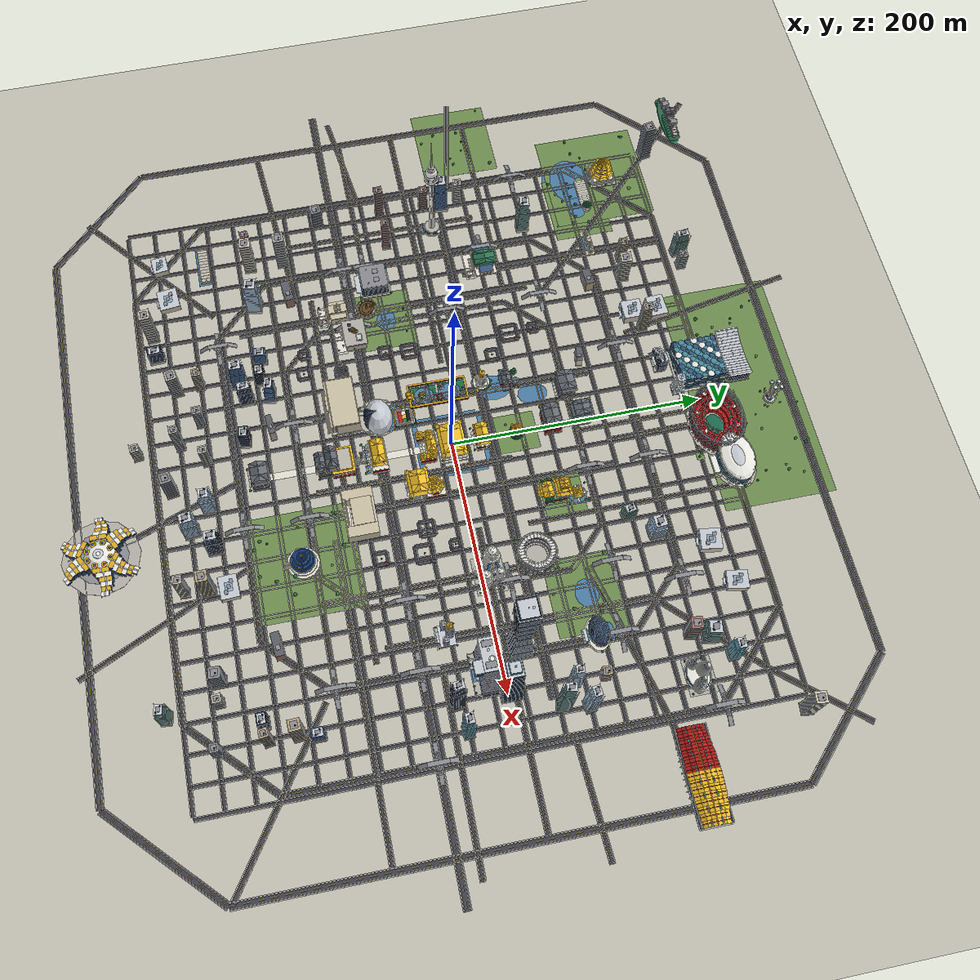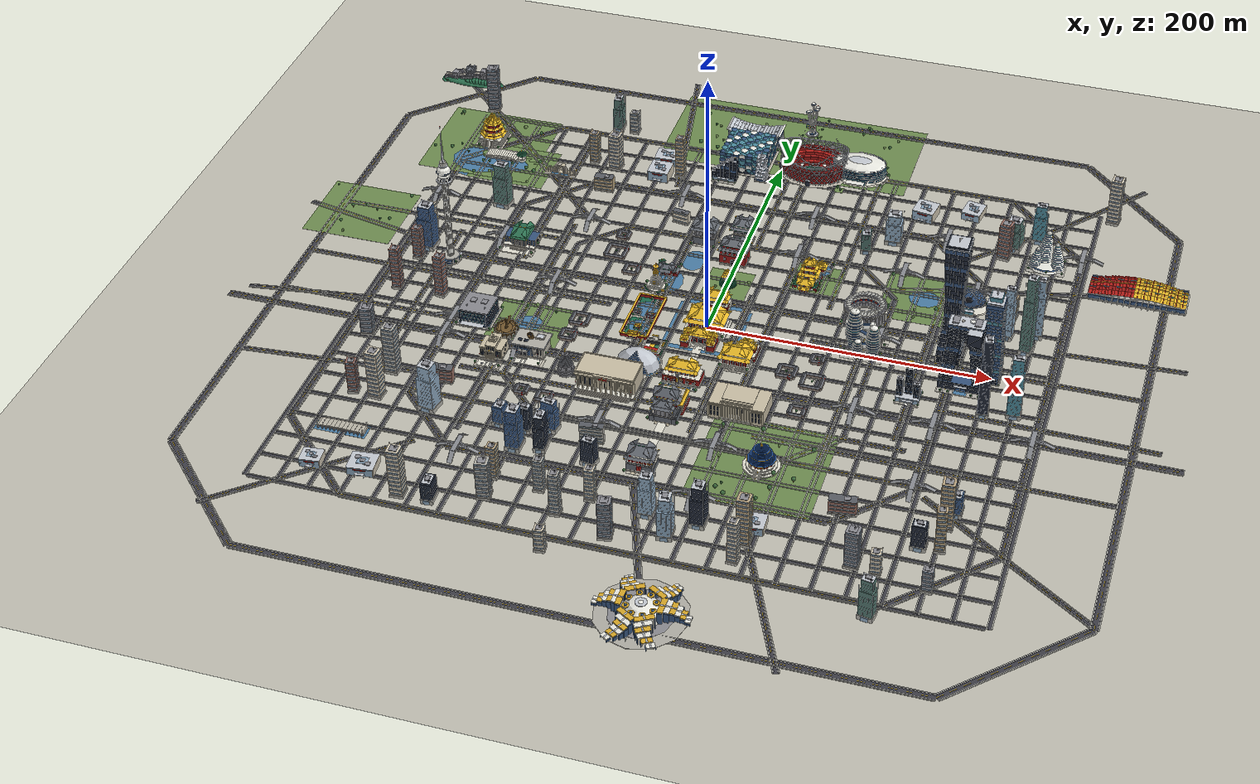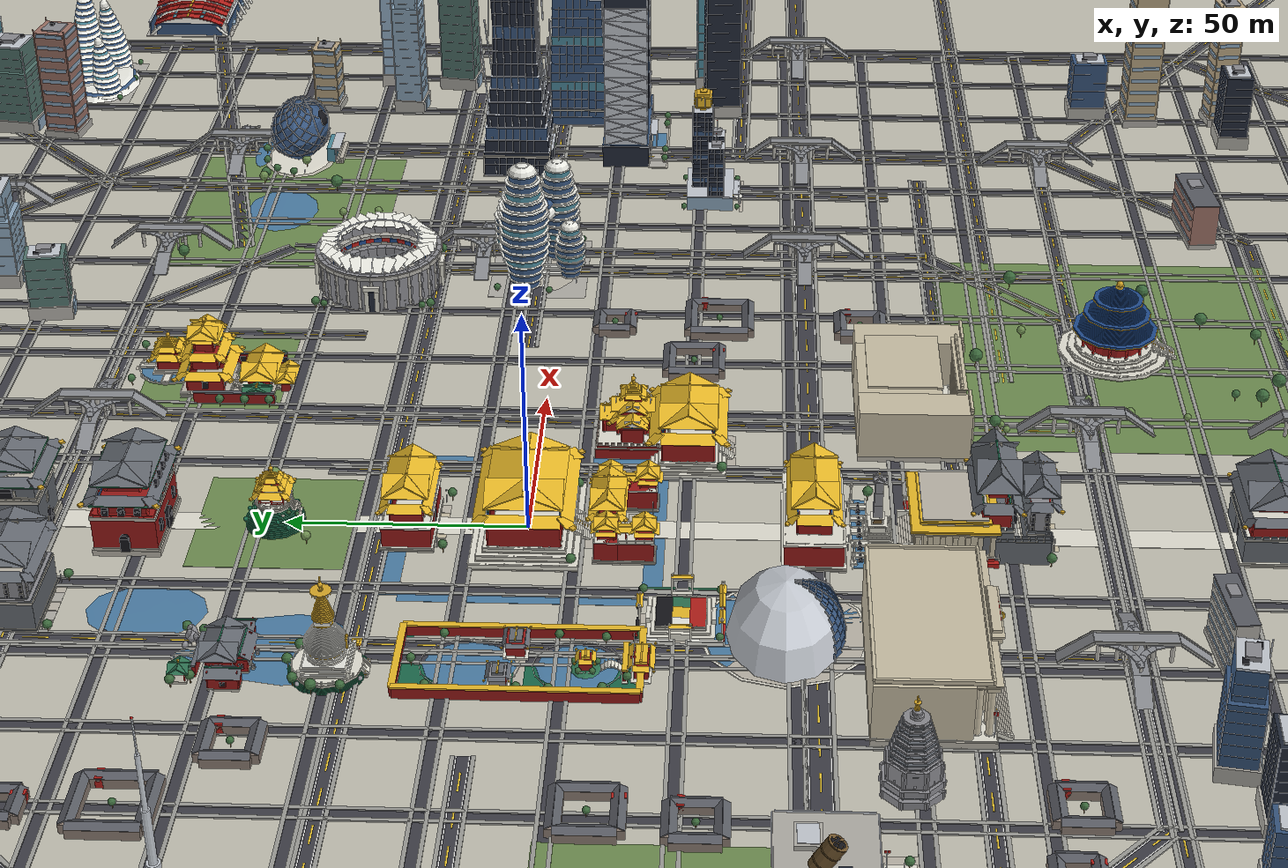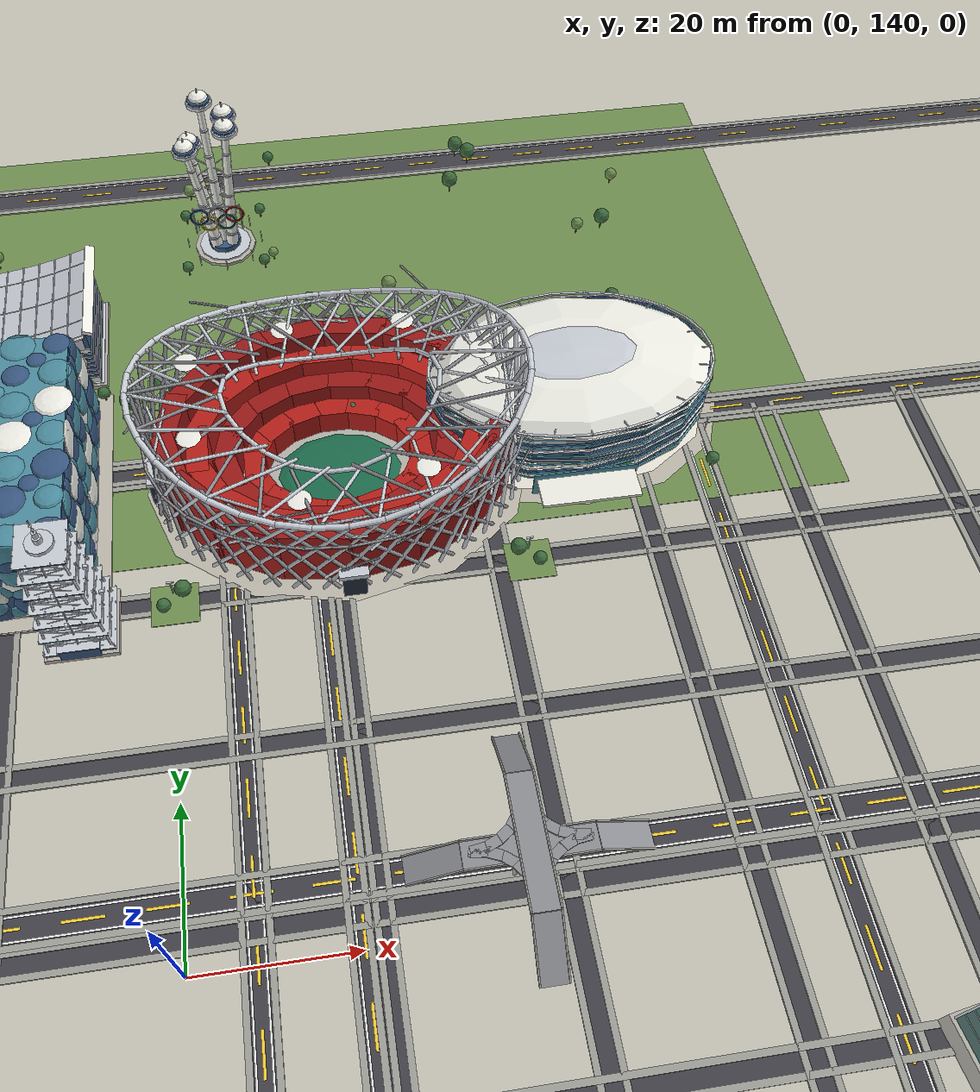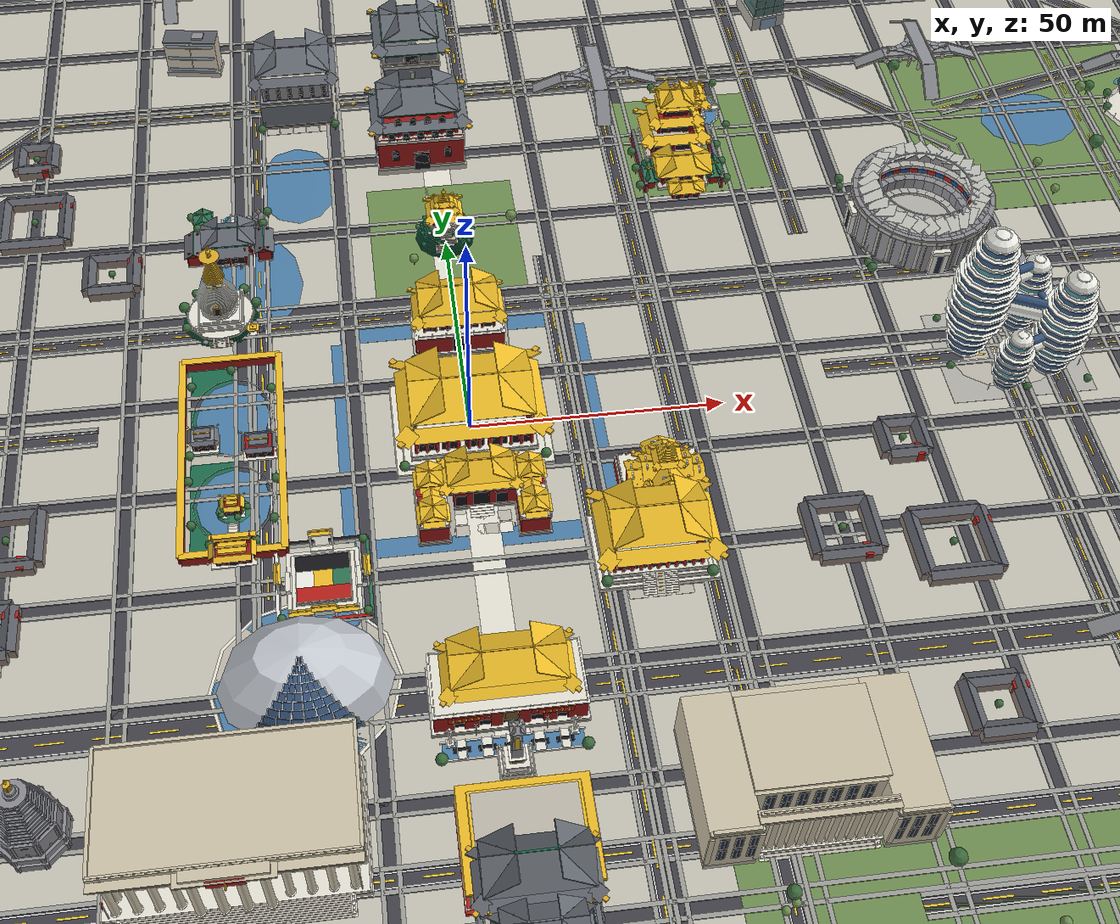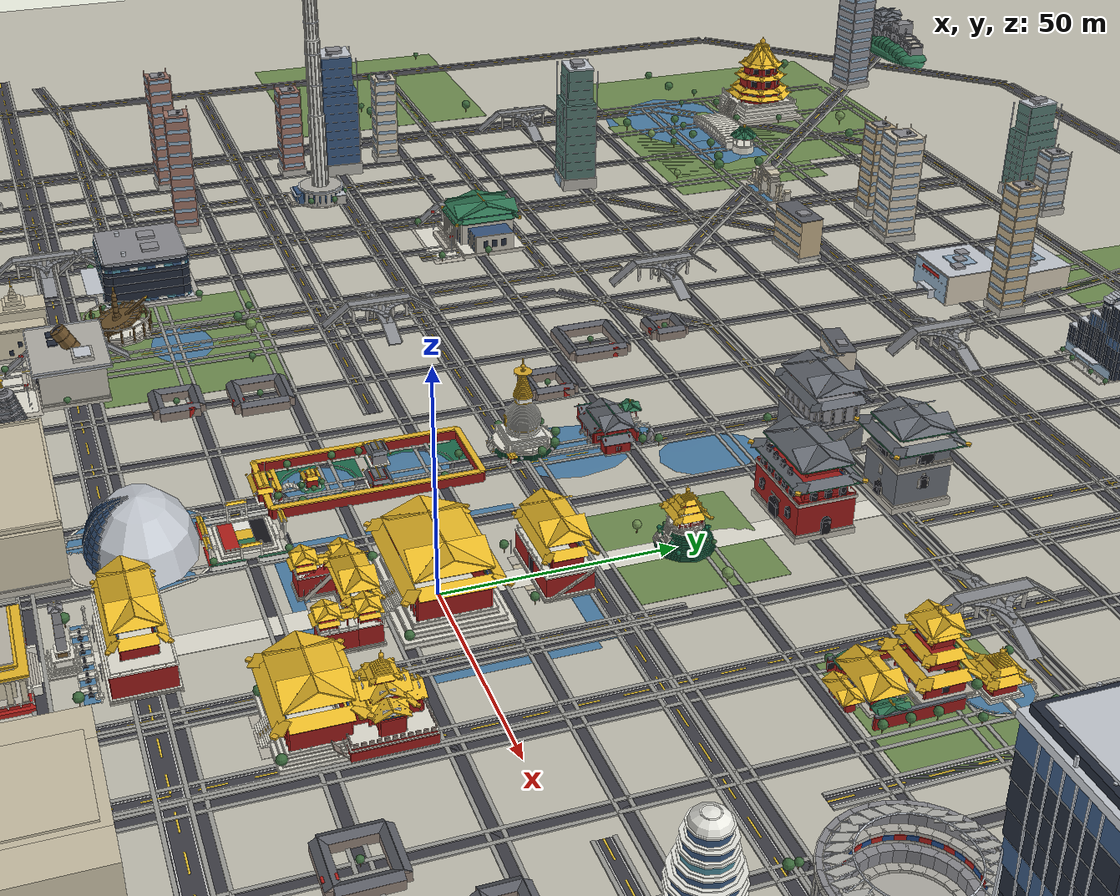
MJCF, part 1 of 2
<?xml version='1.0' encoding='utf-8'?>
<mujoco model="beijing">
  <compiler angle="degree" autolimits="true" />
  <option timestep="0.01" />
  <size memory="256M" />
  <visual>
    <headlight ambient="0.5 0.5 0.5" diffuse="0.45 0.45 0.45" specular="0.2 0.2 0.2" />
    <rgba haze="0.86 0.89 0.94 1" />
    <global azimuth="140" elevation="-25" offwidth="2400" offheight="1600" fovy="45" />
    <map shadowclip="8" />
    <quality shadowsize="4096" />
  </visual>
  <asset>
    <texture type="skybox" builtin="gradient" rgb1="0.5 0.66 0.9" rgb2="0.92 0.95 0.99" width="512" height="512" />
    <texture name="grid" type="2d" builtin="checker" rgb1="0.80 0.79 0.74" rgb2="0.74 0.73 0.68" width="512" height="512" />
    <material name="ground" texture="grid" texrepeat="60 60" texuniform="true" reflectance="0.0" />
    <material name="red" rgba="0.71 0.12 0.10 1" specular="0.2" shininess="0.2" reflectance="0.02" />
    <material name="redwall" rgba="0.60 0.10 0.09 1" specular="0.1" shininess="0.1" reflectance="0.0" />
    <material name="gold" rgba="0.86 0.67 0.16 1" specular="0.7" shininess="0.7" reflectance="0.3" />
    <material name="tile" rgba="0.93 0.74 0.16 1" specular="0.6" shininess="0.65" reflectance="0.25" />
    <material name="greentile" rgba="0.18 0.45 0.32 1" specular="0.5" shininess="0.6" reflectance="0.2" />
    <material name="graytile" rgba="0.40 0.42 0.45 1" specular="0.3" shininess="0.4" reflectance="0.1" />
    <material name="green" rgba="0.11 0.42 0.30 1" specular="0.2" shininess="0.2" reflectance="0.02" />
    <material name="blue" rgba="0.13 0.30 0.56 1" specular="0.2" shininess="0.2" reflectance="0.02" />
    <material name="white" rgba="0.93 0.93 0.90 1" specular="0.2" shininess="0.2" reflectance="0.05" />
    <material name="marble" rgba="0.90 0.89 0.84 1" specular="0.3" shininess="0.4" reflectance="0.1" />
    <material name="stone" rgba="0.74 0.72 0.67 1" specular="0.1" shininess="0.1" reflectance="0.02" />
    <material name="grey" rgba="0.55 0.55 0.57 1" specular="0.2" shininess="0.2" reflectance="0.05" />
    <material name="darkglass" rgba="0.13 0.16 0.22 1" specular="0.9" shininess="0.9" reflectance="0.5" />
    <material name="blueglass" rgba="0.22 0.34 0.50 1" specular="0.9" shininess="0.9" reflectance="0.5" />
    <material name="cyanglass" rgba="0.30 0.55 0.62 1" specular="0.9" shininess="0.9" reflectance="0.5" />
    <material name="steel" rgba="0.78 0.80 0.83 1" specular="0.8" shininess="0.8" reflectance="0.4" />
    <material name="concrete" rgba="0.70 0.69 0.66 1" specular="0.1" shininess="0.1" reflectance="0.02" />
    <material name="water" rgba="0.30 0.50 0.66 1" specular="0.6" shininess="0.7" reflectance="0.4" />
    <material name="black" rgba="0.10 0.10 0.12 1" specular="0.3" shininess="0.3" reflectance="0.05" />
    <material name="bronze" rgba="0.45 0.34 0.18 1" specular="0.5" shininess="0.5" reflectance="0.2" />
    <material name="sand" rgba="0.80 0.76 0.66 1" specular="0.05" shininess="0.05" reflectance="0.0" />
    <material name="dark" rgba="0.08 0.08 0.10 1" specular="0.0" shininess="0.0" reflectance="0.0" />
    <material name="grass" rgba="0.44 0.56 0.32 1" specular="0.05" shininess="0.05" reflectance="0.0" />
    <material name="asphalt" rgba="0.25 0.25 0.28 1" specular="0.1" shininess="0.1" reflectance="0.02" />
    <material name="roadline" rgba="0.95 0.80 0.20 1" specular="0.2" shininess="0.2" reflectance="0.0" />
    <material name="roadwhite" rgba="0.92 0.92 0.92 1" specular="0.2" shininess="0.2" reflectance="0.0" />
    <material name="curb" rgba="0.62 0.62 0.60 1" specular="0.05" shininess="0.05" reflectance="0.0" />
    <material name="roadgrey" rgba="0.55 0.56 0.58 1" specular="0.2" shininess="0.2" reflectance="0.05" />
    <material name="brick" rgba="0.56 0.50 0.46 1" specular="0.05" shininess="0.05" reflectance="0.0" />
    <material name="brick2" rgba="0.62 0.45 0.40 1" specular="0.05" shininess="0.05" reflectance="0.0" />
    <material name="roofgrey" rgba="0.36 0.37 0.40 1" specular="0.2" shininess="0.25" reflectance="0.05" />
    <material name="beige" rgba="0.82 0.78 0.70 1" specular="0.1" shininess="0.1" reflectance="0.02" />
    <material name="tan" rgba="0.74 0.66 0.52 1" specular="0.08" shininess="0.08" reflectance="0.0" />
    <material name="glasslt" rgba="0.56 0.67 0.76 1" specular="0.85" shininess="0.85" reflectance="0.45" />
    <material name="glassgrn" rgba="0.32 0.46 0.43 1" specular="0.85" shininess="0.85" reflectance="0.45" />
    <material name="treedark" rgba="0.24 0.42 0.24 1" specular="0.05" shininess="0.05" reflectance="0.0" />
  </asset>
  <default>
    <geom contype="0" conaffinity="0" group="0" />
  </default>
  <worldbody>
    <light pos="80 -120 220" dir="-0.3 0.45 -1" directional="true" diffuse="0.55 0.55 0.55" specular="0.2 0.2 0.2" castshadow="true" />
    <light pos="-150 120 160" dir="0.5 -0.4 -1" directional="true" diffuse="0.22 0.22 0.25" castshadow="false" />
    <geom type="plane" material="ground" size="1100 1100 1" pos="0 0 0" />
    <geom type="box" material="marble" pos="0 -25 0.05" size="3 130 0.05" />
    <geom type="box" material="water" pos="-24 0 0.02" size="2 24 0.02" />
    <geom type="box" material="water" pos="24 0 0.02" size="2 24 0.02" />
    <geom type="box" material="water" pos="0 26 0.02" size="24 2 0.02" />
    <geom type="box" material="water" pos="0 -26 0.02" size="24 2 0.02" />
    <body name="yongdingmen" pos="0 -150 0">
      <geom type="box" material="stone" pos="0 0 0.16" size="9.1 7.1 0.16" />
      <geom type="box" material="marble" pos="0 0 0.42" size="8.92 6.92 0.11" />
      <geom type="box" material="stone" pos="0 0 0.62" size="8.78 6.78 0.11" />
      <geom type="box" material="marble" pos="0 0 0.8" size="8.94 6.94 0.08" />
      <geom type="box" material="graytile" pos="-5.175 0 3.35" size="3.325 6.5 2.45" />
      <geom type="box" material="graytile" pos="5.175 0 3.35" size="3.325 6.5 2.45" />
      <geom type="box" material="graytile" pos="0 0 5.6" size="1.85 6.5 0.2" />
      <geom type="box" material="dark" pos="0 0 3.15" size="1.8 6 2.25" />
      <geom type="box" material="marble" pos="1.94 -6.48 5.793" size="0.19 0.06 0.16" euler="0 -77.14 0" />
      <geom type="box" material="marble" pos="1.556 -6.48 6.591" size="0.19 0.06 0.16" euler="0 -51.43 0" />
      <geom type="box" material="marble" pos="0.8634 -6.48 7.143" size="0.19 0.06 0.16" euler="0 -25.71 0" />
      <geom type="box" material="marble" pos="1.219e-16 -6.48 7.34" size="0.19 0.06 0.16" euler="0 0 0" />
      <geom type="box" material="marble" pos="-0.8634 -6.48 7.143" size="0.19 0.06 0.16" euler="0 25.71 0" />
      <geom type="box" material="marble" pos="-1.556 -6.48 6.591" size="0.19 0.06 0.16" euler="0 51.43 0" />
      <geom type="box" material="marble" pos="-1.94 -6.48 5.793" size="0.19 0.06 0.16" euler="0 77.14 0" />
      <geom type="box" material="red" pos="-0.851 -6.18 2.79" size="0.7955 0.06 1.89" />
      <geom type="sphere" material="gold" pos="-1.369 -6.24 1.6" size="0.05" />
      <geom type="sphere" material="gold" pos="-0.851 -6.24 1.6" size="0.05" />
      <geom type="sphere" material="gold" pos="-0.333 -6.24 1.6" size="0.05" />
      <geom type="sphere" material="gold" pos="-1.369 -6.24 2.55" size="0.05" />
      <geom type="sphere" material="gold" pos="-0.851 -6.24 2.55" size="0.05" />
      <geom type="sphere" material="gold" pos="-0.333 -6.24 2.55" size="0.05" />
      <geom type="sphere" material="gold" pos="-1.369 -6.24 3.5" size="0.05" />
      <geom type="sphere" material="gold" pos="-0.851 -6.24 3.5" size="0.05" />
      <geom type="sphere" material="gold" pos="-0.333 -6.24 3.5" size="0.05" />
      <geom type="sphere" material="gold" pos="-1.369 -6.24 4.45" size="0.05" />
      <geom type="sphere" material="gold" pos="-0.851 -6.24 4.45" size="0.05" />
      <geom type="sphere" material="gold" pos="-0.333 -6.24 4.45" size="0.05" />
      <geom type="box" material="red" pos="0.851 -6.18 2.79" size="0.7955 0.06 1.89" />
      <geom type="sphere" material="gold" pos="0.333 -6.24 1.6" size="0.05" />
      <geom type="sphere" material="gold" pos="0.851 -6.24 1.6" size="0.05" />
      <geom type="sphere" material="gold" pos="1.369 -6.24 1.6" size="0.05" />
      <geom type="sphere" material="gold" pos="0.333 -6.24 2.55" size="0.05" />
      <geom type="sphere" material="gold" pos="0.851 -6.24 2.55" size="0.05" />
      <geom type="sphere" material="gold" pos="1.369 -6.24 2.55" size="0.05" />
      <geom type="sphere" material="gold" pos="0.333 -6.24 3.5" size="0.05" />
      <geom type="sphere" material="gold" pos="0.851 -6.24 3.5" size="0.05" />
      <geom type="sphere" material="gold" pos="1.369 -6.24 3.5" size="0.05" />
      <geom type="sphere" material="gold" pos="0.333 -6.24 4.45" size="0.05" />
      <geom type="sphere" material="gold" pos="0.851 -6.24 4.45" size="0.05" />
      <geom type="sphere" material="gold" pos="1.369 -6.24 4.45" size="0.05" />
      <geom type="box" material="stone" pos="9.05 -0.15 3.25" size="0.55 6.731 0.1" euler="25.99 0 0" />
      <geom type="box" material="graytile" pos="9.5 0 2.108" size="0.12 5.9 2.108" />
      <geom type="box" material="marble" pos="9.5 -6.2 0.72" size="0.08 0.08 0.42" />
      <geom type="box" material="marble" pos="9.5 -4.183 1.703" size="0.08 0.08 0.42" />
      <geom type="box" material="marble" pos="9.5 -2.167 2.687" size="0.08 0.08 0.42" />
      <geom type="box" material="marble" pos="9.5 -0.15 3.67" size="0.08 0.08 0.42" />
      <geom type="box" material="marble" pos="9.5 1.867 4.653" size="0.08 0.08 0.42" />
      <geom type="box" material="marble" pos="9.5 3.883 5.637" size="0.08 0.08 0.42" />
      <geom type="box" material="marble" pos="9.5 5.9 6.62" size="0.08 0.08 0.42" />
      <geom type="box" material="marble" pos="9.5 -0.15 3.67" size="0.05 6.731 0.03" euler="25.99 0 0" />
      <geom type="box" material="marble" pos="0 0 6.07" size="8.66 6.66 0.13" />
      <geom type="box" material="stone" pos="0 -6.4 6.32" size="8.4 0.13 0.12" />
      <geom type="box" material="graytile" pos="-7.636 -6.4 6.66" size="0.5956 0.14 0.34" />
      <geom type="box" material="graytile" pos="-6.109 -6.4 6.66" size="0.5956 0.14 0.34" />
      <geom type="box" material="graytile" pos="-4.582 -6.4 6.66" size="0.5956 0.14 0.34" />
      <geom type="box" material="graytile" pos="-3.055 -6.4 6.66" size="0.5956 0.14 0.34" />
      <geom type="box" material="graytile" pos="-1.527 -6.4 6.66" size="0.5956 0.14 0.34" />
      <geom type="box" material="graytile" pos="0 -6.4 6.66" size="0.5956 0.14 0.34" />
      <geom type="box" material="graytile" pos="1.527 -6.4 6.66" size="0.5956 0.14 0.34" />
      <geom type="box" material="graytile" pos="3.055 -6.4 6.66" size="0.5956 0.14 0.34" />
      <geom type="box" material="graytile" pos="4.582 -6.4 6.66" size="0.5956 0.14 0.34" />
      <geom type="box" material="graytile" pos="6.109 -6.4 6.66" size="0.5956 0.14 0.34" />
      <geom type="box" material="graytile" pos="7.636 -6.4 6.66" size="0.5956 0.14 0.34" />
      <geom type="box" material="stone" pos="0 6.4 6.32" size="8.4 0.13 0.12" />
      <geom type="box" material="graytile" pos="-7.636 6.4 6.66" size="0.5956 0.14 0.34" />
      <geom type="box" material="graytile" pos="-6.109 6.4 6.66" size="0.5956 0.14 0.34" />
      <geom type="box" material="graytile" pos="-4.582 6.4 6.66" size="0.5956 0.14 0.34" />
      <geom type="box" material="graytile" pos="-3.055 6.4 6.66" size="0.5956 0.14 0.34" />
      <geom type="box" material="graytile" pos="-1.527 6.4 6.66" size="0.5956 0.14 0.34" />
      <geom type="box" material="graytile" pos="0 6.4 6.66" size="0.5956 0.14 0.34" />
      <geom type="box" material="graytile" pos="1.527 6.4 6.66" size="0.5956 0.14 0.34" />
      <geom type="box" material="graytile" pos="3.055 6.4 6.66" size="0.5956 0.14 0.34" />
      <geom type="box" material="graytile" pos="4.582 6.4 6.66" size="0.5956 0.14 0.34" />
      <geom type="box" material="graytile" pos="6.109 6.4 6.66" size="0.5956 0.14 0.34" />
      <geom type="box" material="graytile" pos="7.636 6.4 6.66" size="0.5956 0.14 0.34" />
      <geom type="box" material="stone" pos="-8.4 0 6.32" size="0.13 6.4 0.12" />
      <geom type="box" material="graytile" pos="-8.4 -5.6 6.66" size="0.14 0.624 0.34" />
      <geom type="box" material="graytile" pos="-8.4 -4 6.66" size="0.14 0.624 0.34" />
      <geom type="box" material="graytile" pos="-8.4 -2.4 6.66" size="0.14 0.624 0.34" />
      <geom type="box" material="graytile" pos="-8.4 -0.8 6.66" size="0.14 0.624 0.34" />
      <geom type="box" material="graytile" pos="-8.4 0.8 6.66" size="0.14 0.624 0.34" />
      <geom type="box" material="graytile" pos="-8.4 2.4 6.66" size="0.14 0.624 0.34" />
      <geom type="box" material="graytile" pos="-8.4 4 6.66" size="0.14 0.624 0.34" />
      <geom type="box" material="graytile" pos="-8.4 5.6 6.66" size="0.14 0.624 0.34" />
      <geom type="box" material="stone" pos="8.4 0 6.32" size="0.13 6.4 0.12" />
      <geom type="box" material="graytile" pos="8.4 -5.6 6.66" size="0.14 0.624 0.34" />
      <geom type="box" material="graytile" pos="8.4 -4 6.66" size="0.14 0.624 0.34" />
      <geom type="box" material="graytile" pos="8.4 -2.4 6.66" size="0.14 0.624 0.34" />
      <geom type="box" material="graytile" pos="8.4 -0.8 6.66" size="0.14 0.624 0.34" />
      <geom type="box" material="graytile" pos="8.4 0.8 6.66" size="0.14 0.624 0.34" />
      <geom type="box" material="graytile" pos="8.4 2.4 6.66" size="0.14 0.624 0.34" />
      <geom type="box" material="graytile" pos="8.4 4 6.66" size="0.14 0.624 0.34" />
      <geom type="box" material="graytile" pos="8.4 5.6 6.66" size="0.14 0.624 0.34" />
      <geom type="cylinder" material="stone" pos="-7.3 -5 6.32" size="0.3 0.12" />
      <geom type="cylinder" material="red" pos="-7.3 -5 7.94" size="0.24 1.5" />
      <geom type="cylinder" material="stone" pos="-7.3 -1.667 6.32" size="0.3 0.12" />
      <geom type="cylinder" material="red" pos="-7.3 -1.667 7.94" size="0.24 1.5" />
      <geom type="cylinder" material="stone" pos="-7.3 1.667 6.32" size="0.3 0.12" />
      <geom type="cylinder" material="red" pos="-7.3 1.667 7.94" size="0.24 1.5" />
      <geom type="cylinder" material="stone" pos="-7.3 5 6.32" size="0.3 0.12" />
      <geom type="cylinder" material="red" pos="-7.3 5 7.94" size="0.24 1.5" />
      <geom type="cylinder" material="stone" pos="-4.867 -5 6.32" size="0.3 0.12" />
      <geom type="cylinder" material="red" pos="-4.867 -5 7.94" size="0.24 1.5" />
      <geom type="cylinder" material="stone" pos="-4.867 5 6.32" size="0.3 0.12" />
      <geom type="cylinder" material="red" pos="-4.867 5 7.94" size="0.24 1.5" />
      <geom type="cylinder" material="stone" pos="-2.433 -5 6.32" size="0.3 0.12" />
      <geom type="cylinder" material="red" pos="-2.433 -5 7.94" size="0.24 1.5" />
      <geom type="cylinder" material="stone" pos="-2.433 5 6.32" size="0.3 0.12" />
      <geom type="cylinder" material="red" pos="-2.433 5 7.94" size="0.24 1.5" />
      <geom type="cylinder" material="stone" pos="0 -5 6.32" size="0.3 0.12" />
      <geom type="cylinder" material="red" pos="0 -5 7.94" size="0.24 1.5" />
      <geom type="cylinder" material="stone" pos="0 5 6.32" size="0.3 0.12" />
      <geom type="cylinder" material="red" pos="0 5 7.94" size="0.24 1.5" />
      <geom type="cylinder" material="stone" pos="2.433 -5 6.32" size="0.3 0.12" />
      <geom type="cylinder" material="red" pos="2.433 -5 7.94" size="0.24 1.5" />
      <geom type="cylinder" material="stone" pos="2.433 5 6.32" size="0.3 0.12" />
      <geom type="cylinder" material="red" pos="2.433 5 7.94" size="0.24 1.5" />
      <geom type="cylinder" material="stone" pos="4.867 -5 6.32" size="0.3 0.12" />
      <geom type="cylinder" material="red" pos="4.867 -5 7.94" size="0.24 1.5" />
      <geom type="cylinder" material="stone" pos="4.867 5 6.32" size="0.3 0.12" />
      <geom type="cylinder" material="red" pos="4.867 5 7.94" size="0.24 1.5" />
      <geom type="cylinder" material="stone" pos="7.3 -5 6.32" size="0.3 0.12" />
      <geom type="cylinder" material="red" pos="7.3 -5 7.94" size="0.24 1.5" />
      <geom type="cylinder" material="stone" pos="7.3 -1.667 6.32" size="0.3 0.12" />
      <geom type="cylinder" material="red" pos="7.3 -1.667 7.94" size="0.24 1.5" />
      <geom type="cylinder" material="stone" pos="7.3 1.667 6.32" size="0.3 0.12" />
      <geom type="cylinder" material="red" pos="7.3 1.667 7.94" size="0.24 1.5" />
      <geom type="cylinder" material="stone" pos="7.3 5 6.32" size="0.3 0.12" />
      <geom type="cylinder" material="red" pos="7.3 5 7.94" size="0.24 1.5" />
      <geom type="box" material="redwall" pos="0 5 7.8" size="7.3 0.26 1.5" />
      <geom type="box" material="redwall" pos="-7.3 0 7.8" size="0.26 5 1.5" />
      <geom type="box" material="redwall" pos="7.3 0 7.8" size="0.26 5 1.5" />
      <geom type="box" material="dark" pos="-6.3 -4.95 7.8" size="0.5 0.06 1.2" />
      <geom type="box" material="red" pos="-6.3 -5.05 7.8" size="0.57 0.04 1.3" />
      <geom type="box" material="gold" pos="-6.85 -5.07 7.8" size="0.04 0.04 1.3" />
      <geom type="box" material="gold" pos="-5.75 -5.07 7.8" size="0.04 0.04 1.3" />
      <geom type="box" material="dark" pos="-3.78 -4.95 7.8" size="0.5 0.06 1.2" />
      <geom type="box" material="red" pos="-3.78 -5.05 7.8" size="0.57 0.04 1.3" />
      <geom type="box" material="gold" pos="-4.33 -5.07 7.8" size="0.04 0.04 1.3" />
      <geom type="box" material="gold" pos="-3.23 -5.07 7.8" size="0.04 0.04 1.3" />
      <geom type="box" material="dark" pos="-1.26 -4.95 7.8" size="0.5 0.06 1.2" />
      <geom type="box" material="red" pos="-1.26 -5.05 7.8" size="0.57 0.04 1.3" />
      <geom type="box" material="gold" pos="-1.81 -5.07 7.8" size="0.04 0.04 1.3" />
      <geom type="box" material="gold" pos="-0.71 -5.07 7.8" size="0.04 0.04 1.3" />
      <geom type="box" material="dark" pos="1.26 -4.95 7.8" size="0.5 0.06 1.2" />
      <geom type="box" material="red" pos="1.26 -5.05 7.8" size="0.57 0.04 1.3" />
      <geom type="box" material="gold" pos="0.71 -5.07 7.8" size="0.04 0.04 1.3" />
      <geom type="box" material="gold" pos="1.81 -5.07 7.8" size="0.04 0.04 1.3" />
      <geom type="box" material="dark" pos="3.78 -4.95 7.8" size="0.5 0.06 1.2" />
      <geom type="box" material="red" pos="3.78 -5.05 7.8" size="0.57 0.04 1.3" />
      <geom type="box" material="gold" pos="3.23 -5.07 7.8" size="0.04 0.04 1.3" />
      <geom type="box" material="gold" pos="4.33 -5.07 7.8" size="0.04 0.04 1.3" />
      <geom type="box" material="dark" pos="6.3 -4.95 7.8" size="0.5 0.06 1.2" />
      <geom type="box" material="red" pos="6.3 -5.05 7.8" size="0.57 0.04 1.3" />
      <geom type="box" material="gold" pos="5.75 -5.07 7.8" size="0.04 0.04 1.3" />
      <geom type="box" material="gold" pos="6.85 -5.07 7.8" size="0.04 0.04 1.3" />
      <geom type="box" material="gold" pos="0 -5.08 8.75" size="0.95 0.05 0.42" />
      <geom type="box" material="dark" pos="0 -5.13 8.75" size="0.8 0.04 0.3" />
      <geom type="box" material="green" pos="0 -5 9.44" size="7.55 0.15 0.12" />
      <geom type="box" material="green" pos="0 5 9.44" size="7.55 0.15 0.12" />
      <geom type="box" material="green" pos="-7.3 0 9.44" size="0.15 5.25 0.12" />
      <geom type="box" material="green" pos="7.3 0 9.44" size="0.15 5.25 0.12" />
      <geom type="box" material="red" pos="0 -5 9.66" size="7.55 0.15 0.12" />
      <geom type="box" material="red" pos="0 5 9.66" size="7.55 0.15 0.12" />
      <geom type="box" material="red" pos="-7.3 0 9.66" size="0.15 5.25 0.12" />
      <geom type="box" material="red" pos="7.3 0 9.66" size="0.15 5.25 0.12" />
      <geom type="box" material="green" pos="0 -5 9.8" size="7.55 0.15 0.12" />
      <geom type="box" material="green" pos="0 5 9.8" size="7.55 0.15 0.12" />
      <geom type="box" material="green" pos="-7.3 0 9.8" size="0.15 5.25 0.12" />
      <geom type="box" material="green" pos="7.3 0 9.8" size="0.15 5.25 0.12" />
      <geom type="box" material="green" pos="-6.388 -5 9.9" size="0.13 0.13 0.16" />
      <geom type="box" material="gold" pos="-6.388 -5.12 10.07" size="0.22 0.1 0.05" />
      <geom type="box" material="green" pos="-4.562 -5 9.9" size="0.13 0.13 0.16" />
      <geom type="box" material="gold" pos="-4.562 -5.12 10.07" size="0.22 0.1 0.05" />
      <geom type="box" material="green" pos="-2.737 -5 9.9" size="0.13 0.13 0.16" />
      <geom type="box" material="gold" pos="-2.737 -5.12 10.07" size="0.22 0.1 0.05" />
      <geom type="box" material="green" pos="-0.9125 -5 9.9" size="0.13 0.13 0.16" />
      <geom type="box" material="gold" pos="-0.9125 -5.12 10.07" size="0.22 0.1 0.05" />
      <geom type="box" material="green" pos="0.9125 -5 9.9" size="0.13 0.13 0.16" />
      <geom type="box" material="gold" pos="0.9125 -5.12 10.07" size="0.22 0.1 0.05" />
      <geom type="box" material="green" pos="2.737 -5 9.9" size="0.13 0.13 0.16" />
      <geom type="box" material="gold" pos="2.737 -5.12 10.07" size="0.22 0.1 0.05" />
      <geom type="box" material="green" pos="4.562 -5 9.9" size="0.13 0.13 0.16" />
      <geom type="box" material="gold" pos="4.562 -5.12 10.07" size="0.22 0.1 0.05" />
      <geom type="box" material="green" pos="6.388 -5 9.9" size="0.13 0.13 0.16" />
      <geom type="box" material="gold" pos="6.388 -5.12 10.07" size="0.22 0.1 0.05" />
      <geom type="box" material="green" pos="-6.388 5 9.9" size="0.13 0.13 0.16" />
      <geom type="box" material="gold" pos="-6.388 5.12 10.07" size="0.22 0.1 0.05" />
      <geom type="box" material="green" pos="-4.562 5 9.9" size="0.13 0.13 0.16" />
      <geom type="box" material="gold" pos="-4.562 5.12 10.07" size="0.22 0.1 0.05" />
      <geom type="box" material="green" pos="-2.737 5 9.9" size="0.13 0.13 0.16" />
      <geom type="box" material="gold" pos="-2.737 5.12 10.07" size="0.22 0.1 0.05" />
      <geom type="box" material="green" pos="-0.9125 5 9.9" size="0.13 0.13 0.16" />
      <geom type="box" material="gold" pos="-0.9125 5.12 10.07" size="0.22 0.1 0.05" />
      <geom type="box" material="green" pos="0.9125 5 9.9" size="0.13 0.13 0.16" />
      <geom type="box" material="gold" pos="0.9125 5.12 10.07" size="0.22 0.1 0.05" />
      <geom type="box" material="green" pos="2.737 5 9.9" size="0.13 0.13 0.16" />
      <geom type="box" material="gold" pos="2.737 5.12 10.07" size="0.22 0.1 0.05" />
      <geom type="box" material="green" pos="4.562 5 9.9" size="0.13 0.13 0.16" />
      <geom type="box" material="gold" pos="4.562 5.12 10.07" size="0.22 0.1 0.05" />
      <geom type="box" material="green" pos="6.388 5 9.9" size="0.13 0.13 0.16" />
      <geom type="box" material="gold" pos="6.388 5.12 10.07" size="0.22 0.1 0.05" />
      <geom type="box" material="green" pos="-7.3 -4 9.9" size="0.13 0.13 0.16" />
      <geom type="box" material="gold" pos="-7.42 -4 10.07" size="0.1 0.22 0.05" />
      <geom type="box" material="green" pos="-7.3 -2 9.9" size="0.13 0.13 0.16" />
      <geom type="box" material="gold" pos="-7.42 -2 10.07" size="0.1 0.22 0.05" />
      <geom type="box" material="green" pos="-7.3 0 9.9" size="0.13 0.13 0.16" />
      <geom type="box" material="gold" pos="-7.42 0 10.07" size="0.1 0.22 0.05" />
      <geom type="box" material="green" pos="-7.3 2 9.9" size="0.13 0.13 0.16" />
      <geom type="box" material="gold" pos="-7.42 2 10.07" size="0.1 0.22 0.05" />
      <geom type="box" material="green" pos="-7.3 4 9.9" size="0.13 0.13 0.16" />
      <geom type="box" material="gold" pos="-7.42 4 10.07" size="0.1 0.22 0.05" />
      <geom type="box" material="green" pos="7.3 -4 9.9" size="0.13 0.13 0.16" />
      <geom type="box" material="gold" pos="7.42 -4 10.07" size="0.1 0.22 0.05" />
      <geom type="box" material="green" pos="7.3 -2 9.9" size="0.13 0.13 0.16" />
      <geom type="box" material="gold" pos="7.42 -2 10.07" size="0.1 0.22 0.05" />
      <geom type="box" material="green" pos="7.3 0 9.9" size="0.13 0.13 0.16" />
      <geom type="box" material="gold" pos="7.42 0 10.07" size="0.1 0.22 0.05" />
      <geom type="box" material="green" pos="7.3 2 9.9" size="0.13 0.13 0.16" />
      <geom type="box" material="gold" pos="7.42 2 10.07" size="0.1 0.22 0.05" />
      <geom type="box" material="green" pos="7.3 4 9.9" size="0.13 0.13 0.16" />
      <geom type="box" material="gold" pos="7.42 4 10.07" size="0.1 0.22 0.05" />
      <geom type="box" material="graytile" pos="0 -6.2 10.41" size="7.6 1.11 0.09" euler="-144.2 0 0" />
      <geom type="box" material="graytile" pos="0 6.2 10.41" size="7.6 1.11 0.09" euler="-35.84 0 0" />
      <geom type="box" material="graytile" pos="-8.5 0 10.41" size="1.11 5.3 0.09" euler="0 144.2 0" />
      <geom type="box" material="graytile" pos="8.5 0 10.41" size="1.11 5.3 0.09" euler="0 35.84 0" />
      <geom type="box" material="graytile" pos="-8.5 -6.2 10.41" size="1.116 1.116 0.09" euler="35.84 0 45" />
      <geom type="box" material="gold" pos="-9.4 -7.1 9.976" size="0.396 0.396 0.18" euler="0 0 45" />
      <geom type="box" material="graytile" pos="-8.5 6.2 10.41" size="1.116 1.116 0.09" euler="-35.84 0 -45" />
      <geom type="box" material="gold" pos="-9.4 7.1 9.976" size="0.396 0.396 0.18" euler="0 0 45" />
      <geom type="box" material="graytile" pos="8.5 -6.2 10.41" size="1.116 1.116 0.09" euler="35.84 0 -45" />
      <geom type="box" material="gold" pos="9.4 -7.1 9.976" size="0.396 0.396 0.18" euler="0 0 45" />
      <geom type="box" material="graytile" pos="8.5 6.2 10.41" size="1.116 1.116 0.09" euler="-35.84 0 45" />
      <geom type="box" material="gold" pos="9.4 7.1 9.976" size="0.396 0.396 0.18" euler="0 0 45" />
      <geom type="box" material="green" pos="0 -6.8 9.76" size="7.7 0.11 0.09" />
      <geom type="box" material="green" pos="0 6.8 9.76" size="7.7 0.11 0.09" />
      <geom type="box" material="redwall" pos="0 0 12.21" size="5.8 4 1" />
      <geom type="box" material="dark" pos="-5 -3.96 12.21" size="0.4 0.06 0.6" />
      <geom type="box" material="red" pos="-5 -4.05 12.21" size="0.46 0.04 0.67" />
      <geom type="box" material="dark" pos="-2.5 -3.96 12.21" size="0.4 0.06 0.6" />
      <geom type="box" material="red" pos="-2.5 -4.05 12.21" size="0.46 0.04 0.67" />
      <geom type="box" material="dark" pos="0 -3.96 12.21" size="0.4 0.06 0.6" />
      <geom type="box" material="red" pos="0 -4.05 12.21" size="0.46 0.04 0.67" />
      <geom type="box" material="dark" pos="2.5 -3.96 12.21" size="0.4 0.06 0.6" />
      <geom type="box" material="red" pos="2.5 -4.05 12.21" size="0.46 0.04 0.67" />
      <geom type="box" material="dark" pos="5 -3.96 12.21" size="0.4 0.06 0.6" />
      <geom type="box" material="red" pos="5 -4.05 12.21" size="0.46 0.04 0.67" />
      <geom type="box" material="green" pos="-4.64 -4 12.96" size="0.13 0.13 0.16" />
      <geom type="box" material="gold" pos="-4.64 -4.12 13.13" size="0.22 0.1 0.05" />
      <geom type="box" material="green" pos="-2.32 -4 12.96" size="0.13 0.13 0.16" />
      <geom type="box" material="gold" pos="-2.32 -4.12 13.13" size="0.22 0.1 0.05" />
      <geom type="box" material="green" pos="0 -4 12.96" size="0.13 0.13 0.16" />
      <geom type="box" material="gold" pos="0 -4.12 13.13" size="0.22 0.1 0.05" />
      <geom type="box" material="green" pos="2.32 -4 12.96" size="0.13 0.13 0.16" />
      <geom type="box" material="gold" pos="2.32 -4.12 13.13" size="0.22 0.1 0.05" />
      <geom type="box" material="green" pos="4.64 -4 12.96" size="0.13 0.13 0.16" />
      <geom type="box" material="gold" pos="4.64 -4.12 13.13" size="0.22 0.1 0.05" />
      <geom type="box" material="green" pos="-4.64 4 12.96" size="0.13 0.13 0.16" />
      <geom type="box" material="gold" pos="-4.64 4.12 13.13" size="0.22 0.1 0.05" />
      <geom type="box" material="green" pos="-2.32 4 12.96" size="0.13 0.13 0.16" />
      <geom type="box" material="gold" pos="-2.32 4.12 13.13" size="0.22 0.1 0.05" />
      <geom type="box" material="green" pos="0 4 12.96" size="0.13 0.13 0.16" />
      <geom type="box" material="gold" pos="0 4.12 13.13" size="0.22 0.1 0.05" />
      <geom type="box" material="green" pos="2.32 4 12.96" size="0.13 0.13 0.16" />
      <geom type="box" material="gold" pos="2.32 4.12 13.13" size="0.22 0.1 0.05" />
      <geom type="box" material="green" pos="4.64 4 12.96" size="0.13 0.13 0.16" />
      <geom type="box" material="gold" pos="4.64 4.12 13.13" size="0.22 0.1 0.05" />
      <geom type="box" material="green" pos="-5.8 -2.667 12.96" size="0.13 0.13 0.16" />
      <geom type="box" material="gold" pos="-5.92 -2.667 13.13" size="0.1 0.22 0.05" />
      <geom type="box" material="green" pos="-5.8 0 12.96" size="0.13 0.13 0.16" />
      <geom type="box" material="gold" pos="-5.92 0 13.13" size="0.1 0.22 0.05" />
      <geom type="box" material="green" pos="-5.8 2.667 12.96" size="0.13 0.13 0.16" />
      <geom type="box" material="gold" pos="-5.92 2.667 13.13" size="0.1 0.22 0.05" />
      <geom type="box" material="green" pos="5.8 -2.667 12.96" size="0.13 0.13 0.16" />
      <geom type="box" material="gold" pos="5.92 -2.667 13.13" size="0.1 0.22 0.05" />
      <geom type="box" material="green" pos="5.8 0 12.96" size="0.13 0.13 0.16" />
      <geom type="box" material="gold" pos="5.92 0 13.13" size="0.1 0.22 0.05" />
      <geom type="box" material="green" pos="5.8 2.667 12.96" size="0.13 0.13 0.16" />
      <geom type="box" material="gold" pos="5.92 2.667 13.13" size="0.1 0.22 0.05" />
      <geom type="box" material="graytile" pos="0 -3.25 15.11" size="8.3 3.765 0.11" euler="30.31 0 0" />
      <geom type="box" material="graytile" pos="0 3.25 15.11" size="8.3 3.765 0.11" euler="149.7 0 0" />
      <geom type="box" material="graytile" pos="-5.855 0 15.11" size="3.096 6.5 0.11" euler="0 -37.85 0" />
      <geom type="box" material="graytile" pos="5.855 0 15.11" size="3.096 6.5 0.11" euler="0 -142.1 0" />
      <geom type="box" material="green" pos="0 0 17.03" size="3.51 0.15 0.14" />
      <geom type="box" material="green" pos="-3.53 0 17.15" size="0.16 0.22 0.28" />
      <geom type="box" material="green" pos="3.53 0 17.15" size="0.16 0.22 0.28" />
      <geom type="box" material="bronze" pos="-4.633 -1.625 16.18" size="0.08 0.08 0.08" />
      <geom type="box" material="bronze" pos="-5.855 -3.25 15.23" size="0.08 0.08 0.08" />
      <geom type="box" material="bronze" pos="-7.078 -4.875 14.28" size="0.08 0.08 0.08" />
      <geom type="box" material="bronze" pos="-4.633 1.625 16.18" size="0.08 0.08 0.08" />
      <geom type="box" material="bronze" pos="-5.855 3.25 15.23" size="0.08 0.08 0.08" />
      <geom type="box" material="bronze" pos="-7.078 4.875 14.28" size="0.08 0.08 0.08" />
      <geom type="box" material="bronze" pos="4.633 -1.625 16.18" size="0.08 0.08 0.08" />
      <geom type="box" material="bronze" pos="5.855 -3.25 15.23" size="0.08 0.08 0.08" />
      <geom type="box" material="bronze" pos="7.078 -4.875 14.28" size="0.08 0.08 0.08" />
      <geom type="box" material="bronze" pos="4.633 1.625 16.18" size="0.08 0.08 0.08" />
      <geom type="box" material="bronze" pos="5.855 3.25 15.23" size="0.08 0.08 0.08" />
      <geom type="box" material="bronze" pos="7.078 4.875 14.28" size="0.08 0.08 0.08" />
      <geom type="box" material="stone" pos="-6.4 -8.2 0.04" size="1.5 1.2 0.04" />
      <geom type="box" material="sand" pos="-3.2 -8.2 0.04" size="1.5 1.2 0.04" />
      <geom type="box" material="stone" pos="0 -8.2 0.04" size="1.5 1.2 0.04" />
      <geom type="box" material="sand" pos="3.2 -8.2 0.04" size="1.5 1.2 0.04" />
      <geom type="box" material="stone" pos="6.4 -8.2 0.04" size="1.5 1.2 0.04" />
      <geom type="cylinder" material="grey" pos="-8.2 -7.9 1.55" size="0.07 1.55" />
      <geom type="box" material="grey" pos="-8.2 -7.9 3.18" size="0.16 0.16 0.05" />
      <geom type="sphere" material="white" pos="-8.2 -7.9 3.42" size="0.15" />
      <geom type="cylinder" material="bronze" pos="-8.9 -9.2 0.84" size="0.1 0.84" />
      <geom type="sphere" material="treedark" pos="-8.9 -9.2 2.16" size="1.02" />
      <geom type="cylinder" material="grey" pos="8.2 -7.9 1.55" size="0.07 1.55" />
      <geom type="box" material="grey" pos="8.2 -7.9 3.18" size="0.16 0.16 0.05" />
      <geom type="sphere" material="white" pos="8.2 -7.9 3.42" size="0.15" />
      <geom type="cylinder" material="bronze" pos="8.9 -9.2 0.84" size="0.1 0.84" />
      <geom type="sphere" material="treedark" pos="8.9 -9.2 2.16" size="1.02" />
    </body>
    <body name="zhengyangmen" pos="0 -98 0">
      <geom type="box" material="graytile" pos="-9 -1.2 2.7" size="0.55 5.9 2.7" />
      <geom type="box" material="stone" pos="-9 -7.1 5.5" size="0.55 0.12 0.1" />
      <geom type="box" material="graytile" pos="-9.275 -7.1 5.82" size="0.2063 0.13 0.32" />
      <geom type="box" material="graytile" pos="-8.725 -7.1 5.82" size="0.2063 0.13 0.32" />
      <geom type="box" material="stone" pos="-9 4.7 5.5" size="0.55 0.12 0.1" />
      <geom type="box" material="graytile" pos="-9.275 4.7 5.82" size="0.2063 0.13 0.32" />
      <geom type="box" material="graytile" pos="-8.725 4.7 5.82" size="0.2063 0.13 0.32" />
      <geom type="box" material="stone" pos="-9.55 -1.2 5.5" size="0.12 5.9 0.1" />
      <geom type="box" material="graytile" pos="-9.55 -6.363 5.82" size="0.13 0.5531 0.32" />
      <geom type="box" material="graytile" pos="-9.55 -4.888 5.82" size="0.13 0.5531 0.32" />
      <geom type="box" material="graytile" pos="-9.55 -3.413 5.82" size="0.13 0.5531 0.32" />
      <geom type="box" material="graytile" pos="-9.55 -1.938 5.82" size="0.13 0.5531 0.32" />
      <geom type="box" material="graytile" pos="-9.55 -0.4625 5.82" size="0.13 0.5531 0.32" />
      <geom type="box" material="graytile" pos="-9.55 1.013 5.82" size="0.13 0.5531 0.32" />
      <geom type="box" material="graytile" pos="-9.55 2.487 5.82" size="0.13 0.5531 0.32" />
      <geom type="box" material="graytile" pos="-9.55 3.962 5.82" size="0.13 0.5531 0.32" />
      <geom type="box" material="stone" pos="-8.45 -1.2 5.5" size="0.12 5.9 0.1" />
      <geom type="box" material="graytile" pos="-8.45 -6.363 5.82" size="0.13 0.5531 0.32" />
      <geom type="box" material="graytile" pos="-8.45 -4.888 5.82" size="0.13 0.5531 0.32" />
      <geom type="box" material="graytile" pos="-8.45 -3.413 5.82" size="0.13 0.5531 0.32" />
      <geom type="box" material="graytile" pos="-8.45 -1.938 5.82" size="0.13 0.5531 0.32" />
      <geom type="box" material="graytile" pos="-8.45 -0.4625 5.82" size="0.13 0.5531 0.32" />
      <geom type="box" material="graytile" pos="-8.45 1.013 5.82" size="0.13 0.5531 0.32" />
      <geom type="box" material="graytile" pos="-8.45 2.487 5.82" size="0.13 0.5531 0.32" />
      <geom type="box" material="graytile" pos="-8.45 3.962 5.82" size="0.13 0.5531 0.32" />
      <geom type="box" material="graytile" pos="9 -1.2 2.7" size="0.55 5.9 2.7" />
      <geom type="box" material="stone" pos="9 -7.1 5.5" size="0.55 0.12 0.1" />
      <geom type="box" material="graytile" pos="8.725 -7.1 5.82" size="0.2063 0.13 0.32" />
      <geom type="box" material="graytile" pos="9.275 -7.1 5.82" size="0.2063 0.13 0.32" />
      <geom type="box" material="stone" pos="9 4.7 5.5" size="0.55 0.12 0.1" />
      <geom type="box" material="graytile" pos="8.725 4.7 5.82" size="0.2063 0.13 0.32" />
      <geom type="box" material="graytile" pos="9.275 4.7 5.82" size="0.2063 0.13 0.32" />
      <geom type="box" material="stone" pos="8.45 -1.2 5.5" size="0.12 5.9 0.1" />
      <geom type="box" material="graytile" pos="8.45 -6.363 5.82" size="0.13 0.5531 0.32" />
      <geom type="box" material="graytile" pos="8.45 -4.888 5.82" size="0.13 0.5531 0.32" />
      <geom type="box" material="graytile" pos="8.45 -3.413 5.82" size="0.13 0.5531 0.32" />
      <geom type="box" material="graytile" pos="8.45 -1.938 5.82" size="0.13 0.5531 0.32" />
      <geom type="box" material="graytile" pos="8.45 -0.4625 5.82" size="0.13 0.5531 0.32" />
      <geom type="box" material="graytile" pos="8.45 1.013 5.82" size="0.13 0.5531 0.32" />
      <geom type="box" material="graytile" pos="8.45 2.487 5.82" size="0.13 0.5531 0.32" />
      <geom type="box" material="graytile" pos="8.45 3.962 5.82" size="0.13 0.5531 0.32" />
      <geom type="box" material="stone" pos="9.55 -1.2 5.5" size="0.12 5.9 0.1" />
      <geom type="box" material="graytile" pos="9.55 -6.363 5.82" size="0.13 0.5531 0.32" />
      <geom type="box" material="graytile" pos="9.55 -4.888 5.82" size="0.13 0.5531 0.32" />
      <geom type="box" material="graytile" pos="9.55 -3.413 5.82" size="0.13 0.5531 0.32" />
      <geom type="box" material="graytile" pos="9.55 -1.938 5.82" size="0.13 0.5531 0.32" />
      <geom type="box" material="graytile" pos="9.55 -0.4625 5.82" size="0.13 0.5531 0.32" />
      <geom type="box" material="graytile" pos="9.55 1.013 5.82" size="0.13 0.5531 0.32" />
      <geom type="box" material="graytile" pos="9.55 2.487 5.82" size="0.13 0.5531 0.32" />
      <geom type="box" material="graytile" pos="9.55 3.962 5.82" size="0.13 0.5531 0.32" />
      <geom type="box" material="graytile" pos="-7.5 -7 2.4" size="1.5 0.55 2.4" />
      <geom type="box" material="stone" pos="-7.5 -7.55 4.9" size="1.5 0.12 0.1" />
      <geom type="box" material="graytile" pos="-8.25 -7.55 5.22" size="0.5625 0.13 0.32" />
      <geom type="box" material="graytile" pos="-6.75 -7.55 5.22" size="0.5625 0.13 0.32" />
      <geom type="box" material="stone" pos="-7.5 -6.45 4.9" size="1.5 0.12 0.1" />
      <geom type="box" material="graytile" pos="-8.25 -6.45 5.22" size="0.5625 0.13 0.32" />
      <geom type="box" material="graytile" pos="-6.75 -6.45 5.22" size="0.5625 0.13 0.32" />
      <geom type="box" material="stone" pos="-9 -7 4.9" size="0.12 0.55 0.1" />
      <geom type="box" material="graytile" pos="-9 -7.275 5.22" size="0.13 0.2063 0.32" />
      <geom type="box" material="graytile" pos="-9 -6.725 5.22" size="0.13 0.2063 0.32" />
      <geom type="box" material="stone" pos="-6 -7 4.9" size="0.12 0.55 0.1" />
      <geom type="box" material="graytile" pos="-6 -7.275 5.22" size="0.13 0.2063 0.32" />
      <geom type="box" material="graytile" pos="-6 -6.725 5.22" size="0.13 0.2063 0.32" />
      <geom type="box" material="graytile" pos="7.5 -7 2.4" size="1.5 0.55 2.4" />
      <geom type="box" material="stone" pos="7.5 -7.55 4.9" size="1.5 0.12 0.1" />
      <geom type="box" material="graytile" pos="6.75 -7.55 5.22" size="0.5625 0.13 0.32" />
      <geom type="box" material="graytile" pos="8.25 -7.55 5.22" size="0.5625 0.13 0.32" />
      <geom type="box" material="stone" pos="7.5 -6.45 4.9" size="1.5 0.12 0.1" />
      <geom type="box" material="graytile" pos="6.75 -6.45 5.22" size="0.5625 0.13 0.32" />
      <geom type="box" material="graytile" pos="8.25 -6.45 5.22" size="0.5625 0.13 0.32" />
      <geom type="box" material="stone" pos="6 -7 4.9" size="0.12 0.55 0.1" />
      <geom type="box" material="graytile" pos="6 -7.275 5.22" size="0.13 0.2063 0.32" />
      <geom type="box" material="graytile" pos="6 -6.725 5.22" size="0.13 0.2063 0.32" />
      <geom type="box" material="stone" pos="9 -7 4.9" size="0.12 0.55 0.1" />
      <geom type="box" material="graytile" pos="9 -7.275 5.22" size="0.13 0.2063 0.32" />
      <geom type="box" material="graytile" pos="9 -6.725 5.22" size="0.13 0.2063 0.32" />
      <geom type="box" material="stone" pos="-8.05 -3 2.85" size="0.6 4.25 0.1" euler="36.87 0 0" />
      <geom type="box" material="graytile" pos="-8.55 -3 1.8" size="0.12 3.4 1.8" />
      <geom type="box" material="marble" pos="-8.55 -6.4 0.72" size="0.08 0.08 0.42" />
      <geom type="box" material="marble" pos="-8.55 -5.267 1.57" size="0.08 0.08 0.42" />
      <geom type="box" material="marble" pos="-8.55 -4.133 2.42" size="0.08 0.08 0.42" />
      <geom type="box" material="marble" pos="-8.55 -3 3.27" size="0.08 0.08 0.42" />
      <geom type="box" material="marble" pos="-8.55 -1.867 4.12" size="0.08 0.08 0.42" />
      <geom type="box" material="marble" pos="-8.55 -0.7333 4.97" size="0.08 0.08 0.42" />
      <geom type="box" material="marble" pos="-8.55 0.4 5.82" size="0.08 0.08 0.42" />
      <geom type="box" material="marble" pos="-8.55 -3 3.27" size="0.05 4.25 0.03" euler="36.87 0 0" />
      <geom type="box" material="stone" pos="0 3.8 0.18" size="9.5 3.9 0.18" />
      <geom type="box" material="marble" pos="0 3.8 0.45" size="9.32 3.72 0.1" />
      <geom type="box" material="graytile" pos="0 3.8 4.05" size="9 3.4 3.45" />
      <geom type="box" material="dark" pos="0 0.4 2.6" size="1.7 0.5 2.4" />
      <geom type="cylinder" material="dark" pos="0 0.4 4.6" size="1.7 0.5" euler="0 90 0" />
      <geom type="box" material="marble" pos="1.804 0.38 4.962" size="0.19 0.06 0.15" euler="0 -77.14 0" />
      <geom type="box" material="marble" pos="1.446 0.38 5.703" size="0.19 0.06 0.15" euler="0 -51.43 0" />
      <geom type="box" material="marble" pos="0.8027 0.38 6.217" size="0.19 0.06 0.15" euler="0 -25.71 0" />
      <geom type="box" material="marble" pos="1.133e-16 0.38 6.4" size="0.19 0.06 0.15" euler="0 0 0" />
      <geom type="box" material="marble" pos="-0.8027 0.38 6.217" size="0.19 0.06 0.15" euler="0 25.71 0" />
      <geom type="box" material="marble" pos="-1.446 0.38 5.703" size="0.19 0.06 0.15" euler="0 51.43 0" />
      <geom type="box" material="marble" pos="-1.804 0.38 4.962" size="0.19 0.06 0.15" euler="0 77.14 0" />
      <geom type="box" material="marble" pos="0 3.8 7.36" size="9.16 3.56 0.14" />
      <geom type="box" material="stone" pos="0 0.5 7.6" size="8.9 0.12 0.1" />
      <geom type="box" material="graytile" pos="-8.158 0.5 7.92" size="0.5563 0.13 0.32" />
      <geom type="box" material="graytile" pos="-6.675 0.5 7.92" size="0.5563 0.13 0.32" />
      <geom type="box" material="graytile" pos="-5.192 0.5 7.92" size="0.5563 0.13 0.32" />
      <geom type="box" material="graytile" pos="-3.708 0.5 7.92" size="0.5563 0.13 0.32" />
      <geom type="box" material="graytile" pos="-2.225 0.5 7.92" size="0.5563 0.13 0.32" />
      <geom type="box" material="graytile" pos="-0.7417 0.5 7.92" size="0.5563 0.13 0.32" />
      <geom type="box" material="graytile" pos="0.7417 0.5 7.92" size="0.5563 0.13 0.32" />
      <geom type="box" material="graytile" pos="2.225 0.5 7.92" size="0.5563 0.13 0.32" />
      <geom type="box" material="graytile" pos="3.708 0.5 7.92" size="0.5563 0.13 0.32" />
      <geom type="box" material="graytile" pos="5.192 0.5 7.92" size="0.5563 0.13 0.32" />
      <geom type="box" material="graytile" pos="6.675 0.5 7.92" size="0.5563 0.13 0.32" />
      <geom type="box" material="graytile" pos="8.158 0.5 7.92" size="0.5563 0.13 0.32" />
      <geom type="box" material="stone" pos="0 7.1 7.6" size="8.9 0.12 0.1" />
      <geom type="box" material="graytile" pos="-8.158 7.1 7.92" size="0.5563 0.13 0.32" />
      <geom type="box" material="graytile" pos="-6.675 7.1 7.92" size="0.5563 0.13 0.32" />
      <geom type="box" material="graytile" pos="-5.192 7.1 7.92" size="0.5563 0.13 0.32" />
      <geom type="box" material="graytile" pos="-3.708 7.1 7.92" size="0.5563 0.13 0.32" />
      <geom type="box" material="graytile" pos="-2.225 7.1 7.92" size="0.5563 0.13 0.32" />
      <geom type="box" material="graytile" pos="-0.7417 7.1 7.92" size="0.5563 0.13 0.32" />
      <geom type="box" material="graytile" pos="0.7417 7.1 7.92" size="0.5563 0.13 0.32" />
      <geom type="box" material="graytile" pos="2.225 7.1 7.92" size="0.5563 0.13 0.32" />
      <geom type="box" material="graytile" pos="3.708 7.1 7.92" size="0.5563 0.13 0.32" />
      <geom type="box" material="graytile" pos="5.192 7.1 7.92" size="0.5563 0.13 0.32" />
      <geom type="box" material="graytile" pos="6.675 7.1 7.92" size="0.5563 0.13 0.32" />
      <geom type="box" material="graytile" pos="8.158 7.1 7.92" size="0.5563 0.13 0.32" />
      <geom type="box" material="stone" pos="-8.9 3.8 7.6" size="0.12 3.3 0.1" />
      <geom type="box" material="graytile" pos="-8.9 1.325 7.92" size="0.13 0.6187 0.32" />
      <geom type="box" material="graytile" pos="-8.9 2.975 7.92" size="0.13 0.6187 0.32" />
      <geom type="box" material="graytile" pos="-8.9 4.625 7.92" size="0.13 0.6187 0.32" />
      <geom type="box" material="graytile" pos="-8.9 6.275 7.92" size="0.13 0.6187 0.32" />
      <geom type="box" material="stone" pos="8.9 3.8 7.6" size="0.12 3.3 0.1" />
      <geom type="box" material="graytile" pos="8.9 1.325 7.92" size="0.13 0.6187 0.32" />
      <geom type="box" material="graytile" pos="8.9 2.975 7.92" size="0.13 0.6187 0.32" />
      <geom type="box" material="graytile" pos="8.9 4.625 7.92" size="0.13 0.6187 0.32" />
      <geom type="box" material="graytile" pos="8.9 6.275 7.92" size="0.13 0.6187 0.32" />
      <geom type="cylinder" material="stone" pos="-7.4 1.1 7.62" size="0.32 0.12" />
      <geom type="cylinder" material="red" pos="-7.4 1.1 9.64" size="0.26 1.9" />
      <geom type="cylinder" material="stone" pos="-7.4 2.9 7.62" size="0.32 0.12" />
      <geom type="cylinder" material="red" pos="-7.4 2.9 9.64" size="0.26 1.9" />
      <geom type="cylinder" material="stone" pos="-7.4 4.7 7.62" size="0.32 0.12" />
      <geom type="cylinder" material="red" pos="-7.4 4.7 9.64" size="0.26 1.9" />
      <geom type="cylinder" material="stone" pos="-7.4 6.5 7.62" size="0.32 0.12" />
      <geom type="cylinder" material="red" pos="-7.4 6.5 9.64" size="0.26 1.9" />
      <geom type="cylinder" material="stone" pos="-5.286 1.1 7.62" size="0.32 0.12" />
      <geom type="cylinder" material="red" pos="-5.286 1.1 9.64" size="0.26 1.9" />
      <geom type="cylinder" material="stone" pos="-5.286 6.5 7.62" size="0.32 0.12" />
      <geom type="cylinder" material="red" pos="-5.286 6.5 9.64" size="0.26 1.9" />
      <geom type="cylinder" material="stone" pos="-3.171 1.1 7.62" size="0.32 0.12" />
      <geom type="cylinder" material="red" pos="-3.171 1.1 9.64" size="0.26 1.9" />
      <geom type="cylinder" material="stone" pos="-3.171 6.5 7.62" size="0.32 0.12" />
      <geom type="cylinder" material="red" pos="-3.171 6.5 9.64" size="0.26 1.9" />
      <geom type="cylinder" material="stone" pos="-1.057 1.1 7.62" size="0.32 0.12" />
      <geom type="cylinder" material="red" pos="-1.057 1.1 9.64" size="0.26 1.9" />
      <geom type="cylinder" material="stone" pos="-1.057 6.5 7.62" size="0.32 0.12" />
      <geom type="cylinder" material="red" pos="-1.057 6.5 9.64" size="0.26 1.9" />
      <geom type="cylinder" material="stone" pos="1.057 1.1 7.62" size="0.32 0.12" />
      <geom type="cylinder" material="red" pos="1.057 1.1 9.64" size="0.26 1.9" />
      <geom type="cylinder" material="stone" pos="1.057 6.5 7.62" size="0.32 0.12" />
      <geom type="cylinder" material="red" pos="1.057 6.5 9.64" size="0.26 1.9" />
      <geom type="cylinder" material="stone" pos="3.171 1.1 7.62" size="0.32 0.12" />
      <geom type="cylinder" material="red" pos="3.171 1.1 9.64" size="0.26 1.9" />
      <geom type="cylinder" material="stone" pos="3.171 6.5 7.62" size="0.32 0.12" />
      <geom type="cylinder" material="red" pos="3.171 6.5 9.64" size="0.26 1.9" />
      <geom type="cylinder" material="stone" pos="5.286 1.1 7.62" size="0.32 0.12" />
      <geom type="cylinder" material="red" pos="5.286 1.1 9.64" size="0.26 1.9" />
      <geom type="cylinder" material="stone" pos="5.286 6.5 7.62" size="0.32 0.12" />
      <geom type="cylinder" material="red" pos="5.286 6.5 9.64" size="0.26 1.9" />
      <geom type="cylinder" material="stone" pos="7.4 1.1 7.62" size="0.32 0.12" />
      <geom type="cylinder" material="red" pos="7.4 1.1 9.64" size="0.26 1.9" />
      <geom type="cylinder" material="stone" pos="7.4 2.9 7.62" size="0.32 0.12" />
      <geom type="cylinder" material="red" pos="7.4 2.9 9.64" size="0.26 1.9" />
      <geom type="cylinder" material="stone" pos="7.4 4.7 7.62" size="0.32 0.12" />
      <geom type="cylinder" material="red" pos="7.4 4.7 9.64" size="0.26 1.9" />
      <geom type="cylinder" material="stone" pos="7.4 6.5 7.62" size="0.32 0.12" />
      <geom type="cylinder" material="red" pos="7.4 6.5 9.64" size="0.26 1.9" />
      <geom type="box" material="redwall" pos="0 6.5 9.5" size="7.4 0.27 1.9" />
      <geom type="box" material="redwall" pos="-7.4 3.8 9.5" size="0.27 2.7 1.9" />
      <geom type="box" material="redwall" pos="7.4 3.8 9.5" size="0.27 2.7 1.9" />
      <geom type="box" material="dark" pos="-6.4 1.15 9.5" size="0.55 0.06 1.5" />
      <geom type="box" material="red" pos="-6.4 1.05 9.5" size="0.62 0.04 1.6" />
      <geom type="box" material="dark" pos="-4.267 1.15 9.5" size="0.55 0.06 1.5" />
      <geom type="box" material="red" pos="-4.267 1.05 9.5" size="0.62 0.04 1.6" />
      <geom type="box" material="dark" pos="-2.133 1.15 9.5" size="0.55 0.06 1.5" />
      <geom type="box" material="red" pos="-2.133 1.05 9.5" size="0.62 0.04 1.6" />
      <geom type="box" material="dark" pos="8.882e-16 1.15 9.5" size="0.55 0.06 1.5" />
      <geom type="box" material="red" pos="8.882e-16 1.05 9.5" size="0.62 0.04 1.6" />
      <geom type="box" material="dark" pos="2.133 1.15 9.5" size="0.55 0.06 1.5" />
      <geom type="box" material="red" pos="2.133 1.05 9.5" size="0.62 0.04 1.6" />
      <geom type="box" material="dark" pos="4.267 1.15 9.5" size="0.55 0.06 1.5" />
      <geom type="box" material="red" pos="4.267 1.05 9.5" size="0.62 0.04 1.6" />
      <geom type="box" material="dark" pos="6.4 1.15 9.5" size="0.55 0.06 1.5" />
      <geom type="box" material="red" pos="6.4 1.05 9.5" size="0.62 0.04 1.6" />
      <geom type="box" material="gold" pos="0 1.01 11.4" size="1 0.05 0.45" />
      <geom type="box" material="dark" pos="0 0.96 11.4" size="0.85 0.04 0.33" />
      <geom type="box" material="green" pos="0 1.1 11.54" size="7.65 0.16 0.13" />
      <geom type="box" material="green" pos="0 6.5 11.54" size="7.65 0.16 0.13" />
      <geom type="box" material="green" pos="-7.4 3.8 11.54" size="0.16 2.95 0.13" />
      <geom type="box" material="green" pos="7.4 3.8 11.54" size="0.16 2.95 0.13" />
      <geom type="box" material="red" pos="0 1.1 11.78" size="7.65 0.16 0.13" />
      <geom type="box" material="red" pos="0 6.5 11.78" size="7.65 0.16 0.13" />
      <geom type="box" material="red" pos="-7.4 3.8 11.78" size="0.16 2.95 0.13" />
      <geom type="box" material="red" pos="7.4 3.8 11.78" size="0.16 2.95 0.13" />
      <geom type="box" material="green" pos="0 1.1 11.94" size="7.65 0.16 0.13" />
      <geom type="box" material="green" pos="0 6.5 11.94" size="7.65 0.16 0.13" />
      <geom type="box" material="green" pos="-7.4 3.8 11.94" size="0.16 2.95 0.13" />
      <geom type="box" material="green" pos="7.4 3.8 11.94" size="0.16 2.95 0.13" />
      <geom type="box" material="green" pos="-6.167 1.1 12.04" size="0.13 0.13 0.15" />
      <geom type="box" material="gold" pos="-6.167 0.98 12.2" size="0.21 0.1 0.05" />
      <geom type="box" material="green" pos="-3.7 1.1 12.04" size="0.13 0.13 0.15" />
      <geom type="box" material="gold" pos="-3.7 0.98 12.2" size="0.21 0.1 0.05" />
      <geom type="box" material="green" pos="-1.233 1.1 12.04" size="0.13 0.13 0.15" />
      <geom type="box" material="gold" pos="-1.233 0.98 12.2" size="0.21 0.1 0.05" />
      <geom type="box" material="green" pos="1.233 1.1 12.04" size="0.13 0.13 0.15" />
      <geom type="box" material="gold" pos="1.233 0.98 12.2" size="0.21 0.1 0.05" />
      <geom type="box" material="green" pos="3.7 1.1 12.04" size="0.13 0.13 0.15" />
      <geom type="box" material="gold" pos="3.7 0.98 12.2" size="0.21 0.1 0.05" />
      <geom type="box" material="green" pos="6.167 1.1 12.04" size="0.13 0.13 0.15" />
      <geom type="box" material="gold" pos="6.167 0.98 12.2" size="0.21 0.1 0.05" />
      <geom type="box" material="green" pos="-6.167 6.5 12.04" size="0.13 0.13 0.15" />
      <geom type="box" material="gold" pos="-6.167 6.62 12.2" size="0.21 0.1 0.05" />
      <geom type="box" material="green" pos="-3.7 6.5 12.04" size="0.13 0.13 0.15" />
      <geom type="box" material="gold" pos="-3.7 6.62 12.2" size="0.21 0.1 0.05" />
      <geom type="box" material="green" pos="-1.233 6.5 12.04" size="0.13 0.13 0.15" />
      <geom type="box" material="gold" pos="-1.233 6.62 12.2" size="0.21 0.1 0.05" />
      <geom type="box" material="green" pos="1.233 6.5 12.04" size="0.13 0.13 0.15" />
      <geom type="box" material="gold" pos="1.233 6.62 12.2" size="0.21 0.1 0.05" />
      <geom type="box" material="green" pos="3.7 6.5 12.04" size="0.13 0.13 0.15" />
      <geom type="box" material="gold" pos="3.7 6.62 12.2" size="0.21 0.1 0.05" />
      <geom type="box" material="green" pos="6.167 6.5 12.04" size="0.13 0.13 0.15" />
      <geom type="box" material="gold" pos="6.167 6.62 12.2" size="0.21 0.1 0.05" />
      <geom type="box" material="green" pos="-7.4 2 12.04" size="0.13 0.13 0.15" />
      <geom type="box" material="gold" pos="-7.52 2 12.2" size="0.1 0.21 0.05" />
      <geom type="box" material="green" pos="-7.4 3.8 12.04" size="0.13 0.13 0.15" />
      <geom type="box" material="gold" pos="-7.52 3.8 12.2" size="0.1 0.21 0.05" />
      <geom type="box" material="green" pos="-7.4 5.6 12.04" size="0.13 0.13 0.15" />
      <geom type="box" material="gold" pos="-7.52 5.6 12.2" size="0.1 0.21 0.05" />
      <geom type="box" material="green" pos="7.4 2 12.04" size="0.13 0.13 0.15" />
      <geom type="box" material="gold" pos="7.52 2 12.2" size="0.1 0.21 0.05" />
      <geom type="box" material="green" pos="7.4 3.8 12.04" size="0.13 0.13 0.15" />
      <geom type="box" material="gold" pos="7.52 3.8 12.2" size="0.1 0.21 0.05" />
      <geom type="box" material="green" pos="7.4 5.6 12.04" size="0.13 0.13 0.15" />
      <geom type="box" material="gold" pos="7.52 5.6 12.2" size="0.1 0.21 0.05" />
      <geom type="box" material="graytile" pos="0 -0.2 12.57" size="7.7 1.235 0.1" euler="-144.1 0 0" />
      <geom type="box" material="graytile" pos="0 7.8 12.57" size="7.7 1.235 0.1" euler="-35.94 0 0" />
      <geom type="box" material="graytile" pos="-8.7 3.8 12.57" size="1.235 3 0.1" euler="0 144.1 0" />
      <geom type="box" material="graytile" pos="8.7 3.8 12.57" size="1.235 3 0.1" euler="0 35.94 0" />
      <geom type="box" material="graytile" pos="-8.7 -0.2 12.57" size="1.2 1.2 0.1" euler="35.94 0 45" />
      <geom type="box" material="gold" pos="-9.7 -1.2 12.09" size="0.4 0.4 0.2" euler="0 0 45" />
      <geom type="box" material="graytile" pos="-8.7 7.8 12.57" size="1.2 1.2 0.1" euler="-35.94 0 -45" />
      <geom type="box" material="gold" pos="-9.7 8.8 12.09" size="0.4 0.4 0.2" euler="0 0 45" />
      <geom type="box" material="graytile" pos="8.7 -0.2 12.57" size="1.2 1.2 0.1" euler="35.94 0 -45" />
      <geom type="box" material="gold" pos="9.7 -1.2 12.09" size="0.4 0.4 0.2" euler="0 0 45" />
      <geom type="box" material="graytile" pos="8.7 7.8 12.57" size="1.2 1.2 0.1" euler="-35.94 0 45" />
      <geom type="box" material="gold" pos="9.7 8.8 12.09" size="0.4 0.4 0.2" euler="0 0 45" />
      <geom type="box" material="redwall" pos="0 3.8 14.75" size="5.8 1.8 1.3" />
      <geom type="box" material="dark" pos="-5 2.04 14.75" size="0.42 0.06 0.85" />
      <geom type="box" material="red" pos="-5 1.95 14.75" size="0.48 0.04 0.93" />
      <geom type="box" material="dark" pos="-3.333 2.04 14.75" size="0.42 0.06 0.85" />
      <geom type="box" material="red" pos="-3.333 1.95 14.75" size="0.48 0.04 0.93" />
      <geom type="box" material="dark" pos="-1.667 2.04 14.75" size="0.42 0.06 0.85" />
      <geom type="box" material="red" pos="-1.667 1.95 14.75" size="0.48 0.04 0.93" />
      <geom type="box" material="dark" pos="0 2.04 14.75" size="0.42 0.06 0.85" />
      <geom type="box" material="red" pos="0 1.95 14.75" size="0.48 0.04 0.93" />
      <geom type="box" material="dark" pos="1.667 2.04 14.75" size="0.42 0.06 0.85" />
      <geom type="box" material="red" pos="1.667 1.95 14.75" size="0.48 0.04 0.93" />
      <geom type="box" material="dark" pos="3.333 2.04 14.75" size="0.42 0.06 0.85" />
      <geom type="box" material="red" pos="3.333 1.95 14.75" size="0.48 0.04 0.93" />
      <geom type="box" material="dark" pos="5 2.04 14.75" size="0.42 0.06 0.85" />
      <geom type="box" material="red" pos="5 1.95 14.75" size="0.48 0.04 0.93" />
      <geom type="box" material="green" pos="-4.64 2 15.5" size="0.13 0.13 0.15" />
      <geom type="box" material="gold" pos="-4.64 1.88 15.66" size="0.21 0.1 0.05" />
      <geom type="box" material="green" pos="-2.32 2 15.5" size="0.13 0.13 0.15" />
      <geom type="box" material="gold" pos="-2.32 1.88 15.66" size="0.21 0.1 0.05" />
      <geom type="box" material="green" pos="0 2 15.5" size="0.13 0.13 0.15" />
      <geom type="box" material="gold" pos="0 1.88 15.66" size="0.21 0.1 0.05" />
      <geom type="box" material="green" pos="2.32 2 15.5" size="0.13 0.13 0.15" />
      <geom type="box" material="gold" pos="2.32 1.88 15.66" size="0.21 0.1 0.05" />
      <geom type="box" material="green" pos="4.64 2 15.5" size="0.13 0.13 0.15" />
      <geom type="box" material="gold" pos="4.64 1.88 15.66" size="0.21 0.1 0.05" />
      <geom type="box" material="green" pos="-4.64 5.6 15.5" size="0.13 0.13 0.15" />
      <geom type="box" material="gold" pos="-4.64 5.72 15.66" size="0.21 0.1 0.05" />
      <geom type="box" material="green" pos="-2.32 5.6 15.5" size="0.13 0.13 0.15" />
      <geom type="box" material="gold" pos="-2.32 5.72 15.66" size="0.21 0.1 0.05" />
      <geom type="box" material="green" pos="0 5.6 15.5" size="0.13 0.13 0.15" />
      <geom type="box" material="gold" pos="0 5.72 15.66" size="0.21 0.1 0.05" />
      <geom type="box" material="green" pos="2.32 5.6 15.5" size="0.13 0.13 0.15" />
      <geom type="box" material="gold" pos="2.32 5.72 15.66" size="0.21 0.1 0.05" />
      <geom type="box" material="green" pos="4.64 5.6 15.5" size="0.13 0.13 0.15" />
      <geom type="box" material="gold" pos="4.64 5.72 15.66" size="0.21 0.1 0.05" />
      <geom type="box" material="green" pos="-5.8 2.6 15.5" size="0.13 0.13 0.15" />
      <geom type="box" material="gold" pos="-5.92 2.6 15.66" size="0.1 0.21 0.05" />
      <geom type="box" material="green" pos="-5.8 3.8 15.5" size="0.13 0.13 0.15" />
      <geom type="box" material="gold" pos="-5.92 3.8 15.66" size="0.1 0.21 0.05" />
      <geom type="box" material="green" pos="-5.8 5 15.5" size="0.13 0.13 0.15" />
      <geom type="box" material="gold" pos="-5.92 5 15.66" size="0.1 0.21 0.05" />
      <geom type="box" material="green" pos="5.8 2.6 15.5" size="0.13 0.13 0.15" />
      <geom type="box" material="gold" pos="5.92 2.6 15.66" size="0.1 0.21 0.05" />
      <geom type="box" material="green" pos="5.8 3.8 15.5" size="0.13 0.13 0.15" />
      <geom type="box" material="gold" pos="5.92 3.8 15.66" size="0.1 0.21 0.05" />
      <geom type="box" material="green" pos="5.8 5 15.5" size="0.13 0.13 0.15" />
      <geom type="box" material="gold" pos="5.92 5 15.66" size="0.1 0.21 0.05" />
      <geom type="box" material="graytile" pos="0 1.55 18.45" size="8.5 3.29 0.1" euler="46.85 0 0" />
      <geom type="box" material="graytile" pos="0 6.05 18.45" size="8.5 3.29 0.1" euler="133.2 0 0" />
      <geom type="box" material="graytile" pos="-5.8 3.8 18.45" size="3.612 4.5 0.1" euler="0 -41.63 0" />
      <geom type="box" material="graytile" pos="5.8 3.8 18.45" size="3.612 4.5 0.1" euler="0 -138.4 0" />
      <geom type="box" material="green" pos="0 3.8 20.87" size="3.2 0.15 0.14" />
      <geom type="box" material="green" pos="-3.22 3.8 20.99" size="0.16 0.22 0.28" />
      <geom type="box" material="bronze" pos="-4.45 2.675 19.77" size="0.08 0.08 0.08" />
      <geom type="box" material="bronze" pos="-5.8 1.55 18.57" size="0.08 0.08 0.08" />
      <geom type="box" material="bronze" pos="-4.45 4.925 19.77" size="0.08 0.08 0.08" />
      <geom type="box" material="bronze" pos="-5.8 6.05 18.57" size="0.08 0.08 0.08" />
      <geom type="box" material="green" pos="3.22 3.8 20.99" size="0.16 0.22 0.28" />
      <geom type="box" material="bronze" pos="4.45 2.675 19.77" size="0.08 0.08 0.08" />
      <geom type="box" material="bronze" pos="5.8 1.55 18.57" size="0.08 0.08 0.08" />
      <geom type="box" material="bronze" pos="4.45 4.925 19.77" size="0.08 0.08 0.08" />
      <geom type="box" material="bronze" pos="5.8 6.05 18.57" size="0.08 0.08 0.08" />
      <geom type="box" material="stone" pos="-3.15 3.8 19.22" size="0.1 1.21 1.44" />
      <geom type="box" material="stone" pos="3.15 3.8 19.22" size="0.1 1.21 1.44" />
      <geom type="box" material="stone" pos="0 -5 0.18" size="6.45 2.65 0.18" />
      <geom type="box" material="graytile" pos="0 -5 2.725" size="6.15 2.35 2.275" />
      <geom type="box" material="stone" pos="0 -5 4.84" size="6.2 2.4 0.16" />
      <geom type="box" material="grey" pos="0 -5 8.1" size="5.5 2 3.1" />
      <geom type="box" material="graytile" pos="0 -5 5.22" size="5.6 2.1 0.22" />
      <geom type="box" material="stone" pos="0 -5 11" size="5.64 2.14 0.2" />
      <geom type="box" material="stone" pos="-4.5 -7.02 6" size="0.4 0.04 0.52" />
      <geom type="box" material="dark" pos="-4.5 -7.12 6" size="0.3 0.06 0.4" />
      <geom type="box" material="stone" pos="-1.5 -7.02 6" size="0.4 0.04 0.52" />
      <geom type="box" material="dark" pos="-1.5 -7.12 6" size="0.3 0.06 0.4" />
      <geom type="box" material="stone" pos="1.5 -7.02 6" size="0.4 0.04 0.52" />
      <geom type="box" material="dark" pos="1.5 -7.12 6" size="0.3 0.06 0.4" />
      <geom type="box" material="stone" pos="4.5 -7.02 6" size="0.4 0.04 0.52" />
      <geom type="box" material="dark" pos="4.5 -7.12 6" size="0.3 0.06 0.4" />
      <geom type="box" material="stone" pos="-5.52 -6.4 6" size="0.04 0.4 0.52" />
      <geom type="box" material="dark" pos="-5.62 -6.4 6" size="0.06 0.3 0.4" />
      <geom type="box" material="stone" pos="-5.52 -3.6 6" size="0.04 0.4 0.52" />
      <geom type="box" material="dark" pos="-5.62 -3.6 6" size="0.06 0.3 0.4" />
      <geom type="box" material="stone" pos="5.52 -6.4 6" size="0.04 0.4 0.52" />
      <geom type="box" material="dark" pos="5.62 -6.4 6" size="0.06 0.3 0.4" />
      <geom type="box" material="stone" pos="5.52 -3.6 6" size="0.04 0.4 0.52" />
      <geom type="box" material="dark" pos="5.62 -3.6 6" size="0.06 0.3 0.4" />
      <geom type="box" material="stone" pos="-4.5 -7.02 7.15" size="0.4 0.04 0.52" />
      <geom type="box" material="dark" pos="-4.5 -7.12 7.15" size="0.3 0.06 0.4" />
      <geom type="box" material="stone" pos="-1.5 -7.02 7.15" size="0.4 0.04 0.52" />
      <geom type="box" material="dark" pos="-1.5 -7.12 7.15" size="0.3 0.06 0.4" />
      <geom type="box" material="stone" pos="1.5 -7.02 7.15" size="0.4 0.04 0.52" />
      <geom type="box" material="dark" pos="1.5 -7.12 7.15" size="0.3 0.06 0.4" />
      <geom type="box" material="stone" pos="4.5 -7.02 7.15" size="0.4 0.04 0.52" />
      <geom type="box" material="dark" pos="4.5 -7.12 7.15" size="0.3 0.06 0.4" />
      <geom type="box" material="stone" pos="-5.52 -6.4 7.15" size="0.04 0.4 0.52" />
      <geom type="box" material="dark" pos="-5.62 -6.4 7.15" size="0.06 0.3 0.4" />
      <geom type="box" material="stone" pos="-5.52 -3.6 7.15" size="0.04 0.4 0.52" />
      <geom type="box" material="dark" pos="-5.62 -3.6 7.15" size="0.06 0.3 0.4" />
      <geom type="box" material="stone" pos="5.52 -6.4 7.15" size="0.04 0.4 0.52" />
      <geom type="box" material="dark" pos="5.62 -6.4 7.15" size="0.06 0.3 0.4" />
      <geom type="box" material="stone" pos="5.52 -3.6 7.15" size="0.04 0.4 0.52" />
      <geom type="box" material="dark" pos="5.62 -3.6 7.15" size="0.06 0.3 0.4" />
      <geom type="box" material="stone" pos="-4.5 -7.02 8.3" size="0.4 0.04 0.52" />
      <geom type="box" material="dark" pos="-4.5 -7.12 8.3" size="0.3 0.06 0.4" />
      <geom type="box" material="stone" pos="-1.5 -7.02 8.3" size="0.4 0.04 0.52" />
      <geom type="box" material="dark" pos="-1.5 -7.12 8.3" size="0.3 0.06 0.4" />
      <geom type="box" material="stone" pos="1.5 -7.02 8.3" size="0.4 0.04 0.52" />
      <geom type="box" material="dark" pos="1.5 -7.12 8.3" size="0.3 0.06 0.4" />
      <geom type="box" material="stone" pos="4.5 -7.02 8.3" size="0.4 0.04 0.52" />
      <geom type="box" material="dark" pos="4.5 -7.12 8.3" size="0.3 0.06 0.4" />
      <geom type="box" material="stone" pos="-5.52 -6.4 8.3" size="0.04 0.4 0.52" />
      <geom type="box" material="dark" pos="-5.62 -6.4 8.3" size="0.06 0.3 0.4" />
      <geom type="box" material="stone" pos="-5.52 -3.6 8.3" size="0.04 0.4 0.52" />
      <geom type="box" material="dark" pos="-5.62 -3.6 8.3" size="0.06 0.3 0.4" />
      <geom type="box" material="stone" pos="5.52 -6.4 8.3" size="0.04 0.4 0.52" />
      <geom type="box" material="dark" pos="5.62 -6.4 8.3" size="0.06 0.3 0.4" />
      <geom type="box" material="stone" pos="5.52 -3.6 8.3" size="0.04 0.4 0.52" />
      <geom type="box" material="dark" pos="5.62 -3.6 8.3" size="0.06 0.3 0.4" />
      <geom type="box" material="stone" pos="-4.5 -7.02 9.45" size="0.4 0.04 0.52" />
      <geom type="box" material="dark" pos="-4.5 -7.12 9.45" size="0.3 0.06 0.4" />
      <geom type="box" material="stone" pos="-1.5 -7.02 9.45" size="0.4 0.04 0.52" />
      <geom type="box" material="dark" pos="-1.5 -7.12 9.45" size="0.3 0.06 0.4" />
      <geom type="box" material="stone" pos="1.5 -7.02 9.45" size="0.4 0.04 0.52" />
      <geom type="box" material="dark" pos="1.5 -7.12 9.45" size="0.3 0.06 0.4" />
      <geom type="box" material="stone" pos="4.5 -7.02 9.45" size="0.4 0.04 0.52" />
      <geom type="box" material="dark" pos="4.5 -7.12 9.45" size="0.3 0.06 0.4" />
      <geom type="box" material="stone" pos="-5.52 -6.4 9.45" size="0.04 0.4 0.52" />
      <geom type="box" material="dark" pos="-5.62 -6.4 9.45" size="0.06 0.3 0.4" />
      <geom type="box" material="stone" pos="-5.52 -3.6 9.45" size="0.04 0.4 0.52" />
      <geom type="box" material="dark" pos="-5.62 -3.6 9.45" size="0.06 0.3 0.4" />
      <geom type="box" material="stone" pos="5.52 -6.4 9.45" size="0.04 0.4 0.52" />
      <geom type="box" material="dark" pos="5.62 -6.4 9.45" size="0.06 0.3 0.4" />
      <geom type="box" material="stone" pos="5.52 -3.6 9.45" size="0.04 0.4 0.52" />
      <geom type="box" material="dark" pos="5.62 -3.6 9.45" size="0.06 0.3 0.4" />
      <geom type="box" material="redwall" pos="0 -7 11.25" size="5.7 0.16 0.13" />
      <geom type="box" material="redwall" pos="0 -3 11.25" size="5.7 0.16 0.13" />
      <geom type="box" material="redwall" pos="-5.5 -5 11.25" size="0.16 2.2 0.13" />
      <geom type="box" material="redwall" pos="5.5 -5 11.25" size="0.16 2.2 0.13" />
      <geom type="box" material="graytile" pos="0 -8.1 11.8" size="5.7 1.082 0.1" euler="-146.3 0 0" />
      <geom type="box" material="graytile" pos="0 -1.9 11.8" size="5.7 1.082 0.1" euler="-33.69 0 0" />
      <geom type="box" material="graytile" pos="-6.6 -5 11.8" size="1.082 2.2 0.1" euler="0 146.3 0" />
      <geom type="box" material="graytile" pos="6.6 -5 11.8" size="1.082 2.2 0.1" euler="0 33.69 0" />
      <geom type="box" material="graytile" pos="-6.6 -8.1 11.8" size="1.08 1.08 0.1" euler="33.69 0 45" />
      <geom type="box" material="gold" pos="-7.5 -9 11.42" size="0.36 0.36 0.2" euler="0 0 45" />
      <geom type="box" material="graytile" pos="-6.6 -1.9 11.8" size="1.08 1.08 0.1" euler="-33.69 0 -45" />
      <geom type="box" material="gold" pos="-7.5 -1 11.42" size="0.36 0.36 0.2" euler="0 0 45" />
      <geom type="box" material="graytile" pos="6.6 -8.1 11.8" size="1.08 1.08 0.1" euler="33.69 0 -45" />
      <geom type="box" material="gold" pos="7.5 -9 11.42" size="0.36 0.36 0.2" euler="0 0 45" />
      <geom type="box" material="graytile" pos="6.6 -1.9 11.8" size="1.08 1.08 0.1" euler="-33.69 0 45" />
      <geom type="box" material="gold" pos="7.5 -1 11.42" size="0.36 0.36 0.2" euler="0 0 45" />
      <geom type="box" material="grey" pos="0 -5 13.25" size="4.3 1.4 0.75" />
      <geom type="box" material="stone" pos="-3.5 -6.42 13.25" size="0.34 0.04 0.44" />
      <geom type="box" material="dark" pos="-3.5 -6.32 13.25" size="0.24 0.06 0.32" />
      <geom type="box" material="stone" pos="-1.167 -6.42 13.25" size="0.34 0.04 0.44" />
      <geom type="box" material="dark" pos="-1.167 -6.32 13.25" size="0.24 0.06 0.32" />
      <geom type="box" material="stone" pos="1.167 -6.42 13.25" size="0.34 0.04 0.44" />
      <geom type="box" material="dark" pos="1.167 -6.32 13.25" size="0.24 0.06 0.32" />
      <geom type="box" material="stone" pos="3.5 -6.42 13.25" size="0.34 0.04 0.44" />
      <geom type="box" material="dark" pos="3.5 -6.32 13.25" size="0.24 0.06 0.32" />
      <geom type="box" material="graytile" pos="0 -6.8 15.4" size="6.5 2.28 0.1" euler="37.87 0 0" />
      <geom type="box" material="graytile" pos="0 -3.2 15.4" size="6.5 2.28 0.1" euler="142.1 0 0" />
      <geom type="box" material="graytile" pos="-4.4 -5 15.4" size="2.524 3.6 0.1" euler="0 -33.69 0" />
      <geom type="box" material="graytile" pos="4.4 -5 15.4" size="2.524 3.6 0.1" euler="0 -146.3 0" />
      <geom type="box" material="graytile" pos="0 -5 16.82" size="2.4 0.15 0.14" />
      <geom type="box" material="graytile" pos="-2.42 -5 16.94" size="0.16 0.22 0.28" />
      <geom type="box" material="bronze" pos="-3.35 -5.9 16.22" size="0.08 0.08 0.08" />
      <geom type="box" material="bronze" pos="-4.4 -6.8 15.52" size="0.08 0.08 0.08" />
      <geom type="box" material="bronze" pos="-3.35 -4.1 16.22" size="0.08 0.08 0.08" />
      <geom type="box" material="bronze" pos="-4.4 -3.2 15.52" size="0.08 0.08 0.08" />
      <geom type="box" material="graytile" pos="2.42 -5 16.94" size="0.16 0.22 0.28" />
      <geom type="box" material="bronze" pos="3.35 -5.9 16.22" size="0.08 0.08 0.08" />
      <geom type="box" material="bronze" pos="4.4 -6.8 15.52" size="0.08 0.08 0.08" />
      <geom type="box" material="bronze" pos="3.35 -4.1 16.22" size="0.08 0.08 0.08" />
      <geom type="box" material="bronze" pos="4.4 -3.2 15.52" size="0.08 0.08 0.08" />
      <geom type="box" material="stone" pos="-2.35 -5 15.85" size="0.1 0.935 0.84" />
      <geom type="box" material="stone" pos="2.35 -5 15.85" size="0.1 0.935 0.84" />
      <geom type="box" material="sand" pos="-3.4 -8.6 0.04" size="1.6 1 0.04" />
      <geom type="box" material="stone" pos="0 -8.6 0.04" size="1.6 1 0.04" />
      <geom type="box" material="sand" pos="3.4 -8.6 0.04" size="1.6 1 0.04" />
      <geom type="cylinder" material="grey" pos="-5.5 -8.4 1.55" size="0.07 1.55" />
      <geom type="box" material="grey" pos="-5.5 -8.4 3.18" size="0.16 0.16 0.05" />
      <geom type="sphere" material="white" pos="-5.5 -8.4 3.42" size="0.15" />
      <geom type="cylinder" material="bronze" pos="-10.2 -7.4 0.84" size="0.1 0.84" />
      <geom type="sphere" material="treedark" pos="-10.2 -7.4 2.16" size="1.02" />
      <geom type="cylinder" material="grey" pos="5.5 -8.4 1.55" size="0.07 1.55" />
      <geom type="box" material="grey" pos="5.5 -8.4 3.18" size="0.16 0.16 0.05" />
      <geom type="sphere" material="white" pos="5.5 -8.4 3.42" size="0.15" />
      <geom type="cylinder" material="bronze" pos="10.2 -7.4 0.84" size="0.1 0.84" />
      <geom type="sphere" material="treedark" pos="10.2 -7.4 2.16" size="1.02" />
    </body>
    <body name="tiananmen" pos="0 -58 0">
      <geom type="box" material="stone" pos="0 0 0.18" size="13.55 6.55 0.18" />
      <geom type="box" material="marble" pos="0 0 0.46" size="13.4 6.4 0.1" />
      <geom type="box" material="stone" pos="0 0 0.66" size="13.28 6.28 0.11" />
      <geom type="box" material="marble" pos="0 0 0.86" size="13.42 6.42 0.09" />
      <geom type="box" material="redwall" pos="-11.3 0 3.225" size="1.7 6 2.275" />
      <geom type="box" material="redwall" pos="-6.625 0 3.225" size="1.175 6 2.275" />
      <geom type="box" material="redwall" pos="-2.35 0 3.225" size="1 6 2.275" />
      <geom type="box" material="redwall" pos="2.35 0 3.225" size="1 6 2.275" />
      <geom type="box" material="redwall" pos="6.625 0 3.225" size="1.175 6 2.275" />
      <geom type="box" material="redwall" pos="11.3 0 3.225" size="1.7 6 2.275" />
      <geom type="box" material="redwall" pos="0 0 4.675" size="1.35 6 0.825" />
      <geom type="box" material="dark" pos="0 0 2.4" size="1.3 5.5 1.45" />
      <geom type="box" material="marble" pos="1.398 -5.98 4.254" size="0.15 0.06 0.15" euler="0 -72 0" />
      <geom type="box" material="marble" pos="0.864 -5.98 4.989" size="0.15 0.06 0.15" euler="0 -36 0" />
      <geom type="box" material="marble" pos="9.001e-17 -5.98 5.27" size="0.15 0.06 0.15" euler="0 0 0" />
      <geom type="box" material="marble" pos="-0.864 -5.98 4.989" size="0.15 0.06 0.15" euler="0 36 0" />
      <geom type="box" material="marble" pos="-1.398 -5.98 4.254" size="0.15 0.06 0.15" euler="0 72 0" />
      <geom type="box" material="redwall" pos="-4.4 0 4.475" size="1.05 6 1.025" />
      <geom type="box" material="dark" pos="-4.4 0 2.2" size="1 5.5 1.25" />
      <geom type="box" material="marble" pos="-3.287 -5.98 3.762" size="0.15 0.06 0.15" euler="0 -72 0" />
      <geom type="box" material="marble" pos="-3.712 -5.98 4.347" size="0.15 0.06 0.15" euler="0 -36 0" />
      <geom type="box" material="marble" pos="-4.4 -5.98 4.57" size="0.15 0.06 0.15" euler="0 0 0" />
      <geom type="box" material="marble" pos="-5.088 -5.98 4.347" size="0.15 0.06 0.15" euler="0 36 0" />
      <geom type="box" material="marble" pos="-5.513 -5.98 3.762" size="0.15 0.06 0.15" euler="0 72 0" />
      <geom type="box" material="redwall" pos="4.4 0 4.475" size="1.05 6 1.025" />
      <geom type="box" material="dark" pos="4.4 0 2.2" size="1 5.5 1.25" />
      <geom type="box" material="marble" pos="5.513 -5.98 3.762" size="0.15 0.06 0.15" euler="0 -72 0" />
      <geom type="box" material="marble" pos="5.088 -5.98 4.347" size="0.15 0.06 0.15" euler="0 -36 0" />
      <geom type="box" material="marble" pos="4.4 -5.98 4.57" size="0.15 0.06 0.15" euler="0 0 0" />
      <geom type="box" material="marble" pos="3.712 -5.98 4.347" size="0.15 0.06 0.15" euler="0 36 0" />
      <geom type="box" material="marble" pos="3.287 -5.98 3.762" size="0.15 0.06 0.15" euler="0 72 0" />
      <geom type="box" material="redwall" pos="-8.7 0 4.325" size="0.9 6 1.175" />
      <geom type="box" material="dark" pos="-8.7 0 2.05" size="0.85 5.5 1.1" />
      <geom type="box" material="marble" pos="-7.73 -5.98 3.415" size="0.15 0.06 0.15" euler="0 -72 0" />
      <geom type="box" material="marble" pos="-8.1 -5.98 3.925" size="0.15 0.06 0.15" euler="0 -36 0" />
      <geom type="box" material="marble" pos="-8.7 -5.98 4.12" size="0.15 0.06 0.15" euler="0 0 0" />
      <geom type="box" material="marble" pos="-9.3 -5.98 3.925" size="0.15 0.06 0.15" euler="0 36 0" />
      <geom type="box" material="marble" pos="-9.67 -5.98 3.415" size="0.15 0.06 0.15" euler="0 72 0" />
      <geom type="box" material="redwall" pos="8.7 0 4.325" size="0.9 6 1.175" />
      <geom type="box" material="dark" pos="8.7 0 2.05" size="0.85 5.5 1.1" />
      <geom type="box" material="marble" pos="9.67 -5.98 3.415" size="0.15 0.06 0.15" euler="0 -72 0" />
      <geom type="box" material="marble" pos="9.3 -5.98 3.925" size="0.15 0.06 0.15" euler="0 -36 0" />
      <geom type="box" material="marble" pos="8.7 -5.98 4.12" size="0.15 0.06 0.15" euler="0 0 0" />
      <geom type="box" material="marble" pos="8.1 -5.98 3.925" size="0.15 0.06 0.15" euler="0 36 0" />
      <geom type="box" material="marble" pos="7.73 -5.98 3.415" size="0.15 0.06 0.15" euler="0 72 0" />
      <geom type="box" material="marble" pos="0 0 5.84" size="13.2 6.2 0.16" />
      <geom type="box" material="gold" pos="0 -6.06 4.35" size="1.2 0.06 1.4" />
      <geom type="box" material="bronze" pos="0 -6.11 4.35" size="1 0.05 1.2" />
      <geom type="box" material="red" pos="-7.6 -6.06 4.4" size="3 0.05 0.72" />
      <geom type="box" material="gold" pos="-9.7 -6.12 4.4" size="0.22 0.03 0.45" />
      <geom type="box" material="gold" pos="-8.65 -6.12 4.4" size="0.22 0.03 0.45" />
      <geom type="box" material="gold" pos="-7.6 -6.12 4.4" size="0.22 0.03 0.45" />
      <geom type="box" material="gold" pos="-6.55 -6.12 4.4" size="0.22 0.03 0.45" />
      <geom type="box" material="gold" pos="-5.5 -6.12 4.4" size="0.22 0.03 0.45" />
      <geom type="box" material="red" pos="7.6 -6.06 4.4" size="3 0.05 0.72" />
      <geom type="box" material="gold" pos="5.5 -6.12 4.4" size="0.22 0.03 0.45" />
      <geom type="box" material="gold" pos="6.55 -6.12 4.4" size="0.22 0.03 0.45" />
      <geom type="box" material="gold" pos="7.6 -6.12 4.4" size="0.22 0.03 0.45" />
      <geom type="box" material="gold" pos="8.65 -6.12 4.4" size="0.22 0.03 0.45" />
      <geom type="box" material="gold" pos="9.7 -6.12 4.4" size="0.22 0.03 0.45" />
      <geom type="box" material="marble" pos="0 -5.75 6.279" size="12.75 0.05 0.06" />
      <geom type="box" material="marble" pos="-12.75 -5.75 6.225" size="0.08 0.08 0.225" />
      <geom type="box" material="marble" pos="-9.562 -5.75 6.225" size="0.08 0.08 0.225" />
      <geom type="box" material="marble" pos="-6.375 -5.75 6.225" size="0.08 0.08 0.225" />
      <geom type="box" material="marble" pos="-3.188 -5.75 6.225" size="0.08 0.08 0.225" />
      <geom type="box" material="marble" pos="0 -5.75 6.225" size="0.08 0.08 0.225" />
      <geom type="box" material="marble" pos="3.188 -5.75 6.225" size="0.08 0.08 0.225" />
      <geom type="box" material="marble" pos="6.375 -5.75 6.225" size="0.08 0.08 0.225" />
      <geom type="box" material="marble" pos="9.562 -5.75 6.225" size="0.08 0.08 0.225" />
      <geom type="box" material="marble" pos="12.75 -5.75 6.225" size="0.08 0.08 0.225" />
      <geom type="box" material="marble" pos="0 5.75 6.279" size="12.75 0.05 0.06" />
      <geom type="box" material="marble" pos="-12.75 5.75 6.225" size="0.08 0.08 0.225" />
      <geom type="box" material="marble" pos="-9.562 5.75 6.225" size="0.08 0.08 0.225" />
      <geom type="box" material="marble" pos="-6.375 5.75 6.225" size="0.08 0.08 0.225" />
      <geom type="box" material="marble" pos="-3.188 5.75 6.225" size="0.08 0.08 0.225" />
      <geom type="box" material="marble" pos="0 5.75 6.225" size="0.08 0.08 0.225" />
      <geom type="box" material="marble" pos="3.188 5.75 6.225" size="0.08 0.08 0.225" />
      <geom type="box" material="marble" pos="6.375 5.75 6.225" size="0.08 0.08 0.225" />
      <geom type="box" material="marble" pos="9.562 5.75 6.225" size="0.08 0.08 0.225" />
      <geom type="box" material="marble" pos="12.75 5.75 6.225" size="0.08 0.08 0.225" />
      <geom type="box" material="marble" pos="-12.75 0 6.279" size="0.05 5.75 0.06" />
      <geom type="box" material="marble" pos="-12.75 -1.917 6.225" size="0.08 0.08 0.225" />
      <geom type="box" material="marble" pos="-12.75 1.917 6.225" size="0.08 0.08 0.225" />
      <geom type="box" material="marble" pos="12.75 0 6.279" size="0.05 5.75 0.06" />
      <geom type="box" material="marble" pos="12.75 -1.917 6.225" size="0.08 0.08 0.225" />
      <geom type="box" material="marble" pos="12.75 1.917 6.225" size="0.08 0.08 0.225" />
      <geom type="box" material="marble" pos="-12.75 -5.75 6.5" size="0.11 0.11 0.08" />
      <geom type="sphere" material="marble" pos="-12.75 -5.75 6.65" size="0.09" />
      <geom type="cylinder" material="bronze" pos="-12.91 -4.025 6.12" size="0.06 0.16" euler="0 90 0" />
      <geom type="box" material="marble" pos="-12.75 5.75 6.5" size="0.11 0.11 0.08" />
      <geom type="sphere" material="marble" pos="-12.75 5.75 6.65" size="0.09" />
      <geom type="cylinder" material="bronze" pos="-12.91 4.025 6.12" size="0.06 0.16" euler="0 90 0" />
      <geom type="box" material="marble" pos="12.75 -5.75 6.5" size="0.11 0.11 0.08" />
      <geom type="sphere" material="marble" pos="12.75 -5.75 6.65" size="0.09" />
      <geom type="cylinder" material="bronze" pos="12.91 -4.025 6.12" size="0.06 0.16" euler="0 90 0" />
      <geom type="box" material="marble" pos="12.75 5.75 6.5" size="0.11 0.11 0.08" />
      <geom type="sphere" material="marble" pos="12.75 5.75 6.65" size="0.09" />
      <geom type="cylinder" material="bronze" pos="12.91 4.025 6.12" size="0.06 0.16" euler="0 90 0" />
      <geom type="cylinder" material="stone" pos="-9 -3.3 6.12" size="0.28 0.12" />
      <geom type="cylinder" material="red" pos="-9 -3.3 7.74" size="0.22 1.5" />
      <geom type="cylinder" material="stone" pos="-9 -1.1 6.12" size="0.28 0.12" />
      <geom type="cylinder" material="red" pos="-9 -1.1 7.74" size="0.22 1.5" />
      <geom type="cylinder" material="stone" pos="-9 1.1 6.12" size="0.28 0.12" />
      <geom type="cylinder" material="red" pos="-9 1.1 7.74" size="0.22 1.5" />
      <geom type="cylinder" material="stone" pos="-9 3.3 6.12" size="0.28 0.12" />
      <geom type="cylinder" material="red" pos="-9 3.3 7.74" size="0.22 1.5" />
      <geom type="cylinder" material="stone" pos="-6 -3.3 6.12" size="0.28 0.12" />
      <geom type="cylinder" material="red" pos="-6 -3.3 7.74" size="0.22 1.5" />
      <geom type="cylinder" material="stone" pos="-6 3.3 6.12" size="0.28 0.12" />
      <geom type="cylinder" material="red" pos="-6 3.3 7.74" size="0.22 1.5" />
      <geom type="cylinder" material="stone" pos="-3 -3.3 6.12" size="0.28 0.12" />
      <geom type="cylinder" material="red" pos="-3 -3.3 7.74" size="0.22 1.5" />
      <geom type="cylinder" material="stone" pos="-3 3.3 6.12" size="0.28 0.12" />
      <geom type="cylinder" material="red" pos="-3 3.3 7.74" size="0.22 1.5" />
      <geom type="cylinder" material="stone" pos="0 -3.3 6.12" size="0.28 0.12" />
      <geom type="cylinder" material="red" pos="0 -3.3 7.74" size="0.22 1.5" />
      <geom type="cylinder" material="stone" pos="0 3.3 6.12" size="0.28 0.12" />
      <geom type="cylinder" material="red" pos="0 3.3 7.74" size="0.22 1.5" />
      <geom type="cylinder" material="stone" pos="3 -3.3 6.12" size="0.28 0.12" />
      <geom type="cylinder" material="red" pos="3 -3.3 7.74" size="0.22 1.5" />
      <geom type="cylinder" material="stone" pos="3 3.3 6.12" size="0.28 0.12" />
      <geom type="cylinder" material="red" pos="3 3.3 7.74" size="0.22 1.5" />
      <geom type="cylinder" material="stone" pos="6 -3.3 6.12" size="0.28 0.12" />
      <geom type="cylinder" material="red" pos="6 -3.3 7.74" size="0.22 1.5" />
      <geom type="cylinder" material="stone" pos="6 3.3 6.12" size="0.28 0.12" />
      <geom type="cylinder" material="red" pos="6 3.3 7.74" size="0.22 1.5" />
      <geom type="cylinder" material="stone" pos="9 -3.3 6.12" size="0.28 0.12" />
      <geom type="cylinder" material="red" pos="9 -3.3 7.74" size="0.22 1.5" />
      <geom type="cylinder" material="stone" pos="9 -1.1 6.12" size="0.28 0.12" />
      <geom type="cylinder" material="red" pos="9 -1.1 7.74" size="0.22 1.5" />
      <geom type="cylinder" material="stone" pos="9 1.1 6.12" size="0.28 0.12" />
      <geom type="cylinder" material="red" pos="9 1.1 7.74" size="0.22 1.5" />
      <geom type="cylinder" material="stone" pos="9 3.3 6.12" size="0.28 0.12" />
      <geom type="cylinder" material="red" pos="9 3.3 7.74" size="0.22 1.5" />
      <geom type="box" material="redwall" pos="0 3.3 7.6" size="9 0.25 1.5" />
      <geom type="box" material="redwall" pos="-9 0 7.6" size="0.25 3.3 1.5" />
      <geom type="box" material="redwall" pos="9 0 7.6" size="0.25 3.3 1.5" />
      <geom type="box" material="dark" pos="-7.2 -3.32 7.6" size="1.45 0.03 1.4" />
      <geom type="box" material="red" pos="-8.65 -3.32 7.6" size="0.02 0.04 1.4" />
      <geom type="box" material="red" pos="-7.925 -3.32 7.6" size="0.02 0.04 1.4" />
      <geom type="box" material="red" pos="-7.2 -3.32 7.6" size="0.02 0.04 1.4" />
      <geom type="box" material="red" pos="-6.475 -3.32 7.6" size="0.02 0.04 1.4" />
      <geom type="box" material="red" pos="-5.75 -3.32 7.6" size="0.02 0.04 1.4" />
      <geom type="box" material="red" pos="-7.2 -3.32 6.2" size="1.45 0.05 0.02" />
      <geom type="box" material="red" pos="-7.2 -3.32 7.133" size="1.45 0.05 0.02" />
      <geom type="box" material="red" pos="-7.2 -3.32 8.067" size="1.45 0.05 0.02" />
      <geom type="box" material="red" pos="-7.2 -3.32 9" size="1.45 0.05 0.02" />
      <geom type="box" material="gold" pos="-8.65 -3.37 7.6" size="0.05 0.04 1.42" />
      <geom type="box" material="gold" pos="-5.75 -3.37 7.6" size="0.05 0.04 1.42" />
      <geom type="box" material="dark" pos="-3.6 -3.32 7.6" size="1.45 0.03 1.4" />
      <geom type="box" material="red" pos="-5.05 -3.32 7.6" size="0.02 0.04 1.4" />
      <geom type="box" material="red" pos="-4.325 -3.32 7.6" size="0.02 0.04 1.4" />
      <geom type="box" material="red" pos="-3.6 -3.32 7.6" size="0.02 0.04 1.4" />
      <geom type="box" material="red" pos="-2.875 -3.32 7.6" size="0.02 0.04 1.4" />
      <geom type="box" material="red" pos="-2.15 -3.32 7.6" size="0.02 0.04 1.4" />
      <geom type="box" material="red" pos="-3.6 -3.32 6.2" size="1.45 0.05 0.02" />
      <geom type="box" material="red" pos="-3.6 -3.32 7.133" size="1.45 0.05 0.02" />
      <geom type="box" material="red" pos="-3.6 -3.32 8.067" size="1.45 0.05 0.02" />
      <geom type="box" material="red" pos="-3.6 -3.32 9" size="1.45 0.05 0.02" />
      <geom type="box" material="gold" pos="-5.05 -3.37 7.6" size="0.05 0.04 1.42" />
      <geom type="box" material="gold" pos="-2.15 -3.37 7.6" size="0.05 0.04 1.42" />
      <geom type="box" material="dark" pos="0 -3.32 7.6" size="1.45 0.03 1.4" />
      <geom type="box" material="red" pos="-1.45 -3.32 7.6" size="0.02 0.04 1.4" />
      <geom type="box" material="red" pos="-0.725 -3.32 7.6" size="0.02 0.04 1.4" />
      <geom type="box" material="red" pos="0 -3.32 7.6" size="0.02 0.04 1.4" />
      <geom type="box" material="red" pos="0.725 -3.32 7.6" size="0.02 0.04 1.4" />
      <geom type="box" material="red" pos="1.45 -3.32 7.6" size="0.02 0.04 1.4" />
      <geom type="box" material="red" pos="0 -3.32 6.2" size="1.45 0.05 0.02" />
      <geom type="box" material="red" pos="0 -3.32 7.133" size="1.45 0.05 0.02" />
      <geom type="box" material="red" pos="0 -3.32 8.067" size="1.45 0.05 0.02" />
      <geom type="box" material="red" pos="0 -3.32 9" size="1.45 0.05 0.02" />
      <geom type="box" material="gold" pos="-1.45 -3.37 7.6" size="0.05 0.04 1.42" />
      <geom type="box" material="gold" pos="1.45 -3.37 7.6" size="0.05 0.04 1.42" />
      <geom type="box" material="dark" pos="3.6 -3.32 7.6" size="1.45 0.03 1.4" />
      <geom type="box" material="red" pos="2.15 -3.32 7.6" size="0.02 0.04 1.4" />
      <geom type="box" material="red" pos="2.875 -3.32 7.6" size="0.02 0.04 1.4" />
      <geom type="box" material="red" pos="3.6 -3.32 7.6" size="0.02 0.04 1.4" />
      <geom type="box" material="red" pos="4.325 -3.32 7.6" size="0.02 0.04 1.4" />
      <geom type="box" material="red" pos="5.05 -3.32 7.6" size="0.02 0.04 1.4" />
      <geom type="box" material="red" pos="3.6 -3.32 6.2" size="1.45 0.05 0.02" />
      <geom type="box" material="red" pos="3.6 -3.32 7.133" size="1.45 0.05 0.02" />
      <geom type="box" material="red" pos="3.6 -3.32 8.067" size="1.45 0.05 0.02" />
      <geom type="box" material="red" pos="3.6 -3.32 9" size="1.45 0.05 0.02" />
      <geom type="box" material="gold" pos="2.15 -3.37 7.6" size="0.05 0.04 1.42" />
      <geom type="box" material="gold" pos="5.05 -3.37 7.6" size="0.05 0.04 1.42" />
      <geom type="box" material="dark" pos="7.2 -3.32 7.6" size="1.45 0.03 1.4" />
      <geom type="box" material="red" pos="5.75 -3.32 7.6" size="0.02 0.04 1.4" />
      <geom type="box" material="red" pos="6.475 -3.32 7.6" size="0.02 0.04 1.4" />
      <geom type="box" material="red" pos="7.2 -3.32 7.6" size="0.02 0.04 1.4" />
      <geom type="box" material="red" pos="7.925 -3.32 7.6" size="0.02 0.04 1.4" />
      <geom type="box" material="red" pos="8.65 -3.32 7.6" size="0.02 0.04 1.4" />
      <geom type="box" material="red" pos="7.2 -3.32 6.2" size="1.45 0.05 0.02" />
      <geom type="box" material="red" pos="7.2 -3.32 7.133" size="1.45 0.05 0.02" />
      <geom type="box" material="red" pos="7.2 -3.32 8.067" size="1.45 0.05 0.02" />
      <geom type="box" material="red" pos="7.2 -3.32 9" size="1.45 0.05 0.02" />
      <geom type="box" material="gold" pos="5.75 -3.37 7.6" size="0.05 0.04 1.42" />
      <geom type="box" material="gold" pos="8.65 -3.37 7.6" size="0.05 0.04 1.42" />
      <geom type="box" material="green" pos="0 -3.3 9.24" size="9.25 0.16 0.13" />
      <geom type="box" material="green" pos="0 3.3 9.24" size="9.25 0.16 0.13" />
      <geom type="box" material="green" pos="-9 0 9.24" size="0.16 3.55 0.13" />
      <geom type="box" material="green" pos="9 0 9.24" size="0.16 3.55 0.13" />
      <geom type="box" material="gold" pos="0 -3.3 9.46" size="9.25 0.16 0.13" />
      <geom type="box" material="gold" pos="0 3.3 9.46" size="9.25 0.16 0.13" />
      <geom type="box" material="gold" pos="-9 0 9.46" size="0.16 3.55 0.13" />
      <geom type="box" material="gold" pos="9 0 9.46" size="0.16 3.55 0.13" />
      <geom type="box" material="blue" pos="0 -3.3 9.58" size="9.25 0.16 0.13" />
      <geom type="box" material="blue" pos="0 3.3 9.58" size="9.25 0.16 0.13" />
      <geom type="box" material="blue" pos="-9 0 9.58" size="0.16 3.55 0.13" />
      <geom type="box" material="blue" pos="9 0 9.58" size="0.16 3.55 0.13" />
      <geom type="box" material="green" pos="-7.5 -3.3 9.72" size="0.14 0.14 0.14" />
      <geom type="box" material="blue" pos="-7.5 -3.4 9.9" size="0.24 0.1 0.06" />
      <geom type="box" material="gold" pos="-7.5 -3.4 10.02" size="0.1 0.1 0.06" />
      <geom type="box" material="green" pos="-4.5 -3.3 9.72" size="0.14 0.14 0.14" />
      <geom type="box" material="blue" pos="-4.5 -3.4 9.9" size="0.24 0.1 0.06" />
      <geom type="box" material="gold" pos="-4.5 -3.4 10.02" size="0.1 0.1 0.06" />
      <geom type="box" material="green" pos="-1.5 -3.3 9.72" size="0.14 0.14 0.14" />
      <geom type="box" material="blue" pos="-1.5 -3.4 9.9" size="0.24 0.1 0.06" />
      <geom type="box" material="gold" pos="-1.5 -3.4 10.02" size="0.1 0.1 0.06" />
      <geom type="box" material="green" pos="1.5 -3.3 9.72" size="0.14 0.14 0.14" />
      <geom type="box" material="blue" pos="1.5 -3.4 9.9" size="0.24 0.1 0.06" />
      <geom type="box" material="gold" pos="1.5 -3.4 10.02" size="0.1 0.1 0.06" />
      <geom type="box" material="green" pos="4.5 -3.3 9.72" size="0.14 0.14 0.14" />
      <geom type="box" material="blue" pos="4.5 -3.4 9.9" size="0.24 0.1 0.06" />
      <geom type="box" material="gold" pos="4.5 -3.4 10.02" size="0.1 0.1 0.06" />
      <geom type="box" material="green" pos="7.5 -3.3 9.72" size="0.14 0.14 0.14" />
      <geom type="box" material="blue" pos="7.5 -3.4 9.9" size="0.24 0.1 0.06" />
      <geom type="box" material="gold" pos="7.5 -3.4 10.02" size="0.1 0.1 0.06" />
      <geom type="box" material="green" pos="-7.5 3.3 9.72" size="0.14 0.14 0.14" />
      <geom type="box" material="blue" pos="-7.5 3.4 9.9" size="0.24 0.1 0.06" />
      <geom type="box" material="gold" pos="-7.5 3.4 10.02" size="0.1 0.1 0.06" />
      <geom type="box" material="green" pos="-4.5 3.3 9.72" size="0.14 0.14 0.14" />
      <geom type="box" material="blue" pos="-4.5 3.4 9.9" size="0.24 0.1 0.06" />
      <geom type="box" material="gold" pos="-4.5 3.4 10.02" size="0.1 0.1 0.06" />
      <geom type="box" material="green" pos="-1.5 3.3 9.72" size="0.14 0.14 0.14" />
      <geom type="box" material="blue" pos="-1.5 3.4 9.9" size="0.24 0.1 0.06" />
      <geom type="box" material="gold" pos="-1.5 3.4 10.02" size="0.1 0.1 0.06" />
      <geom type="box" material="green" pos="1.5 3.3 9.72" size="0.14 0.14 0.14" />
      <geom type="box" material="blue" pos="1.5 3.4 9.9" size="0.24 0.1 0.06" />
      <geom type="box" material="gold" pos="1.5 3.4 10.02" size="0.1 0.1 0.06" />
      <geom type="box" material="green" pos="4.5 3.3 9.72" size="0.14 0.14 0.14" />
      <geom type="box" material="blue" pos="4.5 3.4 9.9" size="0.24 0.1 0.06" />
      <geom type="box" material="gold" pos="4.5 3.4 10.02" size="0.1 0.1 0.06" />
      <geom type="box" material="green" pos="7.5 3.3 9.72" size="0.14 0.14 0.14" />
      <geom type="box" material="blue" pos="7.5 3.4 9.9" size="0.24 0.1 0.06" />
      <geom type="box" material="gold" pos="7.5 3.4 10.02" size="0.1 0.1 0.06" />
      <geom type="box" material="green" pos="-9 -2.2 9.72" size="0.14 0.14 0.14" />
      <geom type="box" material="blue" pos="-9.1 -2.2 9.9" size="0.1 0.24 0.06" />
      <geom type="box" material="green" pos="-9 -4.441e-16 9.72" size="0.14 0.14 0.14" />
      <geom type="box" material="blue" pos="-9.1 -4.441e-16 9.9" size="0.1 0.24 0.06" />
      <geom type="box" material="green" pos="-9 2.2 9.72" size="0.14 0.14 0.14" />
      <geom type="box" material="blue" pos="-9.1 2.2 9.9" size="0.1 0.24 0.06" />
      <geom type="box" material="green" pos="9 -2.2 9.72" size="0.14 0.14 0.14" />
      <geom type="box" material="blue" pos="9.1 -2.2 9.9" size="0.1 0.24 0.06" />
      <geom type="box" material="green" pos="9 -4.441e-16 9.72" size="0.14 0.14 0.14" />
      <geom type="box" material="blue" pos="9.1 -4.441e-16 9.9" size="0.1 0.24 0.06" />
      <geom type="box" material="green" pos="9 2.2 9.72" size="0.14 0.14 0.14" />
      <geom type="box" material="blue" pos="9.1 2.2 9.9" size="0.1 0.24 0.06" />
      <geom type="box" material="tile" pos="0 -4.55 10.21" size="9.3 1.151 0.09" euler="-145.6 0 0" />
      <geom type="box" material="tile" pos="0 4.55 10.21" size="9.3 1.151 0.09" euler="-34.38 0 0" />
      <geom type="box" material="tile" pos="-10.25 0 10.21" size="1.151 3.6 0.09" euler="0 145.6 0" />
      <geom type="box" material="tile" pos="10.25 0 10.21" size="1.151 3.6 0.09" euler="0 34.38 0" />
      <geom type="box" material="tile" pos="-10.25 -4.55 10.21" size="1.178 1.178 0.09" euler="34.38 0 45" />
      <geom type="box" material="gold" pos="-11.2 -5.5 9.788" size="0.418 0.418 0.18" euler="0 0 45" />
      <geom type="box" material="tile" pos="-10.25 4.55 10.21" size="1.178 1.178 0.09" euler="-34.38 0 -45" />
      <geom type="box" material="gold" pos="-11.2 5.5 9.788" size="0.418 0.418 0.18" euler="0 0 45" />
      <geom type="box" material="tile" pos="10.25 -4.55 10.21" size="1.178 1.178 0.09" euler="34.38 0 -45" />
      <geom type="box" material="gold" pos="11.2 -5.5 9.788" size="0.418 0.418 0.18" euler="0 0 45" />
      <geom type="box" material="tile" pos="10.25 4.55 10.21" size="1.178 1.178 0.09" euler="-34.38 0 45" />
      <geom type="box" material="gold" pos="11.2 5.5 9.788" size="0.418 0.418 0.18" euler="0 0 45" />
      <geom type="cylinder" material="gold" pos="0 -3.55 10.11" size="0.62 0.07" euler="0 90 0" />
      <geom type="cylinder" material="red" pos="0 -3.6 10.11" size="0.34 0.05" euler="0 90 0" />
      <geom type="box" material="redwall" pos="0 0 11.76" size="7.4 2.4 0.8" />
      <geom type="box" material="dark" pos="-6.4 -2.36 11.76" size="0.46 0.06 0.52" />
      <geom type="box" material="gold" pos="-6.4 -2.45 11.76" size="0.52 0.04 0.58" />
      <geom type="box" material="dark" pos="-3.2 -2.36 11.76" size="0.46 0.06 0.52" />
      <geom type="box" material="gold" pos="-3.2 -2.45 11.76" size="0.52 0.04 0.58" />
      <geom type="box" material="dark" pos="0 -2.36 11.76" size="0.46 0.06 0.52" />
      <geom type="box" material="gold" pos="0 -2.45 11.76" size="0.52 0.04 0.58" />
      <geom type="box" material="dark" pos="3.2 -2.36 11.76" size="0.46 0.06 0.52" />
      <geom type="box" material="gold" pos="3.2 -2.45 11.76" size="0.52 0.04 0.58" />
      <geom type="box" material="dark" pos="6.4 -2.36 11.76" size="0.46 0.06 0.52" />
      <geom type="box" material="gold" pos="6.4 -2.45 11.76" size="0.52 0.04 0.58" />
      <geom type="box" material="green" pos="-5.92 -2.4 12.46" size="0.14 0.14 0.14" />
      <geom type="box" material="blue" pos="-5.92 -2.5 12.64" size="0.24 0.1 0.06" />
      <geom type="box" material="gold" pos="-5.92 -2.5 12.76" size="0.1 0.1 0.06" />
      <geom type="box" material="green" pos="-2.96 -2.4 12.46" size="0.14 0.14 0.14" />
      <geom type="box" material="blue" pos="-2.96 -2.5 12.64" size="0.24 0.1 0.06" />
      <geom type="box" material="gold" pos="-2.96 -2.5 12.76" size="0.1 0.1 0.06" />
      <geom type="box" material="green" pos="0 -2.4 12.46" size="0.14 0.14 0.14" />
      <geom type="box" material="blue" pos="0 -2.5 12.64" size="0.24 0.1 0.06" />
      <geom type="box" material="gold" pos="0 -2.5 12.76" size="0.1 0.1 0.06" />
      <geom type="box" material="green" pos="2.96 -2.4 12.46" size="0.14 0.14 0.14" />
      <geom type="box" material="blue" pos="2.96 -2.5 12.64" size="0.24 0.1 0.06" />
      <geom type="box" material="gold" pos="2.96 -2.5 12.76" size="0.1 0.1 0.06" />
      <geom type="box" material="green" pos="5.92 -2.4 12.46" size="0.14 0.14 0.14" />
      <geom type="box" material="blue" pos="5.92 -2.5 12.64" size="0.24 0.1 0.06" />
      <geom type="box" material="gold" pos="5.92 -2.5 12.76" size="0.1 0.1 0.06" />
      <geom type="box" material="green" pos="-5.92 2.4 12.46" size="0.14 0.14 0.14" />
      <geom type="box" material="blue" pos="-5.92 2.5 12.64" size="0.24 0.1 0.06" />
      <geom type="box" material="gold" pos="-5.92 2.5 12.76" size="0.1 0.1 0.06" />
      <geom type="box" material="green" pos="-2.96 2.4 12.46" size="0.14 0.14 0.14" />
      <geom type="box" material="blue" pos="-2.96 2.5 12.64" size="0.24 0.1 0.06" />
      <geom type="box" material="gold" pos="-2.96 2.5 12.76" size="0.1 0.1 0.06" />
      <geom type="box" material="green" pos="0 2.4 12.46" size="0.14 0.14 0.14" />
      <geom type="box" material="blue" pos="0 2.5 12.64" size="0.24 0.1 0.06" />
      <geom type="box" material="gold" pos="0 2.5 12.76" size="0.1 0.1 0.06" />
      <geom type="box" material="green" pos="2.96 2.4 12.46" size="0.14 0.14 0.14" />
      <geom type="box" material="blue" pos="2.96 2.5 12.64" size="0.24 0.1 0.06" />
      <geom type="box" material="gold" pos="2.96 2.5 12.76" size="0.1 0.1 0.06" />
      <geom type="box" material="green" pos="5.92 2.4 12.46" size="0.14 0.14 0.14" />
      <geom type="box" material="blue" pos="5.92 2.5 12.64" size="0.24 0.1 0.06" />
      <geom type="box" material="gold" pos="5.92 2.5 12.76" size="0.1 0.1 0.06" />
      <geom type="box" material="green" pos="-7.4 -1.6 12.46" size="0.14 0.14 0.14" />
      <geom type="box" material="blue" pos="-7.5 -1.6 12.64" size="0.1 0.24 0.06" />
      <geom type="box" material="green" pos="-7.4 0 12.46" size="0.14 0.14 0.14" />
      <geom type="box" material="blue" pos="-7.5 0 12.64" size="0.1 0.24 0.06" />
      <geom type="box" material="green" pos="-7.4 1.6 12.46" size="0.14 0.14 0.14" />
      <geom type="box" material="blue" pos="-7.5 1.6 12.64" size="0.1 0.24 0.06" />
      <geom type="box" material="green" pos="7.4 -1.6 12.46" size="0.14 0.14 0.14" />
      <geom type="box" material="blue" pos="7.5 -1.6 12.64" size="0.1 0.24 0.06" />
      <geom type="box" material="green" pos="7.4 0 12.46" size="0.14 0.14 0.14" />
      <geom type="box" material="blue" pos="7.5 0 12.64" size="0.1 0.24 0.06" />
      <geom type="box" material="green" pos="7.4 1.6 12.46" size="0.14 0.14 0.14" />
      <geom type="box" material="blue" pos="7.5 1.6 12.64" size="0.1 0.24 0.06" />
      <geom type="box" material="tile" pos="0 -2.4 14.06" size="9.8 2.83 0.11" euler="32.01 0 0" />
      <geom type="box" material="tile" pos="0 2.4 14.06" size="9.8 2.83 0.11" euler="148 0 0" />
      <geom type="box" material="tile" pos="-7.045 0 14.06" size="3.137 4.8 0.11" euler="0 -28.57 0" />
      <geom type="box" material="tile" pos="7.045 0 14.06" size="3.137 4.8 0.11" euler="0 -151.4 0" />
      <geom type="box" material="gold" pos="0 0 15.58" size="4.39 0.15 0.14" />
      <geom type="box" material="gold" pos="-4.41 0 15.7" size="0.16 0.22 0.28" />
      <geom type="box" material="gold" pos="4.41 0 15.7" size="0.16 0.22 0.28" />
      <geom type="box" material="bronze" pos="-5.668 -1.2 14.93" size="0.08 0.08 0.08" />
      <geom type="box" material="bronze" pos="-7.045 -2.4 14.18" size="0.08 0.08 0.08" />
      <geom type="box" material="bronze" pos="-5.668 1.2 14.93" size="0.08 0.08 0.08" />
      <geom type="box" material="bronze" pos="-7.045 2.4 14.18" size="0.08 0.08 0.08" />
      <geom type="box" material="bronze" pos="5.668 -1.2 14.93" size="0.08 0.08 0.08" />
      <geom type="box" material="bronze" pos="7.045 -2.4 14.18" size="0.08 0.08 0.08" />
      <geom type="box" material="bronze" pos="5.668 1.2 14.93" size="0.08 0.08 0.08" />
      <geom type="box" material="bronze" pos="7.045 2.4 14.18" size="0.08 0.08 0.08" />
      <geom type="box" material="water" pos="0 -9.4 0.07" size="11.96 1.5 0.07" />
      <geom type="box" material="marble" pos="0 -11.05 0.2" size="12.35 0.14 0.2" />
      <geom type="box" material="marble" pos="0 -7.75 0.2" size="12.35 0.14 0.2" />
      <geom type="box" material="marble" pos="0 -9.4 0.55" size="1.147 1.7 0.12" />
      <geom type="cylinder" material="dark" pos="0 -9.4 0.28" size="0.5 1.5" euler="0 90 0" />
      <geom type="box" material="marble" pos="-1.147 -9.4 0.82" size="0.05 1.7 0.25" />
      <geom type="box" material="marble" pos="-1.147 -10.9 0.82" size="0.07 0.07 0.25" />
      <geom type="box" material="marble" pos="-1.147 -9.4 0.82" size="0.07 0.07 0.25" />
      <geom type="box" material="marble" pos="-1.147 -7.9 0.82" size="0.07 0.07 0.25" />
      <geom type="box" material="marble" pos="1.147 -9.4 0.82" size="0.05 1.7 0.25" />
      <geom type="box" material="marble" pos="1.147 -10.9 0.82" size="0.07 0.07 0.25" />
      <geom type="box" material="marble" pos="1.147 -9.4 0.82" size="0.07 0.07 0.25" />
      <geom type="box" material="marble" pos="1.147 -7.9 0.82" size="0.07 0.07 0.25" />
      <geom type="box" material="marble" pos="-4.4 -9.4 0.55" size="0.8925 1.7 0.12" />
      <geom type="cylinder" material="dark" pos="-4.4 -9.4 0.28" size="0.5 1.5" euler="0 90 0" />
      <geom type="box" material="marble" pos="-5.293 -9.4 0.82" size="0.05 1.7 0.25" />
      <geom type="box" material="marble" pos="-5.293 -10.9 0.82" size="0.07 0.07 0.25" />
      <geom type="box" material="marble" pos="-5.293 -9.4 0.82" size="0.07 0.07 0.25" />
      <geom type="box" material="marble" pos="-5.293 -7.9 0.82" size="0.07 0.07 0.25" />
      <geom type="box" material="marble" pos="-3.508 -9.4 0.82" size="0.05 1.7 0.25" />
      <geom type="box" material="marble" pos="-3.508 -10.9 0.82" size="0.07 0.07 0.25" />
      <geom type="box" material="marble" pos="-3.508 -9.4 0.82" size="0.07 0.07 0.25" />
      <geom type="box" material="marble" pos="-3.508 -7.9 0.82" size="0.07 0.07 0.25" />
      <geom type="box" material="marble" pos="4.4 -9.4 0.55" size="0.8925 1.7 0.12" />
      <geom type="cylinder" material="dark" pos="4.4 -9.4 0.28" size="0.5 1.5" euler="0 90 0" />
      <geom type="box" material="marble" pos="3.508 -9.4 0.82" size="0.05 1.7 0.25" />
      <geom type="box" material="marble" pos="3.508 -10.9 0.82" size="0.07 0.07 0.25" />
      <geom type="box" material="marble" pos="3.508 -9.4 0.82" size="0.07 0.07 0.25" />
      <geom type="box" material="marble" pos="3.508 -7.9 0.82" size="0.07 0.07 0.25" />
      <geom type="box" material="marble" pos="5.293 -9.4 0.82" size="0.05 1.7 0.25" />
      <geom type="box" material="marble" pos="5.293 -10.9 0.82" size="0.07 0.07 0.25" />
      <geom type="box" material="marble" pos="5.293 -9.4 0.82" size="0.07 0.07 0.25" />
      <geom type="box" material="marble" pos="5.293 -7.9 0.82" size="0.07 0.07 0.25" />
      <geom type="box" material="marble" pos="-8.7 -9.4 0.55" size="0.765 1.7 0.12" />
      <geom type="cylinder" material="dark" pos="-8.7 -9.4 0.28" size="0.5 1.5" euler="0 90 0" />
      <geom type="box" material="marble" pos="-9.465 -9.4 0.82" size="0.05 1.7 0.25" />
      <geom type="box" material="marble" pos="-9.465 -10.9 0.82" size="0.07 0.07 0.25" />
      <geom type="box" material="marble" pos="-9.465 -9.4 0.82" size="0.07 0.07 0.25" />
      <geom type="box" material="marble" pos="-9.465 -7.9 0.82" size="0.07 0.07 0.25" />
      <geom type="box" material="marble" pos="-7.935 -9.4 0.82" size="0.05 1.7 0.25" />
      <geom type="box" material="marble" pos="-7.935 -10.9 0.82" size="0.07 0.07 0.25" />
      <geom type="box" material="marble" pos="-7.935 -9.4 0.82" size="0.07 0.07 0.25" />
      <geom type="box" material="marble" pos="-7.935 -7.9 0.82" size="0.07 0.07 0.25" />
      <geom type="box" material="marble" pos="8.7 -9.4 0.55" size="0.765 1.7 0.12" />
      <geom type="cylinder" material="dark" pos="8.7 -9.4 0.28" size="0.5 1.5" euler="0 90 0" />
      <geom type="box" material="marble" pos="7.935 -9.4 0.82" size="0.05 1.7 0.25" />
      <geom type="box" material="marble" pos="7.935 -10.9 0.82" size="0.07 0.07 0.25" />
      <geom type="box" material="marble" pos="7.935 -9.4 0.82" size="0.07 0.07 0.25" />
      <geom type="box" material="marble" pos="7.935 -7.9 0.82" size="0.07 0.07 0.25" />
      <geom type="box" material="marble" pos="9.465 -9.4 0.82" size="0.05 1.7 0.25" />
      <geom type="box" material="marble" pos="9.465 -10.9 0.82" size="0.07 0.07 0.25" />
      <geom type="box" material="marble" pos="9.465 -9.4 0.82" size="0.07 0.07 0.25" />
      <geom type="box" material="marble" pos="9.465 -7.9 0.82" size="0.07 0.07 0.25" />
      <geom type="box" material="marble" pos="-10.5 -8 0.22" size="0.75 0.75 0.22" />
      <geom type="box" material="marble" pos="-10.5 -8 0.52" size="0.55 0.55 0.1" />
      <geom type="cylinder" material="marble" pos="-10.5 -8 3" size="0.24 2.4" />
      <geom type="box" material="white" pos="-10.5 -8 0.9" size="0.32 0.1 0.05" euler="0 0 -28" />
      <geom type="box" material="white" pos="-10.5 -8 1.4" size="0.32 0.1 0.05" euler="0 0 28" />
      <geom type="box" material="white" pos="-10.5 -8 1.9" size="0.32 0.1 0.05" euler="0 0 -28" />
      <geom type="box" material="white" pos="-10.5 -8 2.4" size="0.32 0.1 0.05" euler="0 0 28" />
      <geom type="box" material="white" pos="-10.5 -8 2.9" size="0.32 0.1 0.05" euler="0 0 -28" />
      <geom type="box" material="marble" pos="-10.5 -8 4.55" size="0.85 0.07 0.2" />
      <geom type="cylinder" material="marble" pos="-10.5 -8 4.8" size="0.4 0.1" />
      <geom type="sphere" material="white" pos="-10.5 -8 5.05" size="0.2" />
      <geom type="cylinder" material="grey" pos="-6 -7 1.7" size="0.08 1.7" />
      <geom type="box" material="grey" pos="-6 -7 3.5" size="0.18 0.18 0.05" />
      <geom type="sphere" material="white" pos="-6.22 -7.22 3.7" size="0.13" />
      <geom type="sphere" material="white" pos="-6.22 -6.78 3.7" size="0.13" />
      <geom type="sphere" material="white" pos="-5.78 -7.22 3.7" size="0.13" />
      <geom type="sphere" material="white" pos="-5.78 -6.78 3.7" size="0.13" />
      <geom type="sphere" material="white" pos="-6 -7 3.85" size="0.15" />
      <geom type="cylinder" material="bronze" pos="-12.2 -11.6 0.896" size="0.1 0.896" />
      <geom type="sphere" material="treedark" pos="-12.2 -11.6 2.304" size="1.088" />
      <geom type="box" material="marble" pos="10.5 -8 0.22" size="0.75 0.75 0.22" />
      <geom type="box" material="marble" pos="10.5 -8 0.52" size="0.55 0.55 0.1" />
      <geom type="cylinder" material="marble" pos="10.5 -8 3" size="0.24 2.4" />
      <geom type="box" material="white" pos="10.5 -8 0.9" size="0.32 0.1 0.05" euler="0 0 -28" />
      <geom type="box" material="white" pos="10.5 -8 1.4" size="0.32 0.1 0.05" euler="0 0 28" />
      <geom type="box" material="white" pos="10.5 -8 1.9" size="0.32 0.1 0.05" euler="0 0 -28" />
      <geom type="box" material="white" pos="10.5 -8 2.4" size="0.32 0.1 0.05" euler="0 0 28" />
      <geom type="box" material="white" pos="10.5 -8 2.9" size="0.32 0.1 0.05" euler="0 0 -28" />
      <geom type="box" material="marble" pos="10.5 -8 4.55" size="0.85 0.07 0.2" />
      <geom type="cylinder" material="marble" pos="10.5 -8 4.8" size="0.4 0.1" />
      <geom type="sphere" material="white" pos="10.5 -8 5.05" size="0.2" />
      <geom type="cylinder" material="grey" pos="6 -7 1.7" size="0.08 1.7" />
      <geom type="box" material="grey" pos="6 -7 3.5" size="0.18 0.18 0.05" />
      <geom type="sphere" material="white" pos="5.78 -7.22 3.7" size="0.13" />
      <geom type="sphere" material="white" pos="5.78 -6.78 3.7" size="0.13" />
      <geom type="sphere" material="white" pos="6.22 -7.22 3.7" size="0.13" />
      <geom type="sphere" material="white" pos="6.22 -6.78 3.7" size="0.13" />
      <geom type="sphere" material="white" pos="6 -7 3.85" size="0.15" />
      <geom type="cylinder" material="bronze" pos="12.2 -11.6 0.896" size="0.1 0.896" />
      <geom type="sphere" material="treedark" pos="12.2 -11.6 2.304" size="1.088" />
    </body>
    <body name="taihedian" pos="0 0 0">
      <geom type="box" material="marble" pos="0 0 0.55" size="15 11 0.55" />
      <geom type="box" material="stone" pos="0 0 0.12" size="15.18 11.18 0.12" />
      <geom type="box" material="marble" pos="-15 0 1.36" size="0.05 11 0.05" />
      <geom type="box" material="marble" pos="15 0 1.36" size="0.05 11 0.05" />
      <geom type="box" material="marble" pos="0 -11 1.36" size="15 0.05 0.05" />
      <geom type="box" material="marble" pos="0 11 1.36" size="15 0.05 0.05" />
      <geom type="box" material="marble" pos="-15 -11 1.31" size="0.07 0.07 0.21" />
      <geom type="box" material="marble" pos="-11.25 -11 1.31" size="0.07 0.07 0.21" />
      <geom type="box" material="marble" pos="-7.5 -11 1.31" size="0.07 0.07 0.21" />
      <geom type="box" material="marble" pos="-3.75 -11 1.31" size="0.07 0.07 0.21" />
      <geom type="box" material="marble" pos="0 -11 1.31" size="0.07 0.07 0.21" />
      <geom type="box" material="marble" pos="3.75 -11 1.31" size="0.07 0.07 0.21" />
      <geom type="box" material="marble" pos="7.5 -11 1.31" size="0.07 0.07 0.21" />
      <geom type="box" material="marble" pos="11.25 -11 1.31" size="0.07 0.07 0.21" />
      <geom type="box" material="marble" pos="15 -11 1.31" size="0.07 0.07 0.21" />
      <geom type="box" material="marble" pos="-15 11 1.31" size="0.07 0.07 0.21" />
      <geom type="box" material="marble" pos="-11.25 11 1.31" size="0.07 0.07 0.21" />
      <geom type="box" material="marble" pos="-7.5 11 1.31" size="0.07 0.07 0.21" />
      <geom type="box" material="marble" pos="-3.75 11 1.31" size="0.07 0.07 0.21" />
      <geom type="box" material="marble" pos="0 11 1.31" size="0.07 0.07 0.21" />
      <geom type="box" material="marble" pos="3.75 11 1.31" size="0.07 0.07 0.21" />
      <geom type="box" material="marble" pos="7.5 11 1.31" size="0.07 0.07 0.21" />
      <geom type="box" material="marble" pos="11.25 11 1.31" size="0.07 0.07 0.21" />
      <geom type="box" material="marble" pos="15 11 1.31" size="0.07 0.07 0.21" />
      <geom type="box" material="marble" pos="-15 -7.333 1.31" size="0.07 0.07 0.21" />
      <geom type="box" material="marble" pos="-15 -3.667 1.31" size="0.07 0.07 0.21" />
      <geom type="box" material="marble" pos="-15 0 1.31" size="0.07 0.07 0.21" />
      <geom type="box" material="marble" pos="-15 3.667 1.31" size="0.07 0.07 0.21" />
      <geom type="box" material="marble" pos="-15 7.333 1.31" size="0.07 0.07 0.21" />
      <geom type="box" material="marble" pos="15 -7.333 1.31" size="0.07 0.07 0.21" />
      <geom type="box" material="marble" pos="15 -3.667 1.31" size="0.07 0.07 0.21" />
      <geom type="box" material="marble" pos="15 0 1.31" size="0.07 0.07 0.21" />
      <geom type="box" material="marble" pos="15 3.667 1.31" size="0.07 0.07 0.21" />
      <geom type="box" material="marble" pos="15 7.333 1.31" size="0.07 0.07 0.21" />
      <geom type="box" material="marble" pos="-15 -11 1.57" size="0.1 0.1 0.08" />
      <geom type="sphere" material="marble" pos="-15 -11 1.72" size="0.08" />
      <geom type="box" material="marble" pos="-15 11 1.57" size="0.1 0.1 0.08" />
      <geom type="sphere" material="marble" pos="-15 11 1.72" size="0.08" />
      <geom type="box" material="marble" pos="15 -11 1.57" size="0.1 0.1 0.08" />
      <geom type="sphere" material="marble" pos="15 -11 1.72" size="0.08" />
      <geom type="box" material="marble" pos="15 11 1.57" size="0.1 0.1 0.08" />
      <geom type="sphere" material="marble" pos="15 11 1.72" size="0.08" />
      <geom type="box" material="marble" pos="0 0 1.6" size="13.5 9.6 0.5" />
      <geom type="box" material="stone" pos="0 0 1.22" size="13.68 9.78 0.12" />
      <geom type="box" material="marble" pos="-13.5 0 2.36" size="0.05 9.6 0.05" />
      <geom type="box" material="marble" pos="13.5 0 2.36" size="0.05 9.6 0.05" />
      <geom type="box" material="marble" pos="0 -9.6 2.36" size="13.5 0.05 0.05" />
      <geom type="box" material="marble" pos="0 9.6 2.36" size="13.5 0.05 0.05" />
      <geom type="box" material="marble" pos="-13.5 -9.6 2.31" size="0.07 0.07 0.21" />
      <geom type="box" material="marble" pos="-9.643 -9.6 2.31" size="0.07 0.07 0.21" />
      <geom type="box" material="marble" pos="-5.786 -9.6 2.31" size="0.07 0.07 0.21" />
      <geom type="box" material="marble" pos="-1.929 -9.6 2.31" size="0.07 0.07 0.21" />
      <geom type="box" material="marble" pos="1.929 -9.6 2.31" size="0.07 0.07 0.21" />
      <geom type="box" material="marble" pos="5.786 -9.6 2.31" size="0.07 0.07 0.21" />
      <geom type="box" material="marble" pos="9.643 -9.6 2.31" size="0.07 0.07 0.21" />
      <geom type="box" material="marble" pos="13.5 -9.6 2.31" size="0.07 0.07 0.21" />
      <geom type="box" material="marble" pos="-13.5 9.6 2.31" size="0.07 0.07 0.21" />
      <geom type="box" material="marble" pos="-9.643 9.6 2.31" size="0.07 0.07 0.21" />
      <geom type="box" material="marble" pos="-5.786 9.6 2.31" size="0.07 0.07 0.21" />
      <geom type="box" material="marble" pos="-1.929 9.6 2.31" size="0.07 0.07 0.21" />
      <geom type="box" material="marble" pos="1.929 9.6 2.31" size="0.07 0.07 0.21" />
      <geom type="box" material="marble" pos="5.786 9.6 2.31" size="0.07 0.07 0.21" />
      <geom type="box" material="marble" pos="9.643 9.6 2.31" size="0.07 0.07 0.21" />
      <geom type="box" material="marble" pos="13.5 9.6 2.31" size="0.07 0.07 0.21" />
      <geom type="box" material="marble" pos="-13.5 -5.76 2.31" size="0.07 0.07 0.21" />
      <geom type="box" material="marble" pos="-13.5 -1.92 2.31" size="0.07 0.07 0.21" />
      <geom type="box" material="marble" pos="-13.5 1.92 2.31" size="0.07 0.07 0.21" />
      <geom type="box" material="marble" pos="-13.5 5.76 2.31" size="0.07 0.07 0.21" />
      <geom type="box" material="marble" pos="13.5 -5.76 2.31" size="0.07 0.07 0.21" />
      <geom type="box" material="marble" pos="13.5 -1.92 2.31" size="0.07 0.07 0.21" />
      <geom type="box" material="marble" pos="13.5 1.92 2.31" size="0.07 0.07 0.21" />
      <geom type="box" material="marble" pos="13.5 5.76 2.31" size="0.07 0.07 0.21" />
      <geom type="box" material="marble" pos="-13.5 -9.6 2.57" size="0.1 0.1 0.08" />
      <geom type="sphere" material="marble" pos="-13.5 -9.6 2.72" size="0.08" />
      <geom type="box" material="marble" pos="-13.5 9.6 2.57" size="0.1 0.1 0.08" />
      <geom type="sphere" material="marble" pos="-13.5 9.6 2.72" size="0.08" />
      <geom type="box" material="marble" pos="13.5 -9.6 2.57" size="0.1 0.1 0.08" />
      <geom type="sphere" material="marble" pos="13.5 -9.6 2.72" size="0.08" />
      <geom type="box" material="marble" pos="13.5 9.6 2.57" size="0.1 0.1 0.08" />
      <geom type="sphere" material="marble" pos="13.5 9.6 2.72" size="0.08" />
      <geom type="box" material="marble" pos="0 0 2.55" size="12 8.3 0.45" />
      <geom type="box" material="stone" pos="0 0 2.22" size="12.18 8.48 0.12" />
      <geom type="box" material="marble" pos="-12 0 3.26" size="0.05 8.3 0.05" />
      <geom type="box" material="marble" pos="12 0 3.26" size="0.05 8.3 0.05" />
      <geom type="box" material="marble" pos="0 -8.3 3.26" size="12 0.05 0.05" />
      <geom type="box" material="marble" pos="0 8.3 3.26" size="12 0.05 0.05" />
      <geom type="box" material="marble" pos="-12 -8.3 3.21" size="0.07 0.07 0.21" />
      <geom type="box" material="marble" pos="-8.571 -8.3 3.21" size="0.07 0.07 0.21" />
      <geom type="box" material="marble" pos="-5.143 -8.3 3.21" size="0.07 0.07 0.21" />
      <geom type="box" material="marble" pos="-1.714 -8.3 3.21" size="0.07 0.07 0.21" />
      <geom type="box" material="marble" pos="1.714 -8.3 3.21" size="0.07 0.07 0.21" />
      <geom type="box" material="marble" pos="5.143 -8.3 3.21" size="0.07 0.07 0.21" />
      <geom type="box" material="marble" pos="8.571 -8.3 3.21" size="0.07 0.07 0.21" />
      <geom type="box" material="marble" pos="12 -8.3 3.21" size="0.07 0.07 0.21" />
      <geom type="box" material="marble" pos="-12 8.3 3.21" size="0.07 0.07 0.21" />
      <geom type="box" material="marble" pos="-8.571 8.3 3.21" size="0.07 0.07 0.21" />
      <geom type="box" material="marble" pos="-5.143 8.3 3.21" size="0.07 0.07 0.21" />
      <geom type="box" material="marble" pos="-1.714 8.3 3.21" size="0.07 0.07 0.21" />
      <geom type="box" material="marble" pos="1.714 8.3 3.21" size="0.07 0.07 0.21" />
      <geom type="box" material="marble" pos="5.143 8.3 3.21" size="0.07 0.07 0.21" />
      <geom type="box" material="marble" pos="8.571 8.3 3.21" size="0.07 0.07 0.21" />
      <geom type="box" material="marble" pos="12 8.3 3.21" size="0.07 0.07 0.21" />
      <geom type="box" material="marble" pos="-12 -4.15 3.21" size="0.07 0.07 0.21" />
      <geom type="box" material="marble" pos="-12 0 3.21" size="0.07 0.07 0.21" />
      <geom type="box" material="marble" pos="-12 4.15 3.21" size="0.07 0.07 0.21" />
      <geom type="box" material="marble" pos="12 -4.15 3.21" size="0.07 0.07 0.21" />
      <geom type="box" material="marble" pos="12 0 3.21" size="0.07 0.07 0.21" />
      <geom type="box" material="marble" pos="12 4.15 3.21" size="0.07 0.07 0.21" />
      <geom type="box" material="marble" pos="-12 -8.3 3.47" size="0.1 0.1 0.08" />
      <geom type="sphere" material="marble" pos="-12 -8.3 3.62" size="0.08" />
      <geom type="box" material="marble" pos="-12 8.3 3.47" size="0.1 0.1 0.08" />
      <geom type="sphere" material="marble" pos="-12 8.3 3.62" size="0.08" />
      <geom type="box" material="marble" pos="12 -8.3 3.47" size="0.1 0.1 0.08" />
      <geom type="sphere" material="marble" pos="12 -8.3 3.62" size="0.08" />
      <geom type="box" material="marble" pos="12 8.3 3.47" size="0.1 0.1 0.08" />
      <geom type="sphere" material="marble" pos="12 8.3 3.62" size="0.08" />
      <geom type="box" material="marble" pos="-2.475 -8.453 2.55" size="1.525 0.183 0.45" />
      <geom type="box" material="marble" pos="-2.475 -8.759 2.46" size="1.525 0.183 0.36" />
      <geom type="box" material="marble" pos="-2.475 -9.065 2.37" size="1.525 0.183 0.27" />
      <geom type="box" material="marble" pos="-2.475 -9.371 2.28" size="1.525 0.183 0.18" />
      <geom type="box" material="marble" pos="-2.475 -9.677 2.19" size="1.525 0.183 0.09" />
      <geom type="box" material="marble" pos="2.475 -8.453 2.55" size="1.525 0.183 0.45" />
      <geom type="box" material="marble" pos="2.475 -8.759 2.46" size="1.525 0.183 0.36" />
      <geom type="box" material="marble" pos="2.475 -9.065 2.37" size="1.525 0.183 0.27" />
      <geom type="box" material="marble" pos="2.475 -9.371 2.28" size="1.525 0.183 0.18" />
      <geom type="box" material="marble" pos="2.475 -9.677 2.19" size="1.525 0.183 0.09" />
      <geom type="box" material="stone" pos="0 -9.065 2.55" size="0.95 0.8875 0.06" euler="-149.5 0 0" />
      <geom type="box" material="gold" pos="0 -8.728 2.848" size="0.5 0.12 0.04" euler="-32 0 0" />
      <geom type="box" material="gold" pos="0 -9.142 2.605" size="0.5 0.12 0.04" euler="-32 0 0" />
      <geom type="box" material="gold" pos="0 -9.555 2.362" size="0.5 0.12 0.04" euler="-32 0 0" />
      <geom type="box" material="marble" pos="-2.475 -9.77 1.6" size="1.525 0.2 0.5" />
      <geom type="box" material="marble" pos="-2.475 -10.11 1.5" size="1.525 0.2 0.4" />
      <geom type="box" material="marble" pos="-2.475 -10.45 1.4" size="1.525 0.2 0.3" />
      <geom type="box" material="marble" pos="-2.475 -10.79 1.3" size="1.525 0.2 0.2" />
      <geom type="box" material="marble" pos="-2.475 -11.13 1.2" size="1.525 0.2 0.1" />
      <geom type="box" material="marble" pos="2.475 -9.77 1.6" size="1.525 0.2 0.5" />
      <geom type="box" material="marble" pos="2.475 -10.11 1.5" size="1.525 0.2 0.4" />
      <geom type="box" material="marble" pos="2.475 -10.45 1.4" size="1.525 0.2 0.3" />
      <geom type="box" material="marble" pos="2.475 -10.79 1.3" size="1.525 0.2 0.2" />
      <geom type="box" material="marble" pos="2.475 -11.13 1.2" size="1.525 0.2 0.1" />
      <geom type="box" material="stone" pos="0 -10.45 1.6" size="0.95 0.9862 0.06" euler="-149.5 0 0" />
      <geom type="box" material="gold" pos="0 -10.08 1.92" size="0.5 0.12 0.04" euler="-32 0 0" />
      <geom type="box" material="gold" pos="0 -10.54 1.65" size="0.5 0.12 0.04" euler="-32 0 0" />
      <geom type="box" material="gold" pos="0 -10.99 1.38" size="0.5 0.12 0.04" euler="-32 0 0" />
      <geom type="box" material="marble" pos="-2.475 -11.19 0.55" size="1.525 0.217 0.55" />
      <geom type="box" material="marble" pos="-2.475 -11.56 0.44" size="1.525 0.217 0.44" />
      <geom type="box" material="marble" pos="-2.475 -11.94 0.33" size="1.525 0.217 0.33" />
      <geom type="box" material="marble" pos="-2.475 -12.31 0.22" size="1.525 0.217 0.22" />
      <geom type="box" material="marble" pos="-2.475 -12.68 0.11" size="1.525 0.217 0.11" />
      <geom type="box" material="marble" pos="2.475 -11.19 0.55" size="1.525 0.217 0.55" />
      <geom type="box" material="marble" pos="2.475 -11.56 0.44" size="1.525 0.217 0.44" />
      <geom type="box" material="marble" pos="2.475 -11.94 0.33" size="1.525 0.217 0.33" />
      <geom type="box" material="marble" pos="2.475 -12.31 0.22" size="1.525 0.217 0.22" />
      <geom type="box" material="marble" pos="2.475 -12.68 0.11" size="1.525 0.217 0.11" />
      <geom type="box" material="stone" pos="0 -11.94 0.55" size="0.95 1.085 0.06" euler="-149.5 0 0" />
      <geom type="box" material="gold" pos="0 -11.52 0.892" size="0.5 0.12 0.04" euler="-32 0 0" />
      <geom type="box" material="gold" pos="0 -12.03 0.595" size="0.5 0.12 0.04" euler="-32 0 0" />
      <geom type="box" material="gold" pos="0 -12.53 0.298" size="0.5 0.12 0.04" euler="-32 0 0" />
      <geom type="cylinder" material="stone" pos="-11 -7.2 3.12" size="0.36 0.12" />
      <geom type="cylinder" material="red" pos="-11 -7.2 5.99" size="0.3 2.75" />
      <geom type="cylinder" material="stone" pos="-11 -5.143 3.12" size="0.36 0.12" />
      <geom type="cylinder" material="red" pos="-11 -5.143 5.99" size="0.3 2.75" />
      <geom type="cylinder" material="stone" pos="-11 -3.086 3.12" size="0.36 0.12" />
      <geom type="cylinder" material="red" pos="-11 -3.086 5.99" size="0.3 2.75" />
      <geom type="cylinder" material="stone" pos="-11 -1.029 3.12" size="0.36 0.12" />
      <geom type="cylinder" material="red" pos="-11 -1.029 5.99" size="0.3 2.75" />
      <geom type="cylinder" material="stone" pos="-11 1.029 3.12" size="0.36 0.12" />
      <geom type="cylinder" material="red" pos="-11 1.029 5.99" size="0.3 2.75" />
      <geom type="cylinder" material="stone" pos="-11 3.086 3.12" size="0.36 0.12" />
      <geom type="cylinder" material="red" pos="-11 3.086 5.99" size="0.3 2.75" />
      <geom type="cylinder" material="stone" pos="-11 5.143 3.12" size="0.36 0.12" />
      <geom type="cylinder" material="red" pos="-11 5.143 5.99" size="0.3 2.75" />
      <geom type="cylinder" material="stone" pos="-11 7.2 3.12" size="0.36 0.12" />
      <geom type="cylinder" material="red" pos="-11 7.2 5.99" size="0.3 2.75" />
      <geom type="cylinder" material="stone" pos="-9 -7.2 3.12" size="0.36 0.12" />
      <geom type="cylinder" material="red" pos="-9 -7.2 5.99" size="0.3 2.75" />
      <geom type="cylinder" material="stone" pos="-9 7.2 3.12" size="0.36 0.12" />
      <geom type="cylinder" material="red" pos="-9 7.2 5.99" size="0.3 2.75" />
      <geom type="cylinder" material="stone" pos="-7 -7.2 3.12" size="0.36 0.12" />
      <geom type="cylinder" material="red" pos="-7 -7.2 5.99" size="0.3 2.75" />
      <geom type="cylinder" material="stone" pos="-7 7.2 3.12" size="0.36 0.12" />
      <geom type="cylinder" material="red" pos="-7 7.2 5.99" size="0.3 2.75" />
      <geom type="cylinder" material="stone" pos="-5 -7.2 3.12" size="0.36 0.12" />
      <geom type="cylinder" material="red" pos="-5 -7.2 5.99" size="0.3 2.75" />
      <geom type="cylinder" material="stone" pos="-5 7.2 3.12" size="0.36 0.12" />
      <geom type="cylinder" material="red" pos="-5 7.2 5.99" size="0.3 2.75" />
      <geom type="cylinder" material="stone" pos="-3 -7.2 3.12" size="0.36 0.12" />
      <geom type="cylinder" material="red" pos="-3 -7.2 5.99" size="0.3 2.75" />
      <geom type="cylinder" material="stone" pos="-3 7.2 3.12" size="0.36 0.12" />
      <geom type="cylinder" material="red" pos="-3 7.2 5.99" size="0.3 2.75" />
      <geom type="cylinder" material="stone" pos="-1 -7.2 3.12" size="0.36 0.12" />
      <geom type="cylinder" material="red" pos="-1 -7.2 5.99" size="0.3 2.75" />
      <geom type="cylinder" material="stone" pos="-1 7.2 3.12" size="0.36 0.12" />
      <geom type="cylinder" material="red" pos="-1 7.2 5.99" size="0.3 2.75" />
      <geom type="cylinder" material="stone" pos="1 -7.2 3.12" size="0.36 0.12" />
      <geom type="cylinder" material="red" pos="1 -7.2 5.99" size="0.3 2.75" />
      <geom type="cylinder" material="stone" pos="1 7.2 3.12" size="0.36 0.12" />
      <geom type="cylinder" material="red" pos="1 7.2 5.99" size="0.3 2.75" />
      <geom type="cylinder" material="stone" pos="3 -7.2 3.12" size="0.36 0.12" />
      <geom type="cylinder" material="red" pos="3 -7.2 5.99" size="0.3 2.75" />
      <geom type="cylinder" material="stone" pos="3 7.2 3.12" size="0.36 0.12" />
      <geom type="cylinder" material="red" pos="3 7.2 5.99" size="0.3 2.75" />
      <geom type="cylinder" material="stone" pos="5 -7.2 3.12" size="0.36 0.12" />
      <geom type="cylinder" material="red" pos="5 -7.2 5.99" size="0.3 2.75" />
      <geom type="cylinder" material="stone" pos="5 7.2 3.12" size="0.36 0.12" />
      <geom type="cylinder" material="red" pos="5 7.2 5.99" size="0.3 2.75" />
      <geom type="cylinder" material="stone" pos="7 -7.2 3.12" size="0.36 0.12" />
      <geom type="cylinder" material="red" pos="7 -7.2 5.99" size="0.3 2.75" />
      <geom type="cylinder" material="stone" pos="7 7.2 3.12" size="0.36 0.12" />
      <geom type="cylinder" material="red" pos="7 7.2 5.99" size="0.3 2.75" />
      <geom type="cylinder" material="stone" pos="9 -7.2 3.12" size="0.36 0.12" />
      <geom type="cylinder" material="red" pos="9 -7.2 5.99" size="0.3 2.75" />
      <geom type="cylinder" material="stone" pos="9 7.2 3.12" size="0.36 0.12" />
      <geom type="cylinder" material="red" pos="9 7.2 5.99" size="0.3 2.75" />
      <geom type="cylinder" material="stone" pos="11 -7.2 3.12" size="0.36 0.12" />
      <geom type="cylinder" material="red" pos="11 -7.2 5.99" size="0.3 2.75" />
      <geom type="cylinder" material="stone" pos="11 -5.143 3.12" size="0.36 0.12" />
      <geom type="cylinder" material="red" pos="11 -5.143 5.99" size="0.3 2.75" />
      <geom type="cylinder" material="stone" pos="11 -3.086 3.12" size="0.36 0.12" />
      <geom type="cylinder" material="red" pos="11 -3.086 5.99" size="0.3 2.75" />
      <geom type="cylinder" material="stone" pos="11 -1.029 3.12" size="0.36 0.12" />
      <geom type="cylinder" material="red" pos="11 -1.029 5.99" size="0.3 2.75" />
      <geom type="cylinder" material="stone" pos="11 1.029 3.12" size="0.36 0.12" />
      <geom type="cylinder" material="red" pos="11 1.029 5.99" size="0.3 2.75" />
      <geom type="cylinder" material="stone" pos="11 3.086 3.12" size="0.36 0.12" />
      <geom type="cylinder" material="red" pos="11 3.086 5.99" size="0.3 2.75" />
      <geom type="cylinder" material="stone" pos="11 5.143 3.12" size="0.36 0.12" />
      <geom type="cylinder" material="red" pos="11 5.143 5.99" size="0.3 2.75" />
      <geom type="cylinder" material="stone" pos="11 7.2 3.12" size="0.36 0.12" />
      <geom type="cylinder" material="red" pos="11 7.2 5.99" size="0.3 2.75" />
      <geom type="box" material="redwall" pos="0 7.2 5.9" size="11 0.3 2.7" />
      <geom type="box" material="redwall" pos="-11 0 5.9" size="0.3 7.2 2.7" />
      <geom type="box" material="dark" pos="-11 -3.24 5.9" size="0.12 1.2 1.3" />
      <geom type="box" material="red" pos="-11 -4.44 5.9" size="0.16 0.05 1.3" />
      <geom type="box" material="red" pos="-11 -3.64 5.9" size="0.16 0.05 1.3" />
      <geom type="box" material="red" pos="-11 -2.84 5.9" size="0.16 0.05 1.3" />
      <geom type="box" material="red" pos="-11 -2.04 5.9" size="0.16 0.05 1.3" />
      <geom type="box" material="dark" pos="-11 3.24 5.9" size="0.12 1.2 1.3" />
      <geom type="box" material="red" pos="-11 2.04 5.9" size="0.16 0.05 1.3" />
      <geom type="box" material="red" pos="-11 2.84 5.9" size="0.16 0.05 1.3" />
      <geom type="box" material="red" pos="-11 3.64 5.9" size="0.16 0.05 1.3" />
      <geom type="box" material="red" pos="-11 4.44 5.9" size="0.16 0.05 1.3" />
      <geom type="box" material="redwall" pos="11 0 5.9" size="0.3 7.2 2.7" />
      <geom type="box" material="dark" pos="11 -3.24 5.9" size="0.12 1.2 1.3" />
      <geom type="box" material="red" pos="11 -4.44 5.9" size="0.16 0.05 1.3" />
      <geom type="box" material="red" pos="11 -3.64 5.9" size="0.16 0.05 1.3" />
      <geom type="box" material="red" pos="11 -2.84 5.9" size="0.16 0.05 1.3" />
      <geom type="box" material="red" pos="11 -2.04 5.9" size="0.16 0.05 1.3" />
      <geom type="box" material="dark" pos="11 3.24 5.9" size="0.12 1.2 1.3" />
      <geom type="box" material="red" pos="11 2.04 5.9" size="0.16 0.05 1.3" />
      <geom type="box" material="red" pos="11 2.84 5.9" size="0.16 0.05 1.3" />
      <geom type="box" material="red" pos="11 3.64 5.9" size="0.16 0.05 1.3" />
      <geom type="box" material="red" pos="11 4.44 5.9" size="0.16 0.05 1.3" />
      <geom type="box" material="dark" pos="-8.8 -7.2 5.7" size="1.8 0.03 2.3" />
      <geom type="box" material="red" pos="-10.6 -7.2 5.7" size="0.02 0.04 2.3" />
      <geom type="box" material="red" pos="-9.88 -7.2 5.7" size="0.02 0.04 2.3" />
      <geom type="box" material="red" pos="-9.16 -7.2 5.7" size="0.02 0.04 2.3" />
      <geom type="box" material="red" pos="-8.44 -7.2 5.7" size="0.02 0.04 2.3" />
      <geom type="box" material="red" pos="-7.72 -7.2 5.7" size="0.02 0.04 2.3" />
      <geom type="box" material="red" pos="-7 -7.2 5.7" size="0.02 0.04 2.3" />
      <geom type="box" material="red" pos="-8.8 -7.2 3.4" size="1.8 0.05 0.02" />
      <geom type="box" material="red" pos="-8.8 -7.2 4.933" size="1.8 0.05 0.02" />
      <geom type="box" material="red" pos="-8.8 -7.2 6.467" size="1.8 0.05 0.02" />
      <geom type="box" material="red" pos="-8.8 -7.2 8" size="1.8 0.05 0.02" />
      <geom type="box" material="dark" pos="-4.4 -7.2 5.7" size="1.8 0.03 2.3" />
      <geom type="box" material="red" pos="-6.2 -7.2 5.7" size="0.02 0.04 2.3" />
      <geom type="box" material="red" pos="-5.48 -7.2 5.7" size="0.02 0.04 2.3" />
      <geom type="box" material="red" pos="-4.76 -7.2 5.7" size="0.02 0.04 2.3" />
      <geom type="box" material="red" pos="-4.04 -7.2 5.7" size="0.02 0.04 2.3" />
      <geom type="box" material="red" pos="-3.32 -7.2 5.7" size="0.02 0.04 2.3" />
      <geom type="box" material="red" pos="-2.6 -7.2 5.7" size="0.02 0.04 2.3" />
      <geom type="box" material="red" pos="-4.4 -7.2 3.4" size="1.8 0.05 0.02" />
      <geom type="box" material="red" pos="-4.4 -7.2 4.933" size="1.8 0.05 0.02" />
      <geom type="box" material="red" pos="-4.4 -7.2 6.467" size="1.8 0.05 0.02" />
      <geom type="box" material="red" pos="-4.4 -7.2 8" size="1.8 0.05 0.02" />
      <geom type="box" material="dark" pos="7.772e-16 -7.2 5.7" size="1.8 0.03 2.3" />
      <geom type="box" material="red" pos="-1.8 -7.2 5.7" size="0.02 0.04 2.3" />
      <geom type="box" material="red" pos="-1.08 -7.2 5.7" size="0.02 0.04 2.3" />
      <geom type="box" material="red" pos="-0.36 -7.2 5.7" size="0.02 0.04 2.3" />
      <geom type="box" material="red" pos="0.36 -7.2 5.7" size="0.02 0.04 2.3" />
      <geom type="box" material="red" pos="1.08 -7.2 5.7" size="0.02 0.04 2.3" />
      <geom type="box" material="red" pos="1.8 -7.2 5.7" size="0.02 0.04 2.3" />
      <geom type="box" material="red" pos="7.772e-16 -7.2 3.4" size="1.8 0.05 0.02" />
      <geom type="box" material="red" pos="7.772e-16 -7.2 4.933" size="1.8 0.05 0.02" />
      <geom type="box" material="red" pos="7.772e-16 -7.2 6.467" size="1.8 0.05 0.02" />
      <geom type="box" material="red" pos="7.772e-16 -7.2 8" size="1.8 0.05 0.02" />
      <geom type="box" material="dark" pos="4.4 -7.2 5.7" size="1.8 0.03 2.3" />
      <geom type="box" material="red" pos="2.6 -7.2 5.7" size="0.02 0.04 2.3" />
      <geom type="box" material="red" pos="3.32 -7.2 5.7" size="0.02 0.04 2.3" />
      <geom type="box" material="red" pos="4.04 -7.2 5.7" size="0.02 0.04 2.3" />
      <geom type="box" material="red" pos="4.76 -7.2 5.7" size="0.02 0.04 2.3" />
      <geom type="box" material="red" pos="5.48 -7.2 5.7" size="0.02 0.04 2.3" />
      <geom type="box" material="red" pos="6.2 -7.2 5.7" size="0.02 0.04 2.3" />
      <geom type="box" material="red" pos="4.4 -7.2 3.4" size="1.8 0.05 0.02" />
      <geom type="box" material="red" pos="4.4 -7.2 4.933" size="1.8 0.05 0.02" />
      <geom type="box" material="red" pos="4.4 -7.2 6.467" size="1.8 0.05 0.02" />
      <geom type="box" material="red" pos="4.4 -7.2 8" size="1.8 0.05 0.02" />
      <geom type="box" material="dark" pos="8.8 -7.2 5.7" size="1.8 0.03 2.3" />
      <geom type="box" material="red" pos="7 -7.2 5.7" size="0.02 0.04 2.3" />
      <geom type="box" material="red" pos="7.72 -7.2 5.7" size="0.02 0.04 2.3" />
      <geom type="box" material="red" pos="8.44 -7.2 5.7" size="0.02 0.04 2.3" />
      <geom type="box" material="red" pos="9.16 -7.2 5.7" size="0.02 0.04 2.3" />
      <geom type="box" material="red" pos="9.88 -7.2 5.7" size="0.02 0.04 2.3" />
      <geom type="box" material="red" pos="10.6 -7.2 5.7" size="0.02 0.04 2.3" />
      <geom type="box" material="red" pos="8.8 -7.2 3.4" size="1.8 0.05 0.02" />
      <geom type="box" material="red" pos="8.8 -7.2 4.933" size="1.8 0.05 0.02" />
      <geom type="box" material="red" pos="8.8 -7.2 6.467" size="1.8 0.05 0.02" />
      <geom type="box" material="red" pos="8.8 -7.2 8" size="1.8 0.05 0.02" />
      <geom type="box" material="green" pos="0 -7.2 8.74" size="11.3 0.18 0.15" />
      <geom type="box" material="green" pos="0 7.2 8.74" size="11.3 0.18 0.15" />
      <geom type="box" material="green" pos="-11 0 8.74" size="0.18 7.5 0.15" />
      <geom type="box" material="green" pos="11 0 8.74" size="0.18 7.5 0.15" />
      <geom type="box" material="gold" pos="0 -7.2 9.02" size="11.3 0.18 0.15" />
      <geom type="box" material="gold" pos="0 7.2 9.02" size="11.3 0.18 0.15" />
      <geom type="box" material="gold" pos="-11 0 9.02" size="0.18 7.5 0.15" />
      <geom type="box" material="gold" pos="11 0 9.02" size="0.18 7.5 0.15" />
      <geom type="box" material="blue" pos="0 -7.2 9.14" size="11.3 0.18 0.15" />
      <geom type="box" material="blue" pos="0 7.2 9.14" size="11.3 0.18 0.15" />
      <geom type="box" material="blue" pos="-11 0 9.14" size="0.18 7.5 0.15" />
      <geom type="box" material="blue" pos="11 0 9.14" size="0.18 7.5 0.15" />
      <geom type="box" material="green" pos="-11 -7.2 9.34" size="0.22 0.22 0.14" />
      <geom type="box" material="blue" pos="-11 -7.2 9.54" size="0.46 0.12 0.08" />
      <geom type="box" material="gold" pos="-11 -7.2 9.68" size="0.14 0.14 0.08" />
      <geom type="box" material="green" pos="-11 7.2 9.34" size="0.22 0.22 0.14" />
      <geom type="box" material="blue" pos="-11 7.2 9.54" size="0.46 0.12 0.08" />
      <geom type="box" material="gold" pos="-11 7.2 9.68" size="0.14 0.14 0.08" />
      <geom type="box" material="green" pos="-8.25 -7.2 9.34" size="0.22 0.22 0.14" />
      <geom type="box" material="blue" pos="-8.25 -7.2 9.54" size="0.46 0.12 0.08" />
      <geom type="box" material="gold" pos="-8.25 -7.2 9.68" size="0.14 0.14 0.08" />
      <geom type="box" material="green" pos="-8.25 7.2 9.34" size="0.22 0.22 0.14" />
      <geom type="box" material="blue" pos="-8.25 7.2 9.54" size="0.46 0.12 0.08" />
      <geom type="box" material="gold" pos="-8.25 7.2 9.68" size="0.14 0.14 0.08" />
      <geom type="box" material="green" pos="-5.5 -7.2 9.34" size="0.22 0.22 0.14" />
      <geom type="box" material="blue" pos="-5.5 -7.2 9.54" size="0.46 0.12 0.08" />
      <geom type="box" material="gold" pos="-5.5 -7.2 9.68" size="0.14 0.14 0.08" />
      <geom type="box" material="green" pos="-5.5 7.2 9.34" size="0.22 0.22 0.14" />
      <geom type="box" material="blue" pos="-5.5 7.2 9.54" size="0.46 0.12 0.08" />
      <geom type="box" material="gold" pos="-5.5 7.2 9.68" size="0.14 0.14 0.08" />
      <geom type="box" material="green" pos="-2.75 -7.2 9.34" size="0.22 0.22 0.14" />
      <geom type="box" material="blue" pos="-2.75 -7.2 9.54" size="0.46 0.12 0.08" />
      <geom type="box" material="gold" pos="-2.75 -7.2 9.68" size="0.14 0.14 0.08" />
      <geom type="box" material="green" pos="-2.75 7.2 9.34" size="0.22 0.22 0.14" />
      <geom type="box" material="blue" pos="-2.75 7.2 9.54" size="0.46 0.12 0.08" />
      <geom type="box" material="gold" pos="-2.75 7.2 9.68" size="0.14 0.14 0.08" />
      <geom type="box" material="green" pos="0 -7.2 9.34" size="0.22 0.22 0.14" />
      <geom type="box" material="blue" pos="0 -7.2 9.54" size="0.46 0.12 0.08" />
      <geom type="box" material="gold" pos="0 -7.2 9.68" size="0.14 0.14 0.08" />
      <geom type="box" material="green" pos="0 7.2 9.34" size="0.22 0.22 0.14" />
      <geom type="box" material="blue" pos="0 7.2 9.54" size="0.46 0.12 0.08" />
      <geom type="box" material="gold" pos="0 7.2 9.68" size="0.14 0.14 0.08" />
      <geom type="box" material="green" pos="2.75 -7.2 9.34" size="0.22 0.22 0.14" />
      <geom type="box" material="blue" pos="2.75 -7.2 9.54" size="0.46 0.12 0.08" />
      <geom type="box" material="gold" pos="2.75 -7.2 9.68" size="0.14 0.14 0.08" />
      <geom type="box" material="green" pos="2.75 7.2 9.34" size="0.22 0.22 0.14" />
      <geom type="box" material="blue" pos="2.75 7.2 9.54" size="0.46 0.12 0.08" />
      <geom type="box" material="gold" pos="2.75 7.2 9.68" size="0.14 0.14 0.08" />
      <geom type="box" material="green" pos="5.5 -7.2 9.34" size="0.22 0.22 0.14" />
      <geom type="box" material="blue" pos="5.5 -7.2 9.54" size="0.46 0.12 0.08" />
      <geom type="box" material="gold" pos="5.5 -7.2 9.68" size="0.14 0.14 0.08" />
      <geom type="box" material="green" pos="5.5 7.2 9.34" size="0.22 0.22 0.14" />
      <geom type="box" material="blue" pos="5.5 7.2 9.54" size="0.46 0.12 0.08" />
      <geom type="box" material="gold" pos="5.5 7.2 9.68" size="0.14 0.14 0.08" />
      <geom type="box" material="green" pos="8.25 -7.2 9.34" size="0.22 0.22 0.14" />
      <geom type="box" material="blue" pos="8.25 -7.2 9.54" size="0.46 0.12 0.08" />
      <geom type="box" material="gold" pos="8.25 -7.2 9.68" size="0.14 0.14 0.08" />
      <geom type="box" material="green" pos="8.25 7.2 9.34" size="0.22 0.22 0.14" />
      <geom type="box" material="blue" pos="8.25 7.2 9.54" size="0.46 0.12 0.08" />
      <geom type="box" material="gold" pos="8.25 7.2 9.68" size="0.14 0.14 0.08" />
      <geom type="box" material="green" pos="11 -7.2 9.34" size="0.22 0.22 0.14" />
      <geom type="box" material="blue" pos="11 -7.2 9.54" size="0.46 0.12 0.08" />
      <geom type="box" material="gold" pos="11 -7.2 9.68" size="0.14 0.14 0.08" />
      <geom type="box" material="green" pos="11 7.2 9.34" size="0.22 0.22 0.14" />
      <geom type="box" material="blue" pos="11 7.2 9.54" size="0.46 0.12 0.08" />
      <geom type="box" material="gold" pos="11 7.2 9.68" size="0.14 0.14 0.08" />
      <geom type="box" material="green" pos="-11 -4.32 9.34" size="0.22 0.22 0.14" />
      <geom type="box" material="blue" pos="-11 -4.32 9.54" size="0.46 0.12 0.08" />
      <geom type="box" material="gold" pos="-11 -4.32 9.68" size="0.14 0.14 0.08" />
      <geom type="box" material="green" pos="11 -4.32 9.34" size="0.22 0.22 0.14" />
      <geom type="box" material="blue" pos="11 -4.32 9.54" size="0.46 0.12 0.08" />
      <geom type="box" material="gold" pos="11 -4.32 9.68" size="0.14 0.14 0.08" />
      <geom type="box" material="green" pos="-11 -1.44 9.34" size="0.22 0.22 0.14" />
      <geom type="box" material="blue" pos="-11 -1.44 9.54" size="0.46 0.12 0.08" />
      <geom type="box" material="gold" pos="-11 -1.44 9.68" size="0.14 0.14 0.08" />
      <geom type="box" material="green" pos="11 -1.44 9.34" size="0.22 0.22 0.14" />
      <geom type="box" material="blue" pos="11 -1.44 9.54" size="0.46 0.12 0.08" />
      <geom type="box" material="gold" pos="11 -1.44 9.68" size="0.14 0.14 0.08" />
      <geom type="box" material="green" pos="-11 1.44 9.34" size="0.22 0.22 0.14" />
      <geom type="box" material="blue" pos="-11 1.44 9.54" size="0.46 0.12 0.08" />
      <geom type="box" material="gold" pos="-11 1.44 9.68" size="0.14 0.14 0.08" />
      <geom type="box" material="green" pos="11 1.44 9.34" size="0.22 0.22 0.14" />
      <geom type="box" material="blue" pos="11 1.44 9.54" size="0.46 0.12 0.08" />
      <geom type="box" material="gold" pos="11 1.44 9.68" size="0.14 0.14 0.08" />
      <geom type="box" material="green" pos="-11 4.32 9.34" size="0.22 0.22 0.14" />
      <geom type="box" material="blue" pos="-11 4.32 9.54" size="0.46 0.12 0.08" />
      <geom type="box" material="gold" pos="-11 4.32 9.68" size="0.14 0.14 0.08" />
      <geom type="box" material="green" pos="11 4.32 9.34" size="0.22 0.22 0.14" />
      <geom type="box" material="blue" pos="11 4.32 9.54" size="0.46 0.12 0.08" />
      <geom type="box" material="gold" pos="11 4.32 9.68" size="0.14 0.14 0.08" />
      <geom type="box" material="tile" pos="0 -8.8 10.04" size="11.3 1.476 0.11" euler="-151.7 0 0" />
      <geom type="box" material="tile" pos="0 8.8 10.04" size="11.3 1.476 0.11" euler="-28.3 0 0" />
      <geom type="box" material="tile" pos="-12.6 0 10.04" size="1.476 7.5 0.11" euler="0 151.7 0" />
      <geom type="box" material="tile" pos="12.6 0 10.04" size="1.476 7.5 0.11" euler="0 28.3 0" />
      <geom type="box" material="tile" pos="-12.6 -8.8 10.04" size="1.612 1.612 0.11" euler="28.3 0 45" />
      <geom type="box" material="gold" pos="-13.9 -10.1 9.652" size="0.572 0.572 0.22" euler="0 0 45" />
      <geom type="box" material="tile" pos="-12.6 8.8 10.04" size="1.612 1.612 0.11" euler="-28.3 0 -45" />
      <geom type="box" material="gold" pos="-13.9 10.1 9.652" size="0.572 0.572 0.22" euler="0 0 45" />
      <geom type="box" material="tile" pos="12.6 -8.8 10.04" size="1.612 1.612 0.11" euler="28.3 0 -45" />
      <geom type="box" material="gold" pos="13.9 -10.1 9.652" size="0.572 0.572 0.22" euler="0 0 45" />
      <geom type="box" material="tile" pos="12.6 8.8 10.04" size="1.612 1.612 0.11" euler="-28.3 0 45" />
      <geom type="box" material="gold" pos="13.9 10.1 9.652" size="0.572 0.572 0.22" euler="0 0 45" />
      <geom type="box" material="redwall" pos="0 0 11.54" size="9.2 5.4 0.7" />
      <geom type="box" material="green" pos="0 0 12.24" size="9.3 0.13 0.1" />
      <geom type="box" material="green" pos="0 0 12.24" size="0.13 5.5 0.1" />
      <geom type="box" material="green" pos="0 0 12.24" size="9.3 0.13 0.1" />
      <geom type="box" material="green" pos="0 0 12.24" size="0.13 5.5 0.1" />
      <geom type="box" material="gold" pos="0 0 12.44" size="9.3 0.13 0.1" />
      <geom type="box" material="gold" pos="0 0 12.44" size="0.13 5.5 0.1" />
      <geom type="box" material="gold" pos="0 0 12.44" size="9.3 0.13 0.1" />
      <geom type="box" material="gold" pos="0 0 12.44" size="0.13 5.5 0.1" />
      <geom type="box" material="tile" pos="0 -3.95 13.94" size="11.7 4.3 0.11" euler="23.29 0 0" />
      <geom type="box" material="tile" pos="0 3.95 13.94" size="11.7 4.3 0.11" euler="156.7 0 0" />
      <geom type="box" material="tile" pos="-8.518 0 13.94" size="3.608 7.9 0.11" euler="0 -28.11 0" />
      <geom type="box" material="tile" pos="8.518 0 13.94" size="3.608 7.9 0.11" euler="0 -151.9 0" />
      <geom type="box" material="gold" pos="0 0 15.66" size="5.435 0.15 0.14" />
      <geom type="box" material="gold" pos="-5.455 0 15.78" size="0.16 0.22 0.28" />
      <geom type="box" material="gold" pos="5.455 0 15.78" size="0.16 0.22 0.28" />
      <geom type="box" material="bronze" pos="-6.608 -1.58 15.08" size="0.09 0.09 0.09" />
      <geom type="box" material="bronze" pos="-7.881 -3.16 14.4" size="0.09 0.09 0.09" />
      <geom type="box" material="bronze" pos="-9.154 -4.74 13.72" size="0.09 0.09 0.09" />
      <geom type="box" material="bronze" pos="-10.43 -6.32 13.04" size="0.09 0.09 0.09" />
      <geom type="box" material="bronze" pos="6.608 -1.58 15.08" size="0.09 0.09 0.09" />
      <geom type="box" material="bronze" pos="7.881 -3.16 14.4" size="0.09 0.09 0.09" />
      <geom type="box" material="bronze" pos="9.154 -4.74 13.72" size="0.09 0.09 0.09" />
      <geom type="box" material="bronze" pos="10.43 -6.32 13.04" size="0.09 0.09 0.09" />
      <geom type="box" material="stone" pos="-5 -12 0.04" size="2 1.4 0.04" />
      <geom type="box" material="stone" pos="0 -12 0.04" size="2 1.4 0.04" />
      <geom type="box" material="stone" pos="5 -12 0.04" size="2 1.4 0.04" />
      <geom type="cylinder" material="bronze" pos="-13.5 -9.5 0.84" size="0.1 0.84" />
      <geom type="sphere" material="treedark" pos="-13.5 -9.5 2.16" size="1.02" />
      <geom type="cylinder" material="bronze" pos="13.5 -9.5 0.84" size="0.1 0.84" />
      <geom type="sphere" material="treedark" pos="13.5 -9.5 2.16" size="1.02" />
    </body>
    <body name="jiaolou" pos="34 -20 0">
      <geom type="box" material="redwall" pos="0 0 1.5" size="7.6 7.6 1.5" />
      <geom type="box" material="redwall" pos="0 0 1.1" size="7.85 7.85 1.1" />
      <geom type="box" material="stone" pos="0 0 2.45" size="7.9 7.9 0.12" />
      <geom type="box" material="marble" pos="0 0 3.12" size="7.7 7.7 0.12" />
      <geom type="box" material="brick" pos="-6.818 -7.55 3.45" size="0.4227 0.16 0.34" />
      <geom type="box" material="brick" pos="-7.55 -6.818 3.45" size="0.16 0.4227 0.34" />
      <geom type="box" material="brick" pos="-5.455 -7.55 3.45" size="0.4227 0.16 0.34" />
      <geom type="box" material="brick" pos="-7.55 -5.455 3.45" size="0.16 0.4227 0.34" />
      <geom type="box" material="brick" pos="-4.091 -7.55 3.45" size="0.4227 0.16 0.34" />
      <geom type="box" material="brick" pos="-7.55 -4.091 3.45" size="0.16 0.4227 0.34" />
      <geom type="box" material="brick" pos="-2.727 -7.55 3.45" size="0.4227 0.16 0.34" />
      <geom type="box" material="brick" pos="-7.55 -2.727 3.45" size="0.16 0.4227 0.34" />
      <geom type="box" material="brick" pos="-1.364 -7.55 3.45" size="0.4227 0.16 0.34" />
      <geom type="box" material="brick" pos="-7.55 -1.364 3.45" size="0.16 0.4227 0.34" />
      <geom type="box" material="brick" pos="0 -7.55 3.45" size="0.4227 0.16 0.34" />
      <geom type="box" material="brick" pos="-7.55 0 3.45" size="0.16 0.4227 0.34" />
      <geom type="box" material="brick" pos="1.364 -7.55 3.45" size="0.4227 0.16 0.34" />
      <geom type="box" material="brick" pos="-7.55 1.364 3.45" size="0.16 0.4227 0.34" />
      <geom type="box" material="brick" pos="2.727 -7.55 3.45" size="0.4227 0.16 0.34" />
      <geom type="box" material="brick" pos="-7.55 2.727 3.45" size="0.16 0.4227 0.34" />
      <geom type="box" material="brick" pos="4.091 -7.55 3.45" size="0.4227 0.16 0.34" />
      <geom type="box" material="brick" pos="-7.55 4.091 3.45" size="0.16 0.4227 0.34" />
      <geom type="box" material="brick" pos="5.455 -7.55 3.45" size="0.4227 0.16 0.34" />
      <geom type="box" material="brick" pos="-7.55 5.455 3.45" size="0.16 0.4227 0.34" />
      <geom type="box" material="brick" pos="6.818 -7.55 3.45" size="0.4227 0.16 0.34" />
      <geom type="box" material="brick" pos="-7.55 6.818 3.45" size="0.16 0.4227 0.34" />
      <geom type="box" material="brick" pos="-6.818 7.55 3.45" size="0.4227 0.16 0.34" />
      <geom type="box" material="brick" pos="7.55 -6.818 3.45" size="0.16 0.4227 0.34" />
      <geom type="box" material="brick" pos="-5.455 7.55 3.45" size="0.4227 0.16 0.34" />
      <geom type="box" material="brick" pos="7.55 -5.455 3.45" size="0.16 0.4227 0.34" />
      <geom type="box" material="brick" pos="-4.091 7.55 3.45" size="0.4227 0.16 0.34" />
      <geom type="box" material="brick" pos="7.55 -4.091 3.45" size="0.16 0.4227 0.34" />
      <geom type="box" material="brick" pos="-2.727 7.55 3.45" size="0.4227 0.16 0.34" />
      <geom type="box" material="brick" pos="7.55 -2.727 3.45" size="0.16 0.4227 0.34" />
      <geom type="box" material="brick" pos="-1.364 7.55 3.45" size="0.4227 0.16 0.34" />
      <geom type="box" material="brick" pos="7.55 -1.364 3.45" size="0.16 0.4227 0.34" />
      <geom type="box" material="brick" pos="0 7.55 3.45" size="0.4227 0.16 0.34" />
      <geom type="box" material="brick" pos="7.55 0 3.45" size="0.16 0.4227 0.34" />
      <geom type="box" material="brick" pos="1.364 7.55 3.45" size="0.4227 0.16 0.34" />
      <geom type="box" material="brick" pos="7.55 1.364 3.45" size="0.16 0.4227 0.34" />
      <geom type="box" material="brick" pos="2.727 7.55 3.45" size="0.4227 0.16 0.34" />
      <geom type="box" material="brick" pos="7.55 2.727 3.45" size="0.16 0.4227 0.34" />
      <geom type="box" material="brick" pos="4.091 7.55 3.45" size="0.4227 0.16 0.34" />
      <geom type="box" material="brick" pos="7.55 4.091 3.45" size="0.16 0.4227 0.34" />
      <geom type="box" material="brick" pos="5.455 7.55 3.45" size="0.4227 0.16 0.34" />
      <geom type="box" material="brick" pos="7.55 5.455 3.45" size="0.16 0.4227 0.34" />
      <geom type="box" material="brick" pos="6.818 7.55 3.45" size="0.4227 0.16 0.34" />
      <geom type="box" material="brick" pos="7.55 6.818 3.45" size="0.16 0.4227 0.34" />
      <geom type="box" material="brick" pos="5.6 -9 1.55" size="1.4 2.016 0.09" euler="134 0 0" />
      <geom type="box" material="stone" pos="5.6 -8.3 2.59" size="1.4 0.05 0.34" />
      <geom type="box" material="stone" pos="5.6 -9 1.84" size="1.4 0.05 0.34" />
      <geom type="box" material="stone" pos="5.6 -9.7 1.09" size="1.4 0.05 0.34" />
      <geom type="box" material="redwall" pos="0 0 4.96" size="3.2 3.2 1.6" />
      <geom type="box" material="redwall" pos="-3.35 0 4.96" size="3.35 2.2 1.6" />
      <geom type="box" material="redwall" pos="3.35 0 4.96" size="3.35 2.2 1.6" />
      <geom type="box" material="redwall" pos="0 -3.35 4.96" size="2.2 3.35 1.6" />
      <geom type="box" material="redwall" pos="0 3.35 4.96" size="2.2 3.35 1.6" />
      <geom type="cylinder" material="stone" pos="-6.2 -2.2 3.48" size="0.34 0.12" />
      <geom type="cylinder" material="red" pos="-6.2 -2.2 5.08" size="0.3 1.6" />
      <geom type="cylinder" material="stone" pos="-6.2 2.2 3.48" size="0.34 0.12" />
      <geom type="cylinder" material="red" pos="-6.2 2.2 5.08" size="0.3 1.6" />
      <geom type="cylinder" material="stone" pos="6.2 -2.2 3.48" size="0.34 0.12" />
      <geom type="cylinder" material="red" pos="6.2 -2.2 5.08" size="0.3 1.6" />
      <geom type="cylinder" material="stone" pos="6.2 2.2 3.48" size="0.34 0.12" />
      <geom type="cylinder" material="red" pos="6.2 2.2 5.08" size="0.3 1.6" />
      <geom type="cylinder" material="stone" pos="-2.2 -6.2 3.48" size="0.34 0.12" />
      <geom type="cylinder" material="red" pos="-2.2 -6.2 5.08" size="0.3 1.6" />
      <geom type="cylinder" material="stone" pos="2.2 -6.2 3.48" size="0.34 0.12" />
      <geom type="cylinder" material="red" pos="2.2 -6.2 5.08" size="0.3 1.6" />
      <geom type="cylinder" material="stone" pos="-2.2 6.2 3.48" size="0.34 0.12" />
      <geom type="cylinder" material="red" pos="-2.2 6.2 5.08" size="0.3 1.6" />
      <geom type="cylinder" material="stone" pos="2.2 6.2 3.48" size="0.34 0.12" />
      <geom type="cylinder" material="red" pos="2.2 6.2 5.08" size="0.3 1.6" />
      <geom type="cylinder" material="stone" pos="-3.2 -3.2 3.48" size="0.34 0.12" />
      <geom type="cylinder" material="red" pos="-3.2 -3.2 5.08" size="0.3 1.6" />
      <geom type="cylinder" material="stone" pos="-3.2 3.2 3.48" size="0.34 0.12" />
      <geom type="cylinder" material="red" pos="-3.2 3.2 5.08" size="0.3 1.6" />
      <geom type="cylinder" material="stone" pos="3.2 -3.2 3.48" size="0.34 0.12" />
      <geom type="cylinder" material="red" pos="3.2 -3.2 5.08" size="0.3 1.6" />
      <geom type="cylinder" material="stone" pos="3.2 3.2 3.48" size="0.34 0.12" />
      <geom type="cylinder" material="red" pos="3.2 3.2 5.08" size="0.3 1.6" />
      <geom type="box" material="dark" pos="-6.2 0 4.96" size="0.05 1.9 1.3" />
      <geom type="box" material="red" pos="-6.2 0 3.76" size="0.06 1.9 0.04" />
      <geom type="box" material="red" pos="-6.2 0 4.593" size="0.06 1.9 0.04" />
      <geom type="box" material="red" pos="-6.2 0 5.427" size="0.06 1.9 0.04" />
      <geom type="box" material="red" pos="-6.2 0 6.26" size="0.06 1.9 0.04" />
      <geom type="box" material="dark" pos="6.2 0 4.96" size="0.05 1.9 1.3" />
      <geom type="box" material="red" pos="6.2 0 3.76" size="0.06 1.9 0.04" />
      <geom type="box" material="red" pos="6.2 0 4.593" size="0.06 1.9 0.04" />
      <geom type="box" material="red" pos="6.2 0 5.427" size="0.06 1.9 0.04" />
      <geom type="box" material="red" pos="6.2 0 6.26" size="0.06 1.9 0.04" />
      <geom type="box" material="dark" pos="0 -6.2 5.01" size="1.9 0.03 1.25" />
      <geom type="box" material="red" pos="-1.9 -6.2 5.01" size="0.02 0.04 1.25" />
      <geom type="box" material="red" pos="-0.95 -6.2 5.01" size="0.02 0.04 1.25" />
      <geom type="box" material="red" pos="0 -6.2 5.01" size="0.02 0.04 1.25" />
      <geom type="box" material="red" pos="0.95 -6.2 5.01" size="0.02 0.04 1.25" />
      <geom type="box" material="red" pos="1.9 -6.2 5.01" size="0.02 0.04 1.25" />
      <geom type="box" material="red" pos="0 -6.2 3.76" size="1.9 0.05 0.02" />
      <geom type="box" material="red" pos="0 -6.2 5.01" size="1.9 0.05 0.02" />
      <geom type="box" material="red" pos="0 -6.2 6.26" size="1.9 0.05 0.02" />
      <geom type="box" material="dark" pos="0 6.2 5.01" size="1.9 0.03 1.25" />
      <geom type="box" material="red" pos="-1.9 6.2 5.01" size="0.02 0.04 1.25" />
      <geom type="box" material="red" pos="-0.95 6.2 5.01" size="0.02 0.04 1.25" />
      <geom type="box" material="red" pos="0 6.2 5.01" size="0.02 0.04 1.25" />
      <geom type="box" material="red" pos="0.95 6.2 5.01" size="0.02 0.04 1.25" />
      <geom type="box" material="red" pos="1.9 6.2 5.01" size="0.02 0.04 1.25" />
      <geom type="box" material="red" pos="0 6.2 3.76" size="1.9 0.05 0.02" />
      <geom type="box" material="red" pos="0 6.2 5.01" size="1.9 0.05 0.02" />
      <geom type="box" material="red" pos="0 6.2 6.26" size="1.9 0.05 0.02" />
      <geom type="box" material="green" pos="-6.2 0 6.56" size="0.16 2.4 0.09" />
      <geom type="box" material="green" pos="0 -6.2 6.56" size="2.4 0.16 0.09" />
      <geom type="box" material="green" pos="6.2 0 6.56" size="0.16 2.4 0.09" />
      <geom type="box" material="green" pos="0 6.2 6.56" size="2.4 0.16 0.09" />
      <geom type="box" material="blue" pos="-6.2 0 6.68" size="0.16 2.4 0.09" />
      <geom type="box" material="blue" pos="0 -6.2 6.68" size="2.4 0.16 0.09" />
      <geom type="box" material="blue" pos="6.2 0 6.68" size="0.16 2.4 0.09" />
      <geom type="box" material="blue" pos="0 6.2 6.68" size="2.4 0.16 0.09" />
      <geom type="box" material="gold" pos="-6.2 0 6.8" size="0.16 2.4 0.09" />
      <geom type="box" material="gold" pos="0 -6.2 6.8" size="2.4 0.16 0.09" />
      <geom type="box" material="gold" pos="6.2 0 6.8" size="0.16 2.4 0.09" />
      <geom type="box" material="gold" pos="0 6.2 6.8" size="2.4 0.16 0.09" />
      <geom type="box" material="green" pos="-6.2 0 6.94" size="0.18 0.18 0.1" />
      <geom type="box" material="blue" pos="-6.2 0 7.06" size="0.4 0.1 0.07" />
      <geom type="box" material="blue" pos="-6.2 0 7.06" size="0.1 0.4 0.07" />
      <geom type="box" material="green" pos="6.2 0 6.94" size="0.18 0.18 0.1" />
      <geom type="box" material="blue" pos="6.2 0 7.06" size="0.4 0.1 0.07" />
      <geom type="box" material="blue" pos="6.2 0 7.06" size="0.1 0.4 0.07" />
      <geom type="box" material="green" pos="0 -6.2 6.94" size="0.18 0.18 0.1" />
      <geom type="box" material="blue" pos="0 -6.2 7.06" size="0.4 0.1 0.07" />
      <geom type="box" material="blue" pos="0 -6.2 7.06" size="0.1 0.4 0.07" />
      <geom type="box" material="green" pos="0 6.2 6.94" size="0.18 0.18 0.1" />
      <geom type="box" material="blue" pos="0 6.2 7.06" size="0.4 0.1 0.07" />
      <geom type="box" material="blue" pos="0 6.2 7.06" size="0.1 0.4 0.07" />
      <geom type="box" material="tile" pos="0 -4.2 7.36" size="3.4 0.9434 0.11" euler="-148 0 0" />
      <geom type="box" material="tile" pos="0 4.2 7.36" size="3.4 0.9434 0.11" euler="-32.01 0 0" />
      <geom type="box" material="tile" pos="-4.2 0 7.36" size="0.9434 3.4 0.11" euler="0 148 0" />
      <geom type="box" material="tile" pos="4.2 0 7.36" size="0.9434 3.4 0.11" euler="0 32.01 0" />
      <geom type="box" material="tile" pos="-4.2 -4.2 7.36" size="0.992 0.992 0.11" euler="32.01 0 45" />
      <geom type="box" material="gold" pos="-5 -5 7.052" size="0.352 0.352 0.22" euler="0 0 45" />
      <geom type="box" material="tile" pos="-4.2 4.2 7.36" size="0.992 0.992 0.11" euler="-32.01 0 -45" />
      <geom type="box" material="gold" pos="-5 5 7.052" size="0.352 0.352 0.22" euler="0 0 45" />
      <geom type="box" material="tile" pos="4.2 -4.2 7.36" size="0.992 0.992 0.11" euler="32.01 0 -45" />
      <geom type="box" material="gold" pos="5 -5 7.052" size="0.352 0.352 0.22" euler="0 0 45" />
      <geom type="box" material="tile" pos="4.2 4.2 7.36" size="0.992 0.992 0.11" euler="-32.01 0 45" />
      <geom type="box" material="gold" pos="5 5 7.052" size="0.352 0.352 0.22" euler="0 0 45" />
      <geom type="box" material="tile" pos="-3.6 -1.65 7.71" size="3.6 1.856 0.1" euler="27.26 0 0" />
      <geom type="box" material="tile" pos="-3.6 1.65 7.71" size="3.6 1.856 0.1" euler="152.7 0 0" />
      <geom type="box" material="gold" pos="-3.6 0 8.61" size="3.1 0.13 0.13" />
      <geom type="box" material="white" pos="-6.2 0 7.795" size="0.12 1.61 0.68" />
      <geom type="box" material="gold" pos="-6.2 -3.3 7" size="0.22 0.22 0.16" euler="0 0 45" />
      <geom type="box" material="bronze" pos="-4.25 -0.825 8.235" size="0.07 0.07 0.07" />
      <geom type="box" material="bronze" pos="-4.9 -1.65 7.81" size="0.07 0.07 0.07" />
      <geom type="box" material="bronze" pos="-5.55 -2.475 7.385" size="0.07 0.07 0.07" />
      <geom type="box" material="gold" pos="-6.2 3.3 7" size="0.22 0.22 0.16" euler="0 0 45" />
      <geom type="box" material="bronze" pos="-4.25 0.825 8.235" size="0.07 0.07 0.07" />
      <geom type="box" material="bronze" pos="-4.9 1.65 7.81" size="0.07 0.07 0.07" />
      <geom type="box" material="bronze" pos="-5.55 2.475 7.385" size="0.07 0.07 0.07" />
      <geom type="box" material="tile" pos="3.6 -1.65 7.71" size="3.6 1.856 0.1" euler="27.26 0 0" />
      <geom type="box" material="tile" pos="3.6 1.65 7.71" size="3.6 1.856 0.1" euler="152.7 0 0" />
      <geom type="box" material="gold" pos="3.6 0 8.61" size="3.1 0.13 0.13" />
      <geom type="box" material="white" pos="6.2 0 7.795" size="0.12 1.61 0.68" />
      <geom type="box" material="gold" pos="6.2 -3.3 7" size="0.22 0.22 0.16" euler="0 0 45" />
      <geom type="box" material="bronze" pos="4.25 -0.825 8.235" size="0.07 0.07 0.07" />
      <geom type="box" material="bronze" pos="4.9 -1.65 7.81" size="0.07 0.07 0.07" />
      <geom type="box" material="bronze" pos="5.55 -2.475 7.385" size="0.07 0.07 0.07" />
      <geom type="box" material="gold" pos="6.2 3.3 7" size="0.22 0.22 0.16" euler="0 0 45" />
      <geom type="box" material="bronze" pos="4.25 0.825 8.235" size="0.07 0.07 0.07" />
      <geom type="box" material="bronze" pos="4.9 1.65 7.81" size="0.07 0.07 0.07" />
      <geom type="box" material="bronze" pos="5.55 2.475 7.385" size="0.07 0.07 0.07" />
      <geom type="box" material="tile" pos="-1.65 -3.6 7.71" size="1.856 3.6 0.1" euler="0 -27.26 0" />
      <geom type="box" material="tile" pos="1.65 -3.6 7.71" size="1.856 3.6 0.1" euler="0 -152.7 0" />
      <geom type="box" material="gold" pos="0 -3.6 8.61" size="0.13 3.1 0.13" />
      <geom type="box" material="white" pos="0 -6.2 7.795" size="1.61 0.12 0.68" />
      <geom type="box" material="gold" pos="-3.3 -6.2 7" size="0.22 0.22 0.16" euler="0 0 45" />
      <geom type="box" material="bronze" pos="-0.825 -4.25 8.235" size="0.07 0.07 0.07" />
      <geom type="box" material="bronze" pos="-1.65 -4.9 7.81" size="0.07 0.07 0.07" />
      <geom type="box" material="bronze" pos="-2.475 -5.55 7.385" size="0.07 0.07 0.07" />
      <geom type="box" material="gold" pos="3.3 -6.2 7" size="0.22 0.22 0.16" euler="0 0 45" />
      <geom type="box" material="bronze" pos="0.825 -4.25 8.235" size="0.07 0.07 0.07" />
      <geom type="box" material="bronze" pos="1.65 -4.9 7.81" size="0.07 0.07 0.07" />
      <geom type="box" material="bronze" pos="2.475 -5.55 7.385" size="0.07 0.07 0.07" />
      <geom type="box" material="tile" pos="-1.65 3.6 7.71" size="1.856 3.6 0.1" euler="0 -27.26 0" />
      <geom type="box" material="tile" pos="1.65 3.6 7.71" size="1.856 3.6 0.1" euler="0 -152.7 0" />
      <geom type="box" material="gold" pos="0 3.6 8.61" size="0.13 3.1 0.13" />
      <geom type="box" material="white" pos="0 6.2 7.795" size="1.61 0.12 0.68" />
      <geom type="box" material="gold" pos="-3.3 6.2 7" size="0.22 0.22 0.16" euler="0 0 45" />
      <geom type="box" material="bronze" pos="-0.825 4.25 8.235" size="0.07 0.07 0.07" />
      <geom type="box" material="bronze" pos="-1.65 4.9 7.81" size="0.07 0.07 0.07" />
      <geom type="box" material="bronze" pos="-2.475 5.55 7.385" size="0.07 0.07 0.07" />
      <geom type="box" material="gold" pos="3.3 6.2 7" size="0.22 0.22 0.16" euler="0 0 45" />
      <geom type="box" material="bronze" pos="0.825 4.25 8.235" size="0.07 0.07 0.07" />
      <geom type="box" material="bronze" pos="1.65 4.9 7.81" size="0.07 0.07 0.07" />
      <geom type="box" material="bronze" pos="2.475 5.55 7.385" size="0.07 0.07 0.07" />
      <geom type="box" material="redwall" pos="0 0 8.46" size="3 3 0.5" />
      <geom type="box" material="green" pos="0 0 8.96" size="3.1 0.14 0.09" />
      <geom type="box" material="green" pos="0 0 8.96" size="0.14 3.1 0.09" />
      <geom type="box" material="green" pos="0 0 8.96" size="3.1 0.14 0.09" />
      <geom type="box" material="green" pos="0 0 8.96" size="0.14 3.1 0.09" />
      <geom type="box" material="gold" pos="0 0 9.14" size="3.1 0.14 0.09" />
      <geom type="box" material="gold" pos="0 0 9.14" size="0.14 3.1 0.09" />
      <geom type="box" material="gold" pos="0 0 9.14" size="3.1 0.14 0.09" />
      <geom type="box" material="gold" pos="0 0 9.14" size="0.14 3.1 0.09" />
      <geom type="box" material="tile" pos="0 -1.5 9.86" size="4.7 1.749 0.1" euler="30.96 0 0" />
      <geom type="box" material="tile" pos="0 1.5 9.86" size="4.7 1.749 0.1" euler="149 0 0" />
      <geom type="box" material="gold" pos="0 0 10.82" size="3.7 0.14 0.14" />
      <geom type="box" material="white" pos="-3.7 0 9.95" size="0.12 1.4 0.72" />
      <geom type="box" material="gold" pos="-3.7 -3 9.1" size="0.22 0.22 0.16" euler="0 0 45" />
      <geom type="box" material="gold" pos="-3.7 3 9.1" size="0.22 0.22 0.16" euler="0 0 45" />
      <geom type="box" material="white" pos="3.7 0 9.95" size="0.12 1.4 0.72" />
      <geom type="box" material="gold" pos="3.7 -3 9.1" size="0.22 0.22 0.16" euler="0 0 45" />
      <geom type="box" material="gold" pos="3.7 3 9.1" size="0.22 0.22 0.16" euler="0 0 45" />
      <geom type="box" material="tile" pos="-1.5 0 9.86" size="1.749 4.7 0.1" euler="0 -30.96 0" />
      <geom type="box" material="tile" pos="1.5 0 9.86" size="1.749 4.7 0.1" euler="0 -149 0" />
      <geom type="box" material="gold" pos="0 0 10.82" size="0.14 3.7 0.14" />
      <geom type="box" material="white" pos="0 -3.7 9.95" size="1.4 0.12 0.72" />
      <geom type="box" material="white" pos="0 3.7 9.95" size="1.4 0.12 0.72" />
      <geom type="box" material="redwall" pos="0 0 11.21" size="1.85 1.85 0.45" />
      <geom type="box" material="tile" pos="0 -2.2 11.96" size="1.7 0.5831 0.11" euler="-149 0 0" />
      <geom type="box" material="tile" pos="0 2.2 11.96" size="1.7 0.5831 0.11" euler="-30.96 0 0" />
      <geom type="box" material="tile" pos="-2.2 0 11.96" size="0.5831 1.7 0.11" euler="0 149 0" />
      <geom type="box" material="tile" pos="2.2 0 11.96" size="0.5831 1.7 0.11" euler="0 30.96 0" />
      <geom type="box" material="tile" pos="-2.2 -2.2 11.96" size="0.62 0.62 0.11" euler="30.96 0 45" />
      <geom type="box" material="gold" pos="-2.7 -2.7 11.78" size="0.22 0.22 0.22" euler="0 0 45" />
      <geom type="box" material="tile" pos="-2.2 2.2 11.96" size="0.62 0.62 0.11" euler="-30.96 0 -45" />
      <geom type="box" material="gold" pos="-2.7 2.7 11.78" size="0.22 0.22 0.22" euler="0 0 45" />
      <geom type="box" material="tile" pos="2.2 -2.2 11.96" size="0.62 0.62 0.11" euler="30.96 0 -45" />
      <geom type="box" material="gold" pos="2.7 -2.7 11.78" size="0.22 0.22 0.22" euler="0 0 45" />
      <geom type="box" material="tile" pos="2.2 2.2 11.96" size="0.62 0.62 0.11" euler="-30.96 0 45" />
      <geom type="box" material="gold" pos="2.7 2.7 11.78" size="0.22 0.22 0.22" euler="0 0 45" />
      <geom type="box" material="tile" pos="0 0 12.46" size="1.65 1.65 0.2" />
      <geom type="box" material="tile" pos="0 0 12.86" size="1.375 1.375 0.2" />
      <geom type="box" material="tile" pos="0 0 13.26" size="1.1 1.1 0.2" />
      <geom type="box" material="tile" pos="0 0 13.66" size="0.825 0.825 0.2" />
      <geom type="box" material="tile" pos="0 0 14.06" size="0.55 0.55 0.2" />
      <geom type="box" material="tile" pos="0 0 14.46" size="0.275 0.275 0.2" />
      <geom type="cylinder" material="gold" pos="0 0 14.88" size="0.4 0.24" />
      <geom type="sphere" material="gold" pos="0 0 15.41" size="0.48" />
      <geom type="cylinder" material="gold" pos="0 0 16.01" size="0.07 0.45" />
    </body>
    <body name="gulou" pos="-3 80 0">
      <geom type="box" material="stone" pos="0 0 0.65" size="9.9 6.9 0.65" />
      <geom type="box" material="stone" pos="0 0 1.35" size="9.45 6.45 0.05" />
      <geom type="box" material="redwall" pos="0 0 5.25" size="9.5 6.5 3.95" />
      <geom type="box" material="stone" pos="0 0 8.85" size="9.75 6.75 0.35" />
      <geom type="box" material="stone" pos="0 0 1.55" size="9.65 6.65 0.25" />
      <geom type="box" material="dark" pos="0 -6.5 2.6" size="1.7 0.7 1.3" />
      <geom type="cylinder" material="dark" pos="0 -6.5 3.9" size="1.7 0.7" euler="90 0 0" />
      <geom type="box" material="dark" pos="0 6.5 2.6" size="1.7 0.7 1.3" />
      <geom type="cylinder" material="dark" pos="0 6.5 3.9" size="1.7 0.7" euler="90 0 0" />
      <geom type="box" material="dark" pos="-5.8 -6.5 5.025" size="0.75 0.55 0.825" />
      <geom type="cylinder" material="dark" pos="-5.8 -6.5 5.85" size="0.75 0.55" euler="90 0 0" />
      <geom type="box" material="dark" pos="5.8 -6.5 5.025" size="0.75 0.55 0.825" />
      <geom type="cylinder" material="dark" pos="5.8 -6.5 5.85" size="0.75 0.55" euler="90 0 0" />
      <geom type="box" material="dark" pos="-9.5 0 2.75" size="0.6 1 1.45" />
      <geom type="cylinder" material="dark" pos="-9.5 0 4.2" size="1 0.6" euler="0 90 0" />
      <geom type="box" material="dark" pos="9.5 0 2.75" size="0.6 1 1.45" />
      <geom type="cylinder" material="dark" pos="9.5 0 4.2" size="1 0.6" euler="0 90 0" />
      <geom type="box" material="stone" pos="0 -6.5 5.6" size="1.9 0.18 0.2" />
      <geom type="box" material="stone" pos="0 6.5 5.6" size="1.9 0.18 0.2" />
      <geom type="box" material="red" pos="0 -6.4 9.66" size="9.25 0.07 0.06" />
      <geom type="box" material="red" pos="-9.4 0 9.66" size="0.07 6.25 0.06" />
      <geom type="box" material="red" pos="-9.4 -6.4 9.4" size="0.07 0.07 0.2" />
      <geom type="box" material="red" pos="-7.311 -6.4 9.4" size="0.07 0.07 0.2" />
      <geom type="box" material="red" pos="-5.222 -6.4 9.4" size="0.07 0.07 0.2" />
      <geom type="box" material="red" pos="-3.133 -6.4 9.4" size="0.07 0.07 0.2" />
      <geom type="box" material="red" pos="-1.044 -6.4 9.4" size="0.07 0.07 0.2" />
      <geom type="box" material="red" pos="1.044 -6.4 9.4" size="0.07 0.07 0.2" />
      <geom type="box" material="red" pos="3.133 -6.4 9.4" size="0.07 0.07 0.2" />
      <geom type="box" material="red" pos="5.222 -6.4 9.4" size="0.07 0.07 0.2" />
      <geom type="box" material="red" pos="7.311 -6.4 9.4" size="0.07 0.07 0.2" />
      <geom type="box" material="red" pos="9.4 -6.4 9.4" size="0.07 0.07 0.2" />
      <geom type="box" material="red" pos="-9.4 -4.267 9.4" size="0.07 0.07 0.2" />
      <geom type="box" material="red" pos="-9.4 -2.133 9.4" size="0.07 0.07 0.2" />
      <geom type="box" material="red" pos="-9.4 8.882e-16 9.4" size="0.07 0.07 0.2" />
      <geom type="box" material="red" pos="-9.4 2.133 9.4" size="0.07 0.07 0.2" />
      <geom type="box" material="red" pos="-9.4 4.267 9.4" size="0.07 0.07 0.2" />
      <geom type="box" material="red" pos="0 6.4 9.66" size="9.25 0.07 0.06" />
      <geom type="box" material="red" pos="9.4 0 9.66" size="0.07 6.25 0.06" />
      <geom type="box" material="red" pos="-9.4 6.4 9.4" size="0.07 0.07 0.2" />
      <geom type="box" material="red" pos="-7.311 6.4 9.4" size="0.07 0.07 0.2" />
      <geom type="box" material="red" pos="-5.222 6.4 9.4" size="0.07 0.07 0.2" />
      <geom type="box" material="red" pos="-3.133 6.4 9.4" size="0.07 0.07 0.2" />
      <geom type="box" material="red" pos="-1.044 6.4 9.4" size="0.07 0.07 0.2" />
      <geom type="box" material="red" pos="1.044 6.4 9.4" size="0.07 0.07 0.2" />
      <geom type="box" material="red" pos="3.133 6.4 9.4" size="0.07 0.07 0.2" />
      <geom type="box" material="red" pos="5.222 6.4 9.4" size="0.07 0.07 0.2" />
      <geom type="box" material="red" pos="7.311 6.4 9.4" size="0.07 0.07 0.2" />
      <geom type="box" material="red" pos="9.4 6.4 9.4" size="0.07 0.07 0.2" />
      <geom type="box" material="red" pos="9.4 -4.267 9.4" size="0.07 0.07 0.2" />
      <geom type="box" material="red" pos="9.4 -2.133 9.4" size="0.07 0.07 0.2" />
      <geom type="box" material="red" pos="9.4 8.882e-16 9.4" size="0.07 0.07 0.2" />
      <geom type="box" material="red" pos="9.4 2.133 9.4" size="0.07 0.07 0.2" />
      <geom type="box" material="red" pos="9.4 4.267 9.4" size="0.07 0.07 0.2" />
      <geom type="box" material="redwall" pos="0 0 10.7" size="8 4.9 1.5" />
      <geom type="cylinder" material="red" pos="-8 -4.9 10.7" size="0.32 1.5" />
      <geom type="cylinder" material="red" pos="-8 4.9 10.7" size="0.32 1.5" />
      <geom type="cylinder" material="red" pos="8 -4.9 10.7" size="0.32 1.5" />
      <geom type="cylinder" material="red" pos="8 4.9 10.7" size="0.32 1.5" />
      <geom type="cylinder" material="red" pos="-4.8 -4.9 10.7" size="0.28 1.5" />
      <geom type="cylinder" material="red" pos="-4.8 4.9 10.7" size="0.28 1.5" />
      <geom type="cylinder" material="red" pos="-1.6 -4.9 10.7" size="0.28 1.5" />
      <geom type="cylinder" material="red" pos="-1.6 4.9 10.7" size="0.28 1.5" />
      <geom type="cylinder" material="red" pos="1.6 -4.9 10.7" size="0.28 1.5" />
      <geom type="cylinder" material="red" pos="1.6 4.9 10.7" size="0.28 1.5" />
      <geom type="cylinder" material="red" pos="4.8 -4.9 10.7" size="0.28 1.5" />
      <geom type="cylinder" material="red" pos="4.8 4.9 10.7" size="0.28 1.5" />
      <geom type="box" material="dark" pos="-6.4 -6.5 10.38" size="0.75 0.35 0.675" />
      <geom type="cylinder" material="dark" pos="-6.4 -6.5 11.05" size="0.75 0.35" euler="90 0 0" />
      <geom type="box" material="dark" pos="-6.4 6.5 10.38" size="0.75 0.35 0.675" />
      <geom type="cylinder" material="dark" pos="-6.4 6.5 11.05" size="0.75 0.35" euler="90 0 0" />
      <geom type="box" material="dark" pos="-3.2 -6.5 10.38" size="0.75 0.35 0.675" />
      <geom type="cylinder" material="dark" pos="-3.2 -6.5 11.05" size="0.75 0.35" euler="90 0 0" />
      <geom type="box" material="dark" pos="-3.2 6.5 10.38" size="0.75 0.35 0.675" />
      <geom type="cylinder" material="dark" pos="-3.2 6.5 11.05" size="0.75 0.35" euler="90 0 0" />
      <geom type="box" material="dark" pos="0 -6.5 10.38" size="0.75 0.35 0.675" />
      <geom type="cylinder" material="dark" pos="0 -6.5 11.05" size="0.75 0.35" euler="90 0 0" />
      <geom type="box" material="dark" pos="0 6.5 10.38" size="0.75 0.35 0.675" />
      <geom type="cylinder" material="dark" pos="0 6.5 11.05" size="0.75 0.35" euler="90 0 0" />
      <geom type="box" material="dark" pos="3.2 -6.5 10.38" size="0.75 0.35 0.675" />
      <geom type="cylinder" material="dark" pos="3.2 -6.5 11.05" size="0.75 0.35" euler="90 0 0" />
      <geom type="box" material="dark" pos="3.2 6.5 10.38" size="0.75 0.35 0.675" />
      <geom type="cylinder" material="dark" pos="3.2 6.5 11.05" size="0.75 0.35" euler="90 0 0" />
      <geom type="box" material="dark" pos="6.4 -6.5 10.38" size="0.75 0.35 0.675" />
      <geom type="cylinder" material="dark" pos="6.4 -6.5 11.05" size="0.75 0.35" euler="90 0 0" />
      <geom type="box" material="dark" pos="6.4 6.5 10.38" size="0.75 0.35 0.675" />
      <geom type="cylinder" material="dark" pos="6.4 6.5 11.05" size="0.75 0.35" euler="90 0 0" />
      <geom type="box" material="dark" pos="-9.5 -3.267 10.4" size="0.35 0.7 0.7" />
      <geom type="cylinder" material="dark" pos="-9.5 -3.267 11.1" size="0.7 0.35" euler="0 90 0" />
      <geom type="box" material="dark" pos="-9.5 0 10.4" size="0.35 0.7 0.7" />
      <geom type="cylinder" material="dark" pos="-9.5 0 11.1" size="0.7 0.35" euler="0 90 0" />
      <geom type="box" material="dark" pos="-9.5 3.267 10.4" size="0.35 0.7 0.7" />
      <geom type="cylinder" material="dark" pos="-9.5 3.267 11.1" size="0.7 0.35" euler="0 90 0" />
      <geom type="box" material="dark" pos="9.5 -3.267 10.4" size="0.35 0.7 0.7" />
      <geom type="cylinder" material="dark" pos="9.5 -3.267 11.1" size="0.7 0.35" euler="0 90 0" />
      <geom type="box" material="dark" pos="9.5 0 10.4" size="0.35 0.7 0.7" />
      <geom type="cylinder" material="dark" pos="9.5 0 11.1" size="0.7 0.35" euler="0 90 0" />
      <geom type="box" material="dark" pos="9.5 3.267 10.4" size="0.35 0.7 0.7" />
      <geom type="cylinder" material="dark" pos="9.5 3.267 11.1" size="0.7 0.35" euler="0 90 0" />
      <geom type="box" material="green" pos="0 -4.9 12.02" size="8.2 0.16 0.1" />
      <geom type="box" material="green" pos="0 4.9 12.02" size="8.2 0.16 0.1" />
      <geom type="box" material="green" pos="-8 0 12.02" size="0.16 5.1 0.1" />
      <geom type="box" material="green" pos="8 0 12.02" size="0.16 5.1 0.1" />
      <geom type="box" material="gold" pos="0 -4.9 12.2" size="8.2 0.16 0.1" />
      <geom type="box" material="gold" pos="0 4.9 12.2" size="8.2 0.16 0.1" />
      <geom type="box" material="gold" pos="-8 0 12.2" size="0.16 5.1 0.1" />
      <geom type="box" material="gold" pos="8 0 12.2" size="0.16 5.1 0.1" />
      <geom type="box" material="blue" pos="0 -4.9 12.36" size="8.2 0.16 0.1" />
      <geom type="box" material="blue" pos="0 4.9 12.36" size="8.2 0.16 0.1" />
      <geom type="box" material="blue" pos="-8 0 12.36" size="0.16 5.1 0.1" />
      <geom type="box" material="blue" pos="8 0 12.36" size="0.16 5.1 0.1" />
      <geom type="box" material="gold" pos="-7.219 -5.15 12.34" size="0.16 0.28 0.16" />
      <geom type="box" material="red" pos="-7.219 -5.2 12.48" size="0.34 0.12 0.08" />
      <geom type="box" material="gold" pos="-7.219 5.15 12.34" size="0.16 0.28 0.16" />
      <geom type="box" material="red" pos="-7.219 5.2 12.48" size="0.34 0.12 0.08" />
      <geom type="box" material="gold" pos="-5.156 -5.15 12.34" size="0.16 0.28 0.16" />
      <geom type="box" material="red" pos="-5.156 -5.2 12.48" size="0.34 0.12 0.08" />
      <geom type="box" material="gold" pos="-5.156 5.15 12.34" size="0.16 0.28 0.16" />
      <geom type="box" material="red" pos="-5.156 5.2 12.48" size="0.34 0.12 0.08" />
      <geom type="box" material="gold" pos="-3.094 -5.15 12.34" size="0.16 0.28 0.16" />
      <geom type="box" material="red" pos="-3.094 -5.2 12.48" size="0.34 0.12 0.08" />
      <geom type="box" material="gold" pos="-3.094 5.15 12.34" size="0.16 0.28 0.16" />
      <geom type="box" material="red" pos="-3.094 5.2 12.48" size="0.34 0.12 0.08" />
      <geom type="box" material="gold" pos="-1.031 -5.15 12.34" size="0.16 0.28 0.16" />
      <geom type="box" material="red" pos="-1.031 -5.2 12.48" size="0.34 0.12 0.08" />
      <geom type="box" material="gold" pos="-1.031 5.15 12.34" size="0.16 0.28 0.16" />
      <geom type="box" material="red" pos="-1.031 5.2 12.48" size="0.34 0.12 0.08" />
      <geom type="box" material="gold" pos="1.031 -5.15 12.34" size="0.16 0.28 0.16" />
      <geom type="box" material="red" pos="1.031 -5.2 12.48" size="0.34 0.12 0.08" />
      <geom type="box" material="gold" pos="1.031 5.15 12.34" size="0.16 0.28 0.16" />
      <geom type="box" material="red" pos="1.031 5.2 12.48" size="0.34 0.12 0.08" />
      <geom type="box" material="gold" pos="3.094 -5.15 12.34" size="0.16 0.28 0.16" />
      <geom type="box" material="red" pos="3.094 -5.2 12.48" size="0.34 0.12 0.08" />
      <geom type="box" material="gold" pos="3.094 5.15 12.34" size="0.16 0.28 0.16" />
      <geom type="box" material="red" pos="3.094 5.2 12.48" size="0.34 0.12 0.08" />
      <geom type="box" material="gold" pos="5.156 -5.15 12.34" size="0.16 0.28 0.16" />
      <geom type="box" material="red" pos="5.156 -5.2 12.48" size="0.34 0.12 0.08" />
      <geom type="box" material="gold" pos="5.156 5.15 12.34" size="0.16 0.28 0.16" />
      <geom type="box" material="red" pos="5.156 5.2 12.48" size="0.34 0.12 0.08" />
      <geom type="box" material="gold" pos="7.219 -5.15 12.34" size="0.16 0.28 0.16" />
      <geom type="box" material="red" pos="7.219 -5.2 12.48" size="0.34 0.12 0.08" />
      <geom type="box" material="gold" pos="7.219 5.15 12.34" size="0.16 0.28 0.16" />
      <geom type="box" material="red" pos="7.219 5.2 12.48" size="0.34 0.12 0.08" />
      <geom type="box" material="gold" pos="-8.25 -4.12 12.34" size="0.28 0.16 0.16" />
      <geom type="box" material="red" pos="-8.3 -4.12 12.48" size="0.12 0.34 0.08" />
      <geom type="box" material="gold" pos="8.25 -4.12 12.34" size="0.28 0.16 0.16" />
      <geom type="box" material="red" pos="8.3 -4.12 12.48" size="0.12 0.34 0.08" />
      <geom type="box" material="gold" pos="-8.25 -2.06 12.34" size="0.28 0.16 0.16" />
      <geom type="box" material="red" pos="-8.3 -2.06 12.48" size="0.12 0.34 0.08" />
      <geom type="box" material="gold" pos="8.25 -2.06 12.34" size="0.28 0.16 0.16" />
      <geom type="box" material="red" pos="8.3 -2.06 12.48" size="0.12 0.34 0.08" />
      <geom type="box" material="gold" pos="-8.25 0 12.34" size="0.28 0.16 0.16" />
      <geom type="box" material="red" pos="-8.3 0 12.48" size="0.12 0.34 0.08" />
      <geom type="box" material="gold" pos="8.25 0 12.34" size="0.28 0.16 0.16" />
      <geom type="box" material="red" pos="8.3 0 12.48" size="0.12 0.34 0.08" />
      <geom type="box" material="gold" pos="-8.25 2.06 12.34" size="0.28 0.16 0.16" />
      <geom type="box" material="red" pos="-8.3 2.06 12.48" size="0.12 0.34 0.08" />
      <geom type="box" material="gold" pos="8.25 2.06 12.34" size="0.28 0.16 0.16" />
      <geom type="box" material="red" pos="8.3 2.06 12.48" size="0.12 0.34 0.08" />
      <geom type="box" material="gold" pos="-8.25 4.12 12.34" size="0.28 0.16 0.16" />
      <geom type="box" material="red" pos="-8.3 4.12 12.48" size="0.12 0.34 0.08" />
      <geom type="box" material="gold" pos="8.25 4.12 12.34" size="0.28 0.16 0.16" />
      <geom type="box" material="red" pos="8.3 4.12 12.48" size="0.12 0.34 0.08" />
      <geom type="box" material="graytile" pos="0 -6.3 13" size="8.2 1.3 0.11" euler="-157.4 0 0" />
      <geom type="box" material="graytile" pos="0 6.3 13" size="8.2 1.3 0.11" euler="-22.62 0 0" />
      <geom type="box" material="graytile" pos="-9.4 0 13" size="1.3 5.1 0.11" euler="0 157.4 0" />
      <geom type="box" material="graytile" pos="9.4 0 13" size="1.3 5.1 0.11" euler="0 22.62 0" />
      <geom type="box" material="graytile" pos="-9.4 -6.3 13" size="1.488 1.488 0.11" euler="22.62 0 45" />
      <geom type="box" material="gold" pos="-10.6 -7.5 12.79" size="0.528 0.528 0.22" euler="0 0 45" />
      <geom type="box" material="graytile" pos="-9.4 6.3 13" size="1.488 1.488 0.11" euler="-22.62 0 -45" />
      <geom type="box" material="gold" pos="-10.6 7.5 12.79" size="0.528 0.528 0.22" euler="0 0 45" />
      <geom type="box" material="graytile" pos="9.4 -6.3 13" size="1.488 1.488 0.11" euler="22.62 0 -45" />
      <geom type="box" material="gold" pos="10.6 -7.5 12.79" size="0.528 0.528 0.22" euler="0 0 45" />
      <geom type="box" material="graytile" pos="9.4 6.3 13" size="1.488 1.488 0.11" euler="-22.62 0 45" />
      <geom type="box" material="gold" pos="10.6 7.5 12.79" size="0.528 0.528 0.22" euler="0 0 45" />
      <geom type="box" material="greentile" pos="0 -7.4 12.48" size="10.4 0.2 0.12" />
      <geom type="box" material="greentile" pos="0 7.4 12.48" size="10.4 0.2 0.12" />
      <geom type="box" material="greentile" pos="-10.5 0 12.48" size="0.2 7.3 0.12" />
      <geom type="box" material="greentile" pos="10.5 0 12.48" size="0.2 7.3 0.12" />
      <geom type="box" material="redwall" pos="0 0 14.6" size="6.4 3.5 1.1" />
      <geom type="cylinder" material="red" pos="-6.4 -3.5 14.6" size="0.28 1.1" />
      <geom type="cylinder" material="red" pos="-6.4 3.5 14.6" size="0.28 1.1" />
      <geom type="cylinder" material="red" pos="6.4 -3.5 14.6" size="0.28 1.1" />
      <geom type="cylinder" material="red" pos="6.4 3.5 14.6" size="0.28 1.1" />
      <geom type="box" material="dark" pos="-4.8 -6.5 14.3" size="0.7 0.3 0.4" />
      <geom type="cylinder" material="dark" pos="-4.8 -6.5 14.7" size="0.7 0.3" euler="90 0 0" />
      <geom type="box" material="dark" pos="-4.8 6.5 14.3" size="0.7 0.3 0.4" />
      <geom type="cylinder" material="dark" pos="-4.8 6.5 14.7" size="0.7 0.3" euler="90 0 0" />
      <geom type="box" material="dark" pos="-1.6 -6.5 14.3" size="0.7 0.3 0.4" />
      <geom type="cylinder" material="dark" pos="-1.6 -6.5 14.7" size="0.7 0.3" euler="90 0 0" />
      <geom type="box" material="dark" pos="-1.6 6.5 14.3" size="0.7 0.3 0.4" />
      <geom type="cylinder" material="dark" pos="-1.6 6.5 14.7" size="0.7 0.3" euler="90 0 0" />
      <geom type="box" material="dark" pos="1.6 -6.5 14.3" size="0.7 0.3 0.4" />
      <geom type="cylinder" material="dark" pos="1.6 -6.5 14.7" size="0.7 0.3" euler="90 0 0" />
      <geom type="box" material="dark" pos="1.6 6.5 14.3" size="0.7 0.3 0.4" />
      <geom type="cylinder" material="dark" pos="1.6 6.5 14.7" size="0.7 0.3" euler="90 0 0" />
      <geom type="box" material="dark" pos="4.8 -6.5 14.3" size="0.7 0.3 0.4" />
      <geom type="cylinder" material="dark" pos="4.8 -6.5 14.7" size="0.7 0.3" euler="90 0 0" />
      <geom type="box" material="dark" pos="4.8 6.5 14.3" size="0.7 0.3 0.4" />
      <geom type="cylinder" material="dark" pos="4.8 6.5 14.7" size="0.7 0.3" euler="90 0 0" />
      <geom type="box" material="blue" pos="0 -3.58 14.5" size="1.2 0.1 0.5" />
      <geom type="box" material="gold" pos="0 -3.63 14.5" size="1 0.06 0.36" />
      <geom type="box" material="green" pos="0 -3.5 15.7" size="6.6 0.15 0.09" />
      <geom type="box" material="green" pos="0 3.5 15.7" size="6.6 0.15 0.09" />
      <geom type="box" material="green" pos="-6.4 0 15.7" size="0.15 3.7 0.09" />
      <geom type="box" material="green" pos="6.4 0 15.7" size="0.15 3.7 0.09" />
      <geom type="box" material="gold" pos="0 -3.5 15.88" size="6.6 0.15 0.09" />
      <geom type="box" material="gold" pos="0 3.5 15.88" size="6.6 0.15 0.09" />
      <geom type="box" material="gold" pos="-6.4 0 15.88" size="0.15 3.7 0.09" />
      <geom type="box" material="gold" pos="6.4 0 15.88" size="0.15 3.7 0.09" />
      <geom type="box" material="gold" pos="-5.542 -3.75 15.84" size="0.16 0.28 0.16" />
      <geom type="box" material="red" pos="-5.542 -3.8 15.98" size="0.34 0.12 0.08" />
      <geom type="box" material="gold" pos="-5.542 3.75 15.84" size="0.16 0.28 0.16" />
      <geom type="box" material="red" pos="-5.542 3.8 15.98" size="0.34 0.12 0.08" />
      <geom type="box" material="gold" pos="-3.325 -3.75 15.84" size="0.16 0.28 0.16" />
      <geom type="box" material="red" pos="-3.325 -3.8 15.98" size="0.34 0.12 0.08" />
      <geom type="box" material="gold" pos="-3.325 3.75 15.84" size="0.16 0.28 0.16" />
      <geom type="box" material="red" pos="-3.325 3.8 15.98" size="0.34 0.12 0.08" />
      <geom type="box" material="gold" pos="-1.108 -3.75 15.84" size="0.16 0.28 0.16" />
      <geom type="box" material="red" pos="-1.108 -3.8 15.98" size="0.34 0.12 0.08" />
      <geom type="box" material="gold" pos="-1.108 3.75 15.84" size="0.16 0.28 0.16" />
      <geom type="box" material="red" pos="-1.108 3.8 15.98" size="0.34 0.12 0.08" />
      <geom type="box" material="gold" pos="1.108 -3.75 15.84" size="0.16 0.28 0.16" />
      <geom type="box" material="red" pos="1.108 -3.8 15.98" size="0.34 0.12 0.08" />
      <geom type="box" material="gold" pos="1.108 3.75 15.84" size="0.16 0.28 0.16" />
      <geom type="box" material="red" pos="1.108 3.8 15.98" size="0.34 0.12 0.08" />
      <geom type="box" material="gold" pos="3.325 -3.75 15.84" size="0.16 0.28 0.16" />
      <geom type="box" material="red" pos="3.325 -3.8 15.98" size="0.34 0.12 0.08" />
      <geom type="box" material="gold" pos="3.325 3.75 15.84" size="0.16 0.28 0.16" />
      <geom type="box" material="red" pos="3.325 3.8 15.98" size="0.34 0.12 0.08" />
      <geom type="box" material="gold" pos="5.542 -3.75 15.84" size="0.16 0.28 0.16" />
      <geom type="box" material="red" pos="5.542 -3.8 15.98" size="0.34 0.12 0.08" />
      <geom type="box" material="gold" pos="5.542 3.75 15.84" size="0.16 0.28 0.16" />
      <geom type="box" material="red" pos="5.542 3.8 15.98" size="0.34 0.12 0.08" />
      <geom type="box" material="gold" pos="-6.65 -2.813 15.84" size="0.28 0.16 0.16" />
      <geom type="box" material="red" pos="-6.7 -2.813 15.98" size="0.12 0.34 0.08" />
      <geom type="box" material="gold" pos="6.65 -2.813 15.84" size="0.28 0.16 0.16" />
      <geom type="box" material="red" pos="6.7 -2.813 15.98" size="0.12 0.34 0.08" />
      <geom type="box" material="gold" pos="-6.65 -0.9375 15.84" size="0.28 0.16 0.16" />
      <geom type="box" material="red" pos="-6.7 -0.9375 15.98" size="0.12 0.34 0.08" />
      <geom type="box" material="gold" pos="6.65 -0.9375 15.84" size="0.28 0.16 0.16" />
      <geom type="box" material="red" pos="6.7 -0.9375 15.98" size="0.12 0.34 0.08" />
      <geom type="box" material="gold" pos="-6.65 0.9375 15.84" size="0.28 0.16 0.16" />
      <geom type="box" material="red" pos="-6.7 0.9375 15.98" size="0.12 0.34 0.08" />
      <geom type="box" material="gold" pos="6.65 0.9375 15.84" size="0.28 0.16 0.16" />
      <geom type="box" material="red" pos="6.7 0.9375 15.98" size="0.12 0.34 0.08" />
      <geom type="box" material="gold" pos="-6.65 2.813 15.84" size="0.28 0.16 0.16" />
      <geom type="box" material="red" pos="-6.7 2.813 15.98" size="0.12 0.34 0.08" />
      <geom type="box" material="gold" pos="6.65 2.813 15.84" size="0.28 0.16 0.16" />
      <geom type="box" material="red" pos="6.7 2.813 15.98" size="0.12 0.34 0.08" />
      <geom type="box" material="graytile" pos="0 -2.95 17.4" size="8.8 3.265 0.11" euler="25.39 0 0" />
      <geom type="box" material="graytile" pos="0 2.95 17.4" size="8.8 3.265 0.11" euler="154.6 0 0" />
      <geom type="box" material="graytile" pos="-6.215 0 17.4" size="2.94 5.9 0.11" euler="0 -28.44 0" />
      <geom type="box" material="graytile" pos="6.215 0 17.4" size="2.94 5.9 0.11" euler="0 -151.6 0" />
      <geom type="box" material="graytile" pos="0 0 18.82" size="3.73 0.15 0.14" />
      <geom type="box" material="graytile" pos="-3.75 0 18.94" size="0.16 0.22 0.28" />
      <geom type="box" material="graytile" pos="3.75 0 18.94" size="0.16 0.22 0.28" />
      <geom type="box" material="white" pos="-3.68 0 17.9" size="0.12 1.75 0.7" />
      <geom type="box" material="white" pos="3.68 0 17.9" size="0.12 1.75 0.7" />
      <geom type="box" material="greentile" pos="0 -5.9 15.98" size="8.6 0.18 0.11" />
      <geom type="box" material="greentile" pos="0 5.9 15.98" size="8.6 0.18 0.11" />
      <geom type="box" material="greentile" pos="-8.8 0 15.98" size="0.18 5.7 0.11" />
      <geom type="box" material="greentile" pos="8.8 0 15.98" size="0.18 5.7 0.11" />
    </body>
    <body name="zhonglou" pos="-3 104 0">
      <geom type="box" material="stone" pos="0 0 0.8" size="6.9 6.9 0.8" />
      <geom type="box" material="stone" pos="0 0 1.65" size="6.4 6.4 0.05" />
      <geom type="box" material="graytile" pos="0 0 6.05" size="6.3 6.3 4.45" />
      <geom type="box" material="stone" pos="0 0 1.85" size="6.5 6.5 0.25" />
      <geom type="box" material="stone" pos="0 0 10.1" size="6.55 6.55 0.4" />
      <geom type="box" material="dark" pos="0 -6.3 2.55" size="1.1 0.65 0.95" />
      <geom type="cylinder" material="dark" pos="0 -6.3 3.5" size="1.1 0.65" euler="90 0 0" />
      <geom type="box" material="stone" pos="-1.32 -6.3 2.55" size="0.22 0.2 0.95" />
      <geom type="box" material="stone" pos="1.32 -6.3 2.55" size="0.22 0.2 0.95" />
      <geom type="box" material="stone" pos="0 -6.3 4.7" size="0.3 0.2 0.28" />
      <geom type="box" material="dark" pos="0 6.3 2.55" size="1.1 0.65 0.95" />
      <geom type="cylinder" material="dark" pos="0 6.3 3.5" size="1.1 0.65" euler="90 0 0" />
      <geom type="box" material="stone" pos="-1.32 6.3 2.55" size="0.22 0.2 0.95" />
      <geom type="box" material="stone" pos="1.32 6.3 2.55" size="0.22 0.2 0.95" />
      <geom type="box" material="stone" pos="0 6.3 4.7" size="0.3 0.2 0.28" />
      <geom type="box" material="dark" pos="-6.3 0 6.5" size="0.45 0.8 1.1" />
      <geom type="cylinder" material="dark" pos="-6.3 0 7.6" size="0.8 0.45" euler="0 90 0" />
      <geom type="box" material="stone" pos="-6.3 -1.02 6.5" size="0.2 0.22 1.1" />
      <geom type="box" material="stone" pos="-6.3 1.02 6.5" size="0.2 0.22 1.1" />
      <geom type="box" material="stone" pos="-6.3 0 8.5" size="0.2 0.3 0.28" />
      <geom type="box" material="dark" pos="6.3 0 6.5" size="0.45 0.8 1.1" />
      <geom type="cylinder" material="dark" pos="6.3 0 7.6" size="0.8 0.45" euler="0 90 0" />
      <geom type="box" material="stone" pos="6.3 -1.02 6.5" size="0.2 0.22 1.1" />
      <geom type="box" material="stone" pos="6.3 1.02 6.5" size="0.2 0.22 1.1" />
      <geom type="box" material="stone" pos="6.3 0 8.5" size="0.2 0.3 0.28" />
      <geom type="box" material="marble" pos="0 -6.35 7.4" size="0.6 0.1 1.15" />
      <geom type="box" material="stone" pos="0 -6.42 7.4" size="0.42 0.06 0.95" />
      <geom type="box" material="graytile" pos="0 0 12.75" size="5.9 5.9 2.25" />
      <geom type="box" material="stone" pos="0 0 10.8" size="6.15 6.15 0.3" />
      <geom type="box" material="stone" pos="0 -6.3 11.12" size="6.15 0.08 0.07" />
      <geom type="box" material="stone" pos="-6.3 0 11.12" size="0.08 6.15 0.07" />
      <geom type="box" material="stone" pos="-6.3 -6.3 10.78" size="0.08 0.08 0.275" />
      <geom type="box" material="stone" pos="-4.725 -6.3 10.78" size="0.08 0.08 0.275" />
      <geom type="box" material="stone" pos="-6.3 -4.725 10.78" size="0.08 0.08 0.275" />
      <geom type="box" material="stone" pos="-3.15 -6.3 10.78" size="0.08 0.08 0.275" />
      <geom type="box" material="stone" pos="-6.3 -3.15 10.78" size="0.08 0.08 0.275" />
      <geom type="box" material="stone" pos="-1.575 -6.3 10.78" size="0.08 0.08 0.275" />
      <geom type="box" material="stone" pos="-6.3 -1.575 10.78" size="0.08 0.08 0.275" />
      <geom type="box" material="stone" pos="0 -6.3 10.78" size="0.08 0.08 0.275" />
      <geom type="box" material="stone" pos="-6.3 0 10.78" size="0.08 0.08 0.275" />
      <geom type="box" material="stone" pos="1.575 -6.3 10.78" size="0.08 0.08 0.275" />
      <geom type="box" material="stone" pos="-6.3 1.575 10.78" size="0.08 0.08 0.275" />
      <geom type="box" material="stone" pos="3.15 -6.3 10.78" size="0.08 0.08 0.275" />
      <geom type="box" material="stone" pos="-6.3 3.15 10.78" size="0.08 0.08 0.275" />
      <geom type="box" material="stone" pos="4.725 -6.3 10.78" size="0.08 0.08 0.275" />
      <geom type="box" material="stone" pos="-6.3 4.725 10.78" size="0.08 0.08 0.275" />
      <geom type="box" material="stone" pos="6.3 -6.3 10.78" size="0.08 0.08 0.275" />
      <geom type="box" material="stone" pos="0 6.3 11.12" size="6.15 0.08 0.07" />
      <geom type="box" material="stone" pos="6.3 0 11.12" size="0.08 6.15 0.07" />
      <geom type="box" material="stone" pos="-6.3 6.3 10.78" size="0.08 0.08 0.275" />
      <geom type="box" material="stone" pos="-4.725 6.3 10.78" size="0.08 0.08 0.275" />
      <geom type="box" material="stone" pos="6.3 -4.725 10.78" size="0.08 0.08 0.275" />
      <geom type="box" material="stone" pos="-3.15 6.3 10.78" size="0.08 0.08 0.275" />
      <geom type="box" material="stone" pos="6.3 -3.15 10.78" size="0.08 0.08 0.275" />
      <geom type="box" material="stone" pos="-1.575 6.3 10.78" size="0.08 0.08 0.275" />
      <geom type="box" material="stone" pos="6.3 -1.575 10.78" size="0.08 0.08 0.275" />
      <geom type="box" material="stone" pos="0 6.3 10.78" size="0.08 0.08 0.275" />
      <geom type="box" material="stone" pos="6.3 0 10.78" size="0.08 0.08 0.275" />
      <geom type="box" material="stone" pos="1.575 6.3 10.78" size="0.08 0.08 0.275" />
      <geom type="box" material="stone" pos="6.3 1.575 10.78" size="0.08 0.08 0.275" />
      <geom type="box" material="stone" pos="3.15 6.3 10.78" size="0.08 0.08 0.275" />
      <geom type="box" material="stone" pos="6.3 3.15 10.78" size="0.08 0.08 0.275" />
      <geom type="box" material="stone" pos="4.725 6.3 10.78" size="0.08 0.08 0.275" />
      <geom type="box" material="stone" pos="6.3 4.725 10.78" size="0.08 0.08 0.275" />
      <geom type="box" material="stone" pos="6.3 6.3 10.78" size="0.08 0.08 0.275" />
      <geom type="box" material="dark" pos="0 -5.9 12" size="1.6 0.8 0.7" />
      <geom type="cylinder" material="dark" pos="0 -5.9 12.7" size="1.6 0.8" euler="90 0 0" />
      <geom type="box" material="stone" pos="-1.82 -5.9 12" size="0.22 0.2 0.7" />
      <geom type="box" material="stone" pos="1.82 -5.9 12" size="0.22 0.2 0.7" />
      <geom type="box" material="stone" pos="0 -5.9 14.4" size="0.3 0.2 0.28" />
      <geom type="box" material="dark" pos="0 5.9 12" size="1.6 0.8 0.7" />
      <geom type="cylinder" material="dark" pos="0 5.9 12.7" size="1.6 0.8" euler="90 0 0" />
      <geom type="box" material="stone" pos="-1.82 5.9 12" size="0.22 0.2 0.7" />
      <geom type="box" material="stone" pos="1.82 5.9 12" size="0.22 0.2 0.7" />
      <geom type="box" material="stone" pos="0 5.9 14.4" size="0.3 0.2 0.28" />
      <geom type="box" material="dark" pos="-5.9 0 12" size="0.8 1.6 0.7" />
      <geom type="cylinder" material="dark" pos="-5.9 0 12.7" size="1.6 0.8" euler="0 90 0" />
      <geom type="box" material="stone" pos="-5.9 -1.82 12" size="0.2 0.22 0.7" />
      <geom type="box" material="stone" pos="-5.9 1.82 12" size="0.2 0.22 0.7" />
      <geom type="box" material="stone" pos="-5.9 0 14.4" size="0.2 0.3 0.28" />
      <geom type="box" material="dark" pos="5.9 0 12" size="0.8 1.6 0.7" />
      <geom type="cylinder" material="dark" pos="5.9 0 12.7" size="1.6 0.8" euler="0 90 0" />
      <geom type="box" material="stone" pos="5.9 -1.82 12" size="0.2 0.22 0.7" />
      <geom type="box" material="stone" pos="5.9 1.82 12" size="0.2 0.22 0.7" />
      <geom type="box" material="stone" pos="5.9 0 14.4" size="0.2 0.3 0.28" />
      <geom type="box" material="stone" pos="0 0 14.65" size="6.2 6.2 0.35" />
      <geom type="box" material="stone" pos="-5 -6 14.84" size="0.15 0.25 0.16" />
      <geom type="box" material="greentile" pos="-5 -6.04 14.97" size="0.3 0.1 0.07" />
      <geom type="box" material="stone" pos="-6 -5 14.84" size="0.25 0.15 0.16" />
      <geom type="box" material="greentile" pos="-6.04 -5 14.97" size="0.1 0.3 0.07" />
      <geom type="box" material="stone" pos="-5 6 14.84" size="0.15 0.25 0.16" />
      <geom type="box" material="greentile" pos="-5 6.04 14.97" size="0.3 0.1 0.07" />
      <geom type="box" material="stone" pos="6 -5 14.84" size="0.25 0.15 0.16" />
      <geom type="box" material="greentile" pos="6.04 -5 14.97" size="0.1 0.3 0.07" />
      <geom type="box" material="stone" pos="-3 -6 14.84" size="0.15 0.25 0.16" />
      <geom type="box" material="greentile" pos="-3 -6.04 14.97" size="0.3 0.1 0.07" />
      <geom type="box" material="stone" pos="-6 -3 14.84" size="0.25 0.15 0.16" />
      <geom type="box" material="greentile" pos="-6.04 -3 14.97" size="0.1 0.3 0.07" />
      <geom type="box" material="stone" pos="-3 6 14.84" size="0.15 0.25 0.16" />
      <geom type="box" material="greentile" pos="-3 6.04 14.97" size="0.3 0.1 0.07" />
      <geom type="box" material="stone" pos="6 -3 14.84" size="0.25 0.15 0.16" />
      <geom type="box" material="greentile" pos="6.04 -3 14.97" size="0.1 0.3 0.07" />
      <geom type="box" material="stone" pos="-1 -6 14.84" size="0.15 0.25 0.16" />
      <geom type="box" material="greentile" pos="-1 -6.04 14.97" size="0.3 0.1 0.07" />
      <geom type="box" material="stone" pos="-6 -1 14.84" size="0.25 0.15 0.16" />
      <geom type="box" material="greentile" pos="-6.04 -1 14.97" size="0.1 0.3 0.07" />
      <geom type="box" material="stone" pos="-1 6 14.84" size="0.15 0.25 0.16" />
      <geom type="box" material="greentile" pos="-1 6.04 14.97" size="0.3 0.1 0.07" />
      <geom type="box" material="stone" pos="6 -1 14.84" size="0.25 0.15 0.16" />
      <geom type="box" material="greentile" pos="6.04 -1 14.97" size="0.1 0.3 0.07" />
      <geom type="box" material="stone" pos="1 -6 14.84" size="0.15 0.25 0.16" />
      <geom type="box" material="greentile" pos="1 -6.04 14.97" size="0.3 0.1 0.07" />
      <geom type="box" material="stone" pos="-6 1 14.84" size="0.25 0.15 0.16" />
      <geom type="box" material="greentile" pos="-6.04 1 14.97" size="0.1 0.3 0.07" />
      <geom type="box" material="stone" pos="1 6 14.84" size="0.15 0.25 0.16" />
      <geom type="box" material="greentile" pos="1 6.04 14.97" size="0.3 0.1 0.07" />
      <geom type="box" material="stone" pos="6 1 14.84" size="0.25 0.15 0.16" />
      <geom type="box" material="greentile" pos="6.04 1 14.97" size="0.1 0.3 0.07" />
      <geom type="box" material="stone" pos="3 -6 14.84" size="0.15 0.25 0.16" />
      <geom type="box" material="greentile" pos="3 -6.04 14.97" size="0.3 0.1 0.07" />
      <geom type="box" material="stone" pos="-6 3 14.84" size="0.25 0.15 0.16" />
      <geom type="box" material="greentile" pos="-6.04 3 14.97" size="0.1 0.3 0.07" />
      <geom type="box" material="stone" pos="3 6 14.84" size="0.15 0.25 0.16" />
      <geom type="box" material="greentile" pos="3 6.04 14.97" size="0.3 0.1 0.07" />
      <geom type="box" material="stone" pos="6 3 14.84" size="0.25 0.15 0.16" />
      <geom type="box" material="greentile" pos="6.04 3 14.97" size="0.1 0.3 0.07" />
      <geom type="box" material="stone" pos="5 -6 14.84" size="0.15 0.25 0.16" />
      <geom type="box" material="greentile" pos="5 -6.04 14.97" size="0.3 0.1 0.07" />
      <geom type="box" material="stone" pos="-6 5 14.84" size="0.25 0.15 0.16" />
      <geom type="box" material="greentile" pos="-6.04 5 14.97" size="0.1 0.3 0.07" />
      <geom type="box" material="stone" pos="5 6 14.84" size="0.15 0.25 0.16" />
      <geom type="box" material="greentile" pos="5 6.04 14.97" size="0.3 0.1 0.07" />
      <geom type="box" material="stone" pos="6 5 14.84" size="0.25 0.15 0.16" />
      <geom type="box" material="greentile" pos="6.04 5 14.97" size="0.1 0.3 0.07" />
      <geom type="box" material="graytile" pos="0 -7.15 15.5" size="6 1.254 0.11" euler="-156.5 0 0" />
      <geom type="box" material="graytile" pos="0 7.15 15.5" size="6 1.254 0.11" euler="-23.5 0 0" />
      <geom type="box" material="graytile" pos="-7.15 0 15.5" size="1.254 6 0.11" euler="0 156.5 0" />
      <geom type="box" material="graytile" pos="7.15 0 15.5" size="1.254 6 0.11" euler="0 23.5 0" />
      <geom type="box" material="graytile" pos="-7.15 -7.15 15.5" size="1.426 1.426 0.11" euler="23.5 0 45" />
      <geom type="box" material="gold" pos="-8.3 -8.3 15.28" size="0.506 0.506 0.22" euler="0 0 45" />
      <geom type="box" material="graytile" pos="-7.15 7.15 15.5" size="1.426 1.426 0.11" euler="-23.5 0 -45" />
      <geom type="box" material="gold" pos="-8.3 8.3 15.28" size="0.506 0.506 0.22" euler="0 0 45" />
      <geom type="box" material="graytile" pos="7.15 -7.15 15.5" size="1.426 1.426 0.11" euler="23.5 0 -45" />
      <geom type="box" material="gold" pos="8.3 -8.3 15.28" size="0.506 0.506 0.22" euler="0 0 45" />
      <geom type="box" material="graytile" pos="7.15 7.15 15.5" size="1.426 1.426 0.11" euler="-23.5 0 45" />
      <geom type="box" material="gold" pos="8.3 8.3 15.28" size="0.506 0.506 0.22" euler="0 0 45" />
      <geom type="box" material="greentile" pos="0 -8.3 14.98" size="8.1 0.18 0.12" />
      <geom type="box" material="greentile" pos="-8.3 0 14.98" size="0.18 8.1 0.12" />
      <geom type="box" material="greentile" pos="0 8.3 14.98" size="8.1 0.18 0.12" />
      <geom type="box" material="greentile" pos="8.3 0 14.98" size="0.18 8.1 0.12" />
      <geom type="box" material="graytile" pos="0 0 16.8" size="4.2 4.2 0.8" />
      <geom type="box" material="stone" pos="0 0 16.2" size="4.35 4.35 0.2" />
      <geom type="box" material="stone" pos="-3.225 -4.3 17.44" size="0.15 0.25 0.16" />
      <geom type="box" material="greentile" pos="-3.225 -4.34 17.57" size="0.3 0.1 0.07" />
      <geom type="box" material="stone" pos="-4.3 -3.225 17.44" size="0.25 0.15 0.16" />
      <geom type="box" material="greentile" pos="-4.34 -3.225 17.57" size="0.1 0.3 0.07" />
      <geom type="box" material="stone" pos="-3.225 4.3 17.44" size="0.15 0.25 0.16" />
      <geom type="box" material="greentile" pos="-3.225 4.34 17.57" size="0.3 0.1 0.07" />
      <geom type="box" material="stone" pos="4.3 -3.225 17.44" size="0.25 0.15 0.16" />
      <geom type="box" material="greentile" pos="4.34 -3.225 17.57" size="0.1 0.3 0.07" />
      <geom type="box" material="stone" pos="-1.075 -4.3 17.44" size="0.15 0.25 0.16" />
      <geom type="box" material="greentile" pos="-1.075 -4.34 17.57" size="0.3 0.1 0.07" />
      <geom type="box" material="stone" pos="-4.3 -1.075 17.44" size="0.25 0.15 0.16" />
      <geom type="box" material="greentile" pos="-4.34 -1.075 17.57" size="0.1 0.3 0.07" />
      <geom type="box" material="stone" pos="-1.075 4.3 17.44" size="0.15 0.25 0.16" />
      <geom type="box" material="greentile" pos="-1.075 4.34 17.57" size="0.3 0.1 0.07" />
      <geom type="box" material="stone" pos="4.3 -1.075 17.44" size="0.25 0.15 0.16" />
      <geom type="box" material="greentile" pos="4.34 -1.075 17.57" size="0.1 0.3 0.07" />
      <geom type="box" material="stone" pos="1.075 -4.3 17.44" size="0.15 0.25 0.16" />
      <geom type="box" material="greentile" pos="1.075 -4.34 17.57" size="0.3 0.1 0.07" />
      <geom type="box" material="stone" pos="-4.3 1.075 17.44" size="0.25 0.15 0.16" />
      <geom type="box" material="greentile" pos="-4.34 1.075 17.57" size="0.1 0.3 0.07" />
      <geom type="box" material="stone" pos="1.075 4.3 17.44" size="0.15 0.25 0.16" />
      <geom type="box" material="greentile" pos="1.075 4.34 17.57" size="0.3 0.1 0.07" />
      <geom type="box" material="stone" pos="4.3 1.075 17.44" size="0.25 0.15 0.16" />
      <geom type="box" material="greentile" pos="4.34 1.075 17.57" size="0.1 0.3 0.07" />
      <geom type="box" material="stone" pos="3.225 -4.3 17.44" size="0.15 0.25 0.16" />
      <geom type="box" material="greentile" pos="3.225 -4.34 17.57" size="0.3 0.1 0.07" />
      <geom type="box" material="stone" pos="-4.3 3.225 17.44" size="0.25 0.15 0.16" />
      <geom type="box" material="greentile" pos="-4.34 3.225 17.57" size="0.1 0.3 0.07" />
      <geom type="box" material="stone" pos="3.225 4.3 17.44" size="0.15 0.25 0.16" />
      <geom type="box" material="greentile" pos="3.225 4.34 17.57" size="0.3 0.1 0.07" />
      <geom type="box" material="stone" pos="4.3 3.225 17.44" size="0.25 0.15 0.16" />
      <geom type="box" material="greentile" pos="4.34 3.225 17.57" size="0.1 0.3 0.07" />
      <geom type="box" material="graytile" pos="0 -3.15 18.9" size="6.3 3.408 0.11" euler="22.43 0 0" />
      <geom type="box" material="graytile" pos="0 3.15 18.9" size="6.3 3.408 0.11" euler="157.6 0 0" />
      <geom type="box" material="graytile" pos="-4.332 0 18.9" size="2.358 6.3 0.11" euler="0 -33.45 0" />
      <geom type="box" material="graytile" pos="4.332 0 18.9" size="2.358 6.3 0.11" euler="0 -146.5 0" />
      <geom type="box" material="graytile" pos="0 0 20.22" size="2.465 0.15 0.14" />
      <geom type="box" material="graytile" pos="-2.485 0 20.34" size="0.16 0.22 0.28" />
      <geom type="box" material="graytile" pos="2.485 0 20.34" size="0.16 0.22 0.28" />
      <geom type="box" material="white" pos="-2.415 0 19.35" size="0.12 2.1 0.65" />
      <geom type="box" material="white" pos="2.415 0 19.35" size="0.12 2.1 0.65" />
      <geom type="box" material="greentile" pos="0 -6.4 17.58" size="6.2 0.16 0.11" />
      <geom type="box" material="greentile" pos="-6.4 0 17.58" size="0.16 6.2 0.11" />
      <geom type="box" material="greentile" pos="0 6.4 17.58" size="6.2 0.16 0.11" />
      <geom type="box" material="greentile" pos="6.4 0 17.58" size="0.16 6.2 0.11" />
    </body>
    <body name="renmindahuitang" pos="-46 -80 0">
      <geom type="box" material="stone" pos="0 1.5 0.8" size="21 11.5 0.8" />
      <geom type="box" material="marble" pos="0 1.5 1.7" size="20.7 11.3 0.1" />
      <geom type="box" material="marble" pos="0 -9.7 0.2" size="21 0.5 0.2" />
      <geom type="box" material="marble" pos="-20.7 1.5 0.2" size="0.5 11.5 0.2" />
      <geom type="box" material="marble" pos="20.7 1.5 0.2" size="0.5 11.5 0.2" />
      <geom type="box" material="stone" pos="0 -9.85 1.44" size="20.8 0.16 0.22" />
      <geom type="box" material="stone" pos="0 -11.5 0.08" size="18 1.5 0.08" />
      <geom type="box" material="stone" pos="0 -11.35 0.16" size="18 1.35 0.16" />
      <geom type="box" material="stone" pos="0 -11.2 0.24" size="18 1.2 0.24" />
      <geom type="box" material="stone" pos="0 -11.05 0.32" size="18 1.05 0.32" />
      <geom type="box" material="stone" pos="0 -10.9 0.4" size="18 0.9 0.4" />
      <geom type="box" material="stone" pos="0 -10.75 0.48" size="18 0.75 0.48" />
      <geom type="box" material="stone" pos="0 -10.6 0.56" size="18 0.6 0.56" />
      <geom type="box" material="stone" pos="0 -10.45 0.64" size="18 0.45 0.64" />
      <geom type="box" material="stone" pos="0 -10.3 0.72" size="18 0.3 0.72" />
      <geom type="box" material="stone" pos="0 -10.15 0.8" size="18 0.15 0.8" />
      <geom type="box" material="marble" pos="-18 -11.5 0.95" size="0.45 1.645 0.42" euler="24.23 0 0" />
      <geom type="box" material="marble" pos="-18 -12.7 0.935" size="0.22 0.22 0.34" />
      <geom type="box" material="marble" pos="-18 -12.1 1.205" size="0.22 0.22 0.34" />
      <geom type="box" material="marble" pos="-18 -11.5 1.475" size="0.22 0.22 0.34" />
      <geom type="box" material="marble" pos="-18 -10.9 1.745" size="0.22 0.22 0.34" />
      <geom type="box" material="marble" pos="-18 -10.3 2.015" size="0.22 0.22 0.34" />
      <geom type="box" material="marble" pos="18 -11.5 0.95" size="0.45 1.645 0.42" euler="24.23 0 0" />
      <geom type="box" material="marble" pos="18 -12.7 0.935" size="0.22 0.22 0.34" />
      <geom type="box" material="marble" pos="18 -12.1 1.205" size="0.22 0.22 0.34" />
      <geom type="box" material="marble" pos="18 -11.5 1.475" size="0.22 0.22 0.34" />
      <geom type="box" material="marble" pos="18 -10.9 1.745" size="0.22 0.22 0.34" />
      <geom type="box" material="marble" pos="18 -10.3 2.015" size="0.22 0.22 0.34" />
      <geom type="box" material="sand" pos="0 3.75 7.6" size="20.5 9.25 6" />
      <geom type="box" material="sand" pos="-18 -5.52 7.2" size="0.82 0.06 4.5" />
      <geom type="box" material="darkglass" pos="-18 -5.55 7.2" size="0.62 0.12 4.2" />
      <geom type="box" material="stone" pos="-18 -5.65 7.2" size="0.04 0.04 4.2" />
      <geom type="box" material="stone" pos="-18 -5.65 5.6" size="0.62 0.04 0.05" />
      <geom type="box" material="stone" pos="-18 -5.65 8.8" size="0.62 0.04 0.05" />
      <geom type="box" material="sand" pos="-14.4 -5.52 7.2" size="0.82 0.06 4.5" />
      <geom type="box" material="darkglass" pos="-14.4 -5.55 7.2" size="0.62 0.12 4.2" />
      <geom type="box" material="stone" pos="-14.4 -5.65 7.2" size="0.04 0.04 4.2" />
      <geom type="box" material="stone" pos="-14.4 -5.65 5.6" size="0.62 0.04 0.05" />
      <geom type="box" material="stone" pos="-14.4 -5.65 8.8" size="0.62 0.04 0.05" />
      <geom type="box" material="sand" pos="-10.8 -5.52 7.2" size="0.82 0.06 4.5" />
      <geom type="box" material="darkglass" pos="-10.8 -5.55 7.2" size="0.62 0.12 4.2" />
      <geom type="box" material="stone" pos="-10.8 -5.65 7.2" size="0.04 0.04 4.2" />
      <geom type="box" material="stone" pos="-10.8 -5.65 5.6" size="0.62 0.04 0.05" />
      <geom type="box" material="stone" pos="-10.8 -5.65 8.8" size="0.62 0.04 0.05" />
      <geom type="box" material="sand" pos="-7.2 -5.52 7.2" size="0.82 0.06 4.5" />
      <geom type="box" material="darkglass" pos="-7.2 -5.55 7.2" size="0.62 0.12 4.2" />
      <geom type="box" material="stone" pos="-7.2 -5.65 7.2" size="0.04 0.04 4.2" />
      <geom type="box" material="stone" pos="-7.2 -5.65 5.6" size="0.62 0.04 0.05" />
      <geom type="box" material="stone" pos="-7.2 -5.65 8.8" size="0.62 0.04 0.05" />
      <geom type="box" material="sand" pos="-3.6 -5.52 7.2" size="0.82 0.06 4.5" />
      <geom type="box" material="darkglass" pos="-3.6 -5.55 7.2" size="0.62 0.12 4.2" />
      <geom type="box" material="stone" pos="-3.6 -5.65 7.2" size="0.04 0.04 4.2" />
      <geom type="box" material="stone" pos="-3.6 -5.65 5.6" size="0.62 0.04 0.05" />
      <geom type="box" material="stone" pos="-3.6 -5.65 8.8" size="0.62 0.04 0.05" />
      <geom type="box" material="sand" pos="0 -5.52 7.2" size="0.82 0.06 4.5" />
      <geom type="box" material="darkglass" pos="0 -5.55 7.2" size="0.62 0.12 4.2" />
      <geom type="box" material="stone" pos="0 -5.65 7.2" size="0.04 0.04 4.2" />
      <geom type="box" material="stone" pos="0 -5.65 5.6" size="0.62 0.04 0.05" />
      <geom type="box" material="stone" pos="0 -5.65 8.8" size="0.62 0.04 0.05" />
      <geom type="box" material="sand" pos="3.6 -5.52 7.2" size="0.82 0.06 4.5" />
      <geom type="box" material="darkglass" pos="3.6 -5.55 7.2" size="0.62 0.12 4.2" />
      <geom type="box" material="stone" pos="3.6 -5.65 7.2" size="0.04 0.04 4.2" />
      <geom type="box" material="stone" pos="3.6 -5.65 5.6" size="0.62 0.04 0.05" />
      <geom type="box" material="stone" pos="3.6 -5.65 8.8" size="0.62 0.04 0.05" />
      <geom type="box" material="sand" pos="7.2 -5.52 7.2" size="0.82 0.06 4.5" />
      <geom type="box" material="darkglass" pos="7.2 -5.55 7.2" size="0.62 0.12 4.2" />
      <geom type="box" material="stone" pos="7.2 -5.65 7.2" size="0.04 0.04 4.2" />
      <geom type="box" material="stone" pos="7.2 -5.65 5.6" size="0.62 0.04 0.05" />
      <geom type="box" material="stone" pos="7.2 -5.65 8.8" size="0.62 0.04 0.05" />
      <geom type="box" material="sand" pos="10.8 -5.52 7.2" size="0.82 0.06 4.5" />
      <geom type="box" material="darkglass" pos="10.8 -5.55 7.2" size="0.62 0.12 4.2" />
      <geom type="box" material="stone" pos="10.8 -5.65 7.2" size="0.04 0.04 4.2" />
      <geom type="box" material="stone" pos="10.8 -5.65 5.6" size="0.62 0.04 0.05" />
      <geom type="box" material="stone" pos="10.8 -5.65 8.8" size="0.62 0.04 0.05" />
      <geom type="box" material="sand" pos="14.4 -5.52 7.2" size="0.82 0.06 4.5" />
      <geom type="box" material="darkglass" pos="14.4 -5.55 7.2" size="0.62 0.12 4.2" />
      <geom type="box" material="stone" pos="14.4 -5.65 7.2" size="0.04 0.04 4.2" />
      <geom type="box" material="stone" pos="14.4 -5.65 5.6" size="0.62 0.04 0.05" />
      <geom type="box" material="stone" pos="14.4 -5.65 8.8" size="0.62 0.04 0.05" />
      <geom type="box" material="sand" pos="18 -5.52 7.2" size="0.82 0.06 4.5" />
      <geom type="box" material="darkglass" pos="18 -5.55 7.2" size="0.62 0.12 4.2" />
      <geom type="box" material="stone" pos="18 -5.65 7.2" size="0.04 0.04 4.2" />
      <geom type="box" material="stone" pos="18 -5.65 5.6" size="0.62 0.04 0.05" />
      <geom type="box" material="stone" pos="18 -5.65 8.8" size="0.62 0.04 0.05" />
      <geom type="box" material="sand" pos="-16.2 -5.59 7.4" size="0.2 0.12 4.9" />
      <geom type="box" material="sand" pos="-12.6 -5.59 7.4" size="0.2 0.12 4.9" />
      <geom type="box" material="sand" pos="-9 -5.59 7.4" size="0.2 0.12 4.9" />
      <geom type="box" material="sand" pos="9 -5.59 7.4" size="0.2 0.12 4.9" />
      <geom type="box" material="sand" pos="12.6 -5.59 7.4" size="0.2 0.12 4.9" />
      <geom type="box" material="sand" pos="16.2 -5.59 7.4" size="0.2 0.12 4.9" />
      <geom type="cylinder" material="marble" pos="-18.5 -8.5 1.76" size="0.86 0.16" />
      <geom type="cylinder" material="sand" pos="-18.5 -8.5 7.1" size="0.66 5.5" />
      <geom type="cylinder" material="sand" pos="-18.5 -8.5 12.52" size="0.79 0.16" />
      <geom type="box" material="sand" pos="-18.5 -8.5 12.64" size="0.9 0.9 0.1" />
      <geom type="cylinder" material="marble" pos="-15.14 -8.5 1.76" size="0.86 0.16" />
      <geom type="cylinder" material="sand" pos="-15.14 -8.5 7.1" size="0.66 5.5" />
      <geom type="cylinder" material="sand" pos="-15.14 -8.5 12.52" size="0.79 0.16" />
      <geom type="box" material="sand" pos="-15.14 -8.5 12.64" size="0.9 0.9 0.1" />
      <geom type="cylinder" material="marble" pos="-11.77 -8.5 1.76" size="0.86 0.16" />
      <geom type="cylinder" material="sand" pos="-11.77 -8.5 7.1" size="0.66 5.5" />
      <geom type="cylinder" material="sand" pos="-11.77 -8.5 12.52" size="0.79 0.16" />
      <geom type="box" material="sand" pos="-11.77 -8.5 12.64" size="0.9 0.9 0.1" />
      <geom type="cylinder" material="marble" pos="-8.409 -8.5 1.76" size="0.86 0.16" />
      <geom type="cylinder" material="sand" pos="-8.409 -8.5 7.1" size="0.66 5.5" />
      <geom type="cylinder" material="sand" pos="-8.409 -8.5 12.52" size="0.79 0.16" />
      <geom type="box" material="sand" pos="-8.409 -8.5 12.64" size="0.9 0.9 0.1" />
      <geom type="cylinder" material="marble" pos="8.409 -8.5 1.76" size="0.86 0.16" />
      <geom type="cylinder" material="sand" pos="8.409 -8.5 7.1" size="0.66 5.5" />
      <geom type="cylinder" material="sand" pos="8.409 -8.5 12.52" size="0.79 0.16" />
      <geom type="box" material="sand" pos="8.409 -8.5 12.64" size="0.9 0.9 0.1" />
      <geom type="cylinder" material="marble" pos="11.77 -8.5 1.76" size="0.86 0.16" />
      <geom type="cylinder" material="sand" pos="11.77 -8.5 7.1" size="0.66 5.5" />
      <geom type="cylinder" material="sand" pos="11.77 -8.5 12.52" size="0.79 0.16" />
      <geom type="box" material="sand" pos="11.77 -8.5 12.64" size="0.9 0.9 0.1" />
      <geom type="cylinder" material="marble" pos="15.14 -8.5 1.76" size="0.86 0.16" />
      <geom type="cylinder" material="sand" pos="15.14 -8.5 7.1" size="0.66 5.5" />
      <geom type="cylinder" material="sand" pos="15.14 -8.5 12.52" size="0.79 0.16" />
      <geom type="box" material="sand" pos="15.14 -8.5 12.64" size="0.9 0.9 0.1" />
      <geom type="cylinder" material="marble" pos="18.5 -8.5 1.76" size="0.86 0.16" />
      <geom type="cylinder" material="sand" pos="18.5 -8.5 7.1" size="0.66 5.5" />
      <geom type="cylinder" material="sand" pos="18.5 -8.5 12.52" size="0.79 0.16" />
      <geom type="box" material="sand" pos="18.5 -8.5 12.64" size="0.9 0.9 0.1" />
      <geom type="cylinder" material="marble" pos="-18.5 -6.3 1.76" size="0.86 0.16" />
      <geom type="cylinder" material="sand" pos="-18.5 -6.3 7.1" size="0.66 5.5" />
      <geom type="cylinder" material="sand" pos="-18.5 -6.3 12.52" size="0.79 0.16" />
      <geom type="box" material="sand" pos="-18.5 -6.3 12.64" size="0.9 0.9 0.1" />
      <geom type="cylinder" material="marble" pos="-18.5 -4.1 1.76" size="0.86 0.16" />
      <geom type="cylinder" material="sand" pos="-18.5 -4.1 7.1" size="0.66 5.5" />
      <geom type="cylinder" material="sand" pos="-18.5 -4.1 12.52" size="0.79 0.16" />
      <geom type="box" material="sand" pos="-18.5 -4.1 12.64" size="0.9 0.9 0.1" />
      <geom type="cylinder" material="marble" pos="-18.5 -1.9 1.76" size="0.86 0.16" />
      <geom type="cylinder" material="sand" pos="-18.5 -1.9 7.1" size="0.66 5.5" />
      <geom type="cylinder" material="sand" pos="-18.5 -1.9 12.52" size="0.79 0.16" />
      <geom type="box" material="sand" pos="-18.5 -1.9 12.64" size="0.9 0.9 0.1" />
      <geom type="cylinder" material="marble" pos="18.5 -6.3 1.76" size="0.86 0.16" />
      <geom type="cylinder" material="sand" pos="18.5 -6.3 7.1" size="0.66 5.5" />
      <geom type="cylinder" material="sand" pos="18.5 -6.3 12.52" size="0.79 0.16" />
      <geom type="box" material="sand" pos="18.5 -6.3 12.64" size="0.9 0.9 0.1" />
      <geom type="cylinder" material="marble" pos="18.5 -4.1 1.76" size="0.86 0.16" />
      <geom type="cylinder" material="sand" pos="18.5 -4.1 7.1" size="0.66 5.5" />
      <geom type="cylinder" material="sand" pos="18.5 -4.1 12.52" size="0.79 0.16" />
      <geom type="box" material="sand" pos="18.5 -4.1 12.64" size="0.9 0.9 0.1" />
      <geom type="cylinder" material="marble" pos="18.5 -1.9 1.76" size="0.86 0.16" />
      <geom type="cylinder" material="sand" pos="18.5 -1.9 7.1" size="0.66 5.5" />
      <geom type="cylinder" material="sand" pos="18.5 -1.9 12.52" size="0.79 0.16" />
      <geom type="box" material="sand" pos="18.5 -1.9 12.64" size="0.9 0.9 0.1" />
      <geom type="box" material="sand" pos="0 -8.5 13.17" size="20.5 1.2 0.45" />
      <geom type="box" material="sand" pos="-18 -9.9 13.67" size="0.22 0.14 0.16" />
      <geom type="box" material="sand" pos="-16.76 -9.9 13.67" size="0.22 0.14 0.16" />
      <geom type="box" material="sand" pos="-15.52 -9.9 13.67" size="0.22 0.14 0.16" />
      <geom type="box" material="sand" pos="-14.28 -9.9 13.67" size="0.22 0.14 0.16" />
      <geom type="box" material="sand" pos="-13.03 -9.9 13.67" size="0.22 0.14 0.16" />
      <geom type="box" material="sand" pos="-11.79 -9.9 13.67" size="0.22 0.14 0.16" />
      <geom type="box" material="sand" pos="-10.55 -9.9 13.67" size="0.22 0.14 0.16" />
      <geom type="box" material="sand" pos="-9.31 -9.9 13.67" size="0.22 0.14 0.16" />
      <geom type="box" material="sand" pos="-8.069 -9.9 13.67" size="0.22 0.14 0.16" />
      <geom type="box" material="sand" pos="-6.828 -9.9 13.67" size="0.22 0.14 0.16" />
      <geom type="box" material="sand" pos="-5.586 -9.9 13.67" size="0.22 0.14 0.16" />
      <geom type="box" material="sand" pos="-4.345 -9.9 13.67" size="0.22 0.14 0.16" />
      <geom type="box" material="sand" pos="-3.103 -9.9 13.67" size="0.22 0.14 0.16" />
      <geom type="box" material="sand" pos="-1.862 -9.9 13.67" size="0.22 0.14 0.16" />
      <geom type="box" material="sand" pos="-0.6207 -9.9 13.67" size="0.22 0.14 0.16" />
      <geom type="box" material="sand" pos="0.6207 -9.9 13.67" size="0.22 0.14 0.16" />
      <geom type="box" material="sand" pos="1.862 -9.9 13.67" size="0.22 0.14 0.16" />
      <geom type="box" material="sand" pos="3.103 -9.9 13.67" size="0.22 0.14 0.16" />
      <geom type="box" material="sand" pos="4.345 -9.9 13.67" size="0.22 0.14 0.16" />
      <geom type="box" material="sand" pos="5.586 -9.9 13.67" size="0.22 0.14 0.16" />
      <geom type="box" material="sand" pos="6.828 -9.9 13.67" size="0.22 0.14 0.16" />
      <geom type="box" material="sand" pos="8.069 -9.9 13.67" size="0.22 0.14 0.16" />
      <geom type="box" material="sand" pos="9.31 -9.9 13.67" size="0.22 0.14 0.16" />
      <geom type="box" material="sand" pos="10.55 -9.9 13.67" size="0.22 0.14 0.16" />
      <geom type="box" material="sand" pos="11.79 -9.9 13.67" size="0.22 0.14 0.16" />
      <geom type="box" material="sand" pos="13.03 -9.9 13.67" size="0.22 0.14 0.16" />
      <geom type="box" material="sand" pos="14.28 -9.9 13.67" size="0.22 0.14 0.16" />
      <geom type="box" material="sand" pos="15.52 -9.9 13.67" size="0.22 0.14 0.16" />
      <geom type="box" material="sand" pos="16.76 -9.9 13.67" size="0.22 0.14 0.16" />
      <geom type="box" material="sand" pos="18 -9.9 13.67" size="0.22 0.14 0.16" />
      <geom type="box" material="sand" pos="0 -8.5 13.97" size="20.5 1.15 0.18" />
      <geom type="box" material="sand" pos="0 -8.7 14.27" size="20.7 1.45 0.16" />
      <geom type="box" material="sand" pos="-18.5 -5.5 13.57" size="0.85 3.2 1" />
      <geom type="box" material="sand" pos="18.5 -5.5 13.57" size="0.85 3.2 1" />
      <geom type="box" material="sand" pos="0 2.25 14.55" size="20.6 10.75 0.25" />
      <geom type="box" material="sand" pos="0 -8.4 15" size="20.6 0.3 0.4" />
      <geom type="box" material="sand" pos="0 12.7 15" size="20.6 0.3 0.4" />
      <geom type="box" material="sand" pos="-20.5 2.25 15" size="0.3 10.5 0.4" />
      <geom type="box" material="sand" pos="20.5 2.25 15" size="0.3 10.5 0.4" />
      <geom type="box" material="sand" pos="-18.5 -8.4 15.55" size="0.18 0.22 0.22" />
      <geom type="box" material="sand" pos="-16.74 -8.4 15.55" size="0.18 0.22 0.22" />
      <geom type="box" material="sand" pos="-14.98 -8.4 15.55" size="0.18 0.22 0.22" />
      <geom type="box" material="sand" pos="-13.21 -8.4 15.55" size="0.18 0.22 0.22" />
      <geom type="box" material="sand" pos="-11.45 -8.4 15.55" size="0.18 0.22 0.22" />
      <geom type="box" material="sand" pos="-9.69 -8.4 15.55" size="0.18 0.22 0.22" />
      <geom type="box" material="sand" pos="-7.929 -8.4 15.55" size="0.18 0.22 0.22" />
      <geom type="box" material="sand" pos="-6.167 -8.4 15.55" size="0.18 0.22 0.22" />
      <geom type="box" material="sand" pos="-4.405 -8.4 15.55" size="0.18 0.22 0.22" />
      <geom type="box" material="sand" pos="-2.643 -8.4 15.55" size="0.18 0.22 0.22" />
      <geom type="box" material="sand" pos="-0.881 -8.4 15.55" size="0.18 0.22 0.22" />
      <geom type="box" material="sand" pos="0.881 -8.4 15.55" size="0.18 0.22 0.22" />
      <geom type="box" material="sand" pos="2.643 -8.4 15.55" size="0.18 0.22 0.22" />
      <geom type="box" material="sand" pos="4.405 -8.4 15.55" size="0.18 0.22 0.22" />
      <geom type="box" material="sand" pos="6.167 -8.4 15.55" size="0.18 0.22 0.22" />
      <geom type="box" material="sand" pos="7.929 -8.4 15.55" size="0.18 0.22 0.22" />
      <geom type="box" material="sand" pos="9.69 -8.4 15.55" size="0.18 0.22 0.22" />
      <geom type="box" material="sand" pos="11.45 -8.4 15.55" size="0.18 0.22 0.22" />
      <geom type="box" material="sand" pos="13.21 -8.4 15.55" size="0.18 0.22 0.22" />
      <geom type="box" material="sand" pos="14.98 -8.4 15.55" size="0.18 0.22 0.22" />
      <geom type="box" material="sand" pos="16.74 -8.4 15.55" size="0.18 0.22 0.22" />
      <geom type="box" material="sand" pos="18.5 -8.4 15.55" size="0.18 0.22 0.22" />
      <geom type="box" material="sand" pos="0 -8.4 15.85" size="20.4 0.18 0.06" />
      <geom type="cylinder" material="marble" pos="-5.5 -10 1.76" size="0.94 0.16" />
      <geom type="cylinder" material="sand" pos="-5.5 -10 7.75" size="0.74 6.15" />
      <geom type="cylinder" material="sand" pos="-5.5 -10 13.82" size="0.87 0.16" />
      <geom type="box" material="sand" pos="-5.5 -10 13.94" size="0.98 0.98 0.1" />
      <geom type="cylinder" material="marble" pos="-1.833 -10 1.76" size="0.94 0.16" />
      <geom type="cylinder" material="sand" pos="-1.833 -10 7.75" size="0.74 6.15" />
      <geom type="cylinder" material="sand" pos="-1.833 -10 13.82" size="0.87 0.16" />
      <geom type="box" material="sand" pos="-1.833 -10 13.94" size="0.98 0.98 0.1" />
      <geom type="cylinder" material="marble" pos="1.833 -10 1.76" size="0.94 0.16" />
      <geom type="cylinder" material="sand" pos="1.833 -10 7.75" size="0.74 6.15" />
      <geom type="cylinder" material="sand" pos="1.833 -10 13.82" size="0.87 0.16" />
      <geom type="box" material="sand" pos="1.833 -10 13.94" size="0.98 0.98 0.1" />
      <geom type="cylinder" material="marble" pos="5.5 -10 1.76" size="0.94 0.16" />
      <geom type="cylinder" material="sand" pos="5.5 -10 7.75" size="0.74 6.15" />
      <geom type="cylinder" material="sand" pos="5.5 -10 13.82" size="0.87 0.16" />
      <geom type="box" material="sand" pos="5.5 -10 13.94" size="0.98 0.98 0.1" />
      <geom type="box" material="sand" pos="0 -10 14.45" size="7.6 1 0.55" />
      <geom type="box" material="sand" pos="-6.6 -11.12 14.9" size="0.22 0.14 0.16" />
      <geom type="box" material="sand" pos="-5.133 -11.12 14.9" size="0.22 0.14 0.16" />
      <geom type="box" material="sand" pos="-3.667 -11.12 14.9" size="0.22 0.14 0.16" />
      <geom type="box" material="sand" pos="-2.2 -11.12 14.9" size="0.22 0.14 0.16" />
      <geom type="box" material="sand" pos="-0.7333 -11.12 14.9" size="0.22 0.14 0.16" />
      <geom type="box" material="sand" pos="0.7333 -11.12 14.9" size="0.22 0.14 0.16" />
      <geom type="box" material="sand" pos="2.2 -11.12 14.9" size="0.22 0.14 0.16" />
      <geom type="box" material="sand" pos="3.667 -11.12 14.9" size="0.22 0.14 0.16" />
      <geom type="box" material="sand" pos="5.133 -11.12 14.9" size="0.22 0.14 0.16" />
      <geom type="box" material="sand" pos="6.6 -11.12 14.9" size="0.22 0.14 0.16" />
      <geom type="box" material="sand" pos="0 -10.2 15.25" size="7.8 1.2 0.16" />
      <geom type="box" material="sand" pos="0 -10 15.95" size="6.8 0.9 0.32" />
      <geom type="box" material="red" pos="0 -11.05 14.4" size="3 0.1 1.05" />
      <geom type="cylinder" material="gold" pos="0 -11.12 14.4" size="1 0.1" euler="0 90 0" />
      <geom type="cylinder" material="red" pos="0 -11.19 14.4" size="0.55 0.08" euler="0 90 0" />
      <geom type="cylinder" material="steel" pos="-19.5 -9.4 4.8" size="0.1 3.2" />
      <geom type="sphere" material="gold" pos="-19.5 -9.4 8.1" size="0.16" />
      <geom type="box" material="red" pos="-19.5 -9.4 7.1" size="0.02 0.5 0.42" />
      <geom type="cylinder" material="steel" pos="19.5 -9.4 4.8" size="0.1 3.2" />
      <geom type="sphere" material="gold" pos="19.5 -9.4 8.1" size="0.16" />
      <geom type="box" material="red" pos="19.5 -9.4 7.1" size="0.02 0.5 0.42" />
    </body>
    <body name="guojiabowuguan" pos="46 -80 0">
      <geom type="box" material="stone" pos="0 1.5 0.6" size="19 10.5 0.6" />
      <geom type="box" material="stone" pos="-14.75 -10.5 0.6" size="4.25 1.5 0.6" />
      <geom type="box" material="stone" pos="14.75 -10.5 0.6" size="4.25 1.5 0.6" />
      <geom type="box" material="marble" pos="0 1.5 1.28" size="18.7 10.3 0.08" />
      <geom type="box" material="marble" pos="0 -7.5 1.28" size="10.7 1.5 0.08" />
      <geom type="box" material="stone" pos="0 -10.5 0.1" size="9.5 1.5 0.1" />
      <geom type="box" material="stone" pos="0 -10.25 0.2" size="9.5 1.25 0.2" />
      <geom type="box" material="stone" pos="0 -10 0.3" size="9.5 1 0.3" />
      <geom type="box" material="stone" pos="0 -9.75 0.4" size="9.5 0.75 0.4" />
      <geom type="box" material="stone" pos="0 -9.5 0.5" size="9.5 0.5 0.5" />
      <geom type="box" material="stone" pos="0 -9.25 0.6" size="9.5 0.25 0.6" />
      <geom type="box" material="marble" pos="-9.5 -10.5 0.78" size="0.4 1.581 0.36" euler="18.43 0 0" />
      <geom type="box" material="marble" pos="-9.5 -11.55 0.85" size="0.2 0.2 0.3" />
      <geom type="box" material="marble" pos="-9.5 -10.8 1.1" size="0.2 0.2 0.3" />
      <geom type="box" material="marble" pos="-9.5 -10.05 1.35" size="0.2 0.2 0.3" />
      <geom type="box" material="marble" pos="-9.5 -9.3 1.6" size="0.2 0.2 0.3" />
      <geom type="box" material="marble" pos="9.5 -10.5 0.78" size="0.4 1.581 0.36" euler="18.43 0 0" />
      <geom type="box" material="marble" pos="9.5 -11.55 0.85" size="0.2 0.2 0.3" />
      <geom type="box" material="marble" pos="9.5 -10.8 1.1" size="0.2 0.2 0.3" />
      <geom type="box" material="marble" pos="9.5 -10.05 1.35" size="0.2 0.2 0.3" />
      <geom type="box" material="marble" pos="9.5 -9.3 1.6" size="0.2 0.2 0.3" />
      <geom type="box" material="sand" pos="-14.75 0 6.6" size="4.25 12 5.4" />
      <geom type="box" material="sand" pos="-10.8 -12.05 7" size="0.45 0.18 4.6" />
      <geom type="box" material="sand" pos="-18.7 -12.05 7" size="0.45 0.18 4.6" />
      <geom type="box" material="sand" pos="-11.8 -12.02 5.3" size="0.74 0.07 1.9" />
      <geom type="box" material="darkglass" pos="-11.8 -12.08 5.3" size="0.56 0.1 1.6" />
      <geom type="box" material="stone" pos="-11.8 -12.16 5.3" size="0.04 0.05 1.6" />
      <geom type="box" material="sand" pos="-11.8 -12.02 9.4" size="0.74 0.07 1.9" />
      <geom type="box" material="darkglass" pos="-11.8 -12.08 9.4" size="0.56 0.1 1.6" />
      <geom type="box" material="stone" pos="-11.8 -12.16 9.4" size="0.04 0.05 1.6" />
      <geom type="box" material="sand" pos="-14.2 -12.02 5.3" size="0.74 0.07 1.9" />
      <geom type="box" material="darkglass" pos="-14.2 -12.08 5.3" size="0.56 0.1 1.6" />
      <geom type="box" material="stone" pos="-14.2 -12.16 5.3" size="0.04 0.05 1.6" />
      <geom type="box" material="sand" pos="-14.2 -12.02 9.4" size="0.74 0.07 1.9" />
      <geom type="box" material="darkglass" pos="-14.2 -12.08 9.4" size="0.56 0.1 1.6" />
      <geom type="box" material="stone" pos="-14.2 -12.16 9.4" size="0.04 0.05 1.6" />
      <geom type="box" material="sand" pos="-16.6 -12.02 5.3" size="0.74 0.07 1.9" />
      <geom type="box" material="darkglass" pos="-16.6 -12.08 5.3" size="0.56 0.1 1.6" />
      <geom type="box" material="stone" pos="-16.6 -12.16 5.3" size="0.04 0.05 1.6" />
      <geom type="box" material="sand" pos="-16.6 -12.02 9.4" size="0.74 0.07 1.9" />
      <geom type="box" material="darkglass" pos="-16.6 -12.08 9.4" size="0.56 0.1 1.6" />
      <geom type="box" material="stone" pos="-16.6 -12.16 9.4" size="0.04 0.05 1.6" />
      <geom type="box" material="sand" pos="-14.75 -11.7 12.25" size="4.25 0.3 0.25" />
      <geom type="box" material="sand" pos="-14.75 -11.7 12.65" size="4.25 0.35 0.3" />
      <geom type="box" material="sand" pos="-14.75 -11.7 13.2" size="3.8 0.3 0.25" />
      <geom type="box" material="sand" pos="14.75 0 6.6" size="4.25 12 5.4" />
      <geom type="box" material="sand" pos="10.8 -12.05 7" size="0.45 0.18 4.6" />
      <geom type="box" material="sand" pos="18.7 -12.05 7" size="0.45 0.18 4.6" />
      <geom type="box" material="sand" pos="11.8 -12.02 5.3" size="0.74 0.07 1.9" />
      <geom type="box" material="darkglass" pos="11.8 -12.08 5.3" size="0.56 0.1 1.6" />
      <geom type="box" material="stone" pos="11.8 -12.16 5.3" size="0.04 0.05 1.6" />
      <geom type="box" material="sand" pos="11.8 -12.02 9.4" size="0.74 0.07 1.9" />
      <geom type="box" material="darkglass" pos="11.8 -12.08 9.4" size="0.56 0.1 1.6" />
      <geom type="box" material="stone" pos="11.8 -12.16 9.4" size="0.04 0.05 1.6" />
      <geom type="box" material="sand" pos="14.2 -12.02 5.3" size="0.74 0.07 1.9" />
      <geom type="box" material="darkglass" pos="14.2 -12.08 5.3" size="0.56 0.1 1.6" />
      <geom type="box" material="stone" pos="14.2 -12.16 5.3" size="0.04 0.05 1.6" />
      <geom type="box" material="sand" pos="14.2 -12.02 9.4" size="0.74 0.07 1.9" />
      <geom type="box" material="darkglass" pos="14.2 -12.08 9.4" size="0.56 0.1 1.6" />
      <geom type="box" material="stone" pos="14.2 -12.16 9.4" size="0.04 0.05 1.6" />
      <geom type="box" material="sand" pos="16.6 -12.02 5.3" size="0.74 0.07 1.9" />
      <geom type="box" material="darkglass" pos="16.6 -12.08 5.3" size="0.56 0.1 1.6" />
      <geom type="box" material="stone" pos="16.6 -12.16 5.3" size="0.04 0.05 1.6" />
      <geom type="box" material="sand" pos="16.6 -12.02 9.4" size="0.74 0.07 1.9" />
      <geom type="box" material="darkglass" pos="16.6 -12.08 9.4" size="0.56 0.1 1.6" />
      <geom type="box" material="stone" pos="16.6 -12.16 9.4" size="0.04 0.05 1.6" />
      <geom type="box" material="sand" pos="14.75 -11.7 12.25" size="4.25 0.3 0.25" />
      <geom type="box" material="sand" pos="14.75 -11.7 12.65" size="4.25 0.35 0.3" />
      <geom type="box" material="sand" pos="14.75 -11.7 13.2" size="3.8 0.3 0.25" />
      <geom type="box" material="sand" pos="0 3 6.6" size="10.7 9 5.4" />
      <geom type="box" material="sand" pos="-8 -6.03 6.9" size="0.86 0.07 4.5" />
      <geom type="box" material="darkglass" pos="-8 -6.09 6.9" size="0.66 0.1 4.2" />
      <geom type="box" material="stone" pos="-8 -6.17 6.9" size="0.04 0.05 4.2" />
      <geom type="box" material="stone" pos="-8 -6.17 5.2" size="0.66 0.05 0.05" />
      <geom type="box" material="stone" pos="-8 -6.17 8.6" size="0.66 0.05 0.05" />
      <geom type="box" material="sand" pos="-5.333 -6.03 6.9" size="0.86 0.07 4.5" />
      <geom type="box" material="darkglass" pos="-5.333 -6.09 6.9" size="0.66 0.1 4.2" />
      <geom type="box" material="stone" pos="-5.333 -6.17 6.9" size="0.04 0.05 4.2" />
      <geom type="box" material="stone" pos="-5.333 -6.17 5.2" size="0.66 0.05 0.05" />
      <geom type="box" material="stone" pos="-5.333 -6.17 8.6" size="0.66 0.05 0.05" />
      <geom type="box" material="sand" pos="-2.667 -6.03 6.9" size="0.86 0.07 4.5" />
      <geom type="box" material="darkglass" pos="-2.667 -6.09 6.9" size="0.66 0.1 4.2" />
      <geom type="box" material="stone" pos="-2.667 -6.17 6.9" size="0.04 0.05 4.2" />
      <geom type="box" material="stone" pos="-2.667 -6.17 5.2" size="0.66 0.05 0.05" />
      <geom type="box" material="stone" pos="-2.667 -6.17 8.6" size="0.66 0.05 0.05" />
      <geom type="box" material="sand" pos="0 -6.03 6.9" size="0.86 0.07 4.5" />
      <geom type="box" material="darkglass" pos="0 -6.09 6.9" size="0.66 0.1 4.2" />
      <geom type="box" material="stone" pos="0 -6.17 6.9" size="0.04 0.05 4.2" />
      <geom type="box" material="stone" pos="0 -6.17 5.2" size="0.66 0.05 0.05" />
      <geom type="box" material="stone" pos="0 -6.17 8.6" size="0.66 0.05 0.05" />
      <geom type="box" material="sand" pos="2.667 -6.03 6.9" size="0.86 0.07 4.5" />
      <geom type="box" material="darkglass" pos="2.667 -6.09 6.9" size="0.66 0.1 4.2" />
      <geom type="box" material="stone" pos="2.667 -6.17 6.9" size="0.04 0.05 4.2" />
      <geom type="box" material="stone" pos="2.667 -6.17 5.2" size="0.66 0.05 0.05" />
      <geom type="box" material="stone" pos="2.667 -6.17 8.6" size="0.66 0.05 0.05" />
      <geom type="box" material="sand" pos="5.333 -6.03 6.9" size="0.86 0.07 4.5" />
      <geom type="box" material="darkglass" pos="5.333 -6.09 6.9" size="0.66 0.1 4.2" />
      <geom type="box" material="stone" pos="5.333 -6.17 6.9" size="0.04 0.05 4.2" />
      <geom type="box" material="stone" pos="5.333 -6.17 5.2" size="0.66 0.05 0.05" />
      <geom type="box" material="stone" pos="5.333 -6.17 8.6" size="0.66 0.05 0.05" />
      <geom type="box" material="sand" pos="8 -6.03 6.9" size="0.86 0.07 4.5" />
      <geom type="box" material="darkglass" pos="8 -6.09 6.9" size="0.66 0.1 4.2" />
      <geom type="box" material="stone" pos="8 -6.17 6.9" size="0.04 0.05 4.2" />
      <geom type="box" material="stone" pos="8 -6.17 5.2" size="0.66 0.05 0.05" />
      <geom type="box" material="stone" pos="8 -6.17 8.6" size="0.66 0.05 0.05" />
      <geom type="box" material="marble" pos="0 -10 1.3" size="11.2 1 0.18" />
      <geom type="box" material="sand" pos="-9.8 -10 6.8" size="0.52 0.52 5.2" />
      <geom type="box" material="sand" pos="-9.8 -10 1.38" size="0.68 0.68 0.16" />
      <geom type="box" material="sand" pos="-9.8 -10 11.92" size="0.7 0.7 0.14" />
      <geom type="box" material="sand" pos="-8.167 -10 6.8" size="0.52 0.52 5.2" />
      <geom type="box" material="sand" pos="-8.167 -10 1.38" size="0.68 0.68 0.16" />
      <geom type="box" material="sand" pos="-8.167 -10 11.92" size="0.7 0.7 0.14" />
      <geom type="box" material="sand" pos="-6.533 -10 6.8" size="0.52 0.52 5.2" />
      <geom type="box" material="sand" pos="-6.533 -10 1.38" size="0.68 0.68 0.16" />
      <geom type="box" material="sand" pos="-6.533 -10 11.92" size="0.7 0.7 0.14" />
      <geom type="box" material="sand" pos="-4.9 -10 6.8" size="0.52 0.52 5.2" />
      <geom type="box" material="sand" pos="-4.9 -10 1.38" size="0.68 0.68 0.16" />
      <geom type="box" material="sand" pos="-4.9 -10 11.92" size="0.7 0.7 0.14" />
      <geom type="box" material="sand" pos="-3.267 -10 6.8" size="0.52 0.52 5.2" />
      <geom type="box" material="sand" pos="-3.267 -10 1.38" size="0.68 0.68 0.16" />
      <geom type="box" material="sand" pos="-3.267 -10 11.92" size="0.7 0.7 0.14" />
      <geom type="box" material="sand" pos="-1.633 -10 6.8" size="0.52 0.52 5.2" />
      <geom type="box" material="sand" pos="-1.633 -10 1.38" size="0.68 0.68 0.16" />
      <geom type="box" material="sand" pos="-1.633 -10 11.92" size="0.7 0.7 0.14" />
      <geom type="box" material="sand" pos="0 -10 6.8" size="0.52 0.52 5.2" />
      <geom type="box" material="sand" pos="0 -10 1.38" size="0.68 0.68 0.16" />
      <geom type="box" material="sand" pos="0 -10 11.92" size="0.7 0.7 0.14" />
      <geom type="box" material="sand" pos="1.633 -10 6.8" size="0.52 0.52 5.2" />
      <geom type="box" material="sand" pos="1.633 -10 1.38" size="0.68 0.68 0.16" />
      <geom type="box" material="sand" pos="1.633 -10 11.92" size="0.7 0.7 0.14" />
      <geom type="box" material="sand" pos="3.267 -10 6.8" size="0.52 0.52 5.2" />
      <geom type="box" material="sand" pos="3.267 -10 1.38" size="0.68 0.68 0.16" />
      <geom type="box" material="sand" pos="3.267 -10 11.92" size="0.7 0.7 0.14" />
      <geom type="box" material="sand" pos="4.9 -10 6.8" size="0.52 0.52 5.2" />
      <geom type="box" material="sand" pos="4.9 -10 1.38" size="0.68 0.68 0.16" />
      <geom type="box" material="sand" pos="4.9 -10 11.92" size="0.7 0.7 0.14" />
      <geom type="box" material="sand" pos="6.533 -10 6.8" size="0.52 0.52 5.2" />
      <geom type="box" material="sand" pos="6.533 -10 1.38" size="0.68 0.68 0.16" />
      <geom type="box" material="sand" pos="6.533 -10 11.92" size="0.7 0.7 0.14" />
      <geom type="box" material="sand" pos="8.167 -10 6.8" size="0.52 0.52 5.2" />
      <geom type="box" material="sand" pos="8.167 -10 1.38" size="0.68 0.68 0.16" />
      <geom type="box" material="sand" pos="8.167 -10 11.92" size="0.7 0.7 0.14" />
      <geom type="box" material="sand" pos="9.8 -10 6.8" size="0.52 0.52 5.2" />
      <geom type="box" material="sand" pos="9.8 -10 1.38" size="0.68 0.68 0.16" />
      <geom type="box" material="sand" pos="9.8 -10 11.92" size="0.7 0.7 0.14" />
      <geom type="box" material="sand" pos="0 -10 12.46" size="11 0.95 0.4" />
      <geom type="box" material="sand" pos="-10.4 -10.92 12.91" size="0.2 0.13 0.14" />
      <geom type="box" material="sand" pos="-9.568 -10.92 12.91" size="0.2 0.13 0.14" />
      <geom type="box" material="sand" pos="-8.736 -10.92 12.91" size="0.2 0.13 0.14" />
      <geom type="box" material="sand" pos="-7.904 -10.92 12.91" size="0.2 0.13 0.14" />
      <geom type="box" material="sand" pos="-7.072 -10.92 12.91" size="0.2 0.13 0.14" />
      <geom type="box" material="sand" pos="-6.24 -10.92 12.91" size="0.2 0.13 0.14" />
      <geom type="box" material="sand" pos="-5.408 -10.92 12.91" size="0.2 0.13 0.14" />
      <geom type="box" material="sand" pos="-4.576 -10.92 12.91" size="0.2 0.13 0.14" />
      <geom type="box" material="sand" pos="-3.744 -10.92 12.91" size="0.2 0.13 0.14" />
      <geom type="box" material="sand" pos="-2.912 -10.92 12.91" size="0.2 0.13 0.14" />
      <geom type="box" material="sand" pos="-2.08 -10.92 12.91" size="0.2 0.13 0.14" />
      <geom type="box" material="sand" pos="-1.248 -10.92 12.91" size="0.2 0.13 0.14" />
      <geom type="box" material="sand" pos="-0.416 -10.92 12.91" size="0.2 0.13 0.14" />
      <geom type="box" material="sand" pos="0.416 -10.92 12.91" size="0.2 0.13 0.14" />
      <geom type="box" material="sand" pos="1.248 -10.92 12.91" size="0.2 0.13 0.14" />
      <geom type="box" material="sand" pos="2.08 -10.92 12.91" size="0.2 0.13 0.14" />
      <geom type="box" material="sand" pos="2.912 -10.92 12.91" size="0.2 0.13 0.14" />
      <geom type="box" material="sand" pos="3.744 -10.92 12.91" size="0.2 0.13 0.14" />
      <geom type="box" material="sand" pos="4.576 -10.92 12.91" size="0.2 0.13 0.14" />
      <geom type="box" material="sand" pos="5.408 -10.92 12.91" size="0.2 0.13 0.14" />
      <geom type="box" material="sand" pos="6.24 -10.92 12.91" size="0.2 0.13 0.14" />
      <geom type="box" material="sand" pos="7.072 -10.92 12.91" size="0.2 0.13 0.14" />
      <geom type="box" material="sand" pos="7.904 -10.92 12.91" size="0.2 0.13 0.14" />
      <geom type="box" material="sand" pos="8.736 -10.92 12.91" size="0.2 0.13 0.14" />
      <geom type="box" material="sand" pos="9.568 -10.92 12.91" size="0.2 0.13 0.14" />
      <geom type="box" material="sand" pos="10.4 -10.92 12.91" size="0.2 0.13 0.14" />
      <geom type="box" material="sand" pos="0 -10 13.16" size="11 0.9 0.16" />
      <geom type="box" material="sand" pos="0 -10.15 13.41" size="11.2 1.1 0.14" />
      <geom type="box" material="sand" pos="0 2 13.61" size="10.9 8 0.22" />
      <geom type="box" material="sand" pos="0 -10 14.01" size="10.9 0.3 0.35" />
      <geom type="box" material="sand" pos="-10 -10 14.51" size="0.16 0.2 0.2" />
      <geom type="box" material="sand" pos="-8.667 -10 14.51" size="0.16 0.2 0.2" />
      <geom type="box" material="sand" pos="-7.333 -10 14.51" size="0.16 0.2 0.2" />
      <geom type="box" material="sand" pos="-6 -10 14.51" size="0.16 0.2 0.2" />
      <geom type="box" material="sand" pos="-4.667 -10 14.51" size="0.16 0.2 0.2" />
      <geom type="box" material="sand" pos="-3.333 -10 14.51" size="0.16 0.2 0.2" />
      <geom type="box" material="sand" pos="-2 -10 14.51" size="0.16 0.2 0.2" />
      <geom type="box" material="sand" pos="-0.6667 -10 14.51" size="0.16 0.2 0.2" />
      <geom type="box" material="sand" pos="0.6667 -10 14.51" size="0.16 0.2 0.2" />
      <geom type="box" material="sand" pos="2 -10 14.51" size="0.16 0.2 0.2" />
      <geom type="box" material="sand" pos="3.333 -10 14.51" size="0.16 0.2 0.2" />
      <geom type="box" material="sand" pos="4.667 -10 14.51" size="0.16 0.2 0.2" />
      <geom type="box" material="sand" pos="6 -10 14.51" size="0.16 0.2 0.2" />
      <geom type="box" material="sand" pos="7.333 -10 14.51" size="0.16 0.2 0.2" />
      <geom type="box" material="sand" pos="8.667 -10 14.51" size="0.16 0.2 0.2" />
      <geom type="box" material="sand" pos="10 -10 14.51" size="0.16 0.2 0.2" />
      <geom type="box" material="sand" pos="0 -10 14.76" size="10.6 0.16 0.06" />
    </body>
    <body name="guojiadajuyuan" pos="-34 -52 0">
      <geom type="cylinder" material="marble" pos="0 0 0.08" size="16.8 0.08" />
      <geom type="cylinder" material="stone" pos="0 0 0.16" size="16.2 0.05" />
      <geom type="cylinder" material="water" pos="0 0 0.14" size="16 0.07" />
      <geom type="ellipsoid" material="steel" pos="0 0 0" size="15.5 11.5 12.5" />
      <geom type="box" material="blueglass" pos="-0.3988 -2.301 12.35" size="0.06744 0.6071 0.07" euler="11.45 -1.462 -7.18" />
      <geom type="box" material="blueglass" pos="-0.2397 -2.313 12.35" size="0.06744 0.6071 0.07" euler="11.51 -0.879 -4.307" />
      <geom type="box" material="blueglass" pos="-0.07996 -2.319 12.35" size="0.06744 0.6071 0.07" euler="11.54 -0.2932 -1.436" />
      <geom type="box" material="blueglass" pos="0.07996 -2.319 12.35" size="0.06744 0.6071 0.07" euler="11.54 0.2932 1.436" />
      <geom type="box" material="blueglass" pos="0.2397 -2.313 12.35" size="0.06744 0.6071 0.07" euler="11.51 0.879 4.307" />
      <geom type="box" material="blueglass" pos="0.3988 -2.301 12.35" size="0.06744 0.6071 0.07" euler="11.45 1.462 7.18" />
      <geom type="box" material="steel" pos="0 -2.352 12.52" size="0.11 0.6271 0.12" euler="11.55 0 0" />
      <geom type="box" material="blueglass" pos="-0.9513 -3.636 11.94" size="0.1614 0.6105 0.07" euler="18.32 -3.491 -10.42" />
      <geom type="box" material="blueglass" pos="-0.573 -3.68 11.94" size="0.1614 0.6105 0.07" euler="18.52 -2.102 -6.248" />
      <geom type="box" material="blueglass" pos="-0.1914 -3.702 11.94" size="0.1614 0.6105 0.07" euler="18.62 -0.7019 -2.082" />
      <geom type="box" material="blueglass" pos="0.1914 -3.702 11.94" size="0.1614 0.6105 0.07" euler="18.62 0.7019 2.082" />
      <geom type="box" material="blueglass" pos="0.573 -3.68 11.94" size="0.1614 0.6105 0.07" euler="18.52 2.102 6.248" />
      <geom type="box" material="blueglass" pos="0.9513 -3.636 11.94" size="0.1614 0.6105 0.07" euler="18.32 3.491 10.42" />
      <geom type="box" material="steel" pos="0 -3.756 12.11" size="0.11 0.6305 0.12" euler="18.64 0 0" />
      <geom type="box" material="blueglass" pos="-1.631 -4.884 11.35" size="0.2778 0.6151 0.07" euler="25.07 -5.992 -12.58" />
      <geom type="box" material="blueglass" pos="-0.9848 -4.979 11.35" size="0.2778 0.6151 0.07" euler="25.49 -3.614 -7.531" />
      <geom type="box" material="blueglass" pos="-0.3293 -5.026 11.35" size="0.2778 0.6151 0.07" euler="25.7 -1.208 -2.507" />
      <geom type="box" material="blueglass" pos="0.3293 -5.026 11.35" size="0.2778 0.6151 0.07" euler="25.7 1.208 2.507" />
      <geom type="box" material="blueglass" pos="0.9848 -4.979 11.35" size="0.2778 0.6151 0.07" euler="25.49 3.614 7.531" />
      <geom type="box" material="blueglass" pos="1.631 -4.884 11.35" size="0.2778 0.6151 0.07" euler="25.07 5.992 12.58" />
      <geom type="box" material="steel" pos="0 -5.102 11.51" size="0.11 0.6351 0.12" euler="25.73 0 0" />
      <geom type="box" material="blueglass" pos="-2.405 -6.024 10.59" size="0.4114 0.6208 0.07" euler="31.73 -8.857 -13.98" />
      <geom type="box" material="blueglass" pos="-1.456 -6.189 10.59" size="0.4114 0.6208 0.07" euler="32.43 -5.348 -8.346" />
      <geom type="box" material="blueglass" pos="-0.4875 -6.272 10.59" size="0.4114 0.6208 0.07" euler="32.77 -1.788 -2.775" />
      <geom type="box" material="blueglass" pos="0.4875 -6.272 10.59" size="0.4114 0.6208 0.07" euler="32.77 1.788 2.775" />
      <geom type="box" material="blueglass" pos="1.456 -6.189 10.59" size="0.4114 0.6208 0.07" euler="32.43 5.348 8.346" />
      <geom type="box" material="blueglass" pos="2.405 -6.024 10.59" size="0.4114 0.6208 0.07" euler="31.73 8.857 13.98" />
      <geom type="box" material="steel" pos="0 -6.37 10.74" size="0.11 0.6408 0.12" euler="32.82 0 0" />
      <geom type="box" material="blueglass" pos="-3.243 -7.037 9.665" size="0.557 0.6271 0.07" euler="38.36 -11.98 -14.7" />
      <geom type="box" material="blueglass" pos="-1.969 -7.292 9.665" size="0.557 0.6271 0.07" euler="39.36 -7.238 -8.734" />
      <geom type="box" material="blueglass" pos="-0.66 -7.421 9.665" size="0.557 0.6271 0.07" euler="39.85 -2.421 -2.898" />
      <geom type="box" material="blueglass" pos="0.66 -7.421 9.665" size="0.557 0.6271 0.07" euler="39.85 2.421 2.898" />
      <geom type="box" material="blueglass" pos="1.969 -7.292 9.665" size="0.557 0.6271 0.07" euler="39.36 7.238 8.734" />
      <geom type="box" material="blueglass" pos="3.243 -7.037 9.665" size="0.557 0.6271 0.07" euler="38.36 11.98 14.7" />
      <geom type="box" material="steel" pos="0 -7.54 9.799" size="0.11 0.6471 0.12" euler="39.91 0 0" />
      <geom type="box" material="blueglass" pos="-4.113 -7.91 8.593" size="0.7095 0.6336 0.07" euler="45.01 -15.26 -14.74" />
      <geom type="box" material="blueglass" pos="-2.504 -8.272 8.593" size="0.7095 0.6336 0.07" euler="46.3 -9.221 -8.708" />
      <geom type="box" material="blueglass" pos="-0.8406 -8.455 8.593" size="0.7095 0.6336 0.07" euler="46.92 -3.084 -2.88" />
      <geom type="box" material="blueglass" pos="0.8406 -8.455 8.593" size="0.7095 0.6336 0.07" euler="46.92 3.084 2.88" />
      <geom type="box" material="blueglass" pos="2.504 -8.272 8.593" size="0.7095 0.6336 0.07" euler="46.3 9.221 8.708" />
      <geom type="box" material="blueglass" pos="4.113 -7.91 8.593" size="0.7095 0.6336 0.07" euler="45.01 15.26 14.74" />
      <geom type="box" material="steel" pos="0 -8.596 8.713" size="0.11 0.6536 0.12" euler="47 0 0" />
      <geom type="box" material="blueglass" pos="-4.984 -8.63 7.39" size="0.864 0.6399 0.07" euler="51.77 -18.6 -14.11" />
      <geom type="box" material="blueglass" pos="-3.044 -9.113 7.39" size="0.864 0.6399 0.07" euler="53.28 -11.23 -8.269" />
      <geom type="box" material="blueglass" pos="-1.023 -9.358 7.39" size="0.864 0.6399 0.07" euler="54 -3.756 -2.725" />
      <geom type="box" material="blueglass" pos="1.023 -9.358 7.39" size="0.864 0.6399 0.07" euler="54 3.756 2.725" />
      <geom type="box" material="blueglass" pos="3.044 -9.113 7.39" size="0.864 0.6399 0.07" euler="53.28 11.23 8.269" />
      <geom type="box" material="blueglass" pos="4.984 -8.63 7.39" size="0.864 0.6399 0.07" euler="51.77 18.6 14.11" />
      <geom type="box" material="steel" pos="0 -9.519 7.493" size="0.11 0.6599 0.12" euler="54.09 0 0" />
      <geom type="box" material="blueglass" pos="-5.828 -9.19 6.074" size="1.015 0.6456 0.07" euler="58.7 -21.9 -12.78" />
      <geom type="box" material="blueglass" pos="-3.571 -9.805 6.074" size="1.015 0.6456 0.07" euler="60.32 -13.21 -7.42" />
      <geom type="box" material="blueglass" pos="-1.203 -10.12 6.074" size="1.015 0.6456 0.07" euler="61.09 -4.414 -2.434" />
      <geom type="box" material="blueglass" pos="1.203 -10.12 6.074" size="1.015 0.6456 0.07" euler="61.09 4.414 2.434" />
      <geom type="box" material="blueglass" pos="3.571 -9.805 6.074" size="1.015 0.6456 0.07" euler="60.32 13.21 7.42" />
      <geom type="box" material="blueglass" pos="5.828 -9.19 6.074" size="1.015 0.6456 0.07" euler="58.7 21.9 12.78" />
      <geom type="box" material="steel" pos="0 -10.3 6.158" size="0.11 0.6656 0.12" euler="61.18 0 0" />
      <geom type="box" material="blueglass" pos="-6.618 -9.584 4.664" size="1.159 0.6505 0.07" euler="65.88 -25.06 -10.74" />
      <geom type="box" material="blueglass" pos="-4.068 -10.34 4.664" size="1.159 0.6505 0.07" euler="67.45 -15.09 -6.168" />
      <geom type="box" material="blueglass" pos="-1.372 -10.72 4.664" size="1.159 0.6505 0.07" euler="68.18 -5.039 -2.014" />
      <geom type="box" material="blueglass" pos="1.372 -10.72 4.664" size="1.159 0.6505 0.07" euler="68.18 5.039 2.014" />
      <geom type="box" material="blueglass" pos="4.068 -10.34 4.664" size="1.159 0.6505 0.07" euler="67.45 15.09 6.168" />
      <geom type="box" material="blueglass" pos="6.618 -9.584 4.664" size="1.159 0.6505 0.07" euler="65.88 25.06 10.74" />
      <geom type="box" material="steel" pos="0 -10.92 4.729" size="0.11 0.6705 0.12" euler="68.27 0 0" />
      <geom type="box" material="blueglass" pos="-7.325 -9.811 3.184" size="1.29 0.6542 0.07" euler="73.38 -27.96 -7.968" />
      <geom type="box" material="blueglass" pos="-4.518 -10.7 3.184" size="1.29 0.6542 0.07" euler="74.69 -16.81 -4.525" />
      <geom type="box" material="blueglass" pos="-1.527 -11.16 3.184" size="1.29 0.6542 0.07" euler="75.29 -5.608 -1.469" />
      <geom type="box" material="blueglass" pos="1.527 -11.16 3.184" size="1.29 0.6542 0.07" euler="75.29 5.608 1.469" />
      <geom type="box" material="blueglass" pos="4.518 -10.7 3.184" size="1.29 0.6542 0.07" euler="74.69 16.81 4.525" />
      <geom type="box" material="blueglass" pos="7.325 -9.811 3.184" size="1.29 0.6542 0.07" euler="73.38 27.96 7.968" />
      <geom type="box" material="steel" pos="0 -11.37 3.228" size="0.11 0.6742 0.12" euler="75.36 0 0" />
      <geom type="box" material="blueglass" pos="-7.928 -9.872 1.655" size="1.404 0.6566 0.07" euler="81.23 -30.49 -4.473" />
      <geom type="box" material="blueglass" pos="-4.907 -10.9 1.655" size="1.404 0.6566 0.07" euler="82.05 -18.31 -2.512" />
      <geom type="box" material="blueglass" pos="-1.661 -11.43 1.655" size="1.404 0.6566 0.07" euler="82.41 -6.104 -0.8116" />
      <geom type="box" material="blueglass" pos="1.661 -11.43 1.655" size="1.404 0.6566 0.07" euler="82.41 6.104 0.8116" />
      <geom type="box" material="blueglass" pos="4.907 -10.9 1.655" size="1.404 0.6566 0.07" euler="82.05 18.31 2.512" />
      <geom type="box" material="blueglass" pos="7.928 -9.872 1.655" size="1.404 0.6566 0.07" euler="81.23 30.49 4.473" />
      <geom type="box" material="steel" pos="0 -11.65 1.678" size="0.11 0.6766 0.12" euler="82.45 0 0" />
      <geom type="box" material="steel" pos="-0.4846 -2.325 12.52" size="0.1 0.7342 0.13" euler="11.41 -1.753 -8.616" />
      <geom type="box" material="steel" pos="0.4846 -2.325 12.52" size="0.1 0.7342 0.13" euler="11.41 1.753 8.616" />
      <geom type="box" material="steel" pos="-1.154 -3.657 12.11" size="0.1 0.7382 0.13" euler="18.18 -4.179 -12.51" />
      <geom type="box" material="steel" pos="1.154 -3.657 12.11" size="0.1 0.7382 0.13" euler="18.18 4.179 12.51" />
      <geom type="box" material="steel" pos="-1.976 -4.887 11.51" size="0.1 0.7437 0.13" euler="24.78 -7.165 -15.12" />
      <geom type="box" material="steel" pos="1.976 -4.887 11.51" size="0.1 0.7437 0.13" euler="24.78 7.165 15.12" />
      <geom type="box" material="steel" pos="-2.909 -5.993 10.74" size="0.1 0.7503 0.13" euler="31.25 -10.58 -16.84" />
      <geom type="box" material="steel" pos="2.909 -5.993 10.74" size="0.1 0.7503 0.13" euler="31.25 10.58 16.84" />
      <geom type="box" material="steel" pos="-3.914 -6.959 9.799" size="0.1 0.7577 0.13" euler="37.66 -14.31 -17.75" />
      <geom type="box" material="steel" pos="3.914 -6.959 9.799" size="0.1 0.7577 0.13" euler="37.66 14.31 17.75" />
      <geom type="box" material="steel" pos="-4.954 -7.77 8.713" size="0.1 0.7654 0.13" euler="44.11 -18.22 -17.88" />
      <geom type="box" material="steel" pos="4.954 -7.77 8.713" size="0.1 0.7654 0.13" euler="44.11 18.22 17.88" />
      <geom type="box" material="steel" pos="-5.991 -8.418 7.493" size="0.1 0.7728 0.13" euler="50.69 -22.22 -17.21" />
      <geom type="box" material="steel" pos="5.991 -8.418 7.493" size="0.1 0.7728 0.13" euler="50.69 22.22 17.21" />
      <geom type="box" material="steel" pos="-6.99 -8.896 6.158" size="0.1 0.7796 0.13" euler="57.51 -26.18 -15.7" />
      <geom type="box" material="steel" pos="6.99 -8.896 6.158" size="0.1 0.7796 0.13" euler="57.51 26.18 15.7" />
      <geom type="box" material="steel" pos="-7.918 -9.203 4.729" size="0.1 0.7853 0.13" euler="64.7 -29.99 -13.29" />
      <geom type="box" material="steel" pos="7.918 -9.203 4.729" size="0.1 0.7853 0.13" euler="64.7 29.99 13.29" />
      <geom type="box" material="steel" pos="-8.743 -9.34 3.228" size="0.1 0.7897 0.13" euler="72.36 -33.5 -9.954" />
      <geom type="box" material="steel" pos="8.743 -9.34 3.228" size="0.1 0.7897 0.13" euler="72.36 33.5 9.954" />
      <geom type="box" material="steel" pos="-9.438 -9.312 1.678" size="0.1 0.7925 0.13" euler="80.59 -36.57 -5.639" />
      <geom type="box" material="steel" pos="9.438 -9.312 1.678" size="0.1 0.7925 0.13" euler="80.59 36.57 5.639" />
    </body>
    <body name="tiantan" pos="74 -128 0">
      <geom type="cylinder" material="marble" pos="0 0 0.5" size="12.5 0.5" />
      <geom type="cylinder" material="stone" pos="0 0 0.1" size="12.65 0.1" />
      <geom type="box" material="marble" pos="12.5 0 1.3" size="0.09 0.09 0.3" />
      <geom type="box" material="marble" pos="11.89 3.863 1.3" size="0.09 0.09 0.3" />
      <geom type="box" material="marble" pos="10.11 7.347 1.3" size="0.09 0.09 0.3" />
      <geom type="box" material="marble" pos="7.347 10.11 1.3" size="0.09 0.09 0.3" />
      <geom type="box" material="marble" pos="3.863 11.89 1.3" size="0.09 0.09 0.3" />
      <geom type="box" material="marble" pos="7.654e-16 12.5 1.3" size="0.09 0.09 0.3" />
      <geom type="box" material="marble" pos="-3.863 11.89 1.3" size="0.09 0.09 0.3" />
      <geom type="box" material="marble" pos="-7.347 10.11 1.3" size="0.09 0.09 0.3" />
      <geom type="box" material="marble" pos="-10.11 7.347 1.3" size="0.09 0.09 0.3" />
      <geom type="box" material="marble" pos="-11.89 3.863 1.3" size="0.09 0.09 0.3" />
      <geom type="box" material="marble" pos="-12.5 1.531e-15 1.3" size="0.09 0.09 0.3" />
      <geom type="box" material="marble" pos="-11.89 -3.863 1.3" size="0.09 0.09 0.3" />
      <geom type="box" material="marble" pos="-10.11 -7.347 1.3" size="0.09 0.09 0.3" />
      <geom type="box" material="marble" pos="-7.347 -10.11 1.3" size="0.09 0.09 0.3" />
      <geom type="box" material="marble" pos="-3.863 -11.89 1.3" size="0.09 0.09 0.3" />
      <geom type="box" material="marble" pos="-2.296e-15 -12.5 1.3" size="0.09 0.09 0.3" />
      <geom type="box" material="marble" pos="3.863 -11.89 1.3" size="0.09 0.09 0.3" />
      <geom type="box" material="marble" pos="7.347 -10.11 1.3" size="0.09 0.09 0.3" />
      <geom type="box" material="marble" pos="10.11 -7.347 1.3" size="0.09 0.09 0.3" />
      <geom type="box" material="marble" pos="11.89 -3.863 1.3" size="0.09 0.09 0.3" />
      <geom type="capsule" material="marble" fromto="12.5 0 1.42 11.89 3.863 1.42" size="0.045" />
      <geom type="capsule" material="marble" fromto="12.5 0 1.18 11.89 3.863 1.18" size="0.035" />
      <geom type="capsule" material="marble" fromto="11.89 3.863 1.42 10.11 7.347 1.42" size="0.045" />
      <geom type="capsule" material="marble" fromto="11.89 3.863 1.18 10.11 7.347 1.18" size="0.035" />
      <geom type="capsule" material="marble" fromto="10.11 7.347 1.42 7.347 10.11 1.42" size="0.045" />
      <geom type="capsule" material="marble" fromto="10.11 7.347 1.18 7.347 10.11 1.18" size="0.035" />
      <geom type="capsule" material="marble" fromto="7.347 10.11 1.42 3.863 11.89 1.42" size="0.045" />
      <geom type="capsule" material="marble" fromto="7.347 10.11 1.18 3.863 11.89 1.18" size="0.035" />
      <geom type="capsule" material="marble" fromto="3.863 11.89 1.42 7.654e-16 12.5 1.42" size="0.045" />
      <geom type="capsule" material="marble" fromto="3.863 11.89 1.18 7.654e-16 12.5 1.18" size="0.035" />
      <geom type="capsule" material="marble" fromto="7.654e-16 12.5 1.42 -3.863 11.89 1.42" size="0.045" />
      <geom type="capsule" material="marble" fromto="7.654e-16 12.5 1.18 -3.863 11.89 1.18" size="0.035" />
      <geom type="capsule" material="marble" fromto="-3.863 11.89 1.42 -7.347 10.11 1.42" size="0.045" />
      <geom type="capsule" material="marble" fromto="-3.863 11.89 1.18 -7.347 10.11 1.18" size="0.035" />
      <geom type="capsule" material="marble" fromto="-7.347 10.11 1.42 -10.11 7.347 1.42" size="0.045" />
      <geom type="capsule" material="marble" fromto="-7.347 10.11 1.18 -10.11 7.347 1.18" size="0.035" />
      <geom type="capsule" material="marble" fromto="-10.11 7.347 1.42 -11.89 3.863 1.42" size="0.045" />
      <geom type="capsule" material="marble" fromto="-10.11 7.347 1.18 -11.89 3.863 1.18" size="0.035" />
      <geom type="capsule" material="marble" fromto="-11.89 3.863 1.42 -12.5 1.531e-15 1.42" size="0.045" />
      <geom type="capsule" material="marble" fromto="-11.89 3.863 1.18 -12.5 1.531e-15 1.18" size="0.035" />
      <geom type="capsule" material="marble" fromto="-12.5 1.531e-15 1.42 -11.89 -3.863 1.42" size="0.045" />
      <geom type="capsule" material="marble" fromto="-12.5 1.531e-15 1.18 -11.89 -3.863 1.18" size="0.035" />
      <geom type="capsule" material="marble" fromto="-11.89 -3.863 1.42 -10.11 -7.347 1.42" size="0.045" />
      <geom type="capsule" material="marble" fromto="-11.89 -3.863 1.18 -10.11 -7.347 1.18" size="0.035" />
      <geom type="capsule" material="marble" fromto="-10.11 -7.347 1.42 -7.347 -10.11 1.42" size="0.045" />
      <geom type="capsule" material="marble" fromto="-10.11 -7.347 1.18 -7.347 -10.11 1.18" size="0.035" />
      <geom type="capsule" material="marble" fromto="-7.347 -10.11 1.42 -3.863 -11.89 1.42" size="0.045" />
      <geom type="capsule" material="marble" fromto="-7.347 -10.11 1.18 -3.863 -11.89 1.18" size="0.035" />
      <geom type="capsule" material="marble" fromto="-3.863 -11.89 1.42 -2.296e-15 -12.5 1.42" size="0.045" />
      <geom type="capsule" material="marble" fromto="-3.863 -11.89 1.18 -2.296e-15 -12.5 1.18" size="0.035" />
      <geom type="capsule" material="marble" fromto="-2.296e-15 -12.5 1.42 3.863 -11.89 1.42" size="0.045" />
      <geom type="capsule" material="marble" fromto="-2.296e-15 -12.5 1.18 3.863 -11.89 1.18" size="0.035" />
      <geom type="capsule" material="marble" fromto="3.863 -11.89 1.42 7.347 -10.11 1.42" size="0.045" />
      <geom type="capsule" material="marble" fromto="3.863 -11.89 1.18 7.347 -10.11 1.18" size="0.035" />
      <geom type="capsule" material="marble" fromto="7.347 -10.11 1.42 10.11 -7.347 1.42" size="0.045" />
      <geom type="capsule" material="marble" fromto="7.347 -10.11 1.18 10.11 -7.347 1.18" size="0.035" />
      <geom type="capsule" material="marble" fromto="10.11 -7.347 1.42 11.89 -3.863 1.42" size="0.045" />
      <geom type="capsule" material="marble" fromto="10.11 -7.347 1.18 11.89 -3.863 1.18" size="0.035" />
      <geom type="capsule" material="marble" fromto="11.89 -3.863 1.42 12.5 0 1.42" size="0.045" />
      <geom type="capsule" material="marble" fromto="11.89 -3.863 1.18 12.5 0 1.18" size="0.035" />
      <geom type="sphere" material="marble" pos="12.5 0 1.66" size="0.1" />
      <geom type="sphere" material="marble" pos="7.347 10.11 1.66" size="0.1" />
      <geom type="sphere" material="marble" pos="-3.863 11.89 1.66" size="0.1" />
      <geom type="sphere" material="marble" pos="-11.89 3.863 1.66" size="0.1" />
      <geom type="sphere" material="marble" pos="-10.11 -7.347 1.66" size="0.1" />
      <geom type="sphere" material="marble" pos="-2.296e-15 -12.5 1.66" size="0.1" />
      <geom type="sphere" material="marble" pos="10.11 -7.347 1.66" size="0.1" />
      <geom type="cylinder" material="marble" pos="0 0 1.45" size="10.5 0.45" />
      <geom type="cylinder" material="stone" pos="0 0 1.1" size="10.65 0.1" />
      <geom type="box" material="marble" pos="10.5 0 2.2" size="0.09 0.09 0.3" />
      <geom type="box" material="marble" pos="9.701 4.018 2.2" size="0.09 0.09 0.3" />
      <geom type="box" material="marble" pos="7.425 7.425 2.2" size="0.09 0.09 0.3" />
      <geom type="box" material="marble" pos="4.018 9.701 2.2" size="0.09 0.09 0.3" />
      <geom type="box" material="marble" pos="6.429e-16 10.5 2.2" size="0.09 0.09 0.3" />
      <geom type="box" material="marble" pos="-4.018 9.701 2.2" size="0.09 0.09 0.3" />
      <geom type="box" material="marble" pos="-7.425 7.425 2.2" size="0.09 0.09 0.3" />
      <geom type="box" material="marble" pos="-9.701 4.018 2.2" size="0.09 0.09 0.3" />
      <geom type="box" material="marble" pos="-10.5 1.286e-15 2.2" size="0.09 0.09 0.3" />
      <geom type="box" material="marble" pos="-9.701 -4.018 2.2" size="0.09 0.09 0.3" />
      <geom type="box" material="marble" pos="-7.425 -7.425 2.2" size="0.09 0.09 0.3" />
      <geom type="box" material="marble" pos="-4.018 -9.701 2.2" size="0.09 0.09 0.3" />
      <geom type="box" material="marble" pos="-1.929e-15 -10.5 2.2" size="0.09 0.09 0.3" />
      <geom type="box" material="marble" pos="4.018 -9.701 2.2" size="0.09 0.09 0.3" />
      <geom type="box" material="marble" pos="7.425 -7.425 2.2" size="0.09 0.09 0.3" />
      <geom type="box" material="marble" pos="9.701 -4.018 2.2" size="0.09 0.09 0.3" />
      <geom type="capsule" material="marble" fromto="10.5 0 2.32 9.701 4.018 2.32" size="0.045" />
      <geom type="capsule" material="marble" fromto="10.5 0 2.08 9.701 4.018 2.08" size="0.035" />
      <geom type="capsule" material="marble" fromto="9.701 4.018 2.32 7.425 7.425 2.32" size="0.045" />
      <geom type="capsule" material="marble" fromto="9.701 4.018 2.08 7.425 7.425 2.08" size="0.035" />
      <geom type="capsule" material="marble" fromto="7.425 7.425 2.32 4.018 9.701 2.32" size="0.045" />
      <geom type="capsule" material="marble" fromto="7.425 7.425 2.08 4.018 9.701 2.08" size="0.035" />
      <geom type="capsule" material="marble" fromto="4.018 9.701 2.32 6.429e-16 10.5 2.32" size="0.045" />
      <geom type="capsule" material="marble" fromto="4.018 9.701 2.08 6.429e-16 10.5 2.08" size="0.035" />
      <geom type="capsule" material="marble" fromto="6.429e-16 10.5 2.32 -4.018 9.701 2.32" size="0.045" />
      <geom type="capsule" material="marble" fromto="6.429e-16 10.5 2.08 -4.018 9.701 2.08" size="0.035" />
      <geom type="capsule" material="marble" fromto="-4.018 9.701 2.32 -7.425 7.425 2.32" size="0.045" />
      <geom type="capsule" material="marble" fromto="-4.018 9.701 2.08 -7.425 7.425 2.08" size="0.035" />
      <geom type="capsule" material="marble" fromto="-7.425 7.425 2.32 -9.701 4.018 2.32" size="0.045" />
      <geom type="capsule" material="marble" fromto="-7.425 7.425 2.08 -9.701 4.018 2.08" size="0.035" />
      <geom type="capsule" material="marble" fromto="-9.701 4.018 2.32 -10.5 1.286e-15 2.32" size="0.045" />
      <geom type="capsule" material="marble" fromto="-9.701 4.018 2.08 -10.5 1.286e-15 2.08" size="0.035" />
      <geom type="capsule" material="marble" fromto="-10.5 1.286e-15 2.32 -9.701 -4.018 2.32" size="0.045" />
      <geom type="capsule" material="marble" fromto="-10.5 1.286e-15 2.08 -9.701 -4.018 2.08" size="0.035" />
      <geom type="capsule" material="marble" fromto="-9.701 -4.018 2.32 -7.425 -7.425 2.32" size="0.045" />
      <geom type="capsule" material="marble" fromto="-9.701 -4.018 2.08 -7.425 -7.425 2.08" size="0.035" />
      <geom type="capsule" material="marble" fromto="-7.425 -7.425 2.32 -4.018 -9.701 2.32" size="0.045" />
      <geom type="capsule" material="marble" fromto="-7.425 -7.425 2.08 -4.018 -9.701 2.08" size="0.035" />
      <geom type="capsule" material="marble" fromto="-4.018 -9.701 2.32 -1.929e-15 -10.5 2.32" size="0.045" />
      <geom type="capsule" material="marble" fromto="-4.018 -9.701 2.08 -1.929e-15 -10.5 2.08" size="0.035" />
      <geom type="capsule" material="marble" fromto="-1.929e-15 -10.5 2.32 4.018 -9.701 2.32" size="0.045" />
      <geom type="capsule" material="marble" fromto="-1.929e-15 -10.5 2.08 4.018 -9.701 2.08" size="0.035" />
      <geom type="capsule" material="marble" fromto="4.018 -9.701 2.32 7.425 -7.425 2.32" size="0.045" />
      <geom type="capsule" material="marble" fromto="4.018 -9.701 2.08 7.425 -7.425 2.08" size="0.035" />
      <geom type="capsule" material="marble" fromto="7.425 -7.425 2.32 9.701 -4.018 2.32" size="0.045" />
      <geom type="capsule" material="marble" fromto="7.425 -7.425 2.08 9.701 -4.018 2.08" size="0.035" />
      <geom type="capsule" material="marble" fromto="9.701 -4.018 2.32 10.5 0 2.32" size="0.045" />
      <geom type="capsule" material="marble" fromto="9.701 -4.018 2.08 10.5 0 2.08" size="0.035" />
      <geom type="sphere" material="marble" pos="10.5 0 2.56" size="0.1" />
      <geom type="sphere" material="marble" pos="4.018 9.701 2.56" size="0.1" />
      <geom type="sphere" material="marble" pos="-7.425 7.425 2.56" size="0.1" />
      <geom type="sphere" material="marble" pos="-9.701 -4.018 2.56" size="0.1" />
      <geom type="sphere" material="marble" pos="-1.929e-15 -10.5 2.56" size="0.1" />
      <geom type="sphere" material="marble" pos="9.701 -4.018 2.56" size="0.1" />
      <geom type="cylinder" material="marble" pos="0 0 2.3" size="8.8 0.4" />
      <geom type="cylinder" material="stone" pos="0 0 2" size="8.95 0.1" />
      <geom type="box" material="marble" pos="8.8 0 3" size="0.09 0.09 0.3" />
      <geom type="box" material="marble" pos="7.929 3.818 3" size="0.09 0.09 0.3" />
      <geom type="box" material="marble" pos="5.487 6.88 3" size="0.09 0.09 0.3" />
      <geom type="box" material="marble" pos="1.958 8.579 3" size="0.09 0.09 0.3" />
      <geom type="box" material="marble" pos="-1.958 8.579 3" size="0.09 0.09 0.3" />
      <geom type="box" material="marble" pos="-5.487 6.88 3" size="0.09 0.09 0.3" />
      <geom type="box" material="marble" pos="-7.929 3.818 3" size="0.09 0.09 0.3" />
      <geom type="box" material="marble" pos="-8.8 1.078e-15 3" size="0.09 0.09 0.3" />
      <geom type="box" material="marble" pos="-7.929 -3.818 3" size="0.09 0.09 0.3" />
      <geom type="box" material="marble" pos="-5.487 -6.88 3" size="0.09 0.09 0.3" />
      <geom type="box" material="marble" pos="-1.958 -8.579 3" size="0.09 0.09 0.3" />
      <geom type="box" material="marble" pos="1.958 -8.579 3" size="0.09 0.09 0.3" />
      <geom type="box" material="marble" pos="5.487 -6.88 3" size="0.09 0.09 0.3" />
      <geom type="box" material="marble" pos="7.929 -3.818 3" size="0.09 0.09 0.3" />
      <geom type="capsule" material="marble" fromto="8.8 0 3.12 7.929 3.818 3.12" size="0.045" />
      <geom type="capsule" material="marble" fromto="8.8 0 2.88 7.929 3.818 2.88" size="0.035" />
      <geom type="capsule" material="marble" fromto="7.929 3.818 3.12 5.487 6.88 3.12" size="0.045" />
      <geom type="capsule" material="marble" fromto="7.929 3.818 2.88 5.487 6.88 2.88" size="0.035" />
      <geom type="capsule" material="marble" fromto="5.487 6.88 3.12 1.958 8.579 3.12" size="0.045" />
      <geom type="capsule" material="marble" fromto="5.487 6.88 2.88 1.958 8.579 2.88" size="0.035" />
      <geom type="capsule" material="marble" fromto="1.958 8.579 3.12 -1.958 8.579 3.12" size="0.045" />
      <geom type="capsule" material="marble" fromto="1.958 8.579 2.88 -1.958 8.579 2.88" size="0.035" />
      <geom type="capsule" material="marble" fromto="-1.958 8.579 3.12 -5.487 6.88 3.12" size="0.045" />
      <geom type="capsule" material="marble" fromto="-1.958 8.579 2.88 -5.487 6.88 2.88" size="0.035" />
      <geom type="capsule" material="marble" fromto="-5.487 6.88 3.12 -7.929 3.818 3.12" size="0.045" />
      <geom type="capsule" material="marble" fromto="-5.487 6.88 2.88 -7.929 3.818 2.88" size="0.035" />
      <geom type="capsule" material="marble" fromto="-7.929 3.818 3.12 -8.8 1.078e-15 3.12" size="0.045" />
      <geom type="capsule" material="marble" fromto="-7.929 3.818 2.88 -8.8 1.078e-15 2.88" size="0.035" />
      <geom type="capsule" material="marble" fromto="-8.8 1.078e-15 3.12 -7.929 -3.818 3.12" size="0.045" />
      <geom type="capsule" material="marble" fromto="-8.8 1.078e-15 2.88 -7.929 -3.818 2.88" size="0.035" />
      <geom type="capsule" material="marble" fromto="-7.929 -3.818 3.12 -5.487 -6.88 3.12" size="0.045" />
      <geom type="capsule" material="marble" fromto="-7.929 -3.818 2.88 -5.487 -6.88 2.88" size="0.035" />
      <geom type="capsule" material="marble" fromto="-5.487 -6.88 3.12 -1.958 -8.579 3.12" size="0.045" />
      <geom type="capsule" material="marble" fromto="-5.487 -6.88 2.88 -1.958 -8.579 2.88" size="0.035" />
      <geom type="capsule" material="marble" fromto="-1.958 -8.579 3.12 1.958 -8.579 3.12" size="0.045" />
      <geom type="capsule" material="marble" fromto="-1.958 -8.579 2.88 1.958 -8.579 2.88" size="0.035" />
      <geom type="capsule" material="marble" fromto="1.958 -8.579 3.12 5.487 -6.88 3.12" size="0.045" />
      <geom type="capsule" material="marble" fromto="1.958 -8.579 2.88 5.487 -6.88 2.88" size="0.035" />
      <geom type="capsule" material="marble" fromto="5.487 -6.88 3.12 7.929 -3.818 3.12" size="0.045" />
      <geom type="capsule" material="marble" fromto="5.487 -6.88 2.88 7.929 -3.818 2.88" size="0.035" />
      <geom type="capsule" material="marble" fromto="7.929 -3.818 3.12 8.8 0 3.12" size="0.045" />
      <geom type="capsule" material="marble" fromto="7.929 -3.818 2.88 8.8 0 2.88" size="0.035" />
      <geom type="sphere" material="marble" pos="8.8 0 3.36" size="0.1" />
      <geom type="sphere" material="marble" pos="1.958 8.579 3.36" size="0.1" />
      <geom type="sphere" material="marble" pos="-7.929 3.818 3.36" size="0.1" />
      <geom type="sphere" material="marble" pos="-5.487 -6.88 3.36" size="0.1" />
      <geom type="sphere" material="marble" pos="5.487 -6.88 3.36" size="0.1" />
      <geom type="box" material="marble" pos="-1.725 -8.944 2.3" size="0.875 0.174 0.4" />
      <geom type="box" material="marble" pos="-1.725 -9.232 2.22" size="0.875 0.174 0.32" />
      <geom type="box" material="marble" pos="-1.725 -9.52 2.14" size="0.875 0.174 0.24" />
      <geom type="box" material="marble" pos="-1.725 -9.808 2.06" size="0.875 0.174 0.16" />
      <geom type="box" material="marble" pos="-1.725 -10.1 1.98" size="0.875 0.174 0.08" />
      <geom type="box" material="marble" pos="1.725 -8.944 2.3" size="0.875 0.174 0.4" />
      <geom type="box" material="marble" pos="1.725 -9.232 2.22" size="0.875 0.174 0.32" />
      <geom type="box" material="marble" pos="1.725 -9.52 2.14" size="0.875 0.174 0.24" />
      <geom type="box" material="marble" pos="1.725 -9.808 2.06" size="0.875 0.174 0.16" />
      <geom type="box" material="marble" pos="1.725 -10.1 1.98" size="0.875 0.174 0.08" />
      <geom type="box" material="stone" pos="0 -9.52 2.3" size="0.85 0.8237 0.05" euler="-150.9 0 0" />
      <geom type="box" material="gold" pos="0 -9.232 2.55" size="0.45 0.1 0.04" euler="-30 0 0" />
      <geom type="box" material="gold" pos="0 -9.664 2.31" size="0.45 0.1 0.04" euler="-30 0 0" />
      <geom type="box" material="marble" pos="-1.725 -10.66 1.45" size="0.875 0.192 0.45" />
      <geom type="box" material="marble" pos="-1.725 -10.99 1.36" size="0.875 0.192 0.36" />
      <geom type="box" material="marble" pos="-1.725 -11.31 1.27" size="0.875 0.192 0.27" />
      <geom type="box" material="marble" pos="-1.725 -11.63 1.18" size="0.875 0.192 0.18" />
      <geom type="box" material="marble" pos="-1.725 -11.96 1.09" size="0.875 0.192 0.09" />
      <geom type="box" material="marble" pos="1.725 -10.66 1.45" size="0.875 0.192 0.45" />
      <geom type="box" material="marble" pos="1.725 -10.99 1.36" size="0.875 0.192 0.36" />
      <geom type="box" material="marble" pos="1.725 -11.31 1.27" size="0.875 0.192 0.27" />
      <geom type="box" material="marble" pos="1.725 -11.63 1.18" size="0.875 0.192 0.18" />
      <geom type="box" material="marble" pos="1.725 -11.96 1.09" size="0.875 0.192 0.09" />
      <geom type="box" material="stone" pos="0 -11.31 1.45" size="0.85 0.9266 0.05" euler="-150.9 0 0" />
      <geom type="box" material="gold" pos="0 -10.99 1.72" size="0.45 0.1 0.04" euler="-30 0 0" />
      <geom type="box" material="gold" pos="0 -11.47 1.45" size="0.45 0.1 0.04" euler="-30 0 0" />
      <geom type="box" material="marble" pos="-1.725 -12.68 0.5" size="0.875 0.21 0.5" />
      <geom type="box" material="marble" pos="-1.725 -13.04 0.4" size="0.875 0.21 0.4" />
      <geom type="box" material="marble" pos="-1.725 -13.4 0.3" size="0.875 0.21 0.3" />
      <geom type="box" material="marble" pos="-1.725 -13.76 0.2" size="0.875 0.21 0.2" />
      <geom type="box" material="marble" pos="-1.725 -14.12 0.1" size="0.875 0.21 0.1" />
      <geom type="box" material="marble" pos="1.725 -12.68 0.5" size="0.875 0.21 0.5" />
      <geom type="box" material="marble" pos="1.725 -13.04 0.4" size="0.875 0.21 0.4" />
      <geom type="box" material="marble" pos="1.725 -13.4 0.3" size="0.875 0.21 0.3" />
      <geom type="box" material="marble" pos="1.725 -13.76 0.2" size="0.875 0.21 0.2" />
      <geom type="box" material="marble" pos="1.725 -14.12 0.1" size="0.875 0.21 0.1" />
      <geom type="box" material="stone" pos="0 -13.4 0.5" size="0.85 1.03 0.05" euler="-150.9 0 0" />
      <geom type="box" material="gold" pos="0 -13.04 0.79" size="0.45 0.1 0.04" euler="-30 0 0" />
      <geom type="box" material="gold" pos="0 -13.58 0.49" size="0.45 0.1 0.04" euler="-30 0 0" />
      <geom type="cylinder" material="redwall" pos="0 0 4.8" size="6.6 2.1" />
      <geom type="cylinder" material="stone" pos="7.151 1.902 2.82" size="0.36 0.12" />
      <geom type="cylinder" material="red" pos="7.151 1.902 4.8" size="0.3 2.1" />
      <geom type="cylinder" material="stone" pos="5.242 5.223 2.82" size="0.36 0.12" />
      <geom type="cylinder" material="red" pos="5.242 5.223 4.8" size="0.3 2.1" />
      <geom type="cylinder" material="stone" pos="1.928 7.144 2.82" size="0.36 0.12" />
      <geom type="cylinder" material="red" pos="1.928 7.144 4.8" size="0.3 2.1" />
      <geom type="cylinder" material="stone" pos="-1.902 7.151 2.82" size="0.36 0.12" />
      <geom type="cylinder" material="red" pos="-1.902 7.151 4.8" size="0.3 2.1" />
      <geom type="cylinder" material="stone" pos="-5.223 5.242 2.82" size="0.36 0.12" />
      <geom type="cylinder" material="red" pos="-5.223 5.242 4.8" size="0.3 2.1" />
      <geom type="cylinder" material="stone" pos="-7.144 1.928 2.82" size="0.36 0.12" />
      <geom type="cylinder" material="red" pos="-7.144 1.928 4.8" size="0.3 2.1" />
      <geom type="cylinder" material="stone" pos="-7.151 -1.902 2.82" size="0.36 0.12" />
      <geom type="cylinder" material="red" pos="-7.151 -1.902 4.8" size="0.3 2.1" />
      <geom type="cylinder" material="stone" pos="-5.242 -5.223 2.82" size="0.36 0.12" />
      <geom type="cylinder" material="red" pos="-5.242 -5.223 4.8" size="0.3 2.1" />
      <geom type="cylinder" material="stone" pos="-1.928 -7.144 2.82" size="0.36 0.12" />
      <geom type="cylinder" material="red" pos="-1.928 -7.144 4.8" size="0.3 2.1" />
      <geom type="cylinder" material="stone" pos="1.902 -7.151 2.82" size="0.36 0.12" />
      <geom type="cylinder" material="red" pos="1.902 -7.151 4.8" size="0.3 2.1" />
      <geom type="cylinder" material="stone" pos="5.223 -5.242 2.82" size="0.36 0.12" />
      <geom type="cylinder" material="red" pos="5.223 -5.242 4.8" size="0.3 2.1" />
      <geom type="cylinder" material="stone" pos="7.144 -1.928 2.82" size="0.36 0.12" />
      <geom type="cylinder" material="red" pos="7.144 -1.928 4.8" size="0.3 2.1" />
      <geom type="cylinder" material="stone" pos="5.025 1.337 2.82" size="0.36 0.12" />
      <geom type="cylinder" material="red" pos="5.025 1.337 4.8" size="0.3 2.1" />
      <geom type="cylinder" material="stone" pos="3.684 3.67 2.82" size="0.36 0.12" />
      <geom type="cylinder" material="red" pos="3.684 3.67 4.8" size="0.3 2.1" />
      <geom type="cylinder" material="stone" pos="1.355 5.02 2.82" size="0.36 0.12" />
      <geom type="cylinder" material="red" pos="1.355 5.02 4.8" size="0.3 2.1" />
      <geom type="cylinder" material="stone" pos="-1.337 5.025 2.82" size="0.36 0.12" />
      <geom type="cylinder" material="red" pos="-1.337 5.025 4.8" size="0.3 2.1" />
      <geom type="cylinder" material="stone" pos="-3.67 3.684 2.82" size="0.36 0.12" />
      <geom type="cylinder" material="red" pos="-3.67 3.684 4.8" size="0.3 2.1" />
      <geom type="cylinder" material="stone" pos="-5.02 1.355 2.82" size="0.36 0.12" />
      <geom type="cylinder" material="red" pos="-5.02 1.355 4.8" size="0.3 2.1" />
      <geom type="cylinder" material="stone" pos="-5.025 -1.337 2.82" size="0.36 0.12" />
      <geom type="cylinder" material="red" pos="-5.025 -1.337 4.8" size="0.3 2.1" />
      <geom type="cylinder" material="stone" pos="-3.684 -3.67 2.82" size="0.36 0.12" />
      <geom type="cylinder" material="red" pos="-3.684 -3.67 4.8" size="0.3 2.1" />
      <geom type="cylinder" material="stone" pos="-1.355 -5.02 2.82" size="0.36 0.12" />
      <geom type="cylinder" material="red" pos="-1.355 -5.02 4.8" size="0.3 2.1" />
      <geom type="cylinder" material="stone" pos="1.337 -5.025 2.82" size="0.36 0.12" />
      <geom type="cylinder" material="red" pos="1.337 -5.025 4.8" size="0.3 2.1" />
      <geom type="cylinder" material="stone" pos="3.67 -3.684 2.82" size="0.36 0.12" />
      <geom type="cylinder" material="red" pos="3.67 -3.684 4.8" size="0.3 2.1" />
      <geom type="cylinder" material="stone" pos="5.02 -1.355 2.82" size="0.36 0.12" />
      <geom type="cylinder" material="red" pos="5.02 -1.355 4.8" size="0.3 2.1" />
      <geom type="box" material="gold" pos="-2.57 -6.079 4.5" size="0.6 0.1 1.6" euler="0 0 -22.92" />
      <geom type="box" material="gold" pos="4.041e-16 -6.6 4.5" size="0.6 0.1 1.6" euler="0 0 0" />
      <geom type="box" material="gold" pos="2.57 -6.079 4.5" size="0.6 0.1 1.6" euler="0 0 22.92" />
      <geom type="cylinder" material="green" pos="0 0 6.9" size="6.78 0.09" />
      <geom type="cylinder" material="gold" pos="0 0 7.1" size="6.78 0.09" />
      <geom type="cylinder" material="blue" pos="0 0 6.65" size="9.6 0.35" />
      <geom type="cylinder" material="gold" pos="0 0 6.44" size="9.75 0.08" />
      <geom type="cylinder" material="blue" pos="0 0 6.959" size="8.53 0.08909" />
      <geom type="cylinder" material="blue" pos="0 0 7.077" size="8.389 0.08909" />
      <geom type="cylinder" material="blue" pos="0 0 7.195" size="8.248 0.08909" />
      <geom type="cylinder" material="blue" pos="0 0 7.314" size="8.107 0.08909" />
      <geom type="cylinder" material="blue" pos="0 0 7.432" size="7.966 0.08909" />
      <geom type="cylinder" material="blue" pos="0 0 7.55" size="7.825 0.08909" />
      <geom type="cylinder" material="blue" pos="0 0 7.668" size="7.684 0.08909" />
      <geom type="cylinder" material="blue" pos="0 0 7.786" size="7.543 0.08909" />
      <geom type="cylinder" material="blue" pos="0 0 7.905" size="7.402 0.08909" />
      <geom type="cylinder" material="blue" pos="0 0 8.023" size="7.261 0.08909" />
      <geom type="cylinder" material="blue" pos="0 0 8.141" size="7.12 0.08909" />
      <geom type="cylinder" material="blue" pos="0 0 8.259" size="6.98 0.08909" />
      <geom type="cylinder" material="blue" pos="0 0 8.377" size="6.839 0.08909" />
      <geom type="cylinder" material="blue" pos="0 0 8.495" size="6.698 0.08909" />
      <geom type="cylinder" material="blue" pos="0 0 8.614" size="6.557 0.08909" />
      <geom type="cylinder" material="blue" pos="0 0 8.732" size="6.416 0.08909" />
      <geom type="cylinder" material="blue" pos="0 0 8.85" size="6.275 0.08909" />
      <geom type="cylinder" material="blue" pos="0 0 8.968" size="6.134 0.08909" />
      <geom type="cylinder" material="blue" pos="0 0 9.086" size="5.993 0.08909" />
      <geom type="cylinder" material="blue" pos="0 0 9.205" size="5.852 0.08909" />
      <geom type="cylinder" material="blue" pos="0 0 9.323" size="5.711 0.08909" />
      <geom type="cylinder" material="blue" pos="0 0 9.441" size="5.57 0.08909" />
      <geom type="cylinder" material="redwall" pos="0 0 10.2" size="5.2 0.7" />
      <geom type="cylinder" material="green" pos="0 0 10.82" size="5.35 0.08" />
      <geom type="cylinder" material="gold" pos="0 0 10.98" size="5.35 0.08" />
      <geom type="cylinder" material="blue" pos="0 0 10.65" size="7.6 0.35" />
      <geom type="cylinder" material="gold" pos="0 0 10.44" size="7.75 0.08" />
      <geom type="cylinder" material="blue" pos="0 0 10.95" size="6.536 0.08455" />
      <geom type="cylinder" material="blue" pos="0 0 11.06" size="6.409 0.08455" />
      <geom type="cylinder" material="blue" pos="0 0 11.17" size="6.282 0.08455" />
      <geom type="cylinder" material="blue" pos="0 0 11.28" size="6.155 0.08455" />
      <geom type="cylinder" material="blue" pos="0 0 11.39" size="6.027 0.08455" />
      <geom type="cylinder" material="blue" pos="0 0 11.5" size="5.9 0.08455" />
      <geom type="cylinder" material="blue" pos="0 0 11.61" size="5.773 0.08455" />
      <geom type="cylinder" material="blue" pos="0 0 11.72" size="5.645 0.08455" />
      <geom type="cylinder" material="blue" pos="0 0 11.83" size="5.518 0.08455" />
      <geom type="cylinder" material="blue" pos="0 0 11.94" size="5.391 0.08455" />
      <geom type="cylinder" material="blue" pos="0 0 12.05" size="5.264 0.08455" />
      <geom type="cylinder" material="blue" pos="0 0 12.15" size="5.136 0.08455" />
      <geom type="cylinder" material="blue" pos="0 0 12.26" size="5.009 0.08455" />
      <geom type="cylinder" material="blue" pos="0 0 12.37" size="4.882 0.08455" />
      <geom type="cylinder" material="blue" pos="0 0 12.48" size="4.755 0.08455" />
      <geom type="cylinder" material="blue" pos="0 0 12.59" size="4.627 0.08455" />
      <geom type="cylinder" material="blue" pos="0 0 12.7" size="4.5 0.08455" />
      <geom type="cylinder" material="blue" pos="0 0 12.81" size="4.373 0.08455" />
      <geom type="cylinder" material="blue" pos="0 0 12.92" size="4.245 0.08455" />
      <geom type="cylinder" material="blue" pos="0 0 13.03" size="4.118 0.08455" />
      <geom type="cylinder" material="blue" pos="0 0 13.14" size="3.991 0.08455" />
      <geom type="cylinder" material="blue" pos="0 0 13.25" size="3.864 0.08455" />
      <geom type="cylinder" material="redwall" pos="0 0 13.9" size="3.6 0.6" />
      <geom type="cylinder" material="green" pos="0 0 14.42" size="3.75 0.07" />
      <geom type="cylinder" material="gold" pos="0 0 14.56" size="3.75 0.07" />
      <geom type="cylinder" material="blue" pos="0 0 14.25" size="5.6 0.35" />
      <geom type="cylinder" material="gold" pos="0 0 14.04" size="5.75 0.08" />
      <geom type="cylinder" material="blue" pos="0 0 14.56" size="4.523 0.08909" />
      <geom type="cylinder" material="blue" pos="0 0 14.68" size="4.368 0.08909" />
      <geom type="cylinder" material="blue" pos="0 0 14.8" size="4.214 0.08909" />
      <geom type="cylinder" material="blue" pos="0 0 14.91" size="4.059 0.08909" />
      <geom type="cylinder" material="blue" pos="0 0 15.03" size="3.905 0.08909" />
      <geom type="cylinder" material="blue" pos="0 0 15.15" size="3.75 0.08909" />
      <geom type="cylinder" material="blue" pos="0 0 15.27" size="3.595 0.08909" />
      <geom type="cylinder" material="blue" pos="0 0 15.39" size="3.441 0.08909" />
      <geom type="cylinder" material="blue" pos="0 0 15.5" size="3.286 0.08909" />
      <geom type="cylinder" material="blue" pos="0 0 15.62" size="3.132 0.08909" />
      <geom type="cylinder" material="blue" pos="0 0 15.74" size="2.977 0.08909" />
      <geom type="cylinder" material="blue" pos="0 0 15.86" size="2.823 0.08909" />
      <geom type="cylinder" material="blue" pos="0 0 15.98" size="2.668 0.08909" />
      <geom type="cylinder" material="blue" pos="0 0 16.1" size="2.514 0.08909" />
      <geom type="cylinder" material="blue" pos="0 0 16.21" size="2.359 0.08909" />
      <geom type="cylinder" material="blue" pos="0 0 16.33" size="2.205 0.08909" />
      <geom type="cylinder" material="blue" pos="0 0 16.45" size="2.05 0.08909" />
      <geom type="cylinder" material="blue" pos="0 0 16.57" size="1.895 0.08909" />
      <geom type="cylinder" material="blue" pos="0 0 16.69" size="1.741 0.08909" />
      <geom type="cylinder" material="blue" pos="0 0 16.8" size="1.586 0.08909" />
      <geom type="cylinder" material="blue" pos="0 0 16.92" size="1.432 0.08909" />
      <geom type="cylinder" material="blue" pos="0 0 17.04" size="1.277 0.08909" />
      <geom type="cylinder" material="gold" pos="0 0 17.5" size="0.9 0.4" />
      <geom type="sphere" material="gold" pos="0 0 18.2" size="0.7" />
      <geom type="cylinder" material="gold" pos="0 0 18.95" size="0.08 0.35" />
    </body>
    <body name="beihaibaita" pos="-48 34 0">
      <geom type="cylinder" material="green" pos="0 0 0.04" size="7.8 0.05" />
      <geom type="cylinder" material="green" pos="0 0 0.07143" size="7.706 0.1014" />
      <geom type="cylinder" material="greentile" pos="0 0 0.2143" size="7.591 0.1014" />
      <geom type="cylinder" material="green" pos="0 0 0.3571" size="7.477 0.1014" />
      <geom type="cylinder" material="greentile" pos="0 0 0.5" size="7.363 0.1014" />
      <geom type="cylinder" material="green" pos="0 0 0.6429" size="7.249 0.1014" />
      <geom type="cylinder" material="greentile" pos="0 0 0.7857" size="7.134 0.1014" />
      <geom type="cylinder" material="green" pos="0 0 0.9286" size="7.02 0.1014" />
      <geom type="ellipsoid" material="grey" pos="5.2 5.1 0.8256" size="0.62 0.5 0.4" />
      <geom type="ellipsoid" material="grey" pos="-5.4 4.9 0.8153" size="0.62 0.5 0.4" />
      <geom type="ellipsoid" material="grey" pos="6.8 -2.6 0.8299" size="0.62 0.5 0.4" />
      <geom type="ellipsoid" material="grey" pos="-3.2 -6.6 0.7614" size="0.62 0.5 0.4" />
      <geom type="cylinder" material="bronze" pos="4.9 5.8 0.896" size="0.1 0.896" />
      <geom type="sphere" material="treedark" pos="4.9 5.8 2.304" size="1.088" />
      <geom type="cylinder" material="bronze" pos="-4.9 5.8 0.812" size="0.1 0.812" />
      <geom type="sphere" material="treedark" pos="-4.9 5.8 2.088" size="0.986" />
      <geom type="cylinder" material="bronze" pos="7.3 2 0.84" size="0.1 0.84" />
      <geom type="sphere" material="treedark" pos="7.3 2 2.16" size="1.02" />
      <geom type="cylinder" material="bronze" pos="-7.3 2 0.924" size="0.1 0.924" />
      <geom type="sphere" material="treedark" pos="-7.3 2 2.376" size="1.122" />
      <geom type="cylinder" material="bronze" pos="-6.8 -3.4 0.784" size="0.1 0.784" />
      <geom type="sphere" material="treedark" pos="-6.8 -3.4 2.016" size="0.952" />
      <geom type="cylinder" material="bronze" pos="0.5 7.6 0.868" size="0.1 0.868" />
      <geom type="sphere" material="treedark" pos="0.5 7.6 2.232" size="1.054" />
      <geom type="cylinder" material="stone" pos="0 0 1.05" size="7 0.08" />
      <geom type="cylinder" material="stone" pos="0 0 1.27" size="6.9 0.3" />
      <geom type="cylinder" material="marble" pos="0 0 1.56" size="6.85 0.06" />
      <geom type="cylinder" material="marble" pos="6.7 0 2.02" size="0.11 0.4" />
      <geom type="box" material="white" pos="6.7 0 2.49" size="0.15 0.15 0.07" euler="0 0 0" />
      <geom type="cylinder" material="marble" pos="6.372 2.07 2.02" size="0.11 0.4" />
      <geom type="box" material="white" pos="6.372 2.07 2.49" size="0.15 0.15 0.07" euler="0 0 18" />
      <geom type="cylinder" material="marble" pos="5.42 3.938 2.02" size="0.11 0.4" />
      <geom type="box" material="white" pos="5.42 3.938 2.49" size="0.15 0.15 0.07" euler="0 0 36" />
      <geom type="cylinder" material="marble" pos="3.938 5.42 2.02" size="0.11 0.4" />
      <geom type="box" material="white" pos="3.938 5.42 2.49" size="0.15 0.15 0.07" euler="0 0 54" />
      <geom type="cylinder" material="marble" pos="2.07 6.372 2.02" size="0.11 0.4" />
      <geom type="box" material="white" pos="2.07 6.372 2.49" size="0.15 0.15 0.07" euler="0 0 72" />
      <geom type="cylinder" material="marble" pos="4.103e-16 6.7 2.02" size="0.11 0.4" />
      <geom type="box" material="white" pos="4.103e-16 6.7 2.49" size="0.15 0.15 0.07" euler="0 0 90" />
      <geom type="cylinder" material="marble" pos="-2.07 6.372 2.02" size="0.11 0.4" />
      <geom type="box" material="white" pos="-2.07 6.372 2.49" size="0.15 0.15 0.07" euler="0 0 108" />
      <geom type="cylinder" material="marble" pos="-3.938 5.42 2.02" size="0.11 0.4" />
      <geom type="box" material="white" pos="-3.938 5.42 2.49" size="0.15 0.15 0.07" euler="0 0 126" />
      <geom type="cylinder" material="marble" pos="-5.42 3.938 2.02" size="0.11 0.4" />
      <geom type="box" material="white" pos="-5.42 3.938 2.49" size="0.15 0.15 0.07" euler="0 0 144" />
      <geom type="cylinder" material="marble" pos="-6.372 2.07 2.02" size="0.11 0.4" />
      <geom type="box" material="white" pos="-6.372 2.07 2.49" size="0.15 0.15 0.07" euler="0 0 162" />
      <geom type="cylinder" material="marble" pos="-6.7 8.205e-16 2.02" size="0.11 0.4" />
      <geom type="box" material="white" pos="-6.7 8.205e-16 2.49" size="0.15 0.15 0.07" euler="0 0 180" />
      <geom type="cylinder" material="marble" pos="-6.372 -2.07 2.02" size="0.11 0.4" />
      <geom type="box" material="white" pos="-6.372 -2.07 2.49" size="0.15 0.15 0.07" euler="0 0 198" />
      <geom type="cylinder" material="marble" pos="-5.42 -3.938 2.02" size="0.11 0.4" />
      <geom type="box" material="white" pos="-5.42 -3.938 2.49" size="0.15 0.15 0.07" euler="0 0 216" />
      <geom type="cylinder" material="marble" pos="-3.938 -5.42 2.02" size="0.11 0.4" />
      <geom type="box" material="white" pos="-3.938 -5.42 2.49" size="0.15 0.15 0.07" euler="0 0 234" />
      <geom type="cylinder" material="marble" pos="3.938 -5.42 2.02" size="0.11 0.4" />
      <geom type="box" material="white" pos="3.938 -5.42 2.49" size="0.15 0.15 0.07" euler="0 0 306" />
      <geom type="cylinder" material="marble" pos="5.42 -3.938 2.02" size="0.11 0.4" />
      <geom type="box" material="white" pos="5.42 -3.938 2.49" size="0.15 0.15 0.07" euler="0 0 324" />
      <geom type="cylinder" material="marble" pos="6.372 -2.07 2.02" size="0.11 0.4" />
      <geom type="box" material="white" pos="6.372 -2.07 2.49" size="0.15 0.15 0.07" euler="0 0 342" />
      <geom type="box" material="marble" pos="6.536 1.035 2.02" size="1.048 0.06 0.13" euler="0 0 99" />
      <geom type="box" material="marble" pos="5.896 3.004 2.02" size="1.048 0.06 0.13" euler="0 0 117" />
      <geom type="box" material="marble" pos="4.679 4.679 2.02" size="1.048 0.06 0.13" euler="0 0 135" />
      <geom type="box" material="marble" pos="3.004 5.896 2.02" size="1.048 0.06 0.13" euler="0 0 153" />
      <geom type="box" material="marble" pos="1.035 6.536 2.02" size="1.048 0.06 0.13" euler="0 0 171" />
      <geom type="box" material="marble" pos="-1.035 6.536 2.02" size="1.048 0.06 0.13" euler="0 0 -171" />
      <geom type="box" material="marble" pos="-3.004 5.896 2.02" size="1.048 0.06 0.13" euler="0 0 -153" />
      <geom type="box" material="marble" pos="-4.679 4.679 2.02" size="1.048 0.06 0.13" euler="0 0 -135" />
      <geom type="box" material="marble" pos="-5.896 3.004 2.02" size="1.048 0.06 0.13" euler="0 0 -117" />
      <geom type="box" material="marble" pos="-6.536 1.035 2.02" size="1.048 0.06 0.13" euler="0 0 -99" />
      <geom type="box" material="marble" pos="-6.536 -1.035 2.02" size="1.048 0.06 0.13" euler="0 0 -81" />
      <geom type="box" material="marble" pos="-5.896 -3.004 2.02" size="1.048 0.06 0.13" euler="0 0 -63" />
      <geom type="box" material="marble" pos="-4.679 -4.679 2.02" size="1.048 0.06 0.13" euler="0 0 -45" />
      <geom type="box" material="marble" pos="4.679 -4.679 2.02" size="1.048 0.06 0.13" euler="0 0 45" />
      <geom type="box" material="marble" pos="5.896 -3.004 2.02" size="1.048 0.06 0.13" euler="0 0 63" />
      <geom type="box" material="marble" pos="6.536 -1.035 2.02" size="1.048 0.06 0.13" euler="0 0 81" />
      <geom type="box" material="stone" pos="0 -7.2 0.1481" size="1.3 0.67 0.09813" />
      <geom type="box" material="stone" pos="0 -7.119 0.3444" size="1.3 0.5888 0.09813" />
      <geom type="box" material="stone" pos="0 -7.037 0.5406" size="1.3 0.5075 0.09813" />
      <geom type="box" material="stone" pos="0 -6.956 0.7369" size="1.3 0.4263 0.09813" />
      <geom type="box" material="stone" pos="0 -6.875 0.9331" size="1.3 0.345 0.09813" />
      <geom type="box" material="stone" pos="0 -6.794 1.129" size="1.3 0.2637 0.09813" />
      <geom type="box" material="stone" pos="0 -6.713 1.326" size="1.3 0.1825 0.09813" />
      <geom type="box" material="stone" pos="0 -6.631 1.522" size="1.3 0.1013 0.09813" />
      <geom type="box" material="marble" pos="0 -7.2 0.895" size="0.85 0.9737 0.08" euler="48.12 0 0" />
      <geom type="box" material="marble" pos="-1.46 -7.2 1.04" size="0.18 0.9849 0.25" euler="48.7 0 0" />
      <geom type="box" material="marble" pos="1.46 -7.2 1.04" size="0.18 0.9849 0.25" euler="48.7 0 0" />
      <geom type="box" material="stone" pos="-1.95 -7.5 0.2233" size="0.3 0.3 0.16" />
      <geom type="cylinder" material="stone" pos="-1.95 -7.5 0.5433" size="0.11 0.18" />
      <geom type="box" material="gold" pos="-1.95 -7.5 0.8833" size="0.27 0.27 0.18" />
      <geom type="box" material="stone" pos="-1.95 -7.5 1.123" size="0.4 0.4 0.06" />
      <geom type="box" material="stone" pos="-1.95 -7.5 1.243" size="0.18 0.18 0.07" />
      <geom type="sphere" material="gold" pos="-1.95 -7.5 1.363" size="0.1" />
      <geom type="box" material="stone" pos="1.95 -7.5 0.2233" size="0.3 0.3 0.16" />
      <geom type="cylinder" material="stone" pos="1.95 -7.5 0.5433" size="0.11 0.18" />
      <geom type="box" material="gold" pos="1.95 -7.5 0.8833" size="0.27 0.27 0.18" />
      <geom type="box" material="stone" pos="1.95 -7.5 1.123" size="0.4 0.4 0.06" />
      <geom type="box" material="stone" pos="1.95 -7.5 1.243" size="0.18 0.18 0.07" />
      <geom type="sphere" material="gold" pos="1.95 -7.5 1.363" size="0.1" />
      <geom type="box" material="marble" pos="6.5 -4.6 0.16" size="1.05 0.85 0.16" />
      <geom type="cylinder" material="redwall" pos="5.68 -5.22 0.78" size="0.08 0.6" />
      <geom type="cylinder" material="redwall" pos="5.68 -3.98 0.78" size="0.08 0.6" />
      <geom type="cylinder" material="redwall" pos="7.32 -5.22 0.78" size="0.08 0.6" />
      <geom type="cylinder" material="redwall" pos="7.32 -3.98 0.78" size="0.08 0.6" />
      <geom type="box" material="redwall" pos="6.5 -4.6 1.46" size="1 0.8 0.14" />
      <geom type="box" material="tile" pos="6.5 -4.6 1.66" size="1.15 0.95 0.1" />
      <geom type="box" material="tile" pos="6.5 -4.6 1.82" size="0.7 0.55 0.12" />
      <geom type="sphere" material="gold" pos="6.5 -4.6 1.98" size="0.12" />
      <geom type="box" material="marble" pos="0 0 1.71" size="4.7 4.7 0.11" />
      <geom type="box" material="white" pos="0 0 1.97" size="4.5 4.5 0.15" />
      <geom type="box" material="marble" pos="0 0 2.21" size="4.2 4.2 0.09" />
      <geom type="box" material="white" pos="0 0 2.575" size="3.85 3.85 0.275" />
      <geom type="box" material="marble" pos="0 0 2.94" size="4.2 4.2 0.09" />
      <geom type="box" material="white" pos="0 0 3.19" size="4.5 4.5 0.16" />
      <geom type="box" material="marble" pos="0 0 3.46" size="4.3 4.3 0.11" />
      <geom type="box" material="white" pos="0 0 3.68" size="4.05 4.05 0.11" />
      <geom type="box" material="marble" pos="-4.6 -4.6 2.58" size="0.3 0.3 0.78" />
      <geom type="box" material="marble" pos="-4.6 4.6 2.58" size="0.3 0.3 0.78" />
      <geom type="box" material="marble" pos="4.6 -4.6 2.58" size="0.3 0.3 0.78" />
      <geom type="box" material="marble" pos="4.6 4.6 2.58" size="0.3 0.3 0.78" />
      <geom type="cylinder" material="marble" pos="0 0 3.94" size="3.85 0.15" />
      <geom type="cylinder" material="white" pos="0 0 4.24" size="3.6 0.15" />
      <geom type="cylinder" material="marble" pos="0 0 4.56" size="3.4 0.17" />
      <geom type="cylinder" material="white" pos="0 0 4.9" size="3.25 0.17" />
      <geom type="cylinder" material="gold" pos="0 0 5.12" size="3.55 0.06" />
      <geom type="ellipsoid" material="white" pos="3.55 0 5.05" size="0.42 0.22 0.3" euler="0 0 0" />
      <geom type="ellipsoid" material="white" pos="3.074 1.775 5.05" size="0.42 0.22 0.3" euler="0 0 30" />
      <geom type="ellipsoid" material="white" pos="1.775 3.074 5.05" size="0.42 0.22 0.3" euler="0 0 60" />
      <geom type="ellipsoid" material="white" pos="2.174e-16 3.55 5.05" size="0.42 0.22 0.3" euler="0 0 90" />
      <geom type="ellipsoid" material="white" pos="-1.775 3.074 5.05" size="0.42 0.22 0.3" euler="0 0 120" />
      <geom type="ellipsoid" material="white" pos="-3.074 1.775 5.05" size="0.42 0.22 0.3" euler="0 0 150" />
      <geom type="ellipsoid" material="white" pos="-3.55 4.347e-16 5.05" size="0.42 0.22 0.3" euler="0 0 180" />
      <geom type="ellipsoid" material="white" pos="-3.074 -1.775 5.05" size="0.42 0.22 0.3" euler="0 0 210" />
      <geom type="ellipsoid" material="white" pos="-1.775 -3.074 5.05" size="0.42 0.22 0.3" euler="0 0 240" />
      <geom type="ellipsoid" material="white" pos="-6.521e-16 -3.55 5.05" size="0.42 0.22 0.3" euler="0 0 270" />
      <geom type="ellipsoid" material="white" pos="1.775 -3.074 5.05" size="0.42 0.22 0.3" euler="0 0 300" />
      <geom type="ellipsoid" material="white" pos="3.074 -1.775 5.05" size="0.42 0.22 0.3" euler="0 0 330" />
      <geom type="cylinder" material="white" pos="0 0 5.17" size="3.461 0.14" />
      <geom type="cylinder" material="white" pos="0 0 5.37" size="3.582 0.14" />
      <geom type="cylinder" material="white" pos="0 0 5.57" size="3.703 0.14" />
      <geom type="cylinder" material="white" pos="0 0 5.77" size="3.824 0.14" />
      <geom type="cylinder" material="white" pos="0 0 5.97" size="3.945 0.14" />
      <geom type="cylinder" material="white" pos="0 0 6.17" size="4.067 0.14" />
      <geom type="cylinder" material="white" pos="0 0 6.37" size="4.188 0.14" />
      <geom type="cylinder" material="white" pos="0 0 6.57" size="4.195 0.14" />
      <geom type="cylinder" material="white" pos="0 0 6.77" size="4.178 0.14" />
      <geom type="cylinder" material="white" pos="0 0 6.97" size="4.149 0.14" />
      <geom type="cylinder" material="white" pos="0 0 7.17" size="4.108 0.14" />
      <geom type="cylinder" material="white" pos="0 0 7.37" size="4.055 0.14" />
      <geom type="cylinder" material="white" pos="0 0 7.57" size="3.991 0.14" />
      <geom type="cylinder" material="white" pos="0 0 7.77" size="3.916 0.14" />
      <geom type="cylinder" material="white" pos="0 0 7.97" size="3.829 0.14" />
      <geom type="cylinder" material="white" pos="0 0 8.17" size="3.732 0.14" />
      <geom type="cylinder" material="white" pos="0 0 8.37" size="3.625 0.14" />
      <geom type="cylinder" material="white" pos="0 0 8.57" size="3.509 0.14" />
      <geom type="cylinder" material="white" pos="0 0 8.77" size="3.383 0.14" />
      <geom type="cylinder" material="white" pos="0 0 8.97" size="3.249 0.14" />
      <geom type="cylinder" material="white" pos="0 0 9.17" size="3.107 0.14" />
      <geom type="cylinder" material="white" pos="0 0 9.37" size="2.958 0.14" />
      <geom type="cylinder" material="white" pos="0 0 9.57" size="2.803 0.14" />
      <geom type="cylinder" material="white" pos="0 0 9.77" size="2.641 0.14" />
      <geom type="cylinder" material="white" pos="0 0 9.97" size="2.474 0.14" />
      <geom type="cylinder" material="white" pos="0 0 10.17" size="2.303 0.14" />
      <geom type="cylinder" material="white" pos="0 0 10.37" size="2.129 0.14" />
      <geom type="cylinder" material="white" pos="0 0 10.57" size="1.951 0.14" />
      <geom type="cylinder" material="white" pos="0 0 10.77" size="1.771 0.14" />
      <geom type="cylinder" material="white" pos="0 0 10.97" size="1.591 0.14" />
      <geom type="box" material="dark" pos="0 -4 6.9" size="0.55 0.35 0.9" />
      <geom type="box" material="gold" pos="-0.66 -4.12 6.9" size="0.09 0.2 1" />
      <geom type="box" material="gold" pos="0.66 -4.12 6.9" size="0.09 0.2 1" />
      <geom type="box" material="gold" pos="0 -4.12 7.9" size="0.66 0.2 0.11" />
      <geom type="box" material="gold" pos="0 -4.12 5.9" size="0.78 0.2 0.1" />
      <geom type="box" material="gold" pos="0 -4.05 8.12" size="0.42 0.18 0.16" euler="45 0 0" />
      <geom type="sphere" material="gold" pos="0 -4.05 8.35" size="0.13" />
      <geom type="cylinder" material="gold" pos="0 -3.92 6.55" size="0.2 0.28" />
      <geom type="sphere" material="gold" pos="0 -3.92 7" size="0.18" />
      <geom type="cylinder" material="gold" pos="0 0 11.13" size="1.85 0.07" />
      <geom type="box" material="white" pos="0 0 11.82" size="1.55 1.55 0.68" />
      <geom type="box" material="gold" pos="0 0 11.23" size="1.6 1.6 0.08" />
      <geom type="box" material="gold" pos="0 0 12.43" size="1.6 1.6 0.08" />
      <geom type="box" material="dark" pos="0 -1.55 11.87" size="0.3 0.06 0.4" />
      <geom type="cylinder" material="gold" pos="0 0 12.7" size="2.2 0.18" />
      <geom type="cylinder" material="white" pos="0 0 13.08" size="1.77 0.2138" />
      <geom type="cylinder" material="gold" pos="0 0 13.08" size="2.05 0.16" />
      <geom type="cylinder" material="white" pos="0 0 13.49" size="1.641 0.2138" />
      <geom type="cylinder" material="gold" pos="0 0 13.49" size="1.921 0.16" />
      <geom type="cylinder" material="white" pos="0 0 13.9" size="1.512 0.2138" />
      <geom type="cylinder" material="gold" pos="0 0 13.9" size="1.792 0.16" />
      <geom type="cylinder" material="white" pos="0 0 14.31" size="1.382 0.2138" />
      <geom type="cylinder" material="gold" pos="0 0 14.31" size="1.662 0.16" />
      <geom type="cylinder" material="white" pos="0 0 14.71" size="1.253 0.2138" />
      <geom type="cylinder" material="gold" pos="0 0 14.71" size="1.533 0.16" />
      <geom type="cylinder" material="white" pos="0 0 15.12" size="1.124 0.2138" />
      <geom type="cylinder" material="gold" pos="0 0 15.12" size="1.404 0.16" />
      <geom type="cylinder" material="white" pos="0 0 15.53" size="0.995 0.2138" />
      <geom type="cylinder" material="gold" pos="0 0 15.53" size="1.275 0.16" />
      <geom type="cylinder" material="white" pos="0 0 15.94" size="0.8658 0.2138" />
      <geom type="cylinder" material="gold" pos="0 0 15.94" size="1.146 0.16" />
      <geom type="cylinder" material="white" pos="0 0 16.35" size="0.7367 0.2138" />
      <geom type="cylinder" material="gold" pos="0 0 16.35" size="1.017 0.16" />
      <geom type="cylinder" material="white" pos="0 0 16.75" size="0.6075 0.2138" />
      <geom type="cylinder" material="gold" pos="0 0 16.75" size="0.8875 0.16" />
      <geom type="cylinder" material="white" pos="0 0 17.16" size="0.4783 0.2138" />
      <geom type="cylinder" material="gold" pos="0 0 17.16" size="0.7583 0.16" />
      <geom type="cylinder" material="white" pos="0 0 17.57" size="0.3492 0.2138" />
      <geom type="cylinder" material="gold" pos="0 0 17.57" size="0.6292 0.16" />
      <geom type="cylinder" material="white" pos="0 0 17.98" size="0.22 0.2138" />
      <geom type="cylinder" material="gold" pos="0 0 17.98" size="0.5 0.16" />
      <geom type="cylinder" material="gold" pos="0 0 18.46" size="1.95 0.11" />
      <geom type="cylinder" material="gold" pos="0 0 18.58" size="2.05 0.04" />
      <geom type="cylinder" material="gold" pos="0 0 18.16" size="1.1 0.2" />
      <geom type="cylinder" material="gold" pos="1.85 0 18.04" size="0.1 0.12" />
      <geom type="sphere" material="gold" pos="1.85 0 17.86" size="0.05" />
      <geom type="cylinder" material="gold" pos="1.667 0.8027 18.04" size="0.1 0.12" />
      <geom type="sphere" material="gold" pos="1.667 0.8027 17.86" size="0.05" />
      <geom type="cylinder" material="gold" pos="1.153 1.446 18.04" size="0.1 0.12" />
      <geom type="sphere" material="gold" pos="1.153 1.446 17.86" size="0.05" />
      <geom type="cylinder" material="gold" pos="0.4117 1.804 18.04" size="0.1 0.12" />
      <geom type="sphere" material="gold" pos="0.4117 1.804 17.86" size="0.05" />
      <geom type="cylinder" material="gold" pos="-0.4117 1.804 18.04" size="0.1 0.12" />
      <geom type="sphere" material="gold" pos="-0.4117 1.804 17.86" size="0.05" />
      <geom type="cylinder" material="gold" pos="-1.153 1.446 18.04" size="0.1 0.12" />
      <geom type="sphere" material="gold" pos="-1.153 1.446 17.86" size="0.05" />
      <geom type="cylinder" material="gold" pos="-1.667 0.8027 18.04" size="0.1 0.12" />
      <geom type="sphere" material="gold" pos="-1.667 0.8027 17.86" size="0.05" />
      <geom type="cylinder" material="gold" pos="-1.85 2.266e-16 18.04" size="0.1 0.12" />
      <geom type="sphere" material="gold" pos="-1.85 2.266e-16 17.86" size="0.05" />
      <geom type="cylinder" material="gold" pos="-1.667 -0.8027 18.04" size="0.1 0.12" />
      <geom type="sphere" material="gold" pos="-1.667 -0.8027 17.86" size="0.05" />
      <geom type="cylinder" material="gold" pos="-1.153 -1.446 18.04" size="0.1 0.12" />
      <geom type="sphere" material="gold" pos="-1.153 -1.446 17.86" size="0.05" />
      <geom type="cylinder" material="gold" pos="-0.4117 -1.804 18.04" size="0.1 0.12" />
      <geom type="sphere" material="gold" pos="-0.4117 -1.804 17.86" size="0.05" />
      <geom type="cylinder" material="gold" pos="0.4117 -1.804 18.04" size="0.1 0.12" />
      <geom type="sphere" material="gold" pos="0.4117 -1.804 17.86" size="0.05" />
      <geom type="cylinder" material="gold" pos="1.153 -1.446 18.04" size="0.1 0.12" />
      <geom type="sphere" material="gold" pos="1.153 -1.446 17.86" size="0.05" />
      <geom type="cylinder" material="gold" pos="1.667 -0.8027 18.04" size="0.1 0.12" />
      <geom type="sphere" material="gold" pos="1.667 -0.8027 17.86" size="0.05" />
      <geom type="cylinder" material="gold" pos="0 0 18.74" size="0.5 0.1" />
      <geom type="cylinder" material="gold" pos="0 0 19.19" size="0.26 0.45" />
      <geom type="sphere" material="gold" pos="0 0 19.89" size="0.5" />
      <geom type="cylinder" material="gold" pos="0 0 20.34" size="0.16 0.18" />
      <geom type="sphere" material="gold" pos="0 0 20.64" size="0.22" />
      <geom type="ellipsoid" material="gold" pos="0 0 21.24" size="0.22 0.22 0.55" />
    </body>
    <body name="foxiangge" pos="-225 178 0">
      <geom type="box" material="stone" pos="0 0 0.6" size="11 11 0.6" />
      <geom type="box" material="marble" pos="0 0 1.7" size="9.6 9.6 0.5" />
      <geom type="box" material="marble" pos="0 0 2.7" size="8.7 8.7 0.5" />
      <geom type="box" material="marble" pos="0 0 3.7" size="9.6 9.6 0.5" />
      <geom type="box" material="marble" pos="0 0 4.7" size="9 9 0.5" />
      <geom type="box" material="marble" pos="-8.85 -8.85 5.85" size="0.2 0.2 0.65" />
      <geom type="box" material="marble" pos="-8.85 -8.85 6.58" size="0.26 0.26 0.1" />
      <geom type="box" material="marble" pos="-8.85 8.85 5.85" size="0.2 0.2 0.65" />
      <geom type="box" material="marble" pos="-8.85 8.85 6.58" size="0.26 0.26 0.1" />
      <geom type="box" material="marble" pos="8.85 -8.85 5.85" size="0.2 0.2 0.65" />
      <geom type="box" material="marble" pos="8.85 -8.85 6.58" size="0.26 0.26 0.1" />
      <geom type="box" material="marble" pos="8.85 8.85 5.85" size="0.2 0.2 0.65" />
      <geom type="box" material="marble" pos="8.85 8.85 6.58" size="0.26 0.26 0.1" />
      <geom type="box" material="marble" pos="0 8.85 5.4" size="8.85 0.16 0.2" />
      <geom type="box" material="marble" pos="0 8.85 6.12" size="8.85 0.12 0.1" />
      <geom type="box" material="marble" pos="8.85 0 5.4" size="0.16 8.85 0.2" />
      <geom type="box" material="marble" pos="8.85 0 6.12" size="0.12 8.85 0.1" />
      <geom type="box" material="marble" pos="-8.85 0 5.4" size="0.16 8.85 0.2" />
      <geom type="box" material="marble" pos="-8.85 0 6.12" size="0.12 8.85 0.1" />
      <geom type="box" material="marble" pos="-5.9 8.85 5.75" size="0.16 0.16 0.55" />
      <geom type="box" material="marble" pos="8.85 -5.9 5.75" size="0.16 0.16 0.55" />
      <geom type="box" material="marble" pos="-8.85 -5.9 5.75" size="0.16 0.16 0.55" />
      <geom type="box" material="marble" pos="-2.95 8.85 5.75" size="0.16 0.16 0.55" />
      <geom type="box" material="marble" pos="8.85 -2.95 5.75" size="0.16 0.16 0.55" />
      <geom type="box" material="marble" pos="-8.85 -2.95 5.75" size="0.16 0.16 0.55" />
      <geom type="box" material="marble" pos="0 8.85 5.75" size="0.16 0.16 0.55" />
      <geom type="box" material="marble" pos="8.85 0 5.75" size="0.16 0.16 0.55" />
      <geom type="box" material="marble" pos="-8.85 0 5.75" size="0.16 0.16 0.55" />
      <geom type="box" material="marble" pos="2.95 8.85 5.75" size="0.16 0.16 0.55" />
      <geom type="box" material="marble" pos="8.85 2.95 5.75" size="0.16 0.16 0.55" />
      <geom type="box" material="marble" pos="-8.85 2.95 5.75" size="0.16 0.16 0.55" />
      <geom type="box" material="marble" pos="5.9 8.85 5.75" size="0.16 0.16 0.55" />
      <geom type="box" material="marble" pos="8.85 5.9 5.75" size="0.16 0.16 0.55" />
      <geom type="box" material="marble" pos="-8.85 5.9 5.75" size="0.16 0.16 0.55" />
      <geom type="box" material="marble" pos="-6.175 -8.85 5.4" size="2.675 0.16 0.2" />
      <geom type="box" material="marble" pos="-6.175 -8.85 6.12" size="2.675 0.12 0.1" />
      <geom type="box" material="marble" pos="6.175 -8.85 5.4" size="2.675 0.16 0.2" />
      <geom type="box" material="marble" pos="6.175 -8.85 6.12" size="2.675 0.12 0.1" />
      <geom type="box" material="marble" pos="-5.9 -8.85 5.75" size="0.16 0.16 0.55" />
      <geom type="box" material="marble" pos="5.9 -8.85 5.75" size="0.16 0.16 0.55" />
      <geom type="box" material="stone" pos="0 -10.4 0.2889" size="3.2 1.4 0.2889" />
      <geom type="box" material="stone" pos="0 -10.24 0.5778" size="3.2 1.244 0.5778" />
      <geom type="box" material="stone" pos="0 -10.09 0.8667" size="3.2 1.089 0.8667" />
      <geom type="box" material="stone" pos="0 -9.933 1.156" size="3.2 0.9333 1.156" />
      <geom type="box" material="stone" pos="0 -9.778 1.444" size="3.2 0.7778 1.444" />
      <geom type="box" material="stone" pos="0 -9.622 1.733" size="3.2 0.6222 1.733" />
      <geom type="box" material="stone" pos="0 -9.467 2.022" size="3.2 0.4667 2.022" />
      <geom type="box" material="stone" pos="0 -9.311 2.311" size="3.2 0.3111 2.311" />
      <geom type="box" material="stone" pos="0 -9.156 2.6" size="3.2 0.1556 2.6" />
      <geom type="box" material="marble" pos="0 -10.4 2.7" size="1 2.909 0.11" euler="61.23 0 0" />
      <geom type="box" material="marble" pos="-3.45 -10.4 3.05" size="0.22 2.909 0.25" euler="61.23 0 0" />
      <geom type="box" material="marble" pos="3.45 -10.4 3.05" size="0.22 2.909 0.25" euler="61.23 0 0" />
      <geom type="cylinder" material="stone" pos="-4.2 -11.6 0.25" size="0.5 0.25" />
      <geom type="cylinder" material="marble" pos="-4.2 -11.6 2.75" size="0.28 2.25" />
      <geom type="box" material="white" pos="-4.2 -11.6 4.35" size="0.75 0.12 0.16" />
      <geom type="cylinder" material="marble" pos="-4.2 -11.6 5.12" size="0.5 0.12" />
      <geom type="sphere" material="stone" pos="-4.2 -11.6 5.5" size="0.26" />
      <geom type="cylinder" material="stone" pos="4.2 -11.6 0.25" size="0.5 0.25" />
      <geom type="cylinder" material="marble" pos="4.2 -11.6 2.75" size="0.28 2.25" />
      <geom type="box" material="white" pos="4.2 -11.6 4.35" size="0.75 0.12 0.16" />
      <geom type="cylinder" material="marble" pos="4.2 -11.6 5.12" size="0.5 0.12" />
      <geom type="sphere" material="stone" pos="4.2 -11.6 5.5" size="0.26" />
      <geom type="cylinder" material="bronze" pos="7.8 -11.4 0.896" size="0.1 0.896" />
      <geom type="sphere" material="treedark" pos="7.8 -11.4 2.304" size="1.088" />
      <geom type="cylinder" material="bronze" pos="-7.8 -11.4 0.896" size="0.1 0.896" />
      <geom type="sphere" material="treedark" pos="-7.8 -11.4 2.304" size="1.088" />
      <geom type="cylinder" material="red" pos="3.189 -7.7 6.3" size="0.3 1.1" />
      <geom type="cylinder" material="stone" pos="3.189 -7.7 5.38" size="0.42 0.18" />
      <geom type="cylinder" material="red" pos="7.7 -3.189 6.3" size="0.3 1.1" />
      <geom type="cylinder" material="stone" pos="7.7 -3.189 5.38" size="0.42 0.18" />
      <geom type="cylinder" material="red" pos="7.7 3.189 6.3" size="0.3 1.1" />
      <geom type="cylinder" material="stone" pos="7.7 3.189 5.38" size="0.42 0.18" />
      <geom type="cylinder" material="red" pos="3.189 7.7 6.3" size="0.3 1.1" />
      <geom type="cylinder" material="stone" pos="3.189 7.7 5.38" size="0.42 0.18" />
      <geom type="cylinder" material="red" pos="-3.189 7.7 6.3" size="0.3 1.1" />
      <geom type="cylinder" material="stone" pos="-3.189 7.7 5.38" size="0.42 0.18" />
      <geom type="cylinder" material="red" pos="-7.7 3.189 6.3" size="0.3 1.1" />
      <geom type="cylinder" material="stone" pos="-7.7 3.189 5.38" size="0.42 0.18" />
      <geom type="cylinder" material="red" pos="-7.7 -3.189 6.3" size="0.3 1.1" />
      <geom type="cylinder" material="stone" pos="-7.7 -3.189 5.38" size="0.42 0.18" />
      <geom type="cylinder" material="red" pos="-3.189 -7.7 6.3" size="0.3 1.1" />
      <geom type="cylinder" material="stone" pos="-3.189 -7.7 5.38" size="0.42 0.18" />
      <geom type="box" material="green" pos="4.807e-16 -7.85 6.85" size="1.754 0.2 0.12" euler="0 0 0" />
      <geom type="box" material="gold" pos="4.807e-16 -7.85 7.05" size="0.2 0.16 0.1" euler="0 0 0" />
      <geom type="box" material="green" pos="5.551 -5.551 6.85" size="1.754 0.2 0.12" euler="0 0 45" />
      <geom type="box" material="gold" pos="5.551 -5.551 7.05" size="0.2 0.16 0.1" euler="0 0 45" />
      <geom type="box" material="green" pos="7.85 0 6.85" size="1.754 0.2 0.12" euler="0 0 90" />
      <geom type="box" material="gold" pos="7.85 0 7.05" size="0.2 0.16 0.1" euler="0 0 90" />
      <geom type="box" material="green" pos="5.551 5.551 6.85" size="1.754 0.2 0.12" euler="0 0 135" />
      <geom type="box" material="gold" pos="5.551 5.551 7.05" size="0.2 0.16 0.1" euler="0 0 135" />
      <geom type="box" material="green" pos="4.807e-16 7.85 6.85" size="1.754 0.2 0.12" euler="0 0 180" />
      <geom type="box" material="gold" pos="4.807e-16 7.85 7.05" size="0.2 0.16 0.1" euler="0 0 180" />
      <geom type="box" material="green" pos="-5.551 5.551 6.85" size="1.754 0.2 0.12" euler="0 0 225" />
      <geom type="box" material="gold" pos="-5.551 5.551 7.05" size="0.2 0.16 0.1" euler="0 0 225" />
      <geom type="box" material="green" pos="-7.85 9.613e-16 6.85" size="1.754 0.2 0.12" euler="0 0 270" />
      <geom type="box" material="gold" pos="-7.85 9.613e-16 7.05" size="0.2 0.16 0.1" euler="0 0 270" />
      <geom type="box" material="green" pos="-5.551 -5.551 6.85" size="1.754 0.2 0.12" euler="0 0 315" />
      <geom type="box" material="gold" pos="-5.551 -5.551 7.05" size="0.2 0.16 0.1" euler="0 0 315" />
      <geom type="box" material="tile" pos="5.266e-16 -8.6 7.5" size="4.055 0.9849 0.11" quat="0.9782 0.2076 0 0" />
      <geom type="box" material="tile" pos="6.081 -6.081 7.5" size="4.055 0.9849 0.11" quat="0.9038 0.1918 0.07944 0.3743" />
      <geom type="box" material="tile" pos="8.6 0 7.5" size="4.055 0.9849 0.11" quat="0.6917 0.1468 0.1468 0.6917" />
      <geom type="box" material="tile" pos="6.081 6.081 7.5" size="4.055 0.9849 0.11" quat="0.3743 0.07944 0.1918 0.9038" />
      <geom type="box" material="tile" pos="5.266e-16 8.6 7.5" size="4.055 0.9849 0.11" quat="5.99e-17 1.271e-17 0.2076 0.9782" />
      <geom type="box" material="tile" pos="-6.081 6.081 7.5" size="4.055 0.9849 0.11" quat="-0.3743 -0.07944 0.1918 0.9038" />
      <geom type="box" material="tile" pos="-8.6 1.053e-15 7.5" size="4.055 0.9849 0.11" quat="-0.6917 -0.1468 0.1468 0.6917" />
      <geom type="box" material="tile" pos="-6.081 -6.081 7.5" size="4.055 0.9849 0.11" quat="-0.9038 -0.1918 0.07944 0.3743" />
      <geom type="box" material="gold" pos="3.935 -9.5 7.23" size="0.34 0.34 0.16" euler="0 0 -22.5" />
      <geom type="box" material="gold" pos="9.5 -3.935 7.23" size="0.34 0.34 0.16" euler="0 0 22.5" />
      <geom type="box" material="gold" pos="9.5 3.935 7.23" size="0.34 0.34 0.16" euler="0 0 67.5" />
      <geom type="box" material="gold" pos="3.935 9.5 7.23" size="0.34 0.34 0.16" euler="0 0 112.5" />
      <geom type="box" material="gold" pos="-3.935 9.5 7.23" size="0.34 0.34 0.16" euler="0 0 157.5" />
      <geom type="box" material="gold" pos="-9.5 3.935 7.23" size="0.34 0.34 0.16" euler="0 0 202.5" />
      <geom type="box" material="gold" pos="-9.5 -3.935 7.23" size="0.34 0.34 0.16" euler="0 0 247.5" />
      <geom type="box" material="gold" pos="-3.935 -9.5 7.23" size="0.34 0.34 0.16" euler="0 0 292.5" />
      <geom type="box" material="redwall" pos="3.919e-16 -6.4 7.1" size="2.791 0.34 1.9" euler="0 0 0" />
      <geom type="box" material="redwall" pos="4.525 -4.525 7.1" size="2.791 0.34 1.9" euler="0 0 45" />
      <geom type="box" material="redwall" pos="6.4 0 7.1" size="2.791 0.34 1.9" euler="0 0 90" />
      <geom type="box" material="redwall" pos="4.525 4.525 7.1" size="2.791 0.34 1.9" euler="0 0 135" />
      <geom type="box" material="redwall" pos="3.919e-16 6.4 7.1" size="2.791 0.34 1.9" euler="0 0 180" />
      <geom type="box" material="redwall" pos="-4.525 4.525 7.1" size="2.791 0.34 1.9" euler="0 0 225" />
      <geom type="box" material="redwall" pos="-6.4 7.838e-16 7.1" size="2.791 0.34 1.9" euler="0 0 270" />
      <geom type="box" material="redwall" pos="-4.525 -4.525 7.1" size="2.791 0.34 1.9" euler="0 0 315" />
      <geom type="cylinder" material="red" pos="2.651 -6.4 7.1" size="0.34 1.9" />
      <geom type="cylinder" material="stone" pos="2.651 -6.4 5.38" size="0.46 0.18" />
      <geom type="cylinder" material="red" pos="6.4 -2.651 7.1" size="0.34 1.9" />
      <geom type="cylinder" material="stone" pos="6.4 -2.651 5.38" size="0.46 0.18" />
      <geom type="cylinder" material="red" pos="6.4 2.651 7.1" size="0.34 1.9" />
      <geom type="cylinder" material="stone" pos="6.4 2.651 5.38" size="0.46 0.18" />
      <geom type="cylinder" material="red" pos="2.651 6.4 7.1" size="0.34 1.9" />
      <geom type="cylinder" material="stone" pos="2.651 6.4 5.38" size="0.46 0.18" />
      <geom type="cylinder" material="red" pos="-2.651 6.4 7.1" size="0.34 1.9" />
      <geom type="cylinder" material="stone" pos="-2.651 6.4 5.38" size="0.46 0.18" />
      <geom type="cylinder" material="red" pos="-6.4 2.651 7.1" size="0.34 1.9" />
      <geom type="cylinder" material="stone" pos="-6.4 2.651 5.38" size="0.46 0.18" />
      <geom type="cylinder" material="red" pos="-6.4 -2.651 7.1" size="0.34 1.9" />
      <geom type="cylinder" material="stone" pos="-6.4 -2.651 5.38" size="0.46 0.18" />
      <geom type="cylinder" material="red" pos="-2.651 -6.4 7.1" size="0.34 1.9" />
      <geom type="cylinder" material="stone" pos="-2.651 -6.4 5.38" size="0.46 0.18" />
      <geom type="box" material="green" pos="3.919e-16 -6.4 8.75" size="2.791 0.18 0.2" euler="0 0 0" />
      <geom type="box" material="green" pos="4.525 -4.525 8.75" size="2.791 0.18 0.2" euler="0 0 45" />
      <geom type="box" material="green" pos="6.4 0 8.75" size="2.791 0.18 0.2" euler="0 0 90" />
      <geom type="box" material="green" pos="4.525 4.525 8.75" size="2.791 0.18 0.2" euler="0 0 135" />
      <geom type="box" material="green" pos="3.919e-16 6.4 8.75" size="2.791 0.18 0.2" euler="0 0 180" />
      <geom type="box" material="green" pos="-4.525 4.525 8.75" size="2.791 0.18 0.2" euler="0 0 225" />
      <geom type="box" material="green" pos="-6.4 7.838e-16 8.75" size="2.791 0.18 0.2" euler="0 0 270" />
      <geom type="box" material="green" pos="-4.525 -4.525 8.75" size="2.791 0.18 0.2" euler="0 0 315" />
      <geom type="box" material="dark" pos="0 -6.45 6.796" size="1.535 0.08 1.52" />
      <geom type="box" material="gold" pos="-1.395 -6.47 6.796" size="0.07 0.1 1.52" />
      <geom type="box" material="gold" pos="1.395 -6.47 6.796" size="0.07 0.1 1.52" />
      <geom type="box" material="dark" pos="4.738 -4.738 7.1" size="1.172 0.08 1.14" euler="0 0 45" />
      <geom type="box" material="dark" pos="6.7 0 7.1" size="1.172 0.08 1.14" euler="0 0 90" />
      <geom type="box" material="gold" pos="6.7 0 8.34" size="1.222 0.1 0.08" euler="0 0 90" />
      <geom type="box" material="gold" pos="6.7 0 5.86" size="1.222 0.1 0.08" euler="0 0 90" />
      <geom type="box" material="dark" pos="4.738 4.738 7.1" size="1.172 0.08 1.14" euler="0 0 135" />
      <geom type="box" material="dark" pos="4.103e-16 6.7 7.1" size="1.172 0.08 1.14" euler="0 0 180" />
      <geom type="box" material="gold" pos="4.103e-16 6.7 8.34" size="1.222 0.1 0.08" euler="0 0 180" />
      <geom type="box" material="gold" pos="4.103e-16 6.7 5.86" size="1.222 0.1 0.08" euler="0 0 180" />
      <geom type="box" material="dark" pos="-4.738 4.738 7.1" size="1.172 0.08 1.14" euler="0 0 225" />
      <geom type="box" material="dark" pos="-6.7 8.205e-16 7.1" size="1.172 0.08 1.14" euler="0 0 270" />
      <geom type="box" material="gold" pos="-6.7 8.205e-16 8.34" size="1.222 0.1 0.08" euler="0 0 270" />
      <geom type="box" material="gold" pos="-6.7 8.205e-16 5.86" size="1.222 0.1 0.08" euler="0 0 270" />
      <geom type="box" material="dark" pos="-4.738 -4.738 7.1" size="1.172 0.08 1.14" euler="0 0 315" />
      <geom type="box" material="green" pos="4.011e-16 -6.55 9.42" size="1.458 0.2 0.12" euler="0 0 0" />
      <geom type="box" material="gold" pos="4.011e-16 -6.55 9.62" size="0.2 0.16 0.1" euler="0 0 0" />
      <geom type="box" material="green" pos="4.632 -4.632 9.42" size="1.458 0.2 0.12" euler="0 0 45" />
      <geom type="box" material="gold" pos="4.632 -4.632 9.62" size="0.2 0.16 0.1" euler="0 0 45" />
      <geom type="box" material="green" pos="6.55 0 9.42" size="1.458 0.2 0.12" euler="0 0 90" />
      <geom type="box" material="gold" pos="6.55 0 9.62" size="0.2 0.16 0.1" euler="0 0 90" />
      <geom type="box" material="green" pos="4.632 4.632 9.42" size="1.458 0.2 0.12" euler="0 0 135" />
      <geom type="box" material="gold" pos="4.632 4.632 9.62" size="0.2 0.16 0.1" euler="0 0 135" />
      <geom type="box" material="green" pos="4.011e-16 6.55 9.42" size="1.458 0.2 0.12" euler="0 0 180" />
      <geom type="box" material="gold" pos="4.011e-16 6.55 9.62" size="0.2 0.16 0.1" euler="0 0 180" />
      <geom type="box" material="green" pos="-4.632 4.632 9.42" size="1.458 0.2 0.12" euler="0 0 225" />
      <geom type="box" material="gold" pos="-4.632 4.632 9.62" size="0.2 0.16 0.1" euler="0 0 225" />
      <geom type="box" material="green" pos="-6.55 8.021e-16 9.42" size="1.458 0.2 0.12" euler="0 0 270" />
      <geom type="box" material="gold" pos="-6.55 8.021e-16 9.62" size="0.2 0.16 0.1" euler="0 0 270" />
      <geom type="box" material="green" pos="-4.632 -4.632 9.42" size="1.458 0.2 0.12" euler="0 0 315" />
      <geom type="box" material="gold" pos="-4.632 -4.632 9.62" size="0.2 0.16 0.1" euler="0 0 315" />
      <geom type="box" material="tile" pos="4.562e-16 -7.45 9.45" size="3.641 1.124 0.11" quat="0.9835 0.181 0 0" />
      <geom type="box" material="tile" pos="5.268 -5.268 9.45" size="3.641 1.124 0.11" quat="0.9086 0.1672 0.06926 0.3764" />
      <geom type="box" material="tile" pos="7.45 0 9.45" size="3.641 1.124 0.11" quat="0.6954 0.128 0.128 0.6954" />
      <geom type="box" material="tile" pos="5.268 5.268 9.45" size="3.641 1.124 0.11" quat="0.3764 0.06926 0.1672 0.9086" />
      <geom type="box" material="tile" pos="4.562e-16 7.45 9.45" size="3.641 1.124 0.11" quat="6.022e-17 1.108e-17 0.181 0.9835" />
      <geom type="box" material="tile" pos="-5.268 5.268 9.45" size="3.641 1.124 0.11" quat="-0.3764 -0.06926 0.1672 0.9086" />
      <geom type="box" material="tile" pos="-7.45 9.124e-16 9.45" size="3.641 1.124 0.11" quat="-0.6954 -0.128 0.128 0.6954" />
      <geom type="box" material="tile" pos="-5.268 -5.268 9.45" size="3.641 1.124 0.11" quat="-0.9086 -0.1672 0.06926 0.3764" />
      <geom type="box" material="gold" pos="3.521 -8.5 9.18" size="0.34 0.34 0.16" euler="0 0 -22.5" />
      <geom type="box" material="gold" pos="8.5 -3.521 9.18" size="0.34 0.34 0.16" euler="0 0 22.5" />
      <geom type="box" material="gold" pos="8.5 3.521 9.18" size="0.34 0.34 0.16" euler="0 0 67.5" />
      <geom type="box" material="gold" pos="3.521 8.5 9.18" size="0.34 0.34 0.16" euler="0 0 112.5" />
      <geom type="box" material="gold" pos="-3.521 8.5 9.18" size="0.34 0.34 0.16" euler="0 0 157.5" />
      <geom type="box" material="gold" pos="-8.5 3.521 9.18" size="0.34 0.34 0.16" euler="0 0 202.5" />
      <geom type="box" material="gold" pos="-8.5 -3.521 9.18" size="0.34 0.34 0.16" euler="0 0 247.5" />
      <geom type="box" material="gold" pos="-3.521 -8.5 9.18" size="0.34 0.34 0.16" euler="0 0 292.5" />
      <geom type="box" material="redwall" pos="3.368e-16 -5.5 11.5" size="2.418 0.34 1.65" euler="0 0 0" />
      <geom type="box" material="redwall" pos="3.889 -3.889 11.5" size="2.418 0.34 1.65" euler="0 0 45" />
      <geom type="box" material="redwall" pos="5.5 0 11.5" size="2.418 0.34 1.65" euler="0 0 90" />
      <geom type="box" material="redwall" pos="3.889 3.889 11.5" size="2.418 0.34 1.65" euler="0 0 135" />
      <geom type="box" material="redwall" pos="3.368e-16 5.5 11.5" size="2.418 0.34 1.65" euler="0 0 180" />
      <geom type="box" material="redwall" pos="-3.889 3.889 11.5" size="2.418 0.34 1.65" euler="0 0 225" />
      <geom type="box" material="redwall" pos="-5.5 6.736e-16 11.5" size="2.418 0.34 1.65" euler="0 0 270" />
      <geom type="box" material="redwall" pos="-3.889 -3.889 11.5" size="2.418 0.34 1.65" euler="0 0 315" />
      <geom type="cylinder" material="red" pos="2.278 -5.5 11.5" size="0.34 1.65" />
      <geom type="cylinder" material="stone" pos="2.278 -5.5 10.03" size="0.46 0.18" />
      <geom type="cylinder" material="red" pos="5.5 -2.278 11.5" size="0.34 1.65" />
      <geom type="cylinder" material="stone" pos="5.5 -2.278 10.03" size="0.46 0.18" />
      <geom type="cylinder" material="red" pos="5.5 2.278 11.5" size="0.34 1.65" />
      <geom type="cylinder" material="stone" pos="5.5 2.278 10.03" size="0.46 0.18" />
      <geom type="cylinder" material="red" pos="2.278 5.5 11.5" size="0.34 1.65" />
      <geom type="cylinder" material="stone" pos="2.278 5.5 10.03" size="0.46 0.18" />
      <geom type="cylinder" material="red" pos="-2.278 5.5 11.5" size="0.34 1.65" />
      <geom type="cylinder" material="stone" pos="-2.278 5.5 10.03" size="0.46 0.18" />
      <geom type="cylinder" material="red" pos="-5.5 2.278 11.5" size="0.34 1.65" />
      <geom type="cylinder" material="stone" pos="-5.5 2.278 10.03" size="0.46 0.18" />
      <geom type="cylinder" material="red" pos="-5.5 -2.278 11.5" size="0.34 1.65" />
      <geom type="cylinder" material="stone" pos="-5.5 -2.278 10.03" size="0.46 0.18" />
      <geom type="cylinder" material="red" pos="-2.278 -5.5 11.5" size="0.34 1.65" />
      <geom type="cylinder" material="stone" pos="-2.278 -5.5 10.03" size="0.46 0.18" />
      <geom type="box" material="green" pos="3.368e-16 -5.5 12.9" size="2.418 0.18 0.2" euler="0 0 0" />
      <geom type="box" material="green" pos="3.889 -3.889 12.9" size="2.418 0.18 0.2" euler="0 0 45" />
      <geom type="box" material="green" pos="5.5 0 12.9" size="2.418 0.18 0.2" euler="0 0 90" />
      <geom type="box" material="green" pos="3.889 3.889 12.9" size="2.418 0.18 0.2" euler="0 0 135" />
      <geom type="box" material="green" pos="3.368e-16 5.5 12.9" size="2.418 0.18 0.2" euler="0 0 180" />
      <geom type="box" material="green" pos="-3.889 3.889 12.9" size="2.418 0.18 0.2" euler="0 0 225" />
      <geom type="box" material="green" pos="-5.5 6.736e-16 12.9" size="2.418 0.18 0.2" euler="0 0 270" />
      <geom type="box" material="green" pos="-3.889 -3.889 12.9" size="2.418 0.18 0.2" euler="0 0 315" />
      <geom type="box" material="dark" pos="0 -5.55 11.24" size="1.33 0.08 1.32" />
      <geom type="box" material="gold" pos="-1.209 -5.57 11.24" size="0.07 0.1 1.32" />
      <geom type="box" material="gold" pos="1.209 -5.57 11.24" size="0.07 0.1 1.32" />
      <geom type="box" material="dark" pos="4.101 -4.101 11.5" size="1.016 0.08 0.99" euler="0 0 45" />
      <geom type="box" material="dark" pos="5.8 0 11.5" size="1.016 0.08 0.99" euler="0 0 90" />
      <geom type="box" material="gold" pos="5.8 0 12.59" size="1.066 0.1 0.08" euler="0 0 90" />
      <geom type="box" material="gold" pos="5.8 0 10.41" size="1.066 0.1 0.08" euler="0 0 90" />
      <geom type="box" material="dark" pos="4.101 4.101 11.5" size="1.016 0.08 0.99" euler="0 0 135" />
      <geom type="box" material="dark" pos="3.551e-16 5.8 11.5" size="1.016 0.08 0.99" euler="0 0 180" />
      <geom type="box" material="gold" pos="3.551e-16 5.8 12.59" size="1.066 0.1 0.08" euler="0 0 180" />
      <geom type="box" material="gold" pos="3.551e-16 5.8 10.41" size="1.066 0.1 0.08" euler="0 0 180" />
      <geom type="box" material="dark" pos="-4.101 4.101 11.5" size="1.016 0.08 0.99" euler="0 0 225" />
      <geom type="box" material="dark" pos="-5.8 7.103e-16 11.5" size="1.016 0.08 0.99" euler="0 0 270" />
      <geom type="box" material="gold" pos="-5.8 7.103e-16 12.59" size="1.066 0.1 0.08" euler="0 0 270" />
      <geom type="box" material="gold" pos="-5.8 7.103e-16 10.41" size="1.066 0.1 0.08" euler="0 0 270" />
      <geom type="box" material="dark" pos="-4.101 -4.101 11.5" size="1.016 0.08 0.99" euler="0 0 315" />
      <geom type="box" material="green" pos="3.46e-16 -5.65 13.57" size="1.253 0.2 0.12" euler="0 0 0" />
      <geom type="box" material="gold" pos="3.46e-16 -5.65 13.77" size="0.2 0.16 0.1" euler="0 0 0" />
      <geom type="box" material="green" pos="3.995 -3.995 13.57" size="1.253 0.2 0.12" euler="0 0 45" />
      <geom type="box" material="gold" pos="3.995 -3.995 13.77" size="0.2 0.16 0.1" euler="0 0 45" />
      <geom type="box" material="green" pos="5.65 0 13.57" size="1.253 0.2 0.12" euler="0 0 90" />
      <geom type="box" material="gold" pos="5.65 0 13.77" size="0.2 0.16 0.1" euler="0 0 90" />
      <geom type="box" material="green" pos="3.995 3.995 13.57" size="1.253 0.2 0.12" euler="0 0 135" />
      <geom type="box" material="gold" pos="3.995 3.995 13.77" size="0.2 0.16 0.1" euler="0 0 135" />
      <geom type="box" material="green" pos="3.46e-16 5.65 13.57" size="1.253 0.2 0.12" euler="0 0 180" />
      <geom type="box" material="gold" pos="3.46e-16 5.65 13.77" size="0.2 0.16 0.1" euler="0 0 180" />
      <geom type="box" material="green" pos="-3.995 3.995 13.57" size="1.253 0.2 0.12" euler="0 0 225" />
      <geom type="box" material="gold" pos="-3.995 3.995 13.77" size="0.2 0.16 0.1" euler="0 0 225" />
      <geom type="box" material="green" pos="-5.65 6.919e-16 13.57" size="1.253 0.2 0.12" euler="0 0 270" />
      <geom type="box" material="gold" pos="-5.65 6.919e-16 13.77" size="0.2 0.16 0.1" euler="0 0 270" />
      <geom type="box" material="green" pos="-3.995 -3.995 13.57" size="1.253 0.2 0.12" euler="0 0 315" />
      <geom type="box" material="gold" pos="-3.995 -3.995 13.77" size="0.2 0.16 0.1" euler="0 0 315" />
      <geom type="box" material="tile" pos="3.965e-16 -6.475 13.58" size="3.206 1.048 0.11" quat="0.9824 0.1869 0 0" />
      <geom type="box" material="tile" pos="4.579 -4.579 13.58" size="3.206 1.048 0.11" quat="0.9076 0.1727 0.07154 0.3759" />
      <geom type="box" material="tile" pos="6.475 0 13.58" size="3.206 1.048 0.11" quat="0.6946 0.1322 0.1322 0.6946" />
      <geom type="box" material="tile" pos="4.579 4.579 13.58" size="3.206 1.048 0.11" quat="0.3759 0.07154 0.1727 0.9076" />
      <geom type="box" material="tile" pos="3.965e-16 6.475 13.58" size="3.206 1.048 0.11" quat="6.015e-17 1.145e-17 0.1869 0.9824" />
      <geom type="box" material="tile" pos="-4.579 4.579 13.58" size="3.206 1.048 0.11" quat="-0.3759 -0.07154 0.1727 0.9076" />
      <geom type="box" material="tile" pos="-6.475 7.93e-16 13.58" size="3.206 1.048 0.11" quat="-0.6946 -0.1322 0.1322 0.6946" />
      <geom type="box" material="tile" pos="-4.579 -4.579 13.58" size="3.206 1.048 0.11" quat="-0.9076 -0.1727 0.07154 0.3759" />
      <geom type="box" material="gold" pos="3.086 -7.45 13.33" size="0.34 0.34 0.16" euler="0 0 -22.5" />
      <geom type="box" material="gold" pos="7.45 -3.086 13.33" size="0.34 0.34 0.16" euler="0 0 22.5" />
      <geom type="box" material="gold" pos="7.45 3.086 13.33" size="0.34 0.34 0.16" euler="0 0 67.5" />
      <geom type="box" material="gold" pos="3.086 7.45 13.33" size="0.34 0.34 0.16" euler="0 0 112.5" />
      <geom type="box" material="gold" pos="-3.086 7.45 13.33" size="0.34 0.34 0.16" euler="0 0 157.5" />
      <geom type="box" material="gold" pos="-7.45 3.086 13.33" size="0.34 0.34 0.16" euler="0 0 202.5" />
      <geom type="box" material="gold" pos="-7.45 -3.086 13.33" size="0.34 0.34 0.16" euler="0 0 247.5" />
      <geom type="box" material="gold" pos="-3.086 -7.45 13.33" size="0.34 0.34 0.16" euler="0 0 292.5" />
      <geom type="box" material="redwall" pos="2.817e-16 -4.6 15.42" size="2.045 0.34 1.45" euler="0 0 0" />
      <geom type="box" material="redwall" pos="3.253 -3.253 15.42" size="2.045 0.34 1.45" euler="0 0 45" />
      <geom type="box" material="redwall" pos="4.6 0 15.42" size="2.045 0.34 1.45" euler="0 0 90" />
      <geom type="box" material="redwall" pos="3.253 3.253 15.42" size="2.045 0.34 1.45" euler="0 0 135" />
      <geom type="box" material="redwall" pos="2.817e-16 4.6 15.42" size="2.045 0.34 1.45" euler="0 0 180" />
      <geom type="box" material="redwall" pos="-3.253 3.253 15.42" size="2.045 0.34 1.45" euler="0 0 225" />
      <geom type="box" material="redwall" pos="-4.6 5.633e-16 15.42" size="2.045 0.34 1.45" euler="0 0 270" />
      <geom type="box" material="redwall" pos="-3.253 -3.253 15.42" size="2.045 0.34 1.45" euler="0 0 315" />
      <geom type="cylinder" material="red" pos="1.905 -4.6 15.42" size="0.34 1.45" />
      <geom type="cylinder" material="stone" pos="1.905 -4.6 14.15" size="0.46 0.18" />
      <geom type="cylinder" material="red" pos="4.6 -1.905 15.42" size="0.34 1.45" />
      <geom type="cylinder" material="stone" pos="4.6 -1.905 14.15" size="0.46 0.18" />
      <geom type="cylinder" material="red" pos="4.6 1.905 15.42" size="0.34 1.45" />
      <geom type="cylinder" material="stone" pos="4.6 1.905 14.15" size="0.46 0.18" />
      <geom type="cylinder" material="red" pos="1.905 4.6 15.42" size="0.34 1.45" />
      <geom type="cylinder" material="stone" pos="1.905 4.6 14.15" size="0.46 0.18" />
      <geom type="cylinder" material="red" pos="-1.905 4.6 15.42" size="0.34 1.45" />
      <geom type="cylinder" material="stone" pos="-1.905 4.6 14.15" size="0.46 0.18" />
      <geom type="cylinder" material="red" pos="-4.6 1.905 15.42" size="0.34 1.45" />
      <geom type="cylinder" material="stone" pos="-4.6 1.905 14.15" size="0.46 0.18" />
      <geom type="cylinder" material="red" pos="-4.6 -1.905 15.42" size="0.34 1.45" />
      <geom type="cylinder" material="stone" pos="-4.6 -1.905 14.15" size="0.46 0.18" />
      <geom type="cylinder" material="red" pos="-1.905 -4.6 15.42" size="0.34 1.45" />
      <geom type="cylinder" material="stone" pos="-1.905 -4.6 14.15" size="0.46 0.18" />
      <geom type="box" material="green" pos="2.817e-16 -4.6 16.62" size="2.045 0.18 0.2" euler="0 0 0" />
      <geom type="box" material="green" pos="3.253 -3.253 16.62" size="2.045 0.18 0.2" euler="0 0 45" />
      <geom type="box" material="green" pos="4.6 0 16.62" size="2.045 0.18 0.2" euler="0 0 90" />
      <geom type="box" material="green" pos="3.253 3.253 16.62" size="2.045 0.18 0.2" euler="0 0 135" />
      <geom type="box" material="green" pos="2.817e-16 4.6 16.62" size="2.045 0.18 0.2" euler="0 0 180" />
      <geom type="box" material="green" pos="-3.253 3.253 16.62" size="2.045 0.18 0.2" euler="0 0 225" />
      <geom type="box" material="green" pos="-4.6 5.633e-16 16.62" size="2.045 0.18 0.2" euler="0 0 270" />
      <geom type="box" material="green" pos="-3.253 -3.253 16.62" size="2.045 0.18 0.2" euler="0 0 315" />
      <geom type="box" material="dark" pos="0 -4.65 15.19" size="1.125 0.08 1.16" />
      <geom type="box" material="gold" pos="-1.023 -4.67 15.19" size="0.07 0.1 1.16" />
      <geom type="box" material="gold" pos="1.023 -4.67 15.19" size="0.07 0.1 1.16" />
      <geom type="box" material="dark" pos="3.465 -3.465 15.42" size="0.8591 0.08 0.87" euler="0 0 45" />
      <geom type="box" material="dark" pos="4.9 0 15.42" size="0.8591 0.08 0.87" euler="0 0 90" />
      <geom type="box" material="gold" pos="4.9 0 16.39" size="0.9091 0.1 0.08" euler="0 0 90" />
      <geom type="box" material="gold" pos="4.9 0 14.45" size="0.9091 0.1 0.08" euler="0 0 90" />
      <geom type="box" material="dark" pos="3.465 3.465 15.42" size="0.8591 0.08 0.87" euler="0 0 135" />
      <geom type="box" material="dark" pos="3e-16 4.9 15.42" size="0.8591 0.08 0.87" euler="0 0 180" />
      <geom type="box" material="gold" pos="3e-16 4.9 16.39" size="0.9091 0.1 0.08" euler="0 0 180" />
      <geom type="box" material="gold" pos="3e-16 4.9 14.45" size="0.9091 0.1 0.08" euler="0 0 180" />
      <geom type="box" material="dark" pos="-3.465 3.465 15.42" size="0.8591 0.08 0.87" euler="0 0 225" />
      <geom type="box" material="dark" pos="-4.9 6.001e-16 15.42" size="0.8591 0.08 0.87" euler="0 0 270" />
      <geom type="box" material="gold" pos="-4.9 6.001e-16 16.39" size="0.9091 0.1 0.08" euler="0 0 270" />
      <geom type="box" material="gold" pos="-4.9 6.001e-16 14.45" size="0.9091 0.1 0.08" euler="0 0 270" />
      <geom type="box" material="dark" pos="-3.465 -3.465 15.42" size="0.8591 0.08 0.87" euler="0 0 315" />
      <geom type="box" material="green" pos="2.909e-16 -4.75 17.27" size="1.048 0.2 0.12" euler="0 0 0" />
      <geom type="box" material="gold" pos="2.909e-16 -4.75 17.47" size="0.2 0.16 0.1" euler="0 0 0" />
      <geom type="box" material="green" pos="3.359 -3.359 17.27" size="1.048 0.2 0.12" euler="0 0 45" />
      <geom type="box" material="gold" pos="3.359 -3.359 17.47" size="0.2 0.16 0.1" euler="0 0 45" />
      <geom type="box" material="green" pos="4.75 0 17.27" size="1.048 0.2 0.12" euler="0 0 90" />
      <geom type="box" material="gold" pos="4.75 0 17.47" size="0.2 0.16 0.1" euler="0 0 90" />
      <geom type="box" material="green" pos="3.359 3.359 17.27" size="1.048 0.2 0.12" euler="0 0 135" />
      <geom type="box" material="gold" pos="3.359 3.359 17.47" size="0.2 0.16 0.1" euler="0 0 135" />
      <geom type="box" material="green" pos="2.909e-16 4.75 17.27" size="1.048 0.2 0.12" euler="0 0 180" />
      <geom type="box" material="gold" pos="2.909e-16 4.75 17.47" size="0.2 0.16 0.1" euler="0 0 180" />
      <geom type="box" material="green" pos="-3.359 3.359 17.27" size="1.048 0.2 0.12" euler="0 0 225" />
      <geom type="box" material="gold" pos="-3.359 3.359 17.47" size="0.2 0.16 0.1" euler="0 0 225" />
      <geom type="box" material="green" pos="-4.75 5.817e-16 17.27" size="1.048 0.2 0.12" euler="0 0 270" />
      <geom type="box" material="gold" pos="-4.75 5.817e-16 17.47" size="0.2 0.16 0.1" euler="0 0 270" />
      <geom type="box" material="green" pos="-3.359 -3.359 17.27" size="1.048 0.2 0.12" euler="0 0 315" />
      <geom type="box" material="gold" pos="-3.359 -3.359 17.47" size="0.2 0.16 0.1" euler="0 0 315" />
      <geom type="box" material="tile" pos="3.368e-16 -5.5 17.29" size="2.771 0.975 0.11" quat="0.9806 0.1961 0 0" />
      <geom type="box" material="tile" pos="3.889 -3.889 17.29" size="2.771 0.975 0.11" quat="0.9059 0.1812 0.07505 0.3753" />
      <geom type="box" material="tile" pos="5.5 0 17.29" size="2.771 0.975 0.11" quat="0.6934 0.1387 0.1387 0.6934" />
      <geom type="box" material="tile" pos="3.889 3.889 17.29" size="2.771 0.975 0.11" quat="0.3753 0.07505 0.1812 0.9059" />
      <geom type="box" material="tile" pos="3.368e-16 5.5 17.29" size="2.771 0.975 0.11" quat="6.004e-17 1.201e-17 0.1961 0.9806" />
      <geom type="box" material="tile" pos="-3.889 3.889 17.29" size="2.771 0.975 0.11" quat="-0.3753 -0.07505 0.1812 0.9059" />
      <geom type="box" material="tile" pos="-5.5 6.736e-16 17.29" size="2.771 0.975 0.11" quat="-0.6934 -0.1387 0.1387 0.6934" />
      <geom type="box" material="tile" pos="-3.889 -3.889 17.29" size="2.771 0.975 0.11" quat="-0.9059 -0.1812 0.07505 0.3753" />
      <geom type="box" material="gold" pos="2.651 -6.4 17.05" size="0.34 0.34 0.16" euler="0 0 -22.5" />
      <geom type="box" material="gold" pos="6.4 -2.651 17.05" size="0.34 0.34 0.16" euler="0 0 22.5" />
      <geom type="box" material="gold" pos="6.4 2.651 17.05" size="0.34 0.34 0.16" euler="0 0 67.5" />
      <geom type="box" material="gold" pos="2.651 6.4 17.05" size="0.34 0.34 0.16" euler="0 0 112.5" />
      <geom type="box" material="gold" pos="-2.651 6.4 17.05" size="0.34 0.34 0.16" euler="0 0 157.5" />
      <geom type="box" material="gold" pos="-6.4 2.651 17.05" size="0.34 0.34 0.16" euler="0 0 202.5" />
      <geom type="box" material="gold" pos="-6.4 -2.651 17.05" size="0.34 0.34 0.16" euler="0 0 247.5" />
      <geom type="box" material="gold" pos="-2.651 -6.4 17.05" size="0.34 0.34 0.16" euler="0 0 292.5" />
      <geom type="box" material="tile" pos="1.577e-16 -2.575 20.37" size="2.108 3.499 0.13" quat="0.9044 0.4266 0 0" />
      <geom type="box" material="tile" pos="1.821 -1.821 20.37" size="2.108 3.499 0.13" quat="0.8356 0.3942 0.1633 0.3461" />
      <geom type="box" material="tile" pos="2.575 0 20.37" size="2.108 3.499 0.13" quat="0.6395 0.3017 0.3017 0.6395" />
      <geom type="box" material="tile" pos="1.821 1.821 20.37" size="2.108 3.499 0.13" quat="0.3461 0.1633 0.3942 0.8356" />
      <geom type="box" material="tile" pos="1.577e-16 2.575 20.37" size="2.108 3.499 0.13" quat="5.538e-17 2.612e-17 0.4266 0.9044" />
      <geom type="box" material="tile" pos="-1.821 1.821 20.37" size="2.108 3.499 0.13" quat="-0.3461 -0.1633 0.3942 0.8356" />
      <geom type="box" material="tile" pos="-2.575 3.153e-16 20.37" size="2.108 3.499 0.13" quat="-0.6395 -0.3017 0.3017 0.6395" />
      <geom type="box" material="tile" pos="-1.821 -1.821 20.37" size="2.108 3.499 0.13" quat="-0.8356 -0.3942 0.1633 0.3461" />
      <geom type="box" material="gold" pos="1.055 -2.548 20.38" size="0.13 3.517 0.07" quat="0.9024 0.3842 0.07642 0.1795" />
      <geom type="box" material="gold" pos="1.988 -4.8 17.77" size="0.34 0.34 0.16" euler="0 0 -22.5" />
      <geom type="box" material="gold" pos="2.548 -1.055 20.38" size="0.13 3.517 0.07" quat="0.765 0.3257 0.2176 0.5112" />
      <geom type="box" material="gold" pos="4.8 -1.988 17.77" size="0.34 0.34 0.16" euler="0 0 22.5" />
      <geom type="box" material="gold" pos="2.548 1.055 20.38" size="0.13 3.517 0.07" quat="0.5112 0.2176 0.3257 0.765" />
      <geom type="box" material="gold" pos="4.8 1.988 17.77" size="0.34 0.34 0.16" euler="0 0 67.5" />
      <geom type="box" material="gold" pos="1.055 2.548 20.38" size="0.13 3.517 0.07" quat="0.1795 0.07642 0.3842 0.9024" />
      <geom type="box" material="gold" pos="1.988 4.8 17.77" size="0.34 0.34 0.16" euler="0 0 112.5" />
      <geom type="box" material="gold" pos="-1.055 2.548 20.38" size="0.13 3.517 0.07" quat="-0.1795 -0.07642 0.3842 0.9024" />
      <geom type="box" material="gold" pos="-1.988 4.8 17.77" size="0.34 0.34 0.16" euler="0 0 157.5" />
      <geom type="box" material="gold" pos="-2.548 1.055 20.38" size="0.13 3.517 0.07" quat="-0.5112 -0.2176 0.3257 0.765" />
      <geom type="box" material="gold" pos="-4.8 1.988 17.77" size="0.34 0.34 0.16" euler="0 0 202.5" />
      <geom type="box" material="gold" pos="-2.548 -1.055 20.38" size="0.13 3.517 0.07" quat="-0.765 -0.3257 0.2176 0.5112" />
      <geom type="box" material="gold" pos="-4.8 -1.988 17.77" size="0.34 0.34 0.16" euler="0 0 247.5" />
      <geom type="box" material="gold" pos="-1.055 -2.548 20.38" size="0.13 3.517 0.07" quat="-0.9024 -0.3842 0.07642 0.1795" />
      <geom type="box" material="gold" pos="-1.988 -4.8 17.77" size="0.34 0.34 0.16" euler="0 0 292.5" />
      <geom type="cylinder" material="gold" pos="0 0 23.47" size="0.6 0.4" />
      <geom type="sphere" material="gold" pos="0 0 24.27" size="0.85" />
      <geom type="cylinder" material="gold" pos="0 0 25.17" size="0.12 0.55" />
    </body>
    <body name="cctv" pos="182 -12 0">
      <geom type="box" material="stone" pos="0 -8.4 0.04" size="16.5 2.6 0.04" />
      <geom type="box" material="concrete" pos="0 -8.4 0.1" size="15.8 2.2 0.03" />
      <geom type="box" material="water" pos="0 -8.4 0.12" size="4.5 1.8 0.04" />
      <geom type="box" material="stone" pos="-13 -10.2 0.2" size="0.5 0.5 0.2" />
      <geom type="cylinder" material="bronze" pos="-13 -10.2 0.7" size="0.12 0.3" />
      <geom type="sphere" material="treedark" pos="-13 -10.2 1.5" size="0.85" />
      <geom type="box" material="stone" pos="-8 -10.2 0.2" size="0.5 0.5 0.2" />
      <geom type="cylinder" material="bronze" pos="-8 -10.2 0.7" size="0.12 0.3" />
      <geom type="sphere" material="treedark" pos="-8 -10.2 1.5" size="0.85" />
      <geom type="box" material="stone" pos="8 -10.2 0.2" size="0.5 0.5 0.2" />
      <geom type="cylinder" material="bronze" pos="8 -10.2 0.7" size="0.12 0.3" />
      <geom type="sphere" material="treedark" pos="8 -10.2 1.5" size="0.85" />
      <geom type="box" material="stone" pos="13 -10.2 0.2" size="0.5 0.5 0.2" />
      <geom type="cylinder" material="bronze" pos="13 -10.2 0.7" size="0.12 0.3" />
      <geom type="sphere" material="treedark" pos="13 -10.2 1.5" size="0.85" />
      <geom type="cylinder" material="steel" pos="-11 -6.6 0.8" size="0.08 0.8" />
      <geom type="sphere" material="white" pos="-11 -6.6 1.7" size="0.14" />
      <geom type="cylinder" material="steel" pos="-5.5 -6.6 0.8" size="0.08 0.8" />
      <geom type="sphere" material="white" pos="-5.5 -6.6 1.7" size="0.14" />
      <geom type="cylinder" material="steel" pos="5.5 -6.6 0.8" size="0.08 0.8" />
      <geom type="sphere" material="white" pos="5.5 -6.6 1.7" size="0.14" />
      <geom type="cylinder" material="steel" pos="11 -6.6 0.8" size="0.08 0.8" />
      <geom type="sphere" material="white" pos="11 -6.6 1.7" size="0.14" />
      <geom type="box" material="darkglass" pos="0 0 3" size="16 6 3" />
      <geom type="box" material="blueglass" pos="0 0 6.1" size="16 6 0.12" />
      <geom type="box" material="steel" pos="-8 -6.02 3" size="8.222 0.07 0.13" euler="0 -18.43 0" />
      <geom type="box" material="steel" pos="-8 -6.02 3" size="8.222 0.07 0.13" euler="0 18.43 0" />
      <geom type="box" material="steel" pos="8 -6.02 3" size="8.222 0.07 0.13" euler="0 -18.43 0" />
      <geom type="box" material="steel" pos="8 -6.02 3" size="8.222 0.07 0.13" euler="0 18.43 0" />
      <geom type="box" material="steel" pos="0 0 5.8" size="16.05 6.05 0.18" />
      <geom type="box" material="steel" pos="-14 -6.04 2.76" size="0.07 0.05 2.52" />
      <geom type="box" material="steel" pos="-12 -6.04 2.76" size="0.07 0.05 2.52" />
      <geom type="box" material="steel" pos="-10 -6.04 2.76" size="0.07 0.05 2.52" />
      <geom type="box" material="steel" pos="-8 -6.04 2.76" size="0.07 0.05 2.52" />
      <geom type="box" material="steel" pos="-6 -6.04 2.76" size="0.07 0.05 2.52" />
      <geom type="box" material="steel" pos="-4 -6.04 2.76" size="0.07 0.05 2.52" />
      <geom type="box" material="steel" pos="-2 -6.04 2.76" size="0.07 0.05 2.52" />
      <geom type="box" material="steel" pos="0 -6.04 2.76" size="0.07 0.05 2.52" />
      <geom type="box" material="steel" pos="2 -6.04 2.76" size="0.07 0.05 2.52" />
      <geom type="box" material="steel" pos="4 -6.04 2.76" size="0.07 0.05 2.52" />
      <geom type="box" material="steel" pos="6 -6.04 2.76" size="0.07 0.05 2.52" />
      <geom type="box" material="steel" pos="8 -6.04 2.76" size="0.07 0.05 2.52" />
      <geom type="box" material="steel" pos="10 -6.04 2.76" size="0.07 0.05 2.52" />
      <geom type="box" material="steel" pos="12 -6.04 2.76" size="0.07 0.05 2.52" />
      <geom type="box" material="steel" pos="14 -6.04 2.76" size="0.07 0.05 2.52" />
      <geom type="box" material="blueglass" pos="0 -6.04 1.9" size="3.6 0.06 1.9" />
      <geom type="box" material="steel" pos="0 -6.9 4" size="4.4 0.95 0.16" />
      <geom type="cylinder" material="steel" pos="-3.6 -7.7 1.9" size="0.12 1.9" />
      <geom type="cylinder" material="steel" pos="0 -7.7 1.9" size="0.12 1.9" />
      <geom type="cylinder" material="steel" pos="3.6 -7.7 1.9" size="0.12 1.9" />
      <geom type="box" material="darkglass" pos="-11.28 0 7.85" size="4.3 5.4 1.85" />
      <geom type="box" material="steel" pos="-11.28 0 9.65" size="4.4 5.52 0.08" />
      <geom type="box" material="steel" pos="-11.28 -5.52 7.85" size="4.613 0.07 0.13" euler="0 -21.22 0" />
      <geom type="box" material="steel" pos="-11.28 -5.52 7.85" size="4.613 0.07 0.13" euler="0 21.22 0" />
      <geom type="box" material="steel" pos="-11.28 5.52 7.85" size="4.613 0.07 0.13" euler="0 -21.22 0" />
      <geom type="box" material="steel" pos="-15.69 0 7.85" size="0.07 5.652 0.13" euler="17.18 0 0" />
      <geom type="box" material="steel" pos="-15.69 0 7.85" size="0.07 5.652 0.13" euler="-17.18 0 0" />
      <geom type="box" material="steel" pos="-13.64 -5.5 7.85" size="0.07 0.06 1.85" />
      <geom type="box" material="steel" pos="-11.28 -5.5 7.85" size="0.07 0.06 1.85" />
      <geom type="box" material="steel" pos="-8.91 -5.5 7.85" size="0.07 0.06 1.85" />
      <geom type="box" material="steel" pos="-15.57 0 7.85" size="0.12 5.42 1.85" />
      <geom type="box" material="steel" pos="-15.57 -5.4 7.85" size="0.1 0.1 1.85" />
      <geom type="box" material="steel" pos="-15.57 5.4 7.85" size="0.1 0.1 1.85" />
      <geom type="box" material="darkglass" pos="-10.82 0 11.55" size="4.3 5.4 1.85" />
      <geom type="box" material="steel" pos="-10.82 0 13.35" size="4.4 5.52 0.08" />
      <geom type="box" material="steel" pos="-10.82 -5.52 11.55" size="4.613 0.07 0.13" euler="0 -21.22 0" />
      <geom type="box" material="steel" pos="-10.82 -5.52 11.55" size="4.613 0.07 0.13" euler="0 21.22 0" />
      <geom type="box" material="steel" pos="-10.82 5.52 11.55" size="4.613 0.07 0.13" euler="0 -21.22 0" />
      <geom type="box" material="steel" pos="-15.24 0 11.55" size="0.07 5.652 0.13" euler="17.18 0 0" />
      <geom type="box" material="steel" pos="-15.24 0 11.55" size="0.07 5.652 0.13" euler="-17.18 0 0" />
      <geom type="box" material="steel" pos="-13.19 -5.5 11.55" size="0.07 0.06 1.85" />
      <geom type="box" material="steel" pos="-10.82 -5.5 11.55" size="0.07 0.06 1.85" />
      <geom type="box" material="steel" pos="-8.46 -5.5 11.55" size="0.07 0.06 1.85" />
      <geom type="box" material="steel" pos="-15.12 0 11.55" size="0.12 5.42 1.85" />
      <geom type="box" material="steel" pos="-15.12 -5.4 11.55" size="0.1 0.1 1.85" />
      <geom type="box" material="steel" pos="-15.12 5.4 11.55" size="0.1 0.1 1.85" />
      <geom type="box" material="darkglass" pos="-10.38 0 15.25" size="4.3 5.4 1.85" />
      <geom type="box" material="steel" pos="-10.38 0 17.05" size="4.4 5.52 0.08" />
      <geom type="box" material="steel" pos="-10.38 -5.52 15.25" size="4.613 0.07 0.13" euler="0 -21.22 0" />
      <geom type="box" material="steel" pos="-10.38 -5.52 15.25" size="4.613 0.07 0.13" euler="0 21.22 0" />
      <geom type="box" material="steel" pos="-10.38 5.52 15.25" size="4.613 0.07 0.13" euler="0 -21.22 0" />
      <geom type="box" material="steel" pos="-14.79 0 15.25" size="0.07 5.652 0.13" euler="17.18 0 0" />
      <geom type="box" material="steel" pos="-14.79 0 15.25" size="0.07 5.652 0.13" euler="-17.18 0 0" />
      <geom type="box" material="steel" pos="-12.74 -5.5 15.25" size="0.07 0.06 1.85" />
      <geom type="box" material="steel" pos="-10.38 -5.5 15.25" size="0.07 0.06 1.85" />
      <geom type="box" material="steel" pos="-8.01 -5.5 15.25" size="0.07 0.06 1.85" />
      <geom type="box" material="steel" pos="-14.68 0 15.25" size="0.12 5.42 1.85" />
      <geom type="box" material="steel" pos="-14.68 -5.4 15.25" size="0.1 0.1 1.85" />
      <geom type="box" material="steel" pos="-14.68 5.4 15.25" size="0.1 0.1 1.85" />
      <geom type="box" material="blueglass" pos="-9.925 0 18.95" size="4.3 5.4 1.85" />
      <geom type="box" material="steel" pos="-9.925 0 20.75" size="4.4 5.52 0.08" />
      <geom type="box" material="steel" pos="-9.925 -5.52 18.95" size="4.613 0.07 0.13" euler="0 -21.22 0" />
      <geom type="box" material="steel" pos="-9.925 -5.52 18.95" size="4.613 0.07 0.13" euler="0 21.22 0" />
      <geom type="box" material="steel" pos="-9.925 5.52 18.95" size="4.613 0.07 0.13" euler="0 -21.22 0" />
      <geom type="box" material="steel" pos="-14.35 0 18.95" size="0.07 5.652 0.13" euler="17.18 0 0" />
      <geom type="box" material="steel" pos="-14.35 0 18.95" size="0.07 5.652 0.13" euler="-17.18 0 0" />
      <geom type="box" material="steel" pos="-12.29 -5.5 18.95" size="0.07 0.06 1.85" />
      <geom type="box" material="steel" pos="-9.925 -5.5 18.95" size="0.07 0.06 1.85" />
      <geom type="box" material="steel" pos="-7.56 -5.5 18.95" size="0.07 0.06 1.85" />
      <geom type="box" material="steel" pos="-14.23 0 18.95" size="0.12 5.42 1.85" />
      <geom type="box" material="steel" pos="-14.23 -5.4 18.95" size="0.1 0.1 1.85" />
      <geom type="box" material="steel" pos="-14.23 5.4 18.95" size="0.1 0.1 1.85" />
      <geom type="box" material="darkglass" pos="-9.475 0 22.65" size="4.3 5.4 1.85" />
      <geom type="box" material="steel" pos="-9.475 0 24.45" size="4.4 5.52 0.08" />
      <geom type="box" material="steel" pos="-9.475 -5.52 22.65" size="4.613 0.07 0.13" euler="0 -21.22 0" />
      <geom type="box" material="steel" pos="-9.475 -5.52 22.65" size="4.613 0.07 0.13" euler="0 21.22 0" />
      <geom type="box" material="steel" pos="-9.475 5.52 22.65" size="4.613 0.07 0.13" euler="0 -21.22 0" />
      <geom type="box" material="steel" pos="-13.89 0 22.65" size="0.07 5.652 0.13" euler="17.18 0 0" />
      <geom type="box" material="steel" pos="-13.89 0 22.65" size="0.07 5.652 0.13" euler="-17.18 0 0" />
      <geom type="box" material="steel" pos="-11.84 -5.5 22.65" size="0.07 0.06 1.85" />
      <geom type="box" material="steel" pos="-9.475 -5.5 22.65" size="0.07 0.06 1.85" />
      <geom type="box" material="steel" pos="-7.11 -5.5 22.65" size="0.07 0.06 1.85" />
      <geom type="box" material="steel" pos="-13.77 0 22.65" size="0.12 5.42 1.85" />
      <geom type="box" material="steel" pos="-13.77 -5.4 22.65" size="0.1 0.1 1.85" />
      <geom type="box" material="steel" pos="-13.77 5.4 22.65" size="0.1 0.1 1.85" />
      <geom type="box" material="darkglass" pos="-9.025 0 26.35" size="4.3 5.4 1.85" />
      <geom type="box" material="steel" pos="-9.025 0 28.15" size="4.4 5.52 0.08" />
      <geom type="box" material="steel" pos="-9.025 -5.52 26.35" size="4.613 0.07 0.13" euler="0 -21.22 0" />
      <geom type="box" material="steel" pos="-9.025 5.52 26.35" size="4.613 0.07 0.13" euler="0 -21.22 0" />
      <geom type="box" material="steel" pos="-13.44 0 26.35" size="0.07 5.652 0.13" euler="17.18 0 0" />
      <geom type="box" material="steel" pos="-11.39 -5.5 26.35" size="0.07 0.06 1.85" />
      <geom type="box" material="steel" pos="-9.025 -5.5 26.35" size="0.07 0.06 1.85" />
      <geom type="box" material="steel" pos="-6.66 -5.5 26.35" size="0.07 0.06 1.85" />
      <geom type="box" material="steel" pos="-13.32 0 26.35" size="0.12 5.42 1.85" />
      <geom type="box" material="steel" pos="-13.32 -5.4 26.35" size="0.1 0.1 1.85" />
      <geom type="box" material="steel" pos="-13.32 5.4 26.35" size="0.1 0.1 1.85" />
      <geom type="box" material="darkglass" pos="-8.575 0 30.05" size="4.3 5.4 1.85" />
      <geom type="box" material="steel" pos="-8.575 0 31.85" size="4.4 5.52 0.08" />
      <geom type="box" material="steel" pos="-8.575 -5.52 30.05" size="4.613 0.07 0.13" euler="0 -21.22 0" />
      <geom type="box" material="steel" pos="-8.575 -5.52 30.05" size="4.613 0.07 0.13" euler="0 21.22 0" />
      <geom type="box" material="steel" pos="-8.575 5.52 30.05" size="4.613 0.07 0.13" euler="0 -21.22 0" />
      <geom type="box" material="steel" pos="-12.99 0 30.05" size="0.07 5.652 0.13" euler="17.18 0 0" />
      <geom type="box" material="steel" pos="-12.99 0 30.05" size="0.07 5.652 0.13" euler="-17.18 0 0" />
      <geom type="box" material="steel" pos="-10.94 -5.5 30.05" size="0.07 0.06 1.85" />
      <geom type="box" material="steel" pos="-8.575 -5.5 30.05" size="0.07 0.06 1.85" />
      <geom type="box" material="steel" pos="-6.21 -5.5 30.05" size="0.07 0.06 1.85" />
      <geom type="box" material="steel" pos="-12.88 0 30.05" size="0.12 5.42 1.85" />
      <geom type="box" material="steel" pos="-12.88 -5.4 30.05" size="0.1 0.1 1.85" />
      <geom type="box" material="steel" pos="-12.88 5.4 30.05" size="0.1 0.1 1.85" />
      <geom type="box" material="blueglass" pos="-8.125 0 33.75" size="4.3 5.4 1.85" />
      <geom type="box" material="steel" pos="-8.125 0 35.55" size="4.4 5.52 0.08" />
      <geom type="box" material="steel" pos="-8.125 -5.52 33.75" size="4.613 0.07 0.13" euler="0 -21.22 0" />
      <geom type="box" material="steel" pos="-8.125 5.52 33.75" size="4.613 0.07 0.13" euler="0 -21.22 0" />
      <geom type="box" material="steel" pos="-12.54 0 33.75" size="0.07 5.652 0.13" euler="17.18 0 0" />
      <geom type="box" material="steel" pos="-10.49 -5.5 33.75" size="0.07 0.06 1.85" />
      <geom type="box" material="steel" pos="-8.125 -5.5 33.75" size="0.07 0.06 1.85" />
      <geom type="box" material="steel" pos="-5.76 -5.5 33.75" size="0.07 0.06 1.85" />
      <geom type="box" material="steel" pos="-12.43 0 33.75" size="0.12 5.42 1.85" />
      <geom type="box" material="steel" pos="-12.43 -5.4 33.75" size="0.1 0.1 1.85" />
      <geom type="box" material="steel" pos="-12.43 5.4 33.75" size="0.1 0.1 1.85" />
      <geom type="box" material="darkglass" pos="-7.675 0 37.45" size="4.3 5.4 1.85" />
      <geom type="box" material="steel" pos="-7.675 0 39.25" size="4.4 5.52 0.08" />
      <geom type="box" material="steel" pos="-7.675 -5.52 37.45" size="4.613 0.07 0.13" euler="0 -21.22 0" />
      <geom type="box" material="steel" pos="-7.675 -5.52 37.45" size="4.613 0.07 0.13" euler="0 21.22 0" />
      <geom type="box" material="steel" pos="-7.675 5.52 37.45" size="4.613 0.07 0.13" euler="0 -21.22 0" />
      <geom type="box" material="steel" pos="-12.09 0 37.45" size="0.07 5.652 0.13" euler="17.18 0 0" />
      <geom type="box" material="steel" pos="-10.04 -5.5 37.45" size="0.07 0.06 1.85" />
      <geom type="box" material="steel" pos="-7.675 -5.5 37.45" size="0.07 0.06 1.85" />
      <geom type="box" material="steel" pos="-5.31 -5.5 37.45" size="0.07 0.06 1.85" />
      <geom type="box" material="steel" pos="-11.97 0 37.45" size="0.12 5.42 1.85" />
      <geom type="box" material="steel" pos="-11.97 -5.4 37.45" size="0.1 0.1 1.85" />
      <geom type="box" material="steel" pos="-11.97 5.4 37.45" size="0.1 0.1 1.85" />
      <geom type="box" material="darkglass" pos="-7.225 0 41.15" size="4.3 5.4 1.85" />
      <geom type="box" material="steel" pos="-7.225 0 42.95" size="4.4 5.52 0.08" />
      <geom type="box" material="steel" pos="-7.225 -5.52 41.15" size="4.613 0.07 0.13" euler="0 -21.22 0" />
      <geom type="box" material="steel" pos="-7.225 5.52 41.15" size="4.613 0.07 0.13" euler="0 -21.22 0" />
      <geom type="box" material="steel" pos="-11.64 0 41.15" size="0.07 5.652 0.13" euler="17.18 0 0" />
      <geom type="box" material="steel" pos="-11.64 0 41.15" size="0.07 5.652 0.13" euler="-17.18 0 0" />
      <geom type="box" material="steel" pos="-9.59 -5.5 41.15" size="0.07 0.06 1.85" />
      <geom type="box" material="steel" pos="-7.225 -5.5 41.15" size="0.07 0.06 1.85" />
      <geom type="box" material="steel" pos="-4.86 -5.5 41.15" size="0.07 0.06 1.85" />
      <geom type="box" material="steel" pos="-11.52 0 41.15" size="0.12 5.42 1.85" />
      <geom type="box" material="steel" pos="-11.52 -5.4 41.15" size="0.1 0.1 1.85" />
      <geom type="box" material="steel" pos="-11.52 5.4 41.15" size="0.1 0.1 1.85" />
      <geom type="box" material="darkglass" pos="11.28 0 7.85" size="4.3 5.4 1.85" />
      <geom type="box" material="steel" pos="11.28 0 9.65" size="4.4 5.52 0.08" />
      <geom type="box" material="steel" pos="11.28 -5.52 7.85" size="4.613 0.07 0.13" euler="0 -21.22 0" />
      <geom type="box" material="steel" pos="11.28 -5.52 7.85" size="4.613 0.07 0.13" euler="0 21.22 0" />
      <geom type="box" material="steel" pos="11.28 5.52 7.85" size="4.613 0.07 0.13" euler="0 -21.22 0" />
      <geom type="box" material="steel" pos="15.69 0 7.85" size="0.07 5.652 0.13" euler="17.18 0 0" />
      <geom type="box" material="steel" pos="15.69 0 7.85" size="0.07 5.652 0.13" euler="-17.18 0 0" />
      <geom type="box" material="steel" pos="8.91 -5.5 7.85" size="0.07 0.06 1.85" />
      <geom type="box" material="steel" pos="11.28 -5.5 7.85" size="0.07 0.06 1.85" />
      <geom type="box" material="steel" pos="13.64 -5.5 7.85" size="0.07 0.06 1.85" />
      <geom type="box" material="steel" pos="15.57 0 7.85" size="0.12 5.42 1.85" />
      <geom type="box" material="steel" pos="15.57 -5.4 7.85" size="0.1 0.1 1.85" />
      <geom type="box" material="steel" pos="15.57 5.4 7.85" size="0.1 0.1 1.85" />
      <geom type="box" material="darkglass" pos="10.82 0 11.55" size="4.3 5.4 1.85" />
      <geom type="box" material="steel" pos="10.82 0 13.35" size="4.4 5.52 0.08" />
      <geom type="box" material="steel" pos="10.82 -5.52 11.55" size="4.613 0.07 0.13" euler="0 -21.22 0" />
      <geom type="box" material="steel" pos="10.82 -5.52 11.55" size="4.613 0.07 0.13" euler="0 21.22 0" />
      <geom type="box" material="steel" pos="10.82 5.52 11.55" size="4.613 0.07 0.13" euler="0 -21.22 0" />
      <geom type="box" material="steel" pos="15.24 0 11.55" size="0.07 5.652 0.13" euler="17.18 0 0" />
      <geom type="box" material="steel" pos="15.24 0 11.55" size="0.07 5.652 0.13" euler="-17.18 0 0" />
      <geom type="box" material="steel" pos="8.46 -5.5 11.55" size="0.07 0.06 1.85" />
      <geom type="box" material="steel" pos="10.82 -5.5 11.55" size="0.07 0.06 1.85" />
      <geom type="box" material="steel" pos="13.19 -5.5 11.55" size="0.07 0.06 1.85" />
      <geom type="box" material="steel" pos="15.12 0 11.55" size="0.12 5.42 1.85" />
      <geom type="box" material="steel" pos="15.12 -5.4 11.55" size="0.1 0.1 1.85" />
      <geom type="box" material="steel" pos="15.12 5.4 11.55" size="0.1 0.1 1.85" />
      <geom type="box" material="darkglass" pos="10.38 0 15.25" size="4.3 5.4 1.85" />
      <geom type="box" material="steel" pos="10.38 0 17.05" size="4.4 5.52 0.08" />
      <geom type="box" material="steel" pos="10.38 -5.52 15.25" size="4.613 0.07 0.13" euler="0 -21.22 0" />
      <geom type="box" material="steel" pos="10.38 -5.52 15.25" size="4.613 0.07 0.13" euler="0 21.22 0" />
      <geom type="box" material="steel" pos="10.38 5.52 15.25" size="4.613 0.07 0.13" euler="0 -21.22 0" />
      <geom type="box" material="steel" pos="14.79 0 15.25" size="0.07 5.652 0.13" euler="17.18 0 0" />
      <geom type="box" material="steel" pos="14.79 0 15.25" size="0.07 5.652 0.13" euler="-17.18 0 0" />
      <geom type="box" material="steel" pos="8.01 -5.5 15.25" size="0.07 0.06 1.85" />
      <geom type="box" material="steel" pos="10.38 -5.5 15.25" size="0.07 0.06 1.85" />
      <geom type="box" material="steel" pos="12.74 -5.5 15.25" size="0.07 0.06 1.85" />
      <geom type="box" material="steel" pos="14.68 0 15.25" size="0.12 5.42 1.85" />
      <geom type="box" material="steel" pos="14.68 -5.4 15.25" size="0.1 0.1 1.85" />
      <geom type="box" material="steel" pos="14.68 5.4 15.25" size="0.1 0.1 1.85" />
      <geom type="box" material="blueglass" pos="9.925 0 18.95" size="4.3 5.4 1.85" />
      <geom type="box" material="steel" pos="9.925 0 20.75" size="4.4 5.52 0.08" />
      <geom type="box" material="steel" pos="9.925 -5.52 18.95" size="4.613 0.07 0.13" euler="0 -21.22 0" />
      <geom type="box" material="steel" pos="9.925 -5.52 18.95" size="4.613 0.07 0.13" euler="0 21.22 0" />
      <geom type="box" material="steel" pos="9.925 5.52 18.95" size="4.613 0.07 0.13" euler="0 -21.22 0" />
      <geom type="box" material="steel" pos="14.35 0 18.95" size="0.07 5.652 0.13" euler="17.18 0 0" />
      <geom type="box" material="steel" pos="14.35 0 18.95" size="0.07 5.652 0.13" euler="-17.18 0 0" />
      <geom type="box" material="steel" pos="7.56 -5.5 18.95" size="0.07 0.06 1.85" />
      <geom type="box" material="steel" pos="9.925 -5.5 18.95" size="0.07 0.06 1.85" />
      <geom type="box" material="steel" pos="12.29 -5.5 18.95" size="0.07 0.06 1.85" />
      <geom type="box" material="steel" pos="14.23 0 18.95" size="0.12 5.42 1.85" />
      <geom type="box" material="steel" pos="14.23 -5.4 18.95" size="0.1 0.1 1.85" />
      <geom type="box" material="steel" pos="14.23 5.4 18.95" size="0.1 0.1 1.85" />
      <geom type="box" material="darkglass" pos="9.475 0 22.65" size="4.3 5.4 1.85" />
      <geom type="box" material="steel" pos="9.475 0 24.45" size="4.4 5.52 0.08" />
      <geom type="box" material="steel" pos="9.475 -5.52 22.65" size="4.613 0.07 0.13" euler="0 -21.22 0" />
      <geom type="box" material="steel" pos="9.475 -5.52 22.65" size="4.613 0.07 0.13" euler="0 21.22 0" />
      <geom type="box" material="steel" pos="9.475 5.52 22.65" size="4.613 0.07 0.13" euler="0 -21.22 0" />
      <geom type="box" material="steel" pos="13.89 0 22.65" size="0.07 5.652 0.13" euler="17.18 0 0" />
      <geom type="box" material="steel" pos="13.89 0 22.65" size="0.07 5.652 0.13" euler="-17.18 0 0" />
      <geom type="box" material="steel" pos="7.11 -5.5 22.65" size="0.07 0.06 1.85" />
      <geom type="box" material="steel" pos="9.475 -5.5 22.65" size="0.07 0.06 1.85" />
      <geom type="box" material="steel" pos="11.84 -5.5 22.65" size="0.07 0.06 1.85" />
      <geom type="box" material="steel" pos="13.77 0 22.65" size="0.12 5.42 1.85" />
      <geom type="box" material="steel" pos="13.77 -5.4 22.65" size="0.1 0.1 1.85" />
      <geom type="box" material="steel" pos="13.77 5.4 22.65" size="0.1 0.1 1.85" />
      <geom type="box" material="darkglass" pos="9.025 0 26.35" size="4.3 5.4 1.85" />
      <geom type="box" material="steel" pos="9.025 0 28.15" size="4.4 5.52 0.08" />
      <geom type="box" material="steel" pos="9.025 -5.52 26.35" size="4.613 0.07 0.13" euler="0 -21.22 0" />
      <geom type="box" material="steel" pos="9.025 5.52 26.35" size="4.613 0.07 0.13" euler="0 -21.22 0" />
      <geom type="box" material="steel" pos="13.44 0 26.35" size="0.07 5.652 0.13" euler="17.18 0 0" />
      <geom type="box" material="steel" pos="6.66 -5.5 26.35" size="0.07 0.06 1.85" />
      <geom type="box" material="steel" pos="9.025 -5.5 26.35" size="0.07 0.06 1.85" />
      <geom type="box" material="steel" pos="11.39 -5.5 26.35" size="0.07 0.06 1.85" />
      <geom type="box" material="steel" pos="13.32 0 26.35" size="0.12 5.42 1.85" />
      <geom type="box" material="steel" pos="13.32 -5.4 26.35" size="0.1 0.1 1.85" />
      <geom type="box" material="steel" pos="13.32 5.4 26.35" size="0.1 0.1 1.85" />
      <geom type="box" material="darkglass" pos="8.575 0 30.05" size="4.3 5.4 1.85" />
      <geom type="box" material="steel" pos="8.575 0 31.85" size="4.4 5.52 0.08" />
      <geom type="box" material="steel" pos="8.575 -5.52 30.05" size="4.613 0.07 0.13" euler="0 -21.22 0" />
      <geom type="box" material="steel" pos="8.575 -5.52 30.05" size="4.613 0.07 0.13" euler="0 21.22 0" />
      <geom type="box" material="steel" pos="8.575 5.52 30.05" size="4.613 0.07 0.13" euler="0 -21.22 0" />
      <geom type="box" material="steel" pos="12.99 0 30.05" size="0.07 5.652 0.13" euler="17.18 0 0" />
      <geom type="box" material="steel" pos="12.99 0 30.05" size="0.07 5.652 0.13" euler="-17.18 0 0" />
      <geom type="box" material="steel" pos="6.21 -5.5 30.05" size="0.07 0.06 1.85" />
      <geom type="box" material="steel" pos="8.575 -5.5 30.05" size="0.07 0.06 1.85" />
      <geom type="box" material="steel" pos="10.94 -5.5 30.05" size="0.07 0.06 1.85" />
      <geom type="box" material="steel" pos="12.88 0 30.05" size="0.12 5.42 1.85" />
      <geom type="box" material="steel" pos="12.88 -5.4 30.05" size="0.1 0.1 1.85" />
      <geom type="box" material="steel" pos="12.88 5.4 30.05" size="0.1 0.1 1.85" />
      <geom type="box" material="blueglass" pos="8.125 0 33.75" size="4.3 5.4 1.85" />
      <geom type="box" material="steel" pos="8.125 0 35.55" size="4.4 5.52 0.08" />
      <geom type="box" material="steel" pos="8.125 -5.52 33.75" size="4.613 0.07 0.13" euler="0 -21.22 0" />
      <geom type="box" material="steel" pos="8.125 5.52 33.75" size="4.613 0.07 0.13" euler="0 -21.22 0" />
      <geom type="box" material="steel" pos="12.54 0 33.75" size="0.07 5.652 0.13" euler="17.18 0 0" />
      <geom type="box" material="steel" pos="5.76 -5.5 33.75" size="0.07 0.06 1.85" />
      <geom type="box" material="steel" pos="8.125 -5.5 33.75" size="0.07 0.06 1.85" />
      <geom type="box" material="steel" pos="10.49 -5.5 33.75" size="0.07 0.06 1.85" />
      <geom type="box" material="steel" pos="12.43 0 33.75" size="0.12 5.42 1.85" />
      <geom type="box" material="steel" pos="12.43 -5.4 33.75" size="0.1 0.1 1.85" />
      <geom type="box" material="steel" pos="12.43 5.4 33.75" size="0.1 0.1 1.85" />
      <geom type="box" material="darkglass" pos="7.675 0 37.45" size="4.3 5.4 1.85" />
      <geom type="box" material="steel" pos="7.675 0 39.25" size="4.4 5.52 0.08" />
      <geom type="box" material="steel" pos="7.675 -5.52 37.45" size="4.613 0.07 0.13" euler="0 -21.22 0" />
      <geom type="box" material="steel" pos="7.675 -5.52 37.45" size="4.613 0.07 0.13" euler="0 21.22 0" />
      <geom type="box" material="steel" pos="7.675 5.52 37.45" size="4.613 0.07 0.13" euler="0 -21.22 0" />
      <geom type="box" material="steel" pos="12.09 0 37.45" size="0.07 5.652 0.13" euler="17.18 0 0" />
      <geom type="box" material="steel" pos="5.31 -5.5 37.45" size="0.07 0.06 1.85" />
      <geom type="box" material="steel" pos="7.675 -5.5 37.45" size="0.07 0.06 1.85" />
      <geom type="box" material="steel" pos="10.04 -5.5 37.45" size="0.07 0.06 1.85" />
      <geom type="box" material="steel" pos="11.97 0 37.45" size="0.12 5.42 1.85" />
      <geom type="box" material="steel" pos="11.97 -5.4 37.45" size="0.1 0.1 1.85" />
      <geom type="box" material="steel" pos="11.97 5.4 37.45" size="0.1 0.1 1.85" />
      <geom type="box" material="darkglass" pos="7.225 0 41.15" size="4.3 5.4 1.85" />
      <geom type="box" material="steel" pos="7.225 0 42.95" size="4.4 5.52 0.08" />
      <geom type="box" material="steel" pos="7.225 -5.52 41.15" size="4.613 0.07 0.13" euler="0 -21.22 0" />
      <geom type="box" material="steel" pos="7.225 5.52 41.15" size="4.613 0.07 0.13" euler="0 -21.22 0" />
      <geom type="box" material="steel" pos="11.64 0 41.15" size="0.07 5.652 0.13" euler="17.18 0 0" />
      <geom type="box" material="steel" pos="11.64 0 41.15" size="0.07 5.652 0.13" euler="-17.18 0 0" />
      <geom type="box" material="steel" pos="4.86 -5.5 41.15" size="0.07 0.06 1.85" />
      <geom type="box" material="steel" pos="7.225 -5.5 41.15" size="0.07 0.06 1.85" />
      <geom type="box" material="steel" pos="9.59 -5.5 41.15" size="0.07 0.06 1.85" />
      <geom type="box" material="steel" pos="11.52 0 41.15" size="0.12 5.42 1.85" />
      <geom type="box" material="steel" pos="11.52 -5.4 41.15" size="0.1 0.1 1.85" />
      <geom type="box" material="steel" pos="11.52 5.4 41.15" size="0.1 0.1 1.85" />
      <geom type="box" material="darkglass" pos="0 0 44.38" size="12 5.4 1.375" />
      <geom type="box" material="steel" pos="0 0 45.7" size="12.1 5.52 0.08" />
      <geom type="box" material="steel" pos="-9 -5.52 44.38" size="2.672 0.07 0.13" euler="0 -26.09 0" />
      <geom type="box" material="steel" pos="-9 -5.52 44.38" size="2.672 0.07 0.13" euler="0 26.09 0" />
      <geom type="box" material="steel" pos="-9 -5.5 44.38" size="0.07 0.06 1.375" />
      <geom type="box" material="steel" pos="-4.5 -5.52 44.38" size="2.672 0.07 0.13" euler="0 -26.09 0" />
      <geom type="box" material="steel" pos="-4.5 -5.52 44.38" size="2.672 0.07 0.13" euler="0 26.09 0" />
      <geom type="box" material="steel" pos="-4.5 -5.5 44.38" size="0.07 0.06 1.375" />
      <geom type="box" material="steel" pos="0 -5.52 44.38" size="2.672 0.07 0.13" euler="0 -26.09 0" />
      <geom type="box" material="steel" pos="0 -5.52 44.38" size="2.672 0.07 0.13" euler="0 26.09 0" />
      <geom type="box" material="steel" pos="0 -5.5 44.38" size="0.07 0.06 1.375" />
      <geom type="box" material="steel" pos="4.5 -5.52 44.38" size="2.672 0.07 0.13" euler="0 -26.09 0" />
      <geom type="box" material="steel" pos="4.5 -5.52 44.38" size="2.672 0.07 0.13" euler="0 26.09 0" />
      <geom type="box" material="steel" pos="4.5 -5.5 44.38" size="0.07 0.06 1.375" />
      <geom type="box" material="steel" pos="9 -5.52 44.38" size="2.672 0.07 0.13" euler="0 -26.09 0" />
      <geom type="box" material="steel" pos="9 -5.52 44.38" size="2.672 0.07 0.13" euler="0 26.09 0" />
      <geom type="box" material="steel" pos="9 -5.5 44.38" size="0.07 0.06 1.375" />
      <geom type="box" material="darkglass" pos="0 0 47.12" size="12 5.4 1.375" />
      <geom type="box" material="steel" pos="0 0 48.45" size="12.1 5.52 0.08" />
      <geom type="box" material="steel" pos="-9 -5.52 47.12" size="2.672 0.07 0.13" euler="0 -26.09 0" />
      <geom type="box" material="steel" pos="-9 -5.5 47.12" size="0.07 0.06 1.375" />
      <geom type="box" material="steel" pos="-4.5 -5.52 47.12" size="2.672 0.07 0.13" euler="0 -26.09 0" />
      <geom type="box" material="steel" pos="-4.5 -5.5 47.12" size="0.07 0.06 1.375" />
      <geom type="box" material="steel" pos="0 -5.52 47.12" size="2.672 0.07 0.13" euler="0 -26.09 0" />
      <geom type="box" material="steel" pos="0 -5.5 47.12" size="0.07 0.06 1.375" />
      <geom type="box" material="steel" pos="4.5 -5.52 47.12" size="2.672 0.07 0.13" euler="0 -26.09 0" />
      <geom type="box" material="steel" pos="4.5 -5.5 47.12" size="0.07 0.06 1.375" />
      <geom type="box" material="steel" pos="9 -5.52 47.12" size="2.672 0.07 0.13" euler="0 -26.09 0" />
      <geom type="box" material="steel" pos="9 -5.5 47.12" size="0.07 0.06 1.375" />
      <geom type="box" material="darkglass" pos="0 0 49.88" size="12 5.4 1.375" />
      <geom type="box" material="steel" pos="0 0 51.2" size="12.1 5.52 0.08" />
      <geom type="box" material="steel" pos="-9 -5.52 49.88" size="2.672 0.07 0.13" euler="0 -26.09 0" />
      <geom type="box" material="steel" pos="-9 -5.52 49.88" size="2.672 0.07 0.13" euler="0 26.09 0" />
      <geom type="box" material="steel" pos="-9 -5.5 49.88" size="0.07 0.06 1.375" />
      <geom type="box" material="steel" pos="-4.5 -5.52 49.88" size="2.672 0.07 0.13" euler="0 -26.09 0" />
      <geom type="box" material="steel" pos="-4.5 -5.52 49.88" size="2.672 0.07 0.13" euler="0 26.09 0" />
      <geom type="box" material="steel" pos="-4.5 -5.5 49.88" size="0.07 0.06 1.375" />
      <geom type="box" material="steel" pos="0 -5.52 49.88" size="2.672 0.07 0.13" euler="0 -26.09 0" />
      <geom type="box" material="steel" pos="0 -5.52 49.88" size="2.672 0.07 0.13" euler="0 26.09 0" />
      <geom type="box" material="steel" pos="0 -5.5 49.88" size="0.07 0.06 1.375" />
      <geom type="box" material="steel" pos="4.5 -5.52 49.88" size="2.672 0.07 0.13" euler="0 -26.09 0" />
      <geom type="box" material="steel" pos="4.5 -5.52 49.88" size="2.672 0.07 0.13" euler="0 26.09 0" />
      <geom type="box" material="steel" pos="4.5 -5.5 49.88" size="0.07 0.06 1.375" />
      <geom type="box" material="steel" pos="9 -5.52 49.88" size="2.672 0.07 0.13" euler="0 -26.09 0" />
      <geom type="box" material="steel" pos="9 -5.52 49.88" size="2.672 0.07 0.13" euler="0 26.09 0" />
      <geom type="box" material="steel" pos="9 -5.5 49.88" size="0.07 0.06 1.375" />
      <geom type="box" material="blueglass" pos="0 0 52.62" size="12 5.4 1.375" />
      <geom type="box" material="steel" pos="0 0 53.95" size="12.1 5.52 0.08" />
      <geom type="box" material="steel" pos="-9 -5.52 52.62" size="2.672 0.07 0.13" euler="0 -26.09 0" />
      <geom type="box" material="steel" pos="-9 -5.5 52.62" size="0.07 0.06 1.375" />
      <geom type="box" material="steel" pos="-4.5 -5.52 52.62" size="2.672 0.07 0.13" euler="0 -26.09 0" />
      <geom type="box" material="steel" pos="-4.5 -5.5 52.62" size="0.07 0.06 1.375" />
      <geom type="box" material="steel" pos="0 -5.52 52.62" size="2.672 0.07 0.13" euler="0 -26.09 0" />
      <geom type="box" material="steel" pos="0 -5.5 52.62" size="0.07 0.06 1.375" />
      <geom type="box" material="steel" pos="4.5 -5.52 52.62" size="2.672 0.07 0.13" euler="0 -26.09 0" />
      <geom type="box" material="steel" pos="4.5 -5.5 52.62" size="0.07 0.06 1.375" />
      <geom type="box" material="steel" pos="9 -5.52 52.62" size="2.672 0.07 0.13" euler="0 -26.09 0" />
      <geom type="box" material="steel" pos="9 -5.5 52.62" size="0.07 0.06 1.375" />
      <geom type="box" material="steel" pos="0 0 42.85" size="12 5.45 0.18" />
      <geom type="box" material="darkglass" pos="7 -8.6 48.5" size="4.6 3.2 4.62" />
      <geom type="box" material="steel" pos="7 -8.6 53.17" size="4.7 3.3 0.1" />
      <geom type="box" material="steel" pos="7 -11.85 48.5" size="6.366 0.07 0.13" euler="0 -43.73 0" />
      <geom type="box" material="steel" pos="7 -11.85 48.5" size="6.366 0.07 0.13" euler="0 43.73 0" />
      <geom type="box" material="steel" pos="2.3 -8.6 48.5" size="0.07 5.441 0.13" euler="53.97 0 0" />
      <geom type="box" material="steel" pos="2.3 -8.6 48.5" size="0.07 5.441 0.13" euler="-53.97 0 0" />
      <geom type="box" material="steel" pos="0 0 54.25" size="12 5.45 0.25" />
      <geom type="box" material="grey" pos="-7.5 0 54.9" size="2.2 3.78 0.6" />
      <geom type="box" material="grey" pos="7.5 0 54.9" size="2.2 3.78 0.6" />
      <geom type="cylinder" material="concrete" pos="-3 0 54.7" size="1 0.45" />
      <geom type="cylinder" material="steel" pos="3.5 1.5 54.55" size="2.4 0.06" />
      <geom type="cylinder" material="white" pos="3.5 1.5 54.55" size="1.7 0.07" />
      <geom type="cylinder" material="steel" pos="-9.5 -2 56" size="0.1 1.6" />
      <geom type="sphere" material="red" pos="-9.5 -2 57.7" size="0.13" />
    </body>
    <body name="zhongguozun" pos="168 16 0">
      <geom type="box" material="stone" pos="0 0 0.04" size="8.85 8.85 0.04" />
      <geom type="box" material="concrete" pos="0 0 0.1" size="8.45 8.45 0.03" />
      <geom type="cylinder" material="steel" pos="-5.5 -8.8 0.6" size="0.08 0.6" />
      <geom type="sphere" material="white" pos="-5.5 -8.8 1.28" size="0.13" />
      <geom type="cylinder" material="steel" pos="-2.6 -8.8 0.6" size="0.08 0.6" />
      <geom type="sphere" material="white" pos="-2.6 -8.8 1.28" size="0.13" />
      <geom type="cylinder" material="steel" pos="2.6 -8.8 0.6" size="0.08 0.6" />
      <geom type="sphere" material="white" pos="2.6 -8.8 1.28" size="0.13" />
      <geom type="cylinder" material="steel" pos="5.5 -8.8 0.6" size="0.08 0.6" />
      <geom type="sphere" material="white" pos="5.5 -8.8 1.28" size="0.13" />
      <geom type="cylinder" material="bronze" pos="-8.65 -8.65 0.5" size="0.1 0.28" />
      <geom type="sphere" material="treedark" pos="-8.65 -8.65 1.1" size="0.45" />
      <geom type="cylinder" material="bronze" pos="8.65 -8.65 0.5" size="0.1 0.28" />
      <geom type="sphere" material="treedark" pos="8.65 -8.65 1.1" size="0.45" />
      <geom type="box" material="darkglass" pos="0 0 1.696" size="8.584 8.584 1.696" />
      <geom type="box" material="steel" pos="0 0 3.343" size="8.704 8.704 0.08" />
      <geom type="box" material="darkglass" pos="0 0 5.089" size="8.456 8.456 1.696" />
      <geom type="box" material="steel" pos="0 0 6.736" size="8.576 8.576 0.08" />
      <geom type="box" material="darkglass" pos="0 0 8.482" size="8.211 8.211 1.696" />
      <geom type="box" material="steel" pos="0 0 10.13" size="8.331 8.331 0.08" />
      <geom type="box" material="blueglass" pos="0 0 11.88" size="7.867 7.867 1.696" />
      <geom type="box" material="steel" pos="0 0 13.52" size="7.987 7.987 0.08" />
      <geom type="box" material="darkglass" pos="0 0 15.27" size="7.451 7.451 1.696" />
      <geom type="box" material="steel" pos="0 0 16.91" size="7.571 7.571 0.08" />
      <geom type="box" material="darkglass" pos="0 0 18.66" size="6.996 6.996 1.696" />
      <geom type="box" material="steel" pos="0 0 20.31" size="7.116 7.116 0.08" />
      <geom type="box" material="darkglass" pos="0 0 22.05" size="6.538 6.538 1.696" />
      <geom type="box" material="steel" pos="0 0 23.7" size="6.658 6.658 0.08" />
      <geom type="box" material="blueglass" pos="0 0 25.45" size="6.112 6.112 1.696" />
      <geom type="box" material="steel" pos="0 0 27.09" size="6.232 6.232 0.08" />
      <geom type="box" material="darkglass" pos="0 0 28.84" size="5.751 5.751 1.696" />
      <geom type="box" material="steel" pos="0 0 30.49" size="5.871 5.871 0.08" />
      <geom type="box" material="darkglass" pos="0 0 32.23" size="5.484 5.484 1.696" />
      <geom type="box" material="steel" pos="0 0 33.88" size="5.604 5.604 0.08" />
      <geom type="box" material="darkglass" pos="0 0 35.62" size="5.332 5.332 1.696" />
      <geom type="box" material="steel" pos="0 0 37.27" size="5.452 5.452 0.08" />
      <geom type="box" material="blueglass" pos="0 0 39.02" size="5.302 5.302 1.696" />
      <geom type="box" material="steel" pos="0 0 40.66" size="5.422 5.422 0.08" />
      <geom type="box" material="darkglass" pos="0 0 42.41" size="5.337 5.337 1.696" />
      <geom type="box" material="steel" pos="0 0 44.06" size="5.457 5.457 0.08" />
      <geom type="box" material="darkglass" pos="0 0 45.8" size="5.414 5.414 1.696" />
      <geom type="box" material="steel" pos="0 0 47.45" size="5.534 5.534 0.08" />
      <geom type="box" material="darkglass" pos="0 0 49.2" size="5.531 5.531 1.696" />
      <geom type="box" material="steel" pos="0 0 50.84" size="5.651 5.651 0.08" />
      <geom type="box" material="blueglass" pos="0 0 52.59" size="5.683 5.683 1.696" />
      <geom type="box" material="steel" pos="0 0 54.24" size="5.803 5.803 0.08" />
      <geom type="box" material="darkglass" pos="0 0 55.98" size="5.865 5.865 1.696" />
      <geom type="box" material="steel" pos="0 0 57.63" size="5.985 5.985 0.08" />
      <geom type="box" material="darkglass" pos="0 0 59.38" size="6.072 6.072 1.696" />
      <geom type="box" material="steel" pos="0 0 61.02" size="6.192 6.192 0.08" />
      <geom type="box" material="darkglass" pos="0 0 62.77" size="6.295 6.295 1.696" />
      <geom type="box" material="steel" pos="0 0 64.41" size="6.415 6.415 0.08" />
      <geom type="box" material="blueglass" pos="0 0 66.16" size="6.527 6.527 1.696" />
      <geom type="box" material="steel" pos="0 0 67.81" size="6.647 6.647 0.08" />
      <geom type="box" material="darkglass" pos="0 0 69.55" size="6.759 6.759 1.696" />
      <geom type="box" material="steel" pos="0 0 71.2" size="6.879 6.879 0.08" />
      <geom type="box" material="darkglass" pos="0 0 72.95" size="6.985 6.985 1.696" />
      <geom type="box" material="steel" pos="0 0 74.59" size="7.105 7.105 0.08" />
      <geom type="box" material="darkglass" pos="0 0 76.34" size="7.195 7.195 1.696" />
      <geom type="box" material="steel" pos="0 0 77.99" size="7.315 7.315 0.08" />
      <geom type="box" material="blueglass" pos="0 0 79.73" size="7.383 7.383 1.696" />
      <geom type="box" material="steel" pos="0 0 81.38" size="7.503 7.503 0.08" />
      <geom type="box" material="darkglass" pos="0 0 83.12" size="7.542 7.542 1.696" />
      <geom type="box" material="steel" pos="0 0 84.77" size="7.662 7.662 0.08" />
      <geom type="box" material="darkglass" pos="0 0 86.52" size="7.666 7.666 1.696" />
      <geom type="box" material="steel" pos="0 0 88.16" size="7.786 7.786 0.08" />
      <geom type="box" material="darkglass" pos="0 0 89.91" size="7.751 7.751 1.696" />
      <geom type="box" material="steel" pos="0 0 91.56" size="7.871 7.871 0.08" />
      <geom type="box" material="blueglass" pos="0 0 93.3" size="7.795 7.795 1.696" />
      <geom type="box" material="steel" pos="0 0 94.95" size="7.915 7.915 0.08" />
      <geom type="box" material="steel" pos="0 0 0.16" size="8.76 8.76 0.16" />
      <geom type="box" material="stone" pos="0 0 5.6" size="8.7 8.7 0.28" />
      <geom type="box" material="stone" pos="-8.35 -8.55 2.9" size="0.5 0.2 2.9" />
      <geom type="box" material="stone" pos="-8.35 8.55 2.9" size="0.5 0.2 2.9" />
      <geom type="box" material="stone" pos="8.35 -8.55 2.9" size="0.5 0.2 2.9" />
      <geom type="box" material="stone" pos="8.35 8.55 2.9" size="0.5 0.2 2.9" />
      <geom type="box" material="darkglass" pos="0 -8.62 2.8" size="6.364 0.06 2.8" />
      <geom type="box" material="steel" pos="-5.2 -8.68 2.8" size="0.09 0.05 2.8" />
      <geom type="box" material="steel" pos="-2.6 -8.68 2.8" size="0.09 0.05 2.8" />
      <geom type="box" material="steel" pos="0 -8.68 2.8" size="0.09 0.05 2.8" />
      <geom type="box" material="steel" pos="2.6 -8.68 2.8" size="0.09 0.05 2.8" />
      <geom type="box" material="steel" pos="5.2 -8.68 2.8" size="0.09 0.05 2.8" />
      <geom type="box" material="steel" pos="0 -8.9 5.9" size="5.16 0.3 0.16" />
      <geom type="cylinder" material="steel" pos="-4.4 -9 2.9" size="0.12 2.9" />
      <geom type="cylinder" material="steel" pos="0 -9 2.9" size="0.12 2.9" />
      <geom type="cylinder" material="steel" pos="4.4 -9 2.9" size="0.12 2.9" />
      <geom type="box" material="steel" pos="-4.6 -8.385 5.278" size="0.12 0.1 5.286" euler="-3.196 0 0" />
      <geom type="box" material="steel" pos="-2.76 -8.385 5.278" size="0.12 0.1 5.286" euler="-3.196 0 0" />
      <geom type="box" material="steel" pos="-0.92 -8.385 5.278" size="0.12 0.1 5.286" euler="-3.196 0 0" />
      <geom type="box" material="steel" pos="0.92 -8.385 5.278" size="0.12 0.1 5.286" euler="-3.196 0 0" />
      <geom type="box" material="steel" pos="2.76 -8.385 5.278" size="0.12 0.1 5.286" euler="-3.196 0 0" />
      <geom type="box" material="steel" pos="4.6 -8.385 5.278" size="0.12 0.1 5.286" euler="-3.196 0 0" />
      <geom type="box" material="steel" pos="-4.6 8.385 5.278" size="0.12 0.1 5.286" euler="3.196 0 0" />
      <geom type="box" material="steel" pos="-2.76 8.385 5.278" size="0.12 0.1 5.286" euler="3.196 0 0" />
      <geom type="box" material="steel" pos="-0.92 8.385 5.278" size="0.12 0.1 5.286" euler="3.196 0 0" />
      <geom type="box" material="steel" pos="0.92 8.385 5.278" size="0.12 0.1 5.286" euler="3.196 0 0" />
      <geom type="box" material="steel" pos="2.76 8.385 5.278" size="0.12 0.1 5.286" euler="3.196 0 0" />
      <geom type="box" material="steel" pos="4.6 8.385 5.278" size="0.12 0.1 5.286" euler="3.196 0 0" />
      <geom type="box" material="steel" pos="-8.385 -4.6 5.278" size="0.1 0.12 5.286" euler="0 3.196 0" />
      <geom type="box" material="steel" pos="-8.385 -2.76 5.278" size="0.1 0.12 5.286" euler="0 3.196 0" />
      <geom type="box" material="steel" pos="-8.385 -0.92 5.278" size="0.1 0.12 5.286" euler="0 3.196 0" />
      <geom type="box" material="steel" pos="-8.385 0.92 5.278" size="0.1 0.12 5.286" euler="0 3.196 0" />
      <geom type="box" material="steel" pos="-8.385 2.76 5.278" size="0.1 0.12 5.286" euler="0 3.196 0" />
      <geom type="box" material="steel" pos="-8.385 4.6 5.278" size="0.1 0.12 5.286" euler="0 3.196 0" />
      <geom type="box" material="steel" pos="8.385 -4.6 5.278" size="0.1 0.12 5.286" euler="0 -3.196 0" />
      <geom type="box" material="steel" pos="8.385 -2.76 5.278" size="0.1 0.12 5.286" euler="0 -3.196 0" />
      <geom type="box" material="steel" pos="8.385 -0.92 5.278" size="0.1 0.12 5.286" euler="0 -3.196 0" />
      <geom type="box" material="steel" pos="8.385 0.92 5.278" size="0.1 0.12 5.286" euler="0 -3.196 0" />
      <geom type="box" material="steel" pos="8.385 2.76 5.278" size="0.1 0.12 5.286" euler="0 -3.196 0" />
      <geom type="box" material="steel" pos="8.385 4.6 5.278" size="0.1 0.12 5.286" euler="0 -3.196 0" />
      <geom type="box" material="steel" pos="-4.6 -7.417 15.83" size="0.12 0.1 5.321" euler="-7.273 0 0" />
      <geom type="box" material="steel" pos="-2.76 -7.417 15.83" size="0.12 0.1 5.321" euler="-7.273 0 0" />
      <geom type="box" material="steel" pos="-0.92 -7.417 15.83" size="0.12 0.1 5.321" euler="-7.273 0 0" />
      <geom type="box" material="steel" pos="0.92 -7.417 15.83" size="0.12 0.1 5.321" euler="-7.273 0 0" />
      <geom type="box" material="steel" pos="2.76 -7.417 15.83" size="0.12 0.1 5.321" euler="-7.273 0 0" />
      <geom type="box" material="steel" pos="4.6 -7.417 15.83" size="0.12 0.1 5.321" euler="-7.273 0 0" />
      <geom type="box" material="steel" pos="-4.6 7.417 15.83" size="0.12 0.1 5.321" euler="7.273 0 0" />
      <geom type="box" material="steel" pos="-2.76 7.417 15.83" size="0.12 0.1 5.321" euler="7.273 0 0" />
      <geom type="box" material="steel" pos="-0.92 7.417 15.83" size="0.12 0.1 5.321" euler="7.273 0 0" />
      <geom type="box" material="steel" pos="0.92 7.417 15.83" size="0.12 0.1 5.321" euler="7.273 0 0" />
      <geom type="box" material="steel" pos="2.76 7.417 15.83" size="0.12 0.1 5.321" euler="7.273 0 0" />
      <geom type="box" material="steel" pos="4.6 7.417 15.83" size="0.12 0.1 5.321" euler="7.273 0 0" />
      <geom type="box" material="steel" pos="-7.417 -4.6 15.83" size="0.1 0.12 5.321" euler="0 7.273 0" />
      <geom type="box" material="steel" pos="-7.417 -2.76 15.83" size="0.1 0.12 5.321" euler="0 7.273 0" />
      <geom type="box" material="steel" pos="-7.417 -0.92 15.83" size="0.1 0.12 5.321" euler="0 7.273 0" />
      <geom type="box" material="steel" pos="-7.417 0.92 15.83" size="0.1 0.12 5.321" euler="0 7.273 0" />
      <geom type="box" material="steel" pos="-7.417 2.76 15.83" size="0.1 0.12 5.321" euler="0 7.273 0" />
      <geom type="box" material="steel" pos="-7.417 4.6 15.83" size="0.1 0.12 5.321" euler="0 7.273 0" />
      <geom type="box" material="steel" pos="7.417 -4.6 15.83" size="0.1 0.12 5.321" euler="0 -7.273 0" />
      <geom type="box" material="steel" pos="7.417 -2.76 15.83" size="0.1 0.12 5.321" euler="0 -7.273 0" />
      <geom type="box" material="steel" pos="7.417 -0.92 15.83" size="0.1 0.12 5.321" euler="0 -7.273 0" />
      <geom type="box" material="steel" pos="7.417 0.92 15.83" size="0.1 0.12 5.321" euler="0 -7.273 0" />
      <geom type="box" material="steel" pos="7.417 2.76 15.83" size="0.1 0.12 5.321" euler="0 -7.273 0" />
      <geom type="box" material="steel" pos="7.417 4.6 15.83" size="0.1 0.12 5.321" euler="0 -7.273 0" />
      <geom type="box" material="steel" pos="-4.6 -6.172 26.39" size="0.12 0.1 5.309" euler="-6.177 0 0" />
      <geom type="box" material="steel" pos="-2.76 -6.172 26.39" size="0.12 0.1 5.309" euler="-6.177 0 0" />
      <geom type="box" material="steel" pos="-0.92 -6.172 26.39" size="0.12 0.1 5.309" euler="-6.177 0 0" />
      <geom type="box" material="steel" pos="0.92 -6.172 26.39" size="0.12 0.1 5.309" euler="-6.177 0 0" />
      <geom type="box" material="steel" pos="2.76 -6.172 26.39" size="0.12 0.1 5.309" euler="-6.177 0 0" />
      <geom type="box" material="steel" pos="4.6 -6.172 26.39" size="0.12 0.1 5.309" euler="-6.177 0 0" />
      <geom type="box" material="steel" pos="-4.6 6.172 26.39" size="0.12 0.1 5.309" euler="6.177 0 0" />
      <geom type="box" material="steel" pos="-2.76 6.172 26.39" size="0.12 0.1 5.309" euler="6.177 0 0" />
      <geom type="box" material="steel" pos="-0.92 6.172 26.39" size="0.12 0.1 5.309" euler="6.177 0 0" />
      <geom type="box" material="steel" pos="0.92 6.172 26.39" size="0.12 0.1 5.309" euler="6.177 0 0" />
      <geom type="box" material="steel" pos="2.76 6.172 26.39" size="0.12 0.1 5.309" euler="6.177 0 0" />
      <geom type="box" material="steel" pos="4.6 6.172 26.39" size="0.12 0.1 5.309" euler="6.177 0 0" />
      <geom type="box" material="steel" pos="-6.172 -4.6 26.39" size="0.1 0.12 5.309" euler="0 6.177 0" />
      <geom type="box" material="steel" pos="-6.172 -2.76 26.39" size="0.1 0.12 5.309" euler="0 6.177 0" />
      <geom type="box" material="steel" pos="-6.172 -0.92 26.39" size="0.1 0.12 5.309" euler="0 6.177 0" />
      <geom type="box" material="steel" pos="-6.172 0.92 26.39" size="0.1 0.12 5.309" euler="0 6.177 0" />
      <geom type="box" material="steel" pos="-6.172 2.76 26.39" size="0.1 0.12 5.309" euler="0 6.177 0" />
      <geom type="box" material="steel" pos="-6.172 4.6 26.39" size="0.1 0.12 5.309" euler="0 6.177 0" />
      <geom type="box" material="steel" pos="6.172 -4.6 26.39" size="0.1 0.12 5.309" euler="0 -6.177 0" />
      <geom type="box" material="steel" pos="6.172 -2.76 26.39" size="0.1 0.12 5.309" euler="0 -6.177 0" />
      <geom type="box" material="steel" pos="6.172 -0.92 26.39" size="0.1 0.12 5.309" euler="0 -6.177 0" />
      <geom type="box" material="steel" pos="6.172 0.92 26.39" size="0.1 0.12 5.309" euler="0 -6.177 0" />
      <geom type="box" material="steel" pos="6.172 2.76 26.39" size="0.1 0.12 5.309" euler="0 -6.177 0" />
      <geom type="box" material="steel" pos="6.172 4.6 26.39" size="0.1 0.12 5.309" euler="0 -6.177 0" />
      <geom type="box" material="steel" pos="-4.6 -5.507 36.94" size="0.12 0.1 5.279" euler="-1.017 0 0" />
      <geom type="box" material="steel" pos="-2.76 -5.507 36.94" size="0.12 0.1 5.279" euler="-1.017 0 0" />
      <geom type="box" material="steel" pos="-0.92 -5.507 36.94" size="0.12 0.1 5.279" euler="-1.017 0 0" />
      <geom type="box" material="steel" pos="0.92 -5.507 36.94" size="0.12 0.1 5.279" euler="-1.017 0 0" />
      <geom type="box" material="steel" pos="2.76 -5.507 36.94" size="0.12 0.1 5.279" euler="-1.017 0 0" />
      <geom type="box" material="steel" pos="4.6 -5.507 36.94" size="0.12 0.1 5.279" euler="-1.017 0 0" />
      <geom type="box" material="steel" pos="-4.6 5.507 36.94" size="0.12 0.1 5.279" euler="1.017 0 0" />
      <geom type="box" material="steel" pos="-2.76 5.507 36.94" size="0.12 0.1 5.279" euler="1.017 0 0" />
      <geom type="box" material="steel" pos="-0.92 5.507 36.94" size="0.12 0.1 5.279" euler="1.017 0 0" />
      <geom type="box" material="steel" pos="0.92 5.507 36.94" size="0.12 0.1 5.279" euler="1.017 0 0" />
      <geom type="box" material="steel" pos="2.76 5.507 36.94" size="0.12 0.1 5.279" euler="1.017 0 0" />
      <geom type="box" material="steel" pos="4.6 5.507 36.94" size="0.12 0.1 5.279" euler="1.017 0 0" />
      <geom type="box" material="steel" pos="-5.507 -4.6 36.94" size="0.1 0.12 5.279" euler="0 1.017 0" />
      <geom type="box" material="steel" pos="-5.507 -2.76 36.94" size="0.1 0.12 5.279" euler="0 1.017 0" />
      <geom type="box" material="steel" pos="-5.507 -0.92 36.94" size="0.1 0.12 5.279" euler="0 1.017 0" />
      <geom type="box" material="steel" pos="-5.507 0.92 36.94" size="0.1 0.12 5.279" euler="0 1.017 0" />
      <geom type="box" material="steel" pos="-5.507 2.76 36.94" size="0.1 0.12 5.279" euler="0 1.017 0" />
      <geom type="box" material="steel" pos="-5.507 4.6 36.94" size="0.1 0.12 5.279" euler="0 1.017 0" />
      <geom type="box" material="steel" pos="5.507 -4.6 36.94" size="0.1 0.12 5.279" euler="0 -1.017 0" />
      <geom type="box" material="steel" pos="5.507 -2.76 36.94" size="0.1 0.12 5.279" euler="0 -1.017 0" />
      <geom type="box" material="steel" pos="5.507 -0.92 36.94" size="0.1 0.12 5.279" euler="0 -1.017 0" />
      <geom type="box" material="steel" pos="5.507 0.92 36.94" size="0.1 0.12 5.279" euler="0 -1.017 0" />
      <geom type="box" material="steel" pos="5.507 2.76 36.94" size="0.1 0.12 5.279" euler="0 -1.017 0" />
      <geom type="box" material="steel" pos="5.507 4.6 36.94" size="0.1 0.12 5.279" euler="0 -1.017 0" />
      <geom type="box" material="steel" pos="-4.6 -5.593 47.5" size="0.12 0.1 5.281" euler="1.945 0 0" />
      <geom type="box" material="steel" pos="-2.76 -5.593 47.5" size="0.12 0.1 5.281" euler="1.945 0 0" />
      <geom type="box" material="steel" pos="-0.92 -5.593 47.5" size="0.12 0.1 5.281" euler="1.945 0 0" />
      <geom type="box" material="steel" pos="0.92 -5.593 47.5" size="0.12 0.1 5.281" euler="1.945 0 0" />
      <geom type="box" material="steel" pos="2.76 -5.593 47.5" size="0.12 0.1 5.281" euler="1.945 0 0" />
      <geom type="box" material="steel" pos="4.6 -5.593 47.5" size="0.12 0.1 5.281" euler="1.945 0 0" />
      <geom type="box" material="steel" pos="-4.6 5.593 47.5" size="0.12 0.1 5.281" euler="-1.945 0 0" />
      <geom type="box" material="steel" pos="-2.76 5.593 47.5" size="0.12 0.1 5.281" euler="-1.945 0 0" />
      <geom type="box" material="steel" pos="-0.92 5.593 47.5" size="0.12 0.1 5.281" euler="-1.945 0 0" />
      <geom type="box" material="steel" pos="0.92 5.593 47.5" size="0.12 0.1 5.281" euler="-1.945 0 0" />
      <geom type="box" material="steel" pos="2.76 5.593 47.5" size="0.12 0.1 5.281" euler="-1.945 0 0" />
      <geom type="box" material="steel" pos="4.6 5.593 47.5" size="0.12 0.1 5.281" euler="-1.945 0 0" />
      <geom type="box" material="steel" pos="-5.593 -4.6 47.5" size="0.1 0.12 5.281" euler="0 -1.945 0" />
      <geom type="box" material="steel" pos="-5.593 -2.76 47.5" size="0.1 0.12 5.281" euler="0 -1.945 0" />
      <geom type="box" material="steel" pos="-5.593 -0.92 47.5" size="0.1 0.12 5.281" euler="0 -1.945 0" />
      <geom type="box" material="steel" pos="-5.593 0.92 47.5" size="0.1 0.12 5.281" euler="0 -1.945 0" />
      <geom type="box" material="steel" pos="-5.593 2.76 47.5" size="0.1 0.12 5.281" euler="0 -1.945 0" />
      <geom type="box" material="steel" pos="-5.593 4.6 47.5" size="0.1 0.12 5.281" euler="0 -1.945 0" />
      <geom type="box" material="steel" pos="5.593 -4.6 47.5" size="0.1 0.12 5.281" euler="0 1.945 0" />
      <geom type="box" material="steel" pos="5.593 -2.76 47.5" size="0.1 0.12 5.281" euler="0 1.945 0" />
      <geom type="box" material="steel" pos="5.593 -0.92 47.5" size="0.1 0.12 5.281" euler="0 1.945 0" />
      <geom type="box" material="steel" pos="5.593 0.92 47.5" size="0.1 0.12 5.281" euler="0 1.945 0" />
      <geom type="box" material="steel" pos="5.593 2.76 47.5" size="0.1 0.12 5.281" euler="0 1.945 0" />
      <geom type="box" material="steel" pos="5.593 4.6 47.5" size="0.1 0.12 5.281" euler="0 1.945 0" />
      <geom type="box" material="steel" pos="-4.6 -6.093 58.06" size="0.12 0.1 5.287" euler="3.474 0 0" />
      <geom type="box" material="steel" pos="-2.76 -6.093 58.06" size="0.12 0.1 5.287" euler="3.474 0 0" />
      <geom type="box" material="steel" pos="-0.92 -6.093 58.06" size="0.12 0.1 5.287" euler="3.474 0 0" />
      <geom type="box" material="steel" pos="0.92 -6.093 58.06" size="0.12 0.1 5.287" euler="3.474 0 0" />
      <geom type="box" material="steel" pos="2.76 -6.093 58.06" size="0.12 0.1 5.287" euler="3.474 0 0" />
      <geom type="box" material="steel" pos="4.6 -6.093 58.06" size="0.12 0.1 5.287" euler="3.474 0 0" />
      <geom type="box" material="steel" pos="-4.6 6.093 58.06" size="0.12 0.1 5.287" euler="-3.474 0 0" />
      <geom type="box" material="steel" pos="-2.76 6.093 58.06" size="0.12 0.1 5.287" euler="-3.474 0 0" />
      <geom type="box" material="steel" pos="-0.92 6.093 58.06" size="0.12 0.1 5.287" euler="-3.474 0 0" />
      <geom type="box" material="steel" pos="0.92 6.093 58.06" size="0.12 0.1 5.287" euler="-3.474 0 0" />
      <geom type="box" material="steel" pos="2.76 6.093 58.06" size="0.12 0.1 5.287" euler="-3.474 0 0" />
      <geom type="box" material="steel" pos="4.6 6.093 58.06" size="0.12 0.1 5.287" euler="-3.474 0 0" />
      <geom type="box" material="steel" pos="-6.093 -4.6 58.06" size="0.1 0.12 5.287" euler="0 -3.474 0" />
      <geom type="box" material="steel" pos="-6.093 -2.76 58.06" size="0.1 0.12 5.287" euler="0 -3.474 0" />
      <geom type="box" material="steel" pos="-6.093 -0.92 58.06" size="0.1 0.12 5.287" euler="0 -3.474 0" />
      <geom type="box" material="steel" pos="-6.093 0.92 58.06" size="0.1 0.12 5.287" euler="0 -3.474 0" />
      <geom type="box" material="steel" pos="-6.093 2.76 58.06" size="0.1 0.12 5.287" euler="0 -3.474 0" />
      <geom type="box" material="steel" pos="-6.093 4.6 58.06" size="0.1 0.12 5.287" euler="0 -3.474 0" />
      <geom type="box" material="steel" pos="6.093 -4.6 58.06" size="0.1 0.12 5.287" euler="0 3.474 0" />
      <geom type="box" material="steel" pos="6.093 -2.76 58.06" size="0.1 0.12 5.287" euler="0 3.474 0" />
      <geom type="box" material="steel" pos="6.093 -0.92 58.06" size="0.1 0.12 5.287" euler="0 3.474 0" />
      <geom type="box" material="steel" pos="6.093 0.92 58.06" size="0.1 0.12 5.287" euler="0 3.474 0" />
      <geom type="box" material="steel" pos="6.093 2.76 58.06" size="0.1 0.12 5.287" euler="0 3.474 0" />
      <geom type="box" material="steel" pos="6.093 4.6 58.06" size="0.1 0.12 5.287" euler="0 3.474 0" />
      <geom type="box" material="steel" pos="-4.6 -6.769 68.61" size="0.12 0.1 5.29" euler="3.86 0 0" />
      <geom type="box" material="steel" pos="-2.76 -6.769 68.61" size="0.12 0.1 5.29" euler="3.86 0 0" />
      <geom type="box" material="steel" pos="-0.92 -6.769 68.61" size="0.12 0.1 5.29" euler="3.86 0 0" />
      <geom type="box" material="steel" pos="0.92 -6.769 68.61" size="0.12 0.1 5.29" euler="3.86 0 0" />
      <geom type="box" material="steel" pos="2.76 -6.769 68.61" size="0.12 0.1 5.29" euler="3.86 0 0" />
      <geom type="box" material="steel" pos="4.6 -6.769 68.61" size="0.12 0.1 5.29" euler="3.86 0 0" />
      <geom type="box" material="steel" pos="-4.6 6.769 68.61" size="0.12 0.1 5.29" euler="-3.86 0 0" />
      <geom type="box" material="steel" pos="-2.76 6.769 68.61" size="0.12 0.1 5.29" euler="-3.86 0 0" />
      <geom type="box" material="steel" pos="-0.92 6.769 68.61" size="0.12 0.1 5.29" euler="-3.86 0 0" />
      <geom type="box" material="steel" pos="0.92 6.769 68.61" size="0.12 0.1 5.29" euler="-3.86 0 0" />
      <geom type="box" material="steel" pos="2.76 6.769 68.61" size="0.12 0.1 5.29" euler="-3.86 0 0" />
      <geom type="box" material="steel" pos="4.6 6.769 68.61" size="0.12 0.1 5.29" euler="-3.86 0 0" />
      <geom type="box" material="steel" pos="-6.769 -4.6 68.61" size="0.1 0.12 5.29" euler="0 -3.86 0" />
      <geom type="box" material="steel" pos="-6.769 -2.76 68.61" size="0.1 0.12 5.29" euler="0 -3.86 0" />
      <geom type="box" material="steel" pos="-6.769 -0.92 68.61" size="0.1 0.12 5.29" euler="0 -3.86 0" />
      <geom type="box" material="steel" pos="-6.769 0.92 68.61" size="0.1 0.12 5.29" euler="0 -3.86 0" />
      <geom type="box" material="steel" pos="-6.769 2.76 68.61" size="0.1 0.12 5.29" euler="0 -3.86 0" />
      <geom type="box" material="steel" pos="-6.769 4.6 68.61" size="0.1 0.12 5.29" euler="0 -3.86 0" />
      <geom type="box" material="steel" pos="6.769 -4.6 68.61" size="0.1 0.12 5.29" euler="0 3.86 0" />
      <geom type="box" material="steel" pos="6.769 -2.76 68.61" size="0.1 0.12 5.29" euler="0 3.86 0" />
      <geom type="box" material="steel" pos="6.769 -0.92 68.61" size="0.1 0.12 5.29" euler="0 3.86 0" />
      <geom type="box" material="steel" pos="6.769 0.92 68.61" size="0.1 0.12 5.29" euler="0 3.86 0" />
      <geom type="box" material="steel" pos="6.769 2.76 68.61" size="0.1 0.12 5.29" euler="0 3.86 0" />
      <geom type="box" material="steel" pos="6.769 4.6 68.61" size="0.1 0.12 5.29" euler="0 3.86 0" />
      <geom type="box" material="steel" pos="-4.6 -7.4 79.17" size="0.12 0.1 5.285" euler="2.979 0 0" />
      <geom type="box" material="steel" pos="-2.76 -7.4 79.17" size="0.12 0.1 5.285" euler="2.979 0 0" />
      <geom type="box" material="steel" pos="-0.92 -7.4 79.17" size="0.12 0.1 5.285" euler="2.979 0 0" />
      <geom type="box" material="steel" pos="0.92 -7.4 79.17" size="0.12 0.1 5.285" euler="2.979 0 0" />
      <geom type="box" material="steel" pos="2.76 -7.4 79.17" size="0.12 0.1 5.285" euler="2.979 0 0" />
      <geom type="box" material="steel" pos="4.6 -7.4 79.17" size="0.12 0.1 5.285" euler="2.979 0 0" />
      <geom type="box" material="steel" pos="-4.6 7.4 79.17" size="0.12 0.1 5.285" euler="-2.979 0 0" />
      <geom type="box" material="steel" pos="-2.76 7.4 79.17" size="0.12 0.1 5.285" euler="-2.979 0 0" />
      <geom type="box" material="steel" pos="-0.92 7.4 79.17" size="0.12 0.1 5.285" euler="-2.979 0 0" />
      <geom type="box" material="steel" pos="0.92 7.4 79.17" size="0.12 0.1 5.285" euler="-2.979 0 0" />
      <geom type="box" material="steel" pos="2.76 7.4 79.17" size="0.12 0.1 5.285" euler="-2.979 0 0" />
      <geom type="box" material="steel" pos="4.6 7.4 79.17" size="0.12 0.1 5.285" euler="-2.979 0 0" />
      <geom type="box" material="steel" pos="-7.4 -4.6 79.17" size="0.1 0.12 5.285" euler="0 -2.979 0" />
      <geom type="box" material="steel" pos="-7.4 -2.76 79.17" size="0.1 0.12 5.285" euler="0 -2.979 0" />
      <geom type="box" material="steel" pos="-7.4 -0.92 79.17" size="0.1 0.12 5.285" euler="0 -2.979 0" />
      <geom type="box" material="steel" pos="-7.4 0.92 79.17" size="0.1 0.12 5.285" euler="0 -2.979 0" />
      <geom type="box" material="steel" pos="-7.4 2.76 79.17" size="0.1 0.12 5.285" euler="0 -2.979 0" />
      <geom type="box" material="steel" pos="-7.4 4.6 79.17" size="0.1 0.12 5.285" euler="0 -2.979 0" />
      <geom type="box" material="steel" pos="7.4 -4.6 79.17" size="0.1 0.12 5.285" euler="0 2.979 0" />
      <geom type="box" material="steel" pos="7.4 -2.76 79.17" size="0.1 0.12 5.285" euler="0 2.979 0" />
      <geom type="box" material="steel" pos="7.4 -0.92 79.17" size="0.1 0.12 5.285" euler="0 2.979 0" />
      <geom type="box" material="steel" pos="7.4 0.92 79.17" size="0.1 0.12 5.285" euler="0 2.979 0" />
      <geom type="box" material="steel" pos="7.4 2.76 79.17" size="0.1 0.12 5.285" euler="0 2.979 0" />
      <geom type="box" material="steel" pos="7.4 4.6 79.17" size="0.1 0.12 5.285" euler="0 2.979 0" />
      <geom type="box" material="steel" pos="-4.6 -7.777 89.72" size="0.12 0.1 5.279" euler="1.116 0 0" />
      <geom type="box" material="steel" pos="-2.76 -7.777 89.72" size="0.12 0.1 5.279" euler="1.116 0 0" />
      <geom type="box" material="steel" pos="-0.92 -7.777 89.72" size="0.12 0.1 5.279" euler="1.116 0 0" />
      <geom type="box" material="steel" pos="0.92 -7.777 89.72" size="0.12 0.1 5.279" euler="1.116 0 0" />
      <geom type="box" material="steel" pos="2.76 -7.777 89.72" size="0.12 0.1 5.279" euler="1.116 0 0" />
      <geom type="box" material="steel" pos="4.6 -7.777 89.72" size="0.12 0.1 5.279" euler="1.116 0 0" />
      <geom type="box" material="steel" pos="-4.6 7.777 89.72" size="0.12 0.1 5.279" euler="-1.116 0 0" />
      <geom type="box" material="steel" pos="-2.76 7.777 89.72" size="0.12 0.1 5.279" euler="-1.116 0 0" />
      <geom type="box" material="steel" pos="-0.92 7.777 89.72" size="0.12 0.1 5.279" euler="-1.116 0 0" />
      <geom type="box" material="steel" pos="0.92 7.777 89.72" size="0.12 0.1 5.279" euler="-1.116 0 0" />
      <geom type="box" material="steel" pos="2.76 7.777 89.72" size="0.12 0.1 5.279" euler="-1.116 0 0" />
      <geom type="box" material="steel" pos="4.6 7.777 89.72" size="0.12 0.1 5.279" euler="-1.116 0 0" />
      <geom type="box" material="steel" pos="-7.777 -4.6 89.72" size="0.1 0.12 5.279" euler="0 -1.116 0" />
      <geom type="box" material="steel" pos="-7.777 -2.76 89.72" size="0.1 0.12 5.279" euler="0 -1.116 0" />
      <geom type="box" material="steel" pos="-7.777 -0.92 89.72" size="0.1 0.12 5.279" euler="0 -1.116 0" />
      <geom type="box" material="steel" pos="-7.777 0.92 89.72" size="0.1 0.12 5.279" euler="0 -1.116 0" />
      <geom type="box" material="steel" pos="-7.777 2.76 89.72" size="0.1 0.12 5.279" euler="0 -1.116 0" />
      <geom type="box" material="steel" pos="-7.777 4.6 89.72" size="0.1 0.12 5.279" euler="0 -1.116 0" />
      <geom type="box" material="steel" pos="7.777 -4.6 89.72" size="0.1 0.12 5.279" euler="0 1.116 0" />
      <geom type="box" material="steel" pos="7.777 -2.76 89.72" size="0.1 0.12 5.279" euler="0 1.116 0" />
      <geom type="box" material="steel" pos="7.777 -0.92 89.72" size="0.1 0.12 5.279" euler="0 1.116 0" />
      <geom type="box" material="steel" pos="7.777 0.92 89.72" size="0.1 0.12 5.279" euler="0 1.116 0" />
      <geom type="box" material="steel" pos="7.777 2.76 89.72" size="0.1 0.12 5.279" euler="0 1.116 0" />
      <geom type="box" material="steel" pos="7.777 4.6 89.72" size="0.1 0.12 5.279" euler="0 1.116 0" />
      <geom type="box" material="steel" pos="-7.01 -6.95 19" size="0.16 0.16 19.07" euler="4.963 4.963 0" />
      <geom type="box" material="steel" pos="-7.01 6.95 19" size="0.16 0.16 19.07" euler="-4.963 4.963 0" />
      <geom type="box" material="steel" pos="7.01 -6.95 19" size="0.16 0.16 19.07" euler="4.963 -4.963 0" />
      <geom type="box" material="steel" pos="7.01 6.95 19" size="0.16 0.16 19.07" euler="-4.963 -4.963 0" />
      <geom type="box" material="steel" pos="-5.985 -5.925 52.25" size="0.16 0.16 14.26" euler="-2.511 -2.511 0" />
      <geom type="box" material="steel" pos="-5.985 5.925 52.25" size="0.16 0.16 14.26" euler="2.511 -2.511 0" />
      <geom type="box" material="steel" pos="5.985 -5.925 52.25" size="0.16 0.16 14.26" euler="-2.511 2.511 0" />
      <geom type="box" material="steel" pos="5.985 5.925 52.25" size="0.16 0.16 14.26" euler="2.511 2.511 0" />
      <geom type="box" material="steel" pos="-7.235 -7.175 80.75" size="0.16 0.16 14.26" euler="-2.511 -2.511 0" />
      <geom type="box" material="steel" pos="-7.235 7.175 80.75" size="0.16 0.16 14.26" euler="2.511 -2.511 0" />
      <geom type="box" material="steel" pos="7.235 -7.175 80.75" size="0.16 0.16 14.26" euler="-2.511 2.511 0" />
      <geom type="box" material="steel" pos="7.235 7.175 80.75" size="0.16 0.16 14.26" euler="2.511 2.511 0" />
      <geom type="box" material="steel" pos="0 0 95.5" size="8.15 8.15 0.5" />
      <geom type="box" material="darkglass" pos="0 0 96.4" size="7.4 7.4 0.6" />
      <geom type="box" material="grey" pos="-3.4 0 96.5" size="1.6 2.2 0.7" />
      <geom type="box" material="grey" pos="3.4 0 96.5" size="1.6 2.2 0.7" />
      <geom type="cylinder" material="concrete" pos="0 3.4 96.6" size="1 0.8" />
      <geom type="box" material="steel" pos="7.7 0 96" size="0.16 0.16 1.1" euler="0 0 0" />
      <geom type="box" material="steel" pos="6.668 3.85 96" size="0.16 0.16 1.1" euler="0 0 30" />
      <geom type="box" material="steel" pos="3.85 6.668 96" size="0.16 0.16 1.1" euler="0 0 60" />
      <geom type="box" material="steel" pos="4.715e-16 7.7 96" size="0.16 0.16 1.1" euler="0 0 90" />
      <geom type="box" material="steel" pos="-3.85 6.668 96" size="0.16 0.16 1.1" euler="0 0 120" />
      <geom type="box" material="steel" pos="-6.668 3.85 96" size="0.16 0.16 1.1" euler="0 0 150" />
      <geom type="box" material="steel" pos="-7.7 9.43e-16 96" size="0.16 0.16 1.1" euler="0 0 180" />
      <geom type="box" material="steel" pos="-6.668 -3.85 96" size="0.16 0.16 1.1" euler="0 0 210" />
      <geom type="box" material="steel" pos="-3.85 -6.668 96" size="0.16 0.16 1.1" euler="0 0 240" />
      <geom type="box" material="steel" pos="-1.414e-15 -7.7 96" size="0.16 0.16 1.1" euler="0 0 270" />
      <geom type="box" material="steel" pos="3.85 -6.668 96" size="0.16 0.16 1.1" euler="0 0 300" />
      <geom type="box" material="steel" pos="6.668 -3.85 96" size="0.16 0.16 1.1" euler="0 0 330" />
      <geom type="box" material="steel" pos="0 0 97.2" size="6.5 6.5 0.18" />
      <geom type="cylinder" material="steel" pos="0 0 98.5" size="0.3 1.3" />
      <geom type="sphere" material="red" pos="0 0 99.9" size="0.18" />
    </body>
    <body name="guomao" pos="198 2 0">
      <geom type="box" material="concrete" pos="0 0 0.04" size="7.9 7.9 0.04" />
      <geom type="box" material="stone" pos="0 0 0.1" size="7.4 7.4 0.03" />
      <geom type="cylinder" material="steel" pos="-5 -7.55 0.55" size="0.08 0.55" />
      <geom type="sphere" material="white" pos="-5 -7.55 1.18" size="0.13" />
      <geom type="cylinder" material="steel" pos="-2.4 -7.55 0.55" size="0.08 0.55" />
      <geom type="sphere" material="white" pos="-2.4 -7.55 1.18" size="0.13" />
      <geom type="cylinder" material="steel" pos="2.4 -7.55 0.55" size="0.08 0.55" />
      <geom type="sphere" material="white" pos="2.4 -7.55 1.18" size="0.13" />
      <geom type="cylinder" material="steel" pos="5 -7.55 0.55" size="0.08 0.55" />
      <geom type="sphere" material="white" pos="5 -7.55 1.18" size="0.13" />
      <geom type="cylinder" material="bronze" pos="-7.5 -7.5 0.45" size="0.09 0.25" />
      <geom type="sphere" material="treedark" pos="-7.5 -7.5 1" size="0.42" />
      <geom type="cylinder" material="bronze" pos="7.5 -7.5 0.45" size="0.09 0.25" />
      <geom type="sphere" material="treedark" pos="7.5 -7.5 1" size="0.42" />
      <geom type="box" material="blueglass" pos="0 0 1.292" size="7.292 7.292 1.292" />
      <geom type="box" material="steel" pos="0 0 2.533" size="7.392 7.392 0.08" />
      <geom type="box" material="blueglass" pos="0 0 3.875" size="7.261 7.261 1.292" />
      <geom type="box" material="steel" pos="0 0 5.117" size="7.361 7.361 0.08" />
      <geom type="box" material="blueglass" pos="0 0 6.458" size="7.22 7.22 1.292" />
      <geom type="box" material="steel" pos="0 0 7.7" size="7.32 7.32 0.08" />
      <geom type="box" material="blueglass" pos="0 0 9.042" size="7.172 7.172 1.292" />
      <geom type="box" material="steel" pos="0 0 10.28" size="7.272 7.272 0.08" />
      <geom type="box" material="cyanglass" pos="0 0 11.62" size="7.118 7.118 1.292" />
      <geom type="box" material="steel" pos="0 0 12.87" size="7.218 7.218 0.08" />
      <geom type="box" material="blueglass" pos="0 0 14.21" size="7.058 7.058 1.292" />
      <geom type="box" material="steel" pos="0 0 15.45" size="7.158 7.158 0.08" />
      <geom type="box" material="blueglass" pos="0 0 16.79" size="6.995 6.995 1.292" />
      <geom type="box" material="steel" pos="0 0 18.03" size="7.095 7.095 0.08" />
      <geom type="box" material="blueglass" pos="0 0 19.38" size="6.927 6.927 1.292" />
      <geom type="box" material="steel" pos="0 0 20.62" size="7.027 7.027 0.08" />
      <geom type="box" material="blueglass" pos="0 0 21.96" size="6.856 6.856 1.292" />
      <geom type="box" material="steel" pos="0 0 23.2" size="6.956 6.956 0.08" />
      <geom type="box" material="cyanglass" pos="0 0 24.54" size="6.781 6.781 1.292" />
      <geom type="box" material="steel" pos="0 0 25.78" size="6.881 6.881 0.08" />
      <geom type="box" material="blueglass" pos="0 0 27.12" size="6.703 6.703 1.292" />
      <geom type="box" material="steel" pos="0 0 28.37" size="6.803 6.803 0.08" />
      <geom type="box" material="blueglass" pos="0 0 29.71" size="6.622 6.622 1.292" />
      <geom type="box" material="steel" pos="0 0 30.95" size="6.722 6.722 0.08" />
      <geom type="box" material="blueglass" pos="0 0 32.29" size="6.538 6.538 1.292" />
      <geom type="box" material="steel" pos="0 0 33.53" size="6.638 6.638 0.08" />
      <geom type="box" material="blueglass" pos="0 0 34.88" size="6.451 6.451 1.292" />
      <geom type="box" material="steel" pos="0 0 36.12" size="6.551 6.551 0.08" />
      <geom type="box" material="cyanglass" pos="0 0 37.46" size="6.362 6.362 1.292" />
      <geom type="box" material="steel" pos="0 0 38.7" size="6.462 6.462 0.08" />
      <geom type="box" material="blueglass" pos="0 0 40.04" size="6.27 6.27 1.292" />
      <geom type="box" material="steel" pos="0 0 41.28" size="6.37 6.37 0.08" />
      <geom type="box" material="blueglass" pos="0 0 42.62" size="6.176 6.176 1.292" />
      <geom type="box" material="steel" pos="0 0 43.87" size="6.276 6.276 0.08" />
      <geom type="box" material="blueglass" pos="0 0 45.21" size="6.079 6.079 1.292" />
      <geom type="box" material="steel" pos="0 0 46.45" size="6.179 6.179 0.08" />
      <geom type="box" material="blueglass" pos="0 0 47.79" size="5.98 5.98 1.292" />
      <geom type="box" material="steel" pos="0 0 49.03" size="6.08 6.08 0.08" />
      <geom type="box" material="cyanglass" pos="0 0 50.38" size="5.879 5.879 1.292" />
      <geom type="box" material="steel" pos="0 0 51.62" size="5.979 5.979 0.08" />
      <geom type="box" material="blueglass" pos="0 0 52.96" size="5.776 5.776 1.292" />
      <geom type="box" material="steel" pos="0 0 54.2" size="5.876 5.876 0.08" />
      <geom type="box" material="blueglass" pos="0 0 55.54" size="5.671 5.671 1.292" />
      <geom type="box" material="steel" pos="0 0 56.78" size="5.771 5.771 0.08" />
      <geom type="box" material="blueglass" pos="0 0 58.12" size="5.564 5.564 1.292" />
      <geom type="box" material="steel" pos="0 0 59.37" size="5.664 5.664 0.08" />
      <geom type="box" material="blueglass" pos="0 0 60.71" size="5.455 5.455 1.292" />
      <geom type="box" material="steel" pos="0 0 61.95" size="5.555 5.555 0.08" />
      <geom type="box" material="steel" pos="0 0 0.18" size="7.48 7.48 0.18" />
      <geom type="box" material="stone" pos="0 0 4.5" size="7.42 7.42 0.25" />
      <geom type="box" material="stone" pos="-7.1 -7.2 2.4" size="0.45 0.18 2.4" />
      <geom type="box" material="stone" pos="-7.1 7.2 2.4" size="0.45 0.18 2.4" />
      <geom type="box" material="stone" pos="7.1 -7.2 2.4" size="0.45 0.18 2.4" />
      <geom type="box" material="stone" pos="7.1 7.2 2.4" size="0.45 0.18 2.4" />
      <geom type="box" material="darkglass" pos="0 -7.32 2.3" size="5.694 0.06 2.3" />
      <geom type="box" material="steel" pos="-4.5 -7.37 2.3" size="0.08 0.05 2.3" />
      <geom type="box" material="steel" pos="-2.25 -7.37 2.3" size="0.08 0.05 2.3" />
      <geom type="box" material="steel" pos="0 -7.37 2.3" size="0.08 0.05 2.3" />
      <geom type="box" material="steel" pos="2.25 -7.37 2.3" size="0.08 0.05 2.3" />
      <geom type="box" material="steel" pos="4.5 -7.37 2.3" size="0.08 0.05 2.3" />
      <geom type="box" material="steel" pos="0 -7.7 4.9" size="4.526 0.4 0.14" />
      <geom type="cylinder" material="steel" pos="-4 -7.95 2.4" size="0.11 2.4" />
      <geom type="cylinder" material="steel" pos="0 -7.95 2.4" size="0.11 2.4" />
      <geom type="cylinder" material="steel" pos="4 -7.95 2.4" size="0.11 2.4" />
      <geom type="box" material="steel" pos="-4.8 -7.293 5.167" size="0.09 0.08 5.167" euler="-0.8574 0 0" />
      <geom type="box" material="steel" pos="-2.88 -7.293 5.167" size="0.09 0.08 5.167" euler="-0.8574 0 0" />
      <geom type="box" material="steel" pos="-0.96 -7.293 5.167" size="0.09 0.08 5.167" euler="-0.8574 0 0" />
      <geom type="box" material="steel" pos="0.96 -7.293 5.167" size="0.09 0.08 5.167" euler="-0.8574 0 0" />
      <geom type="box" material="steel" pos="2.88 -7.293 5.167" size="0.09 0.08 5.167" euler="-0.8574 0 0" />
      <geom type="box" material="steel" pos="4.8 -7.293 5.167" size="0.09 0.08 5.167" euler="-0.8574 0 0" />
      <geom type="box" material="steel" pos="-4.8 7.293 5.167" size="0.09 0.08 5.167" euler="0.8574 0 0" />
      <geom type="box" material="steel" pos="-2.88 7.293 5.167" size="0.09 0.08 5.167" euler="0.8574 0 0" />
      <geom type="box" material="steel" pos="-0.96 7.293 5.167" size="0.09 0.08 5.167" euler="0.8574 0 0" />
      <geom type="box" material="steel" pos="0.96 7.293 5.167" size="0.09 0.08 5.167" euler="0.8574 0 0" />
      <geom type="box" material="steel" pos="2.88 7.293 5.167" size="0.09 0.08 5.167" euler="0.8574 0 0" />
      <geom type="box" material="steel" pos="4.8 7.293 5.167" size="0.09 0.08 5.167" euler="0.8574 0 0" />
      <geom type="box" material="steel" pos="-7.293 -4.8 5.167" size="0.08 0.09 5.167" euler="0 0.8574 0" />
      <geom type="box" material="steel" pos="-7.293 -2.88 5.167" size="0.08 0.09 5.167" euler="0 0.8574 0" />
      <geom type="box" material="steel" pos="-7.293 -0.96 5.167" size="0.08 0.09 5.167" euler="0 0.8574 0" />
      <geom type="box" material="steel" pos="-7.293 0.96 5.167" size="0.08 0.09 5.167" euler="0 0.8574 0" />
      <geom type="box" material="steel" pos="-7.293 2.88 5.167" size="0.08 0.09 5.167" euler="0 0.8574 0" />
      <geom type="box" material="steel" pos="-7.293 4.8 5.167" size="0.08 0.09 5.167" euler="0 0.8574 0" />
      <geom type="box" material="steel" pos="7.293 -4.8 5.167" size="0.08 0.09 5.167" euler="0 -0.8574 0" />
      <geom type="box" material="steel" pos="7.293 -2.88 5.167" size="0.08 0.09 5.167" euler="0 -0.8574 0" />
      <geom type="box" material="steel" pos="7.293 -0.96 5.167" size="0.08 0.09 5.167" euler="0 -0.8574 0" />
      <geom type="box" material="steel" pos="7.293 0.96 5.167" size="0.08 0.09 5.167" euler="0 -0.8574 0" />
      <geom type="box" material="steel" pos="7.293 2.88 5.167" size="0.08 0.09 5.167" euler="0 -0.8574 0" />
      <geom type="box" material="steel" pos="7.293 4.8 5.167" size="0.08 0.09 5.167" euler="0 -0.8574 0" />
      <geom type="box" material="steel" pos="-4.8 -7.089 15.5" size="0.09 0.08 5.168" euler="-1.405 0 0" />
      <geom type="box" material="steel" pos="-2.88 -7.089 15.5" size="0.09 0.08 5.168" euler="-1.405 0 0" />
      <geom type="box" material="steel" pos="-0.96 -7.089 15.5" size="0.09 0.08 5.168" euler="-1.405 0 0" />
      <geom type="box" material="steel" pos="0.96 -7.089 15.5" size="0.09 0.08 5.168" euler="-1.405 0 0" />
      <geom type="box" material="steel" pos="2.88 -7.089 15.5" size="0.09 0.08 5.168" euler="-1.405 0 0" />
      <geom type="box" material="steel" pos="4.8 -7.089 15.5" size="0.09 0.08 5.168" euler="-1.405 0 0" />
      <geom type="box" material="steel" pos="-4.8 7.089 15.5" size="0.09 0.08 5.168" euler="1.405 0 0" />
      <geom type="box" material="steel" pos="-2.88 7.089 15.5" size="0.09 0.08 5.168" euler="1.405 0 0" />
      <geom type="box" material="steel" pos="-0.96 7.089 15.5" size="0.09 0.08 5.168" euler="1.405 0 0" />
      <geom type="box" material="steel" pos="0.96 7.089 15.5" size="0.09 0.08 5.168" euler="1.405 0 0" />
      <geom type="box" material="steel" pos="2.88 7.089 15.5" size="0.09 0.08 5.168" euler="1.405 0 0" />
      <geom type="box" material="steel" pos="4.8 7.089 15.5" size="0.09 0.08 5.168" euler="1.405 0 0" />
      <geom type="box" material="steel" pos="-7.089 -4.8 15.5" size="0.08 0.09 5.168" euler="0 1.405 0" />
      <geom type="box" material="steel" pos="-7.089 -2.88 15.5" size="0.08 0.09 5.168" euler="0 1.405 0" />
      <geom type="box" material="steel" pos="-7.089 -0.96 15.5" size="0.08 0.09 5.168" euler="0 1.405 0" />
      <geom type="box" material="steel" pos="-7.089 0.96 15.5" size="0.08 0.09 5.168" euler="0 1.405 0" />
      <geom type="box" material="steel" pos="-7.089 2.88 15.5" size="0.08 0.09 5.168" euler="0 1.405 0" />
      <geom type="box" material="steel" pos="-7.089 4.8 15.5" size="0.08 0.09 5.168" euler="0 1.405 0" />
      <geom type="box" material="steel" pos="7.089 -4.8 15.5" size="0.08 0.09 5.168" euler="0 -1.405 0" />
      <geom type="box" material="steel" pos="7.089 -2.88 15.5" size="0.08 0.09 5.168" euler="0 -1.405 0" />
      <geom type="box" material="steel" pos="7.089 -0.96 15.5" size="0.08 0.09 5.168" euler="0 -1.405 0" />
      <geom type="box" material="steel" pos="7.089 0.96 15.5" size="0.08 0.09 5.168" euler="0 -1.405 0" />
      <geom type="box" material="steel" pos="7.089 2.88 15.5" size="0.08 0.09 5.168" euler="0 -1.405 0" />
      <geom type="box" material="steel" pos="7.089 4.8 15.5" size="0.08 0.09 5.168" euler="0 -1.405 0" />
      <geom type="box" material="steel" pos="-4.8 -6.806 25.83" size="0.09 0.08 5.169" euler="-1.729 0 0" />
      <geom type="box" material="steel" pos="-2.88 -6.806 25.83" size="0.09 0.08 5.169" euler="-1.729 0 0" />
      <geom type="box" material="steel" pos="-0.96 -6.806 25.83" size="0.09 0.08 5.169" euler="-1.729 0 0" />
      <geom type="box" material="steel" pos="0.96 -6.806 25.83" size="0.09 0.08 5.169" euler="-1.729 0 0" />
      <geom type="box" material="steel" pos="2.88 -6.806 25.83" size="0.09 0.08 5.169" euler="-1.729 0 0" />
      <geom type="box" material="steel" pos="4.8 -6.806 25.83" size="0.09 0.08 5.169" euler="-1.729 0 0" />
      <geom type="box" material="steel" pos="-4.8 6.806 25.83" size="0.09 0.08 5.169" euler="1.729 0 0" />
      <geom type="box" material="steel" pos="-2.88 6.806 25.83" size="0.09 0.08 5.169" euler="1.729 0 0" />
      <geom type="box" material="steel" pos="-0.96 6.806 25.83" size="0.09 0.08 5.169" euler="1.729 0 0" />
      <geom type="box" material="steel" pos="0.96 6.806 25.83" size="0.09 0.08 5.169" euler="1.729 0 0" />
      <geom type="box" material="steel" pos="2.88 6.806 25.83" size="0.09 0.08 5.169" euler="1.729 0 0" />
      <geom type="box" material="steel" pos="4.8 6.806 25.83" size="0.09 0.08 5.169" euler="1.729 0 0" />
      <geom type="box" material="steel" pos="-6.806 -4.8 25.83" size="0.08 0.09 5.169" euler="0 1.729 0" />
      <geom type="box" material="steel" pos="-6.806 -2.88 25.83" size="0.08 0.09 5.169" euler="0 1.729 0" />
      <geom type="box" material="steel" pos="-6.806 -0.96 25.83" size="0.08 0.09 5.169" euler="0 1.729 0" />
      <geom type="box" material="steel" pos="-6.806 0.96 25.83" size="0.08 0.09 5.169" euler="0 1.729 0" />
      <geom type="box" material="steel" pos="-6.806 2.88 25.83" size="0.08 0.09 5.169" euler="0 1.729 0" />
      <geom type="box" material="steel" pos="-6.806 4.8 25.83" size="0.08 0.09 5.169" euler="0 1.729 0" />
      <geom type="box" material="steel" pos="6.806 -4.8 25.83" size="0.08 0.09 5.169" euler="0 -1.729 0" />
      <geom type="box" material="steel" pos="6.806 -2.88 25.83" size="0.08 0.09 5.169" euler="0 -1.729 0" />
      <geom type="box" material="steel" pos="6.806 -0.96 25.83" size="0.08 0.09 5.169" euler="0 -1.729 0" />
      <geom type="box" material="steel" pos="6.806 0.96 25.83" size="0.08 0.09 5.169" euler="0 -1.729 0" />
      <geom type="box" material="steel" pos="6.806 2.88 25.83" size="0.08 0.09 5.169" euler="0 -1.729 0" />
      <geom type="box" material="steel" pos="6.806 4.8 25.83" size="0.08 0.09 5.169" euler="0 -1.729 0" />
      <geom type="box" material="steel" pos="-4.8 -6.472 36.17" size="0.09 0.08 5.17" euler="-1.979 0 0" />
      <geom type="box" material="steel" pos="-2.88 -6.472 36.17" size="0.09 0.08 5.17" euler="-1.979 0 0" />
      <geom type="box" material="steel" pos="-0.96 -6.472 36.17" size="0.09 0.08 5.17" euler="-1.979 0 0" />
      <geom type="box" material="steel" pos="0.96 -6.472 36.17" size="0.09 0.08 5.17" euler="-1.979 0 0" />
      <geom type="box" material="steel" pos="2.88 -6.472 36.17" size="0.09 0.08 5.17" euler="-1.979 0 0" />
      <geom type="box" material="steel" pos="4.8 -6.472 36.17" size="0.09 0.08 5.17" euler="-1.979 0 0" />
      <geom type="box" material="steel" pos="-4.8 6.472 36.17" size="0.09 0.08 5.17" euler="1.979 0 0" />
      <geom type="box" material="steel" pos="-2.88 6.472 36.17" size="0.09 0.08 5.17" euler="1.979 0 0" />
      <geom type="box" material="steel" pos="-0.96 6.472 36.17" size="0.09 0.08 5.17" euler="1.979 0 0" />
      <geom type="box" material="steel" pos="0.96 6.472 36.17" size="0.09 0.08 5.17" euler="1.979 0 0" />
      <geom type="box" material="steel" pos="2.88 6.472 36.17" size="0.09 0.08 5.17" euler="1.979 0 0" />
      <geom type="box" material="steel" pos="4.8 6.472 36.17" size="0.09 0.08 5.17" euler="1.979 0 0" />
      <geom type="box" material="steel" pos="-6.472 -4.8 36.17" size="0.08 0.09 5.17" euler="0 1.979 0" />
      <geom type="box" material="steel" pos="-6.472 -2.88 36.17" size="0.08 0.09 5.17" euler="0 1.979 0" />
      <geom type="box" material="steel" pos="-6.472 -0.96 36.17" size="0.08 0.09 5.17" euler="0 1.979 0" />
      <geom type="box" material="steel" pos="-6.472 0.96 36.17" size="0.08 0.09 5.17" euler="0 1.979 0" />
      <geom type="box" material="steel" pos="-6.472 2.88 36.17" size="0.08 0.09 5.17" euler="0 1.979 0" />
      <geom type="box" material="steel" pos="-6.472 4.8 36.17" size="0.08 0.09 5.17" euler="0 1.979 0" />
      <geom type="box" material="steel" pos="6.472 -4.8 36.17" size="0.08 0.09 5.17" euler="0 -1.979 0" />
      <geom type="box" material="steel" pos="6.472 -2.88 36.17" size="0.08 0.09 5.17" euler="0 -1.979 0" />
      <geom type="box" material="steel" pos="6.472 -0.96 36.17" size="0.08 0.09 5.17" euler="0 -1.979 0" />
      <geom type="box" material="steel" pos="6.472 0.96 36.17" size="0.08 0.09 5.17" euler="0 -1.979 0" />
      <geom type="box" material="steel" pos="6.472 2.88 36.17" size="0.08 0.09 5.17" euler="0 -1.979 0" />
      <geom type="box" material="steel" pos="6.472 4.8 36.17" size="0.08 0.09 5.17" euler="0 -1.979 0" />
      <geom type="box" material="steel" pos="-4.8 -6.096 46.5" size="0.09 0.08 5.17" euler="-2.189 0 0" />
      <geom type="box" material="steel" pos="-2.88 -6.096 46.5" size="0.09 0.08 5.17" euler="-2.189 0 0" />
      <geom type="box" material="steel" pos="-0.96 -6.096 46.5" size="0.09 0.08 5.17" euler="-2.189 0 0" />
      <geom type="box" material="steel" pos="0.96 -6.096 46.5" size="0.09 0.08 5.17" euler="-2.189 0 0" />
      <geom type="box" material="steel" pos="2.88 -6.096 46.5" size="0.09 0.08 5.17" euler="-2.189 0 0" />
      <geom type="box" material="steel" pos="4.8 -6.096 46.5" size="0.09 0.08 5.17" euler="-2.189 0 0" />
      <geom type="box" material="steel" pos="-4.8 6.096 46.5" size="0.09 0.08 5.17" euler="2.189 0 0" />
      <geom type="box" material="steel" pos="-2.88 6.096 46.5" size="0.09 0.08 5.17" euler="2.189 0 0" />
      <geom type="box" material="steel" pos="-0.96 6.096 46.5" size="0.09 0.08 5.17" euler="2.189 0 0" />
      <geom type="box" material="steel" pos="0.96 6.096 46.5" size="0.09 0.08 5.17" euler="2.189 0 0" />
      <geom type="box" material="steel" pos="2.88 6.096 46.5" size="0.09 0.08 5.17" euler="2.189 0 0" />
      <geom type="box" material="steel" pos="4.8 6.096 46.5" size="0.09 0.08 5.17" euler="2.189 0 0" />
      <geom type="box" material="steel" pos="-6.096 -4.8 46.5" size="0.08 0.09 5.17" euler="0 2.189 0" />
      <geom type="box" material="steel" pos="-6.096 -2.88 46.5" size="0.08 0.09 5.17" euler="0 2.189 0" />
      <geom type="box" material="steel" pos="-6.096 -0.96 46.5" size="0.08 0.09 5.17" euler="0 2.189 0" />
      <geom type="box" material="steel" pos="-6.096 0.96 46.5" size="0.08 0.09 5.17" euler="0 2.189 0" />
      <geom type="box" material="steel" pos="-6.096 2.88 46.5" size="0.08 0.09 5.17" euler="0 2.189 0" />
      <geom type="box" material="steel" pos="-6.096 4.8 46.5" size="0.08 0.09 5.17" euler="0 2.189 0" />
      <geom type="box" material="steel" pos="6.096 -4.8 46.5" size="0.08 0.09 5.17" euler="0 -2.189 0" />
      <geom type="box" material="steel" pos="6.096 -2.88 46.5" size="0.08 0.09 5.17" euler="0 -2.189 0" />
      <geom type="box" material="steel" pos="6.096 -0.96 46.5" size="0.08 0.09 5.17" euler="0 -2.189 0" />
      <geom type="box" material="steel" pos="6.096 0.96 46.5" size="0.08 0.09 5.17" euler="0 -2.189 0" />
      <geom type="box" material="steel" pos="6.096 2.88 46.5" size="0.08 0.09 5.17" euler="0 -2.189 0" />
      <geom type="box" material="steel" pos="6.096 4.8 46.5" size="0.08 0.09 5.17" euler="0 -2.189 0" />
      <geom type="box" material="steel" pos="-4.8 -5.684 56.83" size="0.09 0.08 5.171" euler="-2.372 0 0" />
      <geom type="box" material="steel" pos="-2.88 -5.684 56.83" size="0.09 0.08 5.171" euler="-2.372 0 0" />
      <geom type="box" material="steel" pos="-0.96 -5.684 56.83" size="0.09 0.08 5.171" euler="-2.372 0 0" />
      <geom type="box" material="steel" pos="0.96 -5.684 56.83" size="0.09 0.08 5.171" euler="-2.372 0 0" />
      <geom type="box" material="steel" pos="2.88 -5.684 56.83" size="0.09 0.08 5.171" euler="-2.372 0 0" />
      <geom type="box" material="steel" pos="4.8 -5.684 56.83" size="0.09 0.08 5.171" euler="-2.372 0 0" />
      <geom type="box" material="steel" pos="-4.8 5.684 56.83" size="0.09 0.08 5.171" euler="2.372 0 0" />
      <geom type="box" material="steel" pos="-2.88 5.684 56.83" size="0.09 0.08 5.171" euler="2.372 0 0" />
      <geom type="box" material="steel" pos="-0.96 5.684 56.83" size="0.09 0.08 5.171" euler="2.372 0 0" />
      <geom type="box" material="steel" pos="0.96 5.684 56.83" size="0.09 0.08 5.171" euler="2.372 0 0" />
      <geom type="box" material="steel" pos="2.88 5.684 56.83" size="0.09 0.08 5.171" euler="2.372 0 0" />
      <geom type="box" material="steel" pos="4.8 5.684 56.83" size="0.09 0.08 5.171" euler="2.372 0 0" />
      <geom type="box" material="steel" pos="-5.684 -4.8 56.83" size="0.08 0.09 5.171" euler="0 2.372 0" />
      <geom type="box" material="steel" pos="-5.684 -2.88 56.83" size="0.08 0.09 5.171" euler="0 2.372 0" />
      <geom type="box" material="steel" pos="-5.684 -0.96 56.83" size="0.08 0.09 5.171" euler="0 2.372 0" />
      <geom type="box" material="steel" pos="-5.684 0.96 56.83" size="0.08 0.09 5.171" euler="0 2.372 0" />
      <geom type="box" material="steel" pos="-5.684 2.88 56.83" size="0.08 0.09 5.171" euler="0 2.372 0" />
      <geom type="box" material="steel" pos="-5.684 4.8 56.83" size="0.08 0.09 5.171" euler="0 2.372 0" />
      <geom type="box" material="steel" pos="5.684 -4.8 56.83" size="0.08 0.09 5.171" euler="0 -2.372 0" />
      <geom type="box" material="steel" pos="5.684 -2.88 56.83" size="0.08 0.09 5.171" euler="0 -2.372 0" />
      <geom type="box" material="steel" pos="5.684 -0.96 56.83" size="0.08 0.09 5.171" euler="0 -2.372 0" />
      <geom type="box" material="steel" pos="5.684 0.96 56.83" size="0.08 0.09 5.171" euler="0 -2.372 0" />
      <geom type="box" material="steel" pos="5.684 2.88 56.83" size="0.08 0.09 5.171" euler="0 -2.372 0" />
      <geom type="box" material="steel" pos="5.684 4.8 56.83" size="0.08 0.09 5.171" euler="0 -2.372 0" />
      <geom type="box" material="steel" pos="-7.25 -7.25 15.5" size="0.13 0.13 15.5" />
      <geom type="box" material="steel" pos="-5.8 -5.8 46.5" size="0.13 0.13 15.5" />
      <geom type="box" material="steel" pos="-7.25 7.25 15.5" size="0.13 0.13 15.5" />
      <geom type="box" material="steel" pos="-5.8 5.8 46.5" size="0.13 0.13 15.5" />
      <geom type="box" material="steel" pos="7.25 -7.25 15.5" size="0.13 0.13 15.5" />
      <geom type="box" material="steel" pos="5.8 -5.8 46.5" size="0.13 0.13 15.5" />
      <geom type="box" material="steel" pos="7.25 7.25 15.5" size="0.13 0.13 15.5" />
      <geom type="box" material="steel" pos="5.8 5.8 46.5" size="0.13 0.13 15.5" />
      <geom type="box" material="blueglass" pos="0 0 63.3" size="5.9 5.9 1.3" />
      <geom type="box" material="steel" pos="0 0 64.7" size="5.5 5.5 0.2" />
      <geom type="box" material="grey" pos="0 0 65.4" size="4.9 4.9 0.55" />
      <geom type="box" material="steel" pos="-2.4 1.2 66.3" size="1.3 1.4 0.7" />
      <geom type="cylinder" material="concrete" pos="-2.6 -2.2 66.4" size="0.7 0.7" />
      <geom type="box" material="steel" pos="2.4 1.2 66.3" size="1.3 1.4 0.7" />
      <geom type="cylinder" material="concrete" pos="2.6 -2.2 66.4" size="0.7 0.7" />
      <geom type="box" material="steel" pos="0 0 66.1" size="5.45 5.45 0.06" />
      <geom type="box" material="cyanglass" pos="0 0 68.6" size="4.2 4.2 1.5" />
      <geom type="box" material="steel" pos="0 0 70.3" size="3.8 3.8 0.22" />
      <geom type="cylinder" material="steel" pos="0 0 72.6" size="0.42 2.3" />
      <geom type="cylinder" material="steel" pos="0 0 71.6" size="0.7 0.12" />
      <geom type="cylinder" material="steel" pos="0 0 74.4" size="0.12 0.9" />
      <geom type="sphere" material="red" pos="0 0 75.4" size="0.16" />
    </body>
    <body name="galaxysoho" pos="110 6 0">
      <geom type="box" material="concrete" pos="0 0 0.03" size="14.6 11.6 0.03" />
      <geom type="ellipsoid" material="stone" pos="-1 -1 0.07" size="11 8 0.05" />
      <geom type="cylinder" material="water" pos="-1.5 -2.5 0.1" size="2.6 0.05" />
      <geom type="cylinder" material="white" pos="-1.5 -2.5 0.12" size="2.8 0.07" />
      <geom type="cylinder" material="water" pos="10.5 4 0.1" size="1.8 0.05" />
      <geom type="cylinder" material="white" pos="10.5 4 0.12" size="2 0.07" />
      <geom type="cylinder" material="bronze" pos="-13 -3 0.55" size="0.11 0.3" />
      <geom type="sphere" material="treedark" pos="-13 -3 1.35" size="0.8" />
      <geom type="cylinder" material="bronze" pos="12.5 8.5 0.55" size="0.11 0.3" />
      <geom type="sphere" material="treedark" pos="12.5 8.5 1.35" size="0.8" />
      <geom type="cylinder" material="bronze" pos="0.5 -10 0.55" size="0.11 0.3" />
      <geom type="sphere" material="treedark" pos="0.5 -10 1.35" size="0.8" />
      <geom type="cylinder" material="bronze" pos="13 -9.5 0.55" size="0.11 0.3" />
      <geom type="sphere" material="treedark" pos="13 -9.5 1.35" size="0.8" />
      <geom type="cylinder" material="bronze" pos="-12 9.5 0.55" size="0.11 0.3" />
      <geom type="sphere" material="treedark" pos="-12 9.5 1.35" size="0.8" />
      <geom type="cylinder" material="bronze" pos="12 -2 0.55" size="0.11 0.3" />
      <geom type="sphere" material="treedark" pos="12 -2 1.35" size="0.8" />
      <geom type="cylinder" material="steel" pos="-7 -9 0.85" size="0.07 0.85" />
      <geom type="sphere" material="white" pos="-7 -9 1.78" size="0.13" />
      <geom type="cylinder" material="steel" pos="7 -9 0.85" size="0.07 0.85" />
      <geom type="sphere" material="white" pos="7 -9 1.78" size="0.13" />
      <geom type="cylinder" material="steel" pos="-13 4 0.85" size="0.07 0.85" />
      <geom type="sphere" material="white" pos="-13 4 1.78" size="0.13" />
      <geom type="cylinder" material="steel" pos="13 -5 0.85" size="0.07 0.85" />
      <geom type="sphere" material="white" pos="13 -5 1.78" size="0.13" />
      <geom type="cylinder" material="blueglass" pos="-8 3 1.071" size="3.26 0.7286" />
      <geom type="cylinder" material="white" pos="-8 3 2.023" size="3.622 0.15" />
      <geom type="cylinder" material="white" pos="-8 3 0.12" size="3.586 0.12" />
      <geom type="cylinder" material="blueglass" pos="-8 3 3.214" size="3.869 0.7286" />
      <geom type="cylinder" material="white" pos="-8 3 4.166" size="4.299 0.15" />
      <geom type="cylinder" material="white" pos="-8 3 2.263" size="4.256 0.12" />
      <geom type="cylinder" material="blueglass" pos="-8 3 5.357" size="4.117 0.7286" />
      <geom type="cylinder" material="white" pos="-8 3 6.309" size="4.574 0.15" />
      <geom type="cylinder" material="white" pos="-8 3 4.406" size="4.528 0.12" />
      <geom type="cylinder" material="cyanglass" pos="-8 3 7.5" size="4.605 0.7286" />
      <geom type="cylinder" material="white" pos="-8 3 8.451" size="5.117 0.15" />
      <geom type="cylinder" material="white" pos="-8 3 6.549" size="5.066 0.12" />
      <geom type="cylinder" material="blueglass" pos="-8 3 9.643" size="5.31 0.7286" />
      <geom type="cylinder" material="white" pos="-8 3 10.59" size="5.9 0.15" />
      <geom type="cylinder" material="white" pos="-8 3 8.691" size="5.841 0.12" />
      <geom type="cylinder" material="blueglass" pos="-8 3 11.79" size="5.581 0.7286" />
      <geom type="cylinder" material="white" pos="-8 3 12.74" size="6.201 0.15" />
      <geom type="cylinder" material="white" pos="-8 3 10.83" size="6.139 0.12" />
      <geom type="cylinder" material="blueglass" pos="-8 3 13.93" size="5.405 0.7286" />
      <geom type="cylinder" material="white" pos="-8 3 14.88" size="6.005 0.15" />
      <geom type="cylinder" material="white" pos="-8 3 12.98" size="5.945 0.12" />
      <geom type="cylinder" material="cyanglass" pos="-8 3 16.07" size="5.405 0.7286" />
      <geom type="cylinder" material="white" pos="-8 3 17.02" size="6.005 0.15" />
      <geom type="cylinder" material="white" pos="-8 3 15.12" size="5.945 0.12" />
      <geom type="cylinder" material="blueglass" pos="-8 3 18.21" size="5.581 0.7286" />
      <geom type="cylinder" material="white" pos="-8 3 19.17" size="6.201 0.15" />
      <geom type="cylinder" material="white" pos="-8 3 17.26" size="6.139 0.12" />
      <geom type="cylinder" material="blueglass" pos="-8 3 20.36" size="5.31 0.7286" />
      <geom type="cylinder" material="white" pos="-8 3 21.31" size="5.9 0.15" />
      <geom type="cylinder" material="white" pos="-8 3 19.41" size="5.841 0.12" />
      <geom type="cylinder" material="blueglass" pos="-8 3 22.5" size="4.605 0.7286" />
      <geom type="cylinder" material="white" pos="-8 3 23.45" size="5.117 0.15" />
      <geom type="cylinder" material="white" pos="-8 3 21.55" size="5.066 0.12" />
      <geom type="cylinder" material="cyanglass" pos="-8 3 24.64" size="4.117 0.7286" />
      <geom type="cylinder" material="white" pos="-8 3 25.59" size="4.574 0.15" />
      <geom type="cylinder" material="white" pos="-8 3 23.69" size="4.528 0.12" />
      <geom type="cylinder" material="blueglass" pos="-8 3 26.79" size="3.869 0.7286" />
      <geom type="cylinder" material="white" pos="-8 3 27.74" size="4.299 0.15" />
      <geom type="cylinder" material="white" pos="-8 3 25.83" size="4.256 0.12" />
      <geom type="cylinder" material="blueglass" pos="-8 3 28.93" size="3.26 0.7286" />
      <geom type="cylinder" material="white" pos="-8 3 29.88" size="3.622 0.15" />
      <geom type="cylinder" material="white" pos="-8 3 27.98" size="3.586 0.12" />
      <geom type="cylinder" material="white" pos="-8 3 0.18" size="3.224 0.18" />
      <geom type="ellipsoid" material="white" pos="-8 3 30" size="3.333 3.333 1.929" />
      <geom type="cylinder" material="white" pos="-8 3 31.07" size="1.63 0.6429" />
      <geom type="cylinder" material="blueglass" pos="7 -4 1" size="2.901 0.68" />
      <geom type="cylinder" material="white" pos="7 -4 1.88" size="3.224 0.15" />
      <geom type="cylinder" material="white" pos="7 -4 0.12" size="3.192 0.12" />
      <geom type="cylinder" material="blueglass" pos="7 -4 3" size="3.434 0.68" />
      <geom type="cylinder" material="white" pos="7 -4 3.88" size="3.816 0.15" />
      <geom type="cylinder" material="white" pos="7 -4 2.12" size="3.778 0.12" />
      <geom type="cylinder" material="blueglass" pos="7 -4 5" size="3.717 0.68" />
      <geom type="cylinder" material="white" pos="7 -4 5.88" size="4.13 0.15" />
      <geom type="cylinder" material="white" pos="7 -4 4.12" size="4.088 0.12" />
      <geom type="cylinder" material="cyanglass" pos="7 -4 7" size="4.383 0.68" />
      <geom type="cylinder" material="white" pos="7 -4 7.88" size="4.87 0.15" />
      <geom type="cylinder" material="white" pos="7 -4 6.12" size="4.822 0.12" />
      <geom type="cylinder" material="blueglass" pos="7 -4 9" size="4.855 0.68" />
      <geom type="cylinder" material="white" pos="7 -4 9.88" size="5.394 0.15" />
      <geom type="cylinder" material="white" pos="7 -4 8.12" size="5.34 0.12" />
      <geom type="cylinder" material="blueglass" pos="7 -4 11" size="4.721 0.68" />
      <geom type="cylinder" material="white" pos="7 -4 11.88" size="5.245 0.15" />
      <geom type="cylinder" material="white" pos="7 -4 10.12" size="5.193 0.12" />
      <geom type="cylinder" material="blueglass" pos="7 -4 13" size="4.721 0.68" />
      <geom type="cylinder" material="white" pos="7 -4 13.88" size="5.245 0.15" />
      <geom type="cylinder" material="white" pos="7 -4 12.12" size="5.193 0.12" />
      <geom type="cylinder" material="cyanglass" pos="7 -4 15" size="4.855 0.68" />
      <geom type="cylinder" material="white" pos="7 -4 15.88" size="5.394 0.15" />
      <geom type="cylinder" material="white" pos="7 -4 14.12" size="5.34 0.12" />
      <geom type="cylinder" material="blueglass" pos="7 -4 17" size="4.383 0.68" />
      <geom type="cylinder" material="white" pos="7 -4 17.88" size="4.87 0.15" />
      <geom type="cylinder" material="white" pos="7 -4 16.12" size="4.822 0.12" />
      <geom type="cylinder" material="blueglass" pos="7 -4 19" size="3.717 0.68" />
      <geom type="cylinder" material="white" pos="7 -4 19.88" size="4.13 0.15" />
      <geom type="cylinder" material="white" pos="7 -4 18.12" size="4.088 0.12" />
      <geom type="cylinder" material="blueglass" pos="7 -4 21" size="3.434 0.68" />
      <geom type="cylinder" material="white" pos="7 -4 21.88" size="3.816 0.15" />
      <geom type="cylinder" material="white" pos="7 -4 20.12" size="3.778 0.12" />
      <geom type="cylinder" material="cyanglass" pos="7 -4 23" size="2.901 0.68" />
      <geom type="cylinder" material="white" pos="7 -4 23.88" size="3.224 0.15" />
      <geom type="cylinder" material="white" pos="7 -4 22.12" size="3.192 0.12" />
      <geom type="cylinder" material="white" pos="7 -4 0.18" size="2.808 0.18" />
      <geom type="ellipsoid" material="white" pos="7 -4 24" size="2.966 2.966 1.8" />
      <geom type="cylinder" material="white" pos="7 -4 25" size="1.451 0.6" />
      <geom type="cylinder" material="blueglass" pos="4 7 0.9" size="2.431 0.612" />
      <geom type="cylinder" material="white" pos="4 7 1.68" size="2.701 0.15" />
      <geom type="cylinder" material="white" pos="4 7 0.12" size="2.674 0.12" />
      <geom type="cylinder" material="blueglass" pos="4 7 2.7" size="2.854 0.612" />
      <geom type="cylinder" material="white" pos="4 7 3.48" size="3.171 0.15" />
      <geom type="cylinder" material="white" pos="4 7 1.92" size="3.14 0.12" />
      <geom type="cylinder" material="blueglass" pos="4 7 4.5" size="3.268 0.612" />
      <geom type="cylinder" material="white" pos="4 7 5.28" size="3.631 0.15" />
      <geom type="cylinder" material="white" pos="4 7 3.72" size="3.595 0.12" />
      <geom type="cylinder" material="cyanglass" pos="4 7 6.3" size="3.901 0.612" />
      <geom type="cylinder" material="white" pos="4 7 7.08" size="4.334 0.15" />
      <geom type="cylinder" material="white" pos="4 7 5.52" size="4.291 0.12" />
      <geom type="cylinder" material="blueglass" pos="4 7 8.1" size="3.864 0.612" />
      <geom type="cylinder" material="white" pos="4 7 8.88" size="4.293 0.15" />
      <geom type="cylinder" material="white" pos="4 7 7.32" size="4.25 0.12" />
      <geom type="cylinder" material="blueglass" pos="4 7 9.9" size="3.864 0.612" />
      <geom type="cylinder" material="white" pos="4 7 10.68" size="4.293 0.15" />
      <geom type="cylinder" material="white" pos="4 7 9.12" size="4.25 0.12" />
      <geom type="cylinder" material="blueglass" pos="4 7 11.7" size="3.901 0.612" />
      <geom type="cylinder" material="white" pos="4 7 12.48" size="4.334 0.15" />
      <geom type="cylinder" material="white" pos="4 7 10.92" size="4.291 0.12" />
      <geom type="cylinder" material="cyanglass" pos="4 7 13.5" size="3.268 0.612" />
      <geom type="cylinder" material="white" pos="4 7 14.28" size="3.631 0.15" />
      <geom type="cylinder" material="white" pos="4 7 12.72" size="3.595 0.12" />
      <geom type="cylinder" material="blueglass" pos="4 7 15.3" size="2.854 0.612" />
      <geom type="cylinder" material="white" pos="4 7 16.08" size="3.171 0.15" />
      <geom type="cylinder" material="white" pos="4 7 14.52" size="3.14 0.12" />
      <geom type="cylinder" material="blueglass" pos="4 7 17.1" size="2.431 0.612" />
      <geom type="cylinder" material="white" pos="4 7 17.88" size="2.701 0.15" />
      <geom type="cylinder" material="white" pos="4 7 16.32" size="2.674 0.12" />
      <geom type="cylinder" material="white" pos="4 7 0.18" size="2.288 0.18" />
      <geom type="ellipsoid" material="white" pos="4 7 18" size="2.485 2.485 1.62" />
      <geom type="cylinder" material="white" pos="4 7 18.9" size="1.215 0.54" />
      <geom type="cylinder" material="blueglass" pos="-3 -7.5 0.8125" size="2.178 0.5525" />
      <geom type="cylinder" material="white" pos="-3 -7.5 1.505" size="2.42 0.15" />
      <geom type="cylinder" material="white" pos="-3 -7.5 0.12" size="2.396 0.12" />
      <geom type="cylinder" material="blueglass" pos="-3 -7.5 2.438" size="2.546 0.5525" />
      <geom type="cylinder" material="white" pos="-3 -7.5 3.13" size="2.829 0.15" />
      <geom type="cylinder" material="white" pos="-3 -7.5 1.745" size="2.801 0.12" />
      <geom type="cylinder" material="blueglass" pos="-3 -7.5 4.062" size="3.208 0.5525" />
      <geom type="cylinder" material="white" pos="-3 -7.5 4.755" size="3.564 0.15" />
      <geom type="cylinder" material="white" pos="-3 -7.5 3.37" size="3.529 0.12" />
      <geom type="cylinder" material="cyanglass" pos="-3 -7.5 5.688" size="3.36 0.5525" />
      <geom type="cylinder" material="white" pos="-3 -7.5 6.38" size="3.734 0.15" />
      <geom type="cylinder" material="white" pos="-3 -7.5 4.995" size="3.696 0.12" />
      <geom type="cylinder" material="blueglass" pos="-3 -7.5 7.312" size="3.36 0.5525" />
      <geom type="cylinder" material="white" pos="-3 -7.5 8.005" size="3.734 0.15" />
      <geom type="cylinder" material="white" pos="-3 -7.5 6.62" size="3.696 0.12" />
      <geom type="cylinder" material="blueglass" pos="-3 -7.5 8.938" size="3.208 0.5525" />
      <geom type="cylinder" material="white" pos="-3 -7.5 9.63" size="3.564 0.15" />
      <geom type="cylinder" material="white" pos="-3 -7.5 8.245" size="3.529 0.12" />
      <geom type="cylinder" material="blueglass" pos="-3 -7.5 10.56" size="2.546 0.5525" />
      <geom type="cylinder" material="white" pos="-3 -7.5 11.26" size="2.829 0.15" />
      <geom type="cylinder" material="white" pos="-3 -7.5 9.87" size="2.801 0.12" />
      <geom type="cylinder" material="cyanglass" pos="-3 -7.5 12.19" size="2.178 0.5525" />
      <geom type="cylinder" material="white" pos="-3 -7.5 12.88" size="2.42 0.15" />
      <geom type="cylinder" material="white" pos="-3 -7.5 11.49" size="2.396 0.12" />
      <geom type="cylinder" material="white" pos="-3 -7.5 0.18" size="1.976 0.18" />
      <geom type="ellipsoid" material="white" pos="-3 -7.5 13" size="2.226 2.226 1.463" />
      <geom type="cylinder" material="white" pos="-3 -7.5 13.81" size="1.089 0.4875" />
      <geom type="capsule" material="white" fromto="-8 3 14 7 -4 14" size="1.8" />
      <geom type="capsule" material="blueglass" fromto="-8 3 16.05 7 -4 16.05" size="1.08" />
      <geom type="capsule" material="white" fromto="-8 3 12.3 7 -4 12.3" size="0.72" />
      <geom type="capsule" material="white" fromto="-8 3 16.5 4 7 16.5" size="1.5" />
      <geom type="capsule" material="blueglass" fromto="-8 3 18.25 4 7 18.25" size="0.9" />
      <geom type="capsule" material="white" fromto="-8 3 15.1 4 7 15.1" size="0.6" />
      <geom type="capsule" material="white" fromto="7 -4 9 -3 -7.5 9" size="1.4" />
      <geom type="capsule" material="blueglass" fromto="7 -4 10.65 -3 -7.5 10.65" size="0.84" />
      <geom type="capsule" material="white" fromto="7 -4 7.7 -3 -7.5 7.7" size="0.56" />
      <geom type="capsule" material="white" fromto="4 7 11 7 -4 11" size="1.3" />
      <geom type="capsule" material="blueglass" fromto="4 7 12.55 7 -4 12.55" size="0.78" />
      <geom type="capsule" material="white" fromto="4 7 9.8 7 -4 9.8" size="0.52" />
    </body>
    <body name="niaochao" pos="24 206 0">
      <geom type="ellipsoid" material="stone" pos="0 0 0.3" size="27.5 21.5 0.3" />
      <geom type="cylinder" material="concrete" pos="0 0 0.62" size="10.4 0.06" />
      <geom type="ellipsoid" material="green" pos="0 0 0.7" size="8.84 6.8 0.5" />
      <geom type="box" material="grass" pos="-24 -18.5 0.32" size="3.2 3 0.08" />
      <geom type="cylinder" material="bronze" pos="-22.6 -17.4 0.952" size="0.1 0.952" />
      <geom type="sphere" material="treedark" pos="-22.6 -17.4 2.448" size="1.156" />
      <geom type="cylinder" material="bronze" pos="-25.2 -19.4 0.784" size="0.1 0.784" />
      <geom type="sphere" material="treedark" pos="-25.2 -19.4 2.016" size="0.952" />
      <geom type="cylinder" material="steel" pos="-24.2 -16.7 1.5" size="0.1 1.5" />
      <geom type="box" material="steel" pos="-24.2 -16.7 3.1" size="0.5 0.12 0.08" />
      <geom type="sphere" material="white" pos="-24.54 -16.7 3.05" size="0.13" />
      <geom type="sphere" material="white" pos="-23.86 -16.7 3.05" size="0.13" />
      <geom type="box" material="grass" pos="-24 18.5 0.32" size="3.2 3 0.08" />
      <geom type="cylinder" material="bronze" pos="-22.6 17.4 0.952" size="0.1 0.952" />
      <geom type="sphere" material="treedark" pos="-22.6 17.4 2.448" size="1.156" />
      <geom type="cylinder" material="bronze" pos="-25.2 19.4 0.784" size="0.1 0.784" />
      <geom type="sphere" material="treedark" pos="-25.2 19.4 2.016" size="0.952" />
      <geom type="cylinder" material="steel" pos="-24.2 16.7 1.5" size="0.1 1.5" />
      <geom type="box" material="steel" pos="-24.2 16.7 3.1" size="0.5 0.12 0.08" />
      <geom type="sphere" material="white" pos="-24.54 16.7 3.05" size="0.13" />
      <geom type="sphere" material="white" pos="-23.86 16.7 3.05" size="0.13" />
      <geom type="box" material="grass" pos="24 -18.5 0.32" size="3.2 3 0.08" />
      <geom type="cylinder" material="bronze" pos="22.6 -17.4 0.952" size="0.1 0.952" />
      <geom type="sphere" material="treedark" pos="22.6 -17.4 2.448" size="1.156" />
      <geom type="cylinder" material="bronze" pos="25.2 -19.4 0.784" size="0.1 0.784" />
      <geom type="sphere" material="treedark" pos="25.2 -19.4 2.016" size="0.952" />
      <geom type="cylinder" material="steel" pos="24.2 -16.7 1.5" size="0.1 1.5" />
      <geom type="box" material="steel" pos="24.2 -16.7 3.1" size="0.5 0.12 0.08" />
      <geom type="sphere" material="white" pos="23.86 -16.7 3.05" size="0.13" />
      <geom type="sphere" material="white" pos="24.54 -16.7 3.05" size="0.13" />
      <geom type="box" material="grass" pos="24 18.5 0.32" size="3.2 3 0.08" />
      <geom type="cylinder" material="bronze" pos="22.6 17.4 0.952" size="0.1 0.952" />
      <geom type="sphere" material="treedark" pos="22.6 17.4 2.448" size="1.156" />
      <geom type="cylinder" material="bronze" pos="25.2 19.4 0.784" size="0.1 0.784" />
      <geom type="sphere" material="treedark" pos="25.2 19.4 2.016" size="0.952" />
      <geom type="cylinder" material="steel" pos="24.2 16.7 1.5" size="0.1 1.5" />
      <geom type="box" material="steel" pos="24.2 16.7 3.1" size="0.5 0.12 0.08" />
      <geom type="sphere" material="white" pos="23.86 16.7 3.05" size="0.13" />
      <geom type="sphere" material="white" pos="24.54 16.7 3.05" size="0.13" />
      <geom type="box" material="red" pos="11.7 0 2.225" size="2.398 1.5 2.224" euler="0 0 90" />
      <geom type="box" material="red" pos="10.81 3.444 2.225" size="2.398 1.5 2.224" euler="0 0 118.3" />
      <geom type="box" material="red" pos="8.273 6.364 2.225" size="2.398 1.5 2.224" euler="0 0 142.4" />
      <geom type="box" material="red" pos="4.477 8.315 2.225" size="2.398 1.5 2.224" euler="0 0 162.3" />
      <geom type="box" material="red" pos="7.164e-16 9 2.225" size="2.398 1.5 2.224" euler="0 0 180" />
      <geom type="box" material="red" pos="-4.477 8.315 2.225" size="2.398 1.5 2.224" euler="0 0 -162.3" />
      <geom type="box" material="red" pos="-8.273 6.364 2.225" size="2.398 1.5 2.224" euler="0 0 -142.4" />
      <geom type="box" material="red" pos="-10.81 3.444 2.225" size="2.398 1.5 2.224" euler="0 0 -118.3" />
      <geom type="box" material="red" pos="-11.7 1.102e-15 2.225" size="2.398 1.5 2.224" euler="0 0 -90" />
      <geom type="box" material="red" pos="-10.81 -3.444 2.225" size="2.398 1.5 2.224" euler="0 0 -61.7" />
      <geom type="box" material="red" pos="-8.273 -6.364 2.225" size="2.398 1.5 2.224" euler="0 0 -37.57" />
      <geom type="box" material="red" pos="-4.477 -8.315 2.225" size="2.398 1.5 2.224" euler="0 0 -17.67" />
      <geom type="box" material="red" pos="-2.149e-15 -9 2.225" size="2.398 1.5 2.224" euler="0 0 -8.096e-15" />
      <geom type="box" material="red" pos="4.477 -8.315 2.225" size="2.398 1.5 2.224" euler="0 0 17.67" />
      <geom type="box" material="red" pos="8.273 -6.364 2.225" size="2.398 1.5 2.224" euler="0 0 37.57" />
      <geom type="box" material="red" pos="10.81 -3.444 2.225" size="2.398 1.5 2.224" euler="0 0 61.7" />
      <geom type="box" material="redwall" pos="15.05 2.302 3.875" size="3.144 1.5 3.131" euler="0 0 104.5" />
      <geom type="box" material="redwall" pos="12.75 6.556 3.875" size="3.144 1.5 3.131" euler="0 0 131" />
      <geom type="box" material="redwall" pos="8.522 9.811 3.875" size="3.144 1.5 3.131" euler="0 0 152.8" />
      <geom type="box" material="redwall" pos="2.993 11.57 3.875" size="3.144 1.5 3.131" euler="0 0 171.3" />
      <geom type="box" material="redwall" pos="-2.993 11.57 3.875" size="3.144 1.5 3.131" euler="0 0 -171.3" />
      <geom type="box" material="redwall" pos="-8.522 9.811 3.875" size="3.144 1.5 3.131" euler="0 0 -152.8" />
      <geom type="box" material="redwall" pos="-12.75 6.556 3.875" size="3.144 1.5 3.131" euler="0 0 -131" />
      <geom type="box" material="redwall" pos="-15.05 2.302 3.875" size="3.144 1.5 3.131" euler="0 0 -104.5" />
      <geom type="box" material="redwall" pos="-15.05 -2.302 3.875" size="3.144 1.5 3.131" euler="0 0 -75.5" />
      <geom type="box" material="redwall" pos="-12.75 -6.556 3.875" size="3.144 1.5 3.131" euler="0 0 -49.02" />
      <geom type="box" material="redwall" pos="-8.522 -9.811 3.875" size="3.144 1.5 3.131" euler="0 0 -27.2" />
      <geom type="box" material="redwall" pos="-2.993 -11.57 3.875" size="3.144 1.5 3.131" euler="0 0 -8.699" />
      <geom type="box" material="redwall" pos="2.993 -11.57 3.875" size="3.144 1.5 3.131" euler="0 0 8.699" />
      <geom type="box" material="redwall" pos="8.522 -9.811 3.875" size="3.144 1.5 3.131" euler="0 0 27.2" />
      <geom type="box" material="redwall" pos="12.75 -6.556 3.875" size="3.144 1.5 3.131" euler="0 0 49.02" />
      <geom type="box" material="redwall" pos="15.05 -2.302 3.875" size="3.144 1.5 3.131" euler="0 0 75.5" />
      <geom type="box" material="red" pos="18.98 0 5.525" size="3.89 1.5 4.039" euler="0 0 90" />
      <geom type="box" material="red" pos="17.54 5.587 5.525" size="3.89 1.5 4.039" euler="0 0 118.3" />
      <geom type="box" material="red" pos="13.42 10.32 5.525" size="3.89 1.5 4.039" euler="0 0 142.4" />
      <geom type="box" material="red" pos="7.263 13.49 5.525" size="3.89 1.5 4.039" euler="0 0 162.3" />
      <geom type="box" material="red" pos="1.162e-15 14.6 5.525" size="3.89 1.5 4.039" euler="0 0 180" />
      <geom type="box" material="red" pos="-7.263 13.49 5.525" size="3.89 1.5 4.039" euler="0 0 -162.3" />
      <geom type="box" material="red" pos="-13.42 10.32 5.525" size="3.89 1.5 4.039" euler="0 0 -142.4" />
      <geom type="box" material="red" pos="-17.54 5.587 5.525" size="3.89 1.5 4.039" euler="0 0 -118.3" />
      <geom type="box" material="red" pos="-18.98 1.788e-15 5.525" size="3.89 1.5 4.039" euler="0 0 -90" />
      <geom type="box" material="red" pos="-17.54 -5.587 5.525" size="3.89 1.5 4.039" euler="0 0 -61.7" />
      <geom type="box" material="red" pos="-13.42 -10.32 5.525" size="3.89 1.5 4.039" euler="0 0 -37.57" />
      <geom type="box" material="red" pos="-7.263 -13.49 5.525" size="3.89 1.5 4.039" euler="0 0 -17.67" />
      <geom type="box" material="red" pos="-3.487e-15 -14.6 5.525" size="3.89 1.5 4.039" euler="0 0 -8.096e-15" />
      <geom type="box" material="red" pos="7.263 -13.49 5.525" size="3.89 1.5 4.039" euler="0 0 17.67" />
      <geom type="box" material="red" pos="13.42 -10.32 5.525" size="3.89 1.5 4.039" euler="0 0 37.57" />
      <geom type="box" material="red" pos="17.54 -5.587 5.525" size="3.89 1.5 4.039" euler="0 0 61.7" />
      <geom type="box" material="redwall" pos="22.19 3.395 7.175" size="4.636 1.5 4.946" euler="0 0 104.5" />
      <geom type="box" material="redwall" pos="18.81 9.667 7.175" size="4.636 1.5 4.946" euler="0 0 131" />
      <geom type="box" material="redwall" pos="12.57 14.47 7.175" size="4.636 1.5 4.946" euler="0 0 152.8" />
      <geom type="box" material="redwall" pos="4.413 17.07 7.175" size="4.636 1.5 4.946" euler="0 0 171.3" />
      <geom type="box" material="redwall" pos="-4.413 17.07 7.175" size="4.636 1.5 4.946" euler="0 0 -171.3" />
      <geom type="box" material="redwall" pos="-12.57 14.47 7.175" size="4.636 1.5 4.946" euler="0 0 -152.8" />
      <geom type="box" material="redwall" pos="-18.81 9.667 7.175" size="4.636 1.5 4.946" euler="0 0 -131" />
      <geom type="box" material="redwall" pos="-22.19 3.395 7.175" size="4.636 1.5 4.946" euler="0 0 -104.5" />
      <geom type="box" material="redwall" pos="-22.19 -3.395 7.175" size="4.636 1.5 4.946" euler="0 0 -75.5" />
      <geom type="box" material="redwall" pos="-18.81 -9.667 7.175" size="4.636 1.5 4.946" euler="0 0 -49.02" />
      <geom type="box" material="redwall" pos="-12.57 -14.47 7.175" size="4.636 1.5 4.946" euler="0 0 -27.2" />
      <geom type="box" material="redwall" pos="-4.413 -17.07 7.175" size="4.636 1.5 4.946" euler="0 0 -8.699" />
      <geom type="box" material="redwall" pos="4.413 -17.07 7.175" size="4.636 1.5 4.946" euler="0 0 8.699" />
      <geom type="box" material="redwall" pos="12.57 -14.47 7.175" size="4.636 1.5 4.946" euler="0 0 27.2" />
      <geom type="box" material="redwall" pos="18.81 -9.667 7.175" size="4.636 1.5 4.946" euler="0 0 49.02" />
      <geom type="box" material="redwall" pos="22.19 -3.395 7.175" size="4.636 1.5 4.946" euler="0 0 75.5" />
      <geom type="capsule" material="grey" fromto="24.96 0 10.2 23.74 5.933 10.2" size="0.22" />
      <geom type="capsule" material="grey" fromto="23.74 5.933 10.2 20.19 11.29 10.2" size="0.22" />
      <geom type="capsule" material="grey" fromto="20.19 11.29 10.2 14.67 15.53 10.2" size="0.22" />
      <geom type="capsule" material="grey" fromto="14.67 15.53 10.2 7.713 18.26 10.2" size="0.22" />
      <geom type="capsule" material="grey" fromto="7.713 18.26 10.2 1.528e-15 19.2 10.2" size="0.22" />
      <geom type="capsule" material="grey" fromto="1.528e-15 19.2 10.2 -7.713 18.26 10.2" size="0.22" />
      <geom type="capsule" material="grey" fromto="-7.713 18.26 10.2 -14.67 15.53 10.2" size="0.22" />
      <geom type="capsule" material="grey" fromto="-14.67 15.53 10.2 -20.19 11.29 10.2" size="0.22" />
      <geom type="capsule" material="grey" fromto="-20.19 11.29 10.2 -23.74 5.933 10.2" size="0.22" />
      <geom type="capsule" material="grey" fromto="-23.74 5.933 10.2 -24.96 2.351e-15 10.2" size="0.22" />
      <geom type="capsule" material="grey" fromto="-24.96 2.351e-15 10.2 -23.74 -5.933 10.2" size="0.22" />
      <geom type="capsule" material="grey" fromto="-23.74 -5.933 10.2 -20.19 -11.29 10.2" size="0.22" />
      <geom type="capsule" material="grey" fromto="-20.19 -11.29 10.2 -14.67 -15.53 10.2" size="0.22" />
      <geom type="capsule" material="grey" fromto="-14.67 -15.53 10.2 -7.713 -18.26 10.2" size="0.22" />
      <geom type="capsule" material="grey" fromto="-7.713 -18.26 10.2 -4.585e-15 -19.2 10.2" size="0.22" />
      <geom type="capsule" material="grey" fromto="-4.585e-15 -19.2 10.2 7.713 -18.26 10.2" size="0.22" />
      <geom type="capsule" material="grey" fromto="7.713 -18.26 10.2 14.67 -15.53 10.2" size="0.22" />
      <geom type="capsule" material="grey" fromto="14.67 -15.53 10.2 20.19 -11.29 10.2" size="0.22" />
      <geom type="capsule" material="grey" fromto="20.19 -11.29 10.2 23.74 -5.933 10.2" size="0.22" />
      <geom type="capsule" material="grey" fromto="23.74 -5.933 10.2 24.96 -4.703e-15 10.2" size="0.22" />
      <geom type="capsule" material="steel" fromto="26 0 2 22.11 9.739 20.52" size="0.27" />
      <geom type="capsule" material="steel" fromto="25.68 3.129 2 19.86 12.28 19.64" size="0.27" />
      <geom type="capsule" material="steel" fromto="24.73 6.18 2 17.12 14.52 18.71" size="0.27" />
      <geom type="capsule" material="steel" fromto="23.17 9.08 2 13.95 16.4 17.8" size="0.27" />
      <geom type="capsule" material="steel" fromto="21.03 11.76 2 10.45 17.88 17.01" size="0.27" />
      <geom type="capsule" material="steel" fromto="18.38 14.14 2 6.683 18.91 16.41" size="0.27" />
      <geom type="capsule" material="steel" fromto="15.28 16.18 2 2.755 19.49 16.07" size="0.27" />
      <geom type="capsule" material="steel" fromto="11.8 17.82 2 -1.242 19.58 16.01" size="0.27" />
      <geom type="capsule" material="steel" fromto="8.034 19.02 2 -5.208 19.19 16.25" size="0.27" />
      <geom type="capsule" material="steel" fromto="4.067 19.75 2 -9.046 18.32 16.76" size="0.27" />
      <geom type="capsule" material="steel" fromto="1.592e-15 20 2 -12.66 17.01 17.48" size="0.27" />
      <geom type="capsule" material="steel" fromto="-4.067 19.75 2 -15.96 15.28 18.36" size="0.27" />
      <geom type="capsule" material="steel" fromto="-8.034 19.02 2 -18.87 13.17 19.29" size="0.27" />
      <geom type="capsule" material="steel" fromto="-11.8 17.82 2 -21.32 10.73 20.2" size="0.27" />
      <geom type="capsule" material="steel" fromto="-15.28 16.18 2 -23.24 8.036 20.99" size="0.27" />
      <geom type="capsule" material="steel" fromto="-18.38 14.14 2 -24.59 5.141 21.59" size="0.27" />
      <geom type="capsule" material="steel" fromto="-21.03 11.76 2 -25.33 2.119 21.93" size="0.27" />
      <geom type="capsule" material="steel" fromto="-23.17 9.08 2 -25.45 -0.9553 21.99" size="0.27" />
      <geom type="capsule" material="steel" fromto="-24.73 6.18 2 -24.94 -4.006 21.75" size="0.27" />
      <geom type="capsule" material="steel" fromto="-25.68 3.129 2 -23.82 -6.958 21.24" size="0.27" />
      <geom type="capsule" material="steel" fromto="-26 2.449e-15 2 -22.11 -9.739 20.52" size="0.27" />
      <geom type="capsule" material="steel" fromto="-25.68 -3.129 2 -19.86 -12.28 19.64" size="0.27" />
      <geom type="capsule" material="steel" fromto="-24.73 -6.18 2 -17.12 -14.52 18.71" size="0.27" />
      <geom type="capsule" material="steel" fromto="-23.17 -9.08 2 -13.95 -16.4 17.8" size="0.27" />
      <geom type="capsule" material="steel" fromto="-21.03 -11.76 2 -10.45 -17.88 17.01" size="0.27" />
      <geom type="capsule" material="steel" fromto="-18.38 -14.14 2 -6.683 -18.91 16.41" size="0.27" />
      <geom type="capsule" material="steel" fromto="-15.28 -16.18 2 -2.755 -19.49 16.07" size="0.27" />
      <geom type="capsule" material="steel" fromto="-11.8 -17.82 2 1.242 -19.58 16.01" size="0.27" />
      <geom type="capsule" material="steel" fromto="-8.034 -19.02 2 5.208 -19.19 16.25" size="0.27" />
      <geom type="capsule" material="steel" fromto="-4.067 -19.75 2 9.046 -18.32 16.76" size="0.27" />
      <geom type="capsule" material="steel" fromto="-4.776e-15 -20 2 12.66 -17.01 17.48" size="0.27" />
      <geom type="capsule" material="steel" fromto="4.067 -19.75 2 15.96 -15.28 18.36" size="0.27" />
      <geom type="capsule" material="steel" fromto="8.034 -19.02 2 18.87 -13.17 19.29" size="0.27" />
      <geom type="capsule" material="steel" fromto="11.8 -17.82 2 21.32 -10.73 20.2" size="0.27" />
      <geom type="capsule" material="steel" fromto="15.28 -16.18 2 23.24 -8.036 20.99" size="0.27" />
      <geom type="capsule" material="steel" fromto="18.38 -14.14 2 24.59 -5.141 21.59" size="0.27" />
      <geom type="capsule" material="steel" fromto="21.03 -11.76 2 25.33 -2.119 21.93" size="0.27" />
      <geom type="capsule" material="steel" fromto="23.17 -9.08 2 25.45 0.9553 21.99" size="0.27" />
      <geom type="capsule" material="steel" fromto="24.73 -6.18 2 24.94 4.006 21.75" size="0.27" />
      <geom type="capsule" material="steel" fromto="25.68 -3.129 2 23.82 6.958 21.24" size="0.27" />
      <geom type="capsule" material="grey" fromto="25.92 1.569 2 22.8 -8.289 20.9" size="0.27" />
      <geom type="capsule" material="grey" fromto="25.28 4.669 2 24.21 -5.443 21.53" size="0.27" />
      <geom type="capsule" material="grey" fromto="24.02 7.654 2 25.02 -2.463 21.9" size="0.27" />
      <geom type="capsule" material="grey" fromto="22.17 10.45 2 25.21 0.5776 21.99" size="0.27" />
      <geom type="capsule" material="grey" fromto="19.77 12.99 2 24.78 3.604 21.79" size="0.27" />
      <geom type="capsule" material="grey" fromto="16.89 15.21 2 23.74 6.542 21.32" size="0.27" />
      <geom type="capsule" material="grey" fromto="13.58 17.05 2 22.12 9.318 20.62" size="0.27" />
      <geom type="capsule" material="grey" fromto="9.95 18.48 2 19.95 11.87 19.76" size="0.27" />
      <geom type="capsule" material="grey" fromto="6.07 19.45 2 17.29 14.12 18.82" size="0.27" />
      <geom type="capsule" material="grey" fromto="2.04 19.94 2 14.21 16.03 17.9" size="0.27" />
      <geom type="capsule" material="grey" fromto="-2.04 19.94 2 10.78 17.54 17.1" size="0.27" />
      <geom type="capsule" material="grey" fromto="-6.07 19.45 2 7.076 18.62 16.47" size="0.27" />
      <geom type="capsule" material="grey" fromto="-9.95 18.48 2 3.202 19.24 16.1" size="0.27" />
      <geom type="capsule" material="grey" fromto="-13.58 17.05 2 -0.7509 19.39 16.01" size="0.27" />
      <geom type="capsule" material="grey" fromto="-16.89 15.21 2 -4.685 19.06 16.21" size="0.27" />
      <geom type="capsule" material="grey" fromto="-19.77 12.99 2 -8.504 18.26 16.68" size="0.27" />
      <geom type="capsule" material="grey" fromto="-22.17 10.45 2 -12.11 17.02 17.38" size="0.27" />
      <geom type="capsule" material="grey" fromto="-24.02 7.654 2 -15.42 15.35 18.24" size="0.27" />
      <geom type="capsule" material="grey" fromto="-25.28 4.669 2 -18.36 13.3 19.18" size="0.27" />
      <geom type="capsule" material="grey" fromto="-25.92 1.569 2 -20.84 10.93 20.1" size="0.27" />
      <geom type="capsule" material="grey" fromto="-25.92 -1.569 2 -22.8 8.289 20.9" size="0.27" />
      <geom type="capsule" material="grey" fromto="-25.28 -4.669 2 -24.21 5.443 21.53" size="0.27" />
      <geom type="capsule" material="grey" fromto="-24.02 -7.654 2 -25.02 2.463 21.9" size="0.27" />
      <geom type="capsule" material="grey" fromto="-22.17 -10.45 2 -25.21 -0.5776 21.99" size="0.27" />
      <geom type="capsule" material="grey" fromto="-19.77 -12.99 2 -24.78 -3.604 21.79" size="0.27" />
      <geom type="capsule" material="grey" fromto="-16.89 -15.21 2 -23.74 -6.542 21.32" size="0.27" />
      <geom type="capsule" material="grey" fromto="-13.58 -17.05 2 -22.12 -9.318 20.62" size="0.27" />
      <geom type="capsule" material="grey" fromto="-9.95 -18.48 2 -19.95 -11.87 19.76" size="0.27" />
      <geom type="capsule" material="grey" fromto="-6.07 -19.45 2 -17.29 -14.12 18.82" size="0.27" />
      <geom type="capsule" material="grey" fromto="-2.04 -19.94 2 -14.21 -16.03 17.9" size="0.27" />
      <geom type="capsule" material="grey" fromto="2.04 -19.94 2 -10.78 -17.54 17.1" size="0.27" />
      <geom type="capsule" material="grey" fromto="6.07 -19.45 2 -7.076 -18.62 16.47" size="0.27" />
      <geom type="capsule" material="grey" fromto="9.95 -18.48 2 -3.202 -19.24 16.1" size="0.27" />
      <geom type="capsule" material="grey" fromto="13.58 -17.05 2 0.7509 -19.39 16.01" size="0.27" />
      <geom type="capsule" material="grey" fromto="16.89 -15.21 2 4.685 -19.06 16.21" size="0.27" />
      <geom type="capsule" material="grey" fromto="19.77 -12.99 2 8.504 -18.26 16.68" size="0.27" />
      <geom type="capsule" material="grey" fromto="22.17 -10.45 2 12.11 -17.02 17.38" size="0.27" />
      <geom type="capsule" material="grey" fromto="24.02 -7.654 2 15.42 -15.35 18.24" size="0.27" />
      <geom type="capsule" material="grey" fromto="25.28 -4.669 2 18.36 -13.3 19.18" size="0.27" />
      <geom type="capsule" material="grey" fromto="25.92 -1.569 2 20.84 -10.93 20.1" size="0.27" />
      <geom type="capsule" material="steel" fromto="25.37 4.365 4.5 10.04 18.23 13" size="0.2" />
      <geom type="capsule" material="steel" fromto="23.28 8.909 10 4.079 19.55 16.15" size="0.2" />
      <geom type="capsule" material="steel" fromto="19.83 12.94 15.5 -2.122 19.73 16.04" size="0.2" />
      <geom type="capsule" material="steel" fromto="15.23 16.21 4.5 -8.199 18.77 13" size="0.2" />
      <geom type="capsule" material="steel" fromto="9.744 18.54 10 -13.8 16.71 17.72" size="0.2" />
      <geom type="capsule" material="steel" fromto="3.692 19.8 15.5 -18.6 13.69 19.13" size="0.2" />
      <geom type="capsule" material="steel" fromto="-2.574 19.9 4.5 -22.32 9.866 13" size="0.2" />
      <geom type="capsule" material="steel" fromto="-8.691 18.85 10 -24.74 5.471 18.5" size="0.2" />
      <geom type="capsule" material="steel" fromto="-14.3 16.7 15.5 -25.72 0.7583 21.99" size="0.2" />
      <geom type="capsule" material="steel" fromto="-19.08 13.58 4.5 -25.21 -3.999 13" size="0.2" />
      <geom type="capsule" material="steel" fromto="-22.75 9.676 10 -23.23 -8.523 18.5" size="0.2" />
      <geom type="capsule" material="steel" fromto="-25.1 5.206 15.5 -19.91 -12.55 19.59" size="0.2" />
      <geom type="capsule" material="steel" fromto="-25.99 0.4332 4.5 -15.42 -15.85 13" size="0.2" />
      <geom type="capsule" material="steel" fromto="-25.37 -4.365 10 -10.04 -18.23 16.91" size="0.2" />
      <geom type="capsule" material="steel" fromto="-23.28 -8.909 15.5 -4.079 -19.55 16.15" size="0.2" />
      <geom type="capsule" material="steel" fromto="-19.83 -12.94 4.5 2.122 -19.73 13" size="0.2" />
      <geom type="capsule" material="steel" fromto="-15.23 -16.21 10 8.199 -18.77 16.61" size="0.2" />
      <geom type="capsule" material="steel" fromto="-9.744 -18.54 15.5 13.8 -16.71 17.72" size="0.2" />
      <geom type="capsule" material="steel" fromto="-3.692 -19.8 4.5 18.6 -13.69 13" size="0.2" />
      <geom type="capsule" material="steel" fromto="2.574 -19.9 10 22.32 -9.866 18.5" size="0.2" />
      <geom type="capsule" material="steel" fromto="8.691 -18.85 15.5 24.74 -5.471 21.54" size="0.2" />
      <geom type="capsule" material="steel" fromto="14.3 -16.7 4.5 25.72 -0.7583 13" size="0.2" />
      <geom type="capsule" material="steel" fromto="19.08 -13.58 10 25.21 3.999 18.5" size="0.2" />
      <geom type="capsule" material="steel" fromto="22.75 -9.676 15.5 23.23 8.523 20.89" size="0.2" />
      <geom type="capsule" material="steel" fromto="25.1 -5.206 4.5 19.91 12.55 13" size="0.2" />
      <geom type="capsule" material="steel" fromto="25.99 -0.4332 10 15.42 15.85 18.15" size="0.2" />
      <geom type="capsule" material="grey" fromto="25.9 1.712 6 26.09 5.461 9" size="0.16" />
      <geom type="capsule" material="grey" fromto="24.23 7.256 10 23.03 10.89 13" size="0.16" />
      <geom type="capsule" material="grey" fromto="20.59 12.21 14 18.11 15.45 17" size="0.16" />
      <geom type="capsule" material="grey" fromto="15.28 16.18 18 11.72 18.74 21" size="0.16" />
      <geom type="capsule" material="grey" fromto="8.737 18.84 6 4.381 20.53 9" size="0.16" />
      <geom type="capsule" material="grey" fromto="1.484 19.97 10 -3.314 20.64 13" size="0.16" />
      <geom type="capsule" material="grey" fromto="-5.889 19.48 14 -10.74 19.09 17" size="0.16" />
      <geom type="capsule" material="grey" fromto="-12.79 17.41 18 -17.3 15.99 21" size="0.16" />
      <geom type="capsule" material="grey" fromto="-18.65 13.94 6 -22.45 11.59 9" size="0.16" />
      <geom type="capsule" material="grey" fromto="-23 9.333 10 -25.79 6.256 13" size="0.16" />
      <geom type="capsule" material="grey" fromto="-25.48 3.972 14 -27.03 0.4143 17" size="0.16" />
      <geom type="capsule" material="grey" fromto="-25.9 -1.712 18 -26.09 -5.461 21" size="0.16" />
      <geom type="capsule" material="grey" fromto="-24.23 -7.256 6 -23.03 -10.89 9" size="0.16" />
      <geom type="capsule" material="grey" fromto="-20.59 -12.21 10 -18.11 -15.45 13" size="0.16" />
      <geom type="capsule" material="grey" fromto="-15.28 -16.18 14 -11.72 -18.74 17" size="0.16" />
      <geom type="capsule" material="grey" fromto="-8.737 -18.84 18 -4.381 -20.53 21" size="0.16" />
      <geom type="capsule" material="grey" fromto="-1.484 -19.97 6 3.314 -20.64 9" size="0.16" />
      <geom type="capsule" material="grey" fromto="5.889 -19.48 10 10.74 -19.09 13" size="0.16" />
      <geom type="capsule" material="grey" fromto="12.79 -17.41 14 17.3 -15.99 17" size="0.16" />
      <geom type="capsule" material="grey" fromto="18.65 -13.94 18 22.45 -11.59 21" size="0.16" />
      <geom type="capsule" material="grey" fromto="23 -9.333 6 25.79 -6.256 9" size="0.16" />
      <geom type="capsule" material="grey" fromto="25.48 -3.972 10 27.03 -0.4143 13" size="0.16" />
      <geom type="capsule" material="steel" fromto="26 0 22 13.57 3.146 20" size="0.24" />
      <geom type="capsule" material="grey" fromto="26 0 22 13.57 -3.146 20" size="0.24" />
      <geom type="capsule" material="steel" fromto="24.95 5.635 21.52 11.76 5.693 19.52" size="0.24" />
      <geom type="capsule" material="grey" fromto="24.95 5.635 21.52 14.29 -0.3439 19.52" size="0.24" />
      <geom type="capsule" material="steel" fromto="21.87 10.81 20.25 8.987 7.778 18.25" size="0.24" />
      <geom type="capsule" material="grey" fromto="21.87 10.81 20.25 13.85 2.486 18.25" size="0.24" />
      <geom type="capsule" material="steel" fromto="17.03 15.11 18.57 5.49 9.234 16.57" size="0.24" />
      <geom type="capsule" material="grey" fromto="17.03 15.11 18.57 12.29 5.114 16.57" size="0.24" />
      <geom type="capsule" material="steel" fromto="10.8 18.19 17.04 1.547 9.941 15.04" size="0.24" />
      <geom type="capsule" material="grey" fromto="10.8 18.19 17.04 9.731 7.328 15.04" size="0.24" />
      <geom type="capsule" material="steel" fromto="3.7 19.8 16.12 -2.521 9.843 14.12" size="0.24" />
      <geom type="capsule" material="grey" fromto="3.7 19.8 16.12 6.384 8.948 14.12" size="0.24" />
      <geom type="capsule" material="steel" fromto="-3.7 19.8 16.12 -6.384 8.948 14.12" size="0.24" />
      <geom type="capsule" material="grey" fromto="-3.7 19.8 16.12 2.521 9.843 14.12" size="0.24" />
      <geom type="capsule" material="steel" fromto="-10.8 18.19 17.04 -9.731 7.328 15.04" size="0.24" />
      <geom type="capsule" material="grey" fromto="-10.8 18.19 17.04 -1.547 9.941 15.04" size="0.24" />
      <geom type="capsule" material="steel" fromto="-17.03 15.11 18.57 -12.29 5.114 16.57" size="0.24" />
      <geom type="capsule" material="grey" fromto="-17.03 15.11 18.57 -5.49 9.234 16.57" size="0.24" />
      <geom type="capsule" material="steel" fromto="-21.87 10.81 20.25 -13.85 2.486 18.25" size="0.24" />
      <geom type="capsule" material="grey" fromto="-21.87 10.81 20.25 -8.987 7.778 18.25" size="0.24" />
      <geom type="capsule" material="steel" fromto="-24.95 5.635 21.52 -14.29 -0.3439 19.52" size="0.24" />
      <geom type="capsule" material="grey" fromto="-24.95 5.635 21.52 -11.76 5.693 19.52" size="0.24" />
      <geom type="capsule" material="steel" fromto="-26 1.133e-14 22 -13.57 -3.146 20" size="0.24" />
      <geom type="capsule" material="grey" fromto="-26 1.133e-14 22 -13.57 3.146 20" size="0.24" />
      <geom type="capsule" material="steel" fromto="-24.95 -5.635 21.52 -11.76 -5.693 19.52" size="0.24" />
      <geom type="capsule" material="grey" fromto="-24.95 -5.635 21.52 -14.29 0.3439 19.52" size="0.24" />
      <geom type="capsule" material="steel" fromto="-21.87 -10.81 20.25 -8.987 -7.778 18.25" size="0.24" />
      <geom type="capsule" material="grey" fromto="-21.87 -10.81 20.25 -13.85 -2.486 18.25" size="0.24" />
      <geom type="capsule" material="steel" fromto="-17.03 -15.11 18.57 -5.49 -9.234 16.57" size="0.24" />
      <geom type="capsule" material="grey" fromto="-17.03 -15.11 18.57 -12.29 -5.114 16.57" size="0.24" />
      <geom type="capsule" material="steel" fromto="-10.8 -18.19 17.04 -1.547 -9.941 15.04" size="0.24" />
      <geom type="capsule" material="grey" fromto="-10.8 -18.19 17.04 -9.731 -7.328 15.04" size="0.24" />
      <geom type="capsule" material="steel" fromto="-3.7 -19.8 16.12 2.521 -9.843 14.12" size="0.24" />
      <geom type="capsule" material="grey" fromto="-3.7 -19.8 16.12 -6.384 -8.948 14.12" size="0.24" />
      <geom type="capsule" material="steel" fromto="3.7 -19.8 16.12 6.384 -8.948 14.12" size="0.24" />
      <geom type="capsule" material="grey" fromto="3.7 -19.8 16.12 -2.521 -9.843 14.12" size="0.24" />
      <geom type="capsule" material="steel" fromto="10.8 -18.19 17.04 9.731 -7.328 15.04" size="0.24" />
      <geom type="capsule" material="grey" fromto="10.8 -18.19 17.04 1.547 -9.941 15.04" size="0.24" />
      <geom type="capsule" material="steel" fromto="17.03 -15.11 18.57 12.29 -5.114 16.57" size="0.24" />
      <geom type="capsule" material="grey" fromto="17.03 -15.11 18.57 5.49 -9.234 16.57" size="0.24" />
      <geom type="capsule" material="steel" fromto="21.87 -10.81 20.25 13.85 -2.486 18.25" size="0.24" />
      <geom type="capsule" material="grey" fromto="21.87 -10.81 20.25 8.987 -7.778 18.25" size="0.24" />
      <geom type="capsule" material="steel" fromto="24.95 -5.635 21.52 14.29 0.3439 19.52" size="0.24" />
      <geom type="capsule" material="grey" fromto="24.95 -5.635 21.52 11.76 -5.693 19.52" size="0.24" />
      <geom type="ellipsoid" material="white" pos="20.07 2.163 20.68" size="1.6 1.6 0.12" />
      <geom type="ellipsoid" material="white" pos="10.96 12.79 16.55" size="1.6 1.6 0.12" />
      <geom type="ellipsoid" material="white" pos="-5.714 14.58 15.28" size="1.6 1.6 0.12" />
      <geom type="ellipsoid" material="white" pos="-18.45 6.314 19.76" size="1.6 1.6 0.12" />
      <geom type="ellipsoid" material="white" pos="-18.45 -6.314 19.76" size="1.6 1.6 0.12" />
      <geom type="ellipsoid" material="white" pos="-5.714 -14.58 15.28" size="1.6 1.6 0.12" />
      <geom type="ellipsoid" material="white" pos="10.96 -12.79 16.55" size="1.6 1.6 0.12" />
      <geom type="ellipsoid" material="white" pos="20.07 -2.163 20.68" size="1.6 1.6 0.12" />
      <geom type="capsule" material="steel" fromto="26 0 22 25.61 3.473 21.82" size="0.42" />
      <geom type="capsule" material="steel" fromto="25.61 3.473 21.82 24.43 6.84 21.3" size="0.42" />
      <geom type="capsule" material="steel" fromto="24.43 6.84 21.3 22.52 10 20.5" size="0.42" />
      <geom type="capsule" material="steel" fromto="22.52 10 20.5 19.92 12.86 19.52" size="0.42" />
      <geom type="capsule" material="steel" fromto="19.92 12.86 19.52 16.71 15.32 18.48" size="0.42" />
      <geom type="capsule" material="steel" fromto="16.71 15.32 18.48 13 17.32 17.5" size="0.42" />
      <geom type="capsule" material="steel" fromto="13 17.32 17.5 8.893 18.79 16.7" size="0.42" />
      <geom type="capsule" material="steel" fromto="8.893 18.79 16.7 4.515 19.7 16.18" size="0.42" />
      <geom type="capsule" material="steel" fromto="4.515 19.7 16.18 1.592e-15 20 16" size="0.42" />
      <geom type="capsule" material="steel" fromto="1.592e-15 20 16 -4.515 19.7 16.18" size="0.42" />
      <geom type="capsule" material="steel" fromto="-4.515 19.7 16.18 -8.893 18.79 16.7" size="0.42" />
      <geom type="capsule" material="steel" fromto="-8.893 18.79 16.7 -13 17.32 17.5" size="0.42" />
      <geom type="capsule" material="steel" fromto="-13 17.32 17.5 -16.71 15.32 18.48" size="0.42" />
      <geom type="capsule" material="steel" fromto="-16.71 15.32 18.48 -19.92 12.86 19.52" size="0.42" />
      <geom type="capsule" material="steel" fromto="-19.92 12.86 19.52 -22.52 10 20.5" size="0.42" />
      <geom type="capsule" material="steel" fromto="-22.52 10 20.5 -24.43 6.84 21.3" size="0.42" />
      <geom type="capsule" material="steel" fromto="-24.43 6.84 21.3 -25.61 3.473 21.82" size="0.42" />
      <geom type="capsule" material="steel" fromto="-25.61 3.473 21.82 -26 2.449e-15 22" size="0.42" />
      <geom type="capsule" material="steel" fromto="-26 2.449e-15 22 -25.61 -3.473 21.82" size="0.42" />
      <geom type="capsule" material="steel" fromto="-25.61 -3.473 21.82 -24.43 -6.84 21.3" size="0.42" />
      <geom type="capsule" material="steel" fromto="-24.43 -6.84 21.3 -22.52 -10 20.5" size="0.42" />
      <geom type="capsule" material="steel" fromto="-22.52 -10 20.5 -19.92 -12.86 19.52" size="0.42" />
      <geom type="capsule" material="steel" fromto="-19.92 -12.86 19.52 -16.71 -15.32 18.48" size="0.42" />
      <geom type="capsule" material="steel" fromto="-16.71 -15.32 18.48 -13 -17.32 17.5" size="0.42" />
      <geom type="capsule" material="steel" fromto="-13 -17.32 17.5 -8.893 -18.79 16.7" size="0.42" />
      <geom type="capsule" material="steel" fromto="-8.893 -18.79 16.7 -4.515 -19.7 16.18" size="0.42" />
      <geom type="capsule" material="steel" fromto="-4.515 -19.7 16.18 -4.776e-15 -20 16" size="0.42" />
      <geom type="capsule" material="steel" fromto="-4.776e-15 -20 16 4.515 -19.7 16.18" size="0.42" />
      <geom type="capsule" material="steel" fromto="4.515 -19.7 16.18 8.893 -18.79 16.7" size="0.42" />
      <geom type="capsule" material="steel" fromto="8.893 -18.79 16.7 13 -17.32 17.5" size="0.42" />
      <geom type="capsule" material="steel" fromto="13 -17.32 17.5 16.71 -15.32 18.48" size="0.42" />
      <geom type="capsule" material="steel" fromto="16.71 -15.32 18.48 19.92 -12.86 19.52" size="0.42" />
      <geom type="capsule" material="steel" fromto="19.92 -12.86 19.52 22.52 -10 20.5" size="0.42" />
      <geom type="capsule" material="steel" fromto="22.52 -10 20.5 24.43 -6.84 21.3" size="0.42" />
      <geom type="capsule" material="steel" fromto="24.43 -6.84 21.3 25.61 -3.473 21.82" size="0.42" />
      <geom type="capsule" material="steel" fromto="25.61 -3.473 21.82 26 -4.899e-15 22" size="0.42" />
      <geom type="capsule" material="grey" fromto="26 0 11.5 25.35 4.45 11.5" size="0.2" />
      <geom type="capsule" material="grey" fromto="25.35 4.45 11.5 23.43 8.678 11.5" size="0.2" />
      <geom type="capsule" material="grey" fromto="23.43 8.678 11.5 20.33 12.47 11.5" size="0.2" />
      <geom type="capsule" material="grey" fromto="20.33 12.47 11.5 16.21 15.64 11.5" size="0.2" />
      <geom type="capsule" material="grey" fromto="16.21 15.64 11.5 11.28 18.02 11.5" size="0.2" />
      <geom type="capsule" material="grey" fromto="11.28 18.02 11.5 5.786 19.5 11.5" size="0.2" />
      <geom type="capsule" material="grey" fromto="5.786 19.5 11.5 1.592e-15 20 11.5" size="0.2" />
      <geom type="capsule" material="grey" fromto="1.592e-15 20 11.5 -5.786 19.5 11.5" size="0.2" />
      <geom type="capsule" material="grey" fromto="-5.786 19.5 11.5 -11.28 18.02 11.5" size="0.2" />
      <geom type="capsule" material="grey" fromto="-11.28 18.02 11.5 -16.21 15.64 11.5" size="0.2" />
      <geom type="capsule" material="grey" fromto="-16.21 15.64 11.5 -20.33 12.47 11.5" size="0.2" />
      <geom type="capsule" material="grey" fromto="-20.33 12.47 11.5 -23.43 8.678 11.5" size="0.2" />
      <geom type="capsule" material="grey" fromto="-23.43 8.678 11.5 -25.35 4.45 11.5" size="0.2" />
      <geom type="capsule" material="grey" fromto="-25.35 4.45 11.5 -26 2.449e-15 11.5" size="0.2" />
      <geom type="capsule" material="grey" fromto="-26 2.449e-15 11.5 -25.35 -4.45 11.5" size="0.2" />
      <geom type="capsule" material="grey" fromto="-25.35 -4.45 11.5 -23.43 -8.678 11.5" size="0.2" />
      <geom type="capsule" material="grey" fromto="-23.43 -8.678 11.5 -20.33 -12.47 11.5" size="0.2" />
      <geom type="capsule" material="grey" fromto="-20.33 -12.47 11.5 -16.21 -15.64 11.5" size="0.2" />
      <geom type="capsule" material="grey" fromto="-16.21 -15.64 11.5 -11.28 -18.02 11.5" size="0.2" />
      <geom type="capsule" material="grey" fromto="-11.28 -18.02 11.5 -5.786 -19.5 11.5" size="0.2" />
      <geom type="capsule" material="grey" fromto="-5.786 -19.5 11.5 -4.776e-15 -20 11.5" size="0.2" />
      <geom type="capsule" material="grey" fromto="-4.776e-15 -20 11.5 5.786 -19.5 11.5" size="0.2" />
      <geom type="capsule" material="grey" fromto="5.786 -19.5 11.5 11.28 -18.02 11.5" size="0.2" />
      <geom type="capsule" material="grey" fromto="11.28 -18.02 11.5 16.21 -15.64 11.5" size="0.2" />
      <geom type="capsule" material="grey" fromto="16.21 -15.64 11.5 20.33 -12.47 11.5" size="0.2" />
      <geom type="capsule" material="grey" fromto="20.33 -12.47 11.5 23.43 -8.678 11.5" size="0.2" />
      <geom type="capsule" material="grey" fromto="23.43 -8.678 11.5 25.35 -4.45 11.5" size="0.2" />
      <geom type="capsule" material="grey" fromto="25.35 -4.45 11.5 26 -4.899e-15 11.5" size="0.2" />
      <geom type="capsule" material="steel" fromto="14.3 0 20 13.72 2.817 19.52" size="0.32" />
      <geom type="capsule" material="steel" fromto="13.72 2.817 19.52 12.03 5.406 18.25" size="0.32" />
      <geom type="capsule" material="steel" fromto="12.03 5.406 18.25 9.365 7.557 16.57" size="0.32" />
      <geom type="capsule" material="steel" fromto="9.365 7.557 16.57 5.94 9.096 15.04" size="0.32" />
      <geom type="capsule" material="steel" fromto="5.94 9.096 15.04 2.035 9.898 14.12" size="0.32" />
      <geom type="capsule" material="steel" fromto="2.035 9.898 14.12 -2.035 9.898 14.12" size="0.32" />
      <geom type="capsule" material="steel" fromto="-2.035 9.898 14.12 -5.94 9.096 15.04" size="0.32" />
      <geom type="capsule" material="steel" fromto="-5.94 9.096 15.04 -9.365 7.557 16.57" size="0.32" />
      <geom type="capsule" material="steel" fromto="-9.365 7.557 16.57 -12.03 5.406 18.25" size="0.32" />
      <geom type="capsule" material="steel" fromto="-12.03 5.406 18.25 -13.72 2.817 19.52" size="0.32" />
      <geom type="capsule" material="steel" fromto="-13.72 2.817 19.52 -14.3 5.666e-15 20" size="0.32" />
      <geom type="capsule" material="steel" fromto="-14.3 5.666e-15 20 -13.72 -2.817 19.52" size="0.32" />
      <geom type="capsule" material="steel" fromto="-13.72 -2.817 19.52 -12.03 -5.406 18.25" size="0.32" />
      <geom type="capsule" material="steel" fromto="-12.03 -5.406 18.25 -9.365 -7.557 16.57" size="0.32" />
      <geom type="capsule" material="steel" fromto="-9.365 -7.557 16.57 -5.94 -9.096 15.04" size="0.32" />
      <geom type="capsule" material="steel" fromto="-5.94 -9.096 15.04 -2.035 -9.898 14.12" size="0.32" />
      <geom type="capsule" material="steel" fromto="-2.035 -9.898 14.12 2.035 -9.898 14.12" size="0.32" />
      <geom type="capsule" material="steel" fromto="2.035 -9.898 14.12 5.94 -9.096 15.04" size="0.32" />
      <geom type="capsule" material="steel" fromto="5.94 -9.096 15.04 9.365 -7.557 16.57" size="0.32" />
      <geom type="capsule" material="steel" fromto="9.365 -7.557 16.57 12.03 -5.406 18.25" size="0.32" />
      <geom type="capsule" material="steel" fromto="12.03 -5.406 18.25 13.72 -2.817 19.52" size="0.32" />
      <geom type="capsule" material="steel" fromto="13.72 -2.817 19.52 14.3 -1.133e-14 20" size="0.32" />
      <geom type="box" material="darkglass" pos="1.592e-15 -20 2.4" size="0.5 1.6 2.4" euler="0 0 -90" />
      <geom type="box" material="steel" pos="1.592e-15 -20 5" size="0.7 2 0.35" euler="0 0 -90" />
      <geom type="box" material="darkglass" pos="1.592e-15 20 2.4" size="0.5 1.6 2.4" euler="0 0 90" />
      <geom type="box" material="steel" pos="1.592e-15 20 5" size="0.7 2 0.35" euler="0 0 90" />
      <geom type="box" material="darkglass" pos="26 0 2.4" size="0.5 1.6 2.4" euler="0 0 0" />
      <geom type="box" material="steel" pos="26 0 5" size="0.7 2 0.35" euler="0 0 0" />
      <geom type="box" material="darkglass" pos="-26 2.449e-15 2.4" size="0.5 1.6 2.4" euler="0 0 180" />
      <geom type="box" material="steel" pos="-26 2.449e-15 5" size="0.7 2 0.35" euler="0 0 180" />
    </body>
    <body name="shuilifang" pos="-28 206 0">
      <geom type="box" material="stone" pos="0 0 0.18" size="19.6 19.6 0.18" />
      <geom type="cylinder" material="bronze" pos="-18.6 -18.6 0.784" size="0.1 0.784" />
      <geom type="sphere" material="treedark" pos="-18.6 -18.6 2.016" size="0.952" />
      <geom type="cylinder" material="bronze" pos="-18.6 18.6 0.784" size="0.1 0.784" />
      <geom type="sphere" material="treedark" pos="-18.6 18.6 2.016" size="0.952" />
      <geom type="cylinder" material="bronze" pos="18.6 -18.6 0.784" size="0.1 0.784" />
      <geom type="sphere" material="treedark" pos="18.6 -18.6 2.016" size="0.952" />
      <geom type="cylinder" material="bronze" pos="18.6 18.6 0.784" size="0.1 0.784" />
      <geom type="sphere" material="treedark" pos="18.6 18.6 2.016" size="0.952" />
      <geom type="box" material="blueglass" pos="0 0 8" size="17 17 8" />
      <geom type="box" material="cyanglass" pos="0 0 16.05" size="17.1 17.1 0.1" />
      <geom type="box" material="steel" pos="0 0 0.45" size="17.6 17.6 0.25" />
      <geom type="box" material="white" pos="0 -17.55 2.4" size="5.2 0.18 2.4" />
      <geom type="box" material="darkglass" pos="0 -17.7 2.2" size="4.6 0.1 2" />
      <geom type="ellipsoid" material="blueglass" pos="-15.6 -17.35 1.5" size="1.886 0.4 1.886" />
      <geom type="ellipsoid" material="cyanglass" pos="-15.6 -17.53 3.667" size="2.459 0.58 2.459" />
      <geom type="ellipsoid" material="blueglass" pos="-15.6 -17.44 5.833" size="2.077 0.49 2.077" />
      <geom type="ellipsoid" material="white" pos="-15.6 -17.35 8" size="2.65 0.4 2.65" />
      <geom type="ellipsoid" material="blueglass" pos="-15.6 -17.53 10.17" size="2.268 0.58 2.268" />
      <geom type="ellipsoid" material="cyanglass" pos="-15.6 -17.44 12.33" size="1.886 0.49 1.886" />
      <geom type="ellipsoid" material="blueglass" pos="-15.6 -17.35 14.5" size="2.459 0.4 2.459" />
      <geom type="ellipsoid" material="cyanglass" pos="-10.4 -17.35 1.5" size="2.268 0.4 2.268" />
      <geom type="ellipsoid" material="blueglass" pos="-10.4 -17.53 3.667" size="1.886 0.58 1.886" />
      <geom type="ellipsoid" material="cyanglass" pos="-10.4 -17.44 5.833" size="2.459 0.49 2.459" />
      <geom type="ellipsoid" material="blueglass" pos="-10.4 -17.35 8" size="2.077 0.4 2.077" />
      <geom type="ellipsoid" material="white" pos="-10.4 -17.53 10.17" size="2.65 0.58 2.65" />
      <geom type="ellipsoid" material="blueglass" pos="-10.4 -17.44 12.33" size="2.268 0.49 2.268" />
      <geom type="ellipsoid" material="cyanglass" pos="-10.4 -17.35 14.5" size="1.886 0.4 1.886" />
      <geom type="ellipsoid" material="white" pos="-5.2 -17.35 1.5" size="2.65 0.4 2.65" />
      <geom type="ellipsoid" material="cyanglass" pos="-5.2 -17.53 3.667" size="2.268 0.58 2.268" />
      <geom type="ellipsoid" material="blueglass" pos="-5.2 -17.44 5.833" size="1.886 0.49 1.886" />
      <geom type="ellipsoid" material="cyanglass" pos="-5.2 -17.35 8" size="2.459 0.4 2.459" />
      <geom type="ellipsoid" material="blueglass" pos="-5.2 -17.53 10.17" size="2.077 0.58 2.077" />
      <geom type="ellipsoid" material="white" pos="-5.2 -17.44 12.33" size="2.65 0.49 2.65" />
      <geom type="ellipsoid" material="blueglass" pos="-5.2 -17.35 14.5" size="2.268 0.4 2.268" />
      <geom type="ellipsoid" material="cyanglass" pos="0 -17.35 1.5" size="2.077 0.4 2.077" />
      <geom type="ellipsoid" material="white" pos="0 -17.53 3.667" size="2.65 0.58 2.65" />
      <geom type="ellipsoid" material="cyanglass" pos="0 -17.44 5.833" size="2.268 0.49 2.268" />
      <geom type="ellipsoid" material="blueglass" pos="0 -17.35 8" size="1.886 0.4 1.886" />
      <geom type="ellipsoid" material="cyanglass" pos="0 -17.53 10.17" size="2.459 0.58 2.459" />
      <geom type="ellipsoid" material="blueglass" pos="0 -17.44 12.33" size="2.077 0.49 2.077" />
      <geom type="ellipsoid" material="white" pos="0 -17.35 14.5" size="2.65 0.4 2.65" />
      <geom type="ellipsoid" material="blueglass" pos="5.2 -17.35 1.5" size="2.459 0.4 2.459" />
      <geom type="ellipsoid" material="cyanglass" pos="5.2 -17.53 3.667" size="2.077 0.58 2.077" />
      <geom type="ellipsoid" material="white" pos="5.2 -17.44 5.833" size="2.65 0.49 2.65" />
      <geom type="ellipsoid" material="cyanglass" pos="5.2 -17.35 8" size="2.268 0.4 2.268" />
      <geom type="ellipsoid" material="blueglass" pos="5.2 -17.53 10.17" size="1.886 0.58 1.886" />
      <geom type="ellipsoid" material="cyanglass" pos="5.2 -17.44 12.33" size="2.459 0.49 2.459" />
      <geom type="ellipsoid" material="blueglass" pos="5.2 -17.35 14.5" size="2.077 0.4 2.077" />
      <geom type="ellipsoid" material="cyanglass" pos="10.4 -17.35 1.5" size="1.886 0.4 1.886" />
      <geom type="ellipsoid" material="blueglass" pos="10.4 -17.53 3.667" size="2.459 0.58 2.459" />
      <geom type="ellipsoid" material="cyanglass" pos="10.4 -17.44 5.833" size="2.077 0.49 2.077" />
      <geom type="ellipsoid" material="white" pos="10.4 -17.35 8" size="2.65 0.4 2.65" />
      <geom type="ellipsoid" material="cyanglass" pos="10.4 -17.53 10.17" size="2.268 0.58 2.268" />
      <geom type="ellipsoid" material="blueglass" pos="10.4 -17.44 12.33" size="1.886 0.49 1.886" />
      <geom type="ellipsoid" material="cyanglass" pos="10.4 -17.35 14.5" size="2.459 0.4 2.459" />
      <geom type="ellipsoid" material="blueglass" pos="15.6 -17.35 1.5" size="2.268 0.4 2.268" />
      <geom type="ellipsoid" material="cyanglass" pos="15.6 -17.53 3.667" size="1.886 0.58 1.886" />
      <geom type="ellipsoid" material="blueglass" pos="15.6 -17.44 5.833" size="2.459 0.49 2.459" />
      <geom type="ellipsoid" material="cyanglass" pos="15.6 -17.35 8" size="2.077 0.4 2.077" />
      <geom type="ellipsoid" material="white" pos="15.6 -17.53 10.17" size="2.65 0.58 2.65" />
      <geom type="ellipsoid" material="cyanglass" pos="15.6 -17.44 12.33" size="2.268 0.49 2.268" />
      <geom type="ellipsoid" material="blueglass" pos="15.6 -17.35 14.5" size="1.886 0.4 1.886" />
      <geom type="ellipsoid" material="cyanglass" pos="-13 -17.31 1.5" size="1.325 0.36 1.325" />
      <geom type="ellipsoid" material="cyanglass" pos="-13 -17.31 6.7" size="1.325 0.36 1.325" />
      <geom type="ellipsoid" material="cyanglass" pos="-13 -17.31 11.9" size="1.325 0.36 1.325" />
      <geom type="ellipsoid" material="blueglass" pos="-7.8 -17.31 4.1" size="1.325 0.36 1.325" />
      <geom type="ellipsoid" material="blueglass" pos="-7.8 -17.31 9.3" size="1.325 0.36 1.325" />
      <geom type="ellipsoid" material="blueglass" pos="-7.8 -17.31 14.5" size="1.325 0.36 1.325" />
      <geom type="ellipsoid" material="cyanglass" pos="-2.6 -17.31 1.5" size="1.325 0.36 1.325" />
      <geom type="ellipsoid" material="cyanglass" pos="-2.6 -17.31 6.7" size="1.325 0.36 1.325" />
      <geom type="ellipsoid" material="cyanglass" pos="-2.6 -17.31 11.9" size="1.325 0.36 1.325" />
      <geom type="ellipsoid" material="blueglass" pos="2.6 -17.31 4.1" size="1.325 0.36 1.325" />
      <geom type="ellipsoid" material="blueglass" pos="2.6 -17.31 9.3" size="1.325 0.36 1.325" />
      <geom type="ellipsoid" material="blueglass" pos="2.6 -17.31 14.5" size="1.325 0.36 1.325" />
      <geom type="ellipsoid" material="cyanglass" pos="7.8 -17.31 1.5" size="1.325 0.36 1.325" />
      <geom type="ellipsoid" material="cyanglass" pos="7.8 -17.31 6.7" size="1.325 0.36 1.325" />
      <geom type="ellipsoid" material="cyanglass" pos="7.8 -17.31 11.9" size="1.325 0.36 1.325" />
      <geom type="ellipsoid" material="blueglass" pos="13 -17.31 4.1" size="1.325 0.36 1.325" />
      <geom type="ellipsoid" material="blueglass" pos="13 -17.31 9.3" size="1.325 0.36 1.325" />
      <geom type="ellipsoid" material="blueglass" pos="13 -17.31 14.5" size="1.325 0.36 1.325" />
      <geom type="ellipsoid" material="blueglass" pos="-15.6 17.35 1.5" size="1.886 0.4 1.886" />
      <geom type="ellipsoid" material="cyanglass" pos="-15.6 17.53 3.667" size="2.459 0.58 2.459" />
      <geom type="ellipsoid" material="blueglass" pos="-15.6 17.44 5.833" size="2.077 0.49 2.077" />
      <geom type="ellipsoid" material="white" pos="-15.6 17.35 8" size="2.65 0.4 2.65" />
      <geom type="ellipsoid" material="blueglass" pos="-15.6 17.53 10.17" size="2.268 0.58 2.268" />
      <geom type="ellipsoid" material="cyanglass" pos="-15.6 17.44 12.33" size="1.886 0.49 1.886" />
      <geom type="ellipsoid" material="blueglass" pos="-15.6 17.35 14.5" size="2.459 0.4 2.459" />
      <geom type="ellipsoid" material="cyanglass" pos="-10.4 17.35 1.5" size="2.268 0.4 2.268" />
      <geom type="ellipsoid" material="blueglass" pos="-10.4 17.53 3.667" size="1.886 0.58 1.886" />
      <geom type="ellipsoid" material="cyanglass" pos="-10.4 17.44 5.833" size="2.459 0.49 2.459" />
      <geom type="ellipsoid" material="blueglass" pos="-10.4 17.35 8" size="2.077 0.4 2.077" />
      <geom type="ellipsoid" material="white" pos="-10.4 17.53 10.17" size="2.65 0.58 2.65" />
      <geom type="ellipsoid" material="blueglass" pos="-10.4 17.44 12.33" size="2.268 0.49 2.268" />
      <geom type="ellipsoid" material="cyanglass" pos="-10.4 17.35 14.5" size="1.886 0.4 1.886" />
      <geom type="ellipsoid" material="white" pos="-5.2 17.35 1.5" size="2.65 0.4 2.65" />
      <geom type="ellipsoid" material="cyanglass" pos="-5.2 17.53 3.667" size="2.268 0.58 2.268" />
      <geom type="ellipsoid" material="blueglass" pos="-5.2 17.44 5.833" size="1.886 0.49 1.886" />
      <geom type="ellipsoid" material="cyanglass" pos="-5.2 17.35 8" size="2.459 0.4 2.459" />
      <geom type="ellipsoid" material="blueglass" pos="-5.2 17.53 10.17" size="2.077 0.58 2.077" />
      <geom type="ellipsoid" material="white" pos="-5.2 17.44 12.33" size="2.65 0.49 2.65" />
      <geom type="ellipsoid" material="blueglass" pos="-5.2 17.35 14.5" size="2.268 0.4 2.268" />
      <geom type="ellipsoid" material="cyanglass" pos="0 17.35 1.5" size="2.077 0.4 2.077" />
      <geom type="ellipsoid" material="white" pos="0 17.53 3.667" size="2.65 0.58 2.65" />
      <geom type="ellipsoid" material="cyanglass" pos="0 17.44 5.833" size="2.268 0.49 2.268" />
      <geom type="ellipsoid" material="blueglass" pos="0 17.35 8" size="1.886 0.4 1.886" />
      <geom type="ellipsoid" material="cyanglass" pos="0 17.53 10.17" size="2.459 0.58 2.459" />
      <geom type="ellipsoid" material="blueglass" pos="0 17.44 12.33" size="2.077 0.49 2.077" />
      <geom type="ellipsoid" material="white" pos="0 17.35 14.5" size="2.65 0.4 2.65" />
      <geom type="ellipsoid" material="blueglass" pos="5.2 17.35 1.5" size="2.459 0.4 2.459" />
      <geom type="ellipsoid" material="cyanglass" pos="5.2 17.53 3.667" size="2.077 0.58 2.077" />
      <geom type="ellipsoid" material="white" pos="5.2 17.44 5.833" size="2.65 0.49 2.65" />
      <geom type="ellipsoid" material="cyanglass" pos="5.2 17.35 8" size="2.268 0.4 2.268" />
      <geom type="ellipsoid" material="blueglass" pos="5.2 17.53 10.17" size="1.886 0.58 1.886" />
      <geom type="ellipsoid" material="cyanglass" pos="5.2 17.44 12.33" size="2.459 0.49 2.459" />
      <geom type="ellipsoid" material="blueglass" pos="5.2 17.35 14.5" size="2.077 0.4 2.077" />
      <geom type="ellipsoid" material="cyanglass" pos="10.4 17.35 1.5" size="1.886 0.4 1.886" />
      <geom type="ellipsoid" material="blueglass" pos="10.4 17.53 3.667" size="2.459 0.58 2.459" />
      <geom type="ellipsoid" material="cyanglass" pos="10.4 17.44 5.833" size="2.077 0.49 2.077" />
      <geom type="ellipsoid" material="white" pos="10.4 17.35 8" size="2.65 0.4 2.65" />
      <geom type="ellipsoid" material="cyanglass" pos="10.4 17.53 10.17" size="2.268 0.58 2.268" />
      <geom type="ellipsoid" material="blueglass" pos="10.4 17.44 12.33" size="1.886 0.49 1.886" />
      <geom type="ellipsoid" material="cyanglass" pos="10.4 17.35 14.5" size="2.459 0.4 2.459" />
      <geom type="ellipsoid" material="blueglass" pos="15.6 17.35 1.5" size="2.268 0.4 2.268" />
      <geom type="ellipsoid" material="cyanglass" pos="15.6 17.53 3.667" size="1.886 0.58 1.886" />
      <geom type="ellipsoid" material="blueglass" pos="15.6 17.44 5.833" size="2.459 0.49 2.459" />
      <geom type="ellipsoid" material="cyanglass" pos="15.6 17.35 8" size="2.077 0.4 2.077" />
      <geom type="ellipsoid" material="white" pos="15.6 17.53 10.17" size="2.65 0.58 2.65" />
      <geom type="ellipsoid" material="cyanglass" pos="15.6 17.44 12.33" size="2.268 0.49 2.268" />
      <geom type="ellipsoid" material="blueglass" pos="15.6 17.35 14.5" size="1.886 0.4 1.886" />
      <geom type="ellipsoid" material="cyanglass" pos="-13 17.31 1.5" size="1.325 0.36 1.325" />
      <geom type="ellipsoid" material="cyanglass" pos="-13 17.31 6.7" size="1.325 0.36 1.325" />
      <geom type="ellipsoid" material="cyanglass" pos="-13 17.31 11.9" size="1.325 0.36 1.325" />
      <geom type="ellipsoid" material="blueglass" pos="-7.8 17.31 4.1" size="1.325 0.36 1.325" />
      <geom type="ellipsoid" material="blueglass" pos="-7.8 17.31 9.3" size="1.325 0.36 1.325" />
      <geom type="ellipsoid" material="blueglass" pos="-7.8 17.31 14.5" size="1.325 0.36 1.325" />
      <geom type="ellipsoid" material="cyanglass" pos="-2.6 17.31 1.5" size="1.325 0.36 1.325" />
      <geom type="ellipsoid" material="cyanglass" pos="-2.6 17.31 6.7" size="1.325 0.36 1.325" />
      <geom type="ellipsoid" material="cyanglass" pos="-2.6 17.31 11.9" size="1.325 0.36 1.325" />
      <geom type="ellipsoid" material="blueglass" pos="2.6 17.31 4.1" size="1.325 0.36 1.325" />
      <geom type="ellipsoid" material="blueglass" pos="2.6 17.31 9.3" size="1.325 0.36 1.325" />
      <geom type="ellipsoid" material="blueglass" pos="2.6 17.31 14.5" size="1.325 0.36 1.325" />
      <geom type="ellipsoid" material="cyanglass" pos="7.8 17.31 1.5" size="1.325 0.36 1.325" />
      <geom type="ellipsoid" material="cyanglass" pos="7.8 17.31 6.7" size="1.325 0.36 1.325" />
      <geom type="ellipsoid" material="cyanglass" pos="7.8 17.31 11.9" size="1.325 0.36 1.325" />
      <geom type="ellipsoid" material="blueglass" pos="13 17.31 4.1" size="1.325 0.36 1.325" />
      <geom type="ellipsoid" material="blueglass" pos="13 17.31 9.3" size="1.325 0.36 1.325" />
      <geom type="ellipsoid" material="blueglass" pos="13 17.31 14.5" size="1.325 0.36 1.325" />
      <geom type="ellipsoid" material="blueglass" pos="-17.35 -15.6 1.5" size="0.4 1.886 1.886" />
      <geom type="ellipsoid" material="cyanglass" pos="-17.53 -15.6 3.667" size="0.58 2.459 2.459" />
      <geom type="ellipsoid" material="blueglass" pos="-17.44 -15.6 5.833" size="0.49 2.077 2.077" />
      <geom type="ellipsoid" material="white" pos="-17.35 -15.6 8" size="0.4 2.65 2.65" />
      <geom type="ellipsoid" material="blueglass" pos="-17.53 -15.6 10.17" size="0.58 2.268 2.268" />
      <geom type="ellipsoid" material="cyanglass" pos="-17.44 -15.6 12.33" size="0.49 1.886 1.886" />
      <geom type="ellipsoid" material="blueglass" pos="-17.35 -15.6 14.5" size="0.4 2.459 2.459" />
      <geom type="ellipsoid" material="cyanglass" pos="-17.35 -10.4 1.5" size="0.4 2.268 2.268" />
      <geom type="ellipsoid" material="blueglass" pos="-17.53 -10.4 3.667" size="0.58 1.886 1.886" />
      <geom type="ellipsoid" material="cyanglass" pos="-17.44 -10.4 5.833" size="0.49 2.459 2.459" />
      <geom type="ellipsoid" material="blueglass" pos="-17.35 -10.4 8" size="0.4 2.077 2.077" />
      <geom type="ellipsoid" material="white" pos="-17.53 -10.4 10.17" size="0.58 2.65 2.65" />
      <geom type="ellipsoid" material="blueglass" pos="-17.44 -10.4 12.33" size="0.49 2.268 2.268" />
      <geom type="ellipsoid" material="cyanglass" pos="-17.35 -10.4 14.5" size="0.4 1.886 1.886" />
      <geom type="ellipsoid" material="white" pos="-17.35 -5.2 1.5" size="0.4 2.65 2.65" />
      <geom type="ellipsoid" material="cyanglass" pos="-17.53 -5.2 3.667" size="0.58 2.268 2.268" />
      <geom type="ellipsoid" material="blueglass" pos="-17.44 -5.2 5.833" size="0.49 1.886 1.886" />
      <geom type="ellipsoid" material="cyanglass" pos="-17.35 -5.2 8" size="0.4 2.459 2.459" />
      <geom type="ellipsoid" material="blueglass" pos="-17.53 -5.2 10.17" size="0.58 2.077 2.077" />
      <geom type="ellipsoid" material="white" pos="-17.44 -5.2 12.33" size="0.49 2.65 2.65" />
      <geom type="ellipsoid" material="blueglass" pos="-17.35 -5.2 14.5" size="0.4 2.268 2.268" />
      <geom type="ellipsoid" material="cyanglass" pos="-17.35 0 1.5" size="0.4 2.077 2.077" />
      <geom type="ellipsoid" material="white" pos="-17.53 0 3.667" size="0.58 2.65 2.65" />
      <geom type="ellipsoid" material="cyanglass" pos="-17.44 0 5.833" size="0.49 2.268 2.268" />
      <geom type="ellipsoid" material="blueglass" pos="-17.35 0 8" size="0.4 1.886 1.886" />
      <geom type="ellipsoid" material="cyanglass" pos="-17.53 0 10.17" size="0.58 2.459 2.459" />
      <geom type="ellipsoid" material="blueglass" pos="-17.44 0 12.33" size="0.49 2.077 2.077" />
      <geom type="ellipsoid" material="white" pos="-17.35 0 14.5" size="0.4 2.65 2.65" />
      <geom type="ellipsoid" material="blueglass" pos="-17.35 5.2 1.5" size="0.4 2.459 2.459" />
      <geom type="ellipsoid" material="cyanglass" pos="-17.53 5.2 3.667" size="0.58 2.077 2.077" />
      <geom type="ellipsoid" material="white" pos="-17.44 5.2 5.833" size="0.49 2.65 2.65" />
      <geom type="ellipsoid" material="cyanglass" pos="-17.35 5.2 8" size="0.4 2.268 2.268" />
      <geom type="ellipsoid" material="blueglass" pos="-17.53 5.2 10.17" size="0.58 1.886 1.886" />
      <geom type="ellipsoid" material="cyanglass" pos="-17.44 5.2 12.33" size="0.49 2.459 2.459" />
      <geom type="ellipsoid" material="blueglass" pos="-17.35 5.2 14.5" size="0.4 2.077 2.077" />
      <geom type="ellipsoid" material="cyanglass" pos="-17.35 10.4 1.5" size="0.4 1.886 1.886" />
      <geom type="ellipsoid" material="blueglass" pos="-17.53 10.4 3.667" size="0.58 2.459 2.459" />
      <geom type="ellipsoid" material="cyanglass" pos="-17.44 10.4 5.833" size="0.49 2.077 2.077" />
      <geom type="ellipsoid" material="white" pos="-17.35 10.4 8" size="0.4 2.65 2.65" />
      <geom type="ellipsoid" material="cyanglass" pos="-17.53 10.4 10.17" size="0.58 2.268 2.268" />
      <geom type="ellipsoid" material="blueglass" pos="-17.44 10.4 12.33" size="0.49 1.886 1.886" />
      <geom type="ellipsoid" material="cyanglass" pos="-17.35 10.4 14.5" size="0.4 2.459 2.459" />
      <geom type="ellipsoid" material="blueglass" pos="-17.35 15.6 1.5" size="0.4 2.268 2.268" />
      <geom type="ellipsoid" material="cyanglass" pos="-17.53 15.6 3.667" size="0.58 1.886 1.886" />
      <geom type="ellipsoid" material="blueglass" pos="-17.44 15.6 5.833" size="0.49 2.459 2.459" />
      <geom type="ellipsoid" material="cyanglass" pos="-17.35 15.6 8" size="0.4 2.077 2.077" />
      <geom type="ellipsoid" material="white" pos="-17.53 15.6 10.17" size="0.58 2.65 2.65" />
      <geom type="ellipsoid" material="cyanglass" pos="-17.44 15.6 12.33" size="0.49 2.268 2.268" />
      <geom type="ellipsoid" material="blueglass" pos="-17.35 15.6 14.5" size="0.4 1.886 1.886" />
      <geom type="ellipsoid" material="cyanglass" pos="-17.31 -13 1.5" size="0.36 1.325 1.325" />
      <geom type="ellipsoid" material="cyanglass" pos="-17.31 -13 6.7" size="0.36 1.325 1.325" />
      <geom type="ellipsoid" material="cyanglass" pos="-17.31 -13 11.9" size="0.36 1.325 1.325" />
      <geom type="ellipsoid" material="blueglass" pos="-17.31 -7.8 4.1" size="0.36 1.325 1.325" />
      <geom type="ellipsoid" material="blueglass" pos="-17.31 -7.8 9.3" size="0.36 1.325 1.325" />
      <geom type="ellipsoid" material="blueglass" pos="-17.31 -7.8 14.5" size="0.36 1.325 1.325" />
      <geom type="ellipsoid" material="cyanglass" pos="-17.31 -2.6 1.5" size="0.36 1.325 1.325" />
      <geom type="ellipsoid" material="cyanglass" pos="-17.31 -2.6 6.7" size="0.36 1.325 1.325" />
      <geom type="ellipsoid" material="cyanglass" pos="-17.31 -2.6 11.9" size="0.36 1.325 1.325" />
      <geom type="ellipsoid" material="blueglass" pos="-17.31 2.6 4.1" size="0.36 1.325 1.325" />
      <geom type="ellipsoid" material="blueglass" pos="-17.31 2.6 9.3" size="0.36 1.325 1.325" />
      <geom type="ellipsoid" material="blueglass" pos="-17.31 2.6 14.5" size="0.36 1.325 1.325" />
      <geom type="ellipsoid" material="cyanglass" pos="-17.31 7.8 1.5" size="0.36 1.325 1.325" />
      <geom type="ellipsoid" material="cyanglass" pos="-17.31 7.8 6.7" size="0.36 1.325 1.325" />
      <geom type="ellipsoid" material="cyanglass" pos="-17.31 7.8 11.9" size="0.36 1.325 1.325" />
      <geom type="ellipsoid" material="blueglass" pos="-17.31 13 4.1" size="0.36 1.325 1.325" />
      <geom type="ellipsoid" material="blueglass" pos="-17.31 13 9.3" size="0.36 1.325 1.325" />
      <geom type="ellipsoid" material="blueglass" pos="-17.31 13 14.5" size="0.36 1.325 1.325" />
      <geom type="ellipsoid" material="blueglass" pos="17.35 -15.6 1.5" size="0.4 1.886 1.886" />
      <geom type="ellipsoid" material="cyanglass" pos="17.53 -15.6 3.667" size="0.58 2.459 2.459" />
      <geom type="ellipsoid" material="blueglass" pos="17.44 -15.6 5.833" size="0.49 2.077 2.077" />
      <geom type="ellipsoid" material="white" pos="17.35 -15.6 8" size="0.4 2.65 2.65" />
      <geom type="ellipsoid" material="blueglass" pos="17.53 -15.6 10.17" size="0.58 2.268 2.268" />
      <geom type="ellipsoid" material="cyanglass" pos="17.44 -15.6 12.33" size="0.49 1.886 1.886" />
      <geom type="ellipsoid" material="blueglass" pos="17.35 -15.6 14.5" size="0.4 2.459 2.459" />
      <geom type="ellipsoid" material="cyanglass" pos="17.35 -10.4 1.5" size="0.4 2.268 2.268" />
      <geom type="ellipsoid" material="blueglass" pos="17.53 -10.4 3.667" size="0.58 1.886 1.886" />
      <geom type="ellipsoid" material="cyanglass" pos="17.44 -10.4 5.833" size="0.49 2.459 2.459" />
      <geom type="ellipsoid" material="blueglass" pos="17.35 -10.4 8" size="0.4 2.077 2.077" />
      <geom type="ellipsoid" material="white" pos="17.53 -10.4 10.17" size="0.58 2.65 2.65" />
      <geom type="ellipsoid" material="blueglass" pos="17.44 -10.4 12.33" size="0.49 2.268 2.268" />
      <geom type="ellipsoid" material="cyanglass" pos="17.35 -10.4 14.5" size="0.4 1.886 1.886" />
      <geom type="ellipsoid" material="white" pos="17.35 -5.2 1.5" size="0.4 2.65 2.65" />
      <geom type="ellipsoid" material="cyanglass" pos="17.53 -5.2 3.667" size="0.58 2.268 2.268" />
      <geom type="ellipsoid" material="blueglass" pos="17.44 -5.2 5.833" size="0.49 1.886 1.886" />
      <geom type="ellipsoid" material="cyanglass" pos="17.35 -5.2 8" size="0.4 2.459 2.459" />
      <geom type="ellipsoid" material="blueglass" pos="17.53 -5.2 10.17" size="0.58 2.077 2.077" />
      <geom type="ellipsoid" material="white" pos="17.44 -5.2 12.33" size="0.49 2.65 2.65" />
      <geom type="ellipsoid" material="blueglass" pos="17.35 -5.2 14.5" size="0.4 2.268 2.268" />
      <geom type="ellipsoid" material="cyanglass" pos="17.35 0 1.5" size="0.4 2.077 2.077" />
      <geom type="ellipsoid" material="white" pos="17.53 0 3.667" size="0.58 2.65 2.65" />
      <geom type="ellipsoid" material="cyanglass" pos="17.44 0 5.833" size="0.49 2.268 2.268" />
      <geom type="ellipsoid" material="blueglass" pos="17.35 0 8" size="0.4 1.886 1.886" />
      <geom type="ellipsoid" material="cyanglass" pos="17.53 0 10.17" size="0.58 2.459 2.459" />
      <geom type="ellipsoid" material="blueglass" pos="17.44 0 12.33" size="0.49 2.077 2.077" />
      <geom type="ellipsoid" material="white" pos="17.35 0 14.5" size="0.4 2.65 2.65" />
      <geom type="ellipsoid" material="blueglass" pos="17.35 5.2 1.5" size="0.4 2.459 2.459" />
      <geom type="ellipsoid" material="cyanglass" pos="17.53 5.2 3.667" size="0.58 2.077 2.077" />
      <geom type="ellipsoid" material="white" pos="17.44 5.2 5.833" size="0.49 2.65 2.65" />
      <geom type="ellipsoid" material="cyanglass" pos="17.35 5.2 8" size="0.4 2.268 2.268" />
      <geom type="ellipsoid" material="blueglass" pos="17.53 5.2 10.17" size="0.58 1.886 1.886" />
      <geom type="ellipsoid" material="cyanglass" pos="17.44 5.2 12.33" size="0.49 2.459 2.459" />
      <geom type="ellipsoid" material="blueglass" pos="17.35 5.2 14.5" size="0.4 2.077 2.077" />
      <geom type="ellipsoid" material="cyanglass" pos="17.35 10.4 1.5" size="0.4 1.886 1.886" />
      <geom type="ellipsoid" material="blueglass" pos="17.53 10.4 3.667" size="0.58 2.459 2.459" />
      <geom type="ellipsoid" material="cyanglass" pos="17.44 10.4 5.833" size="0.49 2.077 2.077" />
      <geom type="ellipsoid" material="white" pos="17.35 10.4 8" size="0.4 2.65 2.65" />
      <geom type="ellipsoid" material="cyanglass" pos="17.53 10.4 10.17" size="0.58 2.268 2.268" />
      <geom type="ellipsoid" material="blueglass" pos="17.44 10.4 12.33" size="0.49 1.886 1.886" />
      <geom type="ellipsoid" material="cyanglass" pos="17.35 10.4 14.5" size="0.4 2.459 2.459" />
      <geom type="ellipsoid" material="blueglass" pos="17.35 15.6 1.5" size="0.4 2.268 2.268" />
      <geom type="ellipsoid" material="cyanglass" pos="17.53 15.6 3.667" size="0.58 1.886 1.886" />
      <geom type="ellipsoid" material="blueglass" pos="17.44 15.6 5.833" size="0.49 2.459 2.459" />
      <geom type="ellipsoid" material="cyanglass" pos="17.35 15.6 8" size="0.4 2.077 2.077" />
      <geom type="ellipsoid" material="white" pos="17.53 15.6 10.17" size="0.58 2.65 2.65" />
      <geom type="ellipsoid" material="cyanglass" pos="17.44 15.6 12.33" size="0.49 2.268 2.268" />
      <geom type="ellipsoid" material="blueglass" pos="17.35 15.6 14.5" size="0.4 1.886 1.886" />
      <geom type="ellipsoid" material="cyanglass" pos="17.31 -13 1.5" size="0.36 1.325 1.325" />
      <geom type="ellipsoid" material="cyanglass" pos="17.31 -13 6.7" size="0.36 1.325 1.325" />
      <geom type="ellipsoid" material="cyanglass" pos="17.31 -13 11.9" size="0.36 1.325 1.325" />
      <geom type="ellipsoid" material="blueglass" pos="17.31 -7.8 4.1" size="0.36 1.325 1.325" />
      <geom type="ellipsoid" material="blueglass" pos="17.31 -7.8 9.3" size="0.36 1.325 1.325" />
      <geom type="ellipsoid" material="blueglass" pos="17.31 -7.8 14.5" size="0.36 1.325 1.325" />
      <geom type="ellipsoid" material="cyanglass" pos="17.31 -2.6 1.5" size="0.36 1.325 1.325" />
      <geom type="ellipsoid" material="cyanglass" pos="17.31 -2.6 6.7" size="0.36 1.325 1.325" />
      <geom type="ellipsoid" material="cyanglass" pos="17.31 -2.6 11.9" size="0.36 1.325 1.325" />
      <geom type="ellipsoid" material="blueglass" pos="17.31 2.6 4.1" size="0.36 1.325 1.325" />
      <geom type="ellipsoid" material="blueglass" pos="17.31 2.6 9.3" size="0.36 1.325 1.325" />
      <geom type="ellipsoid" material="blueglass" pos="17.31 2.6 14.5" size="0.36 1.325 1.325" />
      <geom type="ellipsoid" material="cyanglass" pos="17.31 7.8 1.5" size="0.36 1.325 1.325" />
      <geom type="ellipsoid" material="cyanglass" pos="17.31 7.8 6.7" size="0.36 1.325 1.325" />
      <geom type="ellipsoid" material="cyanglass" pos="17.31 7.8 11.9" size="0.36 1.325 1.325" />
      <geom type="ellipsoid" material="blueglass" pos="17.31 13 4.1" size="0.36 1.325 1.325" />
      <geom type="ellipsoid" material="blueglass" pos="17.31 13 9.3" size="0.36 1.325 1.325" />
      <geom type="ellipsoid" material="blueglass" pos="17.31 13 14.5" size="0.36 1.325 1.325" />
      <geom type="ellipsoid" material="blueglass" pos="-15.6 -15.6 16.35" size="1.886 1.886 0.4" />
      <geom type="ellipsoid" material="cyanglass" pos="-15.6 -10.4 16.53" size="2.459 2.459 0.58" />
      <geom type="ellipsoid" material="blueglass" pos="-15.6 -5.2 16.44" size="2.077 2.077 0.49" />
      <geom type="ellipsoid" material="white" pos="-15.6 0 16.35" size="2.65 2.65 0.4" />
      <geom type="ellipsoid" material="blueglass" pos="-15.6 5.2 16.53" size="2.268 2.268 0.58" />
      <geom type="ellipsoid" material="cyanglass" pos="-15.6 10.4 16.44" size="1.886 1.886 0.49" />
      <geom type="ellipsoid" material="blueglass" pos="-15.6 15.6 16.35" size="2.459 2.459 0.4" />
      <geom type="ellipsoid" material="cyanglass" pos="-10.4 -15.6 16.35" size="2.268 2.268 0.4" />
      <geom type="ellipsoid" material="blueglass" pos="-10.4 -10.4 16.53" size="1.886 1.886 0.58" />
      <geom type="ellipsoid" material="cyanglass" pos="-10.4 -5.2 16.44" size="2.459 2.459 0.49" />
      <geom type="ellipsoid" material="blueglass" pos="-10.4 0 16.35" size="2.077 2.077 0.4" />
      <geom type="ellipsoid" material="white" pos="-10.4 5.2 16.53" size="2.65 2.65 0.58" />
      <geom type="ellipsoid" material="blueglass" pos="-10.4 10.4 16.44" size="2.268 2.268 0.49" />
      <geom type="ellipsoid" material="cyanglass" pos="-10.4 15.6 16.35" size="1.886 1.886 0.4" />
      <geom type="ellipsoid" material="white" pos="-5.2 -15.6 16.35" size="2.65 2.65 0.4" />
      <geom type="ellipsoid" material="cyanglass" pos="-5.2 -10.4 16.53" size="2.268 2.268 0.58" />
      <geom type="ellipsoid" material="blueglass" pos="-5.2 -5.2 16.44" size="1.886 1.886 0.49" />
      <geom type="ellipsoid" material="cyanglass" pos="-5.2 0 16.35" size="2.459 2.459 0.4" />
      <geom type="ellipsoid" material="blueglass" pos="-5.2 5.2 16.53" size="2.077 2.077 0.58" />
      <geom type="ellipsoid" material="white" pos="-5.2 10.4 16.44" size="2.65 2.65 0.49" />
      <geom type="ellipsoid" material="blueglass" pos="-5.2 15.6 16.35" size="2.268 2.268 0.4" />
      <geom type="ellipsoid" material="cyanglass" pos="0 -15.6 16.35" size="2.077 2.077 0.4" />
      <geom type="ellipsoid" material="white" pos="0 -10.4 16.53" size="2.65 2.65 0.58" />
      <geom type="ellipsoid" material="cyanglass" pos="0 -5.2 16.44" size="2.268 2.268 0.49" />
      <geom type="ellipsoid" material="blueglass" pos="0 0 16.35" size="1.886 1.886 0.4" />
      <geom type="ellipsoid" material="cyanglass" pos="0 5.2 16.53" size="2.459 2.459 0.58" />
      <geom type="ellipsoid" material="blueglass" pos="0 10.4 16.44" size="2.077 2.077 0.49" />
      <geom type="ellipsoid" material="white" pos="0 15.6 16.35" size="2.65 2.65 0.4" />
      <geom type="ellipsoid" material="blueglass" pos="5.2 -15.6 16.35" size="2.459 2.459 0.4" />
      <geom type="ellipsoid" material="cyanglass" pos="5.2 -10.4 16.53" size="2.077 2.077 0.58" />
      <geom type="ellipsoid" material="white" pos="5.2 -5.2 16.44" size="2.65 2.65 0.49" />
      <geom type="ellipsoid" material="cyanglass" pos="5.2 0 16.35" size="2.268 2.268 0.4" />
      <geom type="ellipsoid" material="blueglass" pos="5.2 5.2 16.53" size="1.886 1.886 0.58" />
      <geom type="ellipsoid" material="cyanglass" pos="5.2 10.4 16.44" size="2.459 2.459 0.49" />
      <geom type="ellipsoid" material="blueglass" pos="5.2 15.6 16.35" size="2.077 2.077 0.4" />
      <geom type="ellipsoid" material="cyanglass" pos="10.4 -15.6 16.35" size="1.886 1.886 0.4" />
      <geom type="ellipsoid" material="blueglass" pos="10.4 -10.4 16.53" size="2.459 2.459 0.58" />
      <geom type="ellipsoid" material="cyanglass" pos="10.4 -5.2 16.44" size="2.077 2.077 0.49" />
      <geom type="ellipsoid" material="white" pos="10.4 0 16.35" size="2.65 2.65 0.4" />
      <geom type="ellipsoid" material="cyanglass" pos="10.4 5.2 16.53" size="2.268 2.268 0.58" />
      <geom type="ellipsoid" material="blueglass" pos="10.4 10.4 16.44" size="1.886 1.886 0.49" />
      <geom type="ellipsoid" material="cyanglass" pos="10.4 15.6 16.35" size="2.459 2.459 0.4" />
      <geom type="ellipsoid" material="blueglass" pos="15.6 -15.6 16.35" size="2.268 2.268 0.4" />
      <geom type="ellipsoid" material="cyanglass" pos="15.6 -10.4 16.53" size="1.886 1.886 0.58" />
      <geom type="ellipsoid" material="blueglass" pos="15.6 -5.2 16.44" size="2.459 2.459 0.49" />
      <geom type="ellipsoid" material="cyanglass" pos="15.6 0 16.35" size="2.077 2.077 0.4" />
      <geom type="ellipsoid" material="white" pos="15.6 5.2 16.53" size="2.65 2.65 0.58" />
      <geom type="ellipsoid" material="cyanglass" pos="15.6 10.4 16.44" size="2.268 2.268 0.49" />
      <geom type="ellipsoid" material="blueglass" pos="15.6 15.6 16.35" size="1.886 1.886 0.4" />
      <geom type="ellipsoid" material="cyanglass" pos="-13 -13 16.31" size="1.325 1.325 0.36" />
      <geom type="ellipsoid" material="cyanglass" pos="-13 -2.6 16.31" size="1.325 1.325 0.36" />
      <geom type="ellipsoid" material="cyanglass" pos="-13 7.8 16.31" size="1.325 1.325 0.36" />
      <geom type="ellipsoid" material="blueglass" pos="-7.8 -7.8 16.31" size="1.325 1.325 0.36" />
      <geom type="ellipsoid" material="blueglass" pos="-7.8 2.6 16.31" size="1.325 1.325 0.36" />
      <geom type="ellipsoid" material="blueglass" pos="-7.8 13 16.31" size="1.325 1.325 0.36" />
      <geom type="ellipsoid" material="cyanglass" pos="-2.6 -13 16.31" size="1.325 1.325 0.36" />
      <geom type="ellipsoid" material="cyanglass" pos="-2.6 -2.6 16.31" size="1.325 1.325 0.36" />
      <geom type="ellipsoid" material="cyanglass" pos="-2.6 7.8 16.31" size="1.325 1.325 0.36" />
      <geom type="ellipsoid" material="blueglass" pos="2.6 -7.8 16.31" size="1.325 1.325 0.36" />
      <geom type="ellipsoid" material="blueglass" pos="2.6 2.6 16.31" size="1.325 1.325 0.36" />
      <geom type="ellipsoid" material="blueglass" pos="2.6 13 16.31" size="1.325 1.325 0.36" />
      <geom type="ellipsoid" material="cyanglass" pos="7.8 -13 16.31" size="1.325 1.325 0.36" />
      <geom type="ellipsoid" material="cyanglass" pos="7.8 -2.6 16.31" size="1.325 1.325 0.36" />
      <geom type="ellipsoid" material="cyanglass" pos="7.8 7.8 16.31" size="1.325 1.325 0.36" />
      <geom type="ellipsoid" material="blueglass" pos="13 -7.8 16.31" size="1.325 1.325 0.36" />
      <geom type="ellipsoid" material="blueglass" pos="13 2.6 16.31" size="1.325 1.325 0.36" />
      <geom type="ellipsoid" material="blueglass" pos="13 13 16.31" size="1.325 1.325 0.36" />
    </body>
    <body name="dianshita" pos="-200 24 0">
      <geom type="cylinder" material="stone" pos="0 0 0.06" size="7.6 0.06" />
      <geom type="cylinder" material="marble" pos="0 0 0.1" size="6.9 0.04" />
      <geom type="cylinder" material="grey" pos="0 0 0.13" size="5.9 0.02" />
      <geom type="cylinder" material="grey" pos="0 0 0.13" size="4.4 0.02" />
      <geom type="cylinder" material="steel" pos="6.652 2.755 0.75" size="0.06 0.75" />
      <geom type="sphere" material="white" pos="6.652 2.755 1.6" size="0.15" />
      <geom type="cylinder" material="steel" pos="2.755 6.652 0.75" size="0.06 0.75" />
      <geom type="sphere" material="white" pos="2.755 6.652 1.6" size="0.15" />
      <geom type="cylinder" material="steel" pos="-2.755 6.652 0.75" size="0.06 0.75" />
      <geom type="sphere" material="white" pos="-2.755 6.652 1.6" size="0.15" />
      <geom type="cylinder" material="steel" pos="-6.652 2.755 0.75" size="0.06 0.75" />
      <geom type="sphere" material="white" pos="-6.652 2.755 1.6" size="0.15" />
      <geom type="cylinder" material="steel" pos="-6.652 -2.755 0.75" size="0.06 0.75" />
      <geom type="sphere" material="white" pos="-6.652 -2.755 1.6" size="0.15" />
      <geom type="cylinder" material="steel" pos="-2.755 -6.652 0.75" size="0.06 0.75" />
      <geom type="sphere" material="white" pos="-2.755 -6.652 1.6" size="0.15" />
      <geom type="cylinder" material="steel" pos="2.755 -6.652 0.75" size="0.06 0.75" />
      <geom type="sphere" material="white" pos="2.755 -6.652 1.6" size="0.15" />
      <geom type="cylinder" material="steel" pos="6.652 -2.755 0.75" size="0.06 0.75" />
      <geom type="sphere" material="white" pos="6.652 -2.755 1.6" size="0.15" />
      <geom type="cylinder" material="bronze" pos="6.263 2.648 0.728" size="0.1 0.728" />
      <geom type="sphere" material="treedark" pos="6.263 2.648 1.872" size="0.884" />
      <geom type="cylinder" material="bronze" pos="0.8383 6.748 0.728" size="0.1 0.728" />
      <geom type="sphere" material="treedark" pos="0.8383 6.748 1.872" size="0.884" />
      <geom type="cylinder" material="bronze" pos="-5.425 4.1 0.728" size="0.1 0.728" />
      <geom type="sphere" material="treedark" pos="-5.425 4.1 1.872" size="0.884" />
      <geom type="cylinder" material="bronze" pos="-6.263 -2.648 0.728" size="0.1 0.728" />
      <geom type="sphere" material="treedark" pos="-6.263 -2.648 1.872" size="0.884" />
      <geom type="cylinder" material="bronze" pos="-0.8383 -6.748 0.728" size="0.1 0.728" />
      <geom type="sphere" material="treedark" pos="-0.8383 -6.748 1.872" size="0.884" />
      <geom type="cylinder" material="bronze" pos="5.425 -4.1 0.728" size="0.1 0.728" />
      <geom type="sphere" material="treedark" pos="5.425 -4.1 1.872" size="0.884" />
      <geom type="cylinder" material="concrete" pos="0 0 2" size="6.5 2" />
      <geom type="box" material="blueglass" pos="6.55 0 2.2" size="0.11 0.18 1.2" euler="0 0 0" />
      <geom type="box" material="blueglass" pos="6.327 1.695 2.2" size="0.11 0.18 1.2" euler="0 0 15" />
      <geom type="box" material="blueglass" pos="5.672 3.275 2.2" size="0.11 0.18 1.2" euler="0 0 30" />
      <geom type="box" material="blueglass" pos="4.632 4.632 2.2" size="0.11 0.18 1.2" euler="0 0 45" />
      <geom type="box" material="blueglass" pos="3.275 5.672 2.2" size="0.11 0.18 1.2" euler="0 0 60" />
      <geom type="box" material="blueglass" pos="1.695 6.327 2.2" size="0.11 0.18 1.2" euler="0 0 75" />
      <geom type="box" material="blueglass" pos="4.011e-16 6.55 2.2" size="0.11 0.18 1.2" euler="0 0 90" />
      <geom type="box" material="blueglass" pos="-1.695 6.327 2.2" size="0.11 0.18 1.2" euler="0 0 105" />
      <geom type="box" material="blueglass" pos="-3.275 5.672 2.2" size="0.11 0.18 1.2" euler="0 0 120" />
      <geom type="box" material="blueglass" pos="-4.632 4.632 2.2" size="0.11 0.18 1.2" euler="0 0 135" />
      <geom type="box" material="blueglass" pos="-5.672 3.275 2.2" size="0.11 0.18 1.2" euler="0 0 150" />
      <geom type="box" material="blueglass" pos="-6.327 1.695 2.2" size="0.11 0.18 1.2" euler="0 0 165" />
      <geom type="box" material="blueglass" pos="-6.55 8.021e-16 2.2" size="0.11 0.18 1.2" euler="0 0 180" />
      <geom type="box" material="blueglass" pos="-6.327 -1.695 2.2" size="0.11 0.18 1.2" euler="0 0 195" />
      <geom type="box" material="blueglass" pos="-5.672 -3.275 2.2" size="0.11 0.18 1.2" euler="0 0 210" />
      <geom type="box" material="blueglass" pos="-4.632 -4.632 2.2" size="0.11 0.18 1.2" euler="0 0 225" />
      <geom type="box" material="blueglass" pos="-3.275 -5.672 2.2" size="0.11 0.18 1.2" euler="0 0 240" />
      <geom type="box" material="blueglass" pos="-1.695 -6.327 2.2" size="0.11 0.18 1.2" euler="0 0 255" />
      <geom type="box" material="blueglass" pos="-1.203e-15 -6.55 2.2" size="0.11 0.18 1.2" euler="0 0 270" />
      <geom type="box" material="blueglass" pos="1.695 -6.327 2.2" size="0.11 0.18 1.2" euler="0 0 285" />
      <geom type="box" material="blueglass" pos="3.275 -5.672 2.2" size="0.11 0.18 1.2" euler="0 0 300" />
      <geom type="box" material="blueglass" pos="4.632 -4.632 2.2" size="0.11 0.18 1.2" euler="0 0 315" />
      <geom type="box" material="blueglass" pos="5.672 -3.275 2.2" size="0.11 0.18 1.2" euler="0 0 330" />
      <geom type="box" material="blueglass" pos="6.327 -1.695 2.2" size="0.11 0.18 1.2" euler="0 0 345" />
      <geom type="cylinder" material="steel" pos="0 0 4.15" size="6.75 0.22" />
      <geom type="cylinder" material="concrete" pos="0 0 4.42" size="6.2 0.12" />
      <geom type="box" material="blueglass" pos="0 -6.4 1.8" size="3 1.4 1.8" />
      <geom type="box" material="steel" pos="0 -7.55 3" size="3.6 0.85 0.14" />
      <geom type="box" material="steel" pos="-3.2 -7.55 1.5" size="0.14 0.14 1.5" />
      <geom type="box" material="steel" pos="3.2 -7.55 1.5" size="0.14 0.14 1.5" />
      <geom type="box" material="stone" pos="0 -7.9 0.25" size="3.4 0.5 0.25" />
      <geom type="box" material="stone" pos="0 -8.4 0.5" size="3.4 0.5 0.5" />
      <geom type="box" material="stone" pos="0 -8.9 0.75" size="3.4 0.5 0.75" />
      <geom type="box" material="concrete" pos="-5 4.6 1.4" size="1.6 1.4 1.4" />
      <geom type="box" material="steel" pos="-5 4.6 2.92" size="1.7 1.5 0.12" />
      <geom type="box" material="concrete" pos="5 4.6 1.4" size="1.6 1.4 1.4" />
      <geom type="box" material="steel" pos="5 4.6 2.92" size="1.7 1.5 0.12" />
      <geom type="cylinder" material="white" pos="0 0 15" size="2.4 11" />
      <geom type="box" material="concrete" pos="2.42 0 15" size="0.1 0.15 10.6" euler="0 0 0" />
      <geom type="box" material="concrete" pos="2.096 1.21 15" size="0.1 0.15 10.6" euler="0 0 30" />
      <geom type="box" material="concrete" pos="1.21 2.096 15" size="0.1 0.15 10.6" euler="0 0 60" />
      <geom type="box" material="concrete" pos="1.482e-16 2.42 15" size="0.1 0.15 10.6" euler="0 0 90" />
      <geom type="box" material="concrete" pos="-1.21 2.096 15" size="0.1 0.15 10.6" euler="0 0 120" />
      <geom type="box" material="concrete" pos="-2.096 1.21 15" size="0.1 0.15 10.6" euler="0 0 150" />
      <geom type="box" material="concrete" pos="-2.42 2.964e-16 15" size="0.1 0.15 10.6" euler="0 0 180" />
      <geom type="box" material="concrete" pos="-2.096 -1.21 15" size="0.1 0.15 10.6" euler="0 0 210" />
      <geom type="box" material="concrete" pos="-1.21 -2.096 15" size="0.1 0.15 10.6" euler="0 0 240" />
      <geom type="box" material="concrete" pos="-4.445e-16 -2.42 15" size="0.1 0.15 10.6" euler="0 0 270" />
      <geom type="box" material="concrete" pos="1.21 -2.096 15" size="0.1 0.15 10.6" euler="0 0 300" />
      <geom type="box" material="concrete" pos="2.096 -1.21 15" size="0.1 0.15 10.6" euler="0 0 330" />
      <geom type="cylinder" material="white" pos="0 0 37" size="2.1 11" />
      <geom type="box" material="concrete" pos="2.12 0 37" size="0.1 0.15 10.6" euler="0 0 0" />
      <geom type="box" material="concrete" pos="1.836 1.06 37" size="0.1 0.15 10.6" euler="0 0 30" />
      <geom type="box" material="concrete" pos="1.06 1.836 37" size="0.1 0.15 10.6" euler="0 0 60" />
      <geom type="box" material="concrete" pos="1.298e-16 2.12 37" size="0.1 0.15 10.6" euler="0 0 90" />
      <geom type="box" material="concrete" pos="-1.06 1.836 37" size="0.1 0.15 10.6" euler="0 0 120" />
      <geom type="box" material="concrete" pos="-1.836 1.06 37" size="0.1 0.15 10.6" euler="0 0 150" />
      <geom type="box" material="concrete" pos="-2.12 2.596e-16 37" size="0.1 0.15 10.6" euler="0 0 180" />
      <geom type="box" material="concrete" pos="-1.836 -1.06 37" size="0.1 0.15 10.6" euler="0 0 210" />
      <geom type="box" material="concrete" pos="-1.06 -1.836 37" size="0.1 0.15 10.6" euler="0 0 240" />
      <geom type="box" material="concrete" pos="-3.894e-16 -2.12 37" size="0.1 0.15 10.6" euler="0 0 270" />
      <geom type="box" material="concrete" pos="1.06 -1.836 37" size="0.1 0.15 10.6" euler="0 0 300" />
      <geom type="box" material="concrete" pos="1.836 -1.06 37" size="0.1 0.15 10.6" euler="0 0 330" />
      <geom type="cylinder" material="white" pos="0 0 59" size="1.9 11" />
      <geom type="box" material="concrete" pos="1.92 0 59" size="0.1 0.15 10.6" euler="0 0 0" />
      <geom type="box" material="concrete" pos="1.663 0.96 59" size="0.1 0.15 10.6" euler="0 0 30" />
      <geom type="box" material="concrete" pos="0.96 1.663 59" size="0.1 0.15 10.6" euler="0 0 60" />
      <geom type="box" material="concrete" pos="1.176e-16 1.92 59" size="0.1 0.15 10.6" euler="0 0 90" />
      <geom type="box" material="concrete" pos="-0.96 1.663 59" size="0.1 0.15 10.6" euler="0 0 120" />
      <geom type="box" material="concrete" pos="-1.663 0.96 59" size="0.1 0.15 10.6" euler="0 0 150" />
      <geom type="box" material="concrete" pos="-1.92 2.351e-16 59" size="0.1 0.15 10.6" euler="0 0 180" />
      <geom type="box" material="concrete" pos="-1.663 -0.96 59" size="0.1 0.15 10.6" euler="0 0 210" />
      <geom type="box" material="concrete" pos="-0.96 -1.663 59" size="0.1 0.15 10.6" euler="0 0 240" />
      <geom type="box" material="concrete" pos="-3.527e-16 -1.92 59" size="0.1 0.15 10.6" euler="0 0 270" />
      <geom type="box" material="concrete" pos="0.96 -1.663 59" size="0.1 0.15 10.6" euler="0 0 300" />
      <geom type="box" material="concrete" pos="1.663 -0.96 59" size="0.1 0.15 10.6" euler="0 0 330" />
      <geom type="cylinder" material="steel" pos="0 0 8" size="2.28 0.16" />
      <geom type="cylinder" material="steel" pos="0 0 17" size="2.28 0.16" />
      <geom type="cylinder" material="steel" pos="0 0 26" size="2.28 0.16" />
      <geom type="cylinder" material="steel" pos="0 0 35" size="2.28 0.16" />
      <geom type="cylinder" material="steel" pos="0 0 44" size="2.28 0.16" />
      <geom type="cylinder" material="steel" pos="0 0 53" size="2.28 0.16" />
      <geom type="cylinder" material="steel" pos="0 0 62" size="2.28 0.16" />
      <geom type="cylinder" material="steel" pos="0 0 69" size="5.7 0.4" />
      <geom type="cylinder" material="concrete" pos="0 0 69" size="5.9 0.14" />
      <geom type="cylinder" material="white" pos="0 0 71.5" size="4.6 2" />
      <geom type="box" material="darkglass" pos="4.66 0 71.5" size="0.09 0.13 1.5" euler="0 0 0" />
      <geom type="box" material="darkglass" pos="4.543 1.037 71.5" size="0.09 0.13 1.5" euler="0 0 12.86" />
      <geom type="box" material="darkglass" pos="4.199 2.022 71.5" size="0.09 0.13 1.5" euler="0 0 25.71" />
      <geom type="box" material="darkglass" pos="3.643 2.905 71.5" size="0.09 0.13 1.5" euler="0 0 38.57" />
      <geom type="box" material="darkglass" pos="2.905 3.643 71.5" size="0.09 0.13 1.5" euler="0 0 51.43" />
      <geom type="box" material="darkglass" pos="2.022 4.199 71.5" size="0.09 0.13 1.5" euler="0 0 64.29" />
      <geom type="box" material="darkglass" pos="1.037 4.543 71.5" size="0.09 0.13 1.5" euler="0 0 77.14" />
      <geom type="box" material="darkglass" pos="2.853e-16 4.66 71.5" size="0.09 0.13 1.5" euler="0 0 90" />
      <geom type="box" material="darkglass" pos="-1.037 4.543 71.5" size="0.09 0.13 1.5" euler="0 0 102.9" />
      <geom type="box" material="darkglass" pos="-2.022 4.199 71.5" size="0.09 0.13 1.5" euler="0 0 115.7" />
      <geom type="box" material="darkglass" pos="-2.905 3.643 71.5" size="0.09 0.13 1.5" euler="0 0 128.6" />
      <geom type="box" material="darkglass" pos="-3.643 2.905 71.5" size="0.09 0.13 1.5" euler="0 0 141.4" />
      <geom type="box" material="darkglass" pos="-4.199 2.022 71.5" size="0.09 0.13 1.5" euler="0 0 154.3" />
      <geom type="box" material="darkglass" pos="-4.543 1.037 71.5" size="0.09 0.13 1.5" euler="0 0 167.1" />
      <geom type="box" material="darkglass" pos="-4.66 5.707e-16 71.5" size="0.09 0.13 1.5" euler="0 0 180" />
      <geom type="box" material="darkglass" pos="-4.543 -1.037 71.5" size="0.09 0.13 1.5" euler="0 0 192.9" />
      <geom type="box" material="darkglass" pos="-4.199 -2.022 71.5" size="0.09 0.13 1.5" euler="0 0 205.7" />
      <geom type="box" material="darkglass" pos="-3.643 -2.905 71.5" size="0.09 0.13 1.5" euler="0 0 218.6" />
      <geom type="box" material="darkglass" pos="-2.905 -3.643 71.5" size="0.09 0.13 1.5" euler="0 0 231.4" />
      <geom type="box" material="darkglass" pos="-2.022 -4.199 71.5" size="0.09 0.13 1.5" euler="0 0 244.3" />
      <geom type="box" material="darkglass" pos="-1.037 -4.543 71.5" size="0.09 0.13 1.5" euler="0 0 257.1" />
      <geom type="box" material="darkglass" pos="-8.56e-16 -4.66 71.5" size="0.09 0.13 1.5" euler="0 0 270" />
      <geom type="box" material="darkglass" pos="1.037 -4.543 71.5" size="0.09 0.13 1.5" euler="0 0 282.9" />
      <geom type="box" material="darkglass" pos="2.022 -4.199 71.5" size="0.09 0.13 1.5" euler="0 0 295.7" />
      <geom type="box" material="darkglass" pos="2.905 -3.643 71.5" size="0.09 0.13 1.5" euler="0 0 308.6" />
      <geom type="box" material="darkglass" pos="3.643 -2.905 71.5" size="0.09 0.13 1.5" euler="0 0 321.4" />
      <geom type="box" material="darkglass" pos="4.199 -2.022 71.5" size="0.09 0.13 1.5" euler="0 0 334.3" />
      <geom type="box" material="darkglass" pos="4.543 -1.037 71.5" size="0.09 0.13 1.5" euler="0 0 347.1" />
      <geom type="ellipsoid" material="white" pos="0 0 77" size="5 5 4.2" />
      <geom type="box" material="blueglass" pos="5.05 0 76.3" size="0.09 0.12 0.7" euler="0 0 0" />
      <geom type="box" material="blueglass" pos="4.878 1.307 76.3" size="0.09 0.12 0.7" euler="0 0 15" />
      <geom type="box" material="blueglass" pos="4.373 2.525 76.3" size="0.09 0.12 0.7" euler="0 0 30" />
      <geom type="box" material="blueglass" pos="3.571 3.571 76.3" size="0.09 0.12 0.7" euler="0 0 45" />
      <geom type="box" material="blueglass" pos="2.525 4.373 76.3" size="0.09 0.12 0.7" euler="0 0 60" />
      <geom type="box" material="blueglass" pos="1.307 4.878 76.3" size="0.09 0.12 0.7" euler="0 0 75" />
      <geom type="box" material="blueglass" pos="3.092e-16 5.05 76.3" size="0.09 0.12 0.7" euler="0 0 90" />
      <geom type="box" material="blueglass" pos="-1.307 4.878 76.3" size="0.09 0.12 0.7" euler="0 0 105" />
      <geom type="box" material="blueglass" pos="-2.525 4.373 76.3" size="0.09 0.12 0.7" euler="0 0 120" />
      <geom type="box" material="blueglass" pos="-3.571 3.571 76.3" size="0.09 0.12 0.7" euler="0 0 135" />
      <geom type="box" material="blueglass" pos="-4.373 2.525 76.3" size="0.09 0.12 0.7" euler="0 0 150" />
      <geom type="box" material="blueglass" pos="-4.878 1.307 76.3" size="0.09 0.12 0.7" euler="0 0 165" />
      <geom type="box" material="blueglass" pos="-5.05 6.184e-16 76.3" size="0.09 0.12 0.7" euler="0 0 180" />
      <geom type="box" material="blueglass" pos="-4.878 -1.307 76.3" size="0.09 0.12 0.7" euler="0 0 195" />
      <geom type="box" material="blueglass" pos="-4.373 -2.525 76.3" size="0.09 0.12 0.7" euler="0 0 210" />
      <geom type="box" material="blueglass" pos="-3.571 -3.571 76.3" size="0.09 0.12 0.7" euler="0 0 225" />
      <geom type="box" material="blueglass" pos="-2.525 -4.373 76.3" size="0.09 0.12 0.7" euler="0 0 240" />
      <geom type="box" material="blueglass" pos="-1.307 -4.878 76.3" size="0.09 0.12 0.7" euler="0 0 255" />
      <geom type="box" material="blueglass" pos="-9.277e-16 -5.05 76.3" size="0.09 0.12 0.7" euler="0 0 270" />
      <geom type="box" material="blueglass" pos="1.307 -4.878 76.3" size="0.09 0.12 0.7" euler="0 0 285" />
      <geom type="box" material="blueglass" pos="2.525 -4.373 76.3" size="0.09 0.12 0.7" euler="0 0 300" />
      <geom type="box" material="blueglass" pos="3.571 -3.571 76.3" size="0.09 0.12 0.7" euler="0 0 315" />
      <geom type="box" material="blueglass" pos="4.373 -2.525 76.3" size="0.09 0.12 0.7" euler="0 0 330" />
      <geom type="box" material="blueglass" pos="4.878 -1.307 76.3" size="0.09 0.12 0.7" euler="0 0 345" />
      <geom type="cylinder" material="steel" pos="0 0 81.5" size="3.4 0.35" />
      <geom type="cylinder" material="concrete" pos="0 0 83" size="2.4 1.4" />
      <geom type="cylinder" material="steel" pos="0 0 88.4" size="0.9 4" />
      <geom type="cylinder" material="steel" pos="0 0 96.4" size="0.55 4" />
      <geom type="cylinder" material="steel" pos="0 0 104.4" size="0.32 4" />
      <geom type="cylinder" material="concrete" pos="0 0 88.4" size="0.5 0.12" />
      <geom type="cylinder" material="concrete" pos="0 0 96.4" size="0.38 0.12" />
      <geom type="cylinder" material="concrete" pos="0 0 104.4" size="0.26 0.12" />
      <geom type="capsule" material="steel" fromto="0 0 108.4 0 0 113.4" size="0.12" />
      <geom type="sphere" material="red" pos="0 0 113.6" size="0.18" />
    </body>
    <body name="wumen" pos="0 -20 0">
      <geom type="box" material="stone" pos="0 3.6 0.18" size="12.4 2.8 0.18" />
      <geom type="box" material="marble" pos="0 3.6 0.46" size="12.26 2.66 0.1" />
      <geom type="box" material="stone" pos="0 3.6 0.64" size="12.14 2.54 0.1" />
      <geom type="box" material="stone" pos="-9.3 -2.4 0.18" size="3.1 4 0.18" />
      <geom type="box" material="marble" pos="-9.3 -2.4 0.46" size="2.96 3.86 0.1" />
      <geom type="box" material="stone" pos="-9.3 -2.4 0.64" size="2.84 3.74 0.1" />
      <geom type="box" material="stone" pos="9.3 -2.4 0.18" size="3.1 4 0.18" />
      <geom type="box" material="marble" pos="9.3 -2.4 0.46" size="2.96 3.86 0.1" />
      <geom type="box" material="stone" pos="9.3 -2.4 0.64" size="2.84 3.74 0.1" />
      <geom type="box" material="redwall" pos="-8.425 3.6 2.87" size="3.575 2.4 2.13" />
      <geom type="box" material="redwall" pos="-2.125 3.6 2.87" size="0.625 2.4 2.13" />
      <geom type="box" material="redwall" pos="2.125 3.6 2.87" size="0.625 2.4 2.13" />
      <geom type="box" material="redwall" pos="8.425 3.6 2.87" size="3.575 2.4 2.13" />
      <geom type="box" material="redwall" pos="0 3.6 4.72" size="1.5 2.4 0.28" />
      <geom type="box" material="dark" pos="0 3.6 2.59" size="1.45 2.35 1.85" />
      <geom type="box" material="marble" pos="1.541 1.18 4.891" size="0.16 0.06 0.14" euler="0 -72 0" />
      <geom type="box" material="marble" pos="0.9522 1.18 5.701" size="0.16 0.06 0.14" euler="0 -36 0" />
      <geom type="box" material="marble" pos="9.92e-17 1.18 6.01" size="0.16 0.06 0.14" euler="0 0 0" />
      <geom type="box" material="marble" pos="-0.9522 1.18 5.701" size="0.16 0.06 0.14" euler="0 36 0" />
      <geom type="box" material="marble" pos="-1.541 1.18 4.891" size="0.16 0.06 0.14" euler="0 72 0" />
      <geom type="box" material="redwall" pos="-3.8 3.6 4.37" size="1.05 2.4 0.63" />
      <geom type="box" material="dark" pos="-3.8 3.6 2.24" size="1 2.35 1.5" />
      <geom type="box" material="marble" pos="-2.687 1.18 4.052" size="0.16 0.06 0.14" euler="0 -72 0" />
      <geom type="box" material="marble" pos="-3.112 1.18 4.637" size="0.16 0.06 0.14" euler="0 -36 0" />
      <geom type="box" material="marble" pos="-3.8 1.18 4.86" size="0.16 0.06 0.14" euler="0 0 0" />
      <geom type="box" material="marble" pos="-4.488 1.18 4.637" size="0.16 0.06 0.14" euler="0 36 0" />
      <geom type="box" material="marble" pos="-4.913 1.18 4.052" size="0.16 0.06 0.14" euler="0 72 0" />
      <geom type="box" material="redwall" pos="3.8 3.6 4.37" size="1.05 2.4 0.63" />
      <geom type="box" material="dark" pos="3.8 3.6 2.24" size="1 2.35 1.5" />
      <geom type="box" material="marble" pos="4.913 1.18 4.052" size="0.16 0.06 0.14" euler="0 -72 0" />
      <geom type="box" material="marble" pos="4.488 1.18 4.637" size="0.16 0.06 0.14" euler="0 -36 0" />
      <geom type="box" material="marble" pos="3.8 1.18 4.86" size="0.16 0.06 0.14" euler="0 0 0" />
      <geom type="box" material="marble" pos="3.112 1.18 4.637" size="0.16 0.06 0.14" euler="0 36 0" />
      <geom type="box" material="marble" pos="2.687 1.18 4.052" size="0.16 0.06 0.14" euler="0 72 0" />
      <geom type="box" material="redwall" pos="-9.3 -2.4 2.87" size="2.7 3.6 2.13" />
      <geom type="box" material="redwall" pos="9.3 -2.4 2.87" size="2.7 3.6 2.13" />
      <geom type="box" material="marble" pos="0 3.6 4.87" size="12.12 2.52 0.13" />
      <geom type="box" material="marble" pos="-9.3 -2.4 4.87" size="2.82 3.72 0.13" />
      <geom type="box" material="marble" pos="9.3 -2.4 4.87" size="2.82 3.72 0.13" />
      <geom type="box" material="marble" pos="0 6 5.3" size="12 0.1 0.3" />
      <geom type="box" material="marble" pos="-12 6 5.5" size="0.08 0.12 0.5" />
      <geom type="box" material="marble" pos="-10.4 6 5.5" size="0.08 0.12 0.5" />
      <geom type="box" material="marble" pos="-8.8 6 5.5" size="0.08 0.12 0.5" />
      <geom type="box" material="marble" pos="-7.2 6 5.5" size="0.08 0.12 0.5" />
      <geom type="box" material="marble" pos="-5.6 6 5.5" size="0.08 0.12 0.5" />
      <geom type="box" material="marble" pos="-4 6 5.5" size="0.08 0.12 0.5" />
      <geom type="box" material="marble" pos="-2.4 6 5.5" size="0.08 0.12 0.5" />
      <geom type="box" material="marble" pos="-0.8 6 5.5" size="0.08 0.12 0.5" />
      <geom type="box" material="marble" pos="0.8 6 5.5" size="0.08 0.12 0.5" />
      <geom type="box" material="marble" pos="2.4 6 5.5" size="0.08 0.12 0.5" />
      <geom type="box" material="marble" pos="4 6 5.5" size="0.08 0.12 0.5" />
      <geom type="box" material="marble" pos="5.6 6 5.5" size="0.08 0.12 0.5" />
      <geom type="box" material="marble" pos="7.2 6 5.5" size="0.08 0.12 0.5" />
      <geom type="box" material="marble" pos="8.8 6 5.5" size="0.08 0.12 0.5" />
      <geom type="box" material="marble" pos="10.4 6 5.5" size="0.08 0.12 0.5" />
      <geom type="box" material="marble" pos="12 6 5.5" size="0.08 0.12 0.5" />
      <geom type="box" material="marble" pos="-12 -2.4 5.3" size="0.1 3.6 0.3" />
      <geom type="box" material="marble" pos="-12 -6 5.5" size="0.12 0.08 0.5" />
      <geom type="box" material="marble" pos="-12 -4.2 5.5" size="0.12 0.08 0.5" />
      <geom type="box" material="marble" pos="-12 -2.4 5.5" size="0.12 0.08 0.5" />
      <geom type="box" material="marble" pos="-12 -0.6 5.5" size="0.12 0.08 0.5" />
      <geom type="box" material="marble" pos="-12 1.2 5.5" size="0.12 0.08 0.5" />
      <geom type="box" material="marble" pos="-9.3 -6 5.3" size="2.7 0.1 0.3" />
      <geom type="box" material="marble" pos="-12 -6 5.5" size="0.08 0.12 0.5" />
      <geom type="box" material="marble" pos="-10.2 -6 5.5" size="0.08 0.12 0.5" />
      <geom type="box" material="marble" pos="-8.4 -6 5.5" size="0.08 0.12 0.5" />
      <geom type="box" material="marble" pos="-6.6 -6 5.5" size="0.08 0.12 0.5" />
      <geom type="box" material="marble" pos="12 -2.4 5.3" size="0.1 3.6 0.3" />
      <geom type="box" material="marble" pos="12 -6 5.5" size="0.12 0.08 0.5" />
      <geom type="box" material="marble" pos="12 -4.2 5.5" size="0.12 0.08 0.5" />
      <geom type="box" material="marble" pos="12 -2.4 5.5" size="0.12 0.08 0.5" />
      <geom type="box" material="marble" pos="12 -0.6 5.5" size="0.12 0.08 0.5" />
      <geom type="box" material="marble" pos="12 1.2 5.5" size="0.12 0.08 0.5" />
      <geom type="box" material="marble" pos="9.3 -6 5.3" size="2.7 0.1 0.3" />
      <geom type="box" material="marble" pos="6.6 -6 5.5" size="0.08 0.12 0.5" />
      <geom type="box" material="marble" pos="8.4 -6 5.5" size="0.08 0.12 0.5" />
      <geom type="box" material="marble" pos="10.2 -6 5.5" size="0.08 0.12 0.5" />
      <geom type="box" material="marble" pos="12 -6 5.5" size="0.08 0.12 0.5" />
      <geom type="box" material="marble" pos="0 0.75 0.275" size="2.2 0.3 0.305" />
      <geom type="box" material="marble" pos="0 0.2 0.2063" size="2.2 0.3 0.2363" />
      <geom type="box" material="marble" pos="0 -0.35 0.1375" size="2.2 0.3 0.1675" />
      <geom type="box" material="marble" pos="0 -0.9 0.06875" size="2.2 0.3 0.09875" />
      <geom type="box" material="stone" pos="-5.9 -2.1 2.65" size="0.6 3.733 0.1" euler="39.02 0 0" />
      <geom type="box" material="marble" pos="-6.5 -5 0.7" size="0.08 0.08 0.4" />
      <geom type="box" material="marble" pos="-6.5 -3.84 1.64" size="0.08 0.08 0.4" />
      <geom type="box" material="marble" pos="-6.5 -2.68 2.58" size="0.08 0.08 0.4" />
      <geom type="box" material="marble" pos="-6.5 -1.52 3.52" size="0.08 0.08 0.4" />
      <geom type="box" material="marble" pos="-6.5 -0.36 4.46" size="0.08 0.08 0.4" />
      <geom type="box" material="marble" pos="-6.5 0.8 5.4" size="0.08 0.08 0.4" />
      <geom type="box" material="marble" pos="-6.5 -2.1 3.05" size="0.05 3.733 0.03" euler="39.02 0 0" />
      <geom type="cylinder" material="red" pos="-5.4 1.7 5.85" size="0.2 0.85" />
      <geom type="cylinder" material="red" pos="-5.4 3.6 5.85" size="0.2 0.85" />
      <geom type="cylinder" material="red" pos="-5.4 5.5 5.85" size="0.2 0.85" />
      <geom type="cylinder" material="red" pos="-2.7 1.7 5.85" size="0.2 0.85" />
      <geom type="cylinder" material="red" pos="-2.7 5.5 5.85" size="0.2 0.85" />
      <geom type="cylinder" material="red" pos="0 1.7 5.85" size="0.2 0.85" />
      <geom type="cylinder" material="red" pos="0 5.5 5.85" size="0.2 0.85" />
      <geom type="cylinder" material="red" pos="2.7 1.7 5.85" size="0.2 0.85" />
      <geom type="cylinder" material="red" pos="2.7 5.5 5.85" size="0.2 0.85" />
      <geom type="cylinder" material="red" pos="5.4 1.7 5.85" size="0.2 0.85" />
      <geom type="cylinder" material="red" pos="5.4 3.6 5.85" size="0.2 0.85" />
      <geom type="cylinder" material="red" pos="5.4 5.5 5.85" size="0.2 0.85" />
      <geom type="box" material="redwall" pos="0 5.5 5.9" size="5.4 0.22 0.85" />
      <geom type="box" material="redwall" pos="-5.4 3.6 5.9" size="0.22 1.9 0.85" />
      <geom type="box" material="redwall" pos="5.4 3.6 5.9" size="0.22 1.9 0.85" />
      <geom type="box" material="dark" pos="-4.32 1.68 5.88" size="0.8208 0.03 0.72" />
      <geom type="box" material="red" pos="-5.141 1.68 5.88" size="0.02 0.04 0.72" />
      <geom type="box" material="red" pos="-4.594 1.68 5.88" size="0.02 0.04 0.72" />
      <geom type="box" material="red" pos="-4.046 1.68 5.88" size="0.02 0.04 0.72" />
      <geom type="box" material="red" pos="-3.499 1.68 5.88" size="0.02 0.04 0.72" />
      <geom type="box" material="red" pos="-4.32 1.68 5.16" size="0.8208 0.05 0.02" />
      <geom type="box" material="red" pos="-4.32 1.68 5.88" size="0.8208 0.05 0.02" />
      <geom type="box" material="red" pos="-4.32 1.68 6.6" size="0.8208 0.05 0.02" />
      <geom type="box" material="dark" pos="-2.16 1.68 5.88" size="0.8208 0.03 0.72" />
      <geom type="box" material="red" pos="-2.981 1.68 5.88" size="0.02 0.04 0.72" />
      <geom type="box" material="red" pos="-2.434 1.68 5.88" size="0.02 0.04 0.72" />
      <geom type="box" material="red" pos="-1.886 1.68 5.88" size="0.02 0.04 0.72" />
      <geom type="box" material="red" pos="-1.339 1.68 5.88" size="0.02 0.04 0.72" />
      <geom type="box" material="red" pos="-2.16 1.68 5.16" size="0.8208 0.05 0.02" />
      <geom type="box" material="red" pos="-2.16 1.68 5.88" size="0.8208 0.05 0.02" />
      <geom type="box" material="red" pos="-2.16 1.68 6.6" size="0.8208 0.05 0.02" />
      <geom type="box" material="dark" pos="0 1.68 5.88" size="0.8208 0.03 0.72" />
      <geom type="box" material="red" pos="-0.8208 1.68 5.88" size="0.02 0.04 0.72" />
      <geom type="box" material="red" pos="-0.2736 1.68 5.88" size="0.02 0.04 0.72" />
      <geom type="box" material="red" pos="0.2736 1.68 5.88" size="0.02 0.04 0.72" />
      <geom type="box" material="red" pos="0.8208 1.68 5.88" size="0.02 0.04 0.72" />
      <geom type="box" material="red" pos="0 1.68 5.16" size="0.8208 0.05 0.02" />
      <geom type="box" material="red" pos="0 1.68 5.88" size="0.8208 0.05 0.02" />
      <geom type="box" material="red" pos="0 1.68 6.6" size="0.8208 0.05 0.02" />
      <geom type="box" material="dark" pos="2.16 1.68 5.88" size="0.8208 0.03 0.72" />
      <geom type="box" material="red" pos="1.339 1.68 5.88" size="0.02 0.04 0.72" />
      <geom type="box" material="red" pos="1.886 1.68 5.88" size="0.02 0.04 0.72" />
      <geom type="box" material="red" pos="2.434 1.68 5.88" size="0.02 0.04 0.72" />
      <geom type="box" material="red" pos="2.981 1.68 5.88" size="0.02 0.04 0.72" />
      <geom type="box" material="red" pos="2.16 1.68 5.16" size="0.8208 0.05 0.02" />
      <geom type="box" material="red" pos="2.16 1.68 5.88" size="0.8208 0.05 0.02" />
      <geom type="box" material="red" pos="2.16 1.68 6.6" size="0.8208 0.05 0.02" />
      <geom type="box" material="dark" pos="4.32 1.68 5.88" size="0.8208 0.03 0.72" />
      <geom type="box" material="red" pos="3.499 1.68 5.88" size="0.02 0.04 0.72" />
      <geom type="box" material="red" pos="4.046 1.68 5.88" size="0.02 0.04 0.72" />
      <geom type="box" material="red" pos="4.594 1.68 5.88" size="0.02 0.04 0.72" />
      <geom type="box" material="red" pos="5.141 1.68 5.88" size="0.02 0.04 0.72" />
      <geom type="box" material="red" pos="4.32 1.68 5.16" size="0.8208 0.05 0.02" />
      <geom type="box" material="red" pos="4.32 1.68 5.88" size="0.8208 0.05 0.02" />
      <geom type="box" material="red" pos="4.32 1.68 6.6" size="0.8208 0.05 0.02" />
      <geom type="box" material="green" pos="0 1.7 6.7" size="5.6 0.14 0.12" />
      <geom type="box" material="green" pos="0 5.5 6.7" size="5.6 0.14 0.12" />
      <geom type="box" material="green" pos="-5.4 3.6 6.7" size="0.14 2.1 0.12" />
      <geom type="box" material="green" pos="5.4 3.6 6.7" size="0.14 2.1 0.12" />
      <geom type="box" material="gold" pos="0 1.7 6.9" size="5.6 0.14 0.12" />
      <geom type="box" material="gold" pos="0 5.5 6.9" size="5.6 0.14 0.12" />
      <geom type="box" material="gold" pos="-5.4 3.6 6.9" size="0.14 2.1 0.12" />
      <geom type="box" material="gold" pos="5.4 3.6 6.9" size="0.14 2.1 0.12" />
      <geom type="box" material="green" pos="-4.5 1.7 7.12" size="0.12 0.12 0.13" />
      <geom type="box" material="gold" pos="-4.5 1.6 7.27" size="0.2 0.09 0.05" />
      <geom type="box" material="green" pos="-2.7 1.7 7.12" size="0.12 0.12 0.13" />
      <geom type="box" material="gold" pos="-2.7 1.6 7.27" size="0.2 0.09 0.05" />
      <geom type="box" material="green" pos="-0.9 1.7 7.12" size="0.12 0.12 0.13" />
      <geom type="box" material="gold" pos="-0.9 1.6 7.27" size="0.2 0.09 0.05" />
      <geom type="box" material="green" pos="0.9 1.7 7.12" size="0.12 0.12 0.13" />
      <geom type="box" material="gold" pos="0.9 1.6 7.27" size="0.2 0.09 0.05" />
      <geom type="box" material="green" pos="2.7 1.7 7.12" size="0.12 0.12 0.13" />
      <geom type="box" material="gold" pos="2.7 1.6 7.27" size="0.2 0.09 0.05" />
      <geom type="box" material="green" pos="4.5 1.7 7.12" size="0.12 0.12 0.13" />
      <geom type="box" material="gold" pos="4.5 1.6 7.27" size="0.2 0.09 0.05" />
      <geom type="box" material="green" pos="-4.5 5.5 7.12" size="0.12 0.12 0.13" />
      <geom type="box" material="gold" pos="-4.5 5.6 7.27" size="0.2 0.09 0.05" />
      <geom type="box" material="green" pos="-2.7 5.5 7.12" size="0.12 0.12 0.13" />
      <geom type="box" material="gold" pos="-2.7 5.6 7.27" size="0.2 0.09 0.05" />
      <geom type="box" material="green" pos="-0.9 5.5 7.12" size="0.12 0.12 0.13" />
      <geom type="box" material="gold" pos="-0.9 5.6 7.27" size="0.2 0.09 0.05" />
      <geom type="box" material="green" pos="0.9 5.5 7.12" size="0.12 0.12 0.13" />
      <geom type="box" material="gold" pos="0.9 5.6 7.27" size="0.2 0.09 0.05" />
      <geom type="box" material="green" pos="2.7 5.5 7.12" size="0.12 0.12 0.13" />
      <geom type="box" material="gold" pos="2.7 5.6 7.27" size="0.2 0.09 0.05" />
      <geom type="box" material="green" pos="4.5 5.5 7.12" size="0.12 0.12 0.13" />
      <geom type="box" material="gold" pos="4.5 5.6 7.27" size="0.2 0.09 0.05" />
      <geom type="box" material="green" pos="-5.4 2.333 7.12" size="0.12 0.12 0.13" />
      <geom type="box" material="gold" pos="-5.5 2.333 7.27" size="0.09 0.2 0.05" />
      <geom type="box" material="green" pos="-5.4 3.6 7.12" size="0.12 0.12 0.13" />
      <geom type="box" material="gold" pos="-5.5 3.6 7.27" size="0.09 0.2 0.05" />
      <geom type="box" material="green" pos="-5.4 4.867 7.12" size="0.12 0.12 0.13" />
      <geom type="box" material="gold" pos="-5.5 4.867 7.27" size="0.09 0.2 0.05" />
      <geom type="box" material="green" pos="5.4 2.333 7.12" size="0.12 0.12 0.13" />
      <geom type="box" material="gold" pos="5.5 2.333 7.27" size="0.09 0.2 0.05" />
      <geom type="box" material="green" pos="5.4 3.6 7.12" size="0.12 0.12 0.13" />
      <geom type="box" material="gold" pos="5.5 3.6 7.27" size="0.09 0.2 0.05" />
      <geom type="box" material="green" pos="5.4 4.867 7.12" size="0.12 0.12 0.13" />
      <geom type="box" material="gold" pos="5.5 4.867 7.27" size="0.09 0.2 0.05" />
      <geom type="box" material="tile" pos="0 0.65 7.25" size="5.6 0.886 0.1" euler="-163.6 0 0" />
      <geom type="box" material="tile" pos="0 6.55 7.25" size="5.6 0.886 0.1" euler="-16.39 0 0" />
      <geom type="box" material="tile" pos="-6.45 3.6 7.25" size="0.886 2.1 0.1" euler="0 163.6 0" />
      <geom type="box" material="tile" pos="6.45 3.6 7.25" size="0.886 2.1 0.1" euler="0 16.39 0" />
      <geom type="box" material="tile" pos="-6.45 0.65 7.25" size="1.02 1.02 0.1" euler="16.39 0 45" />
      <geom type="box" material="gold" pos="-7.3 -0.2 7.204" size="0.34 0.34 0.2" euler="0 0 45" />
      <geom type="box" material="tile" pos="-6.45 6.55 7.25" size="1.02 1.02 0.1" euler="-16.39 0 -45" />
      <geom type="box" material="gold" pos="-7.3 7.4 7.204" size="0.34 0.34 0.2" euler="0 0 45" />
      <geom type="box" material="tile" pos="6.45 0.65 7.25" size="1.02 1.02 0.1" euler="16.39 0 -45" />
      <geom type="box" material="gold" pos="7.3 -0.2 7.204" size="0.34 0.34 0.2" euler="0 0 45" />
      <geom type="box" material="tile" pos="6.45 6.55 7.25" size="1.02 1.02 0.1" euler="-16.39 0 45" />
      <geom type="box" material="gold" pos="7.3 7.4 7.204" size="0.34 0.34 0.2" euler="0 0 45" />
      <geom type="box" material="redwall" pos="0 3.6 8.25" size="4.1 1.4 0.55" />
      <geom type="box" material="green" pos="-3.28 2.2 8.7" size="0.12 0.12 0.13" />
      <geom type="box" material="gold" pos="-3.28 2.1 8.85" size="0.2 0.09 0.05" />
      <geom type="box" material="green" pos="-1.64 2.2 8.7" size="0.12 0.12 0.13" />
      <geom type="box" material="gold" pos="-1.64 2.1 8.85" size="0.2 0.09 0.05" />
      <geom type="box" material="green" pos="0 2.2 8.7" size="0.12 0.12 0.13" />
      <geom type="box" material="gold" pos="0 2.1 8.85" size="0.2 0.09 0.05" />
      <geom type="box" material="green" pos="1.64 2.2 8.7" size="0.12 0.12 0.13" />
      <geom type="box" material="gold" pos="1.64 2.1 8.85" size="0.2 0.09 0.05" />
      <geom type="box" material="green" pos="3.28 2.2 8.7" size="0.12 0.12 0.13" />
      <geom type="box" material="gold" pos="3.28 2.1 8.85" size="0.2 0.09 0.05" />
      <geom type="box" material="green" pos="-3.28 5 8.7" size="0.12 0.12 0.13" />
      <geom type="box" material="gold" pos="-3.28 5.1 8.85" size="0.2 0.09 0.05" />
      <geom type="box" material="green" pos="-1.64 5 8.7" size="0.12 0.12 0.13" />
      <geom type="box" material="gold" pos="-1.64 5.1 8.85" size="0.2 0.09 0.05" />
      <geom type="box" material="green" pos="0 5 8.7" size="0.12 0.12 0.13" />
      <geom type="box" material="gold" pos="0 5.1 8.85" size="0.2 0.09 0.05" />
      <geom type="box" material="green" pos="1.64 5 8.7" size="0.12 0.12 0.13" />
      <geom type="box" material="gold" pos="1.64 5.1 8.85" size="0.2 0.09 0.05" />
      <geom type="box" material="green" pos="3.28 5 8.7" size="0.12 0.12 0.13" />
      <geom type="box" material="gold" pos="3.28 5.1 8.85" size="0.2 0.09 0.05" />
      <geom type="box" material="green" pos="-4.1 2.9 8.7" size="0.12 0.12 0.13" />
      <geom type="box" material="gold" pos="-4.2 2.9 8.85" size="0.09 0.2 0.05" />
      <geom type="box" material="green" pos="-4.1 4.3 8.7" size="0.12 0.12 0.13" />
      <geom type="box" material="gold" pos="-4.2 4.3 8.85" size="0.09 0.2 0.05" />
      <geom type="box" material="green" pos="4.1 2.9 8.7" size="0.12 0.12 0.13" />
      <geom type="box" material="gold" pos="4.2 2.9 8.85" size="0.09 0.2 0.05" />
      <geom type="box" material="green" pos="4.1 4.3 8.7" size="0.12 0.12 0.13" />
      <geom type="box" material="gold" pos="4.2 4.3 8.85" size="0.09 0.2 0.05" />
      <geom type="box" material="tile" pos="0 1.85 10.15" size="6.2 2.21 0.1" euler="37.65 0 0" />
      <geom type="box" material="tile" pos="0 5.35 10.15" size="6.2 2.21 0.1" euler="142.4 0 0" />
      <geom type="box" material="tile" pos="-4.2 3.6 10.15" size="2.413 3.5 0.1" euler="0 -34.02 0" />
      <geom type="box" material="tile" pos="4.2 3.6 10.15" size="2.413 3.5 0.1" euler="0 -146 0" />
      <geom type="box" material="gold" pos="0 3.6 11.52" size="2.3 0.14 0.13" />
      <geom type="box" material="gold" pos="-2.32 3.6 11.64" size="0.13 0.2 0.24" />
      <geom type="box" material="gold" pos="2.32 3.6 11.64" size="0.13 0.2 0.24" />
      <geom type="box" material="bronze" pos="-3.2 2.725 10.92" size="0.07 0.07 0.07" />
      <geom type="box" material="bronze" pos="-4.2 1.85 10.25" size="0.07 0.07 0.07" />
      <geom type="box" material="bronze" pos="-3.2 4.475 10.92" size="0.07 0.07 0.07" />
      <geom type="box" material="bronze" pos="-4.2 5.35 10.25" size="0.07 0.07 0.07" />
      <geom type="box" material="bronze" pos="3.2 2.725 10.92" size="0.07 0.07 0.07" />
      <geom type="box" material="bronze" pos="4.2 1.85 10.25" size="0.07 0.07 0.07" />
      <geom type="box" material="bronze" pos="3.2 4.475 10.92" size="0.07 0.07 0.07" />
      <geom type="box" material="bronze" pos="4.2 5.35 10.25" size="0.07 0.07 0.07" />
      <geom type="cylinder" material="red" pos="-10.9 2 5.8" size="0.18 0.8" />
      <geom type="cylinder" material="red" pos="-10.9 5.2 5.8" size="0.18 0.8" />
      <geom type="cylinder" material="red" pos="-7.7 2 5.8" size="0.18 0.8" />
      <geom type="cylinder" material="red" pos="-7.7 5.2 5.8" size="0.18 0.8" />
      <geom type="box" material="redwall" pos="-9.3 3.6 5.8" size="1.45 1.45 0.8" />
      <geom type="box" material="green" pos="-9.3 1.75 6.6" size="2.05 0.12 0.1" />
      <geom type="box" material="green" pos="-9.3 5.45 6.6" size="2.05 0.12 0.1" />
      <geom type="box" material="green" pos="-10.43 1.9 6.52" size="0.12 0.12 0.13" />
      <geom type="box" material="gold" pos="-10.43 1.8 6.67" size="0.2 0.09 0.05" />
      <geom type="box" material="green" pos="-9.3 1.9 6.52" size="0.12 0.12 0.13" />
      <geom type="box" material="gold" pos="-9.3 1.8 6.67" size="0.2 0.09 0.05" />
      <geom type="box" material="green" pos="-8.167 1.9 6.52" size="0.12 0.12 0.13" />
      <geom type="box" material="gold" pos="-8.167 1.8 6.67" size="0.2 0.09 0.05" />
      <geom type="box" material="green" pos="-10.43 5.3 6.52" size="0.12 0.12 0.13" />
      <geom type="box" material="gold" pos="-10.43 5.4 6.67" size="0.2 0.09 0.05" />
      <geom type="box" material="green" pos="-9.3 5.3 6.52" size="0.12 0.12 0.13" />
      <geom type="box" material="gold" pos="-9.3 5.4 6.67" size="0.2 0.09 0.05" />
      <geom type="box" material="green" pos="-8.167 5.3 6.52" size="0.12 0.12 0.13" />
      <geom type="box" material="gold" pos="-8.167 5.4 6.67" size="0.2 0.09 0.05" />
      <geom type="box" material="green" pos="-11 2.467 6.52" size="0.12 0.12 0.13" />
      <geom type="box" material="gold" pos="-11.1 2.467 6.67" size="0.09 0.2 0.05" />
      <geom type="box" material="green" pos="-11 3.6 6.52" size="0.12 0.12 0.13" />
      <geom type="box" material="gold" pos="-11.1 3.6 6.67" size="0.09 0.2 0.05" />
      <geom type="box" material="green" pos="-11 4.733 6.52" size="0.12 0.12 0.13" />
      <geom type="box" material="gold" pos="-11.1 4.733 6.67" size="0.09 0.2 0.05" />
      <geom type="box" material="green" pos="-7.6 2.467 6.52" size="0.12 0.12 0.13" />
      <geom type="box" material="gold" pos="-7.5 2.467 6.67" size="0.09 0.2 0.05" />
      <geom type="box" material="green" pos="-7.6 3.6 6.52" size="0.12 0.12 0.13" />
      <geom type="box" material="gold" pos="-7.5 3.6 6.67" size="0.09 0.2 0.05" />
      <geom type="box" material="green" pos="-7.6 4.733 6.52" size="0.12 0.12 0.13" />
      <geom type="box" material="gold" pos="-7.5 4.733 6.67" size="0.09 0.2 0.05" />
      <geom type="box" material="tile" pos="-9.3 1.1 6.85" size="2 0.5385 0.08" euler="-158.2 0 0" />
      <geom type="box" material="tile" pos="-9.3 6.1 6.85" size="2 0.5385 0.08" euler="-21.8 0 0" />
      <geom type="box" material="tile" pos="-11.8 3.6 6.85" size="0.5385 2 0.08" euler="0 158.2 0" />
      <geom type="box" material="tile" pos="-6.8 3.6 6.85" size="0.5385 2 0.08" euler="0 21.8 0" />
      <geom type="box" material="redwall" pos="-9.3 3.6 7.5" size="1.2 1.2 0.35" />
      <geom type="box" material="tile" pos="-9.3 2.4 8.6" size="2.4 1.415 0.1" euler="32.01 0 0" />
      <geom type="box" material="tile" pos="-9.3 4.8 8.6" size="2.4 1.415 0.1" euler="148 0 0" />
      <geom type="box" material="tile" pos="-10.5 3.6 8.6" size="1.415 2.4 0.1" euler="0 -32.01 0" />
      <geom type="box" material="tile" pos="-8.1 3.6 8.6" size="1.415 2.4 0.1" euler="0 -148 0" />
      <geom type="cylinder" material="gold" pos="-9.3 3.6 9.47" size="0.16 0.18" />
      <geom type="sphere" material="gold" pos="-9.3 3.6 9.77" size="0.22" />
      <geom type="cylinder" material="red" pos="-10.9 -5.7 5.8" size="0.18 0.8" />
      <geom type="cylinder" material="red" pos="-10.9 -2.5 5.8" size="0.18 0.8" />
      <geom type="cylinder" material="red" pos="-7.7 -5.7 5.8" size="0.18 0.8" />
      <geom type="cylinder" material="red" pos="-7.7 -2.5 5.8" size="0.18 0.8" />
      <geom type="box" material="redwall" pos="-9.3 -4.1 5.8" size="1.45 1.45 0.8" />
      <geom type="box" material="green" pos="-9.3 -5.95 6.6" size="2.05 0.12 0.1" />
      <geom type="box" material="green" pos="-9.3 -2.25 6.6" size="2.05 0.12 0.1" />
      <geom type="box" material="green" pos="-10.43 -5.8 6.52" size="0.12 0.12 0.13" />
      <geom type="box" material="gold" pos="-10.43 -5.9 6.67" size="0.2 0.09 0.05" />
      <geom type="box" material="green" pos="-9.3 -5.8 6.52" size="0.12 0.12 0.13" />
      <geom type="box" material="gold" pos="-9.3 -5.9 6.67" size="0.2 0.09 0.05" />
      <geom type="box" material="green" pos="-8.167 -5.8 6.52" size="0.12 0.12 0.13" />
      <geom type="box" material="gold" pos="-8.167 -5.9 6.67" size="0.2 0.09 0.05" />
      <geom type="box" material="green" pos="-10.43 -2.4 6.52" size="0.12 0.12 0.13" />
      <geom type="box" material="gold" pos="-10.43 -2.3 6.67" size="0.2 0.09 0.05" />
      <geom type="box" material="green" pos="-9.3 -2.4 6.52" size="0.12 0.12 0.13" />
      <geom type="box" material="gold" pos="-9.3 -2.3 6.67" size="0.2 0.09 0.05" />
      <geom type="box" material="green" pos="-8.167 -2.4 6.52" size="0.12 0.12 0.13" />
      <geom type="box" material="gold" pos="-8.167 -2.3 6.67" size="0.2 0.09 0.05" />
      <geom type="box" material="green" pos="-11 -5.233 6.52" size="0.12 0.12 0.13" />
      <geom type="box" material="gold" pos="-11.1 -5.233 6.67" size="0.09 0.2 0.05" />
      <geom type="box" material="green" pos="-11 -4.1 6.52" size="0.12 0.12 0.13" />
      <geom type="box" material="gold" pos="-11.1 -4.1 6.67" size="0.09 0.2 0.05" />
      <geom type="box" material="green" pos="-11 -2.967 6.52" size="0.12 0.12 0.13" />
      <geom type="box" material="gold" pos="-11.1 -2.967 6.67" size="0.09 0.2 0.05" />
      <geom type="box" material="green" pos="-7.6 -5.233 6.52" size="0.12 0.12 0.13" />
      <geom type="box" material="gold" pos="-7.5 -5.233 6.67" size="0.09 0.2 0.05" />
      <geom type="box" material="green" pos="-7.6 -4.1 6.52" size="0.12 0.12 0.13" />
      <geom type="box" material="gold" pos="-7.5 -4.1 6.67" size="0.09 0.2 0.05" />
      <geom type="box" material="green" pos="-7.6 -2.967 6.52" size="0.12 0.12 0.13" />
      <geom type="box" material="gold" pos="-7.5 -2.967 6.67" size="0.09 0.2 0.05" />
      <geom type="box" material="tile" pos="-9.3 -6.6 6.85" size="2 0.5385 0.08" euler="-158.2 0 0" />
      <geom type="box" material="tile" pos="-9.3 -1.6 6.85" size="2 0.5385 0.08" euler="-21.8 0 0" />
      <geom type="box" material="tile" pos="-11.8 -4.1 6.85" size="0.5385 2 0.08" euler="0 158.2 0" />
      <geom type="box" material="tile" pos="-6.8 -4.1 6.85" size="0.5385 2 0.08" euler="0 21.8 0" />
      <geom type="box" material="redwall" pos="-9.3 -4.1 7.5" size="1.2 1.2 0.35" />
      <geom type="box" material="tile" pos="-9.3 -5.3 8.6" size="2.4 1.415 0.1" euler="32.01 0 0" />
      <geom type="box" material="tile" pos="-9.3 -2.9 8.6" size="2.4 1.415 0.1" euler="148 0 0" />
      <geom type="box" material="tile" pos="-10.5 -4.1 8.6" size="1.415 2.4 0.1" euler="0 -32.01 0" />
      <geom type="box" material="tile" pos="-8.1 -4.1 8.6" size="1.415 2.4 0.1" euler="0 -148 0" />
      <geom type="cylinder" material="gold" pos="-9.3 -4.1 9.47" size="0.16 0.18" />
      <geom type="sphere" material="gold" pos="-9.3 -4.1 9.77" size="0.22" />
      <geom type="cylinder" material="red" pos="7.7 2 5.8" size="0.18 0.8" />
      <geom type="cylinder" material="red" pos="7.7 5.2 5.8" size="0.18 0.8" />
      <geom type="cylinder" material="red" pos="10.9 2 5.8" size="0.18 0.8" />
      <geom type="cylinder" material="red" pos="10.9 5.2 5.8" size="0.18 0.8" />
      <geom type="box" material="redwall" pos="9.3 3.6 5.8" size="1.45 1.45 0.8" />
      <geom type="box" material="green" pos="9.3 1.75 6.6" size="2.05 0.12 0.1" />
      <geom type="box" material="green" pos="9.3 5.45 6.6" size="2.05 0.12 0.1" />
      <geom type="box" material="green" pos="8.167 1.9 6.52" size="0.12 0.12 0.13" />
      <geom type="box" material="gold" pos="8.167 1.8 6.67" size="0.2 0.09 0.05" />
      <geom type="box" material="green" pos="9.3 1.9 6.52" size="0.12 0.12 0.13" />
      <geom type="box" material="gold" pos="9.3 1.8 6.67" size="0.2 0.09 0.05" />
      <geom type="box" material="green" pos="10.43 1.9 6.52" size="0.12 0.12 0.13" />
      <geom type="box" material="gold" pos="10.43 1.8 6.67" size="0.2 0.09 0.05" />
      <geom type="box" material="green" pos="8.167 5.3 6.52" size="0.12 0.12 0.13" />
      <geom type="box" material="gold" pos="8.167 5.4 6.67" size="0.2 0.09 0.05" />
      <geom type="box" material="green" pos="9.3 5.3 6.52" size="0.12 0.12 0.13" />
      <geom type="box" material="gold" pos="9.3 5.4 6.67" size="0.2 0.09 0.05" />
      <geom type="box" material="green" pos="10.43 5.3 6.52" size="0.12 0.12 0.13" />
      <geom type="box" material="gold" pos="10.43 5.4 6.67" size="0.2 0.09 0.05" />
      <geom type="box" material="green" pos="7.6 2.467 6.52" size="0.12 0.12 0.13" />
      <geom type="box" material="gold" pos="7.5 2.467 6.67" size="0.09 0.2 0.05" />
      <geom type="box" material="green" pos="7.6 3.6 6.52" size="0.12 0.12 0.13" />
      <geom type="box" material="gold" pos="7.5 3.6 6.67" size="0.09 0.2 0.05" />
      <geom type="box" material="green" pos="7.6 4.733 6.52" size="0.12 0.12 0.13" />
      <geom type="box" material="gold" pos="7.5 4.733 6.67" size="0.09 0.2 0.05" />
      <geom type="box" material="green" pos="11 2.467 6.52" size="0.12 0.12 0.13" />
      <geom type="box" material="gold" pos="11.1 2.467 6.67" size="0.09 0.2 0.05" />
      <geom type="box" material="green" pos="11 3.6 6.52" size="0.12 0.12 0.13" />
      <geom type="box" material="gold" pos="11.1 3.6 6.67" size="0.09 0.2 0.05" />
      <geom type="box" material="green" pos="11 4.733 6.52" size="0.12 0.12 0.13" />
      <geom type="box" material="gold" pos="11.1 4.733 6.67" size="0.09 0.2 0.05" />
      <geom type="box" material="tile" pos="9.3 1.1 6.85" size="2 0.5385 0.08" euler="-158.2 0 0" />
      <geom type="box" material="tile" pos="9.3 6.1 6.85" size="2 0.5385 0.08" euler="-21.8 0 0" />
      <geom type="box" material="tile" pos="6.8 3.6 6.85" size="0.5385 2 0.08" euler="0 158.2 0" />
      <geom type="box" material="tile" pos="11.8 3.6 6.85" size="0.5385 2 0.08" euler="0 21.8 0" />
      <geom type="box" material="redwall" pos="9.3 3.6 7.5" size="1.2 1.2 0.35" />
      <geom type="box" material="tile" pos="9.3 2.4 8.6" size="2.4 1.415 0.1" euler="32.01 0 0" />
      <geom type="box" material="tile" pos="9.3 4.8 8.6" size="2.4 1.415 0.1" euler="148 0 0" />
      <geom type="box" material="tile" pos="8.1 3.6 8.6" size="1.415 2.4 0.1" euler="0 -32.01 0" />
      <geom type="box" material="tile" pos="10.5 3.6 8.6" size="1.415 2.4 0.1" euler="0 -148 0" />
      <geom type="cylinder" material="gold" pos="9.3 3.6 9.47" size="0.16 0.18" />
      <geom type="sphere" material="gold" pos="9.3 3.6 9.77" size="0.22" />
      <geom type="cylinder" material="red" pos="7.7 -5.7 5.8" size="0.18 0.8" />
      <geom type="cylinder" material="red" pos="7.7 -2.5 5.8" size="0.18 0.8" />
      <geom type="cylinder" material="red" pos="10.9 -5.7 5.8" size="0.18 0.8" />
      <geom type="cylinder" material="red" pos="10.9 -2.5 5.8" size="0.18 0.8" />
      <geom type="box" material="redwall" pos="9.3 -4.1 5.8" size="1.45 1.45 0.8" />
      <geom type="box" material="green" pos="9.3 -5.95 6.6" size="2.05 0.12 0.1" />
      <geom type="box" material="green" pos="9.3 -2.25 6.6" size="2.05 0.12 0.1" />
      <geom type="box" material="green" pos="8.167 -5.8 6.52" size="0.12 0.12 0.13" />
      <geom type="box" material="gold" pos="8.167 -5.9 6.67" size="0.2 0.09 0.05" />
      <geom type="box" material="green" pos="9.3 -5.8 6.52" size="0.12 0.12 0.13" />
      <geom type="box" material="gold" pos="9.3 -5.9 6.67" size="0.2 0.09 0.05" />
      <geom type="box" material="green" pos="10.43 -5.8 6.52" size="0.12 0.12 0.13" />
      <geom type="box" material="gold" pos="10.43 -5.9 6.67" size="0.2 0.09 0.05" />
      <geom type="box" material="green" pos="8.167 -2.4 6.52" size="0.12 0.12 0.13" />
      <geom type="box" material="gold" pos="8.167 -2.3 6.67" size="0.2 0.09 0.05" />
      <geom type="box" material="green" pos="9.3 -2.4 6.52" size="0.12 0.12 0.13" />
      <geom type="box" material="gold" pos="9.3 -2.3 6.67" size="0.2 0.09 0.05" />
      <geom type="box" material="green" pos="10.43 -2.4 6.52" size="0.12 0.12 0.13" />
      <geom type="box" material="gold" pos="10.43 -2.3 6.67" size="0.2 0.09 0.05" />
      <geom type="box" material="green" pos="7.6 -5.233 6.52" size="0.12 0.12 0.13" />
      <geom type="box" material="gold" pos="7.5 -5.233 6.67" size="0.09 0.2 0.05" />
      <geom type="box" material="green" pos="7.6 -4.1 6.52" size="0.12 0.12 0.13" />
      <geom type="box" material="gold" pos="7.5 -4.1 6.67" size="0.09 0.2 0.05" />
      <geom type="box" material="green" pos="7.6 -2.967 6.52" size="0.12 0.12 0.13" />
      <geom type="box" material="gold" pos="7.5 -2.967 6.67" size="0.09 0.2 0.05" />
      <geom type="box" material="green" pos="11 -5.233 6.52" size="0.12 0.12 0.13" />
      <geom type="box" material="gold" pos="11.1 -5.233 6.67" size="0.09 0.2 0.05" />
      <geom type="box" material="green" pos="11 -4.1 6.52" size="0.12 0.12 0.13" />
      <geom type="box" material="gold" pos="11.1 -4.1 6.67" size="0.09 0.2 0.05" />
      <geom type="box" material="green" pos="11 -2.967 6.52" size="0.12 0.12 0.13" />
      <geom type="box" material="gold" pos="11.1 -2.967 6.67" size="0.09 0.2 0.05" />
      <geom type="box" material="tile" pos="9.3 -6.6 6.85" size="2 0.5385 0.08" euler="-158.2 0 0" />
      <geom type="box" material="tile" pos="9.3 -1.6 6.85" size="2 0.5385 0.08" euler="-21.8 0 0" />
      <geom type="box" material="tile" pos="6.8 -4.1 6.85" size="0.5385 2 0.08" euler="0 158.2 0" />
      <geom type="box" material="tile" pos="11.8 -4.1 6.85" size="0.5385 2 0.08" euler="0 21.8 0" />
      <geom type="box" material="redwall" pos="9.3 -4.1 7.5" size="1.2 1.2 0.35" />
      <geom type="box" material="tile" pos="9.3 -5.3 8.6" size="2.4 1.415 0.1" euler="32.01 0 0" />
      <geom type="box" material="tile" pos="9.3 -2.9 8.6" size="2.4 1.415 0.1" euler="148 0 0" />
      <geom type="box" material="tile" pos="8.1 -4.1 8.6" size="1.415 2.4 0.1" euler="0 -32.01 0" />
      <geom type="box" material="tile" pos="10.5 -4.1 8.6" size="1.415 2.4 0.1" euler="0 -148 0" />
      <geom type="cylinder" material="gold" pos="9.3 -4.1 9.47" size="0.16 0.18" />
      <geom type="sphere" material="gold" pos="9.3 -4.1 9.77" size="0.22" />
      <geom type="cylinder" material="red" pos="-10.5 -2.4 5.9" size="0.15 0.9" />
      <geom type="cylinder" material="red" pos="-8.1 -2.4 5.9" size="0.15 0.9" />
      <geom type="cylinder" material="red" pos="-10.5 -0.4 5.9" size="0.15 0.9" />
      <geom type="cylinder" material="red" pos="-8.1 -0.4 5.9" size="0.15 0.9" />
      <geom type="cylinder" material="red" pos="-10.5 1.6 5.9" size="0.15 0.9" />
      <geom type="cylinder" material="red" pos="-8.1 1.6 5.9" size="0.15 0.9" />
      <geom type="box" material="tile" pos="-10.1 -0.4 6.85" size="0.8139 2 0.08" euler="0 -10.62 0" />
      <geom type="box" material="tile" pos="-8.5 -0.4 6.85" size="0.8139 2 0.08" euler="0 -169.4 0" />
      <geom type="box" material="gold" pos="-9.3 -0.4 7.02" size="0.12 2 0.1" />
      <geom type="cylinder" material="red" pos="8.1 -2.4 5.9" size="0.15 0.9" />
      <geom type="cylinder" material="red" pos="10.5 -2.4 5.9" size="0.15 0.9" />
      <geom type="cylinder" material="red" pos="8.1 -0.4 5.9" size="0.15 0.9" />
      <geom type="cylinder" material="red" pos="10.5 -0.4 5.9" size="0.15 0.9" />
      <geom type="cylinder" material="red" pos="8.1 1.6 5.9" size="0.15 0.9" />
      <geom type="cylinder" material="red" pos="10.5 1.6 5.9" size="0.15 0.9" />
      <geom type="box" material="tile" pos="8.5 -0.4 6.85" size="0.8139 2 0.08" euler="0 -10.62 0" />
      <geom type="box" material="tile" pos="10.1 -0.4 6.85" size="0.8139 2 0.08" euler="0 -169.4 0" />
      <geom type="box" material="gold" pos="9.3 -0.4 7.02" size="0.12 2 0.1" />
      <geom type="box" material="stone" pos="-4.05 -4 0.05" size="1.25 1.15 0.05" />
      <geom type="box" material="marble" pos="-4.05 -1.4 0.05" size="1.25 1.15 0.05" />
      <geom type="box" material="marble" pos="-1.35 -4 0.05" size="1.25 1.15 0.05" />
      <geom type="box" material="stone" pos="-1.35 -1.4 0.05" size="1.25 1.15 0.05" />
      <geom type="box" material="stone" pos="1.35 -4 0.05" size="1.25 1.15 0.05" />
      <geom type="box" material="marble" pos="1.35 -1.4 0.05" size="1.25 1.15 0.05" />
      <geom type="box" material="marble" pos="4.05 -4 0.05" size="1.25 1.15 0.05" />
      <geom type="box" material="stone" pos="4.05 -1.4 0.05" size="1.25 1.15 0.05" />
      <geom type="cylinder" material="grey" pos="-5.5 -5.2 1.4" size="0.06 1.4" />
      <geom type="sphere" material="white" pos="-5.5 -5.2 2.95" size="0.14" />
      <geom type="cylinder" material="grey" pos="5.5 -5.2 1.4" size="0.06 1.4" />
      <geom type="sphere" material="white" pos="5.5 -5.2 2.95" size="0.14" />
    </body>
    <body name="shenwumen" pos="0 24 0">
      <geom type="box" material="stone" pos="0 0 0.16" size="9.5 5.5 0.16" />
      <geom type="box" material="marble" pos="0 0 0.42" size="9.34 5.34 0.1" />
      <geom type="box" material="stone" pos="0 0 0.6" size="9.22 5.22 0.1" />
      <geom type="box" material="marble" pos="0 0 0.78" size="9.36 5.36 0.08" />
      <geom type="box" material="redwall" pos="-5.25 0 2.95" size="3.75 5 2.05" />
      <geom type="box" material="redwall" pos="5.25 0 2.95" size="3.75 5 2.05" />
      <geom type="box" material="redwall" pos="0 0 4.75" size="1.5 5 0.25" />
      <geom type="box" material="dark" pos="0 0 2.7" size="1.45 4.95 1.8" />
      <geom type="box" material="marble" pos="1.589 -5.02 4.813" size="0.15 0.06 0.14" euler="0 -77.14 0" />
      <geom type="box" material="marble" pos="1.274 -5.02 5.466" size="0.15 0.06 0.14" euler="0 -51.43 0" />
      <geom type="box" material="marble" pos="0.7072 -5.02 5.919" size="0.15 0.06 0.14" euler="0 -25.71 0" />
      <geom type="box" material="marble" pos="9.981e-17 -5.02 6.08" size="0.15 0.06 0.14" euler="0 0 0" />
      <geom type="box" material="marble" pos="-0.7072 -5.02 5.919" size="0.15 0.06 0.14" euler="0 25.71 0" />
      <geom type="box" material="marble" pos="-1.274 -5.02 5.466" size="0.15 0.06 0.14" euler="0 51.43 0" />
      <geom type="box" material="marble" pos="-1.589 -5.02 4.813" size="0.15 0.06 0.14" euler="0 77.14 0" />
      <geom type="box" material="red" pos="-0.69 -4.72 2.412" size="0.645 0.06 1.512" />
      <geom type="sphere" material="gold" pos="-1.065 -4.78 1.5" size="0.045" />
      <geom type="sphere" material="gold" pos="-0.315 -4.78 1.5" size="0.045" />
      <geom type="sphere" material="gold" pos="-1.065 -4.78 2.3" size="0.045" />
      <geom type="sphere" material="gold" pos="-0.315 -4.78 2.3" size="0.045" />
      <geom type="sphere" material="gold" pos="-1.065 -4.78 3.1" size="0.045" />
      <geom type="sphere" material="gold" pos="-0.315 -4.78 3.1" size="0.045" />
      <geom type="sphere" material="gold" pos="-1.065 -4.78 3.9" size="0.045" />
      <geom type="sphere" material="gold" pos="-0.315 -4.78 3.9" size="0.045" />
      <geom type="box" material="red" pos="0.69 -4.72 2.412" size="0.645 0.06 1.512" />
      <geom type="sphere" material="gold" pos="0.315 -4.78 1.5" size="0.045" />
      <geom type="sphere" material="gold" pos="1.065 -4.78 1.5" size="0.045" />
      <geom type="sphere" material="gold" pos="0.315 -4.78 2.3" size="0.045" />
      <geom type="sphere" material="gold" pos="1.065 -4.78 2.3" size="0.045" />
      <geom type="sphere" material="gold" pos="0.315 -4.78 3.1" size="0.045" />
      <geom type="sphere" material="gold" pos="1.065 -4.78 3.1" size="0.045" />
      <geom type="sphere" material="gold" pos="0.315 -4.78 3.9" size="0.045" />
      <geom type="sphere" material="gold" pos="1.065 -4.78 3.9" size="0.045" />
      <geom type="box" material="marble" pos="0 0 5.26" size="9.16 5.16 0.14" />
      <geom type="box" material="marble" pos="-8.3 -4.8 5.85" size="0.09 0.09 0.45" />
      <geom type="box" material="marble" pos="-5.533 -4.8 5.85" size="0.09 0.09 0.45" />
      <geom type="box" material="marble" pos="-2.767 -4.8 5.85" size="0.09 0.09 0.45" />
      <geom type="box" material="marble" pos="0 -4.8 5.85" size="0.09 0.09 0.45" />
      <geom type="box" material="marble" pos="2.767 -4.8 5.85" size="0.09 0.09 0.45" />
      <geom type="box" material="marble" pos="5.533 -4.8 5.85" size="0.09 0.09 0.45" />
      <geom type="box" material="marble" pos="8.3 -4.8 5.85" size="0.09 0.09 0.45" />
      <geom type="box" material="marble" pos="0 -4.8 5.7" size="8.4 0.06 0.1" />
      <geom type="box" material="marble" pos="-8.3 4.8 5.85" size="0.09 0.09 0.45" />
      <geom type="box" material="marble" pos="-5.533 4.8 5.85" size="0.09 0.09 0.45" />
      <geom type="box" material="marble" pos="-2.767 4.8 5.85" size="0.09 0.09 0.45" />
      <geom type="box" material="marble" pos="0 4.8 5.85" size="0.09 0.09 0.45" />
      <geom type="box" material="marble" pos="2.767 4.8 5.85" size="0.09 0.09 0.45" />
      <geom type="box" material="marble" pos="5.533 4.8 5.85" size="0.09 0.09 0.45" />
      <geom type="box" material="marble" pos="8.3 4.8 5.85" size="0.09 0.09 0.45" />
      <geom type="box" material="marble" pos="0 4.8 5.7" size="8.4 0.06 0.1" />
      <geom type="box" material="marble" pos="-8.8 0 5.7" size="0.06 4.4 0.1" />
      <geom type="box" material="marble" pos="-8.8 -4.8 6.32" size="0.11 0.11 0.07" />
      <geom type="sphere" material="marble" pos="-8.8 -4.8 6.45" size="0.08" />
      <geom type="box" material="marble" pos="-8.8 4.8 6.32" size="0.11 0.11 0.07" />
      <geom type="sphere" material="marble" pos="-8.8 4.8 6.45" size="0.08" />
      <geom type="box" material="marble" pos="8.8 0 5.7" size="0.06 4.4 0.1" />
      <geom type="box" material="marble" pos="8.8 -4.8 6.32" size="0.11 0.11 0.07" />
      <geom type="sphere" material="marble" pos="8.8 -4.8 6.45" size="0.08" />
      <geom type="box" material="marble" pos="8.8 4.8 6.32" size="0.11 0.11 0.07" />
      <geom type="sphere" material="marble" pos="8.8 4.8 6.45" size="0.08" />
      <geom type="box" material="stone" pos="9.5 -0.1 2.85" size="0.5 5.172 0.09" euler="29.54 0 0" />
      <geom type="box" material="marble" pos="9.9 -4.6 0.7" size="0.07 0.07 0.4" />
      <geom type="box" material="marble" pos="9.9 -2.8 1.72" size="0.07 0.07 0.4" />
      <geom type="box" material="marble" pos="9.9 -1 2.74" size="0.07 0.07 0.4" />
      <geom type="box" material="marble" pos="9.9 0.8 3.76" size="0.07 0.07 0.4" />
      <geom type="box" material="marble" pos="9.9 2.6 4.78" size="0.07 0.07 0.4" />
      <geom type="box" material="marble" pos="9.9 4.4 5.8" size="0.07 0.07 0.4" />
      <geom type="box" material="marble" pos="9.9 -0.1 3.25" size="0.05 5.172 0.03" euler="29.54 0 0" />
      <geom type="cylinder" material="stone" pos="-7 -3.2 5.52" size="0.28 0.12" />
      <geom type="cylinder" material="red" pos="-7 -3.2 7.09" size="0.22 1.45" />
      <geom type="cylinder" material="stone" pos="-7 -1.067 5.52" size="0.28 0.12" />
      <geom type="cylinder" material="red" pos="-7 -1.067 7.09" size="0.22 1.45" />
      <geom type="cylinder" material="stone" pos="-7 1.067 5.52" size="0.28 0.12" />
      <geom type="cylinder" material="red" pos="-7 1.067 7.09" size="0.22 1.45" />
      <geom type="cylinder" material="stone" pos="-7 3.2 5.52" size="0.28 0.12" />
      <geom type="cylinder" material="red" pos="-7 3.2 7.09" size="0.22 1.45" />
      <geom type="cylinder" material="stone" pos="-4.667 -3.2 5.52" size="0.28 0.12" />
      <geom type="cylinder" material="red" pos="-4.667 -3.2 7.09" size="0.22 1.45" />
      <geom type="cylinder" material="stone" pos="-4.667 3.2 5.52" size="0.28 0.12" />
      <geom type="cylinder" material="red" pos="-4.667 3.2 7.09" size="0.22 1.45" />
      <geom type="cylinder" material="stone" pos="-2.333 -3.2 5.52" size="0.28 0.12" />
      <geom type="cylinder" material="red" pos="-2.333 -3.2 7.09" size="0.22 1.45" />
      <geom type="cylinder" material="stone" pos="-2.333 3.2 5.52" size="0.28 0.12" />
      <geom type="cylinder" material="red" pos="-2.333 3.2 7.09" size="0.22 1.45" />
      <geom type="cylinder" material="stone" pos="0 -3.2 5.52" size="0.28 0.12" />
      <geom type="cylinder" material="red" pos="0 -3.2 7.09" size="0.22 1.45" />
      <geom type="cylinder" material="stone" pos="0 3.2 5.52" size="0.28 0.12" />
      <geom type="cylinder" material="red" pos="0 3.2 7.09" size="0.22 1.45" />
      <geom type="cylinder" material="stone" pos="2.333 -3.2 5.52" size="0.28 0.12" />
      <geom type="cylinder" material="red" pos="2.333 -3.2 7.09" size="0.22 1.45" />
      <geom type="cylinder" material="stone" pos="2.333 3.2 5.52" size="0.28 0.12" />
      <geom type="cylinder" material="red" pos="2.333 3.2 7.09" size="0.22 1.45" />
      <geom type="cylinder" material="stone" pos="4.667 -3.2 5.52" size="0.28 0.12" />
      <geom type="cylinder" material="red" pos="4.667 -3.2 7.09" size="0.22 1.45" />
      <geom type="cylinder" material="stone" pos="4.667 3.2 5.52" size="0.28 0.12" />
      <geom type="cylinder" material="red" pos="4.667 3.2 7.09" size="0.22 1.45" />
      <geom type="cylinder" material="stone" pos="7 -3.2 5.52" size="0.28 0.12" />
      <geom type="cylinder" material="red" pos="7 -3.2 7.09" size="0.22 1.45" />
      <geom type="cylinder" material="stone" pos="7 -1.067 5.52" size="0.28 0.12" />
      <geom type="cylinder" material="red" pos="7 -1.067 7.09" size="0.22 1.45" />
      <geom type="cylinder" material="stone" pos="7 1.067 5.52" size="0.28 0.12" />
      <geom type="cylinder" material="red" pos="7 1.067 7.09" size="0.22 1.45" />
      <geom type="cylinder" material="stone" pos="7 3.2 5.52" size="0.28 0.12" />
      <geom type="cylinder" material="red" pos="7 3.2 7.09" size="0.22 1.45" />
      <geom type="box" material="redwall" pos="0 3.2 6.95" size="7 0.24 1.45" />
      <geom type="box" material="redwall" pos="-7 0 6.95" size="0.24 3.2 1.45" />
      <geom type="box" material="redwall" pos="7 0 6.95" size="0.24 3.2 1.45" />
      <geom type="box" material="dark" pos="-5.6 -3.22 6.95" size="1.08 0.03 1.37" />
      <geom type="box" material="red" pos="-6.68 -3.22 6.95" size="0.02 0.04 1.37" />
      <geom type="box" material="red" pos="-6.14 -3.22 6.95" size="0.02 0.04 1.37" />
      <geom type="box" material="red" pos="-5.6 -3.22 6.95" size="0.02 0.04 1.37" />
      <geom type="box" material="red" pos="-5.06 -3.22 6.95" size="0.02 0.04 1.37" />
      <geom type="box" material="red" pos="-4.52 -3.22 6.95" size="0.02 0.04 1.37" />
      <geom type="box" material="red" pos="-5.6 -3.22 5.58" size="1.08 0.05 0.02" />
      <geom type="box" material="red" pos="-5.6 -3.22 6.493" size="1.08 0.05 0.02" />
      <geom type="box" material="red" pos="-5.6 -3.22 7.407" size="1.08 0.05 0.02" />
      <geom type="box" material="red" pos="-5.6 -3.22 8.32" size="1.08 0.05 0.02" />
      <geom type="box" material="gold" pos="-6.68 -3.26 6.95" size="0.04 0.04 1.38" />
      <geom type="box" material="gold" pos="-4.52 -3.26 6.95" size="0.04 0.04 1.38" />
      <geom type="box" material="dark" pos="-2.8 -3.22 6.95" size="1.08 0.03 1.37" />
      <geom type="box" material="red" pos="-3.88 -3.22 6.95" size="0.02 0.04 1.37" />
      <geom type="box" material="red" pos="-3.34 -3.22 6.95" size="0.02 0.04 1.37" />
      <geom type="box" material="red" pos="-2.8 -3.22 6.95" size="0.02 0.04 1.37" />
      <geom type="box" material="red" pos="-2.26 -3.22 6.95" size="0.02 0.04 1.37" />
      <geom type="box" material="red" pos="-1.72 -3.22 6.95" size="0.02 0.04 1.37" />
      <geom type="box" material="red" pos="-2.8 -3.22 5.58" size="1.08 0.05 0.02" />
      <geom type="box" material="red" pos="-2.8 -3.22 6.493" size="1.08 0.05 0.02" />
      <geom type="box" material="red" pos="-2.8 -3.22 7.407" size="1.08 0.05 0.02" />
      <geom type="box" material="red" pos="-2.8 -3.22 8.32" size="1.08 0.05 0.02" />
      <geom type="box" material="gold" pos="-3.88 -3.26 6.95" size="0.04 0.04 1.38" />
      <geom type="box" material="gold" pos="-1.72 -3.26 6.95" size="0.04 0.04 1.38" />
      <geom type="box" material="dark" pos="0 -3.22 6.95" size="1.08 0.03 1.37" />
      <geom type="box" material="red" pos="-1.08 -3.22 6.95" size="0.02 0.04 1.37" />
      <geom type="box" material="red" pos="-0.54 -3.22 6.95" size="0.02 0.04 1.37" />
      <geom type="box" material="red" pos="0 -3.22 6.95" size="0.02 0.04 1.37" />
      <geom type="box" material="red" pos="0.54 -3.22 6.95" size="0.02 0.04 1.37" />
      <geom type="box" material="red" pos="1.08 -3.22 6.95" size="0.02 0.04 1.37" />
      <geom type="box" material="red" pos="0 -3.22 5.58" size="1.08 0.05 0.02" />
      <geom type="box" material="red" pos="0 -3.22 6.493" size="1.08 0.05 0.02" />
      <geom type="box" material="red" pos="0 -3.22 7.407" size="1.08 0.05 0.02" />
      <geom type="box" material="red" pos="0 -3.22 8.32" size="1.08 0.05 0.02" />
      <geom type="box" material="gold" pos="-1.08 -3.26 6.95" size="0.04 0.04 1.38" />
      <geom type="box" material="gold" pos="1.08 -3.26 6.95" size="0.04 0.04 1.38" />
      <geom type="box" material="dark" pos="2.8 -3.22 6.95" size="1.08 0.03 1.37" />
      <geom type="box" material="red" pos="1.72 -3.22 6.95" size="0.02 0.04 1.37" />
      <geom type="box" material="red" pos="2.26 -3.22 6.95" size="0.02 0.04 1.37" />
      <geom type="box" material="red" pos="2.8 -3.22 6.95" size="0.02 0.04 1.37" />
      <geom type="box" material="red" pos="3.34 -3.22 6.95" size="0.02 0.04 1.37" />
      <geom type="box" material="red" pos="3.88 -3.22 6.95" size="0.02 0.04 1.37" />
      <geom type="box" material="red" pos="2.8 -3.22 5.58" size="1.08 0.05 0.02" />
      <geom type="box" material="red" pos="2.8 -3.22 6.493" size="1.08 0.05 0.02" />
      <geom type="box" material="red" pos="2.8 -3.22 7.407" size="1.08 0.05 0.02" />
      <geom type="box" material="red" pos="2.8 -3.22 8.32" size="1.08 0.05 0.02" />
      <geom type="box" material="gold" pos="1.72 -3.26 6.95" size="0.04 0.04 1.38" />
      <geom type="box" material="gold" pos="3.88 -3.26 6.95" size="0.04 0.04 1.38" />
      <geom type="box" material="dark" pos="5.6 -3.22 6.95" size="1.08 0.03 1.37" />
      <geom type="box" material="red" pos="4.52 -3.22 6.95" size="0.02 0.04 1.37" />
      <geom type="box" material="red" pos="5.06 -3.22 6.95" size="0.02 0.04 1.37" />
      <geom type="box" material="red" pos="5.6 -3.22 6.95" size="0.02 0.04 1.37" />
      <geom type="box" material="red" pos="6.14 -3.22 6.95" size="0.02 0.04 1.37" />
      <geom type="box" material="red" pos="6.68 -3.22 6.95" size="0.02 0.04 1.37" />
      <geom type="box" material="red" pos="5.6 -3.22 5.58" size="1.08 0.05 0.02" />
      <geom type="box" material="red" pos="5.6 -3.22 6.493" size="1.08 0.05 0.02" />
      <geom type="box" material="red" pos="5.6 -3.22 7.407" size="1.08 0.05 0.02" />
      <geom type="box" material="red" pos="5.6 -3.22 8.32" size="1.08 0.05 0.02" />
      <geom type="box" material="gold" pos="4.52 -3.26 6.95" size="0.04 0.04 1.38" />
      <geom type="box" material="gold" pos="6.68 -3.26 6.95" size="0.04 0.04 1.38" />
      <geom type="box" material="green" pos="0 -3.2 8.54" size="7.25 0.15 0.12" />
      <geom type="box" material="green" pos="0 3.2 8.54" size="7.25 0.15 0.12" />
      <geom type="box" material="green" pos="-7 0 8.54" size="0.15 3.45 0.12" />
      <geom type="box" material="green" pos="7 0 8.54" size="0.15 3.45 0.12" />
      <geom type="box" material="gold" pos="0 -3.2 8.76" size="7.25 0.15 0.12" />
      <geom type="box" material="gold" pos="0 3.2 8.76" size="7.25 0.15 0.12" />
      <geom type="box" material="gold" pos="-7 0 8.76" size="0.15 3.45 0.12" />
      <geom type="box" material="gold" pos="7 0 8.76" size="0.15 3.45 0.12" />
      <geom type="box" material="blue" pos="0 -3.2 8.88" size="7.25 0.15 0.12" />
      <geom type="box" material="blue" pos="0 3.2 8.88" size="7.25 0.15 0.12" />
      <geom type="box" material="blue" pos="-7 0 8.88" size="0.15 3.45 0.12" />
      <geom type="box" material="blue" pos="7 0 8.88" size="0.15 3.45 0.12" />
      <geom type="box" material="green" pos="-6 -3.2 9" size="0.12 0.12 0.14" />
      <geom type="box" material="gold" pos="-6 -3.3 9.16" size="0.2 0.09 0.05" />
      <geom type="box" material="green" pos="-4 -3.2 9" size="0.12 0.12 0.14" />
      <geom type="box" material="gold" pos="-4 -3.3 9.16" size="0.2 0.09 0.05" />
      <geom type="box" material="green" pos="-2 -3.2 9" size="0.12 0.12 0.14" />
      <geom type="box" material="gold" pos="-2 -3.3 9.16" size="0.2 0.09 0.05" />
      <geom type="box" material="green" pos="0 -3.2 9" size="0.12 0.12 0.14" />
      <geom type="box" material="gold" pos="0 -3.3 9.16" size="0.2 0.09 0.05" />
      <geom type="box" material="green" pos="2 -3.2 9" size="0.12 0.12 0.14" />
      <geom type="box" material="gold" pos="2 -3.3 9.16" size="0.2 0.09 0.05" />
      <geom type="box" material="green" pos="4 -3.2 9" size="0.12 0.12 0.14" />
      <geom type="box" material="gold" pos="4 -3.3 9.16" size="0.2 0.09 0.05" />
      <geom type="box" material="green" pos="6 -3.2 9" size="0.12 0.12 0.14" />
      <geom type="box" material="gold" pos="6 -3.3 9.16" size="0.2 0.09 0.05" />
      <geom type="box" material="green" pos="-6 3.2 9" size="0.12 0.12 0.14" />
      <geom type="box" material="gold" pos="-6 3.3 9.16" size="0.2 0.09 0.05" />
      <geom type="box" material="green" pos="-4 3.2 9" size="0.12 0.12 0.14" />
      <geom type="box" material="gold" pos="-4 3.3 9.16" size="0.2 0.09 0.05" />
      <geom type="box" material="green" pos="-2 3.2 9" size="0.12 0.12 0.14" />
      <geom type="box" material="gold" pos="-2 3.3 9.16" size="0.2 0.09 0.05" />
      <geom type="box" material="green" pos="0 3.2 9" size="0.12 0.12 0.14" />
      <geom type="box" material="gold" pos="0 3.3 9.16" size="0.2 0.09 0.05" />
      <geom type="box" material="green" pos="2 3.2 9" size="0.12 0.12 0.14" />
      <geom type="box" material="gold" pos="2 3.3 9.16" size="0.2 0.09 0.05" />
      <geom type="box" material="green" pos="4 3.2 9" size="0.12 0.12 0.14" />
      <geom type="box" material="gold" pos="4 3.3 9.16" size="0.2 0.09 0.05" />
      <geom type="box" material="green" pos="6 3.2 9" size="0.12 0.12 0.14" />
      <geom type="box" material="gold" pos="6 3.3 9.16" size="0.2 0.09 0.05" />
      <geom type="box" material="green" pos="-7 -2.4 9" size="0.12 0.12 0.14" />
      <geom type="box" material="gold" pos="-7.1 -2.4 9.16" size="0.09 0.2 0.05" />
      <geom type="box" material="green" pos="-7 -0.8 9" size="0.12 0.12 0.14" />
      <geom type="box" material="gold" pos="-7.1 -0.8 9.16" size="0.09 0.2 0.05" />
      <geom type="box" material="green" pos="-7 0.8 9" size="0.12 0.12 0.14" />
      <geom type="box" material="gold" pos="-7.1 0.8 9.16" size="0.09 0.2 0.05" />
      <geom type="box" material="green" pos="-7 2.4 9" size="0.12 0.12 0.14" />
      <geom type="box" material="gold" pos="-7.1 2.4 9.16" size="0.09 0.2 0.05" />
      <geom type="box" material="green" pos="7 -2.4 9" size="0.12 0.12 0.14" />
      <geom type="box" material="gold" pos="7.1 -2.4 9.16" size="0.09 0.2 0.05" />
      <geom type="box" material="green" pos="7 -0.8 9" size="0.12 0.12 0.14" />
      <geom type="box" material="gold" pos="7.1 -0.8 9.16" size="0.09 0.2 0.05" />
      <geom type="box" material="green" pos="7 0.8 9" size="0.12 0.12 0.14" />
      <geom type="box" material="gold" pos="7.1 0.8 9.16" size="0.09 0.2 0.05" />
      <geom type="box" material="green" pos="7 2.4 9" size="0.12 0.12 0.14" />
      <geom type="box" material="gold" pos="7.1 2.4 9.16" size="0.09 0.2 0.05" />
      <geom type="box" material="tile" pos="0 -4.4 9.485" size="7.3 1.096 0.09" euler="-145.2 0 0" />
      <geom type="box" material="tile" pos="0 4.4 9.485" size="7.3 1.096 0.09" euler="-34.78 0 0" />
      <geom type="box" material="tile" pos="-8.2 0 9.485" size="1.096 3.5 0.09" euler="0 145.2 0" />
      <geom type="box" material="tile" pos="8.2 0 9.485" size="1.096 3.5 0.09" euler="0 34.78 0" />
      <geom type="box" material="tile" pos="-8.2 -4.4 9.485" size="1.116 1.116 0.09" euler="34.78 0 45" />
      <geom type="box" material="gold" pos="-9.1 -5.3 9.076" size="0.396 0.396 0.18" euler="0 0 45" />
      <geom type="box" material="tile" pos="-8.2 4.4 9.485" size="1.116 1.116 0.09" euler="-34.78 0 -45" />
      <geom type="box" material="gold" pos="-9.1 5.3 9.076" size="0.396 0.396 0.18" euler="0 0 45" />
      <geom type="box" material="tile" pos="8.2 -4.4 9.485" size="1.116 1.116 0.09" euler="34.78 0 -45" />
      <geom type="box" material="gold" pos="9.1 -5.3 9.076" size="0.396 0.396 0.18" euler="0 0 45" />
      <geom type="box" material="tile" pos="8.2 4.4 9.485" size="1.116 1.116 0.09" euler="-34.78 0 45" />
      <geom type="box" material="gold" pos="9.1 5.3 9.076" size="0.396 0.396 0.18" euler="0 0 45" />
      <geom type="box" material="redwall" pos="0 0 10.91" size="5.5 2.3 0.7" />
      <geom type="box" material="dark" pos="-4.6 -2.26 10.91" size="0.42 0.06 0.5" />
      <geom type="box" material="gold" pos="-4.6 -2.35 10.91" size="0.48 0.04 0.56" />
      <geom type="box" material="dark" pos="-2.3 -2.26 10.91" size="0.42 0.06 0.5" />
      <geom type="box" material="gold" pos="-2.3 -2.35 10.91" size="0.48 0.04 0.56" />
      <geom type="box" material="dark" pos="0 -2.26 10.91" size="0.42 0.06 0.5" />
      <geom type="box" material="gold" pos="0 -2.35 10.91" size="0.48 0.04 0.56" />
      <geom type="box" material="dark" pos="2.3 -2.26 10.91" size="0.42 0.06 0.5" />
      <geom type="box" material="gold" pos="2.3 -2.35 10.91" size="0.48 0.04 0.56" />
      <geom type="box" material="dark" pos="4.6 -2.26 10.91" size="0.42 0.06 0.5" />
      <geom type="box" material="gold" pos="4.6 -2.35 10.91" size="0.48 0.04 0.56" />
      <geom type="box" material="green" pos="-4.4 -2.3 11.61" size="0.12 0.12 0.14" />
      <geom type="box" material="gold" pos="-4.4 -2.4 11.77" size="0.2 0.09 0.05" />
      <geom type="box" material="green" pos="-2.2 -2.3 11.61" size="0.12 0.12 0.14" />
      <geom type="box" material="gold" pos="-2.2 -2.4 11.77" size="0.2 0.09 0.05" />
      <geom type="box" material="green" pos="0 -2.3 11.61" size="0.12 0.12 0.14" />
      <geom type="box" material="gold" pos="0 -2.4 11.77" size="0.2 0.09 0.05" />
      <geom type="box" material="green" pos="2.2 -2.3 11.61" size="0.12 0.12 0.14" />
      <geom type="box" material="gold" pos="2.2 -2.4 11.77" size="0.2 0.09 0.05" />
      <geom type="box" material="green" pos="4.4 -2.3 11.61" size="0.12 0.12 0.14" />
      <geom type="box" material="gold" pos="4.4 -2.4 11.77" size="0.2 0.09 0.05" />
      <geom type="box" material="green" pos="-4.4 2.3 11.61" size="0.12 0.12 0.14" />
      <geom type="box" material="gold" pos="-4.4 2.4 11.77" size="0.2 0.09 0.05" />
      <geom type="box" material="green" pos="-2.2 2.3 11.61" size="0.12 0.12 0.14" />
      <geom type="box" material="gold" pos="-2.2 2.4 11.77" size="0.2 0.09 0.05" />
      <geom type="box" material="green" pos="0 2.3 11.61" size="0.12 0.12 0.14" />
      <geom type="box" material="gold" pos="0 2.4 11.77" size="0.2 0.09 0.05" />
      <geom type="box" material="green" pos="2.2 2.3 11.61" size="0.12 0.12 0.14" />
      <geom type="box" material="gold" pos="2.2 2.4 11.77" size="0.2 0.09 0.05" />
      <geom type="box" material="green" pos="4.4 2.3 11.61" size="0.12 0.12 0.14" />
      <geom type="box" material="gold" pos="4.4 2.4 11.77" size="0.2 0.09 0.05" />
      <geom type="box" material="green" pos="-5.5 -1.533 11.61" size="0.12 0.12 0.14" />
      <geom type="box" material="gold" pos="-5.6 -1.533 11.77" size="0.09 0.2 0.05" />
      <geom type="box" material="green" pos="-5.5 0 11.61" size="0.12 0.12 0.14" />
      <geom type="box" material="gold" pos="-5.6 0 11.77" size="0.09 0.2 0.05" />
      <geom type="box" material="green" pos="-5.5 1.533 11.61" size="0.12 0.12 0.14" />
      <geom type="box" material="gold" pos="-5.6 1.533 11.77" size="0.09 0.2 0.05" />
      <geom type="box" material="green" pos="5.5 -1.533 11.61" size="0.12 0.12 0.14" />
      <geom type="box" material="gold" pos="5.6 -1.533 11.77" size="0.09 0.2 0.05" />
      <geom type="box" material="green" pos="5.5 0 11.61" size="0.12 0.12 0.14" />
      <geom type="box" material="gold" pos="5.6 0 11.77" size="0.09 0.2 0.05" />
      <geom type="box" material="green" pos="5.5 1.533 11.61" size="0.12 0.12 0.14" />
      <geom type="box" material="gold" pos="5.6 1.533 11.77" size="0.09 0.2 0.05" />
      <geom type="box" material="tile" pos="0 -2.35 13.21" size="7.9 2.788 0.11" euler="32.55 0 0" />
      <geom type="box" material="tile" pos="0 2.35 13.21" size="7.9 2.788 0.11" euler="147.4 0 0" />
      <geom type="box" material="tile" pos="-5.573 0 13.21" size="2.769 4.7 0.11" euler="0 -32.8 0" />
      <geom type="box" material="tile" pos="5.573 0 13.21" size="2.769 4.7 0.11" euler="0 -147.2 0" />
      <geom type="box" material="gold" pos="0 0 14.73" size="3.345 0.15 0.14" />
      <geom type="box" material="gold" pos="-3.365 0 14.85" size="0.16 0.22 0.28" />
      <geom type="box" material="gold" pos="3.365 0 14.85" size="0.16 0.22 0.28" />
      <geom type="box" material="bronze" pos="-4.409 -1.175 14.08" size="0.07 0.07 0.07" />
      <geom type="box" material="bronze" pos="-5.572 -2.35 13.33" size="0.07 0.07 0.07" />
      <geom type="box" material="bronze" pos="-6.736 -3.525 12.58" size="0.07 0.07 0.07" />
      <geom type="box" material="bronze" pos="-4.409 1.175 14.08" size="0.07 0.07 0.07" />
      <geom type="box" material="bronze" pos="-5.572 2.35 13.33" size="0.07 0.07 0.07" />
      <geom type="box" material="bronze" pos="-6.736 3.525 12.58" size="0.07 0.07 0.07" />
      <geom type="box" material="bronze" pos="4.409 -1.175 14.08" size="0.07 0.07 0.07" />
      <geom type="box" material="bronze" pos="5.572 -2.35 13.33" size="0.07 0.07 0.07" />
      <geom type="box" material="bronze" pos="6.736 -3.525 12.58" size="0.07 0.07 0.07" />
      <geom type="box" material="bronze" pos="4.409 1.175 14.08" size="0.07 0.07 0.07" />
      <geom type="box" material="bronze" pos="5.572 2.35 13.33" size="0.07 0.07 0.07" />
      <geom type="box" material="bronze" pos="6.736 3.525 12.58" size="0.07 0.07 0.07" />
      <geom type="box" material="stone" pos="-6 -6.4 0.04" size="1.4 1 0.04" />
      <geom type="box" material="sand" pos="-3 -6.4 0.04" size="1.4 1 0.04" />
      <geom type="box" material="stone" pos="0 -6.4 0.04" size="1.4 1 0.04" />
      <geom type="box" material="sand" pos="3 -6.4 0.04" size="1.4 1 0.04" />
      <geom type="box" material="stone" pos="6 -6.4 0.04" size="1.4 1 0.04" />
      <geom type="cylinder" material="grey" pos="-8.6 -6.2 1.45" size="0.06 1.45" />
      <geom type="box" material="grey" pos="-8.6 -6.2 2.95" size="0.14 0.14 0.05" />
      <geom type="sphere" material="white" pos="-8.6 -6.2 3.15" size="0.13" />
      <geom type="cylinder" material="bronze" pos="-9.3 -7.4 0.784" size="0.1 0.784" />
      <geom type="sphere" material="treedark" pos="-9.3 -7.4 2.016" size="0.952" />
      <geom type="cylinder" material="grey" pos="8.6 -6.2 1.45" size="0.06 1.45" />
      <geom type="box" material="grey" pos="8.6 -6.2 2.95" size="0.14 0.14 0.05" />
      <geom type="sphere" material="white" pos="8.6 -6.2 3.15" size="0.13" />
      <geom type="cylinder" material="bronze" pos="9.3 -7.4 0.784" size="0.1 0.784" />
      <geom type="sphere" material="treedark" pos="9.3 -7.4 2.016" size="0.952" />
    </body>
    <body name="taimiao" pos="30 -32 0">
      <geom type="box" material="marble" pos="0 0 0.45" size="11 8 0.45" />
      <geom type="box" material="stone" pos="0 0 0.1" size="11.15 8.15 0.1" />
      <geom type="box" material="marble" pos="-11 0 1.123" size="0.05 8 0.05" />
      <geom type="box" material="marble" pos="11 0 1.123" size="0.05 8 0.05" />
      <geom type="box" material="marble" pos="0 -8 1.123" size="11 0.05 0.05" />
      <geom type="box" material="marble" pos="0 8 1.123" size="11 0.05 0.05" />
      <geom type="box" material="marble" pos="-11 -8 1.08" size="0.06 0.06 0.18" />
      <geom type="box" material="marble" pos="-7.333 -8 1.08" size="0.06 0.06 0.18" />
      <geom type="box" material="marble" pos="-3.667 -8 1.08" size="0.06 0.06 0.18" />
      <geom type="box" material="marble" pos="0 -8 1.08" size="0.06 0.06 0.18" />
      <geom type="box" material="marble" pos="3.667 -8 1.08" size="0.06 0.06 0.18" />
      <geom type="box" material="marble" pos="7.333 -8 1.08" size="0.06 0.06 0.18" />
      <geom type="box" material="marble" pos="11 -8 1.08" size="0.06 0.06 0.18" />
      <geom type="box" material="marble" pos="-11 8 1.08" size="0.06 0.06 0.18" />
      <geom type="box" material="marble" pos="-7.333 8 1.08" size="0.06 0.06 0.18" />
      <geom type="box" material="marble" pos="-3.667 8 1.08" size="0.06 0.06 0.18" />
      <geom type="box" material="marble" pos="0 8 1.08" size="0.06 0.06 0.18" />
      <geom type="box" material="marble" pos="3.667 8 1.08" size="0.06 0.06 0.18" />
      <geom type="box" material="marble" pos="7.333 8 1.08" size="0.06 0.06 0.18" />
      <geom type="box" material="marble" pos="11 8 1.08" size="0.06 0.06 0.18" />
      <geom type="box" material="marble" pos="-11 -4.8 1.08" size="0.06 0.06 0.18" />
      <geom type="box" material="marble" pos="-11 -1.6 1.08" size="0.06 0.06 0.18" />
      <geom type="box" material="marble" pos="-11 1.6 1.08" size="0.06 0.06 0.18" />
      <geom type="box" material="marble" pos="-11 4.8 1.08" size="0.06 0.06 0.18" />
      <geom type="box" material="marble" pos="11 -4.8 1.08" size="0.06 0.06 0.18" />
      <geom type="box" material="marble" pos="11 -1.6 1.08" size="0.06 0.06 0.18" />
      <geom type="box" material="marble" pos="11 1.6 1.08" size="0.06 0.06 0.18" />
      <geom type="box" material="marble" pos="11 4.8 1.08" size="0.06 0.06 0.18" />
      <geom type="box" material="marble" pos="-11 -8 1.31" size="0.09 0.09 0.07" />
      <geom type="sphere" material="marble" pos="-11 -8 1.44" size="0.07" />
      <geom type="box" material="marble" pos="-11 8 1.31" size="0.09 0.09 0.07" />
      <geom type="sphere" material="marble" pos="-11 8 1.44" size="0.07" />
      <geom type="box" material="marble" pos="11 -8 1.31" size="0.09 0.09 0.07" />
      <geom type="sphere" material="marble" pos="11 -8 1.44" size="0.07" />
      <geom type="box" material="marble" pos="11 8 1.31" size="0.09 0.09 0.07" />
      <geom type="sphere" material="marble" pos="11 8 1.44" size="0.07" />
      <geom type="box" material="marble" pos="0 0 1.3" size="10 7.1 0.4" />
      <geom type="box" material="stone" pos="0 0 1" size="10.15 7.25 0.1" />
      <geom type="box" material="marble" pos="-10 0 1.923" size="0.05 7.1 0.05" />
      <geom type="box" material="marble" pos="10 0 1.923" size="0.05 7.1 0.05" />
      <geom type="box" material="marble" pos="0 -7.1 1.923" size="10 0.05 0.05" />
      <geom type="box" material="marble" pos="0 7.1 1.923" size="10 0.05 0.05" />
      <geom type="box" material="marble" pos="-10 -7.1 1.88" size="0.06 0.06 0.18" />
      <geom type="box" material="marble" pos="-6.667 -7.1 1.88" size="0.06 0.06 0.18" />
      <geom type="box" material="marble" pos="-3.333 -7.1 1.88" size="0.06 0.06 0.18" />
      <geom type="box" material="marble" pos="0 -7.1 1.88" size="0.06 0.06 0.18" />
      <geom type="box" material="marble" pos="3.333 -7.1 1.88" size="0.06 0.06 0.18" />
      <geom type="box" material="marble" pos="6.667 -7.1 1.88" size="0.06 0.06 0.18" />
      <geom type="box" material="marble" pos="10 -7.1 1.88" size="0.06 0.06 0.18" />
      <geom type="box" material="marble" pos="-10 7.1 1.88" size="0.06 0.06 0.18" />
      <geom type="box" material="marble" pos="-6.667 7.1 1.88" size="0.06 0.06 0.18" />
      <geom type="box" material="marble" pos="-3.333 7.1 1.88" size="0.06 0.06 0.18" />
      <geom type="box" material="marble" pos="0 7.1 1.88" size="0.06 0.06 0.18" />
      <geom type="box" material="marble" pos="3.333 7.1 1.88" size="0.06 0.06 0.18" />
      <geom type="box" material="marble" pos="6.667 7.1 1.88" size="0.06 0.06 0.18" />
      <geom type="box" material="marble" pos="10 7.1 1.88" size="0.06 0.06 0.18" />
      <geom type="box" material="marble" pos="-10 -3.55 1.88" size="0.06 0.06 0.18" />
      <geom type="box" material="marble" pos="-10 0 1.88" size="0.06 0.06 0.18" />
      <geom type="box" material="marble" pos="-10 3.55 1.88" size="0.06 0.06 0.18" />
      <geom type="box" material="marble" pos="10 -3.55 1.88" size="0.06 0.06 0.18" />
      <geom type="box" material="marble" pos="10 0 1.88" size="0.06 0.06 0.18" />
      <geom type="box" material="marble" pos="10 3.55 1.88" size="0.06 0.06 0.18" />
      <geom type="box" material="marble" pos="-10 -7.1 2.11" size="0.09 0.09 0.07" />
      <geom type="sphere" material="marble" pos="-10 -7.1 2.24" size="0.07" />
      <geom type="box" material="marble" pos="-10 7.1 2.11" size="0.09 0.09 0.07" />
      <geom type="sphere" material="marble" pos="-10 7.1 2.24" size="0.07" />
      <geom type="box" material="marble" pos="10 -7.1 2.11" size="0.09 0.09 0.07" />
      <geom type="sphere" material="marble" pos="10 -7.1 2.24" size="0.07" />
      <geom type="box" material="marble" pos="10 7.1 2.11" size="0.09 0.09 0.07" />
      <geom type="sphere" material="marble" pos="10 7.1 2.24" size="0.07" />
      <geom type="box" material="marble" pos="0 0 2.05" size="9 6.3 0.35" />
      <geom type="box" material="stone" pos="0 0 1.8" size="9.15 6.45 0.1" />
      <geom type="box" material="marble" pos="-9 0 2.623" size="0.05 6.3 0.05" />
      <geom type="box" material="marble" pos="9 0 2.623" size="0.05 6.3 0.05" />
      <geom type="box" material="marble" pos="0 -6.3 2.623" size="9 0.05 0.05" />
      <geom type="box" material="marble" pos="0 6.3 2.623" size="9 0.05 0.05" />
      <geom type="box" material="marble" pos="-9 -6.3 2.58" size="0.06 0.06 0.18" />
      <geom type="box" material="marble" pos="-5.4 -6.3 2.58" size="0.06 0.06 0.18" />
      <geom type="box" material="marble" pos="-1.8 -6.3 2.58" size="0.06 0.06 0.18" />
      <geom type="box" material="marble" pos="1.8 -6.3 2.58" size="0.06 0.06 0.18" />
      <geom type="box" material="marble" pos="5.4 -6.3 2.58" size="0.06 0.06 0.18" />
      <geom type="box" material="marble" pos="9 -6.3 2.58" size="0.06 0.06 0.18" />
      <geom type="box" material="marble" pos="-9 6.3 2.58" size="0.06 0.06 0.18" />
      <geom type="box" material="marble" pos="-5.4 6.3 2.58" size="0.06 0.06 0.18" />
      <geom type="box" material="marble" pos="-1.8 6.3 2.58" size="0.06 0.06 0.18" />
      <geom type="box" material="marble" pos="1.8 6.3 2.58" size="0.06 0.06 0.18" />
      <geom type="box" material="marble" pos="5.4 6.3 2.58" size="0.06 0.06 0.18" />
      <geom type="box" material="marble" pos="9 6.3 2.58" size="0.06 0.06 0.18" />
      <geom type="box" material="marble" pos="-9 -2.1 2.58" size="0.06 0.06 0.18" />
      <geom type="box" material="marble" pos="-9 2.1 2.58" size="0.06 0.06 0.18" />
      <geom type="box" material="marble" pos="9 -2.1 2.58" size="0.06 0.06 0.18" />
      <geom type="box" material="marble" pos="9 2.1 2.58" size="0.06 0.06 0.18" />
      <geom type="box" material="marble" pos="-9 -6.3 2.81" size="0.09 0.09 0.07" />
      <geom type="sphere" material="marble" pos="-9 -6.3 2.94" size="0.07" />
      <geom type="box" material="marble" pos="-9 6.3 2.81" size="0.09 0.09 0.07" />
      <geom type="sphere" material="marble" pos="-9 6.3 2.94" size="0.07" />
      <geom type="box" material="marble" pos="9 -6.3 2.81" size="0.09 0.09 0.07" />
      <geom type="sphere" material="marble" pos="9 -6.3 2.94" size="0.07" />
      <geom type="box" material="marble" pos="9 6.3 2.81" size="0.09 0.09 0.07" />
      <geom type="sphere" material="marble" pos="9 6.3 2.94" size="0.07" />
      <geom type="box" material="marble" pos="-2 -6.449 2.05" size="1.2 0.1787 0.35" />
      <geom type="box" material="marble" pos="-2 -6.746 1.963" size="1.2 0.1787 0.2625" />
      <geom type="box" material="marble" pos="-2 -7.044 1.875" size="1.2 0.1787 0.175" />
      <geom type="box" material="marble" pos="-2 -7.341 1.788" size="1.2 0.1787 0.0875" />
      <geom type="box" material="marble" pos="2 -6.449 2.05" size="1.2 0.1787 0.35" />
      <geom type="box" material="marble" pos="2 -6.746 1.963" size="1.2 0.1787 0.2625" />
      <geom type="box" material="marble" pos="2 -7.044 1.875" size="1.2 0.1787 0.175" />
      <geom type="box" material="marble" pos="2 -7.341 1.788" size="1.2 0.1787 0.0875" />
      <geom type="box" material="stone" pos="0 -6.895 2.05" size="0.8 0.6903 0.05" euler="-149.5 0 0" />
      <geom type="box" material="gold" pos="0 -6.657 2.28" size="0.4 0.1 0.04" euler="-32 0 0" />
      <geom type="box" material="gold" pos="0 -7.074 2.035" size="0.4 0.1 0.04" euler="-32 0 0" />
      <geom type="box" material="marble" pos="-2 -7.27 1.3" size="1.2 0.2 0.4" />
      <geom type="box" material="marble" pos="-2 -7.61 1.2" size="1.2 0.2 0.3" />
      <geom type="box" material="marble" pos="-2 -7.95 1.1" size="1.2 0.2 0.2" />
      <geom type="box" material="marble" pos="-2 -8.29 1" size="1.2 0.2 0.1" />
      <geom type="box" material="marble" pos="2 -7.27 1.3" size="1.2 0.2 0.4" />
      <geom type="box" material="marble" pos="2 -7.61 1.2" size="1.2 0.2 0.3" />
      <geom type="box" material="marble" pos="2 -7.95 1.1" size="1.2 0.2 0.2" />
      <geom type="box" material="marble" pos="2 -8.29 1" size="1.2 0.2 0.1" />
      <geom type="box" material="stone" pos="0 -7.78 1.3" size="0.8 0.7889 0.05" euler="-149.5 0 0" />
      <geom type="box" material="gold" pos="0 -7.508 1.55" size="0.4 0.1 0.04" euler="-32 0 0" />
      <geom type="box" material="gold" pos="0 -7.984 1.27" size="0.4 0.1 0.04" euler="-32 0 0" />
      <geom type="box" material="marble" pos="-2 -8.191 0.45" size="1.2 0.2213 0.45" />
      <geom type="box" material="marble" pos="-2 -8.574 0.3375" size="1.2 0.2213 0.3375" />
      <geom type="box" material="marble" pos="-2 -8.956 0.225" size="1.2 0.2213 0.225" />
      <geom type="box" material="marble" pos="-2 -9.339 0.1125" size="1.2 0.2213 0.1125" />
      <geom type="box" material="marble" pos="2 -8.191 0.45" size="1.2 0.2213 0.45" />
      <geom type="box" material="marble" pos="2 -8.574 0.3375" size="1.2 0.2213 0.3375" />
      <geom type="box" material="marble" pos="2 -8.956 0.225" size="1.2 0.2213 0.225" />
      <geom type="box" material="marble" pos="2 -9.339 0.1125" size="1.2 0.2213 0.1125" />
      <geom type="box" material="stone" pos="0 -8.765 0.45" size="0.8 0.8875 0.05" euler="-149.5 0 0" />
      <geom type="box" material="gold" pos="0 -8.459 0.72" size="0.4 0.1 0.04" euler="-32 0 0" />
      <geom type="box" material="gold" pos="0 -8.995 0.405" size="0.4 0.1 0.04" euler="-32 0 0" />
      <geom type="cylinder" material="stone" pos="-8 -5.4 2.52" size="0.36 0.12" />
      <geom type="cylinder" material="red" pos="-8 -5.4 5.14" size="0.3 2.5" />
      <geom type="cylinder" material="stone" pos="-8 -3.6 2.52" size="0.36 0.12" />
      <geom type="cylinder" material="red" pos="-8 -3.6 5.14" size="0.3 2.5" />
      <geom type="cylinder" material="stone" pos="-8 -1.8 2.52" size="0.36 0.12" />
      <geom type="cylinder" material="red" pos="-8 -1.8 5.14" size="0.3 2.5" />
      <geom type="cylinder" material="stone" pos="-8 8.882e-16 2.52" size="0.36 0.12" />
      <geom type="cylinder" material="red" pos="-8 8.882e-16 5.14" size="0.3 2.5" />
      <geom type="cylinder" material="stone" pos="-8 1.8 2.52" size="0.36 0.12" />
      <geom type="cylinder" material="red" pos="-8 1.8 5.14" size="0.3 2.5" />
      <geom type="cylinder" material="stone" pos="-8 3.6 2.52" size="0.36 0.12" />
      <geom type="cylinder" material="red" pos="-8 3.6 5.14" size="0.3 2.5" />
      <geom type="cylinder" material="stone" pos="-8 5.4 2.52" size="0.36 0.12" />
      <geom type="cylinder" material="red" pos="-8 5.4 5.14" size="0.3 2.5" />
      <geom type="cylinder" material="stone" pos="-6.4 -5.4 2.52" size="0.36 0.12" />
      <geom type="cylinder" material="red" pos="-6.4 -5.4 5.14" size="0.3 2.5" />
      <geom type="cylinder" material="stone" pos="-6.4 5.4 2.52" size="0.36 0.12" />
      <geom type="cylinder" material="red" pos="-6.4 5.4 5.14" size="0.3 2.5" />
      <geom type="cylinder" material="stone" pos="-4.8 -5.4 2.52" size="0.36 0.12" />
      <geom type="cylinder" material="red" pos="-4.8 -5.4 5.14" size="0.3 2.5" />
      <geom type="cylinder" material="stone" pos="-4.8 5.4 2.52" size="0.36 0.12" />
      <geom type="cylinder" material="red" pos="-4.8 5.4 5.14" size="0.3 2.5" />
      <geom type="cylinder" material="stone" pos="-3.2 -5.4 2.52" size="0.36 0.12" />
      <geom type="cylinder" material="red" pos="-3.2 -5.4 5.14" size="0.3 2.5" />
      <geom type="cylinder" material="stone" pos="-3.2 5.4 2.52" size="0.36 0.12" />
      <geom type="cylinder" material="red" pos="-3.2 5.4 5.14" size="0.3 2.5" />
      <geom type="cylinder" material="stone" pos="-1.6 -5.4 2.52" size="0.36 0.12" />
      <geom type="cylinder" material="red" pos="-1.6 -5.4 5.14" size="0.3 2.5" />
      <geom type="cylinder" material="stone" pos="-1.6 5.4 2.52" size="0.36 0.12" />
      <geom type="cylinder" material="red" pos="-1.6 5.4 5.14" size="0.3 2.5" />
      <geom type="cylinder" material="stone" pos="0 -5.4 2.52" size="0.36 0.12" />
      <geom type="cylinder" material="red" pos="0 -5.4 5.14" size="0.3 2.5" />
      <geom type="cylinder" material="stone" pos="0 5.4 2.52" size="0.36 0.12" />
      <geom type="cylinder" material="red" pos="0 5.4 5.14" size="0.3 2.5" />
      <geom type="cylinder" material="stone" pos="1.6 -5.4 2.52" size="0.36 0.12" />
      <geom type="cylinder" material="red" pos="1.6 -5.4 5.14" size="0.3 2.5" />
      <geom type="cylinder" material="stone" pos="1.6 5.4 2.52" size="0.36 0.12" />
      <geom type="cylinder" material="red" pos="1.6 5.4 5.14" size="0.3 2.5" />
      <geom type="cylinder" material="stone" pos="3.2 -5.4 2.52" size="0.36 0.12" />
      <geom type="cylinder" material="red" pos="3.2 -5.4 5.14" size="0.3 2.5" />
      <geom type="cylinder" material="stone" pos="3.2 5.4 2.52" size="0.36 0.12" />
      <geom type="cylinder" material="red" pos="3.2 5.4 5.14" size="0.3 2.5" />
      <geom type="cylinder" material="stone" pos="4.8 -5.4 2.52" size="0.36 0.12" />
      <geom type="cylinder" material="red" pos="4.8 -5.4 5.14" size="0.3 2.5" />
      <geom type="cylinder" material="stone" pos="4.8 5.4 2.52" size="0.36 0.12" />
      <geom type="cylinder" material="red" pos="4.8 5.4 5.14" size="0.3 2.5" />
      <geom type="cylinder" material="stone" pos="6.4 -5.4 2.52" size="0.36 0.12" />
      <geom type="cylinder" material="red" pos="6.4 -5.4 5.14" size="0.3 2.5" />
      <geom type="cylinder" material="stone" pos="6.4 5.4 2.52" size="0.36 0.12" />
      <geom type="cylinder" material="red" pos="6.4 5.4 5.14" size="0.3 2.5" />
      <geom type="cylinder" material="stone" pos="8 -5.4 2.52" size="0.36 0.12" />
      <geom type="cylinder" material="red" pos="8 -5.4 5.14" size="0.3 2.5" />
      <geom type="cylinder" material="stone" pos="8 -3.6 2.52" size="0.36 0.12" />
      <geom type="cylinder" material="red" pos="8 -3.6 5.14" size="0.3 2.5" />
      <geom type="cylinder" material="stone" pos="8 -1.8 2.52" size="0.36 0.12" />
      <geom type="cylinder" material="red" pos="8 -1.8 5.14" size="0.3 2.5" />
      <geom type="cylinder" material="stone" pos="8 8.882e-16 2.52" size="0.36 0.12" />
      <geom type="cylinder" material="red" pos="8 8.882e-16 5.14" size="0.3 2.5" />
      <geom type="cylinder" material="stone" pos="8 1.8 2.52" size="0.36 0.12" />
      <geom type="cylinder" material="red" pos="8 1.8 5.14" size="0.3 2.5" />
      <geom type="cylinder" material="stone" pos="8 3.6 2.52" size="0.36 0.12" />
      <geom type="cylinder" material="red" pos="8 3.6 5.14" size="0.3 2.5" />
      <geom type="cylinder" material="stone" pos="8 5.4 2.52" size="0.36 0.12" />
      <geom type="cylinder" material="red" pos="8 5.4 5.14" size="0.3 2.5" />
      <geom type="box" material="redwall" pos="0 5.4 5" size="8 0.3 2.5" />
      <geom type="box" material="redwall" pos="-8 0 5" size="0.3 5.4 2.5" />
      <geom type="box" material="dark" pos="-8 -2.43 4.9" size="0.12 1 1.1" />
      <geom type="box" material="red" pos="-8 -3.43 4.9" size="0.16 0.05 1.1" />
      <geom type="box" material="red" pos="-8 -2.77 4.9" size="0.16 0.05 1.1" />
      <geom type="box" material="red" pos="-8 -2.11 4.9" size="0.16 0.05 1.1" />
      <geom type="box" material="red" pos="-8 -1.45 4.9" size="0.16 0.05 1.1" />
      <geom type="box" material="dark" pos="-8 2.43 4.9" size="0.12 1 1.1" />
      <geom type="box" material="red" pos="-8 1.43 4.9" size="0.16 0.05 1.1" />
      <geom type="box" material="red" pos="-8 2.09 4.9" size="0.16 0.05 1.1" />
      <geom type="box" material="red" pos="-8 2.75 4.9" size="0.16 0.05 1.1" />
      <geom type="box" material="red" pos="-8 3.41 4.9" size="0.16 0.05 1.1" />
      <geom type="box" material="redwall" pos="8 0 5" size="0.3 5.4 2.5" />
      <geom type="box" material="dark" pos="8 -2.43 4.9" size="0.12 1 1.1" />
      <geom type="box" material="red" pos="8 -3.43 4.9" size="0.16 0.05 1.1" />
      <geom type="box" material="red" pos="8 -2.77 4.9" size="0.16 0.05 1.1" />
      <geom type="box" material="red" pos="8 -2.11 4.9" size="0.16 0.05 1.1" />
      <geom type="box" material="red" pos="8 -1.45 4.9" size="0.16 0.05 1.1" />
      <geom type="box" material="dark" pos="8 2.43 4.9" size="0.12 1 1.1" />
      <geom type="box" material="red" pos="8 1.43 4.9" size="0.16 0.05 1.1" />
      <geom type="box" material="red" pos="8 2.09 4.9" size="0.16 0.05 1.1" />
      <geom type="box" material="red" pos="8 2.75 4.9" size="0.16 0.05 1.1" />
      <geom type="box" material="red" pos="8 3.41 4.9" size="0.16 0.05 1.1" />
      <geom type="box" material="dark" pos="-6.4 -5.4 4.9" size="1.2 0.03 2.1" />
      <geom type="box" material="red" pos="-7.6 -5.4 4.9" size="0.02 0.04 2.1" />
      <geom type="box" material="red" pos="-7 -5.4 4.9" size="0.02 0.04 2.1" />
      <geom type="box" material="red" pos="-6.4 -5.4 4.9" size="0.02 0.04 2.1" />
      <geom type="box" material="red" pos="-5.8 -5.4 4.9" size="0.02 0.04 2.1" />
      <geom type="box" material="red" pos="-5.2 -5.4 4.9" size="0.02 0.04 2.1" />
      <geom type="box" material="red" pos="-6.4 -5.4 2.8" size="1.2 0.05 0.02" />
      <geom type="box" material="red" pos="-6.4 -5.4 4.2" size="1.2 0.05 0.02" />
      <geom type="box" material="red" pos="-6.4 -5.4 5.6" size="1.2 0.05 0.02" />
      <geom type="box" material="red" pos="-6.4 -5.4 7" size="1.2 0.05 0.02" />
      <geom type="box" material="dark" pos="-3.2 -5.4 4.9" size="1.2 0.03 2.1" />
      <geom type="box" material="red" pos="-4.4 -5.4 4.9" size="0.02 0.04 2.1" />
      <geom type="box" material="red" pos="-3.8 -5.4 4.9" size="0.02 0.04 2.1" />
      <geom type="box" material="red" pos="-3.2 -5.4 4.9" size="0.02 0.04 2.1" />
      <geom type="box" material="red" pos="-2.6 -5.4 4.9" size="0.02 0.04 2.1" />
      <geom type="box" material="red" pos="-2 -5.4 4.9" size="0.02 0.04 2.1" />
      <geom type="box" material="red" pos="-3.2 -5.4 2.8" size="1.2 0.05 0.02" />
      <geom type="box" material="red" pos="-3.2 -5.4 4.2" size="1.2 0.05 0.02" />
      <geom type="box" material="red" pos="-3.2 -5.4 5.6" size="1.2 0.05 0.02" />
      <geom type="box" material="red" pos="-3.2 -5.4 7" size="1.2 0.05 0.02" />
      <geom type="box" material="dark" pos="3.331e-16 -5.4 4.9" size="1.2 0.03 2.1" />
      <geom type="box" material="red" pos="-1.2 -5.4 4.9" size="0.02 0.04 2.1" />
      <geom type="box" material="red" pos="-0.6 -5.4 4.9" size="0.02 0.04 2.1" />
      <geom type="box" material="red" pos="4.441e-16 -5.4 4.9" size="0.02 0.04 2.1" />
      <geom type="box" material="red" pos="0.6 -5.4 4.9" size="0.02 0.04 2.1" />
      <geom type="box" material="red" pos="1.2 -5.4 4.9" size="0.02 0.04 2.1" />
      <geom type="box" material="red" pos="3.331e-16 -5.4 2.8" size="1.2 0.05 0.02" />
      <geom type="box" material="red" pos="3.331e-16 -5.4 4.2" size="1.2 0.05 0.02" />
      <geom type="box" material="red" pos="3.331e-16 -5.4 5.6" size="1.2 0.05 0.02" />
      <geom type="box" material="red" pos="3.331e-16 -5.4 7" size="1.2 0.05 0.02" />
      <geom type="box" material="dark" pos="3.2 -5.4 4.9" size="1.2 0.03 2.1" />
      <geom type="box" material="red" pos="2 -5.4 4.9" size="0.02 0.04 2.1" />
      <geom type="box" material="red" pos="2.6 -5.4 4.9" size="0.02 0.04 2.1" />
      <geom type="box" material="red" pos="3.2 -5.4 4.9" size="0.02 0.04 2.1" />
      <geom type="box" material="red" pos="3.8 -5.4 4.9" size="0.02 0.04 2.1" />
      <geom type="box" material="red" pos="4.4 -5.4 4.9" size="0.02 0.04 2.1" />
      <geom type="box" material="red" pos="3.2 -5.4 2.8" size="1.2 0.05 0.02" />
      <geom type="box" material="red" pos="3.2 -5.4 4.2" size="1.2 0.05 0.02" />
      <geom type="box" material="red" pos="3.2 -5.4 5.6" size="1.2 0.05 0.02" />
      <geom type="box" material="red" pos="3.2 -5.4 7" size="1.2 0.05 0.02" />
      <geom type="box" material="dark" pos="6.4 -5.4 4.9" size="1.2 0.03 2.1" />
      <geom type="box" material="red" pos="5.2 -5.4 4.9" size="0.02 0.04 2.1" />
      <geom type="box" material="red" pos="5.8 -5.4 4.9" size="0.02 0.04 2.1" />
      <geom type="box" material="red" pos="6.4 -5.4 4.9" size="0.02 0.04 2.1" />
      <geom type="box" material="red" pos="7 -5.4 4.9" size="0.02 0.04 2.1" />
      <geom type="box" material="red" pos="7.6 -5.4 4.9" size="0.02 0.04 2.1" />
      <geom type="box" material="red" pos="6.4 -5.4 2.8" size="1.2 0.05 0.02" />
      <geom type="box" material="red" pos="6.4 -5.4 4.2" size="1.2 0.05 0.02" />
      <geom type="box" material="red" pos="6.4 -5.4 5.6" size="1.2 0.05 0.02" />
      <geom type="box" material="red" pos="6.4 -5.4 7" size="1.2 0.05 0.02" />
      <geom type="box" material="green" pos="0 -5.4 7.64" size="8.3 0.18 0.14" />
      <geom type="box" material="green" pos="0 5.4 7.64" size="8.3 0.18 0.14" />
      <geom type="box" material="green" pos="-8 0 7.64" size="0.18 5.7 0.14" />
      <geom type="box" material="green" pos="8 0 7.64" size="0.18 5.7 0.14" />
      <geom type="box" material="gold" pos="0 -5.4 7.9" size="8.3 0.18 0.14" />
      <geom type="box" material="gold" pos="0 5.4 7.9" size="8.3 0.18 0.14" />
      <geom type="box" material="gold" pos="-8 0 7.9" size="0.18 5.7 0.14" />
      <geom type="box" material="gold" pos="8 0 7.9" size="0.18 5.7 0.14" />
      <geom type="box" material="blue" pos="0 -5.4 8.04" size="8.3 0.18 0.14" />
      <geom type="box" material="blue" pos="0 5.4 8.04" size="8.3 0.18 0.14" />
      <geom type="box" material="blue" pos="-8 0 8.04" size="0.18 5.7 0.14" />
      <geom type="box" material="blue" pos="8 0 8.04" size="0.18 5.7 0.14" />
      <geom type="box" material="green" pos="-8 -5.4 8.22" size="0.2 0.2 0.13" />
      <geom type="box" material="blue" pos="-8 -5.4 8.4" size="0.42 0.11 0.07" />
      <geom type="box" material="blue" pos="-8 -5.4 8.4" size="0.11 0.42 0.07" />
      <geom type="box" material="gold" pos="-8 -5.4 8.52" size="0.12 0.12 0.07" />
      <geom type="box" material="green" pos="-8 5.4 8.22" size="0.2 0.2 0.13" />
      <geom type="box" material="blue" pos="-8 5.4 8.4" size="0.42 0.11 0.07" />
      <geom type="box" material="blue" pos="-8 5.4 8.4" size="0.11 0.42 0.07" />
      <geom type="box" material="gold" pos="-8 5.4 8.52" size="0.12 0.12 0.07" />
      <geom type="box" material="green" pos="-5.333 -5.4 8.22" size="0.2 0.2 0.13" />
      <geom type="box" material="blue" pos="-5.333 -5.4 8.4" size="0.42 0.11 0.07" />
      <geom type="box" material="blue" pos="-5.333 -5.4 8.4" size="0.11 0.42 0.07" />
      <geom type="box" material="gold" pos="-5.333 -5.4 8.52" size="0.12 0.12 0.07" />
      <geom type="box" material="green" pos="-5.333 5.4 8.22" size="0.2 0.2 0.13" />
      <geom type="box" material="blue" pos="-5.333 5.4 8.4" size="0.42 0.11 0.07" />
      <geom type="box" material="blue" pos="-5.333 5.4 8.4" size="0.11 0.42 0.07" />
      <geom type="box" material="gold" pos="-5.333 5.4 8.52" size="0.12 0.12 0.07" />
      <geom type="box" material="green" pos="-2.667 -5.4 8.22" size="0.2 0.2 0.13" />
      <geom type="box" material="blue" pos="-2.667 -5.4 8.4" size="0.42 0.11 0.07" />
      <geom type="box" material="blue" pos="-2.667 -5.4 8.4" size="0.11 0.42 0.07" />
      <geom type="box" material="gold" pos="-2.667 -5.4 8.52" size="0.12 0.12 0.07" />
      <geom type="box" material="green" pos="-2.667 5.4 8.22" size="0.2 0.2 0.13" />
      <geom type="box" material="blue" pos="-2.667 5.4 8.4" size="0.42 0.11 0.07" />
      <geom type="box" material="blue" pos="-2.667 5.4 8.4" size="0.11 0.42 0.07" />
      <geom type="box" material="gold" pos="-2.667 5.4 8.52" size="0.12 0.12 0.07" />
      <geom type="box" material="green" pos="0 -5.4 8.22" size="0.2 0.2 0.13" />
      <geom type="box" material="blue" pos="0 -5.4 8.4" size="0.42 0.11 0.07" />
      <geom type="box" material="blue" pos="0 -5.4 8.4" size="0.11 0.42 0.07" />
      <geom type="box" material="gold" pos="0 -5.4 8.52" size="0.12 0.12 0.07" />
      <geom type="box" material="green" pos="0 5.4 8.22" size="0.2 0.2 0.13" />
      <geom type="box" material="blue" pos="0 5.4 8.4" size="0.42 0.11 0.07" />
      <geom type="box" material="blue" pos="0 5.4 8.4" size="0.11 0.42 0.07" />
      <geom type="box" material="gold" pos="0 5.4 8.52" size="0.12 0.12 0.07" />
      <geom type="box" material="green" pos="2.667 -5.4 8.22" size="0.2 0.2 0.13" />
      <geom type="box" material="blue" pos="2.667 -5.4 8.4" size="0.42 0.11 0.07" />
      <geom type="box" material="blue" pos="2.667 -5.4 8.4" size="0.11 0.42 0.07" />
      <geom type="box" material="gold" pos="2.667 -5.4 8.52" size="0.12 0.12 0.07" />
      <geom type="box" material="green" pos="2.667 5.4 8.22" size="0.2 0.2 0.13" />
      <geom type="box" material="blue" pos="2.667 5.4 8.4" size="0.42 0.11 0.07" />
      <geom type="box" material="blue" pos="2.667 5.4 8.4" size="0.11 0.42 0.07" />
      <geom type="box" material="gold" pos="2.667 5.4 8.52" size="0.12 0.12 0.07" />
      <geom type="box" material="green" pos="5.333 -5.4 8.22" size="0.2 0.2 0.13" />
      <geom type="box" material="blue" pos="5.333 -5.4 8.4" size="0.42 0.11 0.07" />
      <geom type="box" material="blue" pos="5.333 -5.4 8.4" size="0.11 0.42 0.07" />
      <geom type="box" material="gold" pos="5.333 -5.4 8.52" size="0.12 0.12 0.07" />
      <geom type="box" material="green" pos="5.333 5.4 8.22" size="0.2 0.2 0.13" />
      <geom type="box" material="blue" pos="5.333 5.4 8.4" size="0.42 0.11 0.07" />
      <geom type="box" material="blue" pos="5.333 5.4 8.4" size="0.11 0.42 0.07" />
      <geom type="box" material="gold" pos="5.333 5.4 8.52" size="0.12 0.12 0.07" />
      <geom type="box" material="green" pos="8 -5.4 8.22" size="0.2 0.2 0.13" />
      <geom type="box" material="blue" pos="8 -5.4 8.4" size="0.42 0.11 0.07" />
      <geom type="box" material="blue" pos="8 -5.4 8.4" size="0.11 0.42 0.07" />
      <geom type="box" material="gold" pos="8 -5.4 8.52" size="0.12 0.12 0.07" />
      <geom type="box" material="green" pos="8 5.4 8.22" size="0.2 0.2 0.13" />
      <geom type="box" material="blue" pos="8 5.4 8.4" size="0.42 0.11 0.07" />
      <geom type="box" material="blue" pos="8 5.4 8.4" size="0.11 0.42 0.07" />
      <geom type="box" material="gold" pos="8 5.4 8.52" size="0.12 0.12 0.07" />
      <geom type="box" material="green" pos="-8 -2.7 8.22" size="0.2 0.2 0.13" />
      <geom type="box" material="blue" pos="-8 -2.7 8.4" size="0.42 0.11 0.07" />
      <geom type="box" material="blue" pos="-8 -2.7 8.4" size="0.11 0.42 0.07" />
      <geom type="box" material="gold" pos="-8 -2.7 8.52" size="0.12 0.12 0.07" />
      <geom type="box" material="green" pos="8 -2.7 8.22" size="0.2 0.2 0.13" />
      <geom type="box" material="blue" pos="8 -2.7 8.4" size="0.42 0.11 0.07" />
      <geom type="box" material="blue" pos="8 -2.7 8.4" size="0.11 0.42 0.07" />
      <geom type="box" material="gold" pos="8 -2.7 8.52" size="0.12 0.12 0.07" />
      <geom type="box" material="green" pos="-8 0 8.22" size="0.2 0.2 0.13" />
      <geom type="box" material="blue" pos="-8 0 8.4" size="0.42 0.11 0.07" />
      <geom type="box" material="blue" pos="-8 0 8.4" size="0.11 0.42 0.07" />
      <geom type="box" material="gold" pos="-8 0 8.52" size="0.12 0.12 0.07" />
      <geom type="box" material="green" pos="8 0 8.22" size="0.2 0.2 0.13" />
      <geom type="box" material="blue" pos="8 0 8.4" size="0.42 0.11 0.07" />
      <geom type="box" material="blue" pos="8 0 8.4" size="0.11 0.42 0.07" />
      <geom type="box" material="gold" pos="8 0 8.52" size="0.12 0.12 0.07" />
      <geom type="box" material="green" pos="-8 2.7 8.22" size="0.2 0.2 0.13" />
      <geom type="box" material="blue" pos="-8 2.7 8.4" size="0.42 0.11 0.07" />
      <geom type="box" material="blue" pos="-8 2.7 8.4" size="0.11 0.42 0.07" />
      <geom type="box" material="gold" pos="-8 2.7 8.52" size="0.12 0.12 0.07" />
      <geom type="box" material="green" pos="8 2.7 8.22" size="0.2 0.2 0.13" />
      <geom type="box" material="blue" pos="8 2.7 8.4" size="0.42 0.11 0.07" />
      <geom type="box" material="blue" pos="8 2.7 8.4" size="0.11 0.42 0.07" />
      <geom type="box" material="gold" pos="8 2.7 8.52" size="0.12 0.12 0.07" />
      <geom type="box" material="tile" pos="0 -6.95 8.875" size="8.3 1.421 0.11" euler="-151.6 0 0" />
      <geom type="box" material="tile" pos="0 6.95 8.875" size="8.3 1.421 0.11" euler="-28.37 0 0" />
      <geom type="box" material="tile" pos="-9.55 0 8.875" size="1.421 5.7 0.11" euler="0 151.6 0" />
      <geom type="box" material="tile" pos="9.55 0 8.875" size="1.421 5.7 0.11" euler="0 28.37 0" />
      <geom type="box" material="tile" pos="-9.55 -6.95 8.875" size="1.55 1.55 0.11" euler="28.37 0 45" />
      <geom type="box" material="gold" pos="-10.8 -8.2 8.5" size="0.55 0.55 0.22" euler="0 0 45" />
      <geom type="box" material="tile" pos="-9.55 6.95 8.875" size="1.55 1.55 0.11" euler="-28.37 0 -45" />
      <geom type="box" material="gold" pos="-10.8 8.2 8.5" size="0.55 0.55 0.22" euler="0 0 45" />
      <geom type="box" material="tile" pos="9.55 -6.95 8.875" size="1.55 1.55 0.11" euler="28.37 0 -45" />
      <geom type="box" material="gold" pos="10.8 -8.2 8.5" size="0.55 0.55 0.22" euler="0 0 45" />
      <geom type="box" material="tile" pos="9.55 6.95 8.875" size="1.55 1.55 0.11" euler="-28.37 0 45" />
      <geom type="box" material="gold" pos="10.8 8.2 8.5" size="0.55 0.55 0.22" euler="0 0 45" />
      <geom type="box" material="redwall" pos="0 0 10.3" size="6.3 3.7 0.65" />
      <geom type="box" material="green" pos="0 0 10.95" size="6.4 0.12 0.09" />
      <geom type="box" material="green" pos="0 0 10.95" size="0.12 3.8 0.09" />
      <geom type="box" material="green" pos="0 0 10.95" size="6.4 0.12 0.09" />
      <geom type="box" material="green" pos="0 0 10.95" size="0.12 3.8 0.09" />
      <geom type="box" material="gold" pos="0 0 11.13" size="6.4 0.12 0.09" />
      <geom type="box" material="gold" pos="0 0 11.13" size="0.12 3.8 0.09" />
      <geom type="box" material="gold" pos="0 0 11.13" size="6.4 0.12 0.09" />
      <geom type="box" material="gold" pos="0 0 11.13" size="0.12 3.8 0.09" />
      <geom type="box" material="tile" pos="0 -3.1 12.6" size="8.8 3.512 0.11" euler="28.02 0 0" />
      <geom type="box" material="tile" pos="0 3.1 12.6" size="8.8 3.512 0.11" euler="152 0 0" />
      <geom type="box" material="tile" pos="-6.27 0 12.6" size="3.02 6.2 0.11" euler="0 -33.11 0" />
      <geom type="box" material="tile" pos="6.27 0 12.6" size="3.02 6.2 0.11" euler="0 -146.9 0" />
      <geom type="box" material="gold" pos="0 0 14.27" size="3.84 0.15 0.14" />
      <geom type="box" material="gold" pos="-3.86 0 14.39" size="0.16 0.22 0.28" />
      <geom type="box" material="gold" pos="3.86 0 14.39" size="0.16 0.22 0.28" />
      <geom type="box" material="bronze" pos="-5.005 -1.55 13.53" size="0.08 0.08 0.08" />
      <geom type="box" material="bronze" pos="-6.27 -3.1 12.7" size="0.08 0.08 0.08" />
      <geom type="box" material="bronze" pos="-7.535 -4.65 11.88" size="0.08 0.08 0.08" />
      <geom type="box" material="bronze" pos="5.005 -1.55 13.53" size="0.08 0.08 0.08" />
      <geom type="box" material="bronze" pos="6.27 -3.1 12.7" size="0.08 0.08 0.08" />
      <geom type="box" material="bronze" pos="7.535 -4.65 11.88" size="0.08 0.08 0.08" />
      <geom type="box" material="stone" pos="-4.2 -9 0.04" size="1.7 1 0.04" />
      <geom type="box" material="stone" pos="0 -9 0.04" size="1.7 1 0.04" />
      <geom type="box" material="stone" pos="4.2 -9 0.04" size="1.7 1 0.04" />
      <geom type="cylinder" material="bronze" pos="-9.6 -7.2 0.896" size="0.1 0.896" />
      <geom type="sphere" material="treedark" pos="-9.6 -7.2 2.304" size="1.088" />
      <geom type="cylinder" material="bronze" pos="9.6 -7.2 0.896" size="0.1 0.896" />
      <geom type="sphere" material="treedark" pos="9.6 -7.2 2.304" size="1.088" />
    </body>
    <body name="shejitan" pos="-30 -32 0">
      <geom type="box" material="marble" pos="0 0 0.3" size="6.6 6.6 0.3" />
      <geom type="box" material="stone" pos="0 0 0.08" size="6.72 6.72 0.08" />
      <geom type="box" material="marble" pos="0 0 0.85" size="5.7 5.7 0.25" />
      <geom type="box" material="stone" pos="0 0 0.68" size="5.82 5.82 0.08" />
      <geom type="box" material="marble" pos="0 0 1.35" size="4.9 4.9 0.25" />
      <geom type="box" material="stone" pos="0 0 1.18" size="5.02 5.02 0.08" />
      <geom type="box" material="marble" pos="-4.9 0 1.94" size="0.06 4.9 0.05" />
      <geom type="box" material="marble" pos="0 -4.9 1.94" size="4.9 0.06 0.05" />
      <geom type="box" material="marble" pos="-4.9 0 1.76" size="0.05 4.9 0.04" />
      <geom type="box" material="marble" pos="0 -4.9 1.76" size="4.9 0.05 0.04" />
      <geom type="box" material="marble" pos="-4.9 -4.9 1.9" size="0.12 0.12 0.3" />
      <geom type="sphere" material="marble" pos="-4.9 -4.9 2.26" size="0.1" />
      <geom type="box" material="marble" pos="-4.9 4.9 1.9" size="0.12 0.12 0.3" />
      <geom type="sphere" material="marble" pos="-4.9 4.9 2.26" size="0.1" />
      <geom type="box" material="marble" pos="4.9 0 1.94" size="0.06 4.9 0.05" />
      <geom type="box" material="marble" pos="0 4.9 1.94" size="4.9 0.06 0.05" />
      <geom type="box" material="marble" pos="4.9 0 1.76" size="0.05 4.9 0.04" />
      <geom type="box" material="marble" pos="0 4.9 1.76" size="4.9 0.05 0.04" />
      <geom type="box" material="marble" pos="4.9 -4.9 1.9" size="0.12 0.12 0.3" />
      <geom type="sphere" material="marble" pos="4.9 -4.9 2.26" size="0.1" />
      <geom type="box" material="marble" pos="4.9 4.9 1.9" size="0.12 0.12 0.3" />
      <geom type="sphere" material="marble" pos="4.9 4.9 2.26" size="0.1" />
      <geom type="box" material="marble" pos="-4.9 -2.94 1.9" size="0.08 0.08 0.3" />
      <geom type="box" material="marble" pos="-2.94 -4.9 1.9" size="0.08 0.08 0.3" />
      <geom type="box" material="marble" pos="4.9 -2.94 1.9" size="0.08 0.08 0.3" />
      <geom type="box" material="marble" pos="-2.94 4.9 1.9" size="0.08 0.08 0.3" />
      <geom type="box" material="marble" pos="-4.9 -0.98 1.9" size="0.08 0.08 0.3" />
      <geom type="box" material="marble" pos="-0.98 -4.9 1.9" size="0.08 0.08 0.3" />
      <geom type="box" material="marble" pos="4.9 -0.98 1.9" size="0.08 0.08 0.3" />
      <geom type="box" material="marble" pos="-0.98 4.9 1.9" size="0.08 0.08 0.3" />
      <geom type="box" material="marble" pos="-4.9 0.98 1.9" size="0.08 0.08 0.3" />
      <geom type="box" material="marble" pos="0.98 -4.9 1.9" size="0.08 0.08 0.3" />
      <geom type="box" material="marble" pos="4.9 0.98 1.9" size="0.08 0.08 0.3" />
      <geom type="box" material="marble" pos="0.98 4.9 1.9" size="0.08 0.08 0.3" />
      <geom type="box" material="marble" pos="-4.9 2.94 1.9" size="0.08 0.08 0.3" />
      <geom type="box" material="marble" pos="2.94 -4.9 1.9" size="0.08 0.08 0.3" />
      <geom type="box" material="marble" pos="4.9 2.94 1.9" size="0.08 0.08 0.3" />
      <geom type="box" material="marble" pos="2.94 4.9 1.9" size="0.08 0.08 0.3" />
      <geom type="box" material="tile" pos="0 0 1.67" size="1.7 1.7 0.06" />
      <geom type="box" material="red" pos="0 -3.3 1.67" size="4.9 1.6 0.06" />
      <geom type="box" material="dark" pos="0 3.3 1.67" size="4.9 1.6 0.06" />
      <geom type="box" material="greentile" pos="3.3 0 1.67" size="1.6 1.7 0.06" />
      <geom type="box" material="white" pos="-3.3 0 1.67" size="1.6 1.7 0.06" />
      <geom type="box" material="marble" pos="0 -6.39 0.8" size="2 0.42 0.8" />
      <geom type="box" material="marble" pos="0 -5.97 0.5333" size="2 0.42 0.5333" />
      <geom type="box" material="marble" pos="0 -5.55 0.2667" size="2 0.42 0.2667" />
      <geom type="box" material="marble" pos="0 6.39 0.8" size="2 0.42 0.8" />
      <geom type="box" material="marble" pos="0 5.97 0.5333" size="2 0.42 0.5333" />
      <geom type="box" material="marble" pos="0 5.55 0.2667" size="2 0.42 0.2667" />
      <geom type="box" material="marble" pos="-6.39 0 0.8" size="0.42 2 0.8" />
      <geom type="box" material="marble" pos="-5.97 0 0.5333" size="0.42 2 0.5333" />
      <geom type="box" material="marble" pos="-5.55 0 0.2667" size="0.42 2 0.2667" />
      <geom type="box" material="marble" pos="6.39 0 0.8" size="0.42 2 0.8" />
      <geom type="box" material="marble" pos="5.97 0 0.5333" size="0.42 2 0.5333" />
      <geom type="box" material="marble" pos="5.55 0 0.2667" size="0.42 2 0.2667" />
      <geom type="box" material="white" pos="-4.8 -8.3 0.6" size="3.5 0.25 0.6" />
      <geom type="box" material="red" pos="-4.8 -8.3 1.26" size="3.5 0.3 0.08" />
      <geom type="box" material="white" pos="4.8 -8.3 0.6" size="3.5 0.25 0.6" />
      <geom type="box" material="red" pos="4.8 -8.3 1.26" size="3.5 0.3 0.08" />
      <geom type="box" material="white" pos="-4.8 8.3 0.6" size="3.5 0.25 0.6" />
      <geom type="box" material="dark" pos="-4.8 8.3 1.26" size="3.5 0.3 0.08" />
      <geom type="box" material="white" pos="4.8 8.3 0.6" size="3.5 0.25 0.6" />
      <geom type="box" material="dark" pos="4.8 8.3 1.26" size="3.5 0.3 0.08" />
      <geom type="box" material="white" pos="8.3 -4.8 0.6" size="0.25 3.5 0.6" />
      <geom type="box" material="greentile" pos="8.3 -4.8 1.26" size="0.3 3.5 0.08" />
      <geom type="box" material="white" pos="8.3 4.8 0.6" size="0.25 3.5 0.6" />
      <geom type="box" material="greentile" pos="8.3 4.8 1.26" size="0.3 3.5 0.08" />
      <geom type="box" material="white" pos="-8.3 -4.8 0.6" size="0.25 3.5 0.6" />
      <geom type="box" material="white" pos="-8.3 -4.8 1.26" size="0.3 3.5 0.08" />
      <geom type="box" material="white" pos="-8.3 4.8 0.6" size="0.25 3.5 0.6" />
      <geom type="box" material="white" pos="-8.3 4.8 1.26" size="0.3 3.5 0.08" />
      <geom type="box" material="marble" pos="-6 -8 2.2" size="0.2 0.2 2.2" />
      <geom type="box" material="marble" pos="-6 -8 4.55" size="0.28 0.28 0.16" />
      <geom type="sphere" material="marble" pos="-6 -8 4.88" size="0.2" />
      <geom type="box" material="marble" pos="-2 -8 2.2" size="0.2 0.2 2.2" />
      <geom type="box" material="marble" pos="-2 -8 4.55" size="0.28 0.28 0.16" />
      <geom type="sphere" material="marble" pos="-2 -8 4.88" size="0.2" />
      <geom type="box" material="marble" pos="2 -8 2.2" size="0.2 0.2 2.2" />
      <geom type="box" material="marble" pos="2 -8 4.55" size="0.28 0.28 0.16" />
      <geom type="sphere" material="marble" pos="2 -8 4.88" size="0.2" />
      <geom type="box" material="marble" pos="6 -8 2.2" size="0.2 0.2 2.2" />
      <geom type="box" material="marble" pos="6 -8 4.55" size="0.28 0.28 0.16" />
      <geom type="sphere" material="marble" pos="6 -8 4.88" size="0.2" />
      <geom type="box" material="marble" pos="-4 -8 3" size="2 0.18 0.2" />
      <geom type="box" material="marble" pos="-4 -8 3.45" size="2 0.18 0.13" />
      <geom type="box" material="tile" pos="-4 -8.3 3.925" size="2.2 0.3473 0.06" euler="30.26 0 0" />
      <geom type="box" material="tile" pos="-4 -7.7 3.925" size="2.2 0.3473 0.06" euler="149.7 0 0" />
      <geom type="box" material="gold" pos="-4 -8 4.12" size="2.25 0.1 0.08" />
      <geom type="box" material="marble" pos="4 -8 3" size="2 0.18 0.2" />
      <geom type="box" material="marble" pos="4 -8 3.45" size="2 0.18 0.13" />
      <geom type="box" material="tile" pos="4 -8.3 3.925" size="2.2 0.3473 0.06" euler="30.26 0 0" />
      <geom type="box" material="tile" pos="4 -7.7 3.925" size="2.2 0.3473 0.06" euler="149.7 0 0" />
      <geom type="box" material="gold" pos="4 -8 4.12" size="2.25 0.1 0.08" />
      <geom type="box" material="marble" pos="0 -8 3.9" size="2 0.18 0.2" />
      <geom type="box" material="marble" pos="0 -8 4.35" size="2 0.18 0.13" />
      <geom type="box" material="tile" pos="0 -8.3 4.825" size="2.2 0.3473 0.06" euler="30.26 0 0" />
      <geom type="box" material="tile" pos="0 -7.7 4.825" size="2.2 0.3473 0.06" euler="149.7 0 0" />
      <geom type="box" material="gold" pos="0 -8 5.02" size="2.25 0.1 0.08" />
      <geom type="box" material="marble" pos="-2 8 2.2" size="0.2 0.2 2.2" />
      <geom type="box" material="marble" pos="-2 8 4.55" size="0.28 0.28 0.16" />
      <geom type="sphere" material="marble" pos="-2 8 4.88" size="0.2" />
      <geom type="box" material="marble" pos="2 8 2.2" size="0.2 0.2 2.2" />
      <geom type="box" material="marble" pos="2 8 4.55" size="0.28 0.28 0.16" />
      <geom type="sphere" material="marble" pos="2 8 4.88" size="0.2" />
      <geom type="box" material="marble" pos="0 8 3.6" size="2 0.18 0.2" />
      <geom type="box" material="marble" pos="0 8 4.05" size="2 0.18 0.13" />
      <geom type="box" material="tile" pos="0 7.7 4.525" size="2.2 0.3473 0.06" euler="30.26 0 0" />
      <geom type="box" material="tile" pos="0 8.3 4.525" size="2.2 0.3473 0.06" euler="149.7 0 0" />
      <geom type="box" material="gold" pos="0 8 4.72" size="2.25 0.1 0.08" />
      <geom type="box" material="marble" pos="8 -2 2.2" size="0.2 0.2 2.2" />
      <geom type="box" material="marble" pos="8 -2 4.55" size="0.28 0.28 0.16" />
      <geom type="sphere" material="marble" pos="8 -2 4.88" size="0.2" />
      <geom type="box" material="marble" pos="8 2 2.2" size="0.2 0.2 2.2" />
      <geom type="box" material="marble" pos="8 2 4.55" size="0.28 0.28 0.16" />
      <geom type="sphere" material="marble" pos="8 2 4.88" size="0.2" />
      <geom type="box" material="marble" pos="8 0 3.6" size="0.18 2 0.2" />
      <geom type="box" material="marble" pos="8 0 4.05" size="0.18 2 0.13" />
      <geom type="box" material="tile" pos="7.7 0 4.525" size="0.3473 2.2 0.06" euler="0 -30.26 0" />
      <geom type="box" material="tile" pos="8.3 0 4.525" size="0.3473 2.2 0.06" euler="0 -149.7 0" />
      <geom type="box" material="gold" pos="8 0 4.72" size="0.1 2.25 0.08" />
      <geom type="box" material="marble" pos="-8 -2 2.2" size="0.2 0.2 2.2" />
      <geom type="box" material="marble" pos="-8 -2 4.55" size="0.28 0.28 0.16" />
      <geom type="sphere" material="marble" pos="-8 -2 4.88" size="0.2" />
      <geom type="box" material="marble" pos="-8 2 2.2" size="0.2 0.2 2.2" />
      <geom type="box" material="marble" pos="-8 2 4.55" size="0.28 0.28 0.16" />
      <geom type="sphere" material="marble" pos="-8 2 4.88" size="0.2" />
      <geom type="box" material="marble" pos="-8 0 3.6" size="0.18 2 0.2" />
      <geom type="box" material="marble" pos="-8 0 4.05" size="0.18 2 0.13" />
      <geom type="box" material="tile" pos="-8.3 0 4.525" size="0.3473 2.2 0.06" euler="0 -30.26 0" />
      <geom type="box" material="tile" pos="-7.7 0 4.525" size="0.3473 2.2 0.06" euler="0 -149.7 0" />
      <geom type="box" material="gold" pos="-8 0 4.72" size="0.1 2.25 0.08" />
      <geom type="box" material="stone" pos="0 -7.4 0.04" size="1.6 0.7 0.04" />
      <geom type="box" material="stone" pos="-7.4 0 0.04" size="0.7 1.6 0.04" />
      <geom type="box" material="stone" pos="0 7.4 0.04" size="1.6 0.7 0.04" />
      <geom type="box" material="stone" pos="7.4 0 0.04" size="0.7 1.6 0.04" />
      <geom type="cylinder" material="bronze" pos="-7.6 -7.6 0.672" size="0.1 0.672" />
      <geom type="sphere" material="treedark" pos="-7.6 -7.6 1.728" size="0.816" />
      <geom type="cylinder" material="bronze" pos="-7.6 7.6 0.672" size="0.1 0.672" />
      <geom type="sphere" material="treedark" pos="-7.6 7.6 1.728" size="0.816" />
      <geom type="cylinder" material="bronze" pos="7.6 -7.6 0.672" size="0.1 0.672" />
      <geom type="sphere" material="treedark" pos="7.6 -7.6 1.728" size="0.816" />
      <geom type="cylinder" material="bronze" pos="7.6 7.6 0.672" size="0.1 0.672" />
      <geom type="sphere" material="treedark" pos="7.6 7.6 1.728" size="0.816" />
    </body>
    <body name="jingshan" pos="0 52 0">
      <geom type="cylinder" material="green" pos="0 0 0.03" size="6.35 0.04" />
      <geom type="cylinder" material="green" pos="0 0 0.18" size="6.3 0.22" />
      <geom type="cylinder" material="greentile" pos="0 0 0.54" size="6.277 0.22" />
      <geom type="cylinder" material="green" pos="0 0 0.9" size="6.207 0.22" />
      <geom type="cylinder" material="greentile" pos="0 0 1.26" size="6.092 0.22" />
      <geom type="cylinder" material="green" pos="0 0 1.62" size="5.934 0.22" />
      <geom type="cylinder" material="greentile" pos="0 0 1.98" size="5.733 0.22" />
      <geom type="cylinder" material="green" pos="0 0 2.34" size="5.493 0.22" />
      <geom type="cylinder" material="greentile" pos="0 0 2.7" size="5.216 0.22" />
      <geom type="cylinder" material="green" pos="0 0 3.06" size="4.907 0.22" />
      <geom type="cylinder" material="greentile" pos="0 0 3.42" size="4.569 0.22" />
      <geom type="cylinder" material="green" pos="0 0 3.78" size="4.205 0.22" />
      <geom type="cylinder" material="greentile" pos="0 0 4.14" size="3.822 0.22" />
      <geom type="cylinder" material="green" pos="0 0 4.5" size="3.423 0.22" />
      <geom type="cylinder" material="greentile" pos="0 0 4.86" size="3.014 0.22" />
      <geom type="cylinder" material="green" pos="0 0 5.22" size="2.6 0.22" />
      <geom type="cylinder" material="bronze" pos="5.985 0 1.649" size="0.07 0.22" />
      <geom type="sphere" material="green" pos="5.985 0 2.069" size="0.52" />
      <geom type="cylinder" material="bronze" pos="4.196 2.959 3.026" size="0.07 0.22" />
      <geom type="sphere" material="treedark" pos="4.196 2.959 3.446" size="0.44" />
      <geom type="cylinder" material="bronze" pos="1.439 4.035 3.996" size="0.07 0.22" />
      <geom type="sphere" material="green" pos="1.439 4.035 4.416" size="0.44" />
      <geom type="cylinder" material="bronze" pos="3.518 4.842 1.649" size="0.07 0.22" />
      <geom type="sphere" material="treedark" pos="3.518 4.842 2.069" size="0.52" />
      <geom type="cylinder" material="bronze" pos="0.0727 5.134 3.026" size="0.07 0.22" />
      <geom type="sphere" material="green" pos="0.0727 5.134 3.446" size="0.44" />
      <geom type="cylinder" material="bronze" pos="-2.419 3.536 3.996" size="0.07 0.22" />
      <geom type="sphere" material="treedark" pos="-2.419 3.536 4.416" size="0.44" />
      <geom type="cylinder" material="bronze" pos="-1.849 5.692 1.649" size="0.07 0.22" />
      <geom type="sphere" material="green" pos="-1.849 5.692 2.069" size="0.52" />
      <geom type="cylinder" material="bronze" pos="-4.111 3.076 3.026" size="0.07 0.22" />
      <geom type="sphere" material="treedark" pos="-4.111 3.076 3.446" size="0.44" />
      <geom type="cylinder" material="bronze" pos="-4.282 0.1213 3.996" size="0.07 0.22" />
      <geom type="sphere" material="green" pos="-4.282 0.1213 4.416" size="0.44" />
      <geom type="cylinder" material="bronze" pos="-5.692 1.849 1.649" size="0.07 0.22" />
      <geom type="sphere" material="treedark" pos="-5.692 1.849 2.069" size="0.52" />
      <geom type="cylinder" material="bronze" pos="-4.905 -1.517 3.026" size="0.07 0.22" />
      <geom type="sphere" material="green" pos="-4.905 -1.517 3.446" size="0.44" />
      <geom type="cylinder" material="bronze" pos="-2.615 -3.393 3.996" size="0.07 0.22" />
      <geom type="sphere" material="treedark" pos="-2.615 -3.393 4.416" size="0.44" />
      <geom type="cylinder" material="bronze" pos="-4.842 -3.518 1.649" size="0.07 0.22" />
      <geom type="sphere" material="green" pos="-4.842 -3.518 2.069" size="0.52" />
      <geom type="cylinder" material="bronze" pos="-1.656 -4.86 3.026" size="0.07 0.22" />
      <geom type="sphere" material="treedark" pos="-1.656 -4.86 3.446" size="0.44" />
      <geom type="cylinder" material="bronze" pos="2.959 -4.196 3.026" size="0.07 0.22" />
      <geom type="sphere" material="green" pos="2.959 -4.196 3.446" size="0.44" />
      <geom type="cylinder" material="bronze" pos="4.035 -1.439 3.996" size="0.07 0.22" />
      <geom type="sphere" material="treedark" pos="4.035 -1.439 4.416" size="0.44" />
      <geom type="cylinder" material="bronze" pos="4.842 -3.518 1.649" size="0.07 0.22" />
      <geom type="sphere" material="green" pos="4.842 -3.518 2.069" size="0.52" />
      <geom type="cylinder" material="bronze" pos="5.134 -0.0727 3.026" size="0.07 0.22" />
      <geom type="sphere" material="treedark" pos="5.134 -0.0727 3.446" size="0.44" />
      <geom type="ellipsoid" material="stone" pos="3.848 2.632 3.528" size="0.42 0.33 0.22" />
      <geom type="ellipsoid" material="grey" pos="0.7665 4.087 4.066" size="0.42 0.33 0.22" />
      <geom type="ellipsoid" material="stone" pos="-2.063 3.016 4.567" size="0.42 0.33 0.22" />
      <geom type="ellipsoid" material="grey" pos="-4.582 0.8594 3.528" size="0.42 0.33 0.22" />
      <geom type="ellipsoid" material="stone" pos="-3.432 -2.348 4.066" size="0.42 0.33 0.22" />
      <geom type="ellipsoid" material="stone" pos="2.632 -3.848 3.528" size="0.42 0.33 0.22" />
      <geom type="ellipsoid" material="grey" pos="4.087 -0.7665 4.066" size="0.42 0.33 0.22" />
      <geom type="box" material="stone" pos="-1.15 -5.5 1.372" size="0.95 0.52 0.2128" />
      <geom type="box" material="stone" pos="-1.15 -5.375 1.797" size="0.95 0.395 0.2128" />
      <geom type="box" material="stone" pos="-1.15 -5.25 2.223" size="0.95 0.27 0.2128" />
      <geom type="box" material="stone" pos="-1.15 -5.125 2.648" size="0.95 0.145 0.2128" />
      <geom type="box" material="marble" pos="-2.22 -5.5 2.21" size="0.12 0.9871 0.225" euler="59.57 0 0" />
      <geom type="box" material="marble" pos="-0.08 -5.5 2.21" size="0.12 0.9871 0.225" euler="59.57 0 0" />
      <geom type="box" material="stone" pos="0 -5 2.861" size="1.625 0.55 0.08" />
      <geom type="box" material="stone" pos="1.15 -4.55 2.985" size="0.95 0.47 0.1239" />
      <geom type="box" material="stone" pos="1.15 -4.438 3.233" size="0.95 0.3575 0.1239" />
      <geom type="box" material="stone" pos="1.15 -4.325 3.481" size="0.95 0.245 0.1239" />
      <geom type="box" material="stone" pos="1.15 -4.212 3.728" size="0.95 0.1325 0.1239" />
      <geom type="box" material="marble" pos="0.08 -4.55 3.557" size="0.12 0.6695 0.225" euler="47.77 0 0" />
      <geom type="box" material="marble" pos="2.22 -4.55 3.557" size="0.12 0.6695 0.225" euler="47.77 0 0" />
      <geom type="box" material="stone" pos="0.4 -4.1 3.852" size="1.53 0.55 0.08" />
      <geom type="box" material="stone" pos="0 -3.7 4.057" size="1.05 0.42 0.2048" />
      <geom type="box" material="stone" pos="0 -3.62 4.467" size="1.05 0.34 0.2048" />
      <geom type="box" material="stone" pos="0 -3.54 4.876" size="1.05 0.26 0.2048" />
      <geom type="box" material="stone" pos="0 -3.46 5.286" size="1.05 0.18 0.2048" />
      <geom type="box" material="stone" pos="0 -3.38 5.695" size="1.05 0.1 0.2048" />
      <geom type="box" material="marble" pos="-1.17 -3.7 5.076" size="0.12 1.099 0.225" euler="68.66 0 0" />
      <geom type="box" material="marble" pos="1.17 -3.7 5.076" size="0.12 1.099 0.225" euler="68.66 0 0" />
      <geom type="box" material="stone" pos="-1.45 -3.35 6.06" size="0.26 0.26 0.16" />
      <geom type="cylinder" material="stone" pos="-1.45 -3.35 6.38" size="0.1 0.18" />
      <geom type="box" material="marble" pos="-1.45 -3.35 6.7" size="0.24 0.24 0.17" />
      <geom type="box" material="dark" pos="-1.45 -3.59 6.7" size="0.1 0.03 0.1" />
      <geom type="box" material="stone" pos="-1.45 -3.35 6.94" size="0.36 0.36 0.06" />
      <geom type="sphere" material="gold" pos="-1.45 -3.35 7.08" size="0.1" />
      <geom type="box" material="stone" pos="1.45 -3.35 6.06" size="0.26 0.26 0.16" />
      <geom type="cylinder" material="stone" pos="1.45 -3.35 6.38" size="0.1 0.18" />
      <geom type="box" material="marble" pos="1.45 -3.35 6.7" size="0.24 0.24 0.17" />
      <geom type="box" material="dark" pos="1.45 -3.59 6.7" size="0.1 0.03 0.1" />
      <geom type="box" material="stone" pos="1.45 -3.35 6.94" size="0.36 0.36 0.06" />
      <geom type="sphere" material="gold" pos="1.45 -3.35 7.08" size="0.1" />
      <geom type="cylinder" material="stone" pos="0 0 4.95" size="3.55 0.45" />
      <geom type="cylinder" material="stone" pos="0 0 5.48" size="3.9 0.16" />
      <geom type="cylinder" material="marble" pos="0 0 5.71" size="3.7 0.09" />
      <geom type="box" material="marble" pos="3.6 0 6.21" size="0.07 0.07 0.31" euler="0 0 0" />
      <geom type="box" material="stone" pos="3.6 0 6.57" size="0.1 0.1 0.05" euler="0 0 0" />
      <geom type="box" material="marble" pos="3.383 1.231 6.21" size="0.07 0.07 0.31" euler="0 0 20" />
      <geom type="box" material="stone" pos="3.383 1.231 6.57" size="0.1 0.1 0.05" euler="0 0 20" />
      <geom type="box" material="marble" pos="2.758 2.314 6.21" size="0.07 0.07 0.31" euler="0 0 40" />
      <geom type="box" material="stone" pos="2.758 2.314 6.57" size="0.1 0.1 0.05" euler="0 0 40" />
      <geom type="box" material="marble" pos="1.8 3.118 6.21" size="0.07 0.07 0.31" euler="0 0 60" />
      <geom type="box" material="stone" pos="1.8 3.118 6.57" size="0.1 0.1 0.05" euler="0 0 60" />
      <geom type="box" material="marble" pos="0.6251 3.545 6.21" size="0.07 0.07 0.31" euler="0 0 80" />
      <geom type="box" material="stone" pos="0.6251 3.545 6.57" size="0.1 0.1 0.05" euler="0 0 80" />
      <geom type="box" material="marble" pos="-0.6251 3.545 6.21" size="0.07 0.07 0.31" euler="0 0 100" />
      <geom type="box" material="stone" pos="-0.6251 3.545 6.57" size="0.1 0.1 0.05" euler="0 0 100" />
      <geom type="box" material="marble" pos="-1.8 3.118 6.21" size="0.07 0.07 0.31" euler="0 0 120" />
      <geom type="box" material="stone" pos="-1.8 3.118 6.57" size="0.1 0.1 0.05" euler="0 0 120" />
      <geom type="box" material="marble" pos="-2.758 2.314 6.21" size="0.07 0.07 0.31" euler="0 0 140" />
      <geom type="box" material="stone" pos="-2.758 2.314 6.57" size="0.1 0.1 0.05" euler="0 0 140" />
      <geom type="box" material="marble" pos="-3.383 1.231 6.21" size="0.07 0.07 0.31" euler="0 0 160" />
      <geom type="box" material="stone" pos="-3.383 1.231 6.57" size="0.1 0.1 0.05" euler="0 0 160" />
      <geom type="box" material="marble" pos="-3.6 4.409e-16 6.21" size="0.07 0.07 0.31" euler="0 0 180" />
      <geom type="box" material="stone" pos="-3.6 4.409e-16 6.57" size="0.1 0.1 0.05" euler="0 0 180" />
      <geom type="box" material="marble" pos="-3.383 -1.231 6.21" size="0.07 0.07 0.31" euler="0 0 200" />
      <geom type="box" material="stone" pos="-3.383 -1.231 6.57" size="0.1 0.1 0.05" euler="0 0 200" />
      <geom type="box" material="marble" pos="-2.758 -2.314 6.21" size="0.07 0.07 0.31" euler="0 0 220" />
      <geom type="box" material="stone" pos="-2.758 -2.314 6.57" size="0.1 0.1 0.05" euler="0 0 220" />
      <geom type="box" material="marble" pos="-1.8 -3.118 6.21" size="0.07 0.07 0.31" euler="0 0 240" />
      <geom type="box" material="stone" pos="-1.8 -3.118 6.57" size="0.1 0.1 0.05" euler="0 0 240" />
      <geom type="box" material="marble" pos="1.8 -3.118 6.21" size="0.07 0.07 0.31" euler="0 0 300" />
      <geom type="box" material="stone" pos="1.8 -3.118 6.57" size="0.1 0.1 0.05" euler="0 0 300" />
      <geom type="box" material="marble" pos="2.758 -2.314 6.21" size="0.07 0.07 0.31" euler="0 0 320" />
      <geom type="box" material="stone" pos="2.758 -2.314 6.57" size="0.1 0.1 0.05" euler="0 0 320" />
      <geom type="box" material="marble" pos="3.383 -1.231 6.21" size="0.07 0.07 0.31" euler="0 0 340" />
      <geom type="box" material="stone" pos="3.383 -1.231 6.57" size="0.1 0.1 0.05" euler="0 0 340" />
      <geom type="box" material="marble" pos="3.491 0.6156 6.36" size="0.6251 0.04 0.05" euler="0 0 100" />
      <geom type="box" material="marble" pos="3.491 0.6156 6.08" size="0.6251 0.04 0.04" euler="0 0 100" />
      <geom type="box" material="marble" pos="3.07 1.773 6.36" size="0.6251 0.04 0.05" euler="0 0 120" />
      <geom type="box" material="marble" pos="3.07 1.773 6.08" size="0.6251 0.04 0.04" euler="0 0 120" />
      <geom type="box" material="marble" pos="2.279 2.716 6.36" size="0.6251 0.04 0.05" euler="0 0 140" />
      <geom type="box" material="marble" pos="2.279 2.716 6.08" size="0.6251 0.04 0.04" euler="0 0 140" />
      <geom type="box" material="marble" pos="1.213 3.331 6.36" size="0.6251 0.04 0.05" euler="0 0 160" />
      <geom type="box" material="marble" pos="1.213 3.331 6.08" size="0.6251 0.04 0.04" euler="0 0 160" />
      <geom type="box" material="marble" pos="1.665e-16 3.545 6.36" size="0.6251 0.04 0.05" euler="0 0 180" />
      <geom type="box" material="marble" pos="1.665e-16 3.545 6.08" size="0.6251 0.04 0.04" euler="0 0 180" />
      <geom type="box" material="marble" pos="-1.213 3.331 6.36" size="0.6251 0.04 0.05" euler="0 0 -160" />
      <geom type="box" material="marble" pos="-1.213 3.331 6.08" size="0.6251 0.04 0.04" euler="0 0 -160" />
      <geom type="box" material="marble" pos="-2.279 2.716 6.36" size="0.6251 0.04 0.05" euler="0 0 -140" />
      <geom type="box" material="marble" pos="-2.279 2.716 6.08" size="0.6251 0.04 0.04" euler="0 0 -140" />
      <geom type="box" material="marble" pos="-3.07 1.773 6.36" size="0.6251 0.04 0.05" euler="0 0 -120" />
      <geom type="box" material="marble" pos="-3.07 1.773 6.08" size="0.6251 0.04 0.04" euler="0 0 -120" />
      <geom type="box" material="marble" pos="-3.491 0.6156 6.36" size="0.6251 0.04 0.05" euler="0 0 -100" />
      <geom type="box" material="marble" pos="-3.491 0.6156 6.08" size="0.6251 0.04 0.04" euler="0 0 -100" />
      <geom type="box" material="marble" pos="-3.491 -0.6156 6.36" size="0.6251 0.04 0.05" euler="0 0 -80" />
      <geom type="box" material="marble" pos="-3.491 -0.6156 6.08" size="0.6251 0.04 0.04" euler="0 0 -80" />
      <geom type="box" material="marble" pos="-3.07 -1.773 6.36" size="0.6251 0.04 0.05" euler="0 0 -60" />
      <geom type="box" material="marble" pos="-3.07 -1.773 6.08" size="0.6251 0.04 0.04" euler="0 0 -60" />
      <geom type="box" material="marble" pos="-2.279 -2.716 6.36" size="0.6251 0.04 0.05" euler="0 0 -40" />
      <geom type="box" material="marble" pos="-2.279 -2.716 6.08" size="0.6251 0.04 0.04" euler="0 0 -40" />
      <geom type="box" material="marble" pos="2.279 -2.716 6.36" size="0.6251 0.04 0.05" euler="0 0 40" />
      <geom type="box" material="marble" pos="2.279 -2.716 6.08" size="0.6251 0.04 0.04" euler="0 0 40" />
      <geom type="box" material="marble" pos="3.07 -1.773 6.36" size="0.6251 0.04 0.05" euler="0 0 60" />
      <geom type="box" material="marble" pos="3.07 -1.773 6.08" size="0.6251 0.04 0.04" euler="0 0 60" />
      <geom type="box" material="marble" pos="3.491 -0.6156 6.36" size="0.6251 0.04 0.05" euler="0 0 80" />
      <geom type="box" material="marble" pos="3.491 -0.6156 6.08" size="0.6251 0.04 0.04" euler="0 0 80" />
      <geom type="cylinder" material="stone" pos="-2.4 -2.4 5.97" size="0.36 0.07" />
      <geom type="cylinder" material="stone" pos="-2.4 -2.4 6.1" size="0.26 0.06" />
      <geom type="cylinder" material="stone" pos="-2.4 2.4 5.97" size="0.36 0.07" />
      <geom type="cylinder" material="stone" pos="-2.4 2.4 6.1" size="0.26 0.06" />
      <geom type="cylinder" material="stone" pos="2.4 -2.4 5.97" size="0.36 0.07" />
      <geom type="cylinder" material="stone" pos="2.4 -2.4 6.1" size="0.26 0.06" />
      <geom type="cylinder" material="stone" pos="2.4 2.4 5.97" size="0.36 0.07" />
      <geom type="cylinder" material="stone" pos="2.4 2.4 6.1" size="0.26 0.06" />
      <geom type="cylinder" material="stone" pos="0 2.4 5.97" size="0.36 0.07" />
      <geom type="cylinder" material="stone" pos="0 2.4 6.1" size="0.26 0.06" />
      <geom type="cylinder" material="stone" pos="0 -2.4 5.97" size="0.36 0.07" />
      <geom type="cylinder" material="stone" pos="0 -2.4 6.1" size="0.26 0.06" />
      <geom type="cylinder" material="stone" pos="2.4 0 5.97" size="0.36 0.07" />
      <geom type="cylinder" material="stone" pos="2.4 0 6.1" size="0.26 0.06" />
      <geom type="cylinder" material="stone" pos="-2.4 0 5.97" size="0.36 0.07" />
      <geom type="cylinder" material="stone" pos="-2.4 0 6.1" size="0.26 0.06" />
      <geom type="cylinder" material="red" pos="-2.4 -2.4 7.09" size="0.22 0.95" />
      <geom type="cylinder" material="red" pos="-2.4 0 7.09" size="0.22 0.95" />
      <geom type="cylinder" material="red" pos="-2.4 2.4 7.09" size="0.22 0.95" />
      <geom type="cylinder" material="red" pos="0 -2.4 7.09" size="0.22 0.95" />
      <geom type="cylinder" material="red" pos="0 2.4 7.09" size="0.22 0.95" />
      <geom type="cylinder" material="red" pos="2.4 -2.4 7.09" size="0.22 0.95" />
      <geom type="cylinder" material="red" pos="2.4 0 7.09" size="0.22 0.95" />
      <geom type="cylinder" material="red" pos="2.4 2.4 7.09" size="0.22 0.95" />
      <geom type="box" material="red" pos="-1.2 2.4 6.12" size="0.94 0.05 0.04" />
      <geom type="box" material="red" pos="-1.2 2.4 6.52" size="0.94 0.05 0.05" />
      <geom type="box" material="red" pos="-1.2 2.4 6.32" size="0.05 0.05 0.2" />
      <geom type="box" material="red" pos="1.2 2.4 6.12" size="0.94 0.05 0.04" />
      <geom type="box" material="red" pos="1.2 2.4 6.52" size="0.94 0.05 0.05" />
      <geom type="box" material="red" pos="1.2 2.4 6.32" size="0.05 0.05 0.2" />
      <geom type="box" material="red" pos="2.4 -1.2 6.12" size="0.05 0.94 0.04" />
      <geom type="box" material="red" pos="2.4 -1.2 6.52" size="0.05 0.94 0.05" />
      <geom type="box" material="red" pos="2.4 -1.2 6.32" size="0.05 0.05 0.2" />
      <geom type="box" material="red" pos="2.4 1.2 6.12" size="0.05 0.94 0.04" />
      <geom type="box" material="red" pos="2.4 1.2 6.52" size="0.05 0.94 0.05" />
      <geom type="box" material="red" pos="2.4 1.2 6.32" size="0.05 0.05 0.2" />
      <geom type="box" material="red" pos="-2.4 -1.2 6.12" size="0.05 0.94 0.04" />
      <geom type="box" material="red" pos="-2.4 -1.2 6.52" size="0.05 0.94 0.05" />
      <geom type="box" material="red" pos="-2.4 -1.2 6.32" size="0.05 0.05 0.2" />
      <geom type="box" material="red" pos="-2.4 1.2 6.12" size="0.05 0.94 0.04" />
      <geom type="box" material="red" pos="-2.4 1.2 6.52" size="0.05 0.94 0.05" />
      <geom type="box" material="red" pos="-2.4 1.2 6.32" size="0.05 0.05 0.2" />
      <geom type="box" material="green" pos="0 -2.4 8.04" size="2.5 0.14 0.13" />
      <geom type="box" material="green" pos="0 2.4 8.04" size="2.5 0.14 0.13" />
      <geom type="box" material="green" pos="-2.4 0 8.04" size="0.14 2.5 0.13" />
      <geom type="box" material="green" pos="2.4 0 8.04" size="0.14 2.5 0.13" />
      <geom type="box" material="gold" pos="0 -2.4 8.26" size="2.5 0.14 0.13" />
      <geom type="box" material="gold" pos="0 2.4 8.26" size="2.5 0.14 0.13" />
      <geom type="box" material="gold" pos="-2.4 0 8.26" size="0.14 2.5 0.13" />
      <geom type="box" material="gold" pos="2.4 0 8.26" size="0.14 2.5 0.13" />
      <geom type="box" material="gold" pos="-1.872 -2.4 8.49" size="0.1 0.12 0.1" />
      <geom type="box" material="green" pos="-1.872 -2.4 8.62" size="0.16 0.07 0.05" />
      <geom type="box" material="gold" pos="-2.4 -1.872 8.49" size="0.12 0.1 0.1" />
      <geom type="box" material="green" pos="-2.4 -1.872 8.62" size="0.07 0.16 0.05" />
      <geom type="box" material="gold" pos="-0.624 -2.4 8.49" size="0.1 0.12 0.1" />
      <geom type="box" material="green" pos="-0.624 -2.4 8.62" size="0.16 0.07 0.05" />
      <geom type="box" material="gold" pos="-2.4 -0.624 8.49" size="0.12 0.1 0.1" />
      <geom type="box" material="green" pos="-2.4 -0.624 8.62" size="0.07 0.16 0.05" />
      <geom type="box" material="gold" pos="0.624 -2.4 8.49" size="0.1 0.12 0.1" />
      <geom type="box" material="green" pos="0.624 -2.4 8.62" size="0.16 0.07 0.05" />
      <geom type="box" material="gold" pos="-2.4 0.624 8.49" size="0.12 0.1 0.1" />
      <geom type="box" material="green" pos="-2.4 0.624 8.62" size="0.07 0.16 0.05" />
      <geom type="box" material="gold" pos="1.872 -2.4 8.49" size="0.1 0.12 0.1" />
      <geom type="box" material="green" pos="1.872 -2.4 8.62" size="0.16 0.07 0.05" />
      <geom type="box" material="gold" pos="-2.4 1.872 8.49" size="0.12 0.1 0.1" />
      <geom type="box" material="green" pos="-2.4 1.872 8.62" size="0.07 0.16 0.05" />
      <geom type="box" material="gold" pos="-1.872 2.4 8.49" size="0.1 0.12 0.1" />
      <geom type="box" material="green" pos="-1.872 2.4 8.62" size="0.16 0.07 0.05" />
      <geom type="box" material="gold" pos="2.4 -1.872 8.49" size="0.12 0.1 0.1" />
      <geom type="box" material="green" pos="2.4 -1.872 8.62" size="0.07 0.16 0.05" />
      <geom type="box" material="gold" pos="-0.624 2.4 8.49" size="0.1 0.12 0.1" />
      <geom type="box" material="green" pos="-0.624 2.4 8.62" size="0.16 0.07 0.05" />
      <geom type="box" material="gold" pos="2.4 -0.624 8.49" size="0.12 0.1 0.1" />
      <geom type="box" material="green" pos="2.4 -0.624 8.62" size="0.07 0.16 0.05" />
      <geom type="box" material="gold" pos="0.624 2.4 8.49" size="0.1 0.12 0.1" />
      <geom type="box" material="green" pos="0.624 2.4 8.62" size="0.16 0.07 0.05" />
      <geom type="box" material="gold" pos="2.4 0.624 8.49" size="0.12 0.1 0.1" />
      <geom type="box" material="green" pos="2.4 0.624 8.62" size="0.07 0.16 0.05" />
      <geom type="box" material="gold" pos="1.872 2.4 8.49" size="0.1 0.12 0.1" />
      <geom type="box" material="green" pos="1.872 2.4 8.62" size="0.16 0.07 0.05" />
      <geom type="box" material="gold" pos="2.4 1.872 8.49" size="0.12 0.1 0.1" />
      <geom type="box" material="green" pos="2.4 1.872 8.62" size="0.07 0.16 0.05" />
      <geom type="box" material="tile" pos="0 -3.1 8.465" size="2.4 0.8189 0.1" euler="-148.7 0 0" />
      <geom type="box" material="tile" pos="0 3.1 8.465" size="2.4 0.8189 0.1" euler="-31.26 0 0" />
      <geom type="box" material="tile" pos="-3.1 0 8.465" size="0.8189 2.4 0.1" euler="0 148.7 0" />
      <geom type="box" material="tile" pos="3.1 0 8.465" size="0.8189 2.4 0.1" euler="0 31.26 0" />
      <geom type="box" material="tile" pos="-3.1 -3.1 8.465" size="0.868 0.868 0.1" euler="31.26 0 45" />
      <geom type="box" material="gold" pos="-3.8 -3.8 8.208" size="0.308 0.308 0.2" euler="0 0 45" />
      <geom type="box" material="tile" pos="-3.1 3.1 8.465" size="0.868 0.868 0.1" euler="-31.26 0 -45" />
      <geom type="box" material="gold" pos="-3.8 3.8 8.208" size="0.308 0.308 0.2" euler="0 0 45" />
      <geom type="box" material="tile" pos="3.1 -3.1 8.465" size="0.868 0.868 0.1" euler="31.26 0 -45" />
      <geom type="box" material="gold" pos="3.8 -3.8 8.208" size="0.308 0.308 0.2" euler="0 0 45" />
      <geom type="box" material="tile" pos="3.1 3.1 8.465" size="0.868 0.868 0.1" euler="-31.26 0 45" />
      <geom type="box" material="gold" pos="3.8 3.8 8.208" size="0.308 0.308 0.2" euler="0 0 45" />
      <geom type="box" material="redwall" pos="0 0 9.21" size="1.7 1.7 0.32" />
      <geom type="box" material="green" pos="0 0 9.53" size="1.8 0.12 0.1" />
      <geom type="box" material="green" pos="0 0 9.53" size="0.12 1.8 0.1" />
      <geom type="box" material="green" pos="0 0 9.53" size="1.8 0.12 0.1" />
      <geom type="box" material="green" pos="0 0 9.53" size="0.12 1.8 0.1" />
      <geom type="box" material="gold" pos="-1.326 -1.7 9.67" size="0.1 0.12 0.1" />
      <geom type="box" material="green" pos="-1.326 -1.7 9.8" size="0.16 0.07 0.05" />
      <geom type="box" material="gold" pos="-1.7 -1.326 9.67" size="0.12 0.1 0.1" />
      <geom type="box" material="green" pos="-1.7 -1.326 9.8" size="0.07 0.16 0.05" />
      <geom type="box" material="gold" pos="0 -1.7 9.67" size="0.1 0.12 0.1" />
      <geom type="box" material="green" pos="0 -1.7 9.8" size="0.16 0.07 0.05" />
      <geom type="box" material="gold" pos="-1.7 0 9.67" size="0.12 0.1 0.1" />
      <geom type="box" material="green" pos="-1.7 0 9.8" size="0.07 0.16 0.05" />
      <geom type="box" material="gold" pos="1.326 -1.7 9.67" size="0.1 0.12 0.1" />
      <geom type="box" material="green" pos="1.326 -1.7 9.8" size="0.16 0.07 0.05" />
      <geom type="box" material="gold" pos="-1.7 1.326 9.67" size="0.12 0.1 0.1" />
      <geom type="box" material="green" pos="-1.7 1.326 9.8" size="0.07 0.16 0.05" />
      <geom type="box" material="gold" pos="-1.326 1.7 9.67" size="0.1 0.12 0.1" />
      <geom type="box" material="green" pos="-1.326 1.7 9.8" size="0.16 0.07 0.05" />
      <geom type="box" material="gold" pos="1.7 -1.326 9.67" size="0.12 0.1 0.1" />
      <geom type="box" material="green" pos="1.7 -1.326 9.8" size="0.07 0.16 0.05" />
      <geom type="box" material="gold" pos="0 1.7 9.67" size="0.1 0.12 0.1" />
      <geom type="box" material="green" pos="0 1.7 9.8" size="0.16 0.07 0.05" />
      <geom type="box" material="gold" pos="1.7 0 9.67" size="0.12 0.1 0.1" />
      <geom type="box" material="green" pos="1.7 0 9.8" size="0.07 0.16 0.05" />
      <geom type="box" material="gold" pos="1.326 1.7 9.67" size="0.1 0.12 0.1" />
      <geom type="box" material="green" pos="1.326 1.7 9.8" size="0.16 0.07 0.05" />
      <geom type="box" material="gold" pos="1.7 1.326 9.67" size="0.12 0.1 0.1" />
      <geom type="box" material="green" pos="1.7 1.326 9.8" size="0.07 0.16 0.05" />
      <geom type="box" material="tile" pos="0 -2.25 9.89" size="1.7 0.6801 0.1" euler="-144 0 0" />
      <geom type="box" material="tile" pos="0 2.25 9.89" size="1.7 0.6801 0.1" euler="-36.03 0 0" />
      <geom type="box" material="tile" pos="-2.25 0 9.89" size="0.6801 1.7 0.1" euler="0 144 0" />
      <geom type="box" material="tile" pos="2.25 0 9.89" size="0.6801 1.7 0.1" euler="0 36.03 0" />
      <geom type="box" material="tile" pos="-2.25 -2.25 9.89" size="0.682 0.682 0.1" euler="36.03 0 45" />
      <geom type="box" material="gold" pos="-2.8 -2.8 9.622" size="0.242 0.242 0.2" euler="0 0 45" />
      <geom type="box" material="tile" pos="-2.25 2.25 9.89" size="0.682 0.682 0.1" euler="-36.03 0 -45" />
      <geom type="box" material="gold" pos="-2.8 2.8 9.622" size="0.242 0.242 0.2" euler="0 0 45" />
      <geom type="box" material="tile" pos="2.25 -2.25 9.89" size="0.682 0.682 0.1" euler="36.03 0 -45" />
      <geom type="box" material="gold" pos="2.8 -2.8 9.622" size="0.242 0.242 0.2" euler="0 0 45" />
      <geom type="box" material="tile" pos="2.25 2.25 9.89" size="0.682 0.682 0.1" euler="-36.03 0 45" />
      <geom type="box" material="gold" pos="2.8 2.8 9.622" size="0.242 0.242 0.2" euler="0 0 45" />
      <geom type="box" material="redwall" pos="0 0 10.57" size="1.15 1.15 0.28" />
      <geom type="box" material="gold" pos="-0.897 -1.15 10.95" size="0.1 0.12 0.1" />
      <geom type="box" material="green" pos="-0.897 -1.15 11.08" size="0.16 0.07 0.05" />
      <geom type="box" material="gold" pos="-1.15 -0.897 10.95" size="0.12 0.1 0.1" />
      <geom type="box" material="green" pos="-1.15 -0.897 11.08" size="0.07 0.16 0.05" />
      <geom type="box" material="gold" pos="0.897 -1.15 10.95" size="0.1 0.12 0.1" />
      <geom type="box" material="green" pos="0.897 -1.15 11.08" size="0.16 0.07 0.05" />
      <geom type="box" material="gold" pos="-1.15 0.897 10.95" size="0.12 0.1 0.1" />
      <geom type="box" material="green" pos="-1.15 0.897 11.08" size="0.07 0.16 0.05" />
      <geom type="box" material="gold" pos="-0.897 1.15 10.95" size="0.1 0.12 0.1" />
      <geom type="box" material="green" pos="-0.897 1.15 11.08" size="0.16 0.07 0.05" />
      <geom type="box" material="gold" pos="1.15 -0.897 10.95" size="0.12 0.1 0.1" />
      <geom type="box" material="green" pos="1.15 -0.897 11.08" size="0.07 0.16 0.05" />
      <geom type="box" material="gold" pos="0.897 1.15 10.95" size="0.1 0.12 0.1" />
      <geom type="box" material="green" pos="0.897 1.15 11.08" size="0.16 0.07 0.05" />
      <geom type="box" material="gold" pos="1.15 0.897 10.95" size="0.12 0.1 0.1" />
      <geom type="box" material="green" pos="1.15 0.897 11.08" size="0.07 0.16 0.05" />
      <geom type="box" material="tile" pos="0 -1.575 11.14" size="1.15 0.5506 0.1" euler="-140.5 0 0" />
      <geom type="box" material="tile" pos="0 1.575 11.14" size="1.15 0.5506 0.1" euler="-39.47 0 0" />
      <geom type="box" material="tile" pos="-1.575 0 11.14" size="0.5506 1.15 0.1" euler="0 140.5 0" />
      <geom type="box" material="tile" pos="1.575 0 11.14" size="0.5506 1.15 0.1" euler="0 39.47 0" />
      <geom type="box" material="tile" pos="-1.575 -1.575 11.14" size="0.527 0.527 0.1" euler="39.47 0 45" />
      <geom type="box" material="gold" pos="-2 -2 10.89" size="0.187 0.187 0.2" euler="0 0 45" />
      <geom type="box" material="tile" pos="-1.575 1.575 11.14" size="0.527 0.527 0.1" euler="-39.47 0 -45" />
      <geom type="box" material="gold" pos="-2 2 10.89" size="0.187 0.187 0.2" euler="0 0 45" />
      <geom type="box" material="tile" pos="1.575 -1.575 11.14" size="0.527 0.527 0.1" euler="39.47 0 -45" />
      <geom type="box" material="gold" pos="2 -2 10.89" size="0.187 0.187 0.2" euler="0 0 45" />
      <geom type="box" material="tile" pos="1.575 1.575 11.14" size="0.527 0.527 0.1" euler="-39.47 0 45" />
      <geom type="box" material="gold" pos="2 2 10.89" size="0.187 0.187 0.2" euler="0 0 45" />
      <geom type="box" material="tile" pos="0 0 11.59" size="1.1 1.1 0.1" />
      <geom type="box" material="tile" pos="0 0 11.79" size="0.9 0.9 0.1" />
      <geom type="box" material="tile" pos="0 0 11.99" size="0.7 0.7 0.1" />
      <geom type="box" material="tile" pos="0 0 12.19" size="0.5 0.5 0.1" />
      <geom type="box" material="tile" pos="0 0 12.39" size="0.3 0.3 0.1" />
      <geom type="box" material="tile" pos="0 0 12.59" size="0.1 0.1 0.1" />
      <geom type="cylinder" material="gold" pos="0 0 12.74" size="0.45 0.06" />
      <geom type="cylinder" material="gold" pos="0 0 12.91" size="0.32 0.2" />
      <geom type="sphere" material="gold" pos="0 0 13.41" size="0.45" />
      <geom type="cylinder" material="gold" pos="0 0 13.94" size="0.07 0.4" />
    </body>
    <body name="yonghegong" pos="54 72 0">
      <geom type="box" material="stone" pos="0 4 0.065" size="6.6 5.6 0.065" />
      <geom type="box" material="marble" pos="0 4 0.19" size="6.54 5.54 0.06" />
      <geom type="box" material="stone" pos="0 4 0.31" size="6.42 5.42 0.06" />
      <geom type="box" material="marble" pos="0 4 0.55" size="6.22 5.22 0.18" />
      <geom type="box" material="stone" pos="0 4 0.79" size="6.42 5.42 0.06" />
      <geom type="box" material="marble" pos="0 4 0.91" size="6.54 5.54 0.06" />
      <geom type="box" material="stone" pos="0 4 1.035" size="6.6 5.6 0.065" />
      <geom type="box" material="gold" pos="-3.6 -1.25 0.55" size="0.18 0.04 0.13" />
      <geom type="box" material="gold" pos="-1.2 -1.25 0.55" size="0.18 0.04 0.13" />
      <geom type="box" material="gold" pos="1.2 -1.25 0.55" size="0.18 0.04 0.13" />
      <geom type="box" material="gold" pos="3.6 -1.25 0.55" size="0.18 0.04 0.13" />
      <geom type="box" material="gold" pos="-6.25 4 0.55" size="0.04 0.18 0.13" />
      <geom type="box" material="gold" pos="6.25 4 0.55" size="0.04 0.18 0.13" />
      <geom type="box" material="gold" pos="-2.2 9.25 0.55" size="0.18 0.04 0.13" />
      <geom type="box" material="gold" pos="2.2 9.25 0.55" size="0.18 0.04 0.13" />
      <geom type="cylinder" material="red" pos="-5 0 2.8" size="0.26 1.7" />
      <geom type="cylinder" material="red" pos="-5 4 2.8" size="0.26 1.7" />
      <geom type="cylinder" material="red" pos="-5 8 2.8" size="0.26 1.7" />
      <geom type="cylinder" material="red" pos="0 0 2.8" size="0.26 1.7" />
      <geom type="cylinder" material="red" pos="0 8 2.8" size="0.26 1.7" />
      <geom type="cylinder" material="red" pos="5 0 2.8" size="0.26 1.7" />
      <geom type="cylinder" material="red" pos="5 4 2.8" size="0.26 1.7" />
      <geom type="cylinder" material="red" pos="5 8 2.8" size="0.26 1.7" />
      <geom type="box" material="redwall" pos="0 8 2.8" size="5 0.28 1.7" />
      <geom type="box" material="redwall" pos="-5 4 2.8" size="0.28 4 1.7" />
      <geom type="box" material="redwall" pos="5 4 2.8" size="0.28 4 1.7" />
      <geom type="box" material="dark" pos="0 0 2.8" size="4.7 0.03 1.4" />
      <geom type="box" material="red" pos="-4.7 0 2.8" size="0.02 0.04 1.4" />
      <geom type="box" material="red" pos="-2.35 0 2.8" size="0.02 0.04 1.4" />
      <geom type="box" material="red" pos="0 0 2.8" size="0.02 0.04 1.4" />
      <geom type="box" material="red" pos="2.35 0 2.8" size="0.02 0.04 1.4" />
      <geom type="box" material="red" pos="4.7 0 2.8" size="0.02 0.04 1.4" />
      <geom type="box" material="red" pos="0 0 1.4" size="4.7 0.05 0.02" />
      <geom type="box" material="red" pos="0 0 2.8" size="4.7 0.05 0.02" />
      <geom type="box" material="red" pos="0 0 4.2" size="4.7 0.05 0.02" />
      <geom type="box" material="green" pos="0 0 4.5" size="5.2 0.14 0.11" />
      <geom type="box" material="green" pos="0 8 4.5" size="5.2 0.14 0.11" />
      <geom type="box" material="green" pos="-5 4 4.5" size="0.14 4.2 0.11" />
      <geom type="box" material="green" pos="5 4 4.5" size="0.14 4.2 0.11" />
      <geom type="box" material="gold" pos="0 0 4.72" size="5.2 0.14 0.11" />
      <geom type="box" material="gold" pos="0 8 4.72" size="5.2 0.14 0.11" />
      <geom type="box" material="gold" pos="-5 4 4.72" size="0.14 4.2 0.11" />
      <geom type="box" material="gold" pos="5 4 4.72" size="0.14 4.2 0.11" />
      <geom type="box" material="tile" pos="0 -1.1 5.35" size="5 1.23 0.11" euler="-153.4 0 0" />
      <geom type="box" material="tile" pos="0 9.1 5.35" size="5 1.23 0.11" euler="-26.57 0 0" />
      <geom type="box" material="tile" pos="-6.1 4 5.35" size="1.23 4 0.11" euler="0 153.4 0" />
      <geom type="box" material="tile" pos="6.1 4 5.35" size="1.23 4 0.11" euler="0 26.57 0" />
      <geom type="box" material="tile" pos="-6.1 -1.1 5.35" size="1.364 1.364 0.11" euler="26.57 0 45" />
      <geom type="box" material="gold" pos="-7.2 -2.2 5.064" size="0.484 0.484 0.22" euler="0 0 45" />
      <geom type="box" material="tile" pos="-6.1 9.1 5.35" size="1.364 1.364 0.11" euler="-26.57 0 -45" />
      <geom type="box" material="gold" pos="-7.2 10.2 5.064" size="0.484 0.484 0.22" euler="0 0 45" />
      <geom type="box" material="tile" pos="6.1 -1.1 5.35" size="1.364 1.364 0.11" euler="26.57 0 -45" />
      <geom type="box" material="gold" pos="7.2 -2.2 5.064" size="0.484 0.484 0.22" euler="0 0 45" />
      <geom type="box" material="tile" pos="6.1 9.1 5.35" size="1.364 1.364 0.11" euler="-26.57 0 45" />
      <geom type="box" material="gold" pos="7.2 10.2 5.064" size="0.484 0.484 0.22" euler="0 0 45" />
      <geom type="box" material="redwall" pos="0 4 7.3" size="3.8 3 1.4" />
      <geom type="cylinder" material="red" pos="-3.7 1.1 7.3" size="0.22 1.4" />
      <geom type="cylinder" material="red" pos="-3.7 6.9 7.3" size="0.22 1.4" />
      <geom type="cylinder" material="red" pos="3.7 1.1 7.3" size="0.22 1.4" />
      <geom type="cylinder" material="red" pos="3.7 6.9 7.3" size="0.22 1.4" />
      <geom type="box" material="dark" pos="0 1 7.3" size="3.2 0.03 1.1" />
      <geom type="box" material="red" pos="-3.2 1 7.3" size="0.02 0.04 1.1" />
      <geom type="box" material="red" pos="-1.6 1 7.3" size="0.02 0.04 1.1" />
      <geom type="box" material="red" pos="0 1 7.3" size="0.02 0.04 1.1" />
      <geom type="box" material="red" pos="1.6 1 7.3" size="0.02 0.04 1.1" />
      <geom type="box" material="red" pos="3.2 1 7.3" size="0.02 0.04 1.1" />
      <geom type="box" material="red" pos="0 1 6.2" size="3.2 0.05 0.02" />
      <geom type="box" material="red" pos="0 1 7.3" size="3.2 0.05 0.02" />
      <geom type="box" material="red" pos="0 1 8.4" size="3.2 0.05 0.02" />
      <geom type="box" material="green" pos="0 1 8.7" size="4 0.14 0.11" />
      <geom type="box" material="green" pos="0 7 8.7" size="4 0.14 0.11" />
      <geom type="box" material="green" pos="-3.8 4 8.7" size="0.14 3.2 0.11" />
      <geom type="box" material="green" pos="3.8 4 8.7" size="0.14 3.2 0.11" />
      <geom type="box" material="tile" pos="0 0.05 9.4" size="3.8 1.074 0.11" euler="-152.2 0 0" />
      <geom type="box" material="tile" pos="0 7.95 9.4" size="3.8 1.074 0.11" euler="-27.76 0 0" />
      <geom type="box" material="tile" pos="-4.75 4 9.4" size="1.074 3 0.11" euler="0 152.2 0" />
      <geom type="box" material="tile" pos="4.75 4 9.4" size="1.074 3 0.11" euler="0 27.76 0" />
      <geom type="box" material="tile" pos="-4.75 0.05 9.4" size="1.178 1.178 0.11" euler="27.76 0 45" />
      <geom type="box" material="gold" pos="-5.7 -0.9 9.128" size="0.418 0.418 0.22" euler="0 0 45" />
      <geom type="box" material="tile" pos="-4.75 7.95 9.4" size="1.178 1.178 0.11" euler="-27.76 0 -45" />
      <geom type="box" material="gold" pos="-5.7 8.9 9.128" size="0.418 0.418 0.22" euler="0 0 45" />
      <geom type="box" material="tile" pos="4.75 0.05 9.4" size="1.178 1.178 0.11" euler="27.76 0 -45" />
      <geom type="box" material="gold" pos="5.7 -0.9 9.128" size="0.418 0.418 0.22" euler="0 0 45" />
      <geom type="box" material="tile" pos="4.75 7.95 9.4" size="1.178 1.178 0.11" euler="-27.76 0 45" />
      <geom type="box" material="gold" pos="5.7 8.9 9.128" size="0.418 0.418 0.22" euler="0 0 45" />
      <geom type="box" material="redwall" pos="0 4 11.1" size="2.7 2.2 1.2" />
      <geom type="cylinder" material="red" pos="-2.6 1.9 11.1" size="0.22 1.2" />
      <geom type="cylinder" material="red" pos="-2.6 6.1 11.1" size="0.22 1.2" />
      <geom type="cylinder" material="red" pos="2.6 1.9 11.1" size="0.22 1.2" />
      <geom type="cylinder" material="red" pos="2.6 6.1 11.1" size="0.22 1.2" />
      <geom type="box" material="dark" pos="0 1.8 11.1" size="2.3 0.03 0.9" />
      <geom type="box" material="red" pos="-2.3 1.8 11.1" size="0.02 0.04 0.9" />
      <geom type="box" material="red" pos="-0.7667 1.8 11.1" size="0.02 0.04 0.9" />
      <geom type="box" material="red" pos="0.7667 1.8 11.1" size="0.02 0.04 0.9" />
      <geom type="box" material="red" pos="2.3 1.8 11.1" size="0.02 0.04 0.9" />
      <geom type="box" material="red" pos="0 1.8 10.2" size="2.3 0.05 0.02" />
      <geom type="box" material="red" pos="0 1.8 11.1" size="2.3 0.05 0.02" />
      <geom type="box" material="red" pos="0 1.8 12" size="2.3 0.05 0.02" />
      <geom type="box" material="green" pos="0 1.8 12.3" size="2.9 0.14 0.11" />
      <geom type="box" material="green" pos="0 6.2 12.3" size="2.9 0.14 0.11" />
      <geom type="box" material="green" pos="-2.7 4 12.3" size="0.14 2.4 0.11" />
      <geom type="box" material="green" pos="2.7 4 12.3" size="0.14 2.4 0.11" />
      <geom type="box" material="tile" pos="0 1.05 12.9" size="2.7 0.85 0.11" euler="-151.9 0 0" />
      <geom type="box" material="tile" pos="0 6.95 12.9" size="2.7 0.85 0.11" euler="-28.07 0 0" />
      <geom type="box" material="tile" pos="-3.45 4 12.9" size="0.85 2.2 0.11" euler="0 151.9 0" />
      <geom type="box" material="tile" pos="3.45 4 12.9" size="0.85 2.2 0.11" euler="0 28.07 0" />
      <geom type="box" material="tile" pos="-3.45 1.05 12.9" size="0.93 0.93 0.11" euler="28.07 0 45" />
      <geom type="box" material="gold" pos="-4.2 0.3 12.68" size="0.33 0.33 0.22" euler="0 0 45" />
      <geom type="box" material="tile" pos="-3.45 6.95 12.9" size="0.93 0.93 0.11" euler="-28.07 0 -45" />
      <geom type="box" material="gold" pos="-4.2 7.7 12.68" size="0.33 0.33 0.22" euler="0 0 45" />
      <geom type="box" material="tile" pos="3.45 1.05 12.9" size="0.93 0.93 0.11" euler="28.07 0 -45" />
      <geom type="box" material="gold" pos="4.2 0.3 12.68" size="0.33 0.33 0.22" euler="0 0 45" />
      <geom type="box" material="tile" pos="3.45 6.95 12.9" size="0.93 0.93 0.11" euler="-28.07 0 45" />
      <geom type="box" material="gold" pos="4.2 7.7 12.68" size="0.33 0.33 0.22" euler="0 0 45" />
      <geom type="box" material="tile" pos="0 2.3 14.45" size="3.9 2.052 0.11" euler="34.08 0 0" />
      <geom type="box" material="tile" pos="0 5.7 14.45" size="3.9 2.052 0.11" euler="145.9 0 0" />
      <geom type="box" material="tile" pos="-2.575 4 14.45" size="1.754 3.4 0.11" euler="0 -40.96 0" />
      <geom type="box" material="tile" pos="2.575 4 14.45" size="1.754 3.4 0.11" euler="0 -139 0" />
      <geom type="box" material="gold" pos="0 4 15.62" size="1.35 0.15 0.14" />
      <geom type="box" material="gold" pos="-1.37 4 15.74" size="0.16 0.22 0.26" />
      <geom type="box" material="gold" pos="1.37 4 15.74" size="0.16 0.22 0.26" />
      <geom type="cylinder" material="gold" pos="0 4 16" size="0.3 0.4" />
      <geom type="sphere" material="gold" pos="0 4 16.6" size="0.42" />
      <geom type="box" material="stone" pos="0 -8 0.45" size="5.6 3.2 0.45" />
      <geom type="cylinder" material="red" pos="-4.4 -10.2 2.5" size="0.26 1.6" />
      <geom type="cylinder" material="red" pos="-4.4 -8 2.5" size="0.26 1.6" />
      <geom type="cylinder" material="red" pos="-4.4 -5.8 2.5" size="0.26 1.6" />
      <geom type="cylinder" material="red" pos="0 -10.2 2.5" size="0.26 1.6" />
      <geom type="cylinder" material="red" pos="0 -5.8 2.5" size="0.26 1.6" />
      <geom type="cylinder" material="red" pos="4.4 -10.2 2.5" size="0.26 1.6" />
      <geom type="cylinder" material="red" pos="4.4 -8 2.5" size="0.26 1.6" />
      <geom type="cylinder" material="red" pos="4.4 -5.8 2.5" size="0.26 1.6" />
      <geom type="box" material="redwall" pos="0 -5.8 2.5" size="4.4 0.28 1.6" />
      <geom type="box" material="redwall" pos="-4.4 -8 2.5" size="0.28 2.2 1.6" />
      <geom type="box" material="redwall" pos="4.4 -8 2.5" size="0.28 2.2 1.6" />
      <geom type="box" material="dark" pos="0 -10.2 2.5" size="4.1 0.03 1.3" />
      <geom type="box" material="red" pos="-4.1 -10.2 2.5" size="0.02 0.04 1.3" />
      <geom type="box" material="red" pos="-2.05 -10.2 2.5" size="0.02 0.04 1.3" />
      <geom type="box" material="red" pos="0 -10.2 2.5" size="0.02 0.04 1.3" />
      <geom type="box" material="red" pos="2.05 -10.2 2.5" size="0.02 0.04 1.3" />
      <geom type="box" material="red" pos="4.1 -10.2 2.5" size="0.02 0.04 1.3" />
      <geom type="box" material="red" pos="0 -10.2 1.2" size="4.1 0.05 0.02" />
      <geom type="box" material="red" pos="0 -10.2 2.5" size="4.1 0.05 0.02" />
      <geom type="box" material="red" pos="0 -10.2 3.8" size="4.1 0.05 0.02" />
      <geom type="box" material="green" pos="0 -10.2 4.1" size="4.6 0.14 0.11" />
      <geom type="box" material="green" pos="0 -5.8 4.1" size="4.6 0.14 0.11" />
      <geom type="box" material="green" pos="-4.4 -8 4.1" size="0.14 2.4 0.11" />
      <geom type="box" material="green" pos="4.4 -8 4.1" size="0.14 2.4 0.11" />
      <geom type="box" material="tile" pos="0 -10 5.7" size="6.2 2.385 0.11" euler="33.02 0 0" />
      <geom type="box" material="tile" pos="0 -6 5.7" size="6.2 2.385 0.11" euler="147 0 0" />
      <geom type="box" material="tile" pos="-4.2 -8 5.7" size="2.385 4 0.11" euler="0 -33.02 0" />
      <geom type="box" material="tile" pos="4.2 -8 5.7" size="2.385 4 0.11" euler="0 -147 0" />
      <geom type="box" material="gold" pos="0 -8 7.02" size="2.3 0.15 0.14" />
      <geom type="box" material="gold" pos="-2.32 -8 7.14" size="0.16 0.22 0.26" />
      <geom type="box" material="gold" pos="2.32 -8 7.14" size="0.16 0.22 0.26" />
      <geom type="box" material="redwall" pos="0 -13.5 1.3" size="3 1 1.3" />
      <geom type="box" material="dark" pos="-1.9 -14.5 1.1" size="0.55 0.05 1" />
      <geom type="box" material="dark" pos="0 -14.5 1.1" size="0.55 0.05 1" />
      <geom type="box" material="dark" pos="1.9 -14.5 1.1" size="0.55 0.05 1" />
      <geom type="box" material="tile" pos="0 -14.6 3.3" size="4 1.304 0.11" euler="32.47 0 0" />
      <geom type="box" material="tile" pos="0 -12.4 3.3" size="4 1.304 0.11" euler="147.5 0 0" />
      <geom type="box" material="tile" pos="-2.7 -13.5 3.3" size="1.476 2.2 0.11" euler="0 -28.3 0" />
      <geom type="box" material="tile" pos="2.7 -13.5 3.3" size="1.476 2.2 0.11" euler="0 -151.7 0" />
      <geom type="box" material="gold" pos="0 -13.5 4.02" size="1.5 0.15 0.14" />
      <geom type="box" material="gold" pos="-1.52 -13.5 4.14" size="0.16 0.22 0.26" />
      <geom type="box" material="gold" pos="1.52 -13.5 4.14" size="0.16 0.22 0.26" />
      <geom type="box" material="redwall" pos="-8.5 -3 1.4" size="0.3 9 1.4" />
      <geom type="box" material="graytile" pos="-8.5 -3 2.9" size="0.4 9 0.18" />
      <geom type="box" material="dark" pos="-8.18 -11.5 1.5" size="0.05 0.7 0.7" />
      <geom type="box" material="dark" pos="-8.18 -2 1.5" size="0.05 0.7 0.7" />
      <geom type="box" material="dark" pos="-8.18 2 1.5" size="0.05 0.7 0.7" />
      <geom type="box" material="redwall" pos="8.5 -3 1.4" size="0.3 9 1.4" />
      <geom type="box" material="graytile" pos="8.5 -3 2.9" size="0.4 9 0.18" />
      <geom type="box" material="dark" pos="8.18 -11.5 1.5" size="0.05 0.7 0.7" />
      <geom type="box" material="dark" pos="8.18 -2 1.5" size="0.05 0.7 0.7" />
      <geom type="box" material="dark" pos="8.18 2 1.5" size="0.05 0.7 0.7" />
      <geom type="box" material="gold" pos="-5 0 4.6" size="0.17 0.17 0.11" />
      <geom type="box" material="green" pos="-5 0 4.75" size="0.3 0.11 0.08" />
      <geom type="box" material="gold" pos="-5 8 4.6" size="0.17 0.17 0.11" />
      <geom type="box" material="green" pos="-5 8 4.75" size="0.3 0.11 0.08" />
      <geom type="box" material="gold" pos="-2.5 0 4.6" size="0.17 0.17 0.11" />
      <geom type="box" material="green" pos="-2.5 0 4.75" size="0.3 0.11 0.08" />
      <geom type="box" material="gold" pos="-2.5 8 4.6" size="0.17 0.17 0.11" />
      <geom type="box" material="green" pos="-2.5 8 4.75" size="0.3 0.11 0.08" />
      <geom type="box" material="gold" pos="0 0 4.6" size="0.17 0.17 0.11" />
      <geom type="box" material="green" pos="0 0 4.75" size="0.3 0.11 0.08" />
      <geom type="box" material="gold" pos="0 8 4.6" size="0.17 0.17 0.11" />
      <geom type="box" material="green" pos="0 8 4.75" size="0.3 0.11 0.08" />
      <geom type="box" material="gold" pos="2.5 0 4.6" size="0.17 0.17 0.11" />
      <geom type="box" material="green" pos="2.5 0 4.75" size="0.3 0.11 0.08" />
      <geom type="box" material="gold" pos="2.5 8 4.6" size="0.17 0.17 0.11" />
      <geom type="box" material="green" pos="2.5 8 4.75" size="0.3 0.11 0.08" />
      <geom type="box" material="gold" pos="5 0 4.6" size="0.17 0.17 0.11" />
      <geom type="box" material="green" pos="5 0 4.75" size="0.3 0.11 0.08" />
      <geom type="box" material="gold" pos="5 8 4.6" size="0.17 0.17 0.11" />
      <geom type="box" material="green" pos="5 8 4.75" size="0.3 0.11 0.08" />
      <geom type="box" material="gold" pos="-5 2.667 4.6" size="0.17 0.17 0.11" />
      <geom type="box" material="green" pos="-5 2.667 4.75" size="0.11 0.3 0.08" />
      <geom type="box" material="gold" pos="5 2.667 4.6" size="0.17 0.17 0.11" />
      <geom type="box" material="green" pos="5 2.667 4.75" size="0.11 0.3 0.08" />
      <geom type="box" material="gold" pos="-5 5.333 4.6" size="0.17 0.17 0.11" />
      <geom type="box" material="green" pos="-5 5.333 4.75" size="0.11 0.3 0.08" />
      <geom type="box" material="gold" pos="5 5.333 4.6" size="0.17 0.17 0.11" />
      <geom type="box" material="green" pos="5 5.333 4.75" size="0.11 0.3 0.08" />
      <geom type="box" material="gold" pos="-4.4 -10.2 4.2" size="0.17 0.17 0.11" />
      <geom type="box" material="green" pos="-4.4 -10.2 4.35" size="0.3 0.11 0.08" />
      <geom type="box" material="gold" pos="-4.4 -5.8 4.2" size="0.17 0.17 0.11" />
      <geom type="box" material="green" pos="-4.4 -5.8 4.35" size="0.3 0.11 0.08" />
      <geom type="box" material="gold" pos="-2.2 -10.2 4.2" size="0.17 0.17 0.11" />
      <geom type="box" material="green" pos="-2.2 -10.2 4.35" size="0.3 0.11 0.08" />
      <geom type="box" material="gold" pos="-2.2 -5.8 4.2" size="0.17 0.17 0.11" />
      <geom type="box" material="green" pos="-2.2 -5.8 4.35" size="0.3 0.11 0.08" />
      <geom type="box" material="gold" pos="0 -10.2 4.2" size="0.17 0.17 0.11" />
      <geom type="box" material="green" pos="0 -10.2 4.35" size="0.3 0.11 0.08" />
      <geom type="box" material="gold" pos="0 -5.8 4.2" size="0.17 0.17 0.11" />
      <geom type="box" material="green" pos="0 -5.8 4.35" size="0.3 0.11 0.08" />
      <geom type="box" material="gold" pos="2.2 -10.2 4.2" size="0.17 0.17 0.11" />
      <geom type="box" material="green" pos="2.2 -10.2 4.35" size="0.3 0.11 0.08" />
      <geom type="box" material="gold" pos="2.2 -5.8 4.2" size="0.17 0.17 0.11" />
      <geom type="box" material="green" pos="2.2 -5.8 4.35" size="0.3 0.11 0.08" />
      <geom type="box" material="gold" pos="4.4 -10.2 4.2" size="0.17 0.17 0.11" />
      <geom type="box" material="green" pos="4.4 -10.2 4.35" size="0.3 0.11 0.08" />
      <geom type="box" material="gold" pos="4.4 -5.8 4.2" size="0.17 0.17 0.11" />
      <geom type="box" material="green" pos="4.4 -5.8 4.35" size="0.3 0.11 0.08" />
      <geom type="box" material="gold" pos="-4.4 -8 4.2" size="0.17 0.17 0.11" />
      <geom type="box" material="green" pos="-4.4 -8 4.35" size="0.11 0.3 0.08" />
      <geom type="box" material="gold" pos="4.4 -8 4.2" size="0.17 0.17 0.11" />
      <geom type="box" material="green" pos="4.4 -8 4.35" size="0.11 0.3 0.08" />
      <geom type="box" material="gold" pos="-2.8 -14.5 2.4" size="0.17 0.17 0.11" />
      <geom type="box" material="green" pos="-2.8 -14.5 2.55" size="0.3 0.11 0.08" />
      <geom type="box" material="gold" pos="-2.8 -12.5 2.4" size="0.17 0.17 0.11" />
      <geom type="box" material="green" pos="-2.8 -12.5 2.55" size="0.3 0.11 0.08" />
      <geom type="box" material="gold" pos="-0.9333 -14.5 2.4" size="0.17 0.17 0.11" />
      <geom type="box" material="green" pos="-0.9333 -14.5 2.55" size="0.3 0.11 0.08" />
      <geom type="box" material="gold" pos="-0.9333 -12.5 2.4" size="0.17 0.17 0.11" />
      <geom type="box" material="green" pos="-0.9333 -12.5 2.55" size="0.3 0.11 0.08" />
      <geom type="box" material="gold" pos="0.9333 -14.5 2.4" size="0.17 0.17 0.11" />
      <geom type="box" material="green" pos="0.9333 -14.5 2.55" size="0.3 0.11 0.08" />
      <geom type="box" material="gold" pos="0.9333 -12.5 2.4" size="0.17 0.17 0.11" />
      <geom type="box" material="green" pos="0.9333 -12.5 2.55" size="0.3 0.11 0.08" />
      <geom type="box" material="gold" pos="2.8 -14.5 2.4" size="0.17 0.17 0.11" />
      <geom type="box" material="green" pos="2.8 -14.5 2.55" size="0.3 0.11 0.08" />
      <geom type="box" material="gold" pos="2.8 -12.5 2.4" size="0.17 0.17 0.11" />
      <geom type="box" material="green" pos="2.8 -12.5 2.55" size="0.3 0.11 0.08" />
      <geom type="box" material="stone" pos="0 -2.24 0.1375" size="2.2 0.64 0.1375" />
      <geom type="box" material="stone" pos="0 -2.08 0.275" size="2.2 0.48 0.275" />
      <geom type="box" material="stone" pos="0 -1.92 0.4125" size="2.2 0.32 0.4125" />
      <geom type="box" material="stone" pos="0 -1.76 0.55" size="2.2 0.16 0.55" />
      <geom type="box" material="marble" pos="0 -2.24 0.6" size="0.7 0.8374 0.04" euler="40.16 0 0" />
      <geom type="box" material="stone" pos="0 -11.68 0.15" size="2 0.48 0.15" />
      <geom type="box" material="stone" pos="0 -11.52 0.3" size="2 0.32 0.3" />
      <geom type="box" material="stone" pos="0 -11.36 0.45" size="2 0.16 0.45" />
      <geom type="box" material="marble" pos="0 -11.68 0.5" size="0.7 0.6512 0.04" euler="42.51 0 0" />
      <geom type="box" material="marble" pos="-4.34 -1.48 1.3" size="2.14 0.04 0.04" euler="0 0 0" />
      <geom type="box" material="marble" pos="-4.34 -1.48 1.54" size="2.14 0.04 0.04" euler="0 0 0" />
      <geom type="box" material="marble" pos="-6.48 -1.48 1.38" size="0.07 0.07 0.28" />
      <geom type="box" material="marble" pos="-4.34 -1.48 1.38" size="0.07 0.07 0.28" />
      <geom type="box" material="marble" pos="-2.2 -1.48 1.38" size="0.07 0.07 0.28" />
      <geom type="box" material="marble" pos="4.34 -1.48 1.3" size="2.14 0.04 0.04" euler="0 0 0" />
      <geom type="box" material="marble" pos="4.34 -1.48 1.54" size="2.14 0.04 0.04" euler="0 0 0" />
      <geom type="box" material="marble" pos="2.2 -1.48 1.38" size="0.07 0.07 0.28" />
      <geom type="box" material="marble" pos="4.34 -1.48 1.38" size="0.07 0.07 0.28" />
      <geom type="box" material="marble" pos="6.48 -1.48 1.38" size="0.07 0.07 0.28" />
      <geom type="box" material="marble" pos="-6.48 4 1.3" size="5.48 0.04 0.04" euler="0 0 90" />
      <geom type="box" material="marble" pos="-6.48 4 1.54" size="5.48 0.04 0.04" euler="0 0 90" />
      <geom type="box" material="marble" pos="-6.48 -1.48 1.38" size="0.07 0.07 0.28" />
      <geom type="box" material="marble" pos="-6.48 0.712 1.38" size="0.07 0.07 0.28" />
      <geom type="box" material="marble" pos="-6.48 2.904 1.38" size="0.07 0.07 0.28" />
      <geom type="box" material="marble" pos="-6.48 5.096 1.38" size="0.07 0.07 0.28" />
      <geom type="box" material="marble" pos="-6.48 7.288 1.38" size="0.07 0.07 0.28" />
      <geom type="box" material="marble" pos="-6.48 9.48 1.38" size="0.07 0.07 0.28" />
      <geom type="box" material="marble" pos="6.48 4 1.3" size="5.48 0.04 0.04" euler="0 0 90" />
      <geom type="box" material="marble" pos="6.48 4 1.54" size="5.48 0.04 0.04" euler="0 0 90" />
      <geom type="box" material="marble" pos="6.48 -1.48 1.38" size="0.07 0.07 0.28" />
      <geom type="box" material="marble" pos="6.48 0.712 1.38" size="0.07 0.07 0.28" />
      <geom type="box" material="marble" pos="6.48 2.904 1.38" size="0.07 0.07 0.28" />
      <geom type="box" material="marble" pos="6.48 5.096 1.38" size="0.07 0.07 0.28" />
      <geom type="box" material="marble" pos="6.48 7.288 1.38" size="0.07 0.07 0.28" />
      <geom type="box" material="marble" pos="6.48 9.48 1.38" size="0.07 0.07 0.28" />
      <geom type="box" material="marble" pos="0 9.48 1.3" size="6.48 0.04 0.04" euler="0 0 0" />
      <geom type="box" material="marble" pos="0 9.48 1.54" size="6.48 0.04 0.04" euler="0 0 0" />
      <geom type="box" material="marble" pos="-6.48 9.48 1.38" size="0.07 0.07 0.28" />
      <geom type="box" material="marble" pos="-3.24 9.48 1.38" size="0.07 0.07 0.28" />
      <geom type="box" material="marble" pos="0 9.48 1.38" size="0.07 0.07 0.28" />
      <geom type="box" material="marble" pos="3.24 9.48 1.38" size="0.07 0.07 0.28" />
      <geom type="box" material="marble" pos="6.48 9.48 1.38" size="0.07 0.07 0.28" />
      <geom type="cylinder" material="bronze" pos="-0.2 -3.2 0.16" size="0.06 0.16" />
      <geom type="cylinder" material="bronze" pos="-0.2 -2.8 0.16" size="0.06 0.16" />
      <geom type="cylinder" material="bronze" pos="0.2 -3.2 0.16" size="0.06 0.16" />
      <geom type="cylinder" material="bronze" pos="0.2 -2.8 0.16" size="0.06 0.16" />
      <geom type="cylinder" material="bronze" pos="0 -3 0.46" size="0.32 0.16" />
      <geom type="cylinder" material="bronze" pos="0 -3 0.7" size="0.4 0.1" />
      <geom type="cylinder" material="bronze" pos="0 -3 0.9" size="0.3 0.12" />
      <geom type="cylinder" material="gold" pos="0 -3 1.06" size="0.34 0.04" />
      <geom type="cylinder" material="bronze" pos="0 -3 1.22" size="0.22 0.14" />
      <geom type="sphere" material="gold" pos="0 -3 1.42" size="0.1" />
      <geom type="box" material="bronze" pos="-0.42 -3 0.7" size="0.05 0.06 0.12" />
      <geom type="box" material="bronze" pos="0.42 -3 0.7" size="0.05 0.06 0.12" />
      <geom type="box" material="stone" pos="-3.2 -3.2 0.12" size="0.3 0.3 0.12" />
      <geom type="cylinder" material="stone" pos="-3.2 -3.2 0.5" size="0.11 0.3" />
      <geom type="box" material="marble" pos="-3.2 -3.2 0.92" size="0.22 0.22 0.12" />
      <geom type="box" material="dark" pos="-3.2 -3.43 0.92" size="0.16 0.02 0.1" />
      <geom type="box" material="dark" pos="-3.2 -2.97 0.92" size="0.16 0.02 0.1" />
      <geom type="box" material="stone" pos="-3.2 -3.2 1.08" size="0.28 0.28 0.05" />
      <geom type="box" material="stone" pos="-3.2 -3.2 1.2" size="0.14 0.14 0.08" />
      <geom type="box" material="stone" pos="3.2 -3.2 0.12" size="0.3 0.3 0.12" />
      <geom type="cylinder" material="stone" pos="3.2 -3.2 0.5" size="0.11 0.3" />
      <geom type="box" material="marble" pos="3.2 -3.2 0.92" size="0.22 0.22 0.12" />
      <geom type="box" material="dark" pos="3.2 -3.43 0.92" size="0.16 0.02 0.1" />
      <geom type="box" material="dark" pos="3.2 -2.97 0.92" size="0.16 0.02 0.1" />
      <geom type="box" material="stone" pos="3.2 -3.2 1.08" size="0.28 0.28 0.05" />
      <geom type="box" material="stone" pos="3.2 -3.2 1.2" size="0.14 0.14 0.08" />
      <geom type="box" material="stone" pos="0 -3.2 0.06" size="3.2 1.7 0.04" />
      <geom type="box" material="marble" pos="0 -3.2 0.085" size="1 1.7 0.035" />
      <geom type="box" material="stone" pos="0 -11.85 0.06" size="2.4 0.7 0.04" />
      <geom type="box" material="dark" pos="-5.29 4 2.6" size="0.04 0.7 0.9" />
      <geom type="box" material="dark" pos="-4.69 -8 2.3" size="0.04 0.6 0.8" />
      <geom type="box" material="dark" pos="5.29 4 2.6" size="0.04 0.7 0.9" />
      <geom type="box" material="dark" pos="4.69 -8 2.3" size="0.04 0.6 0.8" />
      <geom type="box" material="dark" pos="0 8.29 2" size="0.7 0.04 1.1" />
      <geom type="box" material="redwall" pos="-7.1 -8 1.3" size="0.95 2.4 1.3" />
      <geom type="box" material="dark" pos="-6.14 -8 1.1" size="0.04 0.6 0.9" />
      <geom type="box" material="greentile" pos="-7.1 -9.6 3.2" size="1.75 1.709 0.11" euler="20.56 0 0" />
      <geom type="box" material="greentile" pos="-7.1 -6.4 3.2" size="1.75 1.709 0.11" euler="159.4 0 0" />
      <geom type="box" material="greentile" pos="-8.212 -8 3.2" size="0.8754 3.2 0.11" euler="0 -43.26 0" />
      <geom type="box" material="greentile" pos="-5.987 -8 3.2" size="0.8754 3.2 0.11" euler="0 -136.7 0" />
      <geom type="box" material="gold" pos="-7.1 -8 3.82" size="0.575 0.15 0.14" />
      <geom type="box" material="gold" pos="-7.695 -8 3.94" size="0.16 0.22 0.26" />
      <geom type="box" material="gold" pos="-6.505 -8 3.94" size="0.16 0.22 0.26" />
      <geom type="box" material="redwall" pos="7.1 -8 1.3" size="0.95 2.4 1.3" />
      <geom type="box" material="dark" pos="6.14 -8 1.1" size="0.04 0.6 0.9" />
      <geom type="box" material="greentile" pos="7.1 -9.6 3.2" size="1.75 1.709 0.11" euler="20.56 0 0" />
      <geom type="box" material="greentile" pos="7.1 -6.4 3.2" size="1.75 1.709 0.11" euler="159.4 0 0" />
      <geom type="box" material="greentile" pos="5.987 -8 3.2" size="0.8754 3.2 0.11" euler="0 -43.26 0" />
      <geom type="box" material="greentile" pos="8.212 -8 3.2" size="0.8754 3.2 0.11" euler="0 -136.7 0" />
      <geom type="box" material="gold" pos="7.1 -8 3.82" size="0.575 0.15 0.14" />
      <geom type="box" material="gold" pos="6.505 -8 3.94" size="0.16 0.22 0.26" />
      <geom type="box" material="gold" pos="7.695 -8 3.94" size="0.16 0.22 0.26" />
      <geom type="cylinder" material="bronze" pos="-9.7 -11 0.784" size="0.1 0.784" />
      <geom type="sphere" material="treedark" pos="-9.7 -11 2.016" size="0.952" />
      <geom type="cylinder" material="bronze" pos="9.7 -11 0.784" size="0.1 0.784" />
      <geom type="sphere" material="treedark" pos="9.7 -11 2.016" size="0.952" />
      <geom type="cylinder" material="bronze" pos="-9.7 -5.5 0.784" size="0.1 0.784" />
      <geom type="sphere" material="treedark" pos="-9.7 -5.5 2.016" size="0.952" />
      <geom type="cylinder" material="bronze" pos="9.7 -5.5 0.784" size="0.1 0.784" />
      <geom type="sphere" material="treedark" pos="9.7 -5.5 2.016" size="0.952" />
      <geom type="cylinder" material="bronze" pos="-9.7 0 0.784" size="0.1 0.784" />
      <geom type="sphere" material="treedark" pos="-9.7 0 2.016" size="0.952" />
      <geom type="cylinder" material="bronze" pos="9.7 0 0.784" size="0.1 0.784" />
      <geom type="sphere" material="treedark" pos="9.7 0 2.016" size="0.952" />
    </body>
    <body name="kongmiao" pos="60 86 0">
      <geom type="cylinder" material="marble" pos="0 0 0.15" size="7.4 0.15" />
      <geom type="cylinder" material="water" pos="0 0 0.33" size="7 0.12" />
      <geom type="box" material="marble" pos="0 0 0.6" size="3.6 3.6 0.32" />
      <geom type="box" material="marble" pos="7.2 0 0.75" size="0.1 0.1 0.3" />
      <geom type="box" material="marble" pos="6.848 2.225 0.75" size="0.1 0.1 0.3" />
      <geom type="box" material="marble" pos="5.825 4.232 0.75" size="0.1 0.1 0.3" />
      <geom type="box" material="marble" pos="4.232 5.825 0.75" size="0.1 0.1 0.3" />
      <geom type="box" material="marble" pos="2.225 6.848 0.75" size="0.1 0.1 0.3" />
      <geom type="box" material="marble" pos="4.409e-16 7.2 0.75" size="0.1 0.1 0.3" />
      <geom type="box" material="marble" pos="-2.225 6.848 0.75" size="0.1 0.1 0.3" />
      <geom type="box" material="marble" pos="-4.232 5.825 0.75" size="0.1 0.1 0.3" />
      <geom type="box" material="marble" pos="-5.825 4.232 0.75" size="0.1 0.1 0.3" />
      <geom type="box" material="marble" pos="-6.848 2.225 0.75" size="0.1 0.1 0.3" />
      <geom type="box" material="marble" pos="-7.2 8.817e-16 0.75" size="0.1 0.1 0.3" />
      <geom type="box" material="marble" pos="-6.848 -2.225 0.75" size="0.1 0.1 0.3" />
      <geom type="box" material="marble" pos="-5.825 -4.232 0.75" size="0.1 0.1 0.3" />
      <geom type="box" material="marble" pos="-4.232 -5.825 0.75" size="0.1 0.1 0.3" />
      <geom type="box" material="marble" pos="-2.225 -6.848 0.75" size="0.1 0.1 0.3" />
      <geom type="box" material="marble" pos="-1.323e-15 -7.2 0.75" size="0.1 0.1 0.3" />
      <geom type="box" material="marble" pos="2.225 -6.848 0.75" size="0.1 0.1 0.3" />
      <geom type="box" material="marble" pos="4.232 -5.825 0.75" size="0.1 0.1 0.3" />
      <geom type="box" material="marble" pos="5.825 -4.232 0.75" size="0.1 0.1 0.3" />
      <geom type="box" material="marble" pos="6.848 -2.225 0.75" size="0.1 0.1 0.3" />
      <geom type="capsule" material="marble" fromto="7.2 0 0.93 6.848 2.225 0.93" size="0.04" />
      <geom type="capsule" material="marble" fromto="6.848 2.225 0.93 5.825 4.232 0.93" size="0.04" />
      <geom type="capsule" material="marble" fromto="5.825 4.232 0.93 4.232 5.825 0.93" size="0.04" />
      <geom type="capsule" material="marble" fromto="4.232 5.825 0.93 2.225 6.848 0.93" size="0.04" />
      <geom type="capsule" material="marble" fromto="2.225 6.848 0.93 4.409e-16 7.2 0.93" size="0.04" />
      <geom type="capsule" material="marble" fromto="4.409e-16 7.2 0.93 -2.225 6.848 0.93" size="0.04" />
      <geom type="capsule" material="marble" fromto="-2.225 6.848 0.93 -4.232 5.825 0.93" size="0.04" />
      <geom type="capsule" material="marble" fromto="-4.232 5.825 0.93 -5.825 4.232 0.93" size="0.04" />
      <geom type="capsule" material="marble" fromto="-5.825 4.232 0.93 -6.848 2.225 0.93" size="0.04" />
      <geom type="capsule" material="marble" fromto="-6.848 2.225 0.93 -7.2 8.817e-16 0.93" size="0.04" />
      <geom type="capsule" material="marble" fromto="-7.2 8.817e-16 0.93 -6.848 -2.225 0.93" size="0.04" />
      <geom type="capsule" material="marble" fromto="-6.848 -2.225 0.93 -5.825 -4.232 0.93" size="0.04" />
      <geom type="capsule" material="marble" fromto="-5.825 -4.232 0.93 -4.232 -5.825 0.93" size="0.04" />
      <geom type="capsule" material="marble" fromto="-4.232 -5.825 0.93 -2.225 -6.848 0.93" size="0.04" />
      <geom type="capsule" material="marble" fromto="-2.225 -6.848 0.93 -1.323e-15 -7.2 0.93" size="0.04" />
      <geom type="capsule" material="marble" fromto="-1.323e-15 -7.2 0.93 2.225 -6.848 0.93" size="0.04" />
      <geom type="capsule" material="marble" fromto="2.225 -6.848 0.93 4.232 -5.825 0.93" size="0.04" />
      <geom type="capsule" material="marble" fromto="4.232 -5.825 0.93 5.825 -4.232 0.93" size="0.04" />
      <geom type="capsule" material="marble" fromto="5.825 -4.232 0.93 6.848 -2.225 0.93" size="0.04" />
      <geom type="capsule" material="marble" fromto="6.848 -2.225 0.93 7.2 0 0.93" size="0.04" />
      <geom type="sphere" material="marble" pos="7.2 0 1.12" size="0.1" />
      <geom type="sphere" material="marble" pos="2.225 6.848 1.12" size="0.1" />
      <geom type="sphere" material="marble" pos="-5.825 4.232 1.12" size="0.1" />
      <geom type="sphere" material="marble" pos="-5.825 -4.232 1.12" size="0.1" />
      <geom type="sphere" material="marble" pos="2.225 -6.848 1.12" size="0.1" />
      <geom type="box" material="marble" pos="0 -5.4 0.55" size="0.9 2 0.12" />
      <geom type="box" material="marble" pos="-0.85 -5.4 0.8" size="0.08 2 0.22" />
      <geom type="box" material="marble" pos="-0.85 -7 0.92" size="0.1 0.1 0.18" />
      <geom type="box" material="marble" pos="-0.85 -5.4 0.92" size="0.1 0.1 0.18" />
      <geom type="box" material="marble" pos="-0.85 -3.8 0.92" size="0.1 0.1 0.18" />
      <geom type="box" material="marble" pos="0.85 -5.4 0.8" size="0.08 2 0.22" />
      <geom type="box" material="marble" pos="0.85 -7 0.92" size="0.1 0.1 0.18" />
      <geom type="box" material="marble" pos="0.85 -5.4 0.92" size="0.1 0.1 0.18" />
      <geom type="box" material="marble" pos="0.85 -3.8 0.92" size="0.1 0.1 0.18" />
      <geom type="box" material="marble" pos="0 5.4 0.55" size="0.9 2 0.12" />
      <geom type="box" material="marble" pos="-0.85 5.4 0.8" size="0.08 2 0.22" />
      <geom type="box" material="marble" pos="-0.85 3.8 0.92" size="0.1 0.1 0.18" />
      <geom type="box" material="marble" pos="-0.85 5.4 0.92" size="0.1 0.1 0.18" />
      <geom type="box" material="marble" pos="-0.85 7 0.92" size="0.1 0.1 0.18" />
      <geom type="box" material="marble" pos="0.85 5.4 0.8" size="0.08 2 0.22" />
      <geom type="box" material="marble" pos="0.85 3.8 0.92" size="0.1 0.1 0.18" />
      <geom type="box" material="marble" pos="0.85 5.4 0.92" size="0.1 0.1 0.18" />
      <geom type="box" material="marble" pos="0.85 7 0.92" size="0.1 0.1 0.18" />
      <geom type="box" material="marble" pos="-5.4 0 0.55" size="2 0.9 0.12" />
      <geom type="box" material="marble" pos="-5.4 -0.85 0.8" size="2 0.08 0.22" />
      <geom type="box" material="marble" pos="-7 -0.85 0.92" size="0.1 0.1 0.18" />
      <geom type="box" material="marble" pos="-5.4 -0.85 0.92" size="0.1 0.1 0.18" />
      <geom type="box" material="marble" pos="-3.8 -0.85 0.92" size="0.1 0.1 0.18" />
      <geom type="box" material="marble" pos="-5.4 0.85 0.8" size="2 0.08 0.22" />
      <geom type="box" material="marble" pos="-7 0.85 0.92" size="0.1 0.1 0.18" />
      <geom type="box" material="marble" pos="-5.4 0.85 0.92" size="0.1 0.1 0.18" />
      <geom type="box" material="marble" pos="-3.8 0.85 0.92" size="0.1 0.1 0.18" />
      <geom type="box" material="marble" pos="5.4 0 0.55" size="2 0.9 0.12" />
      <geom type="box" material="marble" pos="5.4 -0.85 0.8" size="2 0.08 0.22" />
      <geom type="box" material="marble" pos="3.8 -0.85 0.92" size="0.1 0.1 0.18" />
      <geom type="box" material="marble" pos="5.4 -0.85 0.92" size="0.1 0.1 0.18" />
      <geom type="box" material="marble" pos="7 -0.85 0.92" size="0.1 0.1 0.18" />
      <geom type="box" material="marble" pos="5.4 0.85 0.8" size="2 0.08 0.22" />
      <geom type="box" material="marble" pos="3.8 0.85 0.92" size="0.1 0.1 0.18" />
      <geom type="box" material="marble" pos="5.4 0.85 0.92" size="0.1 0.1 0.18" />
      <geom type="box" material="marble" pos="7 0.85 0.92" size="0.1 0.1 0.18" />
      <geom type="box" material="marble" pos="0 0 1.1" size="3.1 3.1 0.25" />
      <geom type="box" material="stone" pos="0 0 0.92" size="3.25 3.25 0.1" />
      <geom type="cylinder" material="stone" pos="-2.4 -2.4 1.47" size="0.3 0.12" />
      <geom type="cylinder" material="red" pos="-2.4 -2.4 2.79" size="0.24 1.2" />
      <geom type="cylinder" material="stone" pos="-2.4 0 1.47" size="0.3 0.12" />
      <geom type="cylinder" material="red" pos="-2.4 0 2.79" size="0.24 1.2" />
      <geom type="cylinder" material="stone" pos="-2.4 2.4 1.47" size="0.3 0.12" />
      <geom type="cylinder" material="red" pos="-2.4 2.4 2.79" size="0.24 1.2" />
      <geom type="cylinder" material="stone" pos="0 -2.4 1.47" size="0.3 0.12" />
      <geom type="cylinder" material="red" pos="0 -2.4 2.79" size="0.24 1.2" />
      <geom type="cylinder" material="stone" pos="0 2.4 1.47" size="0.3 0.12" />
      <geom type="cylinder" material="red" pos="0 2.4 2.79" size="0.24 1.2" />
      <geom type="cylinder" material="stone" pos="2.4 -2.4 1.47" size="0.3 0.12" />
      <geom type="cylinder" material="red" pos="2.4 -2.4 2.79" size="0.24 1.2" />
      <geom type="cylinder" material="stone" pos="2.4 0 1.47" size="0.3 0.12" />
      <geom type="cylinder" material="red" pos="2.4 0 2.79" size="0.24 1.2" />
      <geom type="cylinder" material="stone" pos="2.4 2.4 1.47" size="0.3 0.12" />
      <geom type="cylinder" material="red" pos="2.4 2.4 2.79" size="0.24 1.2" />
      <geom type="box" material="redwall" pos="-2.45 0 2.67" size="0.25 2.45 1.32" />
      <geom type="box" material="redwall" pos="0 -2.45 2.67" size="2.45 0.25 1.32" />
      <geom type="box" material="redwall" pos="2.45 0 2.67" size="0.25 2.45 1.32" />
      <geom type="box" material="redwall" pos="0 2.45 2.67" size="2.45 0.25 1.32" />
      <geom type="box" material="dark" pos="0 -2.5 2.62" size="1.9 0.03 0.97" />
      <geom type="box" material="red" pos="-1.9 -2.5 2.62" size="0.02 0.04 0.97" />
      <geom type="box" material="red" pos="-0.95 -2.5 2.62" size="0.02 0.04 0.97" />
      <geom type="box" material="red" pos="0 -2.5 2.62" size="0.02 0.04 0.97" />
      <geom type="box" material="red" pos="0.95 -2.5 2.62" size="0.02 0.04 0.97" />
      <geom type="box" material="red" pos="1.9 -2.5 2.62" size="0.02 0.04 0.97" />
      <geom type="box" material="red" pos="0 -2.5 1.65" size="1.9 0.05 0.02" />
      <geom type="box" material="red" pos="0 -2.5 2.297" size="1.9 0.05 0.02" />
      <geom type="box" material="red" pos="0 -2.5 2.943" size="1.9 0.05 0.02" />
      <geom type="box" material="red" pos="0 -2.5 3.59" size="1.9 0.05 0.02" />
      <geom type="box" material="dark" pos="0 2.5 2.65" size="1.1 0.08 1.1" />
      <geom type="box" material="dark" pos="-2.5 0 2.65" size="0.08 1.1 1.1" />
      <geom type="box" material="red" pos="-2.5 -1 2.65" size="0.1 0.05 1.1" />
      <geom type="box" material="red" pos="-2.5 0 2.65" size="0.1 0.05 1.1" />
      <geom type="box" material="red" pos="-2.5 1 2.65" size="0.1 0.05 1.1" />
      <geom type="box" material="dark" pos="2.5 0 2.65" size="0.08 1.1 1.1" />
      <geom type="box" material="red" pos="2.5 -1 2.65" size="0.1 0.05 1.1" />
      <geom type="box" material="red" pos="2.5 0 2.65" size="0.1 0.05 1.1" />
      <geom type="box" material="red" pos="2.5 1 2.65" size="0.1 0.05 1.1" />
      <geom type="box" material="green" pos="0 -2.5 3.99" size="2.7 0.14 0.12" />
      <geom type="box" material="green" pos="-2.5 0 3.99" size="0.14 2.7 0.12" />
      <geom type="box" material="green" pos="0 2.5 3.99" size="2.7 0.14 0.12" />
      <geom type="box" material="green" pos="2.5 0 3.99" size="0.14 2.7 0.12" />
      <geom type="box" material="gold" pos="0 -2.5 4.21" size="2.7 0.14 0.12" />
      <geom type="box" material="gold" pos="-2.5 0 4.21" size="0.14 2.7 0.12" />
      <geom type="box" material="gold" pos="0 2.5 4.21" size="2.7 0.14 0.12" />
      <geom type="box" material="gold" pos="2.5 0 4.21" size="0.14 2.7 0.12" />
      <geom type="box" material="green" pos="-1.6 -2.5 4.31" size="0.16 0.16 0.1" />
      <geom type="box" material="blue" pos="-1.6 -2.5 4.43" size="0.34 0.09 0.06" />
      <geom type="box" material="blue" pos="-1.6 -2.5 4.43" size="0.09 0.34 0.06" />
      <geom type="box" material="green" pos="-1.6 2.5 4.31" size="0.16 0.16 0.1" />
      <geom type="box" material="blue" pos="-1.6 2.5 4.43" size="0.34 0.09 0.06" />
      <geom type="box" material="blue" pos="-1.6 2.5 4.43" size="0.09 0.34 0.06" />
      <geom type="box" material="green" pos="-2.5 -1.6 4.31" size="0.16 0.16 0.1" />
      <geom type="box" material="blue" pos="-2.5 -1.6 4.43" size="0.34 0.09 0.06" />
      <geom type="box" material="blue" pos="-2.5 -1.6 4.43" size="0.09 0.34 0.06" />
      <geom type="box" material="green" pos="2.5 -1.6 4.31" size="0.16 0.16 0.1" />
      <geom type="box" material="blue" pos="2.5 -1.6 4.43" size="0.34 0.09 0.06" />
      <geom type="box" material="blue" pos="2.5 -1.6 4.43" size="0.09 0.34 0.06" />
      <geom type="box" material="green" pos="0 -2.5 4.31" size="0.16 0.16 0.1" />
      <geom type="box" material="blue" pos="0 -2.5 4.43" size="0.34 0.09 0.06" />
      <geom type="box" material="blue" pos="0 -2.5 4.43" size="0.09 0.34 0.06" />
      <geom type="box" material="green" pos="0 2.5 4.31" size="0.16 0.16 0.1" />
      <geom type="box" material="blue" pos="0 2.5 4.43" size="0.34 0.09 0.06" />
      <geom type="box" material="blue" pos="0 2.5 4.43" size="0.09 0.34 0.06" />
      <geom type="box" material="green" pos="-2.5 0 4.31" size="0.16 0.16 0.1" />
      <geom type="box" material="blue" pos="-2.5 0 4.43" size="0.34 0.09 0.06" />
      <geom type="box" material="blue" pos="-2.5 0 4.43" size="0.09 0.34 0.06" />
      <geom type="box" material="green" pos="2.5 0 4.31" size="0.16 0.16 0.1" />
      <geom type="box" material="blue" pos="2.5 0 4.43" size="0.34 0.09 0.06" />
      <geom type="box" material="blue" pos="2.5 0 4.43" size="0.09 0.34 0.06" />
      <geom type="box" material="green" pos="1.6 -2.5 4.31" size="0.16 0.16 0.1" />
      <geom type="box" material="blue" pos="1.6 -2.5 4.43" size="0.34 0.09 0.06" />
      <geom type="box" material="blue" pos="1.6 -2.5 4.43" size="0.09 0.34 0.06" />
      <geom type="box" material="green" pos="1.6 2.5 4.31" size="0.16 0.16 0.1" />
      <geom type="box" material="blue" pos="1.6 2.5 4.43" size="0.34 0.09 0.06" />
      <geom type="box" material="blue" pos="1.6 2.5 4.43" size="0.09 0.34 0.06" />
      <geom type="box" material="green" pos="-2.5 1.6 4.31" size="0.16 0.16 0.1" />
      <geom type="box" material="blue" pos="-2.5 1.6 4.43" size="0.34 0.09 0.06" />
      <geom type="box" material="blue" pos="-2.5 1.6 4.43" size="0.09 0.34 0.06" />
      <geom type="box" material="green" pos="2.5 1.6 4.31" size="0.16 0.16 0.1" />
      <geom type="box" material="blue" pos="2.5 1.6 4.43" size="0.34 0.09 0.06" />
      <geom type="box" material="blue" pos="2.5 1.6 4.43" size="0.09 0.34 0.06" />
      <geom type="box" material="tile" pos="0 -3.2 4.54" size="2.4 0.9179 0.11" euler="-150.6 0 0" />
      <geom type="box" material="tile" pos="0 3.2 4.54" size="2.4 0.9179 0.11" euler="-29.36 0 0" />
      <geom type="box" material="tile" pos="-3.2 0 4.54" size="0.9179 2.4 0.11" euler="0 150.6 0" />
      <geom type="box" material="tile" pos="3.2 0 4.54" size="0.9179 2.4 0.11" euler="0 29.36 0" />
      <geom type="box" material="tile" pos="-3.2 -3.2 4.54" size="0.992 0.992 0.11" euler="29.36 0 45" />
      <geom type="box" material="gold" pos="-4 -4 4.282" size="0.352 0.352 0.22" euler="0 0 45" />
      <geom type="box" material="tile" pos="-3.2 3.2 4.54" size="0.992 0.992 0.11" euler="-29.36 0 -45" />
      <geom type="box" material="gold" pos="-4 4 4.282" size="0.352 0.352 0.22" euler="0 0 45" />
      <geom type="box" material="tile" pos="3.2 -3.2 4.54" size="0.992 0.992 0.11" euler="29.36 0 -45" />
      <geom type="box" material="gold" pos="4 -4 4.282" size="0.352 0.352 0.22" euler="0 0 45" />
      <geom type="box" material="tile" pos="3.2 3.2 4.54" size="0.992 0.992 0.11" euler="-29.36 0 45" />
      <geom type="box" material="gold" pos="4 4 4.282" size="0.352 0.352 0.22" euler="0 0 45" />
      <geom type="box" material="bronze" pos="-1.3 -1.3 4.915" size="0.07 0.07 0.07" />
      <geom type="box" material="bronze" pos="-2.2 -2.2 4.74" size="0.07 0.07 0.07" />
      <geom type="box" material="bronze" pos="-3.1 -3.1 4.565" size="0.07 0.07 0.07" />
      <geom type="box" material="bronze" pos="-1.3 1.3 4.915" size="0.07 0.07 0.07" />
      <geom type="box" material="bronze" pos="-2.2 2.2 4.74" size="0.07 0.07 0.07" />
      <geom type="box" material="bronze" pos="-3.1 3.1 4.565" size="0.07 0.07 0.07" />
      <geom type="box" material="bronze" pos="1.3 -1.3 4.915" size="0.07 0.07 0.07" />
      <geom type="box" material="bronze" pos="2.2 -2.2 4.74" size="0.07 0.07 0.07" />
      <geom type="box" material="bronze" pos="3.1 -3.1 4.565" size="0.07 0.07 0.07" />
      <geom type="box" material="bronze" pos="1.3 1.3 4.915" size="0.07 0.07 0.07" />
      <geom type="box" material="bronze" pos="2.2 2.2 4.74" size="0.07 0.07 0.07" />
      <geom type="box" material="bronze" pos="3.1 3.1 4.565" size="0.07 0.07 0.07" />
      <geom type="box" material="redwall" pos="0 0 5.39" size="1.85 1.85 0.4" />
      <geom type="box" material="green" pos="0 0 5.79" size="1.95 0.12 0.1" />
      <geom type="box" material="green" pos="0 0 5.79" size="0.12 1.95 0.1" />
      <geom type="box" material="green" pos="0 0 5.79" size="1.95 0.12 0.1" />
      <geom type="box" material="green" pos="0 0 5.79" size="0.12 1.95 0.1" />
      <geom type="box" material="tile" pos="0 -2.45 6.24" size="1.85 0.7211 0.11" euler="-146.3 0 0" />
      <geom type="box" material="tile" pos="0 2.45 6.24" size="1.85 0.7211 0.11" euler="-33.69 0 0" />
      <geom type="box" material="tile" pos="-2.45 0 6.24" size="0.7211 1.85 0.11" euler="0 146.3 0" />
      <geom type="box" material="tile" pos="2.45 0 6.24" size="0.7211 1.85 0.11" euler="0 33.69 0" />
      <geom type="box" material="tile" pos="-2.45 -2.45 6.24" size="0.744 0.744 0.11" euler="33.69 0 45" />
      <geom type="box" material="gold" pos="-3.05 -3.05 5.984" size="0.264 0.264 0.22" euler="0 0 45" />
      <geom type="box" material="tile" pos="-2.45 2.45 6.24" size="0.744 0.744 0.11" euler="-33.69 0 -45" />
      <geom type="box" material="gold" pos="-3.05 3.05 5.984" size="0.264 0.264 0.22" euler="0 0 45" />
      <geom type="box" material="tile" pos="2.45 -2.45 6.24" size="0.744 0.744 0.11" euler="33.69 0 -45" />
      <geom type="box" material="gold" pos="3.05 -3.05 5.984" size="0.264 0.264 0.22" euler="0 0 45" />
      <geom type="box" material="tile" pos="2.45 2.45 6.24" size="0.744 0.744 0.11" euler="-33.69 0 45" />
      <geom type="box" material="gold" pos="3.05 3.05 5.984" size="0.264 0.264 0.22" euler="0 0 45" />
      <geom type="box" material="tile" pos="0 0 6.775" size="1.75 1.75 0.135" />
      <geom type="box" material="tile" pos="0 0 7.045" size="1.475 1.475 0.135" />
      <geom type="box" material="tile" pos="0 0 7.315" size="1.2 1.2 0.135" />
      <geom type="box" material="tile" pos="0 0 7.585" size="0.925 0.925 0.135" />
      <geom type="box" material="tile" pos="0 0 7.855" size="0.65 0.65 0.135" />
      <geom type="box" material="tile" pos="0 0 8.125" size="0.375 0.375 0.135" />
      <geom type="cylinder" material="gold" pos="0 0 8.48" size="0.34 0.22" />
      <geom type="sphere" material="gold" pos="0 0 8.98" size="0.46" />
      <geom type="cylinder" material="gold" pos="0 0 9.56" size="0.07 0.4" />
      <geom type="box" material="stone" pos="0 -7.7 0.04" size="0.7 0.5 0.04" />
      <geom type="box" material="stone" pos="0 7.7 0.04" size="0.7 0.5 0.04" />
      <geom type="box" material="stone" pos="-7.7 0 0.04" size="0.5 0.7 0.04" />
      <geom type="box" material="stone" pos="7.7 0 0.04" size="0.5 0.7 0.04" />
      <geom type="cylinder" material="bronze" pos="-7.4 -7.4 0.728" size="0.1 0.728" />
      <geom type="sphere" material="treedark" pos="-7.4 -7.4 1.872" size="0.884" />
      <geom type="cylinder" material="bronze" pos="-7.4 7.4 0.728" size="0.1 0.728" />
      <geom type="sphere" material="treedark" pos="-7.4 7.4 1.872" size="0.884" />
      <geom type="cylinder" material="bronze" pos="7.4 -7.4 0.728" size="0.1 0.728" />
      <geom type="sphere" material="treedark" pos="7.4 -7.4 1.872" size="0.884" />
      <geom type="cylinder" material="bronze" pos="7.4 7.4 0.728" size="0.1 0.728" />
      <geom type="sphere" material="treedark" pos="7.4 7.4 1.872" size="0.884" />
    </body>
    <body name="gongwangfu" pos="-46 56 0">
      <geom type="box" material="stone" pos="0 -6 0.25" size="3.7 1.4 0.25" />
      <geom type="cylinder" material="red" pos="-3.4 -7.2 1.8" size="0.22 1.3" />
      <geom type="cylinder" material="red" pos="-3.4 -6 1.8" size="0.22 1.3" />
      <geom type="cylinder" material="red" pos="-3.4 -4.8 1.8" size="0.22 1.3" />
      <geom type="cylinder" material="red" pos="0 -7.2 1.8" size="0.22 1.3" />
      <geom type="cylinder" material="red" pos="0 -4.8 1.8" size="0.22 1.3" />
      <geom type="cylinder" material="red" pos="3.4 -7.2 1.8" size="0.22 1.3" />
      <geom type="cylinder" material="red" pos="3.4 -6 1.8" size="0.22 1.3" />
      <geom type="cylinder" material="red" pos="3.4 -4.8 1.8" size="0.22 1.3" />
      <geom type="box" material="redwall" pos="0 -4.8 1.8" size="3.4 0.25 1.3" />
      <geom type="box" material="redwall" pos="-3.4 -6 1.8" size="0.25 1.2 1.3" />
      <geom type="box" material="redwall" pos="3.4 -6 1.8" size="0.25 1.2 1.3" />
      <geom type="box" material="dark" pos="0 -7.2 1.8" size="3.1 0.03 1" />
      <geom type="box" material="red" pos="-3.1 -7.2 1.8" size="0.02 0.04 1" />
      <geom type="box" material="red" pos="-1.55 -7.2 1.8" size="0.02 0.04 1" />
      <geom type="box" material="red" pos="0 -7.2 1.8" size="0.02 0.04 1" />
      <geom type="box" material="red" pos="1.55 -7.2 1.8" size="0.02 0.04 1" />
      <geom type="box" material="red" pos="3.1 -7.2 1.8" size="0.02 0.04 1" />
      <geom type="box" material="red" pos="0 -7.2 0.8" size="3.1 0.05 0.02" />
      <geom type="box" material="red" pos="0 -7.2 1.8" size="3.1 0.05 0.02" />
      <geom type="box" material="red" pos="0 -7.2 2.8" size="3.1 0.05 0.02" />
      <geom type="box" material="green" pos="0 -7.2 3.1" size="3.55 0.12 0.1" />
      <geom type="box" material="green" pos="0 -4.8 3.1" size="3.55 0.12 0.1" />
      <geom type="box" material="green" pos="-3.4 -6 3.1" size="0.12 1.35 0.1" />
      <geom type="box" material="green" pos="3.4 -6 3.1" size="0.12 1.35 0.1" />
      <geom type="box" material="graytile" pos="0 -7 4" size="4.2 1.193 0.1" euler="33.02 0 0" />
      <geom type="box" material="graytile" pos="0 -5 4" size="4.2 1.193 0.1" euler="147 0 0" />
      <geom type="box" material="redwall" pos="-3.4 -6 3.896" size="0.12 1.02 0.546" />
      <geom type="box" material="redwall" pos="3.4 -6 3.896" size="0.12 1.02 0.546" />
      <geom type="box" material="green" pos="0 -6 4.67" size="4.2 0.14 0.12" />
      <geom type="box" material="stone" pos="0 -2 0.35" size="4.6 2.6 0.35" />
      <geom type="cylinder" material="red" pos="-4.3 -4.3 2.3" size="0.22 1.6" />
      <geom type="cylinder" material="red" pos="-4.3 -2 2.3" size="0.22 1.6" />
      <geom type="cylinder" material="red" pos="-4.3 0.3 2.3" size="0.22 1.6" />
      <geom type="cylinder" material="red" pos="0 -4.3 2.3" size="0.22 1.6" />
      <geom type="cylinder" material="red" pos="0 0.3 2.3" size="0.22 1.6" />
      <geom type="cylinder" material="red" pos="4.3 -4.3 2.3" size="0.22 1.6" />
      <geom type="cylinder" material="red" pos="4.3 -2 2.3" size="0.22 1.6" />
      <geom type="cylinder" material="red" pos="4.3 0.3 2.3" size="0.22 1.6" />
      <geom type="box" material="redwall" pos="0 0.3 2.3" size="4.3 0.25 1.6" />
      <geom type="box" material="redwall" pos="-4.3 -2 2.3" size="0.25 2.3 1.6" />
      <geom type="box" material="redwall" pos="4.3 -2 2.3" size="0.25 2.3 1.6" />
      <geom type="box" material="dark" pos="0 -4.3 2.3" size="4 0.03 1.3" />
      <geom type="box" material="red" pos="-4 -4.3 2.3" size="0.02 0.04 1.3" />
      <geom type="box" material="red" pos="-2 -4.3 2.3" size="0.02 0.04 1.3" />
      <geom type="box" material="red" pos="0 -4.3 2.3" size="0.02 0.04 1.3" />
      <geom type="box" material="red" pos="2 -4.3 2.3" size="0.02 0.04 1.3" />
      <geom type="box" material="red" pos="4 -4.3 2.3" size="0.02 0.04 1.3" />
      <geom type="box" material="red" pos="0 -4.3 1" size="4 0.05 0.02" />
      <geom type="box" material="red" pos="0 -4.3 2.3" size="4 0.05 0.02" />
      <geom type="box" material="red" pos="0 -4.3 3.6" size="4 0.05 0.02" />
      <geom type="box" material="green" pos="0 -4.3 3.9" size="4.45 0.12 0.1" />
      <geom type="box" material="green" pos="0 0.3 3.9" size="4.45 0.12 0.1" />
      <geom type="box" material="green" pos="-4.3 -2 3.9" size="0.12 2.45 0.1" />
      <geom type="box" material="green" pos="4.3 -2 3.9" size="0.12 2.45 0.1" />
      <geom type="box" material="graytile" pos="0 -3.85 5.25" size="5.7 2.152 0.11" euler="30.74 0 0" />
      <geom type="box" material="graytile" pos="0 -0.15 5.25" size="5.7 2.152 0.11" euler="149.3 0 0" />
      <geom type="box" material="graytile" pos="-3.925 -2 5.25" size="2.088 3.7 0.11" euler="0 -31.79 0" />
      <geom type="box" material="graytile" pos="3.925 -2 5.25" size="2.088 3.7 0.11" euler="0 -148.2 0" />
      <geom type="box" material="green" pos="0 -2 6.37" size="2.25 0.14 0.13" />
      <geom type="box" material="green" pos="-2.27 -2 6.48" size="0.13 0.2 0.22" />
      <geom type="box" material="green" pos="2.27 -2 6.48" size="0.13 0.2 0.22" />
      <geom type="box" material="stone" pos="-7.4 -3.5 0.25" size="1.6 3 0.25" />
      <geom type="cylinder" material="red" pos="-8.7 -6.3 1.7" size="0.2 1.2" />
      <geom type="cylinder" material="red" pos="-8.7 -0.7 1.7" size="0.2 1.2" />
      <geom type="cylinder" material="red" pos="-6.1 -6.3 1.7" size="0.2 1.2" />
      <geom type="cylinder" material="red" pos="-6.1 -0.7 1.7" size="0.2 1.2" />
      <geom type="box" material="redwall" pos="-7.4 -6.3 1.7" size="1.3 0.25 1.2" />
      <geom type="box" material="redwall" pos="-7.4 -0.7 1.7" size="1.3 0.25 1.2" />
      <geom type="box" material="redwall" pos="-8.7 -3.5 1.7" size="0.25 2.8 1.2" />
      <geom type="box" material="dark" pos="-6.1 -3.5 1.7" size="0.06 2.5 1" />
      <geom type="box" material="red" pos="-6.1 -5.9 1.7" size="0.07 0.05 1" />
      <geom type="box" material="red" pos="-6.1 -4.3 1.7" size="0.07 0.05 1" />
      <geom type="box" material="red" pos="-6.1 -2.7 1.7" size="0.07 0.05 1" />
      <geom type="box" material="red" pos="-6.1 -1.1 1.7" size="0.07 0.05 1" />
      <geom type="box" material="green" pos="-7.4 -6.3 2.9" size="1.45 0.12 0.1" />
      <geom type="box" material="green" pos="-7.4 -0.7 2.9" size="1.45 0.12 0.1" />
      <geom type="box" material="green" pos="-8.7 -3.5 2.9" size="0.12 2.95 0.1" />
      <geom type="box" material="green" pos="-6.1 -3.5 2.9" size="0.12 2.95 0.1" />
      <geom type="box" material="graytile" pos="-8.4 -3.5 3.6" size="1.166 3.5 0.1" euler="0 -30.96 0" />
      <geom type="box" material="graytile" pos="-6.4 -3.5 3.6" size="1.166 3.5 0.1" euler="0 -149 0" />
      <geom type="box" material="redwall" pos="-7.4 -6.3 3.504" size="1.105 0.12 0.504" />
      <geom type="box" material="redwall" pos="-7.4 -0.7 3.504" size="1.105 0.12 0.504" />
      <geom type="box" material="green" pos="-7.4 -3.5 4.22" size="0.14 3.5 0.12" />
      <geom type="box" material="stone" pos="7.4 -3.5 0.25" size="1.6 3 0.25" />
      <geom type="cylinder" material="red" pos="6.1 -6.3 1.7" size="0.2 1.2" />
      <geom type="cylinder" material="red" pos="6.1 -0.7 1.7" size="0.2 1.2" />
      <geom type="cylinder" material="red" pos="8.7 -6.3 1.7" size="0.2 1.2" />
      <geom type="cylinder" material="red" pos="8.7 -0.7 1.7" size="0.2 1.2" />
      <geom type="box" material="redwall" pos="7.4 -6.3 1.7" size="1.3 0.25 1.2" />
      <geom type="box" material="redwall" pos="7.4 -0.7 1.7" size="1.3 0.25 1.2" />
      <geom type="box" material="redwall" pos="8.7 -3.5 1.7" size="0.25 2.8 1.2" />
      <geom type="box" material="dark" pos="6.1 -3.5 1.7" size="0.06 2.5 1" />
      <geom type="box" material="red" pos="6.1 -5.9 1.7" size="0.07 0.05 1" />
      <geom type="box" material="red" pos="6.1 -4.3 1.7" size="0.07 0.05 1" />
      <geom type="box" material="red" pos="6.1 -2.7 1.7" size="0.07 0.05 1" />
      <geom type="box" material="red" pos="6.1 -1.1 1.7" size="0.07 0.05 1" />
      <geom type="box" material="green" pos="7.4 -6.3 2.9" size="1.45 0.12 0.1" />
      <geom type="box" material="green" pos="7.4 -0.7 2.9" size="1.45 0.12 0.1" />
      <geom type="box" material="green" pos="6.1 -3.5 2.9" size="0.12 2.95 0.1" />
      <geom type="box" material="green" pos="8.7 -3.5 2.9" size="0.12 2.95 0.1" />
      <geom type="box" material="graytile" pos="6.4 -3.5 3.6" size="1.166 3.5 0.1" euler="0 -30.96 0" />
      <geom type="box" material="graytile" pos="8.4 -3.5 3.6" size="1.166 3.5 0.1" euler="0 -149 0" />
      <geom type="box" material="redwall" pos="7.4 -6.3 3.504" size="1.105 0.12 0.504" />
      <geom type="box" material="redwall" pos="7.4 -0.7 3.504" size="1.105 0.12 0.504" />
      <geom type="box" material="green" pos="7.4 -3.5 4.22" size="0.14 3.5 0.12" />
      <geom type="box" material="green" pos="-3.4 -4.5 4" size="0.16 0.16 0.1" />
      <geom type="box" material="gold" pos="-3.4 -4.5 4.13" size="0.22 0.22 0.04" />
      <geom type="box" material="green" pos="-1.133 -4.5 4" size="0.16 0.16 0.1" />
      <geom type="box" material="gold" pos="-1.133 -4.5 4.13" size="0.22 0.22 0.04" />
      <geom type="box" material="green" pos="1.133 -4.5 4" size="0.16 0.16 0.1" />
      <geom type="box" material="gold" pos="1.133 -4.5 4.13" size="0.22 0.22 0.04" />
      <geom type="box" material="green" pos="3.4 -4.5 4" size="0.16 0.16 0.1" />
      <geom type="box" material="gold" pos="3.4 -4.5 4.13" size="0.22 0.22 0.04" />
      <geom type="box" material="green" pos="-3.4 0.5 4" size="0.16 0.16 0.1" />
      <geom type="box" material="green" pos="-1.133 0.5 4" size="0.16 0.16 0.1" />
      <geom type="box" material="green" pos="1.133 0.5 4" size="0.16 0.16 0.1" />
      <geom type="box" material="green" pos="3.4 0.5 4" size="0.16 0.16 0.1" />
      <geom type="box" material="green" pos="-4.5 -3.8 4" size="0.16 0.16 0.1" />
      <geom type="box" material="green" pos="-4.5 -2 4" size="0.16 0.16 0.1" />
      <geom type="box" material="green" pos="-4.5 -0.2 4" size="0.16 0.16 0.1" />
      <geom type="box" material="green" pos="4.5 -3.8 4" size="0.16 0.16 0.1" />
      <geom type="box" material="green" pos="4.5 -2 4" size="0.16 0.16 0.1" />
      <geom type="box" material="green" pos="4.5 -0.2 4" size="0.16 0.16 0.1" />
      <geom type="box" material="green" pos="-2.5 -7.3 3.2" size="0.16 0.16 0.1" />
      <geom type="box" material="gold" pos="-2.5 -7.3 3.33" size="0.22 0.22 0.04" />
      <geom type="box" material="green" pos="-0.8333 -7.3 3.2" size="0.16 0.16 0.1" />
      <geom type="box" material="gold" pos="-0.8333 -7.3 3.33" size="0.22 0.22 0.04" />
      <geom type="box" material="green" pos="0.8333 -7.3 3.2" size="0.16 0.16 0.1" />
      <geom type="box" material="gold" pos="0.8333 -7.3 3.33" size="0.22 0.22 0.04" />
      <geom type="box" material="green" pos="2.5 -7.3 3.2" size="0.16 0.16 0.1" />
      <geom type="box" material="gold" pos="2.5 -7.3 3.33" size="0.22 0.22 0.04" />
      <geom type="box" material="green" pos="-2.5 -4.7 3.2" size="0.16 0.16 0.1" />
      <geom type="box" material="green" pos="0 -4.7 3.2" size="0.16 0.16 0.1" />
      <geom type="box" material="green" pos="2.5 -4.7 3.2" size="0.16 0.16 0.1" />
      <geom type="box" material="dark" pos="4.58 -2 2.1" size="0.04 0.7 0.7" />
      <geom type="box" material="red" pos="4.6 -2 2.8" size="0.05 0.7 0.05" />
      <geom type="box" material="red" pos="4.6 -2 1.4" size="0.05 0.7 0.05" />
      <geom type="box" material="red" pos="4.6 -2.7 2.1" size="0.05 0.05 0.7" />
      <geom type="box" material="red" pos="4.6 -1.3 2.1" size="0.05 0.05 0.7" />
      <geom type="box" material="red" pos="4.6 -2 2.1" size="0.05 0.05 0.7" />
      <geom type="box" material="dark" pos="-4.58 -2 2.1" size="0.04 0.7 0.7" />
      <geom type="box" material="red" pos="-4.6 -2 2.8" size="0.05 0.7 0.05" />
      <geom type="box" material="red" pos="-4.6 -2 1.4" size="0.05 0.7 0.05" />
      <geom type="box" material="red" pos="-4.6 -2.7 2.1" size="0.05 0.05 0.7" />
      <geom type="box" material="red" pos="-4.6 -1.3 2.1" size="0.05 0.05 0.7" />
      <geom type="box" material="red" pos="-4.6 -2 2.1" size="0.05 0.05 0.7" />
      <geom type="box" material="dark" pos="3.68 -6 1.8" size="0.04 0.5 0.6" />
      <geom type="box" material="red" pos="3.7 -6 2.4" size="0.05 0.5 0.05" />
      <geom type="box" material="red" pos="3.7 -6 1.2" size="0.05 0.5 0.05" />
      <geom type="box" material="red" pos="3.7 -6.5 1.8" size="0.05 0.05 0.6" />
      <geom type="box" material="red" pos="3.7 -5.5 1.8" size="0.05 0.05 0.6" />
      <geom type="box" material="red" pos="3.7 -6 1.8" size="0.05 0.05 0.6" />
      <geom type="box" material="dark" pos="-3.68 -6 1.8" size="0.04 0.5 0.6" />
      <geom type="box" material="red" pos="-3.7 -6 2.4" size="0.05 0.5 0.05" />
      <geom type="box" material="red" pos="-3.7 -6 1.2" size="0.05 0.5 0.05" />
      <geom type="box" material="red" pos="-3.7 -6.5 1.8" size="0.05 0.05 0.6" />
      <geom type="box" material="red" pos="-3.7 -5.5 1.8" size="0.05 0.05 0.6" />
      <geom type="box" material="red" pos="-3.7 -6 1.8" size="0.05 0.05 0.6" />
      <geom type="box" material="dark" pos="8.98 -3.5 1.6" size="0.04 0.6 0.55" />
      <geom type="box" material="red" pos="9 -3.5 2.15" size="0.05 0.6 0.05" />
      <geom type="box" material="red" pos="9 -3.5 1.05" size="0.05 0.6 0.05" />
      <geom type="box" material="red" pos="9 -4.1 1.6" size="0.05 0.05 0.55" />
      <geom type="box" material="red" pos="9 -2.9 1.6" size="0.05 0.05 0.55" />
      <geom type="box" material="red" pos="9 -3.5 1.6" size="0.05 0.05 0.55" />
      <geom type="box" material="dark" pos="-8.98 -3.5 1.6" size="0.04 0.6 0.55" />
      <geom type="box" material="red" pos="-9 -3.5 2.15" size="0.05 0.6 0.05" />
      <geom type="box" material="red" pos="-9 -3.5 1.05" size="0.05 0.6 0.05" />
      <geom type="box" material="red" pos="-9 -4.1 1.6" size="0.05 0.05 0.55" />
      <geom type="box" material="red" pos="-9 -2.9 1.6" size="0.05 0.05 0.55" />
      <geom type="box" material="red" pos="-9 -3.5 1.6" size="0.05 0.05 0.55" />
      <geom type="box" material="stone" pos="-5.05 -2.9 0.05" size="0.4 2.25 0.04" />
      <geom type="cylinder" material="red" pos="-4.75 -5 1.2" size="0.11 1.2" />
      <geom type="cylinder" material="red" pos="-5.3 -5 1.2" size="0.11 1.2" />
      <geom type="cylinder" material="red" pos="-4.75 -3.6 1.2" size="0.11 1.2" />
      <geom type="cylinder" material="red" pos="-5.3 -3.6 1.2" size="0.11 1.2" />
      <geom type="cylinder" material="red" pos="-4.75 -2.2 1.2" size="0.11 1.2" />
      <geom type="cylinder" material="red" pos="-5.3 -2.2 1.2" size="0.11 1.2" />
      <geom type="cylinder" material="red" pos="-4.75 -0.8 1.2" size="0.11 1.2" />
      <geom type="cylinder" material="red" pos="-5.3 -0.8 1.2" size="0.11 1.2" />
      <geom type="box" material="green" pos="-4.75 -2.9 2.45" size="0.09 2.25 0.07" />
      <geom type="box" material="green" pos="-5.3 -2.9 2.45" size="0.09 2.25 0.07" />
      <geom type="box" material="graytile" pos="-5.05 -2.9 2.45" size="0.4743 2.3 0.065" euler="0 161.6 0" />
      <geom type="box" material="red" pos="-5.4 -2.9 0.95" size="0.07 2.25 0.32" />
      <geom type="box" material="stone" pos="5.05 -2.9 0.05" size="0.4 2.25 0.04" />
      <geom type="cylinder" material="red" pos="4.75 -5 1.2" size="0.11 1.2" />
      <geom type="cylinder" material="red" pos="5.3 -5 1.2" size="0.11 1.2" />
      <geom type="cylinder" material="red" pos="4.75 -3.6 1.2" size="0.11 1.2" />
      <geom type="cylinder" material="red" pos="5.3 -3.6 1.2" size="0.11 1.2" />
      <geom type="cylinder" material="red" pos="4.75 -2.2 1.2" size="0.11 1.2" />
      <geom type="cylinder" material="red" pos="5.3 -2.2 1.2" size="0.11 1.2" />
      <geom type="cylinder" material="red" pos="4.75 -0.8 1.2" size="0.11 1.2" />
      <geom type="cylinder" material="red" pos="5.3 -0.8 1.2" size="0.11 1.2" />
      <geom type="box" material="green" pos="4.75 -2.9 2.45" size="0.09 2.25 0.07" />
      <geom type="box" material="green" pos="5.3 -2.9 2.45" size="0.09 2.25 0.07" />
      <geom type="box" material="graytile" pos="5.05 -2.9 2.45" size="0.4743 2.3 0.065" euler="0 18.43 0" />
      <geom type="box" material="red" pos="5.4 -2.9 0.95" size="0.07 2.25 0.32" />
      <geom type="box" material="marble" pos="0 -7.7 0.05" size="0.65 0.3 0.04" />
      <geom type="box" material="marble" pos="0 -8.4 0.05" size="0.65 0.3 0.04" />
      <geom type="box" material="marble" pos="0 -9.1 0.05" size="0.65 0.3 0.04" />
      <geom type="box" material="stone" pos="-1.7 -8 0.05" size="0.6 0.55 0.04" />
      <geom type="box" material="stone" pos="-1.7 -9 0.05" size="0.6 0.45 0.04" />
      <geom type="box" material="stone" pos="-2.9 -8.5 0.05" size="0.5 0.7 0.04" />
      <geom type="box" material="stone" pos="1.7 -8 0.05" size="0.6 0.55 0.04" />
      <geom type="box" material="stone" pos="1.7 -9 0.05" size="0.6 0.45 0.04" />
      <geom type="box" material="stone" pos="2.9 -8.5 0.05" size="0.5 0.7 0.04" />
      <geom type="box" material="marble" pos="0 1 0.05" size="0.6 0.3 0.04" />
      <geom type="box" material="marble" pos="0 1.7 0.05" size="0.6 0.3 0.04" />
      <geom type="box" material="stone" pos="-2 1.4 0.05" size="0.7 0.45 0.04" />
      <geom type="box" material="stone" pos="2 1.4 0.05" size="0.7 0.45 0.04" />
      <geom type="box" material="stone" pos="-1 -7.35 0.22" size="0.22 0.28 0.22" />
      <geom type="cylinder" material="marble" pos="-1 -7.35 0.62" size="0.3 0.12" euler="90 0 0" />
      <geom type="box" material="stone" pos="-2.2 -8 0.28" size="0.3 0.3 0.28" />
      <geom type="box" material="grey" pos="-2.2 -8 0.78" size="0.2 0.26 0.26" />
      <geom type="sphere" material="grey" pos="-2.2 -8.18 0.72" size="0.2" />
      <geom type="sphere" material="grey" pos="-2.2 -8.22 1.12" size="0.18" />
      <geom type="box" material="stone" pos="1 -7.35 0.22" size="0.22 0.28 0.22" />
      <geom type="cylinder" material="marble" pos="1 -7.35 0.62" size="0.3 0.12" euler="90 0 0" />
      <geom type="box" material="stone" pos="2.2 -8 0.28" size="0.3 0.3 0.28" />
      <geom type="box" material="grey" pos="2.2 -8 0.78" size="0.2 0.26 0.26" />
      <geom type="sphere" material="grey" pos="2.2 -8.18 0.72" size="0.2" />
      <geom type="sphere" material="grey" pos="2.2 -8.22 1.12" size="0.18" />
      <geom type="box" material="redwall" pos="0 2.7 1.3" size="5 0.3 1.3" />
      <geom type="box" material="graytile" pos="0 2.7 2.75" size="5.3 0.42 0.18" />
      <geom type="cylinder" material="dark" pos="0 2.65 1.45" size="0.95 0.36" euler="0 90 0" />
      <geom type="cylinder" material="stone" pos="0 2.65 1.45" size="1.1 0.05" euler="0 90 0" />
      <geom type="cylinder" material="marble" pos="0.5 5.4 0.1" size="2.7 0.1" />
      <geom type="cylinder" material="water" pos="0.5 5.4 0.22" size="2.35 0.1" />
      <geom type="ellipsoid" material="grey" pos="6.2 5.2 1.1" size="1.3 1 1.3" euler="10 8 0" />
      <geom type="ellipsoid" material="grey" pos="6.7 4.8 1.9" size="0.7 0.6 1.4" euler="-22 16 25" />
      <geom type="ellipsoid" material="grey" pos="5.6 5.7 2.1" size="0.6 0.5 1.3" euler="24 -12 0" />
      <geom type="ellipsoid" material="grey" pos="6.4 5.5 3" size="0.5 0.45 0.95" euler="30 -22 0" />
      <geom type="ellipsoid" material="stone" pos="6.6 6 1" size="0.55 0.45 1" euler="-16 20 0" />
      <geom type="ellipsoid" material="grey" pos="5.7 4.6 0.95" size="0.55 0.45 1" euler="18 12 0" />
      <geom type="ellipsoid" material="stone" pos="7.1 5.2 1.4" size="0.5 0.4 1.1" euler="-10 26 15" />
      <geom type="box" material="stone" pos="-5.6 5.2 0.25" size="1.5 1.5 0.25" />
      <geom type="cylinder" material="red" pos="-6.7 4.1 1.5" size="0.13 1" />
      <geom type="cylinder" material="red" pos="-6.7 6.3 1.5" size="0.13 1" />
      <geom type="cylinder" material="red" pos="-4.5 4.1 1.5" size="0.13 1" />
      <geom type="cylinder" material="red" pos="-4.5 6.3 1.5" size="0.13 1" />
      <geom type="box" material="green" pos="-5.6 4 2.5" size="1.3 0.1 0.09" />
      <geom type="box" material="green" pos="-6.8 5.2 2.5" size="0.1 1.3 0.09" />
      <geom type="box" material="green" pos="-5.6 6.4 2.5" size="1.3 0.1 0.09" />
      <geom type="box" material="green" pos="-4.4 5.2 2.5" size="0.1 1.3 0.09" />
      <geom type="box" material="greentile" pos="-5.6 4.2 3.15" size="2 1.193 0.1" euler="33.02 0 0" />
      <geom type="box" material="greentile" pos="-5.6 6.2 3.15" size="2 1.193 0.1" euler="147 0 0" />
      <geom type="box" material="greentile" pos="-6.6 5.2 3.15" size="1.193 2 0.1" euler="0 -33.02 0" />
      <geom type="box" material="greentile" pos="-4.6 5.2 3.15" size="1.193 2 0.1" euler="0 -147 0" />
      <geom type="cylinder" material="gold" pos="-5.6 5.2 3.98" size="0.18 0.18" />
      <geom type="sphere" material="gold" pos="-5.6 5.2 4.35" size="0.26" />
      <geom type="cylinder" material="bronze" pos="-8.2 6.5 0.784" size="0.1 0.784" />
      <geom type="sphere" material="treedark" pos="-8.2 6.5 2.016" size="0.952" />
      <geom type="cylinder" material="bronze" pos="8.2 6.5 0.784" size="0.1 0.784" />
      <geom type="sphere" material="treedark" pos="8.2 6.5 2.016" size="0.952" />
      <geom type="cylinder" material="bronze" pos="-6.8 3 0.784" size="0.1 0.784" />
      <geom type="sphere" material="treedark" pos="-6.8 3 2.016" size="0.952" />
      <geom type="cylinder" material="bronze" pos="7.2 3 0.784" size="0.1 0.784" />
      <geom type="sphere" material="treedark" pos="7.2 3 2.016" size="0.952" />
      <geom type="box" material="marble" pos="0.5 4.15 0.675" size="0.4 0.91 0.08" euler="20.92 0 0" />
      <geom type="box" material="marble" pos="0.5 6.65 0.675" size="0.4 0.91 0.08" euler="159.1 0 0" />
      <geom type="box" material="marble" pos="0.5 5.4 1" size="0.4 0.45 0.08" />
      <geom type="box" material="white" pos="0.05 5.4 1.2" size="0.05 2 0.16" />
      <geom type="box" material="white" pos="0.95 5.4 1.2" size="0.05 2 0.16" />
      <geom type="cylinder" material="green" pos="-1.3 4.6 0.34" size="0.25 0.02" />
      <geom type="cylinder" material="green" pos="-0.9 6.3 0.34" size="0.25 0.02" />
      <geom type="cylinder" material="green" pos="2.2 4.7 0.34" size="0.25 0.02" />
      <geom type="cylinder" material="green" pos="2 6.4 0.34" size="0.25 0.02" />
      <geom type="cylinder" material="green" pos="-0.5 7.1 0.34" size="0.25 0.02" />
      <geom type="sphere" material="red" pos="-1.3 4.6 0.42" size="0.08" />
      <geom type="sphere" material="red" pos="2 6.4 0.42" size="0.08" />
      <geom type="box" material="marble" pos="-2 4.6 0.55" size="0.06 0.06 0.3" />
      <geom type="box" material="marble" pos="-2 5.2 0.55" size="0.06 0.06 0.3" />
      <geom type="box" material="marble" pos="-2 5.8 0.55" size="0.06 0.06 0.3" />
      <geom type="box" material="marble" pos="-2 6.4 0.55" size="0.06 0.06 0.3" />
      <geom type="box" material="marble" pos="-2 5.5 0.78" size="0.06 1 0.05" />
      <geom type="box" material="marble" pos="-2 5.5 0.5" size="0.06 1 0.04" />
      <geom type="ellipsoid" material="grey" pos="4 6.2 0.55" size="0.7 0.6 0.8" euler="12 16 0" />
      <geom type="ellipsoid" material="stone" pos="4.4 4.6 0.45" size="0.55 0.5 0.6" euler="0 -20 8" />
      <geom type="ellipsoid" material="grey" pos="5.5 4.4 1.4" size="0.55 0.5 1" euler="18 -14 12" />
      <geom type="cylinder" material="stone" pos="3.8 3.6 0.12" size="0.22 0.12" />
      <geom type="cylinder" material="stone" pos="3.8 3.6 0.5" size="0.09 0.28" />
      <geom type="box" material="stone" pos="3.8 3.6 0.88" size="0.2 0.2 0.16" />
      <geom type="box" material="dark" pos="3.8 3.54 0.88" size="0.16 0.06 0.12" />
      <geom type="box" material="grey" pos="3.8 3.6 1.1" size="0.28 0.28 0.06" />
      <geom type="sphere" material="grey" pos="3.8 3.6 1.22" size="0.1" />
      <geom type="box" material="white" pos="-3.95 3.6 0.95" size="0.16 0.16 0.95" />
      <geom type="box" material="white" pos="-2.85 3.6 0.95" size="0.16 0.16 0.95" />
      <geom type="box" material="dark" pos="-3.4 3.6 1.4" size="0.4 0.1 0.55" />
      <geom type="box" material="marble" pos="-3.4 3.6 1.95" size="0.78 0.18 0.16" />
      <geom type="cylinder" material="white" pos="-3.4 3.6 2.2" size="0.55 0.14" euler="0 90 0" />
      <geom type="box" material="marble" pos="-3.4 3.6 2.3" size="0.18 0.2 0.2" />
      <geom type="sphere" material="white" pos="-3.95 3.6 2.12" size="0.11" />
      <geom type="sphere" material="white" pos="-2.85 3.6 2.12" size="0.11" />
      <geom type="sphere" material="white" pos="-3.4 3.6 2.6" size="0.12" />
    </body>
    <body name="tianningsita" pos="-78 -74 0">
      <geom type="box" material="grey" pos="3.062e-16 -5 0.85" size="0.55 2.621 0.85" euler="0 0 -90" />
      <geom type="box" material="grey" pos="3.536 -3.536 0.85" size="0.55 2.621 0.85" euler="0 0 -45" />
      <geom type="box" material="grey" pos="5 0 0.85" size="0.55 2.621 0.85" euler="0 0 0" />
      <geom type="box" material="grey" pos="3.536 3.536 0.85" size="0.55 2.621 0.85" euler="0 0 45" />
      <geom type="box" material="grey" pos="3.062e-16 5 0.85" size="0.55 2.621 0.85" euler="0 0 90" />
      <geom type="box" material="grey" pos="-3.536 3.536 0.85" size="0.55 2.621 0.85" euler="0 0 135" />
      <geom type="box" material="grey" pos="-5 6.123e-16 0.85" size="0.55 2.621 0.85" euler="0 0 180" />
      <geom type="box" material="grey" pos="-3.536 -3.536 0.85" size="0.55 2.621 0.85" euler="0 0 225" />
      <geom type="box" material="graytile" pos="2.633e-16 -4.3 2.2" size="0.45 2.231 0.5" euler="0 0 -90" />
      <geom type="box" material="graytile" pos="3.041 -3.041 2.2" size="0.45 2.231 0.5" euler="0 0 -45" />
      <geom type="box" material="graytile" pos="4.3 0 2.2" size="0.45 2.231 0.5" euler="0 0 0" />
      <geom type="box" material="graytile" pos="3.041 3.041 2.2" size="0.45 2.231 0.5" euler="0 0 45" />
      <geom type="box" material="graytile" pos="2.633e-16 4.3 2.2" size="0.45 2.231 0.5" euler="0 0 90" />
      <geom type="box" material="graytile" pos="-3.041 3.041 2.2" size="0.45 2.231 0.5" euler="0 0 135" />
      <geom type="box" material="graytile" pos="-4.3 5.266e-16 2.2" size="0.45 2.231 0.5" euler="0 0 180" />
      <geom type="box" material="graytile" pos="-3.041 -3.041 2.2" size="0.45 2.231 0.5" euler="0 0 225" />
      <geom type="box" material="grey" pos="3.062e-16 -5 3.35" size="0.55 2.621 0.65" euler="0 0 -90" />
      <geom type="box" material="grey" pos="3.536 -3.536 3.35" size="0.55 2.621 0.65" euler="0 0 -45" />
      <geom type="box" material="grey" pos="5 0 3.35" size="0.55 2.621 0.65" euler="0 0 0" />
      <geom type="box" material="grey" pos="3.536 3.536 3.35" size="0.55 2.621 0.65" euler="0 0 45" />
      <geom type="box" material="grey" pos="3.062e-16 5 3.35" size="0.55 2.621 0.65" euler="0 0 90" />
      <geom type="box" material="grey" pos="-3.536 3.536 3.35" size="0.55 2.621 0.65" euler="0 0 135" />
      <geom type="box" material="grey" pos="-5 6.123e-16 3.35" size="0.55 2.621 0.65" euler="0 0 180" />
      <geom type="box" material="grey" pos="-3.536 -3.536 3.35" size="0.55 2.621 0.65" euler="0 0 225" />
      <geom type="box" material="dark" pos="2.878e-16 -4.7 2.2" size="0.06 0.26 0.32" euler="0 0 -90" />
      <geom type="box" material="graytile" pos="2.939e-16 -4.8 2.62" size="0.07 0.32 0.09" euler="0 0 -90" />
      <geom type="box" material="dark" pos="3.323 -3.323 2.2" size="0.06 0.26 0.32" euler="0 0 -45" />
      <geom type="box" material="graytile" pos="3.394 -3.394 2.62" size="0.07 0.32 0.09" euler="0 0 -45" />
      <geom type="box" material="dark" pos="4.7 0 2.2" size="0.06 0.26 0.32" euler="0 0 0" />
      <geom type="box" material="graytile" pos="4.8 0 2.62" size="0.07 0.32 0.09" euler="0 0 0" />
      <geom type="box" material="dark" pos="3.323 3.323 2.2" size="0.06 0.26 0.32" euler="0 0 45" />
      <geom type="box" material="graytile" pos="3.394 3.394 2.62" size="0.07 0.32 0.09" euler="0 0 45" />
      <geom type="box" material="dark" pos="2.878e-16 4.7 2.2" size="0.06 0.26 0.32" euler="0 0 90" />
      <geom type="box" material="graytile" pos="2.939e-16 4.8 2.62" size="0.07 0.32 0.09" euler="0 0 90" />
      <geom type="box" material="dark" pos="-3.323 3.323 2.2" size="0.06 0.26 0.32" euler="0 0 135" />
      <geom type="box" material="graytile" pos="-3.394 3.394 2.62" size="0.07 0.32 0.09" euler="0 0 135" />
      <geom type="box" material="dark" pos="-4.7 5.756e-16 2.2" size="0.06 0.26 0.32" euler="0 0 180" />
      <geom type="box" material="graytile" pos="-4.8 5.878e-16 2.62" size="0.07 0.32 0.09" euler="0 0 180" />
      <geom type="box" material="dark" pos="-3.323 -3.323 2.2" size="0.06 0.26 0.32" euler="0 0 225" />
      <geom type="box" material="graytile" pos="-3.394 -3.394 2.62" size="0.07 0.32 0.09" euler="0 0 225" />
      <geom type="cylinder" material="grey" pos="1.933 -4.666 2.2" size="0.2 0.5" />
      <geom type="cylinder" material="grey" pos="4.666 -1.933 2.2" size="0.2 0.5" />
      <geom type="cylinder" material="grey" pos="4.666 1.933 2.2" size="0.2 0.5" />
      <geom type="cylinder" material="grey" pos="1.933 4.666 2.2" size="0.2 0.5" />
      <geom type="cylinder" material="grey" pos="-1.933 4.666 2.2" size="0.2 0.5" />
      <geom type="cylinder" material="grey" pos="-4.666 1.933 2.2" size="0.2 0.5" />
      <geom type="cylinder" material="grey" pos="-4.666 -1.933 2.2" size="0.2 0.5" />
      <geom type="cylinder" material="grey" pos="-1.933 -4.666 2.2" size="0.2 0.5" />
      <geom type="box" material="grey" pos="2.755e-16 -4.5 4.05" size="0.5 2.251 0.12" euler="0 0 -90" />
      <geom type="box" material="grey" pos="3.182 -3.182 4.05" size="0.5 2.251 0.12" euler="0 0 -45" />
      <geom type="box" material="grey" pos="4.5 0 4.05" size="0.5 2.251 0.12" euler="0 0 0" />
      <geom type="box" material="grey" pos="3.182 3.182 4.05" size="0.5 2.251 0.12" euler="0 0 45" />
      <geom type="box" material="grey" pos="2.755e-16 4.5 4.05" size="0.5 2.251 0.12" euler="0 0 90" />
      <geom type="box" material="grey" pos="-3.182 3.182 4.05" size="0.5 2.251 0.12" euler="0 0 135" />
      <geom type="box" material="grey" pos="-4.5 5.511e-16 4.05" size="0.5 2.251 0.12" euler="0 0 180" />
      <geom type="box" material="grey" pos="-3.182 -3.182 4.05" size="0.5 2.251 0.12" euler="0 0 225" />
      <geom type="ellipsoid" material="grey" pos="2.878e-16 -4.7 4.55" size="0.3 0.34 0.55" euler="0 0 -90" />
      <geom type="ellipsoid" material="grey" pos="3.323 -3.323 4.55" size="0.3 0.34 0.55" euler="0 0 -45" />
      <geom type="ellipsoid" material="grey" pos="4.7 0 4.55" size="0.3 0.34 0.55" euler="0 0 0" />
      <geom type="ellipsoid" material="grey" pos="3.323 3.323 4.55" size="0.3 0.34 0.55" euler="0 0 45" />
      <geom type="ellipsoid" material="grey" pos="2.878e-16 4.7 4.55" size="0.3 0.34 0.55" euler="0 0 90" />
      <geom type="ellipsoid" material="grey" pos="-3.323 3.323 4.55" size="0.3 0.34 0.55" euler="0 0 135" />
      <geom type="ellipsoid" material="grey" pos="-4.7 5.756e-16 4.55" size="0.3 0.34 0.55" euler="0 0 180" />
      <geom type="ellipsoid" material="grey" pos="-3.323 -3.323 4.55" size="0.3 0.34 0.55" euler="0 0 225" />
      <geom type="ellipsoid" material="grey" pos="1.856 -4.481 4.55" size="0.22 0.26 0.42" euler="0 0 -67.5" />
      <geom type="ellipsoid" material="grey" pos="4.481 -1.856 4.55" size="0.22 0.26 0.42" euler="0 0 -22.5" />
      <geom type="ellipsoid" material="grey" pos="4.481 1.856 4.55" size="0.22 0.26 0.42" euler="0 0 22.5" />
      <geom type="ellipsoid" material="grey" pos="1.856 4.481 4.55" size="0.22 0.26 0.42" euler="0 0 67.5" />
      <geom type="ellipsoid" material="grey" pos="-1.856 4.481 4.55" size="0.22 0.26 0.42" euler="0 0 112.5" />
      <geom type="ellipsoid" material="grey" pos="-4.481 1.856 4.55" size="0.22 0.26 0.42" euler="0 0 157.5" />
      <geom type="ellipsoid" material="grey" pos="-4.481 -1.856 4.55" size="0.22 0.26 0.42" euler="0 0 202.5" />
      <geom type="ellipsoid" material="grey" pos="-1.856 -4.481 4.55" size="0.22 0.26 0.42" euler="0 0 247.5" />
      <geom type="box" material="grey" pos="2.633e-16 -4.3 6" size="0.6 2.381 1.8" euler="0 0 -90" />
      <geom type="box" material="grey" pos="3.041 -3.041 6" size="0.6 2.381 1.8" euler="0 0 -45" />
      <geom type="box" material="grey" pos="4.3 0 6" size="0.6 2.381 1.8" euler="0 0 0" />
      <geom type="box" material="grey" pos="3.041 3.041 6" size="0.6 2.381 1.8" euler="0 0 45" />
      <geom type="box" material="grey" pos="2.633e-16 4.3 6" size="0.6 2.381 1.8" euler="0 0 90" />
      <geom type="box" material="grey" pos="-3.041 3.041 6" size="0.6 2.381 1.8" euler="0 0 135" />
      <geom type="box" material="grey" pos="-4.3 5.266e-16 6" size="0.6 2.381 1.8" euler="0 0 180" />
      <geom type="box" material="grey" pos="-3.041 -3.041 6" size="0.6 2.381 1.8" euler="0 0 225" />
      <geom type="cylinder" material="grey" pos="1.856 -4.481 6.2" size="0.22 1.6" />
      <geom type="cylinder" material="grey" pos="4.481 -1.856 6.2" size="0.22 1.6" />
      <geom type="cylinder" material="grey" pos="4.481 1.856 6.2" size="0.22 1.6" />
      <geom type="cylinder" material="grey" pos="1.856 4.481 6.2" size="0.22 1.6" />
      <geom type="cylinder" material="grey" pos="-1.856 4.481 6.2" size="0.22 1.6" />
      <geom type="cylinder" material="grey" pos="-4.481 1.856 6.2" size="0.22 1.6" />
      <geom type="cylinder" material="grey" pos="-4.481 -1.856 6.2" size="0.22 1.6" />
      <geom type="cylinder" material="grey" pos="-1.856 -4.481 6.2" size="0.22 1.6" />
      <geom type="box" material="dark" pos="2.786e-16 -4.55 5.712" size="0.32 0.5 1" euler="0 0 -90" />
      <geom type="box" material="graytile" pos="2.829e-16 -4.62 6.832" size="0.28 0.6 0.16" euler="0 0 -90" />
      <geom type="box" material="graytile" pos="2.829e-16 -4.62 4.662" size="0.26 0.62 0.12" euler="0 0 -90" />
      <geom type="box" material="graytile" pos="-0.62 -4.6 5.712" size="0.22 0.12 1.05" euler="0 0 -90" />
      <geom type="box" material="graytile" pos="0.62 -4.6 5.712" size="0.22 0.12 1.05" euler="0 0 -90" />
      <geom type="box" material="dark" pos="4.55 0 5.712" size="0.32 0.5 1" euler="0 0 0" />
      <geom type="box" material="graytile" pos="4.62 0 6.832" size="0.28 0.6 0.16" euler="0 0 0" />
      <geom type="box" material="graytile" pos="4.62 0 4.662" size="0.26 0.62 0.12" euler="0 0 0" />
      <geom type="box" material="graytile" pos="4.6 -0.62 5.712" size="0.22 0.12 1.05" euler="0 0 0" />
      <geom type="box" material="graytile" pos="4.6 0.62 5.712" size="0.22 0.12 1.05" euler="0 0 0" />
      <geom type="box" material="dark" pos="2.786e-16 4.55 5.712" size="0.32 0.5 1" euler="0 0 90" />
      <geom type="box" material="graytile" pos="2.829e-16 4.62 6.832" size="0.28 0.6 0.16" euler="0 0 90" />
      <geom type="box" material="graytile" pos="2.829e-16 4.62 4.662" size="0.26 0.62 0.12" euler="0 0 90" />
      <geom type="box" material="graytile" pos="0.62 4.6 5.712" size="0.22 0.12 1.05" euler="0 0 90" />
      <geom type="box" material="graytile" pos="-0.62 4.6 5.712" size="0.22 0.12 1.05" euler="0 0 90" />
      <geom type="box" material="dark" pos="-4.55 5.572e-16 5.712" size="0.32 0.5 1" euler="0 0 180" />
      <geom type="box" material="graytile" pos="-4.62 5.658e-16 6.832" size="0.28 0.6 0.16" euler="0 0 180" />
      <geom type="box" material="graytile" pos="-4.62 5.658e-16 4.662" size="0.26 0.62 0.12" euler="0 0 180" />
      <geom type="box" material="graytile" pos="-4.6 0.62 5.712" size="0.22 0.12 1.05" euler="0 0 180" />
      <geom type="box" material="graytile" pos="-4.6 -0.62 5.712" size="0.22 0.12 1.05" euler="0 0 180" />
      <geom type="box" material="stone" pos="-0.95 -4.65 5.2" size="0.16 0.16 0.7" euler="0 0 -90" />
      <geom type="sphere" material="stone" pos="-0.95 -4.65 6.05" size="0.17" />
      <geom type="box" material="stone" pos="0.95 -4.65 5.2" size="0.16 0.16 0.7" euler="0 0 -90" />
      <geom type="sphere" material="stone" pos="0.95 -4.65 6.05" size="0.17" />
      <geom type="box" material="dark" pos="3.217 -3.217 5.712" size="0.3 0.1 0.55" euler="0 0 -45" />
      <geom type="box" material="dark" pos="3.217 3.217 5.712" size="0.3 0.1 0.55" euler="0 0 45" />
      <geom type="box" material="dark" pos="-3.217 3.217 5.712" size="0.3 0.1 0.55" euler="0 0 135" />
      <geom type="box" material="dark" pos="-3.217 -3.217 5.712" size="0.3 0.1 0.55" euler="0 0 225" />
      <geom type="box" material="graytile" pos="2.694e-16 -4.4 8.15" size="0.16 1 0.1" euler="0 0 -90" />
      <geom type="box" material="grey" pos="-0.9 -4.4 7.97" size="0.16 0.18 0.14" euler="0 0 -90" />
      <geom type="box" material="grey" pos="0.9 -4.4 7.97" size="0.16 0.18 0.14" euler="0 0 -90" />
      <geom type="box" material="graytile" pos="3.111 -3.111 8.15" size="0.16 1 0.1" euler="0 0 -45" />
      <geom type="box" material="grey" pos="2.475 -3.748 7.97" size="0.16 0.18 0.14" euler="0 0 -45" />
      <geom type="box" material="grey" pos="3.748 -2.475 7.97" size="0.16 0.18 0.14" euler="0 0 -45" />
      <geom type="box" material="graytile" pos="4.4 0 8.15" size="0.16 1 0.1" euler="0 0 0" />
      <geom type="box" material="grey" pos="4.4 -0.9 7.97" size="0.16 0.18 0.14" euler="0 0 0" />
      <geom type="box" material="grey" pos="4.4 0.9 7.97" size="0.16 0.18 0.14" euler="0 0 0" />
      <geom type="box" material="graytile" pos="3.111 3.111 8.15" size="0.16 1 0.1" euler="0 0 45" />
      <geom type="box" material="grey" pos="3.748 2.475 7.97" size="0.16 0.18 0.14" euler="0 0 45" />
      <geom type="box" material="grey" pos="2.475 3.748 7.97" size="0.16 0.18 0.14" euler="0 0 45" />
      <geom type="box" material="graytile" pos="2.694e-16 4.4 8.15" size="0.16 1 0.1" euler="0 0 90" />
      <geom type="box" material="grey" pos="0.9 4.4 7.97" size="0.16 0.18 0.14" euler="0 0 90" />
      <geom type="box" material="grey" pos="-0.9 4.4 7.97" size="0.16 0.18 0.14" euler="0 0 90" />
      <geom type="box" material="graytile" pos="-3.111 3.111 8.15" size="0.16 1 0.1" euler="0 0 135" />
      <geom type="box" material="grey" pos="-2.475 3.748 7.97" size="0.16 0.18 0.14" euler="0 0 135" />
      <geom type="box" material="grey" pos="-3.748 2.475 7.97" size="0.16 0.18 0.14" euler="0 0 135" />
      <geom type="box" material="graytile" pos="-4.4 5.388e-16 8.15" size="0.16 1 0.1" euler="0 0 180" />
      <geom type="box" material="grey" pos="-4.4 0.9 7.97" size="0.16 0.18 0.14" euler="0 0 180" />
      <geom type="box" material="grey" pos="-4.4 -0.9 7.97" size="0.16 0.18 0.14" euler="0 0 180" />
      <geom type="box" material="graytile" pos="-3.111 -3.111 8.15" size="0.16 1 0.1" euler="0 0 225" />
      <geom type="box" material="grey" pos="-3.748 -2.475 7.97" size="0.16 0.18 0.14" euler="0 0 225" />
      <geom type="box" material="grey" pos="-2.475 -3.748 7.97" size="0.16 0.18 0.14" euler="0 0 225" />
      <geom type="box" material="grey" pos="1.722 -4.157 7.97" size="0.18 0.18 0.16" euler="0 0 -67.5" />
      <geom type="box" material="grey" pos="4.157 -1.722 7.97" size="0.18 0.18 0.16" euler="0 0 -22.5" />
      <geom type="box" material="grey" pos="4.157 1.722 7.97" size="0.18 0.18 0.16" euler="0 0 22.5" />
      <geom type="box" material="grey" pos="1.722 4.157 7.97" size="0.18 0.18 0.16" euler="0 0 67.5" />
      <geom type="box" material="grey" pos="-1.722 4.157 7.97" size="0.18 0.18 0.16" euler="0 0 112.5" />
      <geom type="box" material="grey" pos="-4.157 1.722 7.97" size="0.18 0.18 0.16" euler="0 0 157.5" />
      <geom type="box" material="grey" pos="-4.157 -1.722 7.97" size="0.18 0.18 0.16" euler="0 0 202.5" />
      <geom type="box" material="grey" pos="-1.722 -4.157 7.97" size="0.18 0.18 0.16" euler="0 0 247.5" />
      <geom type="cylinder" material="grey" pos="0 0 9.9" size="3.4 2.1" />
      <geom type="cylinder" material="grey" pos="0 0 14.2" size="2.4 2.2" />
      <geom type="box" material="grey" pos="2.327e-16 -3.8 8.15" size="0.7 2.044 0.18" euler="0 0 -90" />
      <geom type="box" material="grey" pos="2.687 -2.687 8.15" size="0.7 2.044 0.18" euler="0 0 -45" />
      <geom type="box" material="grey" pos="3.8 0 8.15" size="0.7 2.044 0.18" euler="0 0 0" />
      <geom type="box" material="grey" pos="2.687 2.687 8.15" size="0.7 2.044 0.18" euler="0 0 45" />
      <geom type="box" material="grey" pos="2.327e-16 3.8 8.15" size="0.7 2.044 0.18" euler="0 0 90" />
      <geom type="box" material="grey" pos="-2.687 2.687 8.15" size="0.7 2.044 0.18" euler="0 0 135" />
      <geom type="box" material="grey" pos="-3.8 4.654e-16 8.15" size="0.7 2.044 0.18" euler="0 0 180" />
      <geom type="box" material="grey" pos="-2.687 -2.687 8.15" size="0.7 2.044 0.18" euler="0 0 225" />
      <geom type="box" material="gold" pos="1.636 -3.95 8.03" size="0.02 0.02 0.1" />
      <geom type="sphere" material="gold" pos="1.636 -3.95 7.88" size="0.085" />
      <geom type="box" material="gold" pos="3.95 -1.636 8.03" size="0.02 0.02 0.1" />
      <geom type="sphere" material="gold" pos="3.95 -1.636 7.88" size="0.085" />
      <geom type="box" material="gold" pos="3.95 1.636 8.03" size="0.02 0.02 0.1" />
      <geom type="sphere" material="gold" pos="3.95 1.636 7.88" size="0.085" />
      <geom type="box" material="gold" pos="1.636 3.95 8.03" size="0.02 0.02 0.1" />
      <geom type="sphere" material="gold" pos="1.636 3.95 7.88" size="0.085" />
      <geom type="box" material="gold" pos="-1.636 3.95 8.03" size="0.02 0.02 0.1" />
      <geom type="sphere" material="gold" pos="-1.636 3.95 7.88" size="0.085" />
      <geom type="box" material="gold" pos="-3.95 1.636 8.03" size="0.02 0.02 0.1" />
      <geom type="sphere" material="gold" pos="-3.95 1.636 7.88" size="0.085" />
      <geom type="box" material="gold" pos="-3.95 -1.636 8.03" size="0.02 0.02 0.1" />
      <geom type="sphere" material="gold" pos="-3.95 -1.636 7.88" size="0.085" />
      <geom type="box" material="gold" pos="-1.636 -3.95 8.03" size="0.02 0.02 0.1" />
      <geom type="sphere" material="gold" pos="-1.636 -3.95 7.88" size="0.085" />
      <geom type="box" material="graytile" pos="2.215e-16 -3.617 8.821" size="0.7 1.968 0.18" euler="0 0 -90" />
      <geom type="box" material="graytile" pos="2.557 -2.557 8.821" size="0.7 1.968 0.18" euler="0 0 -45" />
      <geom type="box" material="graytile" pos="3.617 0 8.821" size="0.7 1.968 0.18" euler="0 0 0" />
      <geom type="box" material="graytile" pos="2.557 2.557 8.821" size="0.7 1.968 0.18" euler="0 0 45" />
      <geom type="box" material="graytile" pos="2.215e-16 3.617 8.821" size="0.7 1.968 0.18" euler="0 0 90" />
      <geom type="box" material="graytile" pos="-2.557 2.557 8.821" size="0.7 1.968 0.18" euler="0 0 135" />
      <geom type="box" material="graytile" pos="-3.617 4.429e-16 8.821" size="0.7 1.968 0.18" euler="0 0 180" />
      <geom type="box" material="graytile" pos="-2.557 -2.557 8.821" size="0.7 1.968 0.18" euler="0 0 225" />
      <geom type="box" material="grey" pos="2.102e-16 -3.433 9.492" size="0.7 1.892 0.18" euler="0 0 -90" />
      <geom type="box" material="grey" pos="2.428 -2.428 9.492" size="0.7 1.892 0.18" euler="0 0 -45" />
      <geom type="box" material="grey" pos="3.433 0 9.492" size="0.7 1.892 0.18" euler="0 0 0" />
      <geom type="box" material="grey" pos="2.428 2.428 9.492" size="0.7 1.892 0.18" euler="0 0 45" />
      <geom type="box" material="grey" pos="2.102e-16 3.433 9.492" size="0.7 1.892 0.18" euler="0 0 90" />
      <geom type="box" material="grey" pos="-2.428 2.428 9.492" size="0.7 1.892 0.18" euler="0 0 135" />
      <geom type="box" material="grey" pos="-3.433 4.205e-16 9.492" size="0.7 1.892 0.18" euler="0 0 180" />
      <geom type="box" material="grey" pos="-2.428 -2.428 9.492" size="0.7 1.892 0.18" euler="0 0 225" />
      <geom type="box" material="gold" pos="1.503 -3.628 9.372" size="0.02 0.02 0.1" />
      <geom type="sphere" material="gold" pos="1.503 -3.628 9.222" size="0.085" />
      <geom type="box" material="gold" pos="3.628 -1.503 9.372" size="0.02 0.02 0.1" />
      <geom type="sphere" material="gold" pos="3.628 -1.503 9.222" size="0.085" />
      <geom type="box" material="gold" pos="3.628 1.503 9.372" size="0.02 0.02 0.1" />
      <geom type="sphere" material="gold" pos="3.628 1.503 9.222" size="0.085" />
      <geom type="box" material="gold" pos="1.503 3.628 9.372" size="0.02 0.02 0.1" />
      <geom type="sphere" material="gold" pos="1.503 3.628 9.222" size="0.085" />
      <geom type="box" material="gold" pos="-1.503 3.628 9.372" size="0.02 0.02 0.1" />
      <geom type="sphere" material="gold" pos="-1.503 3.628 9.222" size="0.085" />
      <geom type="box" material="gold" pos="-3.628 1.503 9.372" size="0.02 0.02 0.1" />
      <geom type="sphere" material="gold" pos="-3.628 1.503 9.222" size="0.085" />
      <geom type="box" material="gold" pos="-3.628 -1.503 9.372" size="0.02 0.02 0.1" />
      <geom type="sphere" material="gold" pos="-3.628 -1.503 9.222" size="0.085" />
      <geom type="box" material="gold" pos="-1.503 -3.628 9.372" size="0.02 0.02 0.1" />
      <geom type="sphere" material="gold" pos="-1.503 -3.628 9.222" size="0.085" />
      <geom type="box" material="graytile" pos="1.99e-16 -3.25 10.16" size="0.7 1.816 0.18" euler="0 0 -90" />
      <geom type="box" material="graytile" pos="2.298 -2.298 10.16" size="0.7 1.816 0.18" euler="0 0 -45" />
      <geom type="box" material="graytile" pos="3.25 0 10.16" size="0.7 1.816 0.18" euler="0 0 0" />
      <geom type="box" material="graytile" pos="2.298 2.298 10.16" size="0.7 1.816 0.18" euler="0 0 45" />
      <geom type="box" material="graytile" pos="1.99e-16 3.25 10.16" size="0.7 1.816 0.18" euler="0 0 90" />
      <geom type="box" material="graytile" pos="-2.298 2.298 10.16" size="0.7 1.816 0.18" euler="0 0 135" />
      <geom type="box" material="graytile" pos="-3.25 3.98e-16 10.16" size="0.7 1.816 0.18" euler="0 0 180" />
      <geom type="box" material="graytile" pos="-2.298 -2.298 10.16" size="0.7 1.816 0.18" euler="0 0 225" />
      <geom type="box" material="grey" pos="1.878e-16 -3.067 10.83" size="0.7 1.74 0.18" euler="0 0 -90" />
      <geom type="box" material="grey" pos="2.168 -2.168 10.83" size="0.7 1.74 0.18" euler="0 0 -45" />
      <geom type="box" material="grey" pos="3.067 0 10.83" size="0.7 1.74 0.18" euler="0 0 0" />
      <geom type="box" material="grey" pos="2.168 2.168 10.83" size="0.7 1.74 0.18" euler="0 0 45" />
      <geom type="box" material="grey" pos="1.878e-16 3.067 10.83" size="0.7 1.74 0.18" euler="0 0 90" />
      <geom type="box" material="grey" pos="-2.168 2.168 10.83" size="0.7 1.74 0.18" euler="0 0 135" />
      <geom type="box" material="grey" pos="-3.067 3.756e-16 10.83" size="0.7 1.74 0.18" euler="0 0 180" />
      <geom type="box" material="grey" pos="-2.168 -2.168 10.83" size="0.7 1.74 0.18" euler="0 0 225" />
      <geom type="box" material="gold" pos="1.369 -3.306 10.71" size="0.02 0.02 0.1" />
      <geom type="sphere" material="gold" pos="1.369 -3.306 10.56" size="0.085" />
      <geom type="box" material="gold" pos="3.306 -1.369 10.71" size="0.02 0.02 0.1" />
      <geom type="sphere" material="gold" pos="3.306 -1.369 10.56" size="0.085" />
      <geom type="box" material="gold" pos="3.306 1.369 10.71" size="0.02 0.02 0.1" />
      <geom type="sphere" material="gold" pos="3.306 1.369 10.56" size="0.085" />
      <geom type="box" material="gold" pos="1.369 3.306 10.71" size="0.02 0.02 0.1" />
      <geom type="sphere" material="gold" pos="1.369 3.306 10.56" size="0.085" />
      <geom type="box" material="gold" pos="-1.369 3.306 10.71" size="0.02 0.02 0.1" />
      <geom type="sphere" material="gold" pos="-1.369 3.306 10.56" size="0.085" />
      <geom type="box" material="gold" pos="-3.306 1.369 10.71" size="0.02 0.02 0.1" />
      <geom type="sphere" material="gold" pos="-3.306 1.369 10.56" size="0.085" />
      <geom type="box" material="gold" pos="-3.306 -1.369 10.71" size="0.02 0.02 0.1" />
      <geom type="sphere" material="gold" pos="-3.306 -1.369 10.56" size="0.085" />
      <geom type="box" material="gold" pos="-1.369 -3.306 10.71" size="0.02 0.02 0.1" />
      <geom type="sphere" material="gold" pos="-1.369 -3.306 10.56" size="0.085" />
      <geom type="box" material="graytile" pos="1.766e-16 -2.883 11.5" size="0.7 1.664 0.18" euler="0 0 -90" />
      <geom type="box" material="graytile" pos="2.039 -2.039 11.5" size="0.7 1.664 0.18" euler="0 0 -45" />
      <geom type="box" material="graytile" pos="2.883 0 11.5" size="0.7 1.664 0.18" euler="0 0 0" />
      <geom type="box" material="graytile" pos="2.039 2.039 11.5" size="0.7 1.664 0.18" euler="0 0 45" />
      <geom type="box" material="graytile" pos="1.766e-16 2.883 11.5" size="0.7 1.664 0.18" euler="0 0 90" />
      <geom type="box" material="graytile" pos="-2.039 2.039 11.5" size="0.7 1.664 0.18" euler="0 0 135" />
      <geom type="box" material="graytile" pos="-2.883 3.531e-16 11.5" size="0.7 1.664 0.18" euler="0 0 180" />
      <geom type="box" material="graytile" pos="-2.039 -2.039 11.5" size="0.7 1.664 0.18" euler="0 0 225" />
      <geom type="box" material="grey" pos="1.653e-16 -2.7 12.18" size="0.7 1.588 0.18" euler="0 0 -90" />
      <geom type="box" material="grey" pos="1.909 -1.909 12.18" size="0.7 1.588 0.18" euler="0 0 -45" />
      <geom type="box" material="grey" pos="2.7 0 12.18" size="0.7 1.588 0.18" euler="0 0 0" />
      <geom type="box" material="grey" pos="1.909 1.909 12.18" size="0.7 1.588 0.18" euler="0 0 45" />
      <geom type="box" material="grey" pos="1.653e-16 2.7 12.18" size="0.7 1.588 0.18" euler="0 0 90" />
      <geom type="box" material="grey" pos="-1.909 1.909 12.18" size="0.7 1.588 0.18" euler="0 0 135" />
      <geom type="box" material="grey" pos="-2.7 3.307e-16 12.18" size="0.7 1.588 0.18" euler="0 0 180" />
      <geom type="box" material="grey" pos="-1.909 -1.909 12.18" size="0.7 1.588 0.18" euler="0 0 225" />
      <geom type="box" material="gold" pos="1.236 -2.984 12.06" size="0.02 0.02 0.1" />
      <geom type="sphere" material="gold" pos="1.236 -2.984 11.91" size="0.085" />
      <geom type="box" material="gold" pos="2.984 -1.236 12.06" size="0.02 0.02 0.1" />
      <geom type="sphere" material="gold" pos="2.984 -1.236 11.91" size="0.085" />
      <geom type="box" material="gold" pos="2.984 1.236 12.06" size="0.02 0.02 0.1" />
      <geom type="sphere" material="gold" pos="2.984 1.236 11.91" size="0.085" />
      <geom type="box" material="gold" pos="1.236 2.984 12.06" size="0.02 0.02 0.1" />
      <geom type="sphere" material="gold" pos="1.236 2.984 11.91" size="0.085" />
      <geom type="box" material="gold" pos="-1.236 2.984 12.06" size="0.02 0.02 0.1" />
      <geom type="sphere" material="gold" pos="-1.236 2.984 11.91" size="0.085" />
      <geom type="box" material="gold" pos="-2.984 1.236 12.06" size="0.02 0.02 0.1" />
      <geom type="sphere" material="gold" pos="-2.984 1.236 11.91" size="0.085" />
      <geom type="box" material="gold" pos="-2.984 -1.236 12.06" size="0.02 0.02 0.1" />
      <geom type="sphere" material="gold" pos="-2.984 -1.236 11.91" size="0.085" />
      <geom type="box" material="gold" pos="-1.236 -2.984 12.06" size="0.02 0.02 0.1" />
      <geom type="sphere" material="gold" pos="-1.236 -2.984 11.91" size="0.085" />
      <geom type="box" material="graytile" pos="1.541e-16 -2.517 12.85" size="0.7 1.512 0.18" euler="0 0 -90" />
      <geom type="box" material="graytile" pos="1.78 -1.78 12.85" size="0.7 1.512 0.18" euler="0 0 -45" />
      <geom type="box" material="graytile" pos="2.517 0 12.85" size="0.7 1.512 0.18" euler="0 0 0" />
      <geom type="box" material="graytile" pos="1.78 1.78 12.85" size="0.7 1.512 0.18" euler="0 0 45" />
      <geom type="box" material="graytile" pos="1.541e-16 2.517 12.85" size="0.7 1.512 0.18" euler="0 0 90" />
      <geom type="box" material="graytile" pos="-1.78 1.78 12.85" size="0.7 1.512 0.18" euler="0 0 135" />
      <geom type="box" material="graytile" pos="-2.517 3.082e-16 12.85" size="0.7 1.512 0.18" euler="0 0 180" />
      <geom type="box" material="graytile" pos="-1.78 -1.78 12.85" size="0.7 1.512 0.18" euler="0 0 225" />
      <geom type="box" material="grey" pos="1.429e-16 -2.333 13.52" size="0.7 1.436 0.18" euler="0 0 -90" />
      <geom type="box" material="grey" pos="1.65 -1.65 13.52" size="0.7 1.436 0.18" euler="0 0 -45" />
      <geom type="box" material="grey" pos="2.333 0 13.52" size="0.7 1.436 0.18" euler="0 0 0" />
      <geom type="box" material="grey" pos="1.65 1.65 13.52" size="0.7 1.436 0.18" euler="0 0 45" />
      <geom type="box" material="grey" pos="1.429e-16 2.333 13.52" size="0.7 1.436 0.18" euler="0 0 90" />
      <geom type="box" material="grey" pos="-1.65 1.65 13.52" size="0.7 1.436 0.18" euler="0 0 135" />
      <geom type="box" material="grey" pos="-2.333 2.858e-16 13.52" size="0.7 1.436 0.18" euler="0 0 180" />
      <geom type="box" material="grey" pos="-1.65 -1.65 13.52" size="0.7 1.436 0.18" euler="0 0 225" />
      <geom type="box" material="gold" pos="1.103 -2.662 13.4" size="0.02 0.02 0.1" />
      <geom type="sphere" material="gold" pos="1.103 -2.662 13.25" size="0.085" />
      <geom type="box" material="gold" pos="2.662 -1.103 13.4" size="0.02 0.02 0.1" />
      <geom type="sphere" material="gold" pos="2.662 -1.103 13.25" size="0.085" />
      <geom type="box" material="gold" pos="2.662 1.103 13.4" size="0.02 0.02 0.1" />
      <geom type="sphere" material="gold" pos="2.662 1.103 13.25" size="0.085" />
      <geom type="box" material="gold" pos="1.103 2.662 13.4" size="0.02 0.02 0.1" />
      <geom type="sphere" material="gold" pos="1.103 2.662 13.25" size="0.085" />
      <geom type="box" material="gold" pos="-1.103 2.662 13.4" size="0.02 0.02 0.1" />
      <geom type="sphere" material="gold" pos="-1.103 2.662 13.25" size="0.085" />
      <geom type="box" material="gold" pos="-2.662 1.103 13.4" size="0.02 0.02 0.1" />
      <geom type="sphere" material="gold" pos="-2.662 1.103 13.25" size="0.085" />
      <geom type="box" material="gold" pos="-2.662 -1.103 13.4" size="0.02 0.02 0.1" />
      <geom type="sphere" material="gold" pos="-2.662 -1.103 13.25" size="0.085" />
      <geom type="box" material="gold" pos="-1.103 -2.662 13.4" size="0.02 0.02 0.1" />
      <geom type="sphere" material="gold" pos="-1.103 -2.662 13.25" size="0.085" />
      <geom type="box" material="graytile" pos="1.316e-16 -2.15 14.19" size="0.7 1.361 0.18" euler="0 0 -90" />
      <geom type="box" material="graytile" pos="1.52 -1.52 14.19" size="0.7 1.361 0.18" euler="0 0 -45" />
      <geom type="box" material="graytile" pos="2.15 0 14.19" size="0.7 1.361 0.18" euler="0 0 0" />
      <geom type="box" material="graytile" pos="1.52 1.52 14.19" size="0.7 1.361 0.18" euler="0 0 45" />
      <geom type="box" material="graytile" pos="1.316e-16 2.15 14.19" size="0.7 1.361 0.18" euler="0 0 90" />
      <geom type="box" material="graytile" pos="-1.52 1.52 14.19" size="0.7 1.361 0.18" euler="0 0 135" />
      <geom type="box" material="graytile" pos="-2.15 2.633e-16 14.19" size="0.7 1.361 0.18" euler="0 0 180" />
      <geom type="box" material="graytile" pos="-1.52 -1.52 14.19" size="0.7 1.361 0.18" euler="0 0 225" />
      <geom type="box" material="grey" pos="1.204e-16 -1.967 14.86" size="0.7 1.285 0.18" euler="0 0 -90" />
      <geom type="box" material="grey" pos="1.391 -1.391 14.86" size="0.7 1.285 0.18" euler="0 0 -45" />
      <geom type="box" material="grey" pos="1.967 0 14.86" size="0.7 1.285 0.18" euler="0 0 0" />
      <geom type="box" material="grey" pos="1.391 1.391 14.86" size="0.7 1.285 0.18" euler="0 0 45" />
      <geom type="box" material="grey" pos="1.204e-16 1.967 14.86" size="0.7 1.285 0.18" euler="0 0 90" />
      <geom type="box" material="grey" pos="-1.391 1.391 14.86" size="0.7 1.285 0.18" euler="0 0 135" />
      <geom type="box" material="grey" pos="-1.967 2.408e-16 14.86" size="0.7 1.285 0.18" euler="0 0 180" />
      <geom type="box" material="grey" pos="-1.391 -1.391 14.86" size="0.7 1.285 0.18" euler="0 0 225" />
      <geom type="box" material="gold" pos="0.9695 -2.34 14.74" size="0.02 0.02 0.1" />
      <geom type="sphere" material="gold" pos="0.9695 -2.34 14.59" size="0.085" />
      <geom type="box" material="gold" pos="2.34 -0.9695 14.74" size="0.02 0.02 0.1" />
      <geom type="sphere" material="gold" pos="2.34 -0.9695 14.59" size="0.085" />
      <geom type="box" material="gold" pos="2.34 0.9695 14.74" size="0.02 0.02 0.1" />
      <geom type="sphere" material="gold" pos="2.34 0.9695 14.59" size="0.085" />
      <geom type="box" material="gold" pos="0.9695 2.34 14.74" size="0.02 0.02 0.1" />
      <geom type="sphere" material="gold" pos="0.9695 2.34 14.59" size="0.085" />
      <geom type="box" material="gold" pos="-0.9695 2.34 14.74" size="0.02 0.02 0.1" />
      <geom type="sphere" material="gold" pos="-0.9695 2.34 14.59" size="0.085" />
      <geom type="box" material="gold" pos="-2.34 0.9695 14.74" size="0.02 0.02 0.1" />
      <geom type="sphere" material="gold" pos="-2.34 0.9695 14.59" size="0.085" />
      <geom type="box" material="gold" pos="-2.34 -0.9695 14.74" size="0.02 0.02 0.1" />
      <geom type="sphere" material="gold" pos="-2.34 -0.9695 14.59" size="0.085" />
      <geom type="box" material="gold" pos="-0.9695 -2.34 14.74" size="0.02 0.02 0.1" />
      <geom type="sphere" material="gold" pos="-0.9695 -2.34 14.59" size="0.085" />
      <geom type="box" material="graytile" pos="1.092e-16 -1.783 15.53" size="0.7 1.209 0.18" euler="0 0 -90" />
      <geom type="box" material="graytile" pos="1.261 -1.261 15.53" size="0.7 1.209 0.18" euler="0 0 -45" />
      <geom type="box" material="graytile" pos="1.783 0 15.53" size="0.7 1.209 0.18" euler="0 0 0" />
      <geom type="box" material="graytile" pos="1.261 1.261 15.53" size="0.7 1.209 0.18" euler="0 0 45" />
      <geom type="box" material="graytile" pos="1.092e-16 1.783 15.53" size="0.7 1.209 0.18" euler="0 0 90" />
      <geom type="box" material="graytile" pos="-1.261 1.261 15.53" size="0.7 1.209 0.18" euler="0 0 135" />
      <geom type="box" material="graytile" pos="-1.783 2.184e-16 15.53" size="0.7 1.209 0.18" euler="0 0 180" />
      <geom type="box" material="graytile" pos="-1.261 -1.261 15.53" size="0.7 1.209 0.18" euler="0 0 225" />
      <geom type="box" material="grey" pos="9.797e-17 -1.6 16.2" size="0.7 1.133 0.18" euler="0 0 -90" />
      <geom type="box" material="grey" pos="1.131 -1.131 16.2" size="0.7 1.133 0.18" euler="0 0 -45" />
      <geom type="box" material="grey" pos="1.6 0 16.2" size="0.7 1.133 0.18" euler="0 0 0" />
      <geom type="box" material="grey" pos="1.131 1.131 16.2" size="0.7 1.133 0.18" euler="0 0 45" />
      <geom type="box" material="grey" pos="9.797e-17 1.6 16.2" size="0.7 1.133 0.18" euler="0 0 90" />
      <geom type="box" material="grey" pos="-1.131 1.131 16.2" size="0.7 1.133 0.18" euler="0 0 135" />
      <geom type="box" material="grey" pos="-1.6 1.959e-16 16.2" size="0.7 1.133 0.18" euler="0 0 180" />
      <geom type="box" material="grey" pos="-1.131 -1.131 16.2" size="0.7 1.133 0.18" euler="0 0 225" />
      <geom type="cylinder" material="grey" pos="0 0 16.65" size="1.25 0.25" />
      <geom type="cylinder" material="grey" pos="0 0 17.13" size="0.9 0.225" />
      <geom type="ellipsoid" material="grey" pos="0 0 17.63" size="0.85 0.85 0.4" />
      <geom type="cylinder" material="gold" pos="0 0 18.95" size="0.09 1.1" />
      <geom type="cylinder" material="gold" pos="0 0 18.03" size="0.55 0.06" />
      <geom type="cylinder" material="gold" pos="0 0 18.23" size="0.5 0.06" />
      <geom type="cylinder" material="gold" pos="0 0 18.43" size="0.45 0.06" />
      <geom type="cylinder" material="gold" pos="0 0 18.63" size="0.4 0.06" />
      <geom type="cylinder" material="gold" pos="0 0 18.83" size="0.35 0.06" />
      <geom type="cylinder" material="gold" pos="0 0 19.03" size="0.3 0.06" />
      <geom type="cylinder" material="gold" pos="0 0 19.23" size="0.25 0.06" />
      <geom type="cylinder" material="gold" pos="0 0 19.55" size="0.62 0.05" />
      <geom type="sphere" material="gold" pos="0 0 20.23" size="0.26" />
      <geom type="ellipsoid" material="gold" pos="0 0 20.65" size="0.16 0.16 0.42" />
    </body>
    <body name="deshengmen" pos="-30 98 0">
      <geom type="box" material="stone" pos="0 0 0.16" size="8.6 6.6 0.16" />
      <geom type="box" material="graytile" pos="0 0 0.4" size="8.42 6.42 0.1" />
      <geom type="box" material="stone" pos="0 0 0.58" size="8.3 6.3 0.1" />
      <geom type="box" material="graytile" pos="0 0 3.85" size="8.2 6.2 3.1" />
      <geom type="box" material="grey" pos="0 0 4.15" size="8 6 3.1" />
      <geom type="box" material="stone" pos="0 0 6.65" size="8.25 6.25 0.3" />
      <geom type="box" material="dark" pos="0 6 1.9" size="1.6 0.5 1.6" />
      <geom type="cylinder" material="dark" pos="0 6 3.5" size="1.6 0.5" euler="0 90 0" />
      <geom type="box" material="stone" pos="1.696 6.02 3.837" size="0.16 0.06 0.13" euler="0 -77.14 0" />
      <geom type="box" material="stone" pos="1.36 6.02 4.535" size="0.16 0.06 0.13" euler="0 -51.43 0" />
      <geom type="box" material="stone" pos="0.755 6.02 5.018" size="0.16 0.06 0.13" euler="0 -25.71 0" />
      <geom type="box" material="stone" pos="1.065e-16 6.02 5.19" size="0.16 0.06 0.13" euler="0 0 0" />
      <geom type="box" material="stone" pos="-0.755 6.02 5.018" size="0.16 0.06 0.13" euler="0 25.71 0" />
      <geom type="box" material="stone" pos="-1.36 6.02 4.535" size="0.16 0.06 0.13" euler="0 51.43 0" />
      <geom type="box" material="stone" pos="-1.696 6.02 3.837" size="0.16 0.06 0.13" euler="0 77.14 0" />
      <geom type="box" material="stone" pos="8.5 -0.05 3.625" size="0.5 6.384 0.09" euler="31.39 0 0" />
      <geom type="box" material="stone" pos="8.9 -5.5 0.7" size="0.07 0.07 0.4" />
      <geom type="box" material="stone" pos="8.9 -3.683 1.808" size="0.07 0.07 0.4" />
      <geom type="box" material="stone" pos="8.9 -1.867 2.917" size="0.07 0.07 0.4" />
      <geom type="box" material="stone" pos="8.9 -0.05 4.025" size="0.07 0.07 0.4" />
      <geom type="box" material="stone" pos="8.9 1.767 5.133" size="0.07 0.07 0.4" />
      <geom type="box" material="stone" pos="8.9 3.583 6.242" size="0.07 0.07 0.4" />
      <geom type="box" material="stone" pos="8.9 5.4 7.35" size="0.07 0.07 0.4" />
      <geom type="box" material="stone" pos="8.9 -0.05 4.025" size="0.05 6.384 0.03" euler="31.39 0 0" />
      <geom type="box" material="grey" pos="0 0 9.75" size="7.4 5.2 2.8" />
      <geom type="box" material="graytile" pos="0 0 7.2" size="7.5 5.3 0.25" />
      <geom type="box" material="stone" pos="0 0 12.33" size="7.55 5.35 0.22" />
      <geom type="box" material="stone" pos="-6.4 -5.22 7.85" size="0.42 0.04 0.54" />
      <geom type="box" material="dark" pos="-6.4 -5.32 7.85" size="0.3 0.06 0.4" />
      <geom type="box" material="stone" pos="-3.84 -5.22 7.85" size="0.42 0.04 0.54" />
      <geom type="box" material="dark" pos="-3.84 -5.32 7.85" size="0.3 0.06 0.4" />
      <geom type="box" material="stone" pos="-1.28 -5.22 7.85" size="0.42 0.04 0.54" />
      <geom type="box" material="dark" pos="-1.28 -5.32 7.85" size="0.3 0.06 0.4" />
      <geom type="box" material="stone" pos="1.28 -5.22 7.85" size="0.42 0.04 0.54" />
      <geom type="box" material="dark" pos="1.28 -5.32 7.85" size="0.3 0.06 0.4" />
      <geom type="box" material="stone" pos="3.84 -5.22 7.85" size="0.42 0.04 0.54" />
      <geom type="box" material="dark" pos="3.84 -5.32 7.85" size="0.3 0.06 0.4" />
      <geom type="box" material="stone" pos="6.4 -5.22 7.85" size="0.42 0.04 0.54" />
      <geom type="box" material="dark" pos="6.4 -5.32 7.85" size="0.3 0.06 0.4" />
      <geom type="box" material="stone" pos="-7.42 -4.2 7.85" size="0.04 0.42 0.54" />
      <geom type="box" material="dark" pos="-7.52 -4.2 7.85" size="0.06 0.3 0.4" />
      <geom type="box" material="stone" pos="7.42 -4.2 7.85" size="0.04 0.42 0.54" />
      <geom type="box" material="dark" pos="7.52 -4.2 7.85" size="0.06 0.3 0.4" />
      <geom type="box" material="stone" pos="-7.42 -1.4 7.85" size="0.04 0.42 0.54" />
      <geom type="box" material="dark" pos="-7.52 -1.4 7.85" size="0.06 0.3 0.4" />
      <geom type="box" material="stone" pos="7.42 -1.4 7.85" size="0.04 0.42 0.54" />
      <geom type="box" material="dark" pos="7.52 -1.4 7.85" size="0.06 0.3 0.4" />
      <geom type="box" material="stone" pos="-7.42 1.4 7.85" size="0.04 0.42 0.54" />
      <geom type="box" material="dark" pos="-7.52 1.4 7.85" size="0.06 0.3 0.4" />
      <geom type="box" material="stone" pos="7.42 1.4 7.85" size="0.04 0.42 0.54" />
      <geom type="box" material="dark" pos="7.52 1.4 7.85" size="0.06 0.3 0.4" />
      <geom type="box" material="stone" pos="-7.42 4.2 7.85" size="0.04 0.42 0.54" />
      <geom type="box" material="dark" pos="-7.52 4.2 7.85" size="0.06 0.3 0.4" />
      <geom type="box" material="stone" pos="7.42 4.2 7.85" size="0.04 0.42 0.54" />
      <geom type="box" material="dark" pos="7.52 4.2 7.85" size="0.06 0.3 0.4" />
      <geom type="box" material="stone" pos="-6.4 -5.22 9" size="0.42 0.04 0.54" />
      <geom type="box" material="dark" pos="-6.4 -5.32 9" size="0.3 0.06 0.4" />
      <geom type="box" material="stone" pos="-3.84 -5.22 9" size="0.42 0.04 0.54" />
      <geom type="box" material="dark" pos="-3.84 -5.32 9" size="0.3 0.06 0.4" />
      <geom type="box" material="stone" pos="-1.28 -5.22 9" size="0.42 0.04 0.54" />
      <geom type="box" material="dark" pos="-1.28 -5.32 9" size="0.3 0.06 0.4" />
      <geom type="box" material="stone" pos="1.28 -5.22 9" size="0.42 0.04 0.54" />
      <geom type="box" material="dark" pos="1.28 -5.32 9" size="0.3 0.06 0.4" />
      <geom type="box" material="stone" pos="3.84 -5.22 9" size="0.42 0.04 0.54" />
      <geom type="box" material="dark" pos="3.84 -5.32 9" size="0.3 0.06 0.4" />
      <geom type="box" material="stone" pos="6.4 -5.22 9" size="0.42 0.04 0.54" />
      <geom type="box" material="dark" pos="6.4 -5.32 9" size="0.3 0.06 0.4" />
      <geom type="box" material="stone" pos="-7.42 -4.2 9" size="0.04 0.42 0.54" />
      <geom type="box" material="dark" pos="-7.52 -4.2 9" size="0.06 0.3 0.4" />
      <geom type="box" material="stone" pos="7.42 -4.2 9" size="0.04 0.42 0.54" />
      <geom type="box" material="dark" pos="7.52 -4.2 9" size="0.06 0.3 0.4" />
      <geom type="box" material="stone" pos="-7.42 -1.4 9" size="0.04 0.42 0.54" />
      <geom type="box" material="dark" pos="-7.52 -1.4 9" size="0.06 0.3 0.4" />
      <geom type="box" material="stone" pos="7.42 -1.4 9" size="0.04 0.42 0.54" />
      <geom type="box" material="dark" pos="7.52 -1.4 9" size="0.06 0.3 0.4" />
      <geom type="box" material="stone" pos="-7.42 1.4 9" size="0.04 0.42 0.54" />
      <geom type="box" material="dark" pos="-7.52 1.4 9" size="0.06 0.3 0.4" />
      <geom type="box" material="stone" pos="7.42 1.4 9" size="0.04 0.42 0.54" />
      <geom type="box" material="dark" pos="7.52 1.4 9" size="0.06 0.3 0.4" />
      <geom type="box" material="stone" pos="-7.42 4.2 9" size="0.04 0.42 0.54" />
      <geom type="box" material="dark" pos="-7.52 4.2 9" size="0.06 0.3 0.4" />
      <geom type="box" material="stone" pos="7.42 4.2 9" size="0.04 0.42 0.54" />
      <geom type="box" material="dark" pos="7.52 4.2 9" size="0.06 0.3 0.4" />
      <geom type="box" material="stone" pos="-6.4 -5.22 10.15" size="0.42 0.04 0.54" />
      <geom type="box" material="dark" pos="-6.4 -5.32 10.15" size="0.3 0.06 0.4" />
      <geom type="box" material="stone" pos="-3.84 -5.22 10.15" size="0.42 0.04 0.54" />
      <geom type="box" material="dark" pos="-3.84 -5.32 10.15" size="0.3 0.06 0.4" />
      <geom type="box" material="stone" pos="-1.28 -5.22 10.15" size="0.42 0.04 0.54" />
      <geom type="box" material="dark" pos="-1.28 -5.32 10.15" size="0.3 0.06 0.4" />
      <geom type="box" material="stone" pos="1.28 -5.22 10.15" size="0.42 0.04 0.54" />
      <geom type="box" material="dark" pos="1.28 -5.32 10.15" size="0.3 0.06 0.4" />
      <geom type="box" material="stone" pos="3.84 -5.22 10.15" size="0.42 0.04 0.54" />
      <geom type="box" material="dark" pos="3.84 -5.32 10.15" size="0.3 0.06 0.4" />
      <geom type="box" material="stone" pos="6.4 -5.22 10.15" size="0.42 0.04 0.54" />
      <geom type="box" material="dark" pos="6.4 -5.32 10.15" size="0.3 0.06 0.4" />
      <geom type="box" material="stone" pos="-7.42 -4.2 10.15" size="0.04 0.42 0.54" />
      <geom type="box" material="dark" pos="-7.52 -4.2 10.15" size="0.06 0.3 0.4" />
      <geom type="box" material="stone" pos="7.42 -4.2 10.15" size="0.04 0.42 0.54" />
      <geom type="box" material="dark" pos="7.52 -4.2 10.15" size="0.06 0.3 0.4" />
      <geom type="box" material="stone" pos="-7.42 -1.4 10.15" size="0.04 0.42 0.54" />
      <geom type="box" material="dark" pos="-7.52 -1.4 10.15" size="0.06 0.3 0.4" />
      <geom type="box" material="stone" pos="7.42 -1.4 10.15" size="0.04 0.42 0.54" />
      <geom type="box" material="dark" pos="7.52 -1.4 10.15" size="0.06 0.3 0.4" />
      <geom type="box" material="stone" pos="-7.42 1.4 10.15" size="0.04 0.42 0.54" />
      <geom type="box" material="dark" pos="-7.52 1.4 10.15" size="0.06 0.3 0.4" />
      <geom type="box" material="stone" pos="7.42 1.4 10.15" size="0.04 0.42 0.54" />
      <geom type="box" material="dark" pos="7.52 1.4 10.15" size="0.06 0.3 0.4" />
      <geom type="box" material="stone" pos="-7.42 4.2 10.15" size="0.04 0.42 0.54" />
      <geom type="box" material="dark" pos="-7.52 4.2 10.15" size="0.06 0.3 0.4" />
      <geom type="box" material="stone" pos="7.42 4.2 10.15" size="0.04 0.42 0.54" />
      <geom type="box" material="dark" pos="7.52 4.2 10.15" size="0.06 0.3 0.4" />
      <geom type="box" material="stone" pos="-6.4 -5.22 11.3" size="0.42 0.04 0.54" />
      <geom type="box" material="dark" pos="-6.4 -5.32 11.3" size="0.3 0.06 0.4" />
      <geom type="box" material="stone" pos="-3.84 -5.22 11.3" size="0.42 0.04 0.54" />
      <geom type="box" material="dark" pos="-3.84 -5.32 11.3" size="0.3 0.06 0.4" />
      <geom type="box" material="stone" pos="-1.28 -5.22 11.3" size="0.42 0.04 0.54" />
      <geom type="box" material="dark" pos="-1.28 -5.32 11.3" size="0.3 0.06 0.4" />
      <geom type="box" material="stone" pos="1.28 -5.22 11.3" size="0.42 0.04 0.54" />
      <geom type="box" material="dark" pos="1.28 -5.32 11.3" size="0.3 0.06 0.4" />
      <geom type="box" material="stone" pos="3.84 -5.22 11.3" size="0.42 0.04 0.54" />
      <geom type="box" material="dark" pos="3.84 -5.32 11.3" size="0.3 0.06 0.4" />
      <geom type="box" material="stone" pos="6.4 -5.22 11.3" size="0.42 0.04 0.54" />
      <geom type="box" material="dark" pos="6.4 -5.32 11.3" size="0.3 0.06 0.4" />
      <geom type="box" material="stone" pos="-7.42 -4.2 11.3" size="0.04 0.42 0.54" />
      <geom type="box" material="dark" pos="-7.52 -4.2 11.3" size="0.06 0.3 0.4" />
      <geom type="box" material="stone" pos="7.42 -4.2 11.3" size="0.04 0.42 0.54" />
      <geom type="box" material="dark" pos="7.52 -4.2 11.3" size="0.06 0.3 0.4" />
      <geom type="box" material="stone" pos="-7.42 -1.4 11.3" size="0.04 0.42 0.54" />
      <geom type="box" material="dark" pos="-7.52 -1.4 11.3" size="0.06 0.3 0.4" />
      <geom type="box" material="stone" pos="7.42 -1.4 11.3" size="0.04 0.42 0.54" />
      <geom type="box" material="dark" pos="7.52 -1.4 11.3" size="0.06 0.3 0.4" />
      <geom type="box" material="stone" pos="-7.42 1.4 11.3" size="0.04 0.42 0.54" />
      <geom type="box" material="dark" pos="-7.52 1.4 11.3" size="0.06 0.3 0.4" />
      <geom type="box" material="stone" pos="7.42 1.4 11.3" size="0.04 0.42 0.54" />
      <geom type="box" material="dark" pos="7.52 1.4 11.3" size="0.06 0.3 0.4" />
      <geom type="box" material="stone" pos="-7.42 4.2 11.3" size="0.04 0.42 0.54" />
      <geom type="box" material="dark" pos="-7.52 4.2 11.3" size="0.06 0.3 0.4" />
      <geom type="box" material="stone" pos="7.42 4.2 11.3" size="0.04 0.42 0.54" />
      <geom type="box" material="dark" pos="7.52 4.2 11.3" size="0.06 0.3 0.4" />
      <geom type="box" material="redwall" pos="0 -5.2 12.6" size="7.6 0.16 0.13" />
      <geom type="box" material="redwall" pos="0 5.2 12.6" size="7.6 0.16 0.13" />
      <geom type="box" material="redwall" pos="-7.4 0 12.6" size="0.16 5.4 0.13" />
      <geom type="box" material="redwall" pos="7.4 0 12.6" size="0.16 5.4 0.13" />
      <geom type="box" material="grey" pos="0 6 8.65" size="3.6 1 1.7" />
      <geom type="box" material="stone" pos="-2.7 7.02 8.55" size="0.38 0.04 0.48" />
      <geom type="box" material="dark" pos="-2.7 7.12 8.55" size="0.26 0.06 0.34" />
      <geom type="box" material="stone" pos="0 7.02 8.55" size="0.38 0.04 0.48" />
      <geom type="box" material="dark" pos="0 7.12 8.55" size="0.26 0.06 0.34" />
      <geom type="box" material="stone" pos="2.7 7.02 8.55" size="0.38 0.04 0.48" />
      <geom type="box" material="dark" pos="2.7 7.12 8.55" size="0.26 0.06 0.34" />
      <geom type="box" material="graytile" pos="0 5.25 10.8" size="3.8 0.8746 0.09" euler="30.96 0 0" />
      <geom type="box" material="graytile" pos="0 6.75 10.8" size="3.8 0.8746 0.09" euler="149 0 0" />
      <geom type="box" material="graytile" pos="0 6 11.27" size="3.8 0.12 0.1" />
      <geom type="box" material="graytile" pos="0 -6.35 13.15" size="7.6 1.124 0.11" euler="-147.7 0 0" />
      <geom type="box" material="graytile" pos="0 6.35 13.15" size="7.6 1.124 0.11" euler="-32.28 0 0" />
      <geom type="box" material="graytile" pos="-8.55 0 13.15" size="1.124 5.4 0.11" euler="0 147.7 0" />
      <geom type="box" material="graytile" pos="8.55 0 13.15" size="1.124 5.4 0.11" euler="0 32.28 0" />
      <geom type="box" material="graytile" pos="-8.55 -6.35 13.15" size="1.178 1.178 0.11" euler="32.28 0 45" />
      <geom type="box" material="graytile" pos="-8.55 6.35 13.15" size="1.178 1.178 0.11" euler="-32.28 0 -45" />
      <geom type="box" material="graytile" pos="8.55 -6.35 13.15" size="1.178 1.178 0.11" euler="32.28 0 -45" />
      <geom type="box" material="graytile" pos="8.55 6.35 13.15" size="1.178 1.178 0.11" euler="-32.28 0 45" />
      <geom type="box" material="grey" pos="0 0 14.55" size="6.1 4.2 0.7" />
      <geom type="box" material="stone" pos="-5.3 -4.22 14.55" size="0.36 0.04 0.44" />
      <geom type="box" material="dark" pos="-5.3 -4.32 14.55" size="0.24 0.06 0.3" />
      <geom type="box" material="stone" pos="-1.767 -4.22 14.55" size="0.36 0.04 0.44" />
      <geom type="box" material="dark" pos="-1.767 -4.32 14.55" size="0.24 0.06 0.3" />
      <geom type="box" material="stone" pos="1.767 -4.22 14.55" size="0.36 0.04 0.44" />
      <geom type="box" material="dark" pos="1.767 -4.32 14.55" size="0.24 0.06 0.3" />
      <geom type="box" material="stone" pos="5.3 -4.22 14.55" size="0.36 0.04 0.44" />
      <geom type="box" material="dark" pos="5.3 -4.32 14.55" size="0.24 0.06 0.3" />
      <geom type="box" material="stone" pos="0 -5.1 12.85" size="7.3 0.12 0.1" />
      <geom type="box" material="graytile" pos="-6.57 -5.1 13.15" size="0.5402 0.13 0.3" />
      <geom type="box" material="graytile" pos="-5.11 -5.1 13.15" size="0.5402 0.13 0.3" />
      <geom type="box" material="graytile" pos="-3.65 -5.1 13.15" size="0.5402 0.13 0.3" />
      <geom type="box" material="graytile" pos="-2.19 -5.1 13.15" size="0.5402 0.13 0.3" />
      <geom type="box" material="graytile" pos="-0.73 -5.1 13.15" size="0.5402 0.13 0.3" />
      <geom type="box" material="graytile" pos="0.73 -5.1 13.15" size="0.5402 0.13 0.3" />
      <geom type="box" material="graytile" pos="2.19 -5.1 13.15" size="0.5402 0.13 0.3" />
      <geom type="box" material="graytile" pos="3.65 -5.1 13.15" size="0.5402 0.13 0.3" />
      <geom type="box" material="graytile" pos="5.11 -5.1 13.15" size="0.5402 0.13 0.3" />
      <geom type="box" material="graytile" pos="6.57 -5.1 13.15" size="0.5402 0.13 0.3" />
      <geom type="box" material="stone" pos="0 5.1 12.85" size="7.3 0.12 0.1" />
      <geom type="box" material="graytile" pos="-6.57 5.1 13.15" size="0.5402 0.13 0.3" />
      <geom type="box" material="graytile" pos="-5.11 5.1 13.15" size="0.5402 0.13 0.3" />
      <geom type="box" material="graytile" pos="-3.65 5.1 13.15" size="0.5402 0.13 0.3" />
      <geom type="box" material="graytile" pos="-2.19 5.1 13.15" size="0.5402 0.13 0.3" />
      <geom type="box" material="graytile" pos="-0.73 5.1 13.15" size="0.5402 0.13 0.3" />
      <geom type="box" material="graytile" pos="0.73 5.1 13.15" size="0.5402 0.13 0.3" />
      <geom type="box" material="graytile" pos="2.19 5.1 13.15" size="0.5402 0.13 0.3" />
      <geom type="box" material="graytile" pos="3.65 5.1 13.15" size="0.5402 0.13 0.3" />
      <geom type="box" material="graytile" pos="5.11 5.1 13.15" size="0.5402 0.13 0.3" />
      <geom type="box" material="graytile" pos="6.57 5.1 13.15" size="0.5402 0.13 0.3" />
      <geom type="box" material="stone" pos="-7.3 0 12.85" size="0.12 5.1 0.1" />
      <geom type="box" material="graytile" pos="-7.3 -4.371 13.15" size="0.13 0.5391 0.3" />
      <geom type="box" material="graytile" pos="-7.3 -2.914 13.15" size="0.13 0.5391 0.3" />
      <geom type="box" material="graytile" pos="-7.3 -1.457 13.15" size="0.13 0.5391 0.3" />
      <geom type="box" material="graytile" pos="-7.3 0 13.15" size="0.13 0.5391 0.3" />
      <geom type="box" material="graytile" pos="-7.3 1.457 13.15" size="0.13 0.5391 0.3" />
      <geom type="box" material="graytile" pos="-7.3 2.914 13.15" size="0.13 0.5391 0.3" />
      <geom type="box" material="graytile" pos="-7.3 4.371 13.15" size="0.13 0.5391 0.3" />
      <geom type="box" material="stone" pos="7.3 0 12.85" size="0.12 5.1 0.1" />
      <geom type="box" material="graytile" pos="7.3 -4.371 13.15" size="0.13 0.5391 0.3" />
      <geom type="box" material="graytile" pos="7.3 -2.914 13.15" size="0.13 0.5391 0.3" />
      <geom type="box" material="graytile" pos="7.3 -1.457 13.15" size="0.13 0.5391 0.3" />
      <geom type="box" material="graytile" pos="7.3 0 13.15" size="0.13 0.5391 0.3" />
      <geom type="box" material="graytile" pos="7.3 1.457 13.15" size="0.13 0.5391 0.3" />
      <geom type="box" material="graytile" pos="7.3 2.914 13.15" size="0.13 0.5391 0.3" />
      <geom type="box" material="graytile" pos="7.3 4.371 13.15" size="0.13 0.5391 0.3" />
      <geom type="box" material="graytile" pos="0 -3.2 16.55" size="8.3 3.454 0.11" euler="22.11 0 0" />
      <geom type="box" material="graytile" pos="0 3.2 16.55" size="8.3 3.454 0.11" euler="157.9 0 0" />
      <geom type="box" material="graytile" pos="-5.883 0 16.55" size="2.745 6.4 0.11" euler="0 -28.27 0" />
      <geom type="box" material="graytile" pos="5.883 0 16.55" size="2.745 6.4 0.11" euler="0 -151.7 0" />
      <geom type="box" material="graytile" pos="0 0 17.87" size="3.565 0.15 0.14" />
      <geom type="box" material="graytile" pos="-3.585 0 17.99" size="0.16 0.22 0.28" />
      <geom type="box" material="graytile" pos="3.585 0 17.99" size="0.16 0.22 0.28" />
      <geom type="box" material="bronze" pos="-4.674 -1.6 17.32" size="0.07 0.07 0.07" />
      <geom type="box" material="bronze" pos="-5.883 -3.2 16.67" size="0.07 0.07 0.07" />
      <geom type="box" material="bronze" pos="-7.091 -4.8 16.02" size="0.07 0.07 0.07" />
      <geom type="box" material="bronze" pos="-4.674 1.6 17.32" size="0.07 0.07 0.07" />
      <geom type="box" material="bronze" pos="-5.883 3.2 16.67" size="0.07 0.07 0.07" />
      <geom type="box" material="bronze" pos="-7.091 4.8 16.02" size="0.07 0.07 0.07" />
      <geom type="box" material="bronze" pos="4.674 -1.6 17.32" size="0.07 0.07 0.07" />
      <geom type="box" material="bronze" pos="5.883 -3.2 16.67" size="0.07 0.07 0.07" />
      <geom type="box" material="bronze" pos="7.091 -4.8 16.02" size="0.07 0.07 0.07" />
      <geom type="box" material="bronze" pos="4.674 1.6 17.32" size="0.07 0.07 0.07" />
      <geom type="box" material="bronze" pos="5.883 3.2 16.67" size="0.07 0.07 0.07" />
      <geom type="box" material="bronze" pos="7.091 4.8 16.02" size="0.07 0.07 0.07" />
      <geom type="box" material="stone" pos="-3.515 0 17" size="0.12 2.1 0.65" />
      <geom type="box" material="stone" pos="3.515 0 17" size="0.12 2.1 0.65" />
      <geom type="box" material="stone" pos="-6 -7.5 0.04" size="1.4 1.1 0.04" />
      <geom type="box" material="concrete" pos="-3 -7.5 0.04" size="1.4 1.1 0.04" />
      <geom type="box" material="stone" pos="0 -7.5 0.04" size="1.4 1.1 0.04" />
      <geom type="box" material="concrete" pos="3 -7.5 0.04" size="1.4 1.1 0.04" />
      <geom type="box" material="stone" pos="6 -7.5 0.04" size="1.4 1.1 0.04" />
      <geom type="cylinder" material="grey" pos="-7.6 -7.2 1.4" size="0.06 1.4" />
      <geom type="sphere" material="white" pos="-7.6 -7.2 2.95" size="0.14" />
      <geom type="cylinder" material="bronze" pos="-8.3 -8.6 0.784" size="0.1 0.784" />
      <geom type="sphere" material="treedark" pos="-8.3 -8.6 2.016" size="0.952" />
      <geom type="cylinder" material="grey" pos="7.6 -7.2 1.4" size="0.06 1.4" />
      <geom type="sphere" material="white" pos="7.6 -7.2 2.95" size="0.14" />
      <geom type="cylinder" material="bronze" pos="8.3 -8.6 0.784" size="0.1 0.784" />
      <geom type="sphere" material="treedark" pos="8.3 -8.6 2.016" size="0.952" />
    </body>
    <body name="shiqikongqiao" pos="-206 158 0">
      <geom type="box" material="water" pos="0 0 0.05" size="17 7 0.05" />
      <geom type="box" material="marble" pos="-3.75 0 1.3" size="12.25 4.3 1.1" />
      <geom type="box" material="dark" pos="-15.28 0 0.9" size="0.4451 4.55 0.35" />
      <geom type="cylinder" material="dark" pos="-15.28 0 1.25" size="0.4451 4.55" euler="0 90 0" />
      <geom type="box" material="marble" pos="-14.73 -4.34 1.428" size="0.15 0.06 0.1" euler="0 -72 0" />
      <geom type="box" material="marble" pos="-14.94 -4.34 1.715" size="0.15 0.06 0.1" euler="0 -36 0" />
      <geom type="box" material="marble" pos="-15.28 -4.34 1.825" size="0.15 0.06 0.1" euler="0 0 0" />
      <geom type="box" material="marble" pos="-15.62 -4.34 1.715" size="0.15 0.06 0.1" euler="0 36 0" />
      <geom type="box" material="marble" pos="-15.83 -4.34 1.428" size="0.15 0.06 0.1" euler="0 72 0" />
      <geom type="box" material="marble" pos="-14.73 4.34 1.428" size="0.15 0.06 0.1" euler="0 -72 0" />
      <geom type="box" material="marble" pos="-14.94 4.34 1.715" size="0.15 0.06 0.1" euler="0 -36 0" />
      <geom type="box" material="marble" pos="-15.28 4.34 1.825" size="0.15 0.06 0.1" euler="0 0 0" />
      <geom type="box" material="marble" pos="-15.62 4.34 1.715" size="0.15 0.06 0.1" euler="0 36 0" />
      <geom type="box" material="marble" pos="-15.83 4.34 1.428" size="0.15 0.06 0.1" euler="0 72 0" />
      <geom type="box" material="dark" pos="-13.84 0 0.9" size="0.4908 4.55 0.35" />
      <geom type="cylinder" material="dark" pos="-13.84 0 1.25" size="0.4908 4.55" euler="0 90 0" />
      <geom type="box" material="marble" pos="-13.25 -4.34 1.442" size="0.15 0.06 0.1" euler="0 -72 0" />
      <geom type="box" material="marble" pos="-13.47 -4.34 1.752" size="0.15 0.06 0.1" euler="0 -36 0" />
      <geom type="box" material="marble" pos="-13.84 -4.34 1.871" size="0.15 0.06 0.1" euler="0 0 0" />
      <geom type="box" material="marble" pos="-14.2 -4.34 1.752" size="0.15 0.06 0.1" euler="0 36 0" />
      <geom type="box" material="marble" pos="-14.43 -4.34 1.442" size="0.15 0.06 0.1" euler="0 72 0" />
      <geom type="box" material="marble" pos="-13.25 4.34 1.442" size="0.15 0.06 0.1" euler="0 -72 0" />
      <geom type="box" material="marble" pos="-13.47 4.34 1.752" size="0.15 0.06 0.1" euler="0 -36 0" />
      <geom type="box" material="marble" pos="-13.84 4.34 1.871" size="0.15 0.06 0.1" euler="0 0 0" />
      <geom type="box" material="marble" pos="-14.2 4.34 1.752" size="0.15 0.06 0.1" euler="0 36 0" />
      <geom type="box" material="marble" pos="-14.43 4.34 1.442" size="0.15 0.06 0.1" euler="0 72 0" />
      <geom type="box" material="dark" pos="-12.4 0 0.9" size="0.5304 4.55 0.35" />
      <geom type="cylinder" material="dark" pos="-12.4 0 1.25" size="0.5304 4.55" euler="0 90 0" />
      <geom type="box" material="marble" pos="-11.77 -4.34 1.454" size="0.15 0.06 0.1" euler="0 -72 0" />
      <geom type="box" material="marble" pos="-12.01 -4.34 1.784" size="0.15 0.06 0.1" euler="0 -36 0" />
      <geom type="box" material="marble" pos="-12.4 -4.34 1.91" size="0.15 0.06 0.1" euler="0 0 0" />
      <geom type="box" material="marble" pos="-12.79 -4.34 1.784" size="0.15 0.06 0.1" euler="0 36 0" />
      <geom type="box" material="marble" pos="-13.03 -4.34 1.454" size="0.15 0.06 0.1" euler="0 72 0" />
      <geom type="box" material="marble" pos="-11.77 4.34 1.454" size="0.15 0.06 0.1" euler="0 -72 0" />
      <geom type="box" material="marble" pos="-12.01 4.34 1.784" size="0.15 0.06 0.1" euler="0 -36 0" />
      <geom type="box" material="marble" pos="-12.4 4.34 1.91" size="0.15 0.06 0.1" euler="0 0 0" />
      <geom type="box" material="marble" pos="-12.79 4.34 1.784" size="0.15 0.06 0.1" euler="0 36 0" />
      <geom type="box" material="marble" pos="-13.03 4.34 1.454" size="0.15 0.06 0.1" euler="0 72 0" />
      <geom type="box" material="dark" pos="-10.96 0 0.9" size="0.5639 4.55 0.35" />
      <geom type="cylinder" material="dark" pos="-10.96 0 1.25" size="0.5639 4.55" euler="0 90 0" />
      <geom type="box" material="marble" pos="-10.3 -4.34 1.464" size="0.15 0.06 0.1" euler="0 -72 0" />
      <geom type="box" material="marble" pos="-10.55 -4.34 1.811" size="0.15 0.06 0.1" euler="0 -36 0" />
      <geom type="box" material="marble" pos="-10.96 -4.34 1.944" size="0.15 0.06 0.1" euler="0 0 0" />
      <geom type="box" material="marble" pos="-11.36 -4.34 1.811" size="0.15 0.06 0.1" euler="0 36 0" />
      <geom type="box" material="marble" pos="-11.62 -4.34 1.464" size="0.15 0.06 0.1" euler="0 72 0" />
      <geom type="box" material="marble" pos="-10.3 4.34 1.464" size="0.15 0.06 0.1" euler="0 -72 0" />
      <geom type="box" material="marble" pos="-10.55 4.34 1.811" size="0.15 0.06 0.1" euler="0 -36 0" />
      <geom type="box" material="marble" pos="-10.96 4.34 1.944" size="0.15 0.06 0.1" euler="0 0 0" />
      <geom type="box" material="marble" pos="-11.36 4.34 1.811" size="0.15 0.06 0.1" euler="0 36 0" />
      <geom type="box" material="marble" pos="-11.62 4.34 1.464" size="0.15 0.06 0.1" euler="0 72 0" />
      <geom type="box" material="dark" pos="-9.515 0 0.9" size="0.5913 4.55 0.35" />
      <geom type="cylinder" material="dark" pos="-9.515 0 1.25" size="0.5913 4.55" euler="0 90 0" />
      <geom type="box" material="marble" pos="-8.829 -4.34 1.473" size="0.15 0.06 0.1" euler="0 -72 0" />
      <geom type="box" material="marble" pos="-9.091 -4.34 1.834" size="0.15 0.06 0.1" euler="0 -36 0" />
      <geom type="box" material="marble" pos="-9.515 -4.34 1.971" size="0.15 0.06 0.1" euler="0 0 0" />
      <geom type="box" material="marble" pos="-9.939 -4.34 1.834" size="0.15 0.06 0.1" euler="0 36 0" />
      <geom type="box" material="marble" pos="-10.2 -4.34 1.473" size="0.15 0.06 0.1" euler="0 72 0" />
      <geom type="box" material="marble" pos="-8.829 4.34 1.473" size="0.15 0.06 0.1" euler="0 -72 0" />
      <geom type="box" material="marble" pos="-9.091 4.34 1.834" size="0.15 0.06 0.1" euler="0 -36 0" />
      <geom type="box" material="marble" pos="-9.515 4.34 1.971" size="0.15 0.06 0.1" euler="0 0 0" />
      <geom type="box" material="marble" pos="-9.939 4.34 1.834" size="0.15 0.06 0.1" euler="0 36 0" />
      <geom type="box" material="marble" pos="-10.2 4.34 1.473" size="0.15 0.06 0.1" euler="0 72 0" />
      <geom type="box" material="dark" pos="-8.074 0 0.9" size="0.6126 4.55 0.35" />
      <geom type="cylinder" material="dark" pos="-8.074 0 1.25" size="0.6126 4.55" euler="0 90 0" />
      <geom type="box" material="marble" pos="-7.367 -4.34 1.479" size="0.15 0.06 0.1" euler="0 -72 0" />
      <geom type="box" material="marble" pos="-7.637 -4.34 1.851" size="0.15 0.06 0.1" euler="0 -36 0" />
      <geom type="box" material="marble" pos="-8.074 -4.34 1.993" size="0.15 0.06 0.1" euler="0 0 0" />
      <geom type="box" material="marble" pos="-8.51 -4.34 1.851" size="0.15 0.06 0.1" euler="0 36 0" />
      <geom type="box" material="marble" pos="-8.78 -4.34 1.479" size="0.15 0.06 0.1" euler="0 72 0" />
      <geom type="box" material="marble" pos="-7.367 4.34 1.479" size="0.15 0.06 0.1" euler="0 -72 0" />
      <geom type="box" material="marble" pos="-7.637 4.34 1.851" size="0.15 0.06 0.1" euler="0 -36 0" />
      <geom type="box" material="marble" pos="-8.074 4.34 1.993" size="0.15 0.06 0.1" euler="0 0 0" />
      <geom type="box" material="marble" pos="-8.51 4.34 1.851" size="0.15 0.06 0.1" euler="0 36 0" />
      <geom type="box" material="marble" pos="-8.78 4.34 1.479" size="0.15 0.06 0.1" euler="0 72 0" />
      <geom type="box" material="dark" pos="-6.632 0 0.9" size="0.6278 4.55 0.35" />
      <geom type="cylinder" material="dark" pos="-6.632 0 1.25" size="0.6278 4.55" euler="0 90 0" />
      <geom type="box" material="marble" pos="-5.912 -4.34 1.484" size="0.15 0.06 0.1" euler="0 -72 0" />
      <geom type="box" material="marble" pos="-6.187 -4.34 1.863" size="0.15 0.06 0.1" euler="0 -36 0" />
      <geom type="box" material="marble" pos="-6.632 -4.34 2.008" size="0.15 0.06 0.1" euler="0 0 0" />
      <geom type="box" material="marble" pos="-7.078 -4.34 1.863" size="0.15 0.06 0.1" euler="0 36 0" />
      <geom type="box" material="marble" pos="-7.353 -4.34 1.484" size="0.15 0.06 0.1" euler="0 72 0" />
      <geom type="box" material="marble" pos="-5.912 4.34 1.484" size="0.15 0.06 0.1" euler="0 -72 0" />
      <geom type="box" material="marble" pos="-6.187 4.34 1.863" size="0.15 0.06 0.1" euler="0 -36 0" />
      <geom type="box" material="marble" pos="-6.632 4.34 2.008" size="0.15 0.06 0.1" euler="0 0 0" />
      <geom type="box" material="marble" pos="-7.078 4.34 1.863" size="0.15 0.06 0.1" euler="0 36 0" />
      <geom type="box" material="marble" pos="-7.353 4.34 1.484" size="0.15 0.06 0.1" euler="0 72 0" />
      <geom type="box" material="dark" pos="-5.191 0 0.9" size="0.637 4.55 0.35" />
      <geom type="cylinder" material="dark" pos="-5.191 0 1.25" size="0.637 4.55" euler="0 90 0" />
      <geom type="box" material="marble" pos="-4.462 -4.34 1.487" size="0.15 0.06 0.1" euler="0 -72 0" />
      <geom type="box" material="marble" pos="-4.74 -4.34 1.87" size="0.15 0.06 0.1" euler="0 -36 0" />
      <geom type="box" material="marble" pos="-5.191 -4.34 2.017" size="0.15 0.06 0.1" euler="0 0 0" />
      <geom type="box" material="marble" pos="-5.642 -4.34 1.87" size="0.15 0.06 0.1" euler="0 36 0" />
      <geom type="box" material="marble" pos="-5.921 -4.34 1.487" size="0.15 0.06 0.1" euler="0 72 0" />
      <geom type="box" material="marble" pos="-4.462 4.34 1.487" size="0.15 0.06 0.1" euler="0 -72 0" />
      <geom type="box" material="marble" pos="-4.74 4.34 1.87" size="0.15 0.06 0.1" euler="0 -36 0" />
      <geom type="box" material="marble" pos="-5.191 4.34 2.017" size="0.15 0.06 0.1" euler="0 0 0" />
      <geom type="box" material="marble" pos="-5.642 4.34 1.87" size="0.15 0.06 0.1" euler="0 36 0" />
      <geom type="box" material="marble" pos="-5.921 4.34 1.487" size="0.15 0.06 0.1" euler="0 72 0" />
      <geom type="box" material="dark" pos="-3.75 0 0.9" size="0.64 4.55 0.35" />
      <geom type="cylinder" material="dark" pos="-3.75 0 1.25" size="0.64 4.55" euler="0 90 0" />
      <geom type="box" material="marble" pos="-3.018 -4.34 1.488" size="0.15 0.06 0.1" euler="0 -72 0" />
      <geom type="box" material="marble" pos="-3.297 -4.34 1.873" size="0.15 0.06 0.1" euler="0 -36 0" />
      <geom type="box" material="marble" pos="-3.75 -4.34 2.02" size="0.15 0.06 0.1" euler="0 0 0" />
      <geom type="box" material="marble" pos="-4.203 -4.34 1.873" size="0.15 0.06 0.1" euler="0 36 0" />
      <geom type="box" material="marble" pos="-4.482 -4.34 1.488" size="0.15 0.06 0.1" euler="0 72 0" />
      <geom type="box" material="marble" pos="-3.018 4.34 1.488" size="0.15 0.06 0.1" euler="0 -72 0" />
      <geom type="box" material="marble" pos="-3.297 4.34 1.873" size="0.15 0.06 0.1" euler="0 -36 0" />
      <geom type="box" material="marble" pos="-3.75 4.34 2.02" size="0.15 0.06 0.1" euler="0 0 0" />
      <geom type="box" material="marble" pos="-4.203 4.34 1.873" size="0.15 0.06 0.1" euler="0 36 0" />
      <geom type="box" material="marble" pos="-4.482 4.34 1.488" size="0.15 0.06 0.1" euler="0 72 0" />
      <geom type="box" material="dark" pos="-2.309 0 0.9" size="0.637 4.55 0.35" />
      <geom type="cylinder" material="dark" pos="-2.309 0 1.25" size="0.637 4.55" euler="0 90 0" />
      <geom type="box" material="marble" pos="-1.579 -4.34 1.487" size="0.15 0.06 0.1" euler="0 -72 0" />
      <geom type="box" material="marble" pos="-1.858 -4.34 1.87" size="0.15 0.06 0.1" euler="0 -36 0" />
      <geom type="box" material="marble" pos="-2.309 -4.34 2.017" size="0.15 0.06 0.1" euler="0 0 0" />
      <geom type="box" material="marble" pos="-2.76 -4.34 1.87" size="0.15 0.06 0.1" euler="0 36 0" />
      <geom type="box" material="marble" pos="-3.038 -4.34 1.487" size="0.15 0.06 0.1" euler="0 72 0" />
      <geom type="box" material="marble" pos="-1.579 4.34 1.487" size="0.15 0.06 0.1" euler="0 -72 0" />
      <geom type="box" material="marble" pos="-1.858 4.34 1.87" size="0.15 0.06 0.1" euler="0 -36 0" />
      <geom type="box" material="marble" pos="-2.309 4.34 2.017" size="0.15 0.06 0.1" euler="0 0 0" />
      <geom type="box" material="marble" pos="-2.76 4.34 1.87" size="0.15 0.06 0.1" euler="0 36 0" />
      <geom type="box" material="marble" pos="-3.038 4.34 1.487" size="0.15 0.06 0.1" euler="0 72 0" />
      <geom type="box" material="dark" pos="-0.8676 0 0.9" size="0.6278 4.55 0.35" />
      <geom type="cylinder" material="dark" pos="-0.8676 0 1.25" size="0.6278 4.55" euler="0 90 0" />
      <geom type="box" material="marble" pos="-0.1469 -4.34 1.484" size="0.15 0.06 0.1" euler="0 -72 0" />
      <geom type="box" material="marble" pos="-0.4222 -4.34 1.863" size="0.15 0.06 0.1" euler="0 -36 0" />
      <geom type="box" material="marble" pos="-0.8676 -4.34 2.008" size="0.15 0.06 0.1" euler="0 0 0" />
      <geom type="box" material="marble" pos="-1.313 -4.34 1.863" size="0.15 0.06 0.1" euler="0 36 0" />
      <geom type="box" material="marble" pos="-1.588 -4.34 1.484" size="0.15 0.06 0.1" euler="0 72 0" />
      <geom type="box" material="marble" pos="-0.1469 4.34 1.484" size="0.15 0.06 0.1" euler="0 -72 0" />
      <geom type="box" material="marble" pos="-0.4222 4.34 1.863" size="0.15 0.06 0.1" euler="0 -36 0" />
      <geom type="box" material="marble" pos="-0.8676 4.34 2.008" size="0.15 0.06 0.1" euler="0 0 0" />
      <geom type="box" material="marble" pos="-1.313 4.34 1.863" size="0.15 0.06 0.1" euler="0 36 0" />
      <geom type="box" material="marble" pos="-1.588 4.34 1.484" size="0.15 0.06 0.1" euler="0 72 0" />
      <geom type="box" material="dark" pos="0.5735 0 0.9" size="0.6126 4.55 0.35" />
      <geom type="cylinder" material="dark" pos="0.5735 0 1.25" size="0.6126 4.55" euler="0 90 0" />
      <geom type="box" material="marble" pos="1.28 -4.34 1.479" size="0.15 0.06 0.1" euler="0 -72 0" />
      <geom type="box" material="marble" pos="1.01 -4.34 1.851" size="0.15 0.06 0.1" euler="0 -36 0" />
      <geom type="box" material="marble" pos="0.5735 -4.34 1.993" size="0.15 0.06 0.1" euler="0 0 0" />
      <geom type="box" material="marble" pos="0.137 -4.34 1.851" size="0.15 0.06 0.1" euler="0 36 0" />
      <geom type="box" material="marble" pos="-0.1327 -4.34 1.479" size="0.15 0.06 0.1" euler="0 72 0" />
      <geom type="box" material="marble" pos="1.28 4.34 1.479" size="0.15 0.06 0.1" euler="0 -72 0" />
      <geom type="box" material="marble" pos="1.01 4.34 1.851" size="0.15 0.06 0.1" euler="0 -36 0" />
      <geom type="box" material="marble" pos="0.5735 4.34 1.993" size="0.15 0.06 0.1" euler="0 0 0" />
      <geom type="box" material="marble" pos="0.137 4.34 1.851" size="0.15 0.06 0.1" euler="0 36 0" />
      <geom type="box" material="marble" pos="-0.1327 4.34 1.479" size="0.15 0.06 0.1" euler="0 72 0" />
      <geom type="box" material="dark" pos="2.015 0 0.9" size="0.5913 4.55 0.35" />
      <geom type="cylinder" material="dark" pos="2.015 0 1.25" size="0.5913 4.55" euler="0 90 0" />
      <geom type="box" material="marble" pos="2.701 -4.34 1.473" size="0.15 0.06 0.1" euler="0 -72 0" />
      <geom type="box" material="marble" pos="2.439 -4.34 1.834" size="0.15 0.06 0.1" euler="0 -36 0" />
      <geom type="box" material="marble" pos="2.015 -4.34 1.971" size="0.15 0.06 0.1" euler="0 0 0" />
      <geom type="box" material="marble" pos="1.591 -4.34 1.834" size="0.15 0.06 0.1" euler="0 36 0" />
      <geom type="box" material="marble" pos="1.329 -4.34 1.473" size="0.15 0.06 0.1" euler="0 72 0" />
      <geom type="box" material="marble" pos="2.701 4.34 1.473" size="0.15 0.06 0.1" euler="0 -72 0" />
      <geom type="box" material="marble" pos="2.439 4.34 1.834" size="0.15 0.06 0.1" euler="0 -36 0" />
      <geom type="box" material="marble" pos="2.015 4.34 1.971" size="0.15 0.06 0.1" euler="0 0 0" />
      <geom type="box" material="marble" pos="1.591 4.34 1.834" size="0.15 0.06 0.1" euler="0 36 0" />
      <geom type="box" material="marble" pos="1.329 4.34 1.473" size="0.15 0.06 0.1" euler="0 72 0" />
      <geom type="box" material="dark" pos="3.456 0 0.9" size="0.5639 4.55 0.35" />
      <geom type="cylinder" material="dark" pos="3.456 0 1.25" size="0.5639 4.55" euler="0 90 0" />
      <geom type="box" material="marble" pos="4.116 -4.34 1.464" size="0.15 0.06 0.1" euler="0 -72 0" />
      <geom type="box" material="marble" pos="3.864 -4.34 1.811" size="0.15 0.06 0.1" euler="0 -36 0" />
      <geom type="box" material="marble" pos="3.456 -4.34 1.944" size="0.15 0.06 0.1" euler="0 0 0" />
      <geom type="box" material="marble" pos="3.048 -4.34 1.811" size="0.15 0.06 0.1" euler="0 36 0" />
      <geom type="box" material="marble" pos="2.796 -4.34 1.464" size="0.15 0.06 0.1" euler="0 72 0" />
      <geom type="box" material="marble" pos="4.116 4.34 1.464" size="0.15 0.06 0.1" euler="0 -72 0" />
      <geom type="box" material="marble" pos="3.864 4.34 1.811" size="0.15 0.06 0.1" euler="0 -36 0" />
      <geom type="box" material="marble" pos="3.456 4.34 1.944" size="0.15 0.06 0.1" euler="0 0 0" />
      <geom type="box" material="marble" pos="3.048 4.34 1.811" size="0.15 0.06 0.1" euler="0 36 0" />
      <geom type="box" material="marble" pos="2.796 4.34 1.464" size="0.15 0.06 0.1" euler="0 72 0" />
      <geom type="box" material="dark" pos="4.897 0 0.9" size="0.5304 4.55 0.35" />
      <geom type="cylinder" material="dark" pos="4.897 0 1.25" size="0.5304 4.55" euler="0 90 0" />
      <geom type="box" material="marble" pos="5.525 -4.34 1.454" size="0.15 0.06 0.1" euler="0 -72 0" />
      <geom type="box" material="marble" pos="5.285 -4.34 1.784" size="0.15 0.06 0.1" euler="0 -36 0" />
      <geom type="box" material="marble" pos="4.897 -4.34 1.91" size="0.15 0.06 0.1" euler="0 0 0" />
      <geom type="box" material="marble" pos="4.509 -4.34 1.784" size="0.15 0.06 0.1" euler="0 36 0" />
      <geom type="box" material="marble" pos="4.269 -4.34 1.454" size="0.15 0.06 0.1" euler="0 72 0" />
      <geom type="box" material="marble" pos="5.525 4.34 1.454" size="0.15 0.06 0.1" euler="0 -72 0" />
      <geom type="box" material="marble" pos="5.285 4.34 1.784" size="0.15 0.06 0.1" euler="0 -36 0" />
      <geom type="box" material="marble" pos="4.897 4.34 1.91" size="0.15 0.06 0.1" euler="0 0 0" />
      <geom type="box" material="marble" pos="4.509 4.34 1.784" size="0.15 0.06 0.1" euler="0 36 0" />
      <geom type="box" material="marble" pos="4.269 4.34 1.454" size="0.15 0.06 0.1" euler="0 72 0" />
      <geom type="box" material="dark" pos="6.338 0 0.9" size="0.4908 4.55 0.35" />
      <geom type="cylinder" material="dark" pos="6.338 0 1.25" size="0.4908 4.55" euler="0 90 0" />
      <geom type="box" material="marble" pos="6.929 -4.34 1.442" size="0.15 0.06 0.1" euler="0 -72 0" />
      <geom type="box" material="marble" pos="6.703 -4.34 1.752" size="0.15 0.06 0.1" euler="0 -36 0" />
      <geom type="box" material="marble" pos="6.338 -4.34 1.871" size="0.15 0.06 0.1" euler="0 0 0" />
      <geom type="box" material="marble" pos="5.973 -4.34 1.752" size="0.15 0.06 0.1" euler="0 36 0" />
      <geom type="box" material="marble" pos="5.748 -4.34 1.442" size="0.15 0.06 0.1" euler="0 72 0" />
      <geom type="box" material="marble" pos="6.929 4.34 1.442" size="0.15 0.06 0.1" euler="0 -72 0" />
      <geom type="box" material="marble" pos="6.703 4.34 1.752" size="0.15 0.06 0.1" euler="0 -36 0" />
      <geom type="box" material="marble" pos="6.338 4.34 1.871" size="0.15 0.06 0.1" euler="0 0 0" />
      <geom type="box" material="marble" pos="5.973 4.34 1.752" size="0.15 0.06 0.1" euler="0 36 0" />
      <geom type="box" material="marble" pos="5.748 4.34 1.442" size="0.15 0.06 0.1" euler="0 72 0" />
      <geom type="box" material="dark" pos="7.779 0 0.9" size="0.4451 4.55 0.35" />
      <geom type="cylinder" material="dark" pos="7.779 0 1.25" size="0.4451 4.55" euler="0 90 0" />
      <geom type="box" material="marble" pos="8.326 -4.34 1.428" size="0.15 0.06 0.1" euler="0 -72 0" />
      <geom type="box" material="marble" pos="8.117 -4.34 1.715" size="0.15 0.06 0.1" euler="0 -36 0" />
      <geom type="box" material="marble" pos="7.779 -4.34 1.825" size="0.15 0.06 0.1" euler="0 0 0" />
      <geom type="box" material="marble" pos="7.441 -4.34 1.715" size="0.15 0.06 0.1" euler="0 36 0" />
      <geom type="box" material="marble" pos="7.232 -4.34 1.428" size="0.15 0.06 0.1" euler="0 72 0" />
      <geom type="box" material="marble" pos="8.326 4.34 1.428" size="0.15 0.06 0.1" euler="0 -72 0" />
      <geom type="box" material="marble" pos="8.117 4.34 1.715" size="0.15 0.06 0.1" euler="0 -36 0" />
      <geom type="box" material="marble" pos="7.779 4.34 1.825" size="0.15 0.06 0.1" euler="0 0 0" />
      <geom type="box" material="marble" pos="7.441 4.34 1.715" size="0.15 0.06 0.1" euler="0 36 0" />
      <geom type="box" material="marble" pos="7.232 4.34 1.428" size="0.15 0.06 0.1" euler="0 72 0" />
      <geom type="box" material="marble" pos="-15.18 0 2.515" size="0.8412 4.6 0.1652" />
      <geom type="box" material="marble" pos="-13.55 0 2.677" size="0.8412 4.6 0.327" />
      <geom type="box" material="marble" pos="-11.92 0 2.814" size="0.8412 4.6 0.4639" />
      <geom type="box" material="marble" pos="-10.28 0 2.926" size="0.8412 4.6 0.5759" />
      <geom type="box" material="marble" pos="-8.65 0 3.013" size="0.8412 4.6 0.663" />
      <geom type="box" material="marble" pos="-7.017 0 3.075" size="0.8412 4.6 0.7252" />
      <geom type="box" material="marble" pos="-5.383 0 3.113" size="0.8412 4.6 0.7626" />
      <geom type="box" material="marble" pos="-3.75 0 3.125" size="0.8412 4.6 0.775" />
      <geom type="box" material="marble" pos="-2.117 0 3.113" size="0.8412 4.6 0.7626" />
      <geom type="box" material="marble" pos="-0.4833 0 3.075" size="0.8412 4.6 0.7252" />
      <geom type="box" material="marble" pos="1.15 0 3.013" size="0.8412 4.6 0.663" />
      <geom type="box" material="marble" pos="2.783 0 2.926" size="0.8412 4.6 0.5759" />
      <geom type="box" material="marble" pos="4.417 0 2.814" size="0.8412 4.6 0.4639" />
      <geom type="box" material="marble" pos="6.05 0 2.677" size="0.8412 4.6 0.327" />
      <geom type="box" material="marble" pos="7.683 0 2.515" size="0.8412 4.6 0.1652" />
      <geom type="box" material="marble" pos="-15.32 -4.52 2.991" size="0.11 0.11 0.34" />
      <geom type="box" material="stone" pos="-15.32 -4.54 3.431" size="0.1 0.12 0.12" />
      <geom type="sphere" material="stone" pos="-15.32 -4.64 3.611" size="0.1" />
      <geom type="box" material="marble" pos="-15.32 4.52 2.991" size="0.11 0.11 0.34" />
      <geom type="box" material="stone" pos="-15.32 4.54 3.431" size="0.1 0.12 0.12" />
      <geom type="sphere" material="stone" pos="-15.32 4.64 3.611" size="0.1" />
      <geom type="box" material="marble" pos="-13.96 -4.52 3.268" size="0.11 0.11 0.34" />
      <geom type="box" material="stone" pos="-13.96 -4.54 3.708" size="0.1 0.12 0.12" />
      <geom type="sphere" material="stone" pos="-13.96 -4.64 3.888" size="0.1" />
      <geom type="box" material="marble" pos="-13.96 4.52 3.268" size="0.11 0.11 0.34" />
      <geom type="box" material="stone" pos="-13.96 4.54 3.708" size="0.1 0.12 0.12" />
      <geom type="sphere" material="stone" pos="-13.96 4.64 3.888" size="0.1" />
      <geom type="box" material="marble" pos="-12.6 -4.52 3.51" size="0.11 0.11 0.34" />
      <geom type="box" material="stone" pos="-12.6 -4.54 3.95" size="0.1 0.12 0.12" />
      <geom type="sphere" material="stone" pos="-12.6 -4.64 4.13" size="0.1" />
      <geom type="box" material="marble" pos="-12.6 4.52 3.51" size="0.11 0.11 0.34" />
      <geom type="box" material="stone" pos="-12.6 4.54 3.95" size="0.1 0.12 0.12" />
      <geom type="sphere" material="stone" pos="-12.6 4.64 4.13" size="0.1" />
      <geom type="box" material="marble" pos="-11.24 -4.52 3.717" size="0.11 0.11 0.34" />
      <geom type="box" material="stone" pos="-11.24 -4.54 4.157" size="0.1 0.12 0.12" />
      <geom type="sphere" material="stone" pos="-11.24 -4.64 4.337" size="0.1" />
      <geom type="box" material="marble" pos="-11.24 4.52 3.717" size="0.11 0.11 0.34" />
      <geom type="box" material="stone" pos="-11.24 4.54 4.157" size="0.1 0.12 0.12" />
      <geom type="sphere" material="stone" pos="-11.24 4.64 4.337" size="0.1" />
      <geom type="box" material="marble" pos="-9.875 -4.52 3.89" size="0.11 0.11 0.34" />
      <geom type="box" material="stone" pos="-9.875 -4.54 4.33" size="0.1 0.12 0.12" />
      <geom type="sphere" material="stone" pos="-9.875 -4.64 4.51" size="0.1" />
      <geom type="box" material="marble" pos="-9.875 4.52 3.89" size="0.11 0.11 0.34" />
      <geom type="box" material="stone" pos="-9.875 4.54 4.33" size="0.1 0.12 0.12" />
      <geom type="sphere" material="stone" pos="-9.875 4.64 4.51" size="0.1" />
      <geom type="box" material="marble" pos="-8.514 -4.52 4.028" size="0.11 0.11 0.34" />
      <geom type="box" material="stone" pos="-8.514 -4.54 4.468" size="0.1 0.12 0.12" />
      <geom type="sphere" material="stone" pos="-8.514 -4.64 4.648" size="0.1" />
      <geom type="box" material="marble" pos="-8.514 4.52 4.028" size="0.11 0.11 0.34" />
      <geom type="box" material="stone" pos="-8.514 4.54 4.468" size="0.1 0.12 0.12" />
      <geom type="sphere" material="stone" pos="-8.514 4.64 4.648" size="0.1" />
      <geom type="box" material="marble" pos="-7.153 -4.52 4.132" size="0.11 0.11 0.34" />
      <geom type="box" material="stone" pos="-7.153 -4.54 4.572" size="0.1 0.12 0.12" />
      <geom type="sphere" material="stone" pos="-7.153 -4.64 4.752" size="0.1" />
      <geom type="box" material="marble" pos="-7.153 4.52 4.132" size="0.11 0.11 0.34" />
      <geom type="box" material="stone" pos="-7.153 4.54 4.572" size="0.1 0.12 0.12" />
      <geom type="sphere" material="stone" pos="-7.153 4.64 4.752" size="0.1" />
      <geom type="box" material="marble" pos="-5.792 -4.52 4.201" size="0.11 0.11 0.34" />
      <geom type="box" material="stone" pos="-5.792 -4.54 4.641" size="0.1 0.12 0.12" />
      <geom type="sphere" material="stone" pos="-5.792 -4.64 4.821" size="0.1" />
      <geom type="box" material="marble" pos="-5.792 4.52 4.201" size="0.11 0.11 0.34" />
      <geom type="box" material="stone" pos="-5.792 4.54 4.641" size="0.1 0.12 0.12" />
      <geom type="sphere" material="stone" pos="-5.792 4.64 4.821" size="0.1" />
      <geom type="box" material="marble" pos="-4.431 -4.52 4.236" size="0.11 0.11 0.34" />
      <geom type="box" material="stone" pos="-4.431 -4.54 4.676" size="0.1 0.12 0.12" />
      <geom type="sphere" material="stone" pos="-4.431 -4.64 4.856" size="0.1" />
      <geom type="box" material="marble" pos="-4.431 4.52 4.236" size="0.11 0.11 0.34" />
      <geom type="box" material="stone" pos="-4.431 4.54 4.676" size="0.1 0.12 0.12" />
      <geom type="sphere" material="stone" pos="-4.431 4.64 4.856" size="0.1" />
      <geom type="box" material="marble" pos="-3.069 -4.52 4.236" size="0.11 0.11 0.34" />
      <geom type="box" material="stone" pos="-3.069 -4.54 4.676" size="0.1 0.12 0.12" />
      <geom type="sphere" material="stone" pos="-3.069 -4.64 4.856" size="0.1" />
      <geom type="box" material="marble" pos="-3.069 4.52 4.236" size="0.11 0.11 0.34" />
      <geom type="box" material="stone" pos="-3.069 4.54 4.676" size="0.1 0.12 0.12" />
      <geom type="sphere" material="stone" pos="-3.069 4.64 4.856" size="0.1" />
      <geom type="box" material="marble" pos="-1.708 -4.52 4.201" size="0.11 0.11 0.34" />
      <geom type="box" material="stone" pos="-1.708 -4.54 4.641" size="0.1 0.12 0.12" />
      <geom type="sphere" material="stone" pos="-1.708 -4.64 4.821" size="0.1" />
      <geom type="box" material="marble" pos="-1.708 4.52 4.201" size="0.11 0.11 0.34" />
      <geom type="box" material="stone" pos="-1.708 4.54 4.641" size="0.1 0.12 0.12" />
      <geom type="sphere" material="stone" pos="-1.708 4.64 4.821" size="0.1" />
      <geom type="box" material="marble" pos="-0.3472 -4.52 4.132" size="0.11 0.11 0.34" />
      <geom type="box" material="stone" pos="-0.3472 -4.54 4.572" size="0.1 0.12 0.12" />
      <geom type="sphere" material="stone" pos="-0.3472 -4.64 4.752" size="0.1" />
      <geom type="box" material="marble" pos="-0.3472 4.52 4.132" size="0.11 0.11 0.34" />
      <geom type="box" material="stone" pos="-0.3472 4.54 4.572" size="0.1 0.12 0.12" />
      <geom type="sphere" material="stone" pos="-0.3472 4.64 4.752" size="0.1" />
      <geom type="box" material="marble" pos="1.014 -4.52 4.028" size="0.11 0.11 0.34" />
      <geom type="box" material="stone" pos="1.014 -4.54 4.468" size="0.1 0.12 0.12" />
      <geom type="sphere" material="stone" pos="1.014 -4.64 4.648" size="0.1" />
      <geom type="box" material="marble" pos="1.014 4.52 4.028" size="0.11 0.11 0.34" />
      <geom type="box" material="stone" pos="1.014 4.54 4.468" size="0.1 0.12 0.12" />
      <geom type="sphere" material="stone" pos="1.014 4.64 4.648" size="0.1" />
      <geom type="box" material="marble" pos="2.375 -4.52 3.89" size="0.11 0.11 0.34" />
      <geom type="box" material="stone" pos="2.375 -4.54 4.33" size="0.1 0.12 0.12" />
      <geom type="sphere" material="stone" pos="2.375 -4.64 4.51" size="0.1" />
      <geom type="box" material="marble" pos="2.375 4.52 3.89" size="0.11 0.11 0.34" />
      <geom type="box" material="stone" pos="2.375 4.54 4.33" size="0.1 0.12 0.12" />
      <geom type="sphere" material="stone" pos="2.375 4.64 4.51" size="0.1" />
      <geom type="box" material="marble" pos="3.736 -4.52 3.717" size="0.11 0.11 0.34" />
      <geom type="box" material="stone" pos="3.736 -4.54 4.157" size="0.1 0.12 0.12" />
      <geom type="sphere" material="stone" pos="3.736 -4.64 4.337" size="0.1" />
      <geom type="box" material="marble" pos="3.736 4.52 3.717" size="0.11 0.11 0.34" />
      <geom type="box" material="stone" pos="3.736 4.54 4.157" size="0.1 0.12 0.12" />
      <geom type="sphere" material="stone" pos="3.736 4.64 4.337" size="0.1" />
      <geom type="box" material="marble" pos="5.097 -4.52 3.51" size="0.11 0.11 0.34" />
      <geom type="box" material="stone" pos="5.097 -4.54 3.95" size="0.1 0.12 0.12" />
      <geom type="sphere" material="stone" pos="5.097 -4.64 4.13" size="0.1" />
      <geom type="box" material="marble" pos="5.097 4.52 3.51" size="0.11 0.11 0.34" />
      <geom type="box" material="stone" pos="5.097 4.54 3.95" size="0.1 0.12 0.12" />
      <geom type="sphere" material="stone" pos="5.097 4.64 4.13" size="0.1" />
      <geom type="box" material="marble" pos="6.458 -4.52 3.268" size="0.11 0.11 0.34" />
      <geom type="box" material="stone" pos="6.458 -4.54 3.708" size="0.1 0.12 0.12" />
      <geom type="sphere" material="stone" pos="6.458 -4.64 3.888" size="0.1" />
      <geom type="box" material="marble" pos="6.458 4.52 3.268" size="0.11 0.11 0.34" />
      <geom type="box" material="stone" pos="6.458 4.54 3.708" size="0.1 0.12 0.12" />
      <geom type="sphere" material="stone" pos="6.458 4.64 3.888" size="0.1" />
      <geom type="box" material="marble" pos="7.819 -4.52 2.991" size="0.11 0.11 0.34" />
      <geom type="box" material="stone" pos="7.819 -4.54 3.431" size="0.1 0.12 0.12" />
      <geom type="sphere" material="stone" pos="7.819 -4.64 3.611" size="0.1" />
      <geom type="box" material="marble" pos="7.819 4.52 2.991" size="0.11 0.11 0.34" />
      <geom type="box" material="stone" pos="7.819 4.54 3.431" size="0.1 0.12 0.12" />
      <geom type="sphere" material="stone" pos="7.819 4.64 3.611" size="0.1" />
      <geom type="box" material="marble" pos="-14.64 -4.52 2.95" size="0.6945 0.06 0.1" euler="0 -11.48 0" />
      <geom type="box" material="marble" pos="-14.64 4.52 2.95" size="0.6945 0.06 0.1" euler="0 -11.48 0" />
      <geom type="box" material="marble" pos="-13.28 -4.52 3.209" size="0.6912 0.06 0.1" euler="0 -10.08 0" />
      <geom type="box" material="marble" pos="-13.28 4.52 3.209" size="0.6912 0.06 0.1" euler="0 -10.08 0" />
      <geom type="box" material="marble" pos="-11.92 -4.52 3.433" size="0.6884 0.06 0.1" euler="0 -8.664 0" />
      <geom type="box" material="marble" pos="-11.92 4.52 3.433" size="0.6884 0.06 0.1" euler="0 -8.664 0" />
      <geom type="box" material="marble" pos="-10.56 -4.52 3.624" size="0.686 0.06 0.1" euler="0 -7.237 0" />
      <geom type="box" material="marble" pos="-10.56 4.52 3.624" size="0.686 0.06 0.1" euler="0 -7.237 0" />
      <geom type="box" material="marble" pos="-9.194 -4.52 3.779" size="0.6841 0.06 0.1" euler="0 -5.801 0" />
      <geom type="box" material="marble" pos="-9.194 4.52 3.779" size="0.6841 0.06 0.1" euler="0 -5.801 0" />
      <geom type="box" material="marble" pos="-7.833 -4.52 3.9" size="0.6825 0.06 0.1" euler="0 -4.357 0" />
      <geom type="box" material="marble" pos="-7.833 4.52 3.9" size="0.6825 0.06 0.1" euler="0 -4.357 0" />
      <geom type="box" material="marble" pos="-6.472 -4.52 3.987" size="0.6814 0.06 0.1" euler="0 -2.908 0" />
      <geom type="box" material="marble" pos="-6.472 4.52 3.987" size="0.6814 0.06 0.1" euler="0 -2.908 0" />
      <geom type="box" material="marble" pos="-5.111 -4.52 4.038" size="0.6808 0.06 0.1" euler="0 -1.455 0" />
      <geom type="box" material="marble" pos="-5.111 4.52 4.038" size="0.6808 0.06 0.1" euler="0 -1.455 0" />
      <geom type="box" material="marble" pos="-3.75 -4.52 4.056" size="0.6806 0.06 0.1" euler="0 -0 0" />
      <geom type="box" material="marble" pos="-3.75 4.52 4.056" size="0.6806 0.06 0.1" euler="0 -0 0" />
      <geom type="box" material="marble" pos="-2.389 -4.52 4.038" size="0.6808 0.06 0.1" euler="0 1.455 0" />
      <geom type="box" material="marble" pos="-2.389 4.52 4.038" size="0.6808 0.06 0.1" euler="0 1.455 0" />
      <geom type="box" material="marble" pos="-1.028 -4.52 3.987" size="0.6814 0.06 0.1" euler="0 2.908 0" />
      <geom type="box" material="marble" pos="-1.028 4.52 3.987" size="0.6814 0.06 0.1" euler="0 2.908 0" />
      <geom type="box" material="marble" pos="0.3333 -4.52 3.9" size="0.6825 0.06 0.1" euler="0 4.357 0" />
      <geom type="box" material="marble" pos="0.3333 4.52 3.9" size="0.6825 0.06 0.1" euler="0 4.357 0" />
      <geom type="box" material="marble" pos="1.694 -4.52 3.779" size="0.6841 0.06 0.1" euler="0 5.801 0" />
      <geom type="box" material="marble" pos="1.694 4.52 3.779" size="0.6841 0.06 0.1" euler="0 5.801 0" />
      <geom type="box" material="marble" pos="3.056 -4.52 3.624" size="0.686 0.06 0.1" euler="0 7.237 0" />
      <geom type="box" material="marble" pos="3.056 4.52 3.624" size="0.686 0.06 0.1" euler="0 7.237 0" />
      <geom type="box" material="marble" pos="4.417 -4.52 3.433" size="0.6884 0.06 0.1" euler="0 8.664 0" />
      <geom type="box" material="marble" pos="4.417 4.52 3.433" size="0.6884 0.06 0.1" euler="0 8.664 0" />
      <geom type="box" material="marble" pos="5.778 -4.52 3.209" size="0.6912 0.06 0.1" euler="0 10.08 0" />
      <geom type="box" material="marble" pos="5.778 4.52 3.209" size="0.6912 0.06 0.1" euler="0 10.08 0" />
      <geom type="box" material="marble" pos="7.139 -4.52 2.95" size="0.6945 0.06 0.1" euler="0 11.48 0" />
      <geom type="box" material="marble" pos="7.139 4.52 2.95" size="0.6945 0.06 0.1" euler="0 11.48 0" />
      <geom type="cylinder" material="grass" pos="-17.2 0 1" size="3 1" />
      <geom type="box" material="marble" pos="-15.6 0 1.25" size="1 4.3 1.25" />
      <geom type="cylinder" material="marble" pos="11.6 0 1.3" size="3.3 1.1" />
      <geom type="cylinder" material="marble" pos="11.6 0 2.7" size="3.2 0.15" />
      <geom type="cylinder" material="marble" pos="12.79 -2.864 3.95" size="0.16 1.1" />
      <geom type="cylinder" material="marble" pos="14.46 -1.186 3.95" size="0.16 1.1" />
      <geom type="cylinder" material="marble" pos="14.46 1.186 3.95" size="0.16 1.1" />
      <geom type="cylinder" material="marble" pos="12.79 2.864 3.95" size="0.16 1.1" />
      <geom type="cylinder" material="marble" pos="10.41 2.864 3.95" size="0.16 1.1" />
      <geom type="cylinder" material="marble" pos="8.736 1.186 3.95" size="0.16 1.1" />
      <geom type="cylinder" material="marble" pos="8.736 -1.186 3.95" size="0.16 1.1" />
      <geom type="cylinder" material="marble" pos="10.41 -2.864 3.95" size="0.16 1.1" />
      <geom type="cylinder" material="redwall" pos="11.6 0 5.17" size="3.35 0.14" />
      <geom type="box" material="greentile" pos="11.6 -2.05 6.55" size="1.694 2.122 0.1" quat="0.9552 0.296 0 0" />
      <geom type="box" material="greentile" pos="13.05 -1.45 6.55" size="1.694 2.122 0.1" quat="0.8825 0.2735 0.1133 0.3655" />
      <geom type="box" material="greentile" pos="13.65 0 6.55" size="1.694 2.122 0.1" quat="0.6754 0.2093 0.2093 0.6754" />
      <geom type="box" material="greentile" pos="13.05 1.45 6.55" size="1.694 2.122 0.1" quat="0.3655 0.1133 0.2735 0.8825" />
      <geom type="box" material="greentile" pos="11.6 2.05 6.55" size="1.694 2.122 0.1" quat="5.849e-17 1.813e-17 0.296 0.9552" />
      <geom type="box" material="greentile" pos="10.15 1.45 6.55" size="1.694 2.122 0.1" quat="-0.3655 -0.1133 0.2735 0.8825" />
      <geom type="box" material="greentile" pos="9.55 2.511e-16 6.55" size="1.694 2.122 0.1" quat="-0.6754 -0.2093 0.2093 0.6754" />
      <geom type="box" material="greentile" pos="10.15 -1.45 6.55" size="1.694 2.122 0.1" quat="-0.8825 -0.2735 0.1133 0.3655" />
      <geom type="cylinder" material="gold" pos="11.6 0 8.05" size="0.4 0.3" />
      <geom type="sphere" material="gold" pos="11.6 0 8.6" size="0.4" />
    </body>
    <body name="badaling" pos="-272 252 0">
      <geom type="ellipsoid" material="greentile" pos="2 -1 1.4" size="26 7 2.2" />
      <geom type="ellipsoid" material="greentile" pos="-20.78 -0.5 0.765" size="3.667 5.5 0.7956" />
      <geom type="ellipsoid" material="greentile" pos="-18.33 -0.5 0.6536" size="3.667 5.5 0.6797" />
      <geom type="ellipsoid" material="greentile" pos="-15.89 -0.5 0.6368" size="3.667 5.5 0.6622" />
      <geom type="ellipsoid" material="greentile" pos="-13.44 -0.5 0.7239" size="3.667 5.5 0.7528" />
      <geom type="ellipsoid" material="greentile" pos="-11 -0.5 0.9131" size="3.667 5.5 0.9496" />
      <geom type="ellipsoid" material="greentile" pos="-8.556 -0.5 1.192" size="3.667 5.5 1.239" />
      <geom type="ellipsoid" material="greentile" pos="-6.111 -0.5 1.537" size="3.667 5.5 1.599" />
      <geom type="ellipsoid" material="greentile" pos="-3.667 -0.5 1.92" size="3.667 5.5 1.997" />
      <geom type="ellipsoid" material="greentile" pos="-1.222 -0.5 2.305" size="3.667 5.5 2.398" />
      <geom type="ellipsoid" material="greentile" pos="1.222 -0.5 2.658" size="3.667 5.5 2.764" />
      <geom type="ellipsoid" material="greentile" pos="3.667 -0.5 2.945" size="3.667 5.5 3.063" />
      <geom type="ellipsoid" material="greentile" pos="6.111 -0.5 3.141" size="3.667 5.5 3.267" />
      <geom type="ellipsoid" material="greentile" pos="8.556 -0.5 3.228" size="3.667 5.5 3.357" />
      <geom type="ellipsoid" material="greentile" pos="11 -0.5 3.199" size="3.667 5.5 3.327" />
      <geom type="ellipsoid" material="greentile" pos="13.44 -0.5 3.059" size="3.667 5.5 3.182" />
      <geom type="ellipsoid" material="greentile" pos="15.89 -0.5 2.823" size="3.667 5.5 2.936" />
      <geom type="ellipsoid" material="greentile" pos="18.33 -0.5 2.517" size="3.667 5.5 2.617" />
      <geom type="ellipsoid" material="greentile" pos="20.78 -0.5 2.17" size="3.667 5.5 2.256" />
      <geom type="cylinder" material="bronze" pos="-19 -4.6 0.616" size="0.1 0.616" />
      <geom type="sphere" material="treedark" pos="-19 -4.6 1.584" size="0.748" />
      <geom type="cylinder" material="bronze" pos="-6 4.6 0.616" size="0.1 0.616" />
      <geom type="sphere" material="treedark" pos="-6 4.6 1.584" size="0.748" />
      <geom type="cylinder" material="bronze" pos="8 -4.8 0.616" size="0.1 0.616" />
      <geom type="sphere" material="treedark" pos="8 -4.8 1.584" size="0.748" />
      <geom type="cylinder" material="bronze" pos="19 4.2 0.616" size="0.1 0.616" />
      <geom type="sphere" material="treedark" pos="19 4.2 1.584" size="0.748" />
      <geom type="cylinder" material="bronze" pos="1 -5 0.616" size="0.1 0.616" />
      <geom type="sphere" material="treedark" pos="1 -5 1.584" size="0.748" />
      <geom type="cylinder" material="bronze" pos="16 4.8 0.616" size="0.1 0.616" />
      <geom type="sphere" material="treedark" pos="16 4.8 1.584" size="0.748" />
      <geom type="box" material="grey" pos="-20.78 0 2.63" size="1.271 2.4 1.7" />
      <geom type="box" material="graytile" pos="-20.78 -2.42 2.358" size="1.271 0.06 0.05" />
      <geom type="box" material="graytile" pos="-20.78 -2.42 3.378" size="1.271 0.06 0.05" />
      <geom type="box" material="graytile" pos="-20.78 0 4.17" size="1.32 2.48 0.14" />
      <geom type="box" material="stone" pos="-20.78 0 4.37" size="1.222 1.9 0.05" />
      <geom type="box" material="grey" pos="-18.33 0 2.407" size="1.271 2.4 1.7" />
      <geom type="box" material="graytile" pos="-18.33 -2.42 2.135" size="1.271 0.06 0.05" />
      <geom type="box" material="graytile" pos="-18.33 -2.42 3.155" size="1.271 0.06 0.05" />
      <geom type="box" material="graytile" pos="-18.33 0 3.947" size="1.32 2.48 0.14" />
      <geom type="box" material="stone" pos="-18.33 0 4.147" size="1.222 1.9 0.05" />
      <geom type="box" material="grey" pos="-15.89 0 2.374" size="1.271 2.4 1.7" />
      <geom type="box" material="graytile" pos="-15.89 -2.42 2.102" size="1.271 0.06 0.05" />
      <geom type="box" material="graytile" pos="-15.89 -2.42 3.122" size="1.271 0.06 0.05" />
      <geom type="box" material="graytile" pos="-15.89 0 3.914" size="1.32 2.48 0.14" />
      <geom type="box" material="stone" pos="-15.89 0 4.114" size="1.222 1.9 0.05" />
      <geom type="box" material="grey" pos="-13.44 0 2.548" size="1.271 2.4 1.7" />
      <geom type="box" material="graytile" pos="-13.44 -2.42 2.276" size="1.271 0.06 0.05" />
      <geom type="box" material="graytile" pos="-13.44 -2.42 3.296" size="1.271 0.06 0.05" />
      <geom type="box" material="graytile" pos="-13.44 0 4.088" size="1.32 2.48 0.14" />
      <geom type="box" material="grey" pos="-11 0 2.926" size="1.271 2.4 1.7" />
      <geom type="box" material="graytile" pos="-11 -2.42 2.654" size="1.271 0.06 0.05" />
      <geom type="box" material="graytile" pos="-11 -2.42 3.674" size="1.271 0.06 0.05" />
      <geom type="box" material="graytile" pos="-11 0 4.466" size="1.32 2.48 0.14" />
      <geom type="box" material="grey" pos="-8.556 0 3.484" size="1.271 2.4 1.7" />
      <geom type="box" material="graytile" pos="-8.556 -2.42 3.212" size="1.271 0.06 0.05" />
      <geom type="box" material="graytile" pos="-8.556 -2.42 4.232" size="1.271 0.06 0.05" />
      <geom type="box" material="graytile" pos="-8.556 0 5.024" size="1.32 2.48 0.14" />
      <geom type="box" material="stone" pos="-8.556 0 5.224" size="1.222 1.9 0.05" />
      <geom type="box" material="grey" pos="-6.111 0 4.175" size="1.271 2.4 1.7" />
      <geom type="box" material="graytile" pos="-6.111 -2.42 3.903" size="1.271 0.06 0.05" />
      <geom type="box" material="graytile" pos="-6.111 -2.42 4.923" size="1.271 0.06 0.05" />
      <geom type="box" material="graytile" pos="-6.111 0 5.715" size="1.32 2.48 0.14" />
      <geom type="box" material="stone" pos="-6.111 0 5.915" size="1.222 1.9 0.05" />
      <geom type="box" material="grey" pos="-3.667 0 4.94" size="1.271 2.4 1.7" />
      <geom type="box" material="graytile" pos="-3.667 -2.42 4.668" size="1.271 0.06 0.05" />
      <geom type="box" material="graytile" pos="-3.667 -2.42 5.688" size="1.271 0.06 0.05" />
      <geom type="box" material="graytile" pos="-3.667 0 6.48" size="1.32 2.48 0.14" />
      <geom type="box" material="stone" pos="-3.667 0 6.68" size="1.222 1.9 0.05" />
      <geom type="box" material="grey" pos="-1.222 0 5.711" size="1.271 2.4 1.7" />
      <geom type="box" material="graytile" pos="-1.222 -2.42 5.439" size="1.271 0.06 0.05" />
      <geom type="box" material="graytile" pos="-1.222 -2.42 6.459" size="1.271 0.06 0.05" />
      <geom type="box" material="graytile" pos="-1.222 0 7.251" size="1.32 2.48 0.14" />
      <geom type="box" material="grey" pos="1.222 0 6.416" size="1.271 2.4 1.7" />
      <geom type="box" material="graytile" pos="1.222 -2.42 6.144" size="1.271 0.06 0.05" />
      <geom type="box" material="graytile" pos="1.222 -2.42 7.164" size="1.271 0.06 0.05" />
      <geom type="box" material="graytile" pos="1.222 0 7.956" size="1.32 2.48 0.14" />
      <geom type="box" material="grey" pos="3.667 0 6.991" size="1.271 2.4 1.7" />
      <geom type="box" material="graytile" pos="3.667 -2.42 6.719" size="1.271 0.06 0.05" />
      <geom type="box" material="graytile" pos="3.667 -2.42 7.739" size="1.271 0.06 0.05" />
      <geom type="box" material="graytile" pos="3.667 0 8.531" size="1.32 2.48 0.14" />
      <geom type="box" material="stone" pos="3.667 0 8.731" size="1.222 1.9 0.05" />
      <geom type="box" material="grey" pos="6.111 0 7.383" size="1.271 2.4 1.7" />
      <geom type="box" material="graytile" pos="6.111 -2.42 7.111" size="1.271 0.06 0.05" />
      <geom type="box" material="graytile" pos="6.111 -2.42 8.131" size="1.271 0.06 0.05" />
      <geom type="box" material="graytile" pos="6.111 0 8.923" size="1.32 2.48 0.14" />
      <geom type="box" material="stone" pos="6.111 0 9.123" size="1.222 1.9 0.05" />
      <geom type="box" material="grey" pos="8.556 0 7.556" size="1.271 2.4 1.7" />
      <geom type="box" material="graytile" pos="8.556 -2.42 7.284" size="1.271 0.06 0.05" />
      <geom type="box" material="graytile" pos="8.556 -2.42 8.304" size="1.271 0.06 0.05" />
      <geom type="box" material="graytile" pos="8.556 0 9.096" size="1.32 2.48 0.14" />
      <geom type="box" material="grey" pos="11 0 7.499" size="1.271 2.4 1.7" />
      <geom type="box" material="graytile" pos="11 -2.42 7.227" size="1.271 0.06 0.05" />
      <geom type="box" material="graytile" pos="11 -2.42 8.247" size="1.271 0.06 0.05" />
      <geom type="box" material="graytile" pos="11 0 9.039" size="1.32 2.48 0.14" />
      <geom type="box" material="grey" pos="13.44 0 7.219" size="1.271 2.4 1.7" />
      <geom type="box" material="graytile" pos="13.44 -2.42 6.947" size="1.271 0.06 0.05" />
      <geom type="box" material="graytile" pos="13.44 -2.42 7.967" size="1.271 0.06 0.05" />
      <geom type="box" material="graytile" pos="13.44 0 8.759" size="1.32 2.48 0.14" />
      <geom type="box" material="grey" pos="15.89 0 6.747" size="1.271 2.4 1.7" />
      <geom type="box" material="graytile" pos="15.89 -2.42 6.475" size="1.271 0.06 0.05" />
      <geom type="box" material="graytile" pos="15.89 -2.42 7.495" size="1.271 0.06 0.05" />
      <geom type="box" material="graytile" pos="15.89 0 8.287" size="1.32 2.48 0.14" />
      <geom type="box" material="stone" pos="15.89 0 8.487" size="1.222 1.9 0.05" />
      <geom type="box" material="grey" pos="18.33 0 6.133" size="1.271 2.4 1.7" />
      <geom type="box" material="graytile" pos="18.33 -2.42 5.861" size="1.271 0.06 0.05" />
      <geom type="box" material="graytile" pos="18.33 -2.42 6.881" size="1.271 0.06 0.05" />
      <geom type="box" material="graytile" pos="18.33 0 7.673" size="1.32 2.48 0.14" />
      <geom type="box" material="stone" pos="18.33 0 7.873" size="1.222 1.9 0.05" />
      <geom type="box" material="grey" pos="20.78 0 5.439" size="1.271 2.4 1.7" />
      <geom type="box" material="graytile" pos="20.78 -2.42 5.167" size="1.271 0.06 0.05" />
      <geom type="box" material="graytile" pos="20.78 -2.42 6.187" size="1.271 0.06 0.05" />
      <geom type="box" material="graytile" pos="20.78 0 6.979" size="1.32 2.48 0.14" />
      <geom type="box" material="stone" pos="20.78 0 7.179" size="1.222 1.9 0.05" />
      <geom type="box" material="grey" pos="-21.45 -2.3 4.87" size="0.374 0.28 0.45" />
      <geom type="box" material="dark" pos="-21.45 -2.44 4.92" size="0.1047 0.06 0.16" />
      <geom type="box" material="grey" pos="-20.35 -2.3 4.729" size="0.374 0.28 0.45" />
      <geom type="box" material="dark" pos="-20.35 -2.44 4.779" size="0.1047 0.06 0.16" />
      <geom type="box" material="grey" pos="-19.25 -2.3 4.62" size="0.374 0.28 0.45" />
      <geom type="box" material="dark" pos="-19.25 -2.44 4.67" size="0.1047 0.06 0.16" />
      <geom type="box" material="grey" pos="-18.15 -2.3 4.548" size="0.374 0.28 0.45" />
      <geom type="box" material="dark" pos="-18.15 -2.44 4.598" size="0.1047 0.06 0.16" />
      <geom type="box" material="grey" pos="-17.05 -2.3 4.514" size="0.374 0.28 0.45" />
      <geom type="box" material="dark" pos="-17.05 -2.44 4.564" size="0.1047 0.06 0.16" />
      <geom type="box" material="grey" pos="-15.95 -2.3 4.522" size="0.374 0.28 0.45" />
      <geom type="box" material="dark" pos="-15.95 -2.44 4.572" size="0.1047 0.06 0.16" />
      <geom type="box" material="grey" pos="-9.35 -2.3 5.435" size="0.374 0.28 0.45" />
      <geom type="box" material="dark" pos="-9.35 -2.44 5.485" size="0.1047 0.06 0.16" />
      <geom type="box" material="grey" pos="-8.25 -2.3 5.714" size="0.374 0.28 0.45" />
      <geom type="box" material="dark" pos="-8.25 -2.44 5.764" size="0.1047 0.06 0.16" />
      <geom type="box" material="grey" pos="-7.15 -2.3 6.018" size="0.374 0.28 0.45" />
      <geom type="box" material="dark" pos="-7.15 -2.44 6.068" size="0.1047 0.06 0.16" />
      <geom type="box" material="grey" pos="-6.05 -2.3 6.343" size="0.374 0.28 0.45" />
      <geom type="box" material="dark" pos="-6.05 -2.44 6.393" size="0.1047 0.06 0.16" />
      <geom type="box" material="grey" pos="-4.95 -2.3 6.683" size="0.374 0.28 0.45" />
      <geom type="box" material="dark" pos="-4.95 -2.44 6.733" size="0.1047 0.06 0.16" />
      <geom type="box" material="grey" pos="-3.85 -2.3 7.032" size="0.374 0.28 0.45" />
      <geom type="box" material="dark" pos="-3.85 -2.44 7.082" size="0.1047 0.06 0.16" />
      <geom type="box" material="grey" pos="1.65 -2.3 8.678" size="0.374 0.28 0.45" />
      <geom type="box" material="dark" pos="1.65 -2.44 8.728" size="0.1047 0.06 0.16" />
      <geom type="box" material="grey" pos="2.75 -2.3 8.944" size="0.374 0.28 0.45" />
      <geom type="box" material="dark" pos="2.75 -2.44 8.994" size="0.1047 0.06 0.16" />
      <geom type="box" material="grey" pos="3.85 -2.3 9.177" size="0.374 0.28 0.45" />
      <geom type="box" material="dark" pos="3.85 -2.44 9.227" size="0.1047 0.06 0.16" />
      <geom type="box" material="grey" pos="4.95 -2.3 9.372" size="0.374 0.28 0.45" />
      <geom type="box" material="dark" pos="4.95 -2.44 9.422" size="0.1047 0.06 0.16" />
      <geom type="box" material="grey" pos="6.05 -2.3 9.525" size="0.374 0.28 0.45" />
      <geom type="box" material="dark" pos="6.05 -2.44 9.575" size="0.1047 0.06 0.16" />
      <geom type="box" material="grey" pos="7.15 -2.3 9.634" size="0.374 0.28 0.45" />
      <geom type="box" material="dark" pos="7.15 -2.44 9.684" size="0.1047 0.06 0.16" />
      <geom type="box" material="grey" pos="8.25 -2.3 9.697" size="0.374 0.28 0.45" />
      <geom type="box" material="dark" pos="8.25 -2.44 9.747" size="0.1047 0.06 0.16" />
      <geom type="box" material="grey" pos="13.75 -2.3 9.319" size="0.374 0.28 0.45" />
      <geom type="box" material="dark" pos="13.75 -2.44 9.369" size="0.1047 0.06 0.16" />
      <geom type="box" material="grey" pos="14.85 -2.3 9.118" size="0.374 0.28 0.45" />
      <geom type="box" material="dark" pos="14.85 -2.44 9.168" size="0.1047 0.06 0.16" />
      <geom type="box" material="grey" pos="15.95 -2.3 8.883" size="0.374 0.28 0.45" />
      <geom type="box" material="dark" pos="15.95 -2.44 8.933" size="0.1047 0.06 0.16" />
      <geom type="box" material="grey" pos="17.05 -2.3 8.62" size="0.374 0.28 0.45" />
      <geom type="box" material="dark" pos="17.05 -2.44 8.67" size="0.1047 0.06 0.16" />
      <geom type="box" material="grey" pos="18.15 -2.3 8.333" size="0.374 0.28 0.45" />
      <geom type="box" material="dark" pos="18.15 -2.44 8.383" size="0.1047 0.06 0.16" />
      <geom type="box" material="grey" pos="19.25 -2.3 8.029" size="0.374 0.28 0.45" />
      <geom type="box" material="dark" pos="19.25 -2.44 8.079" size="0.1047 0.06 0.16" />
      <geom type="box" material="grey" pos="20.35 -2.3 7.714" size="0.374 0.28 0.45" />
      <geom type="box" material="dark" pos="20.35 -2.44 7.764" size="0.1047 0.06 0.16" />
      <geom type="box" material="grey" pos="21.45 -2.3 7.394" size="0.374 0.28 0.45" />
      <geom type="box" material="dark" pos="21.45 -2.44 7.444" size="0.1047 0.06 0.16" />
      <geom type="box" material="grey" pos="-20.78 2.28 4.65" size="1.271 0.2 0.32" />
      <geom type="box" material="grey" pos="-18.33 2.28 4.427" size="1.271 0.2 0.32" />
      <geom type="box" material="grey" pos="-15.89 2.28 4.394" size="1.271 0.2 0.32" />
      <geom type="box" material="grey" pos="-8.556 2.28 5.504" size="1.271 0.2 0.32" />
      <geom type="box" material="grey" pos="-6.111 2.28 6.195" size="1.271 0.2 0.32" />
      <geom type="box" material="grey" pos="-3.667 2.28 6.96" size="1.271 0.2 0.32" />
      <geom type="box" material="grey" pos="3.667 2.28 9.011" size="1.271 0.2 0.32" />
      <geom type="box" material="grey" pos="6.111 2.28 9.403" size="1.271 0.2 0.32" />
      <geom type="box" material="grey" pos="15.89 2.28 8.767" size="1.271 0.2 0.32" />
      <geom type="box" material="grey" pos="18.33 2.28 8.153" size="1.271 0.2 0.32" />
      <geom type="box" material="grey" pos="20.78 2.28 7.459" size="1.271 0.2 0.32" />
      <geom type="box" material="stone" pos="-20.8 0.5 4.383" size="0.34 1.1 0.06" />
      <geom type="box" material="stone" pos="-20.1 0.5 4.351" size="0.34 1.1 0.11" />
      <geom type="box" material="stone" pos="-19.4 0.5 4.333" size="0.34 1.1 0.16" />
      <geom type="box" material="stone" pos="-18.7 0.5 4.329" size="0.34 1.1 0.21" />
      <geom type="box" material="stone" pos="-18 0.5 4.341" size="0.34 1.1 0.26" />
      <geom type="box" material="stone" pos="-17.3 0.5 4.368" size="0.34 1.1 0.31" />
      <geom type="box" material="stone" pos="-16.6 0.5 4.412" size="0.34 1.1 0.36" />
      <geom type="box" material="grey" pos="-13 0 4.402" size="2.3 2.9 3.5" />
      <geom type="box" material="graytile" pos="-13 0 1.302" size="2.45 3.05 0.25" />
      <geom type="box" material="graytile" pos="-13 0 4.302" size="2.35 2.95 0.12" />
      <geom type="box" material="dark" pos="-14 -2.9 5.302" size="0.4 0.3 0.7" />
      <geom type="cylinder" material="dark" pos="-14 -2.9 6.002" size="0.4 0.3" euler="90 0 0" />
      <geom type="box" material="dark" pos="-14 2.9 5.302" size="0.4 0.3 0.7" />
      <geom type="cylinder" material="dark" pos="-14 2.9 6.002" size="0.4 0.3" euler="90 0 0" />
      <geom type="box" material="dark" pos="-15.3 0 5.302" size="0.3 0.36 0.6" />
      <geom type="cylinder" material="dark" pos="-15.3 0 5.902" size="0.36 0.3" euler="0 90 0" />
      <geom type="box" material="dark" pos="-12 -2.9 5.302" size="0.4 0.3 0.7" />
      <geom type="cylinder" material="dark" pos="-12 -2.9 6.002" size="0.4 0.3" euler="90 0 0" />
      <geom type="box" material="dark" pos="-12 2.9 5.302" size="0.4 0.3 0.7" />
      <geom type="cylinder" material="dark" pos="-12 2.9 6.002" size="0.4 0.3" euler="90 0 0" />
      <geom type="box" material="dark" pos="-10.7 0 5.302" size="0.3 0.36 0.6" />
      <geom type="cylinder" material="dark" pos="-10.7 0 5.902" size="0.36 0.3" euler="0 90 0" />
      <geom type="box" material="dark" pos="-13 -2.9 2.202" size="0.45 0.25 0.7" />
      <geom type="cylinder" material="dark" pos="-13 -2.9 2.902" size="0.45 0.25" euler="90 0 0" />
      <geom type="box" material="graytile" pos="0 -2 8.652" size="3.4 2.136 0.11" euler="20.56 0 0" />
      <geom type="box" material="graytile" pos="0 2 8.652" size="3.4 2.136 0.11" euler="159.4 0 0" />
      <geom type="box" material="graytile" pos="-2.388 0 8.652" size="1.26 4 0.11" euler="0 -36.53 0" />
      <geom type="box" material="graytile" pos="2.388 0 8.652" size="1.26 4 0.11" euler="0 -143.5 0" />
      <geom type="box" material="graytile" pos="0 0 9.422" size="1.475 0.15 0.14" />
      <geom type="box" material="graytile" pos="-1.495 0 9.542" size="0.16 0.22 0.28" />
      <geom type="box" material="graytile" pos="1.495 0 9.542" size="0.16 0.22 0.28" />
      <geom type="box" material="grey" pos="-14.27 -2.9 8.182" size="0.26 0.16 0.28" />
      <geom type="box" material="grey" pos="-13 -2.9 8.182" size="0.26 0.16 0.28" />
      <geom type="box" material="grey" pos="-11.73 -2.9 8.182" size="0.26 0.16 0.28" />
      <geom type="box" material="grey" pos="-14.27 2.9 8.182" size="0.26 0.16 0.28" />
      <geom type="box" material="grey" pos="-13 2.9 8.182" size="0.26 0.16 0.28" />
      <geom type="box" material="grey" pos="-11.73 2.9 8.182" size="0.26 0.16 0.28" />
      <geom type="box" material="grey" pos="-1 0 7.579" size="2.3 2.9 3.5" />
      <geom type="box" material="graytile" pos="-1 0 4.479" size="2.45 3.05 0.25" />
      <geom type="box" material="graytile" pos="-1 0 7.479" size="2.35 2.95 0.12" />
      <geom type="box" material="dark" pos="-2 -2.9 8.479" size="0.4 0.3 0.7" />
      <geom type="cylinder" material="dark" pos="-2 -2.9 9.179" size="0.4 0.3" euler="90 0 0" />
      <geom type="box" material="dark" pos="-2 2.9 8.479" size="0.4 0.3 0.7" />
      <geom type="cylinder" material="dark" pos="-2 2.9 9.179" size="0.4 0.3" euler="90 0 0" />
      <geom type="box" material="dark" pos="-3.3 0 8.479" size="0.3 0.36 0.6" />
      <geom type="cylinder" material="dark" pos="-3.3 0 9.079" size="0.36 0.3" euler="0 90 0" />
      <geom type="box" material="dark" pos="0 -2.9 8.479" size="0.4 0.3 0.7" />
      <geom type="cylinder" material="dark" pos="0 -2.9 9.179" size="0.4 0.3" euler="90 0 0" />
      <geom type="box" material="dark" pos="0 2.9 8.479" size="0.4 0.3 0.7" />
      <geom type="cylinder" material="dark" pos="0 2.9 9.179" size="0.4 0.3" euler="90 0 0" />
      <geom type="box" material="dark" pos="1.3 0 8.479" size="0.3 0.36 0.6" />
      <geom type="cylinder" material="dark" pos="1.3 0 9.079" size="0.36 0.3" euler="0 90 0" />
      <geom type="box" material="dark" pos="-1 -2.9 5.379" size="0.45 0.25 0.7" />
      <geom type="cylinder" material="dark" pos="-1 -2.9 6.079" size="0.45 0.25" euler="90 0 0" />
      <geom type="box" material="graytile" pos="0 -2 11.83" size="3.4 2.136 0.11" euler="20.56 0 0" />
      <geom type="box" material="graytile" pos="0 2 11.83" size="3.4 2.136 0.11" euler="159.4 0 0" />
      <geom type="box" material="graytile" pos="-2.388 0 11.83" size="1.26 4 0.11" euler="0 -36.53 0" />
      <geom type="box" material="graytile" pos="2.388 0 11.83" size="1.26 4 0.11" euler="0 -143.5 0" />
      <geom type="box" material="graytile" pos="0 0 12.6" size="1.475 0.15 0.14" />
      <geom type="box" material="graytile" pos="-1.495 0 12.72" size="0.16 0.22 0.28" />
      <geom type="box" material="graytile" pos="1.495 0 12.72" size="0.16 0.22 0.28" />
      <geom type="box" material="grey" pos="-2.265 -2.9 11.36" size="0.26 0.16 0.28" />
      <geom type="box" material="grey" pos="-1 -2.9 11.36" size="0.26 0.16 0.28" />
      <geom type="box" material="grey" pos="0.265 -2.9 11.36" size="0.26 0.16 0.28" />
      <geom type="box" material="grey" pos="-2.265 2.9 11.36" size="0.26 0.16 0.28" />
      <geom type="box" material="grey" pos="-1 2.9 11.36" size="0.26 0.16 0.28" />
      <geom type="box" material="grey" pos="0.265 2.9 11.36" size="0.26 0.16 0.28" />
      <geom type="box" material="grey" pos="11 0 9.299" size="2.3 2.9 3.5" />
      <geom type="box" material="graytile" pos="11 0 6.199" size="2.45 3.05 0.25" />
      <geom type="box" material="graytile" pos="11 0 9.199" size="2.35 2.95 0.12" />
      <geom type="box" material="dark" pos="10 -2.9 10.2" size="0.4 0.3 0.7" />
      <geom type="cylinder" material="dark" pos="10 -2.9 10.9" size="0.4 0.3" euler="90 0 0" />
      <geom type="box" material="dark" pos="10 2.9 10.2" size="0.4 0.3 0.7" />
      <geom type="cylinder" material="dark" pos="10 2.9 10.9" size="0.4 0.3" euler="90 0 0" />
      <geom type="box" material="dark" pos="8.7 0 10.2" size="0.3 0.36 0.6" />
      <geom type="cylinder" material="dark" pos="8.7 0 10.8" size="0.36 0.3" euler="0 90 0" />
      <geom type="box" material="dark" pos="12 -2.9 10.2" size="0.4 0.3 0.7" />
      <geom type="cylinder" material="dark" pos="12 -2.9 10.9" size="0.4 0.3" euler="90 0 0" />
      <geom type="box" material="dark" pos="12 2.9 10.2" size="0.4 0.3 0.7" />
      <geom type="cylinder" material="dark" pos="12 2.9 10.9" size="0.4 0.3" euler="90 0 0" />
      <geom type="box" material="dark" pos="13.3 0 10.2" size="0.3 0.36 0.6" />
      <geom type="cylinder" material="dark" pos="13.3 0 10.8" size="0.36 0.3" euler="0 90 0" />
      <geom type="box" material="dark" pos="11 -2.9 7.099" size="0.45 0.25 0.7" />
      <geom type="cylinder" material="dark" pos="11 -2.9 7.799" size="0.45 0.25" euler="90 0 0" />
      <geom type="box" material="graytile" pos="0 -2 13.55" size="3.4 2.136 0.11" euler="20.56 0 0" />
      <geom type="box" material="graytile" pos="0 2 13.55" size="3.4 2.136 0.11" euler="159.4 0 0" />
      <geom type="box" material="graytile" pos="-2.388 0 13.55" size="1.26 4 0.11" euler="0 -36.53 0" />
      <geom type="box" material="graytile" pos="2.388 0 13.55" size="1.26 4 0.11" euler="0 -143.5 0" />
      <geom type="box" material="graytile" pos="0 0 14.32" size="1.475 0.15 0.14" />
      <geom type="box" material="graytile" pos="-1.495 0 14.44" size="0.16 0.22 0.28" />
      <geom type="box" material="graytile" pos="1.495 0 14.44" size="0.16 0.22 0.28" />
      <geom type="box" material="grey" pos="9.735 -2.9 13.08" size="0.26 0.16 0.28" />
      <geom type="box" material="grey" pos="11 -2.9 13.08" size="0.26 0.16 0.28" />
      <geom type="box" material="grey" pos="12.27 -2.9 13.08" size="0.26 0.16 0.28" />
      <geom type="box" material="grey" pos="9.735 2.9 13.08" size="0.26 0.16 0.28" />
      <geom type="box" material="grey" pos="11 2.9 13.08" size="0.26 0.16 0.28" />
      <geom type="box" material="grey" pos="12.27 2.9 13.08" size="0.26 0.16 0.28" />
    </body>
    <body name="maozhuxi" pos="0 -86 0">
      <geom type="box" material="red" pos="0 0 0.45" size="11 9 0.45" />
      <geom type="box" material="red" pos="0 0 1.3" size="10.1 8.1 0.4" />
      <geom type="box" material="stone" pos="0 0 1.76" size="9.9 7.9 0.06" />
      <geom type="box" material="stone" pos="0 -9.2 0.1417" size="6 1.4 0.1417" />
      <geom type="box" material="stone" pos="0 -8.967 0.2833" size="6 1.167 0.2833" />
      <geom type="box" material="stone" pos="0 -8.733 0.425" size="6 0.9333 0.425" />
      <geom type="box" material="stone" pos="0 -8.5 0.5667" size="6 0.7 0.5667" />
      <geom type="box" material="stone" pos="0 -8.267 0.7083" size="6 0.4667 0.7083" />
      <geom type="box" material="stone" pos="0 -8.033 0.85" size="6 0.2333 0.85" />
      <geom type="box" material="marble" pos="-6 -9.2 0.935" size="0.4 1.4 0.935" />
      <geom type="box" material="marble" pos="6 -9.2 0.935" size="0.4 1.4 0.935" />
      <geom type="box" material="stone" pos="0 9.2 0.1417" size="6 1.4 0.1417" />
      <geom type="box" material="stone" pos="0 8.967 0.2833" size="6 1.167 0.2833" />
      <geom type="box" material="stone" pos="0 8.733 0.425" size="6 0.9333 0.425" />
      <geom type="box" material="stone" pos="0 8.5 0.5667" size="6 0.7 0.5667" />
      <geom type="box" material="stone" pos="0 8.267 0.7083" size="6 0.4667 0.7083" />
      <geom type="box" material="stone" pos="0 8.033 0.85" size="6 0.2333 0.85" />
      <geom type="box" material="marble" pos="-6 9.2 0.935" size="0.4 1.4 0.935" />
      <geom type="box" material="marble" pos="6 9.2 0.935" size="0.4 1.4 0.935" />
      <geom type="box" material="marble" pos="-10.8 -8.8 2" size="0.16 0.16 0.3" />
      <geom type="box" material="marble" pos="-9.2 -8.8 2" size="0.16 0.16 0.3" />
      <geom type="box" material="marble" pos="-7.6 -8.8 2" size="0.16 0.16 0.3" />
      <geom type="box" material="marble" pos="-6 -8.8 2" size="0.16 0.16 0.3" />
      <geom type="box" material="marble" pos="-8.4 -8.8 2.2" size="2.5 0.1 0.06" />
      <geom type="box" material="marble" pos="6 -8.8 2" size="0.16 0.16 0.3" />
      <geom type="box" material="marble" pos="7.6 -8.8 2" size="0.16 0.16 0.3" />
      <geom type="box" material="marble" pos="9.2 -8.8 2" size="0.16 0.16 0.3" />
      <geom type="box" material="marble" pos="10.8 -8.8 2" size="0.16 0.16 0.3" />
      <geom type="box" material="marble" pos="8.4 -8.8 2.2" size="2.5 0.1 0.06" />
      <geom type="box" material="marble" pos="-10.8 8.8 2" size="0.16 0.16 0.3" />
      <geom type="box" material="marble" pos="-9.2 8.8 2" size="0.16 0.16 0.3" />
      <geom type="box" material="marble" pos="-7.6 8.8 2" size="0.16 0.16 0.3" />
      <geom type="box" material="marble" pos="-6 8.8 2" size="0.16 0.16 0.3" />
      <geom type="box" material="marble" pos="-8.4 8.8 2.2" size="2.5 0.1 0.06" />
      <geom type="box" material="marble" pos="6 8.8 2" size="0.16 0.16 0.3" />
      <geom type="box" material="marble" pos="7.6 8.8 2" size="0.16 0.16 0.3" />
      <geom type="box" material="marble" pos="9.2 8.8 2" size="0.16 0.16 0.3" />
      <geom type="box" material="marble" pos="10.8 8.8 2" size="0.16 0.16 0.3" />
      <geom type="box" material="marble" pos="8.4 8.8 2.2" size="2.5 0.1 0.06" />
      <geom type="box" material="marble" pos="-10.8 -8.8 2" size="0.16 0.16 0.3" />
      <geom type="box" material="marble" pos="-10.8 -6.6 2" size="0.16 0.16 0.3" />
      <geom type="box" material="marble" pos="-10.8 -4.4 2" size="0.16 0.16 0.3" />
      <geom type="box" material="marble" pos="-10.8 -2.2 2" size="0.16 0.16 0.3" />
      <geom type="box" material="marble" pos="-10.8 0 2" size="0.16 0.16 0.3" />
      <geom type="box" material="marble" pos="-10.8 2.2 2" size="0.16 0.16 0.3" />
      <geom type="box" material="marble" pos="-10.8 4.4 2" size="0.16 0.16 0.3" />
      <geom type="box" material="marble" pos="-10.8 6.6 2" size="0.16 0.16 0.3" />
      <geom type="box" material="marble" pos="-10.8 8.8 2" size="0.16 0.16 0.3" />
      <geom type="box" material="marble" pos="-10.8 0 2.2" size="0.1 8.9 0.06" />
      <geom type="box" material="marble" pos="10.8 -8.8 2" size="0.16 0.16 0.3" />
      <geom type="box" material="marble" pos="10.8 -6.6 2" size="0.16 0.16 0.3" />
      <geom type="box" material="marble" pos="10.8 -4.4 2" size="0.16 0.16 0.3" />
      <geom type="box" material="marble" pos="10.8 -2.2 2" size="0.16 0.16 0.3" />
      <geom type="box" material="marble" pos="10.8 0 2" size="0.16 0.16 0.3" />
      <geom type="box" material="marble" pos="10.8 2.2 2" size="0.16 0.16 0.3" />
      <geom type="box" material="marble" pos="10.8 4.4 2" size="0.16 0.16 0.3" />
      <geom type="box" material="marble" pos="10.8 6.6 2" size="0.16 0.16 0.3" />
      <geom type="box" material="marble" pos="10.8 8.8 2" size="0.16 0.16 0.3" />
      <geom type="box" material="marble" pos="10.8 0 2.2" size="0.1 8.9 0.06" />
      <geom type="box" material="sand" pos="0 0 4.55" size="8 6.2 2.85" />
      <geom type="box" material="sand" pos="-6.6 -6.22 4.4" size="0.74 0.06 2.8" />
      <geom type="box" material="darkglass" pos="-6.6 -6.24 4.4" size="0.6 0.1 2.6" />
      <geom type="box" material="stone" pos="-6.6 -6.32 4.4" size="0.04 0.04 2.6" />
      <geom type="box" material="stone" pos="-6.6 -6.32 4.4" size="0.6 0.04 0.04" />
      <geom type="box" material="sand" pos="-4.4 -6.22 4.4" size="0.74 0.06 2.8" />
      <geom type="box" material="darkglass" pos="-4.4 -6.24 4.4" size="0.6 0.1 2.6" />
      <geom type="box" material="stone" pos="-4.4 -6.32 4.4" size="0.04 0.04 2.6" />
      <geom type="box" material="stone" pos="-4.4 -6.32 4.4" size="0.6 0.04 0.04" />
      <geom type="box" material="sand" pos="-2.2 -6.22 4.4" size="0.74 0.06 2.8" />
      <geom type="box" material="darkglass" pos="-2.2 -6.24 4.4" size="0.6 0.1 2.6" />
      <geom type="box" material="stone" pos="-2.2 -6.32 4.4" size="0.04 0.04 2.6" />
      <geom type="box" material="stone" pos="-2.2 -6.32 4.4" size="0.6 0.04 0.04" />
      <geom type="box" material="sand" pos="2.2 -6.22 4.4" size="0.74 0.06 2.8" />
      <geom type="box" material="darkglass" pos="2.2 -6.24 4.4" size="0.6 0.1 2.6" />
      <geom type="box" material="stone" pos="2.2 -6.32 4.4" size="0.04 0.04 2.6" />
      <geom type="box" material="stone" pos="2.2 -6.32 4.4" size="0.6 0.04 0.04" />
      <geom type="box" material="sand" pos="4.4 -6.22 4.4" size="0.74 0.06 2.8" />
      <geom type="box" material="darkglass" pos="4.4 -6.24 4.4" size="0.6 0.1 2.6" />
      <geom type="box" material="stone" pos="4.4 -6.32 4.4" size="0.04 0.04 2.6" />
      <geom type="box" material="stone" pos="4.4 -6.32 4.4" size="0.6 0.04 0.04" />
      <geom type="box" material="sand" pos="6.6 -6.22 4.4" size="0.74 0.06 2.8" />
      <geom type="box" material="darkglass" pos="6.6 -6.24 4.4" size="0.6 0.1 2.6" />
      <geom type="box" material="stone" pos="6.6 -6.32 4.4" size="0.04 0.04 2.6" />
      <geom type="box" material="stone" pos="6.6 -6.32 4.4" size="0.6 0.04 0.04" />
      <geom type="box" material="sand" pos="0 -6.22 2.9" size="1.7 0.06 2.1" />
      <geom type="box" material="red" pos="0 -6.25 2.9" size="1.5 0.1 1.9" />
      <geom type="box" material="red" pos="0 -6.26 6.4" size="2.6 0.08 0.55" />
      <geom type="box" material="gold" pos="0 -6.32 6.4" size="2.2 0.05 0.32" />
      <geom type="box" material="sand" pos="-9.5 -7.5 4.35" size="0.5 0.5 2.65" />
      <geom type="box" material="stone" pos="-9.5 -7.5 1.84" size="0.66 0.66 0.14" />
      <geom type="box" material="sand" pos="-9.5 -7.5 2.04" size="0.58 0.58 0.08" />
      <geom type="box" material="sand" pos="-9.5 -7.5 6.88" size="0.68 0.68 0.14" />
      <geom type="box" material="sand" pos="-9.5 7.5 4.35" size="0.5 0.5 2.65" />
      <geom type="box" material="stone" pos="-9.5 7.5 1.84" size="0.66 0.66 0.14" />
      <geom type="box" material="sand" pos="-9.5 7.5 2.04" size="0.58 0.58 0.08" />
      <geom type="box" material="sand" pos="-9.5 7.5 6.88" size="0.68 0.68 0.14" />
      <geom type="box" material="sand" pos="-7.125 -7.5 4.35" size="0.5 0.5 2.65" />
      <geom type="box" material="stone" pos="-7.125 -7.5 1.84" size="0.66 0.66 0.14" />
      <geom type="box" material="sand" pos="-7.125 -7.5 2.04" size="0.58 0.58 0.08" />
      <geom type="box" material="sand" pos="-7.125 -7.5 6.88" size="0.68 0.68 0.14" />
      <geom type="box" material="sand" pos="-7.125 7.5 4.35" size="0.5 0.5 2.65" />
      <geom type="box" material="stone" pos="-7.125 7.5 1.84" size="0.66 0.66 0.14" />
      <geom type="box" material="sand" pos="-7.125 7.5 2.04" size="0.58 0.58 0.08" />
      <geom type="box" material="sand" pos="-7.125 7.5 6.88" size="0.68 0.68 0.14" />
      <geom type="box" material="sand" pos="-4.75 -7.5 4.35" size="0.5 0.5 2.65" />
      <geom type="box" material="stone" pos="-4.75 -7.5 1.84" size="0.66 0.66 0.14" />
      <geom type="box" material="sand" pos="-4.75 -7.5 2.04" size="0.58 0.58 0.08" />
      <geom type="box" material="sand" pos="-4.75 -7.5 6.88" size="0.68 0.68 0.14" />
      <geom type="box" material="sand" pos="-4.75 7.5 4.35" size="0.5 0.5 2.65" />
      <geom type="box" material="stone" pos="-4.75 7.5 1.84" size="0.66 0.66 0.14" />
      <geom type="box" material="sand" pos="-4.75 7.5 2.04" size="0.58 0.58 0.08" />
      <geom type="box" material="sand" pos="-4.75 7.5 6.88" size="0.68 0.68 0.14" />
      <geom type="box" material="sand" pos="-2.375 -7.5 4.35" size="0.5 0.5 2.65" />
      <geom type="box" material="stone" pos="-2.375 -7.5 1.84" size="0.66 0.66 0.14" />
      <geom type="box" material="sand" pos="-2.375 -7.5 2.04" size="0.58 0.58 0.08" />
      <geom type="box" material="sand" pos="-2.375 -7.5 6.88" size="0.68 0.68 0.14" />
      <geom type="box" material="sand" pos="-2.375 7.5 4.35" size="0.5 0.5 2.65" />
      <geom type="box" material="stone" pos="-2.375 7.5 1.84" size="0.66 0.66 0.14" />
      <geom type="box" material="sand" pos="-2.375 7.5 2.04" size="0.58 0.58 0.08" />
      <geom type="box" material="sand" pos="-2.375 7.5 6.88" size="0.68 0.68 0.14" />
      <geom type="box" material="sand" pos="0 -7.5 4.35" size="0.5 0.5 2.65" />
      <geom type="box" material="stone" pos="0 -7.5 1.84" size="0.66 0.66 0.14" />
      <geom type="box" material="sand" pos="0 -7.5 2.04" size="0.58 0.58 0.08" />
      <geom type="box" material="sand" pos="0 -7.5 6.88" size="0.68 0.68 0.14" />
      <geom type="box" material="sand" pos="0 7.5 4.35" size="0.5 0.5 2.65" />
      <geom type="box" material="stone" pos="0 7.5 1.84" size="0.66 0.66 0.14" />
      <geom type="box" material="sand" pos="0 7.5 2.04" size="0.58 0.58 0.08" />
      <geom type="box" material="sand" pos="0 7.5 6.88" size="0.68 0.68 0.14" />
      <geom type="box" material="sand" pos="2.375 -7.5 4.35" size="0.5 0.5 2.65" />
      <geom type="box" material="stone" pos="2.375 -7.5 1.84" size="0.66 0.66 0.14" />
      <geom type="box" material="sand" pos="2.375 -7.5 2.04" size="0.58 0.58 0.08" />
      <geom type="box" material="sand" pos="2.375 -7.5 6.88" size="0.68 0.68 0.14" />
      <geom type="box" material="sand" pos="2.375 7.5 4.35" size="0.5 0.5 2.65" />
      <geom type="box" material="stone" pos="2.375 7.5 1.84" size="0.66 0.66 0.14" />
      <geom type="box" material="sand" pos="2.375 7.5 2.04" size="0.58 0.58 0.08" />
      <geom type="box" material="sand" pos="2.375 7.5 6.88" size="0.68 0.68 0.14" />
      <geom type="box" material="sand" pos="4.75 -7.5 4.35" size="0.5 0.5 2.65" />
      <geom type="box" material="stone" pos="4.75 -7.5 1.84" size="0.66 0.66 0.14" />
      <geom type="box" material="sand" pos="4.75 -7.5 2.04" size="0.58 0.58 0.08" />
      <geom type="box" material="sand" pos="4.75 -7.5 6.88" size="0.68 0.68 0.14" />
      <geom type="box" material="sand" pos="4.75 7.5 4.35" size="0.5 0.5 2.65" />
      <geom type="box" material="stone" pos="4.75 7.5 1.84" size="0.66 0.66 0.14" />
      <geom type="box" material="sand" pos="4.75 7.5 2.04" size="0.58 0.58 0.08" />
      <geom type="box" material="sand" pos="4.75 7.5 6.88" size="0.68 0.68 0.14" />
      <geom type="box" material="sand" pos="7.125 -7.5 4.35" size="0.5 0.5 2.65" />
      <geom type="box" material="stone" pos="7.125 -7.5 1.84" size="0.66 0.66 0.14" />
      <geom type="box" material="sand" pos="7.125 -7.5 2.04" size="0.58 0.58 0.08" />
      <geom type="box" material="sand" pos="7.125 -7.5 6.88" size="0.68 0.68 0.14" />
      <geom type="box" material="sand" pos="7.125 7.5 4.35" size="0.5 0.5 2.65" />
      <geom type="box" material="stone" pos="7.125 7.5 1.84" size="0.66 0.66 0.14" />
      <geom type="box" material="sand" pos="7.125 7.5 2.04" size="0.58 0.58 0.08" />
      <geom type="box" material="sand" pos="7.125 7.5 6.88" size="0.68 0.68 0.14" />
      <geom type="box" material="sand" pos="9.5 -7.5 4.35" size="0.5 0.5 2.65" />
      <geom type="box" material="stone" pos="9.5 -7.5 1.84" size="0.66 0.66 0.14" />
      <geom type="box" material="sand" pos="9.5 -7.5 2.04" size="0.58 0.58 0.08" />
      <geom type="box" material="sand" pos="9.5 -7.5 6.88" size="0.68 0.68 0.14" />
      <geom type="box" material="sand" pos="9.5 7.5 4.35" size="0.5 0.5 2.65" />
      <geom type="box" material="stone" pos="9.5 7.5 1.84" size="0.66 0.66 0.14" />
      <geom type="box" material="sand" pos="9.5 7.5 2.04" size="0.58 0.58 0.08" />
      <geom type="box" material="sand" pos="9.5 7.5 6.88" size="0.68 0.68 0.14" />
      <geom type="box" material="sand" pos="-9.5 -5 4.35" size="0.5 0.5 2.65" />
      <geom type="box" material="stone" pos="-9.5 -5 1.84" size="0.66 0.66 0.14" />
      <geom type="box" material="sand" pos="-9.5 -5 2.04" size="0.58 0.58 0.08" />
      <geom type="box" material="sand" pos="-9.5 -5 6.88" size="0.68 0.68 0.14" />
      <geom type="box" material="sand" pos="9.5 -5 4.35" size="0.5 0.5 2.65" />
      <geom type="box" material="stone" pos="9.5 -5 1.84" size="0.66 0.66 0.14" />
      <geom type="box" material="sand" pos="9.5 -5 2.04" size="0.58 0.58 0.08" />
      <geom type="box" material="sand" pos="9.5 -5 6.88" size="0.68 0.68 0.14" />
      <geom type="box" material="sand" pos="-9.5 -2.5 4.35" size="0.5 0.5 2.65" />
      <geom type="box" material="stone" pos="-9.5 -2.5 1.84" size="0.66 0.66 0.14" />
      <geom type="box" material="sand" pos="-9.5 -2.5 2.04" size="0.58 0.58 0.08" />
      <geom type="box" material="sand" pos="-9.5 -2.5 6.88" size="0.68 0.68 0.14" />
      <geom type="box" material="sand" pos="9.5 -2.5 4.35" size="0.5 0.5 2.65" />
      <geom type="box" material="stone" pos="9.5 -2.5 1.84" size="0.66 0.66 0.14" />
      <geom type="box" material="sand" pos="9.5 -2.5 2.04" size="0.58 0.58 0.08" />
      <geom type="box" material="sand" pos="9.5 -2.5 6.88" size="0.68 0.68 0.14" />
      <geom type="box" material="sand" pos="-9.5 0 4.35" size="0.5 0.5 2.65" />
      <geom type="box" material="stone" pos="-9.5 0 1.84" size="0.66 0.66 0.14" />
      <geom type="box" material="sand" pos="-9.5 0 2.04" size="0.58 0.58 0.08" />
      <geom type="box" material="sand" pos="-9.5 0 6.88" size="0.68 0.68 0.14" />
      <geom type="box" material="sand" pos="9.5 0 4.35" size="0.5 0.5 2.65" />
      <geom type="box" material="stone" pos="9.5 0 1.84" size="0.66 0.66 0.14" />
      <geom type="box" material="sand" pos="9.5 0 2.04" size="0.58 0.58 0.08" />
      <geom type="box" material="sand" pos="9.5 0 6.88" size="0.68 0.68 0.14" />
      <geom type="box" material="sand" pos="-9.5 2.5 4.35" size="0.5 0.5 2.65" />
      <geom type="box" material="stone" pos="-9.5 2.5 1.84" size="0.66 0.66 0.14" />
      <geom type="box" material="sand" pos="-9.5 2.5 2.04" size="0.58 0.58 0.08" />
      <geom type="box" material="sand" pos="-9.5 2.5 6.88" size="0.68 0.68 0.14" />
      <geom type="box" material="sand" pos="9.5 2.5 4.35" size="0.5 0.5 2.65" />
      <geom type="box" material="stone" pos="9.5 2.5 1.84" size="0.66 0.66 0.14" />
      <geom type="box" material="sand" pos="9.5 2.5 2.04" size="0.58 0.58 0.08" />
      <geom type="box" material="sand" pos="9.5 2.5 6.88" size="0.68 0.68 0.14" />
      <geom type="box" material="sand" pos="-9.5 5 4.35" size="0.5 0.5 2.65" />
      <geom type="box" material="stone" pos="-9.5 5 1.84" size="0.66 0.66 0.14" />
      <geom type="box" material="sand" pos="-9.5 5 2.04" size="0.58 0.58 0.08" />
      <geom type="box" material="sand" pos="-9.5 5 6.88" size="0.68 0.68 0.14" />
      <geom type="box" material="sand" pos="9.5 5 4.35" size="0.5 0.5 2.65" />
      <geom type="box" material="stone" pos="9.5 5 1.84" size="0.66 0.66 0.14" />
      <geom type="box" material="sand" pos="9.5 5 2.04" size="0.58 0.58 0.08" />
      <geom type="box" material="sand" pos="9.5 5 6.88" size="0.68 0.68 0.14" />
      <geom type="box" material="sand" pos="0 0 7.25" size="10.1 8.1 0.25" />
      <geom type="box" material="red" pos="0 0 7.75" size="10 8 0.25" />
      <geom type="box" material="tile" pos="0 0 8.17" size="10.8 8.8 0.17" />
      <geom type="box" material="tile" pos="0 -8.8 7.95" size="10.8 0.12 0.18" />
      <geom type="box" material="tile" pos="0 8.8 7.95" size="10.8 0.12 0.18" />
      <geom type="box" material="tile" pos="-10.8 0 7.95" size="0.12 8.8 0.18" />
      <geom type="box" material="tile" pos="10.8 0 7.95" size="0.12 8.8 0.18" />
      <geom type="box" material="sand" pos="0 0 8.79" size="8.6 6.6 0.45" />
      <geom type="box" material="red" pos="0 0 9.08" size="8.7 6.7 0.1" />
      <geom type="box" material="tile" pos="0 0 9.39" size="9.1 7.1 0.15" />
      <geom type="box" material="tile" pos="0 -7.1 9.2" size="9.1 0.1 0.15" />
      <geom type="box" material="tile" pos="0 7.1 9.2" size="9.1 0.1 0.15" />
      <geom type="box" material="tile" pos="-9.1 0 9.2" size="0.1 7.1 0.15" />
      <geom type="box" material="tile" pos="9.1 0 9.2" size="0.1 7.1 0.15" />
      <geom type="box" material="stone" pos="0 0 9.72" size="8.6 6.6 0.18" />
    </body>
    <body name="yingxiongbei" pos="0 -71 0">
      <geom type="box" material="stone" pos="0 0 0.1" size="3 3 0.1" />
      <geom type="box" material="marble" pos="0 0 0.45" size="2.85 2.85 0.25" />
      <geom type="box" material="marble" pos="-2.8 0 0.82" size="0.1 2.75 0.12" />
      <geom type="box" material="marble" pos="0 -2.8 0.82" size="2.75 0.1 0.12" />
      <geom type="box" material="marble" pos="-2.85 -1.9 1.12" size="0.09 0.09 0.3" />
      <geom type="box" material="marble" pos="-1.9 -2.85 1.12" size="0.09 0.09 0.3" />
      <geom type="box" material="marble" pos="-2.85 -0.95 1.12" size="0.09 0.09 0.3" />
      <geom type="box" material="marble" pos="-0.95 -2.85 1.12" size="0.09 0.09 0.3" />
      <geom type="box" material="marble" pos="-2.85 0 1.12" size="0.09 0.09 0.3" />
      <geom type="box" material="marble" pos="0 -2.85 1.12" size="0.09 0.09 0.3" />
      <geom type="box" material="marble" pos="-2.85 0.95 1.12" size="0.09 0.09 0.3" />
      <geom type="box" material="marble" pos="0.95 -2.85 1.12" size="0.09 0.09 0.3" />
      <geom type="box" material="marble" pos="-2.85 1.9 1.12" size="0.09 0.09 0.3" />
      <geom type="box" material="marble" pos="1.9 -2.85 1.12" size="0.09 0.09 0.3" />
      <geom type="box" material="marble" pos="-2.85 0 1.4" size="0.07 2.69 0.06" />
      <geom type="box" material="marble" pos="0 -2.85 1.4" size="2.69 0.07 0.06" />
      <geom type="box" material="marble" pos="2.8 0 0.82" size="0.1 2.75 0.12" />
      <geom type="box" material="marble" pos="0 2.8 0.82" size="2.75 0.1 0.12" />
      <geom type="box" material="marble" pos="2.85 -1.9 1.12" size="0.09 0.09 0.3" />
      <geom type="box" material="marble" pos="-1.9 2.85 1.12" size="0.09 0.09 0.3" />
      <geom type="box" material="marble" pos="2.85 -0.95 1.12" size="0.09 0.09 0.3" />
      <geom type="box" material="marble" pos="-0.95 2.85 1.12" size="0.09 0.09 0.3" />
      <geom type="box" material="marble" pos="2.85 0 1.12" size="0.09 0.09 0.3" />
      <geom type="box" material="marble" pos="0 2.85 1.12" size="0.09 0.09 0.3" />
      <geom type="box" material="marble" pos="2.85 0.95 1.12" size="0.09 0.09 0.3" />
      <geom type="box" material="marble" pos="0.95 2.85 1.12" size="0.09 0.09 0.3" />
      <geom type="box" material="marble" pos="2.85 1.9 1.12" size="0.09 0.09 0.3" />
      <geom type="box" material="marble" pos="1.9 2.85 1.12" size="0.09 0.09 0.3" />
      <geom type="box" material="marble" pos="2.85 0 1.4" size="0.07 2.69 0.06" />
      <geom type="box" material="marble" pos="0 2.85 1.4" size="2.69 0.07 0.06" />
      <geom type="box" material="marble" pos="-2.85 -2.85 1.14" size="0.15 0.15 0.44" />
      <geom type="box" material="marble" pos="-2.85 2.85 1.14" size="0.15 0.15 0.44" />
      <geom type="box" material="marble" pos="2.85 -2.85 1.14" size="0.15 0.15 0.44" />
      <geom type="box" material="marble" pos="2.85 2.85 1.14" size="0.15 0.15 0.44" />
      <geom type="box" material="marble" pos="0 0 0.95" size="2.3 2.3 0.25" />
      <geom type="box" material="marble" pos="-2.25 0 1.32" size="0.1 2.2 0.12" />
      <geom type="box" material="marble" pos="0 -2.25 1.32" size="2.2 0.1 0.12" />
      <geom type="box" material="marble" pos="-2.3 -1.533 1.62" size="0.09 0.09 0.3" />
      <geom type="box" material="marble" pos="-1.533 -2.3 1.62" size="0.09 0.09 0.3" />
      <geom type="box" material="marble" pos="-2.3 -0.7667 1.62" size="0.09 0.09 0.3" />
      <geom type="box" material="marble" pos="-0.7667 -2.3 1.62" size="0.09 0.09 0.3" />
      <geom type="box" material="marble" pos="-2.3 0 1.62" size="0.09 0.09 0.3" />
      <geom type="box" material="marble" pos="0 -2.3 1.62" size="0.09 0.09 0.3" />
      <geom type="box" material="marble" pos="-2.3 0.7667 1.62" size="0.09 0.09 0.3" />
      <geom type="box" material="marble" pos="0.7667 -2.3 1.62" size="0.09 0.09 0.3" />
      <geom type="box" material="marble" pos="-2.3 1.533 1.62" size="0.09 0.09 0.3" />
      <geom type="box" material="marble" pos="1.533 -2.3 1.62" size="0.09 0.09 0.3" />
      <geom type="box" material="marble" pos="-2.3 0 1.9" size="0.07 2.14 0.06" />
      <geom type="box" material="marble" pos="0 -2.3 1.9" size="2.14 0.07 0.06" />
      <geom type="box" material="marble" pos="2.25 0 1.32" size="0.1 2.2 0.12" />
      <geom type="box" material="marble" pos="0 2.25 1.32" size="2.2 0.1 0.12" />
      <geom type="box" material="marble" pos="2.3 -1.533 1.62" size="0.09 0.09 0.3" />
      <geom type="box" material="marble" pos="-1.533 2.3 1.62" size="0.09 0.09 0.3" />
      <geom type="box" material="marble" pos="2.3 -0.7667 1.62" size="0.09 0.09 0.3" />
      <geom type="box" material="marble" pos="-0.7667 2.3 1.62" size="0.09 0.09 0.3" />
      <geom type="box" material="marble" pos="2.3 0 1.62" size="0.09 0.09 0.3" />
      <geom type="box" material="marble" pos="0 2.3 1.62" size="0.09 0.09 0.3" />
      <geom type="box" material="marble" pos="2.3 0.7667 1.62" size="0.09 0.09 0.3" />
      <geom type="box" material="marble" pos="0.7667 2.3 1.62" size="0.09 0.09 0.3" />
      <geom type="box" material="marble" pos="2.3 1.533 1.62" size="0.09 0.09 0.3" />
      <geom type="box" material="marble" pos="1.533 2.3 1.62" size="0.09 0.09 0.3" />
      <geom type="box" material="marble" pos="2.3 0 1.9" size="0.07 2.14 0.06" />
      <geom type="box" material="marble" pos="0 2.3 1.9" size="2.14 0.07 0.06" />
      <geom type="box" material="marble" pos="-2.3 -2.3 1.64" size="0.15 0.15 0.44" />
      <geom type="box" material="marble" pos="-2.3 2.3 1.64" size="0.15 0.15 0.44" />
      <geom type="box" material="marble" pos="2.3 -2.3 1.64" size="0.15 0.15 0.44" />
      <geom type="box" material="marble" pos="2.3 2.3 1.64" size="0.15 0.15 0.44" />
      <geom type="box" material="marble" pos="0 0 1.38" size="1.9 1.9 0.18" />
      <geom type="box" material="stone" pos="0 0 2.15" size="1.8 1.8 0.95" />
      <geom type="box" material="marble" pos="-1.84 0 2.15" size="0.05 1.55 0.73" />
      <geom type="box" material="bronze" pos="-1.78 0 2.15" size="0.06 1.35 0.55" />
      <geom type="box" material="marble" pos="0 -1.84 2.15" size="1.55 0.05 0.73" />
      <geom type="box" material="bronze" pos="0 -1.78 2.15" size="1.35 0.06 0.55" />
      <geom type="box" material="marble" pos="1.84 0 2.15" size="0.05 1.55 0.73" />
      <geom type="box" material="bronze" pos="1.78 0 2.15" size="0.06 1.35 0.55" />
      <geom type="box" material="marble" pos="0 1.84 2.15" size="1.55 0.05 0.73" />
      <geom type="box" material="bronze" pos="0 1.78 2.15" size="1.35 0.06 0.55" />
      <geom type="box" material="marble" pos="0 0 3.2" size="2.02 2.02 0.1" />
      <geom type="box" material="marble" pos="-1.8 -1.94 3.04" size="0.08 0.06 0.06" />
      <geom type="box" material="marble" pos="-1.94 -1.8 3.04" size="0.06 0.08 0.06" />
      <geom type="box" material="marble" pos="-1.8 1.94 3.04" size="0.08 0.06 0.06" />
      <geom type="box" material="marble" pos="1.94 -1.8 3.04" size="0.06 0.08 0.06" />
      <geom type="box" material="marble" pos="-1.4 -1.94 3.04" size="0.08 0.06 0.06" />
      <geom type="box" material="marble" pos="-1.94 -1.4 3.04" size="0.06 0.08 0.06" />
      <geom type="box" material="marble" pos="-1.4 1.94 3.04" size="0.08 0.06 0.06" />
      <geom type="box" material="marble" pos="1.94 -1.4 3.04" size="0.06 0.08 0.06" />
      <geom type="box" material="marble" pos="-1 -1.94 3.04" size="0.08 0.06 0.06" />
      <geom type="box" material="marble" pos="-1.94 -1 3.04" size="0.06 0.08 0.06" />
      <geom type="box" material="marble" pos="-1 1.94 3.04" size="0.08 0.06 0.06" />
      <geom type="box" material="marble" pos="1.94 -1 3.04" size="0.06 0.08 0.06" />
      <geom type="box" material="marble" pos="-0.6 -1.94 3.04" size="0.08 0.06 0.06" />
      <geom type="box" material="marble" pos="-1.94 -0.6 3.04" size="0.06 0.08 0.06" />
      <geom type="box" material="marble" pos="-0.6 1.94 3.04" size="0.08 0.06 0.06" />
      <geom type="box" material="marble" pos="1.94 -0.6 3.04" size="0.06 0.08 0.06" />
      <geom type="box" material="marble" pos="-0.2 -1.94 3.04" size="0.08 0.06 0.06" />
      <geom type="box" material="marble" pos="-1.94 -0.2 3.04" size="0.06 0.08 0.06" />
      <geom type="box" material="marble" pos="-0.2 1.94 3.04" size="0.08 0.06 0.06" />
      <geom type="box" material="marble" pos="1.94 -0.2 3.04" size="0.06 0.08 0.06" />
      <geom type="box" material="marble" pos="0.2 -1.94 3.04" size="0.08 0.06 0.06" />
      <geom type="box" material="marble" pos="-1.94 0.2 3.04" size="0.06 0.08 0.06" />
      <geom type="box" material="marble" pos="0.2 1.94 3.04" size="0.08 0.06 0.06" />
      <geom type="box" material="marble" pos="1.94 0.2 3.04" size="0.06 0.08 0.06" />
      <geom type="box" material="marble" pos="0.6 -1.94 3.04" size="0.08 0.06 0.06" />
      <geom type="box" material="marble" pos="-1.94 0.6 3.04" size="0.06 0.08 0.06" />
      <geom type="box" material="marble" pos="0.6 1.94 3.04" size="0.08 0.06 0.06" />
      <geom type="box" material="marble" pos="1.94 0.6 3.04" size="0.06 0.08 0.06" />
      <geom type="box" material="marble" pos="1 -1.94 3.04" size="0.08 0.06 0.06" />
      <geom type="box" material="marble" pos="-1.94 1 3.04" size="0.06 0.08 0.06" />
      <geom type="box" material="marble" pos="1 1.94 3.04" size="0.08 0.06 0.06" />
      <geom type="box" material="marble" pos="1.94 1 3.04" size="0.06 0.08 0.06" />
      <geom type="box" material="marble" pos="1.4 -1.94 3.04" size="0.08 0.06 0.06" />
      <geom type="box" material="marble" pos="-1.94 1.4 3.04" size="0.06 0.08 0.06" />
      <geom type="box" material="marble" pos="1.4 1.94 3.04" size="0.08 0.06 0.06" />
      <geom type="box" material="marble" pos="1.94 1.4 3.04" size="0.06 0.08 0.06" />
      <geom type="box" material="marble" pos="1.8 -1.94 3.04" size="0.08 0.06 0.06" />
      <geom type="box" material="marble" pos="-1.94 1.8 3.04" size="0.06 0.08 0.06" />
      <geom type="box" material="marble" pos="1.8 1.94 3.04" size="0.08 0.06 0.06" />
      <geom type="box" material="marble" pos="1.94 1.8 3.04" size="0.06 0.08 0.06" />
      <geom type="box" material="stone" pos="0 0 3.9" size="1.25 1.25 0.6" />
      <geom type="box" material="bronze" pos="-1.23 0 3.9" size="0.05 0.85 0.4" />
      <geom type="box" material="bronze" pos="0 -1.23 3.9" size="0.85 0.05 0.4" />
      <geom type="box" material="bronze" pos="1.23 0 3.9" size="0.05 0.85 0.4" />
      <geom type="box" material="bronze" pos="0 1.23 3.9" size="0.85 0.05 0.4" />
      <geom type="box" material="marble" pos="0 0 4.58" size="1.41 1.41 0.1" />
      <geom type="box" material="grey" pos="0 0 6.13" size="0.92 0.92 1.45" />
      <geom type="box" material="grey" pos="0 0 9.03" size="0.85 0.85 1.45" />
      <geom type="box" material="grey" pos="0 0 11.83" size="0.78 0.78 1.35" />
      <geom type="box" material="marble" pos="0 -0.8 9.28" size="0.6 0.05 2.6" />
      <geom type="box" material="gold" pos="0 -0.83 9.28" size="0.42 0.04 2.2" />
      <geom type="box" material="marble" pos="0 0.8 6.28" size="0.55 0.05 1.1" />
      <geom type="box" material="gold" pos="0 0.83 6.28" size="0.4 0.04 0.85" />
      <geom type="box" material="marble" pos="0 0 13.32" size="0.98 0.98 0.14" />
      <geom type="box" material="grey" pos="0 -0.615 13.88" size="1.23 0.7476 0.11" euler="34.65 0 0" />
      <geom type="box" material="grey" pos="0 0.615 13.88" size="1.23 0.7476 0.11" euler="145.4 0 0" />
      <geom type="box" material="grey" pos="-0.8295 0 13.88" size="0.584 1.23 0.11" euler="0 -46.7 0" />
      <geom type="box" material="grey" pos="0.8295 0 13.88" size="0.584 1.23 0.11" euler="0 -133.3 0" />
      <geom type="box" material="marble" pos="0 0 14.33" size="0.529 0.15 0.14" />
      <geom type="box" material="marble" pos="-0.549 0 14.45" size="0.16 0.22 0.28" />
      <geom type="box" material="marble" pos="0.549 0 14.45" size="0.16 0.22 0.28" />
      <geom type="box" material="marble" pos="0 0 14.49" size="0.12 0.12 0.18" />
      <geom type="sphere" material="gold" pos="0 0 14.73" size="0.13" />
      <geom type="box" material="marble" pos="-2.6 -2.6 1.75" size="0.12 0.12 0.55" />
      <geom type="box" material="marble" pos="-2.6 -2.6 2.4" size="0.2 0.2 0.12" />
      <geom type="sphere" material="white" pos="-2.6 -2.6 2.65" size="0.16" />
      <geom type="box" material="marble" pos="-2.6 2.6 1.75" size="0.12 0.12 0.55" />
      <geom type="box" material="marble" pos="-2.6 2.6 2.4" size="0.2 0.2 0.12" />
      <geom type="sphere" material="white" pos="-2.6 2.6 2.65" size="0.16" />
      <geom type="box" material="marble" pos="2.6 -2.6 1.75" size="0.12 0.12 0.55" />
      <geom type="box" material="marble" pos="2.6 -2.6 2.4" size="0.2 0.2 0.12" />
      <geom type="sphere" material="white" pos="2.6 -2.6 2.65" size="0.16" />
      <geom type="box" material="marble" pos="2.6 2.6 1.75" size="0.12 0.12 0.55" />
      <geom type="box" material="marble" pos="2.6 2.6 2.4" size="0.2 0.2 0.12" />
      <geom type="sphere" material="white" pos="2.6 2.6 2.65" size="0.16" />
    </body>
    <body name="yuanmingyuan" pos="-160 150 0">
      <geom type="box" material="stone" pos="0 0 0.25" size="12 4 0.25" />
      <geom type="box" material="sand" pos="0 1 0.52" size="11.6 2.6 0.04" />
      <geom type="box" material="stone" pos="-2.85 0 3" size="0.85 1.6 2.5" />
      <geom type="cylinder" material="sand" pos="-2.85 -1.72 2.7" size="0.34 2.2" />
      <geom type="box" material="sand" pos="-2.85 -1.72 5" size="0.46 0.34 0.18" />
      <geom type="box" material="sand" pos="-2.85 -1.72 0.68" size="0.46 0.34 0.18" />
      <geom type="box" material="stone" pos="2.85 0 3" size="0.85 1.6 2.5" />
      <geom type="cylinder" material="sand" pos="2.85 -1.72 2.7" size="0.34 2.2" />
      <geom type="box" material="sand" pos="2.85 -1.72 5" size="0.46 0.34 0.18" />
      <geom type="box" material="sand" pos="2.85 -1.72 0.68" size="0.46 0.34 0.18" />
      <geom type="box" material="stone" pos="2.807 0 5.847" size="0.55 1.6 0.34" euler="0 -80 0" />
      <geom type="box" material="stone" pos="2.468 0 6.5" size="0.55 1.6 0.34" euler="0 -60 0" />
      <geom type="box" material="stone" pos="1.832 0 7.032" size="0.55 1.6 0.34" euler="0 -40 0" />
      <geom type="box" material="stone" pos="0.9748 0 7.379" size="0.55 1.6 0.34" euler="0 -20 0" />
      <geom type="box" material="stone" pos="1.745e-16 0 7.5" size="0.55 1.6 0.34" euler="0 0 0" />
      <geom type="box" material="stone" pos="-0.9748 0 7.379" size="0.55 1.6 0.34" euler="0 20 0" />
      <geom type="box" material="stone" pos="-1.832 0 7.032" size="0.55 1.6 0.34" euler="0 40 0" />
      <geom type="box" material="stone" pos="-2.468 0 6.5" size="0.55 1.6 0.34" euler="0 60 0" />
      <geom type="box" material="stone" pos="-2.807 0 5.847" size="0.55 1.6 0.34" euler="0 80 0" />
      <geom type="cylinder" material="sand" pos="0 -1.6 6.05" size="1.45 0.14" euler="90 0 0" />
      <geom type="box" material="stone" pos="0.7048 -1.73 6.307" size="0.65 0.05 0.06" euler="0 -20 0" />
      <geom type="box" material="stone" pos="0.5455 -1.73 6.565" size="0.65 0.05 0.06" euler="0 -43.33 0" />
      <geom type="box" material="stone" pos="0.2971 -1.73 6.739" size="0.65 0.05 0.06" euler="0 -66.67 0" />
      <geom type="box" material="stone" pos="4.592e-17 -1.73 6.8" size="0.65 0.05 0.06" euler="0 -90 0" />
      <geom type="box" material="stone" pos="-0.2971 -1.73 6.739" size="0.65 0.05 0.06" euler="0 -113.3 0" />
      <geom type="box" material="stone" pos="-0.5455 -1.73 6.565" size="0.65 0.05 0.06" euler="0 -136.7 0" />
      <geom type="box" material="stone" pos="-0.7048 -1.73 6.307" size="0.65 0.05 0.06" euler="0 -160 0" />
      <geom type="box" material="stone" pos="-1.4 0 7.95" size="2 1.7 0.3" />
      <geom type="box" material="sand" pos="1.9 0 7.8" size="1.3 1.7 0.28" euler="0 9 0" />
      <geom type="box" material="stone" pos="-2.6 0 8.4" size="0.6 1.4 0.3" />
      <geom type="box" material="sand" pos="-3.2 -1.65 7.63" size="0.14 0.16 0.12" />
      <geom type="box" material="sand" pos="-2.58 -1.65 7.63" size="0.14 0.16 0.12" />
      <geom type="box" material="sand" pos="-1.96 -1.65 7.63" size="0.14 0.16 0.12" />
      <geom type="box" material="sand" pos="-1.34 -1.65 7.63" size="0.14 0.16 0.12" />
      <geom type="box" material="sand" pos="-0.72 -1.65 7.63" size="0.14 0.16 0.12" />
      <geom type="box" material="sand" pos="-0.1 -1.65 7.63" size="0.14 0.16 0.12" />
      <geom type="box" material="stone" pos="-4.8 0 0.95" size="0.55 0.7 0.45" />
      <geom type="cylinder" material="sand" pos="-4.8 0 3.6" size="0.42 2.2" />
      <geom type="box" material="stone" pos="-4.8 0 5.92" size="0.55 0.55 0.16" euler="0 8 0" />
      <geom type="box" material="stone" pos="-6.6 0 0.95" size="0.55 0.7 0.45" />
      <geom type="cylinder" material="sand" pos="-6.6 0 3" size="0.42 1.6" />
      <geom type="box" material="stone" pos="-6.6 0 4.72" size="0.55 0.55 0.16" euler="0 14 0" />
      <geom type="box" material="stone" pos="-8.4 0 0.95" size="0.55 0.7 0.45" />
      <geom type="cylinder" material="sand" pos="-8.4 0 3.4" size="0.42 2" />
      <geom type="box" material="stone" pos="-8.4 0 5.52" size="0.55 0.55 0.16" euler="0 20 0" />
      <geom type="box" material="stone" pos="-10.4 0 0.95" size="0.55 0.7 0.45" />
      <geom type="cylinder" material="sand" pos="-10.4 0 2.55" size="0.42 1.15" />
      <geom type="box" material="stone" pos="-10.4 0 3.82" size="0.55 0.55 0.16" euler="0 26 0" />
      <geom type="box" material="stone" pos="-4.844 0 3.378" size="0.34 0.55 0.22" euler="0 -72 0" />
      <geom type="box" material="stone" pos="-5.171 0 3.828" size="0.34 0.55 0.22" euler="0 -36 0" />
      <geom type="box" material="stone" pos="-5.7 0 4" size="0.34 0.55 0.22" euler="0 0 0" />
      <geom type="box" material="stone" pos="-6.229 0 3.828" size="0.34 0.55 0.22" euler="0 36 0" />
      <geom type="box" material="stone" pos="-6.556 0 3.378" size="0.34 0.55 0.22" euler="0 72 0" />
      <geom type="box" material="stone" pos="5 0 0.9" size="0.6 0.7 0.4" />
      <geom type="cylinder" material="sand" pos="5 0 3.1" size="0.4 1.8" />
      <geom type="box" material="stone" pos="5 0.1 5" size="0.5 0.5 0.14" euler="0 -7 0" />
      <geom type="box" material="stone" pos="7.2 0 0.9" size="0.6 0.7 0.4" />
      <geom type="cylinder" material="sand" pos="7.2 0 3.6" size="0.4 2.3" />
      <geom type="box" material="stone" pos="7.2 0.1 6" size="0.5 0.5 0.14" euler="0 -12 0" />
      <geom type="box" material="stone" pos="9.6 0 0.9" size="0.6 0.7 0.4" />
      <geom type="cylinder" material="sand" pos="9.6 0 2.3" size="0.4 1" />
      <geom type="box" material="stone" pos="9.6 0.1 3.4" size="0.5 0.5 0.14" euler="0 -17 0" />
      <geom type="box" material="stone" pos="11.1 0 2.9" size="0.5 0.9 2.4" />
      <geom type="box" material="sand" pos="11.1 0 5.4" size="0.6 0.9 0.3" euler="0 12 0" />
      <geom type="cylinder" material="sand" pos="-3 2.4 0.9" size="0.36 0.6" euler="90 0 0" />
      <geom type="box" material="stone" pos="2.4 2.6 0.8" size="0.5 0.4 0.3" euler="0 12 30" />
      <geom type="cylinder" material="sand" pos="-7.5 2.2 0.9" size="0.36 0.6" euler="90 0 70" />
      <geom type="box" material="stone" pos="6.2 2.6 0.8" size="0.5 0.4 0.3" euler="0 12 110" />
      <geom type="cylinder" material="sand" pos="0.6 3 0.9" size="0.36 0.6" euler="90 0 20" />
      <geom type="box" material="stone" pos="-10 2 0.8" size="0.5 0.4 0.3" euler="0 12 50" />
      <geom type="cylinder" material="sand" pos="8.8 2.4 0.9" size="0.36 0.6" euler="90 0 95" />
      <geom type="box" material="stone" pos="3.8 2.8 0.8" size="0.5 0.4 0.3" euler="0 12 15" />
      <geom type="box" material="stone" pos="-7 -2.7 0.775" size="0.24 1.25 0.275" />
      <geom type="box" material="stone" pos="7 -2.7 0.775" size="0.24 1.25 0.275" />
      <geom type="box" material="stone" pos="0 -3.95 0.775" size="7 0.24 0.275" />
      <geom type="box" material="stone" pos="0 -1.45 0.775" size="7 0.24 0.275" />
      <geom type="box" material="water" pos="0 -2.7 0.91" size="6.7 0.95 0.06" />
      <geom type="cylinder" material="stone" pos="-7 -3.95 1.23" size="0.08 0.18" />
      <geom type="sphere" material="stone" pos="-7 -3.95 1.47" size="0.07" />
      <geom type="cylinder" material="stone" pos="-5.833 -3.95 1.23" size="0.08 0.18" />
      <geom type="sphere" material="stone" pos="-5.833 -3.95 1.47" size="0.07" />
      <geom type="cylinder" material="stone" pos="-4.667 -3.95 1.23" size="0.08 0.18" />
      <geom type="sphere" material="stone" pos="-4.667 -3.95 1.47" size="0.07" />
      <geom type="cylinder" material="stone" pos="-3.5 -3.95 1.23" size="0.08 0.18" />
      <geom type="sphere" material="stone" pos="-3.5 -3.95 1.47" size="0.07" />
      <geom type="cylinder" material="stone" pos="-2.333 -3.95 1.23" size="0.08 0.18" />
      <geom type="sphere" material="stone" pos="-2.333 -3.95 1.47" size="0.07" />
      <geom type="cylinder" material="stone" pos="-1.167 -3.95 1.23" size="0.08 0.18" />
      <geom type="sphere" material="stone" pos="-1.167 -3.95 1.47" size="0.07" />
      <geom type="cylinder" material="stone" pos="0 -3.95 1.23" size="0.08 0.18" />
      <geom type="sphere" material="stone" pos="0 -3.95 1.47" size="0.07" />
      <geom type="cylinder" material="stone" pos="1.167 -3.95 1.23" size="0.08 0.18" />
      <geom type="sphere" material="stone" pos="1.167 -3.95 1.47" size="0.07" />
      <geom type="cylinder" material="stone" pos="2.333 -3.95 1.23" size="0.08 0.18" />
      <geom type="sphere" material="stone" pos="2.333 -3.95 1.47" size="0.07" />
      <geom type="cylinder" material="stone" pos="3.5 -3.95 1.23" size="0.08 0.18" />
      <geom type="sphere" material="stone" pos="3.5 -3.95 1.47" size="0.07" />
      <geom type="cylinder" material="stone" pos="4.667 -3.95 1.23" size="0.08 0.18" />
      <geom type="sphere" material="stone" pos="4.667 -3.95 1.47" size="0.07" />
      <geom type="cylinder" material="stone" pos="5.833 -3.95 1.23" size="0.08 0.18" />
      <geom type="sphere" material="stone" pos="5.833 -3.95 1.47" size="0.07" />
      <geom type="cylinder" material="stone" pos="7 -3.95 1.23" size="0.08 0.18" />
      <geom type="sphere" material="stone" pos="7 -3.95 1.47" size="0.07" />
      <geom type="cylinder" material="stone" pos="0 -2.7 1.05" size="1 0.22" />
      <geom type="cylinder" material="stone" pos="0 -2.7 1.38" size="0.68 0.2" />
      <geom type="cylinder" material="sand" pos="0 -2.7 1.65" size="0.4 0.25" />
      <geom type="sphere" material="stone" pos="0 -2.7 2" size="0.22" />
    </body>
    <body name="lugouqiao" pos="-200 -170 0">
      <geom type="box" material="water" pos="0 0 0.04" size="18 6.1 0.04" />
      <geom type="box" material="grey" pos="-15.5 0 0.9945" size="0.34 4.1 0.9945" />
      <geom type="box" material="grey" pos="-15.5 -4.1 0.7956" size="0.34 0.5 0.7956" euler="0 0 45" />
      <geom type="box" material="grey" pos="-15.5 4.1 0.7956" size="0.34 0.5 0.7956" euler="0 0 45" />
      <geom type="box" material="grey" pos="-12.68 0 0.9945" size="0.34 4.1 0.9945" />
      <geom type="box" material="grey" pos="-12.68 -4.1 0.7956" size="0.34 0.5 0.7956" euler="0 0 45" />
      <geom type="box" material="grey" pos="-12.68 4.1 0.7956" size="0.34 0.5 0.7956" euler="0 0 45" />
      <geom type="box" material="grey" pos="-9.864 0 0.9945" size="0.34 4.1 0.9945" />
      <geom type="box" material="grey" pos="-9.864 -4.1 0.7956" size="0.34 0.5 0.7956" euler="0 0 45" />
      <geom type="box" material="grey" pos="-9.864 4.1 0.7956" size="0.34 0.5 0.7956" euler="0 0 45" />
      <geom type="box" material="grey" pos="-7.045 0 0.9945" size="0.34 4.1 0.9945" />
      <geom type="box" material="grey" pos="-7.045 -4.1 0.7956" size="0.34 0.5 0.7956" euler="0 0 45" />
      <geom type="box" material="grey" pos="-7.045 4.1 0.7956" size="0.34 0.5 0.7956" euler="0 0 45" />
      <geom type="box" material="grey" pos="-4.227 0 0.9945" size="0.34 4.1 0.9945" />
      <geom type="box" material="grey" pos="-4.227 -4.1 0.7956" size="0.34 0.5 0.7956" euler="0 0 45" />
      <geom type="box" material="grey" pos="-4.227 4.1 0.7956" size="0.34 0.5 0.7956" euler="0 0 45" />
      <geom type="box" material="grey" pos="-1.409 0 0.9945" size="0.34 4.1 0.9945" />
      <geom type="box" material="grey" pos="-1.409 -4.1 0.7956" size="0.34 0.5 0.7956" euler="0 0 45" />
      <geom type="box" material="grey" pos="-1.409 4.1 0.7956" size="0.34 0.5 0.7956" euler="0 0 45" />
      <geom type="box" material="grey" pos="1.409 0 0.9945" size="0.34 4.1 0.9945" />
      <geom type="box" material="grey" pos="1.409 -4.1 0.7956" size="0.34 0.5 0.7956" euler="0 0 45" />
      <geom type="box" material="grey" pos="1.409 4.1 0.7956" size="0.34 0.5 0.7956" euler="0 0 45" />
      <geom type="box" material="grey" pos="4.227 0 0.9945" size="0.34 4.1 0.9945" />
      <geom type="box" material="grey" pos="4.227 -4.1 0.7956" size="0.34 0.5 0.7956" euler="0 0 45" />
      <geom type="box" material="grey" pos="4.227 4.1 0.7956" size="0.34 0.5 0.7956" euler="0 0 45" />
      <geom type="box" material="grey" pos="7.045 0 0.9945" size="0.34 4.1 0.9945" />
      <geom type="box" material="grey" pos="7.045 -4.1 0.7956" size="0.34 0.5 0.7956" euler="0 0 45" />
      <geom type="box" material="grey" pos="7.045 4.1 0.7956" size="0.34 0.5 0.7956" euler="0 0 45" />
      <geom type="box" material="grey" pos="9.864 0 0.9945" size="0.34 4.1 0.9945" />
      <geom type="box" material="grey" pos="9.864 -4.1 0.7956" size="0.34 0.5 0.7956" euler="0 0 45" />
      <geom type="box" material="grey" pos="9.864 4.1 0.7956" size="0.34 0.5 0.7956" euler="0 0 45" />
      <geom type="box" material="grey" pos="12.68 0 0.9945" size="0.34 4.1 0.9945" />
      <geom type="box" material="grey" pos="12.68 -4.1 0.7956" size="0.34 0.5 0.7956" euler="0 0 45" />
      <geom type="box" material="grey" pos="12.68 4.1 0.7956" size="0.34 0.5 0.7956" euler="0 0 45" />
      <geom type="box" material="grey" pos="15.5 0 0.9945" size="0.34 4.1 0.9945" />
      <geom type="box" material="grey" pos="15.5 -4.1 0.7956" size="0.34 0.5 0.7956" euler="0 0 45" />
      <geom type="box" material="grey" pos="15.5 4.1 0.7956" size="0.34 0.5 0.7956" euler="0 0 45" />
      <geom type="box" material="grey" pos="-13.05 0 1.138" size="0.5345 4.14 0.24" euler="0 -77.14 0" />
      <geom type="box" material="grey" pos="-13.26 0 1.567" size="0.5345 4.14 0.24" euler="0 -51.43 0" />
      <geom type="box" material="grey" pos="-13.63 0 1.863" size="0.5345 4.14 0.24" euler="0 -25.71 0" />
      <geom type="box" material="grey" pos="-14.09 0 1.969" size="0.5345 4.14 0.24" euler="0 0 0" />
      <geom type="box" material="grey" pos="-14.55 0 1.863" size="0.5345 4.14 0.24" euler="0 25.71 0" />
      <geom type="box" material="grey" pos="-14.93 0 1.567" size="0.5345 4.14 0.24" euler="0 51.43 0" />
      <geom type="box" material="grey" pos="-15.13 0 1.138" size="0.5345 4.14 0.24" euler="0 77.14 0" />
      <geom type="box" material="grey" pos="-10.23 0 1.138" size="0.5345 4.14 0.24" euler="0 -77.14 0" />
      <geom type="box" material="grey" pos="-10.44 0 1.567" size="0.5345 4.14 0.24" euler="0 -51.43 0" />
      <geom type="box" material="grey" pos="-10.81 0 1.863" size="0.5345 4.14 0.24" euler="0 -25.71 0" />
      <geom type="box" material="grey" pos="-11.27 0 1.969" size="0.5345 4.14 0.24" euler="0 0 0" />
      <geom type="box" material="grey" pos="-11.74 0 1.863" size="0.5345 4.14 0.24" euler="0 25.71 0" />
      <geom type="box" material="grey" pos="-12.11 0 1.567" size="0.5345 4.14 0.24" euler="0 51.43 0" />
      <geom type="box" material="grey" pos="-12.32 0 1.138" size="0.5345 4.14 0.24" euler="0 77.14 0" />
      <geom type="box" material="grey" pos="-7.412 0 1.138" size="0.5345 4.14 0.24" euler="0 -77.14 0" />
      <geom type="box" material="grey" pos="-7.619 0 1.567" size="0.5345 4.14 0.24" euler="0 -51.43 0" />
      <geom type="box" material="grey" pos="-7.991 0 1.863" size="0.5345 4.14 0.24" euler="0 -25.71 0" />
      <geom type="box" material="grey" pos="-8.455 0 1.969" size="0.5345 4.14 0.24" euler="0 0 0" />
      <geom type="box" material="grey" pos="-8.918 0 1.863" size="0.5345 4.14 0.24" euler="0 25.71 0" />
      <geom type="box" material="grey" pos="-9.29 0 1.567" size="0.5345 4.14 0.24" euler="0 51.43 0" />
      <geom type="box" material="grey" pos="-9.497 0 1.138" size="0.5345 4.14 0.24" euler="0 77.14 0" />
      <geom type="box" material="grey" pos="-4.594 0 1.138" size="0.5345 4.14 0.24" euler="0 -77.14 0" />
      <geom type="box" material="grey" pos="-4.801 0 1.567" size="0.5345 4.14 0.24" euler="0 -51.43 0" />
      <geom type="box" material="grey" pos="-5.173 0 1.863" size="0.5345 4.14 0.24" euler="0 -25.71 0" />
      <geom type="box" material="grey" pos="-5.636 0 1.969" size="0.5345 4.14 0.24" euler="0 0 0" />
      <geom type="box" material="grey" pos="-6.1 0 1.863" size="0.5345 4.14 0.24" euler="0 25.71 0" />
      <geom type="box" material="grey" pos="-6.472 0 1.567" size="0.5345 4.14 0.24" euler="0 51.43 0" />
      <geom type="box" material="grey" pos="-6.679 0 1.138" size="0.5345 4.14 0.24" euler="0 77.14 0" />
      <geom type="box" material="grey" pos="-1.776 0 1.138" size="0.5345 4.14 0.24" euler="0 -77.14 0" />
      <geom type="box" material="grey" pos="-1.982 0 1.567" size="0.5345 4.14 0.24" euler="0 -51.43 0" />
      <geom type="box" material="grey" pos="-2.354 0 1.863" size="0.5345 4.14 0.24" euler="0 -25.71 0" />
      <geom type="box" material="grey" pos="-2.818 0 1.969" size="0.5345 4.14 0.24" euler="0 0 0" />
      <geom type="box" material="grey" pos="-3.282 0 1.863" size="0.5345 4.14 0.24" euler="0 25.71 0" />
      <geom type="box" material="grey" pos="-3.654 0 1.567" size="0.5345 4.14 0.24" euler="0 51.43 0" />
      <geom type="box" material="grey" pos="-3.86 0 1.138" size="0.5345 4.14 0.24" euler="0 77.14 0" />
      <geom type="box" material="grey" pos="1.042 0 1.138" size="0.5345 4.14 0.24" euler="0 -77.14 0" />
      <geom type="box" material="grey" pos="0.8358 0 1.567" size="0.5345 4.14 0.24" euler="0 -51.43 0" />
      <geom type="box" material="grey" pos="0.4639 0 1.863" size="0.5345 4.14 0.24" euler="0 -25.71 0" />
      <geom type="box" material="grey" pos="6.546e-17 0 1.969" size="0.5345 4.14 0.24" euler="0 0 0" />
      <geom type="box" material="grey" pos="-0.4639 0 1.863" size="0.5345 4.14 0.24" euler="0 25.71 0" />
      <geom type="box" material="grey" pos="-0.8358 0 1.567" size="0.5345 4.14 0.24" euler="0 51.43 0" />
      <geom type="box" material="grey" pos="-1.042 0 1.138" size="0.5345 4.14 0.24" euler="0 77.14 0" />
      <geom type="box" material="grey" pos="3.86 0 1.138" size="0.5345 4.14 0.24" euler="0 -77.14 0" />
      <geom type="box" material="grey" pos="3.654 0 1.567" size="0.5345 4.14 0.24" euler="0 -51.43 0" />
      <geom type="box" material="grey" pos="3.282 0 1.863" size="0.5345 4.14 0.24" euler="0 -25.71 0" />
      <geom type="box" material="grey" pos="2.818 0 1.969" size="0.5345 4.14 0.24" euler="0 0 0" />
      <geom type="box" material="grey" pos="2.354 0 1.863" size="0.5345 4.14 0.24" euler="0 25.71 0" />
      <geom type="box" material="grey" pos="1.982 0 1.567" size="0.5345 4.14 0.24" euler="0 51.43 0" />
      <geom type="box" material="grey" pos="1.776 0 1.138" size="0.5345 4.14 0.24" euler="0 77.14 0" />
      <geom type="box" material="grey" pos="6.679 0 1.138" size="0.5345 4.14 0.24" euler="0 -77.14 0" />
      <geom type="box" material="grey" pos="6.472 0 1.567" size="0.5345 4.14 0.24" euler="0 -51.43 0" />
      <geom type="box" material="grey" pos="6.1 0 1.863" size="0.5345 4.14 0.24" euler="0 -25.71 0" />
      <geom type="box" material="grey" pos="5.636 0 1.969" size="0.5345 4.14 0.24" euler="0 0 0" />
      <geom type="box" material="grey" pos="5.173 0 1.863" size="0.5345 4.14 0.24" euler="0 25.71 0" />
      <geom type="box" material="grey" pos="4.801 0 1.567" size="0.5345 4.14 0.24" euler="0 51.43 0" />
      <geom type="box" material="grey" pos="4.594 0 1.138" size="0.5345 4.14 0.24" euler="0 77.14 0" />
      <geom type="box" material="grey" pos="9.497 0 1.138" size="0.5345 4.14 0.24" euler="0 -77.14 0" />
      <geom type="box" material="grey" pos="9.29 0 1.567" size="0.5345 4.14 0.24" euler="0 -51.43 0" />
      <geom type="box" material="grey" pos="8.918 0 1.863" size="0.5345 4.14 0.24" euler="0 -25.71 0" />
      <geom type="box" material="grey" pos="8.455 0 1.969" size="0.5345 4.14 0.24" euler="0 0 0" />
      <geom type="box" material="grey" pos="7.991 0 1.863" size="0.5345 4.14 0.24" euler="0 25.71 0" />
      <geom type="box" material="grey" pos="7.619 0 1.567" size="0.5345 4.14 0.24" euler="0 51.43 0" />
      <geom type="box" material="grey" pos="7.412 0 1.138" size="0.5345 4.14 0.24" euler="0 77.14 0" />
      <geom type="box" material="grey" pos="12.32 0 1.138" size="0.5345 4.14 0.24" euler="0 -77.14 0" />
      <geom type="box" material="grey" pos="12.11 0 1.567" size="0.5345 4.14 0.24" euler="0 -51.43 0" />
      <geom type="box" material="grey" pos="11.74 0 1.863" size="0.5345 4.14 0.24" euler="0 -25.71 0" />
      <geom type="box" material="grey" pos="11.27 0 1.969" size="0.5345 4.14 0.24" euler="0 0 0" />
      <geom type="box" material="grey" pos="10.81 0 1.863" size="0.5345 4.14 0.24" euler="0 25.71 0" />
      <geom type="box" material="grey" pos="10.44 0 1.567" size="0.5345 4.14 0.24" euler="0 51.43 0" />
      <geom type="box" material="grey" pos="10.23 0 1.138" size="0.5345 4.14 0.24" euler="0 77.14 0" />
      <geom type="box" material="grey" pos="15.13 0 1.138" size="0.5345 4.14 0.24" euler="0 -77.14 0" />
      <geom type="box" material="grey" pos="14.93 0 1.567" size="0.5345 4.14 0.24" euler="0 -51.43 0" />
      <geom type="box" material="grey" pos="14.55 0 1.863" size="0.5345 4.14 0.24" euler="0 -25.71 0" />
      <geom type="box" material="grey" pos="14.09 0 1.969" size="0.5345 4.14 0.24" euler="0 0 0" />
      <geom type="box" material="grey" pos="13.63 0 1.863" size="0.5345 4.14 0.24" euler="0 25.71 0" />
      <geom type="box" material="grey" pos="13.26 0 1.567" size="0.5345 4.14 0.24" euler="0 51.43 0" />
      <geom type="box" material="grey" pos="13.05 0 1.138" size="0.5345 4.14 0.24" euler="0 77.14 0" />
      <geom type="box" material="stone" pos="-14.09 0 2.134" size="1.429 4.18 0.1445" />
      <geom type="box" material="stone" pos="-11.27 0 2.201" size="1.429 4.18 0.2114" />
      <geom type="box" material="stone" pos="-8.455 0 2.253" size="1.429 4.18 0.2635" />
      <geom type="box" material="stone" pos="-5.636 0 2.29" size="1.429 4.18 0.3007" />
      <geom type="box" material="stone" pos="-2.818 0 2.312" size="1.429 4.18 0.323" />
      <geom type="box" material="stone" pos="0 0 2.32" size="1.429 4.18 0.3305" />
      <geom type="box" material="stone" pos="2.818 0 2.312" size="1.429 4.18 0.323" />
      <geom type="box" material="stone" pos="5.636 0 2.29" size="1.429 4.18 0.3007" />
      <geom type="box" material="stone" pos="8.455 0 2.253" size="1.429 4.18 0.2635" />
      <geom type="box" material="stone" pos="11.27 0 2.201" size="1.429 4.18 0.2114" />
      <geom type="box" material="stone" pos="14.09 0 2.134" size="1.429 4.18 0.1445" />
      <geom type="box" material="stone" pos="-15.7 0 1.085" size="0.8 4.18 1.085" />
      <geom type="box" material="stone" pos="15.7 0 1.085" size="0.8 4.18 1.085" />
      <geom type="box" material="grey" pos="-14 -4.08 2.533" size="0.14 0.14 0.25" />
      <geom type="box" material="stone" pos="-14 -4.11 2.943" size="0.13 0.18 0.16" />
      <geom type="box" material="stone" pos="-14 -4.24 3.043" size="0.1 0.1 0.13" />
      <geom type="sphere" material="stone" pos="-14 -4.3 3.203" size="0.12" />
      <geom type="sphere" material="stone" pos="-14.09 -4.24 3.163" size="0.07" />
      <geom type="box" material="stone" pos="-14.07 -4.35 2.843" size="0.04 0.06 0.07" />
      <geom type="sphere" material="stone" pos="-13.91 -4.24 3.163" size="0.07" />
      <geom type="box" material="stone" pos="-13.93 -4.35 2.843" size="0.04 0.06 0.07" />
      <geom type="box" material="stone" pos="-12.92 -4.08 2.537" size="0.9069 0.09 0.2" />
      <geom type="box" material="stone" pos="-12.92 -4.08 2.697" size="0.9069 0.07 0.04" />
      <geom type="box" material="grey" pos="-11.85 -4.08 2.637" size="0.14 0.14 0.25" />
      <geom type="box" material="stone" pos="-11.85 -4.11 3.047" size="0.13 0.18 0.16" />
      <geom type="box" material="stone" pos="-11.85 -4.24 3.147" size="0.1 0.1 0.13" />
      <geom type="sphere" material="stone" pos="-11.85 -4.3 3.307" size="0.12" />
      <geom type="sphere" material="stone" pos="-11.94 -4.24 3.267" size="0.07" />
      <geom type="box" material="stone" pos="-11.92 -4.35 2.947" size="0.04 0.06 0.07" />
      <geom type="sphere" material="stone" pos="-11.76 -4.24 3.267" size="0.07" />
      <geom type="box" material="stone" pos="-11.78 -4.35 2.947" size="0.04 0.06 0.07" />
      <geom type="box" material="stone" pos="-10.77 -4.08 2.633" size="0.9069 0.09 0.2" />
      <geom type="box" material="stone" pos="-10.77 -4.08 2.793" size="0.9069 0.07 0.04" />
      <geom type="box" material="grey" pos="-9.692 -4.08 2.724" size="0.14 0.14 0.25" />
      <geom type="box" material="stone" pos="-9.692 -4.11 3.134" size="0.13 0.18 0.16" />
      <geom type="box" material="stone" pos="-9.692 -4.24 3.234" size="0.1 0.1 0.13" />
      <geom type="sphere" material="stone" pos="-9.692 -4.3 3.394" size="0.12" />
      <geom type="sphere" material="stone" pos="-9.782 -4.24 3.354" size="0.07" />
      <geom type="box" material="stone" pos="-9.762 -4.35 3.034" size="0.04 0.06 0.07" />
      <geom type="sphere" material="stone" pos="-9.602 -4.24 3.354" size="0.07" />
      <geom type="box" material="stone" pos="-9.622 -4.35 3.034" size="0.04 0.06 0.07" />
      <geom type="box" material="stone" pos="-8.615 -4.08 2.711" size="0.9069 0.09 0.2" />
      <geom type="box" material="stone" pos="-8.615 -4.08 2.871" size="0.9069 0.07 0.04" />
      <geom type="box" material="grey" pos="-7.538 -4.08 2.794" size="0.14 0.14 0.25" />
      <geom type="box" material="stone" pos="-7.538 -4.11 3.204" size="0.13 0.18 0.16" />
      <geom type="box" material="stone" pos="-7.538 -4.24 3.304" size="0.1 0.1 0.13" />
      <geom type="sphere" material="stone" pos="-7.538 -4.3 3.464" size="0.12" />
      <geom type="sphere" material="stone" pos="-7.628 -4.24 3.424" size="0.07" />
      <geom type="box" material="stone" pos="-7.608 -4.35 3.104" size="0.04 0.06 0.07" />
      <geom type="sphere" material="stone" pos="-7.448 -4.24 3.424" size="0.07" />
      <geom type="box" material="stone" pos="-7.468 -4.35 3.104" size="0.04 0.06 0.07" />
      <geom type="box" material="stone" pos="-6.462 -4.08 2.772" size="0.9069 0.09 0.2" />
      <geom type="box" material="stone" pos="-6.462 -4.08 2.932" size="0.9069 0.07 0.04" />
      <geom type="box" material="grey" pos="-5.385 -4.08 2.846" size="0.14 0.14 0.25" />
      <geom type="box" material="stone" pos="-5.385 -4.11 3.256" size="0.13 0.18 0.16" />
      <geom type="box" material="stone" pos="-5.385 -4.24 3.356" size="0.1 0.1 0.13" />
      <geom type="sphere" material="stone" pos="-5.385 -4.3 3.516" size="0.12" />
      <geom type="sphere" material="stone" pos="-5.475 -4.24 3.476" size="0.07" />
      <geom type="box" material="stone" pos="-5.455 -4.35 3.156" size="0.04 0.06 0.07" />
      <geom type="sphere" material="stone" pos="-5.295 -4.24 3.476" size="0.07" />
      <geom type="box" material="stone" pos="-5.315 -4.35 3.156" size="0.04 0.06 0.07" />
      <geom type="box" material="stone" pos="-4.308 -4.08 2.815" size="0.9069 0.09 0.2" />
      <geom type="box" material="stone" pos="-4.308 -4.08 2.975" size="0.9069 0.07 0.04" />
      <geom type="box" material="grey" pos="-3.231 -4.08 2.88" size="0.14 0.14 0.25" />
      <geom type="box" material="stone" pos="-3.231 -4.11 3.29" size="0.13 0.18 0.16" />
      <geom type="box" material="stone" pos="-3.231 -4.24 3.39" size="0.1 0.1 0.13" />
      <geom type="sphere" material="stone" pos="-3.231 -4.3 3.55" size="0.12" />
      <geom type="sphere" material="stone" pos="-3.321 -4.24 3.51" size="0.07" />
      <geom type="box" material="stone" pos="-3.301 -4.35 3.19" size="0.04 0.06 0.07" />
      <geom type="sphere" material="stone" pos="-3.141 -4.24 3.51" size="0.07" />
      <geom type="box" material="stone" pos="-3.161 -4.35 3.19" size="0.04 0.06 0.07" />
      <geom type="box" material="stone" pos="-2.154 -4.08 2.841" size="0.9069 0.09 0.2" />
      <geom type="box" material="stone" pos="-2.154 -4.08 3.001" size="0.9069 0.07 0.04" />
      <geom type="box" material="grey" pos="-1.077 -4.08 2.898" size="0.14 0.14 0.25" />
      <geom type="box" material="stone" pos="-1.077 -4.11 3.308" size="0.13 0.18 0.16" />
      <geom type="box" material="stone" pos="-1.077 -4.24 3.408" size="0.1 0.1 0.13" />
      <geom type="sphere" material="stone" pos="-1.077 -4.3 3.568" size="0.12" />
      <geom type="sphere" material="stone" pos="-1.167 -4.24 3.528" size="0.07" />
      <geom type="box" material="stone" pos="-1.147 -4.35 3.208" size="0.04 0.06 0.07" />
      <geom type="sphere" material="stone" pos="-0.9869 -4.24 3.528" size="0.07" />
      <geom type="box" material="stone" pos="-1.007 -4.35 3.208" size="0.04 0.06 0.07" />
      <geom type="box" material="stone" pos="0 -4.08 2.85" size="0.9069 0.09 0.2" />
      <geom type="box" material="stone" pos="0 -4.08 3.01" size="0.9069 0.07 0.04" />
      <geom type="box" material="grey" pos="1.077 -4.08 2.898" size="0.14 0.14 0.25" />
      <geom type="box" material="stone" pos="1.077 -4.11 3.308" size="0.13 0.18 0.16" />
      <geom type="box" material="stone" pos="1.077 -4.24 3.408" size="0.1 0.1 0.13" />
      <geom type="sphere" material="stone" pos="1.077 -4.3 3.568" size="0.12" />
      <geom type="sphere" material="stone" pos="0.9869 -4.24 3.528" size="0.07" />
      <geom type="box" material="stone" pos="1.007 -4.35 3.208" size="0.04 0.06 0.07" />
      <geom type="sphere" material="stone" pos="1.167 -4.24 3.528" size="0.07" />
      <geom type="box" material="stone" pos="1.147 -4.35 3.208" size="0.04 0.06 0.07" />
      <geom type="box" material="stone" pos="2.154 -4.08 2.841" size="0.9069 0.09 0.2" />
      <geom type="box" material="stone" pos="2.154 -4.08 3.001" size="0.9069 0.07 0.04" />
      <geom type="box" material="grey" pos="3.231 -4.08 2.88" size="0.14 0.14 0.25" />
      <geom type="box" material="stone" pos="3.231 -4.11 3.29" size="0.13 0.18 0.16" />
      <geom type="box" material="stone" pos="3.231 -4.24 3.39" size="0.1 0.1 0.13" />
      <geom type="sphere" material="stone" pos="3.231 -4.3 3.55" size="0.12" />
      <geom type="sphere" material="stone" pos="3.141 -4.24 3.51" size="0.07" />
      <geom type="box" material="stone" pos="3.161 -4.35 3.19" size="0.04 0.06 0.07" />
      <geom type="sphere" material="stone" pos="3.321 -4.24 3.51" size="0.07" />
      <geom type="box" material="stone" pos="3.301 -4.35 3.19" size="0.04 0.06 0.07" />
      <geom type="box" material="stone" pos="4.308 -4.08 2.815" size="0.9069 0.09 0.2" />
      <geom type="box" material="stone" pos="4.308 -4.08 2.975" size="0.9069 0.07 0.04" />
      <geom type="box" material="grey" pos="5.385 -4.08 2.846" size="0.14 0.14 0.25" />
      <geom type="box" material="stone" pos="5.385 -4.11 3.256" size="0.13 0.18 0.16" />
      <geom type="box" material="stone" pos="5.385 -4.24 3.356" size="0.1 0.1 0.13" />
      <geom type="sphere" material="stone" pos="5.385 -4.3 3.516" size="0.12" />
      <geom type="sphere" material="stone" pos="5.295 -4.24 3.476" size="0.07" />
      <geom type="box" material="stone" pos="5.315 -4.35 3.156" size="0.04 0.06 0.07" />
      <geom type="sphere" material="stone" pos="5.475 -4.24 3.476" size="0.07" />
      <geom type="box" material="stone" pos="5.455 -4.35 3.156" size="0.04 0.06 0.07" />
      <geom type="box" material="stone" pos="6.462 -4.08 2.772" size="0.9069 0.09 0.2" />
      <geom type="box" material="stone" pos="6.462 -4.08 2.932" size="0.9069 0.07 0.04" />
      <geom type="box" material="grey" pos="7.538 -4.08 2.794" size="0.14 0.14 0.25" />
      <geom type="box" material="stone" pos="7.538 -4.11 3.204" size="0.13 0.18 0.16" />
      <geom type="box" material="stone" pos="7.538 -4.24 3.304" size="0.1 0.1 0.13" />
      <geom type="sphere" material="stone" pos="7.538 -4.3 3.464" size="0.12" />
      <geom type="sphere" material="stone" pos="7.448 -4.24 3.424" size="0.07" />
      <geom type="box" material="stone" pos="7.468 -4.35 3.104" size="0.04 0.06 0.07" />
      <geom type="sphere" material="stone" pos="7.628 -4.24 3.424" size="0.07" />
      <geom type="box" material="stone" pos="7.608 -4.35 3.104" size="0.04 0.06 0.07" />
      <geom type="box" material="stone" pos="8.615 -4.08 2.711" size="0.9069 0.09 0.2" />
      <geom type="box" material="stone" pos="8.615 -4.08 2.871" size="0.9069 0.07 0.04" />
      <geom type="box" material="grey" pos="9.692 -4.08 2.724" size="0.14 0.14 0.25" />
      <geom type="box" material="stone" pos="9.692 -4.11 3.134" size="0.13 0.18 0.16" />
      <geom type="box" material="stone" pos="9.692 -4.24 3.234" size="0.1 0.1 0.13" />
      <geom type="sphere" material="stone" pos="9.692 -4.3 3.394" size="0.12" />
      <geom type="sphere" material="stone" pos="9.602 -4.24 3.354" size="0.07" />
      <geom type="box" material="stone" pos="9.622 -4.35 3.034" size="0.04 0.06 0.07" />
      <geom type="sphere" material="stone" pos="9.782 -4.24 3.354" size="0.07" />
      <geom type="box" material="stone" pos="9.762 -4.35 3.034" size="0.04 0.06 0.07" />
      <geom type="box" material="stone" pos="10.77 -4.08 2.633" size="0.9069 0.09 0.2" />
      <geom type="box" material="stone" pos="10.77 -4.08 2.793" size="0.9069 0.07 0.04" />
      <geom type="box" material="grey" pos="11.85 -4.08 2.637" size="0.14 0.14 0.25" />
      <geom type="box" material="stone" pos="11.85 -4.11 3.047" size="0.13 0.18 0.16" />
      <geom type="box" material="stone" pos="11.85 -4.24 3.147" size="0.1 0.1 0.13" />
      <geom type="sphere" material="stone" pos="11.85 -4.3 3.307" size="0.12" />
      <geom type="sphere" material="stone" pos="11.76 -4.24 3.267" size="0.07" />
      <geom type="box" material="stone" pos="11.78 -4.35 2.947" size="0.04 0.06 0.07" />
      <geom type="sphere" material="stone" pos="11.94 -4.24 3.267" size="0.07" />
      <geom type="box" material="stone" pos="11.92 -4.35 2.947" size="0.04 0.06 0.07" />
      <geom type="box" material="stone" pos="12.92 -4.08 2.537" size="0.9069 0.09 0.2" />
      <geom type="box" material="stone" pos="12.92 -4.08 2.697" size="0.9069 0.07 0.04" />
      <geom type="box" material="grey" pos="14 -4.08 2.533" size="0.14 0.14 0.25" />
      <geom type="box" material="stone" pos="14 -4.11 2.943" size="0.13 0.18 0.16" />
      <geom type="box" material="stone" pos="14 -4.24 3.043" size="0.1 0.1 0.13" />
      <geom type="sphere" material="stone" pos="14 -4.3 3.203" size="0.12" />
      <geom type="sphere" material="stone" pos="13.91 -4.24 3.163" size="0.07" />
      <geom type="box" material="stone" pos="13.93 -4.35 2.843" size="0.04 0.06 0.07" />
      <geom type="sphere" material="stone" pos="14.09 -4.24 3.163" size="0.07" />
      <geom type="box" material="stone" pos="14.07 -4.35 2.843" size="0.04 0.06 0.07" />
      <geom type="box" material="grey" pos="-14 4.08 2.533" size="0.14 0.14 0.25" />
      <geom type="box" material="stone" pos="-14 4.11 2.943" size="0.13 0.18 0.16" />
      <geom type="box" material="stone" pos="-14 4.24 3.043" size="0.1 0.1 0.13" />
      <geom type="sphere" material="stone" pos="-14 4.3 3.203" size="0.12" />
      <geom type="sphere" material="stone" pos="-14.09 4.24 3.163" size="0.07" />
      <geom type="box" material="stone" pos="-14.07 4.35 2.843" size="0.04 0.06 0.07" />
      <geom type="sphere" material="stone" pos="-13.91 4.24 3.163" size="0.07" />
      <geom type="box" material="stone" pos="-13.93 4.35 2.843" size="0.04 0.06 0.07" />
      <geom type="box" material="stone" pos="-12.92 4.08 2.537" size="0.9069 0.09 0.2" />
      <geom type="box" material="stone" pos="-12.92 4.08 2.697" size="0.9069 0.07 0.04" />
      <geom type="box" material="grey" pos="-11.85 4.08 2.637" size="0.14 0.14 0.25" />
      <geom type="box" material="stone" pos="-11.85 4.11 3.047" size="0.13 0.18 0.16" />
      <geom type="box" material="stone" pos="-11.85 4.24 3.147" size="0.1 0.1 0.13" />
      <geom type="sphere" material="stone" pos="-11.85 4.3 3.307" size="0.12" />
      <geom type="sphere" material="stone" pos="-11.94 4.24 3.267" size="0.07" />
      <geom type="box" material="stone" pos="-11.92 4.35 2.947" size="0.04 0.06 0.07" />
      <geom type="sphere" material="stone" pos="-11.76 4.24 3.267" size="0.07" />
      <geom type="box" material="stone" pos="-11.78 4.35 2.947" size="0.04 0.06 0.07" />
      <geom type="box" material="stone" pos="-10.77 4.08 2.633" size="0.9069 0.09 0.2" />
      <geom type="box" material="stone" pos="-10.77 4.08 2.793" size="0.9069 0.07 0.04" />
      <geom type="box" material="grey" pos="-9.692 4.08 2.724" size="0.14 0.14 0.25" />
      <geom type="box" material="stone" pos="-9.692 4.11 3.134" size="0.13 0.18 0.16" />
      <geom type="box" material="stone" pos="-9.692 4.24 3.234" size="0.1 0.1 0.13" />
      <geom type="sphere" material="stone" pos="-9.692 4.3 3.394" size="0.12" />
      <geom type="sphere" material="stone" pos="-9.782 4.24 3.354" size="0.07" />
      <geom type="box" material="stone" pos="-9.762 4.35 3.034" size="0.04 0.06 0.07" />
      <geom type="sphere" material="stone" pos="-9.602 4.24 3.354" size="0.07" />
      <geom type="box" material="stone" pos="-9.622 4.35 3.034" size="0.04 0.06 0.07" />
      <geom type="box" material="stone" pos="-8.615 4.08 2.711" size="0.9069 0.09 0.2" />
      <geom type="box" material="stone" pos="-8.615 4.08 2.871" size="0.9069 0.07 0.04" />
      <geom type="box" material="grey" pos="-7.538 4.08 2.794" size="0.14 0.14 0.25" />
      <geom type="box" material="stone" pos="-7.538 4.11 3.204" size="0.13 0.18 0.16" />
      <geom type="box" material="stone" pos="-7.538 4.24 3.304" size="0.1 0.1 0.13" />
      <geom type="sphere" material="stone" pos="-7.538 4.3 3.464" size="0.12" />
      <geom type="sphere" material="stone" pos="-7.628 4.24 3.424" size="0.07" />
      <geom type="box" material="stone" pos="-7.608 4.35 3.104" size="0.04 0.06 0.07" />
      <geom type="sphere" material="stone" pos="-7.448 4.24 3.424" size="0.07" />
      <geom type="box" material="stone" pos="-7.468 4.35 3.104" size="0.04 0.06 0.07" />
      <geom type="box" material="stone" pos="-6.462 4.08 2.772" size="0.9069 0.09 0.2" />
      <geom type="box" material="stone" pos="-6.462 4.08 2.932" size="0.9069 0.07 0.04" />
      <geom type="box" material="grey" pos="-5.385 4.08 2.846" size="0.14 0.14 0.25" />
      <geom type="box" material="stone" pos="-5.385 4.11 3.256" size="0.13 0.18 0.16" />
      <geom type="box" material="stone" pos="-5.385 4.24 3.356" size="0.1 0.1 0.13" />
      <geom type="sphere" material="stone" pos="-5.385 4.3 3.516" size="0.12" />
      <geom type="sphere" material="stone" pos="-5.475 4.24 3.476" size="0.07" />
      <geom type="box" material="stone" pos="-5.455 4.35 3.156" size="0.04 0.06 0.07" />
      <geom type="sphere" material="stone" pos="-5.295 4.24 3.476" size="0.07" />
      <geom type="box" material="stone" pos="-5.315 4.35 3.156" size="0.04 0.06 0.07" />
      <geom type="box" material="stone" pos="-4.308 4.08 2.815" size="0.9069 0.09 0.2" />
      <geom type="box" material="stone" pos="-4.308 4.08 2.975" size="0.9069 0.07 0.04" />
      <geom type="box" material="grey" pos="-3.231 4.08 2.88" size="0.14 0.14 0.25" />
      <geom type="box" material="stone" pos="-3.231 4.11 3.29" size="0.13 0.18 0.16" />
      <geom type="box" material="stone" pos="-3.231 4.24 3.39" size="0.1 0.1 0.13" />
      <geom type="sphere" material="stone" pos="-3.231 4.3 3.55" size="0.12" />
      <geom type="sphere" material="stone" pos="-3.321 4.24 3.51" size="0.07" />
      <geom type="box" material="stone" pos="-3.301 4.35 3.19" size="0.04 0.06 0.07" />
      <geom type="sphere" material="stone" pos="-3.141 4.24 3.51" size="0.07" />
      <geom type="box" material="stone" pos="-3.161 4.35 3.19" size="0.04 0.06 0.07" />
      <geom type="box" material="stone" pos="-2.154 4.08 2.841" size="0.9069 0.09 0.2" />
      <geom type="box" material="stone" pos="-2.154 4.08 3.001" size="0.9069 0.07 0.04" />
      <geom type="box" material="grey" pos="-1.077 4.08 2.898" size="0.14 0.14 0.25" />
      <geom type="box" material="stone" pos="-1.077 4.11 3.308" size="0.13 0.18 0.16" />
      <geom type="box" material="stone" pos="-1.077 4.24 3.408" size="0.1 0.1 0.13" />
      <geom type="sphere" material="stone" pos="-1.077 4.3 3.568" size="0.12" />
      <geom type="sphere" material="stone" pos="-1.167 4.24 3.528" size="0.07" />
      <geom type="box" material="stone" pos="-1.147 4.35 3.208" size="0.04 0.06 0.07" />
      <geom type="sphere" material="stone" pos="-0.9869 4.24 3.528" size="0.07" />
      <geom type="box" material="stone" pos="-1.007 4.35 3.208" size="0.04 0.06 0.07" />
      <geom type="box" material="stone" pos="0 4.08 2.85" size="0.9069 0.09 0.2" />
      <geom type="box" material="stone" pos="0 4.08 3.01" size="0.9069 0.07 0.04" />
      <geom type="box" material="grey" pos="1.077 4.08 2.898" size="0.14 0.14 0.25" />
      <geom type="box" material="stone" pos="1.077 4.11 3.308" size="0.13 0.18 0.16" />
      <geom type="box" material="stone" pos="1.077 4.24 3.408" size="0.1 0.1 0.13" />
      <geom type="sphere" material="stone" pos="1.077 4.3 3.568" size="0.12" />
      <geom type="sphere" material="stone" pos="0.9869 4.24 3.528" size="0.07" />
      <geom type="box" material="stone" pos="1.007 4.35 3.208" size="0.04 0.06 0.07" />
      <geom type="sphere" material="stone" pos="1.167 4.24 3.528" size="0.07" />
      <geom type="box" material="stone" pos="1.147 4.35 3.208" size="0.04 0.06 0.07" />
      <geom type="box" material="stone" pos="2.154 4.08 2.841" size="0.9069 0.09 0.2" />
      <geom type="box" material="stone" pos="2.154 4.08 3.001" size="0.9069 0.07 0.04" />
      <geom type="box" material="grey" pos="3.231 4.08 2.88" size="0.14 0.14 0.25" />
      <geom type="box" material="stone" pos="3.231 4.11 3.29" size="0.13 0.18 0.16" />
      <geom type="box" material="stone" pos="3.231 4.24 3.39" size="0.1 0.1 0.13" />
      <geom type="sphere" material="stone" pos="3.231 4.3 3.55" size="0.12" />
      <geom type="sphere" material="stone" pos="3.141 4.24 3.51" size="0.07" />
      <geom type="box" material="stone" pos="3.161 4.35 3.19" size="0.04 0.06 0.07" />
      <geom type="sphere" material="stone" pos="3.321 4.24 3.51" size="0.07" />
      <geom type="box" material="stone" pos="3.301 4.35 3.19" size="0.04 0.06 0.07" />
      <geom type="box" material="stone" pos="4.308 4.08 2.815" size="0.9069 0.09 0.2" />
      <geom type="box" material="stone" pos="4.308 4.08 2.975" size="0.9069 0.07 0.04" />
      <geom type="box" material="grey" pos="5.385 4.08 2.846" size="0.14 0.14 0.25" />
      <geom type="box" material="stone" pos="5.385 4.11 3.256" size="0.13 0.18 0.16" />
      <geom type="box" material="stone" pos="5.385 4.24 3.356" size="0.1 0.1 0.13" />
      <geom type="sphere" material="stone" pos="5.385 4.3 3.516" size="0.12" />
      <geom type="sphere" material="stone" pos="5.295 4.24 3.476" size="0.07" />
      <geom type="box" material="stone" pos="5.315 4.35 3.156" size="0.04 0.06 0.07" />
      <geom type="sphere" material="stone" pos="5.475 4.24 3.476" size="0.07" />
      <geom type="box" material="stone" pos="5.455 4.35 3.156" size="0.04 0.06 0.07" />
      <geom type="box" material="stone" pos="6.462 4.08 2.772" size="0.9069 0.09 0.2" />
      <geom type="box" material="stone" pos="6.462 4.08 2.932" size="0.9069 0.07 0.04" />
      <geom type="box" material="grey" pos="7.538 4.08 2.794" size="0.14 0.14 0.25" />
      <geom type="box" material="stone" pos="7.538 4.11 3.204" size="0.13 0.18 0.16" />
      <geom type="box" material="stone" pos="7.538 4.24 3.304" size="0.1 0.1 0.13" />
      <geom type="sphere" material="stone" pos="7.538 4.3 3.464" size="0.12" />
      <geom type="sphere" material="stone" pos="7.448 4.24 3.424" size="0.07" />
      <geom type="box" material="stone" pos="7.468 4.35 3.104" size="0.04 0.06 0.07" />
      <geom type="sphere" material="stone" pos="7.628 4.24 3.424" size="0.07" />
      <geom type="box" material="stone" pos="7.608 4.35 3.104" size="0.04 0.06 0.07" />
      <geom type="box" material="stone" pos="8.615 4.08 2.711" size="0.9069 0.09 0.2" />
      <geom type="box" material="stone" pos="8.615 4.08 2.871" size="0.9069 0.07 0.04" />
      <geom type="box" material="grey" pos="9.692 4.08 2.724" size="0.14 0.14 0.25" />
      <geom type="box" material="stone" pos="9.692 4.11 3.134" size="0.13 0.18 0.16" />
      <geom type="box" material="stone" pos="9.692 4.24 3.234" size="0.1 0.1 0.13" />
      <geom type="sphere" material="stone" pos="9.692 4.3 3.394" size="0.12" />
      <geom type="sphere" material="stone" pos="9.602 4.24 3.354" size="0.07" />
      <geom type="box" material="stone" pos="9.622 4.35 3.034" size="0.04 0.06 0.07" />
      <geom type="sphere" material="stone" pos="9.782 4.24 3.354" size="0.07" />
      <geom type="box" material="stone" pos="9.762 4.35 3.034" size="0.04 0.06 0.07" />
      <geom type="box" material="stone" pos="10.77 4.08 2.633" size="0.9069 0.09 0.2" />
      <geom type="box" material="stone" pos="10.77 4.08 2.793" size="0.9069 0.07 0.04" />
      <geom type="box" material="grey" pos="11.85 4.08 2.637" size="0.14 0.14 0.25" />
      <geom type="box" material="stone" pos="11.85 4.11 3.047" size="0.13 0.18 0.16" />
      <geom type="box" material="stone" pos="11.85 4.24 3.147" size="0.1 0.1 0.13" />
      <geom type="sphere" material="stone" pos="11.85 4.3 3.307" size="0.12" />
      <geom type="sphere" material="stone" pos="11.76 4.24 3.267" size="0.07" />
      <geom type="box" material="stone" pos="11.78 4.35 2.947" size="0.04 0.06 0.07" />
      <geom type="sphere" material="stone" pos="11.94 4.24 3.267" size="0.07" />
      <geom type="box" material="stone" pos="11.92 4.35 2.947" size="0.04 0.06 0.07" />
      <geom type="box" material="stone" pos="12.92 4.08 2.537" size="0.9069 0.09 0.2" />
      <geom type="box" material="stone" pos="12.92 4.08 2.697" size="0.9069 0.07 0.04" />
      <geom type="box" material="grey" pos="14 4.08 2.533" size="0.14 0.14 0.25" />
      <geom type="box" material="stone" pos="14 4.11 2.943" size="0.13 0.18 0.16" />
      <geom type="box" material="stone" pos="14 4.24 3.043" size="0.1 0.1 0.13" />
      <geom type="sphere" material="stone" pos="14 4.3 3.203" size="0.12" />
      <geom type="sphere" material="stone" pos="13.91 4.24 3.163" size="0.07" />
      <geom type="box" material="stone" pos="13.93 4.35 2.843" size="0.04 0.06 0.07" />
      <geom type="sphere" material="stone" pos="14.09 4.24 3.163" size="0.07" />
      <geom type="box" material="stone" pos="14.07 4.35 2.843" size="0.04 0.06 0.07" />
      <geom type="cylinder" material="marble" pos="-15.7 -3.9 3.57" size="0.16 1.4" />
      <geom type="box" material="marble" pos="-15.7 -3.9 5.07" size="0.28 0.28 0.1" />
      <geom type="sphere" material="stone" pos="-15.7 -3.9 5.35" size="0.16" />
      <geom type="cylinder" material="marble" pos="-15.7 3.9 3.57" size="0.16 1.4" />
      <geom type="box" material="marble" pos="-15.7 3.9 5.07" size="0.28 0.28 0.1" />
      <geom type="sphere" material="stone" pos="-15.7 3.9 5.35" size="0.16" />
      <geom type="cylinder" material="marble" pos="15.7 -3.9 3.57" size="0.16 1.4" />
      <geom type="box" material="marble" pos="15.7 -3.9 5.07" size="0.28 0.28 0.1" />
      <geom type="sphere" material="stone" pos="15.7 -3.9 5.35" size="0.16" />
      <geom type="cylinder" material="marble" pos="15.7 3.9 3.57" size="0.16 1.4" />
      <geom type="box" material="marble" pos="15.7 3.9 5.07" size="0.28 0.28 0.1" />
      <geom type="sphere" material="stone" pos="15.7 3.9 5.35" size="0.16" />
    </body>
    <body name="binsidai" pos="58 212 0">
      <geom type="ellipsoid" material="stone" pos="0 0 0.12" size="23.5 16.5 0.12" />
      <geom type="ellipsoid" material="marble" pos="0 0 0.45" size="21.2 14.2 0.45" />
      <geom type="cylinder" material="bronze" pos="-19 -12.4 0.784" size="0.1 0.784" />
      <geom type="sphere" material="treedark" pos="-19 -12.4 2.016" size="0.952" />
      <geom type="cylinder" material="steel" pos="-20 -6 1.5" size="0.08 1.5" />
      <geom type="sphere" material="white" pos="-20 -6 3.1" size="0.16" />
      <geom type="cylinder" material="bronze" pos="-19 12.4 0.784" size="0.1 0.784" />
      <geom type="sphere" material="treedark" pos="-19 12.4 2.016" size="0.952" />
      <geom type="cylinder" material="steel" pos="-20 6 1.5" size="0.08 1.5" />
      <geom type="sphere" material="white" pos="-20 6 3.1" size="0.16" />
      <geom type="cylinder" material="bronze" pos="19 -12.4 0.784" size="0.1 0.784" />
      <geom type="sphere" material="treedark" pos="19 -12.4 2.016" size="0.952" />
      <geom type="cylinder" material="steel" pos="20 -6 1.5" size="0.08 1.5" />
      <geom type="sphere" material="white" pos="20 -6 3.1" size="0.16" />
      <geom type="cylinder" material="bronze" pos="19 12.4 0.784" size="0.1 0.784" />
      <geom type="sphere" material="treedark" pos="19 12.4 2.016" size="0.952" />
      <geom type="cylinder" material="steel" pos="20 6 1.5" size="0.08 1.5" />
      <geom type="sphere" material="white" pos="20 6 3.1" size="0.16" />
      <geom type="ellipsoid" material="darkglass" pos="0 0 5.6" size="18.9 11.9 7.2" />
      <geom type="box" material="steel" pos="20 0 6.6" size="0.06 0.06 4.6" euler="0 0 0" />
      <geom type="box" material="steel" pos="19.69 2.275 6.6" size="0.06 0.06 4.6" euler="0 0 10" />
      <geom type="box" material="steel" pos="18.79 4.481 6.6" size="0.06 0.06 4.6" euler="0 0 20" />
      <geom type="box" material="steel" pos="17.32 6.55 6.6" size="0.06 0.06 4.6" euler="0 0 30" />
      <geom type="box" material="steel" pos="15.32 8.421 6.6" size="0.06 0.06 4.6" euler="0 0 40" />
      <geom type="box" material="steel" pos="12.85 10.04 6.6" size="0.06 0.06 4.6" euler="0 0 50" />
      <geom type="box" material="steel" pos="9.998 11.35 6.6" size="0.06 0.06 4.6" euler="0 0 60" />
      <geom type="box" material="steel" pos="6.839 12.31 6.6" size="0.06 0.06 4.6" euler="0 0 70" />
      <geom type="box" material="steel" pos="3.472 12.9 6.6" size="0.06 0.06 4.6" euler="0 0 80" />
      <geom type="box" material="steel" pos="1.224e-15 13.1 6.6" size="0.06 0.06 4.6" euler="0 0 90" />
      <geom type="box" material="steel" pos="-3.472 12.9 6.6" size="0.06 0.06 4.6" euler="0 0 100" />
      <geom type="box" material="steel" pos="-6.839 12.31 6.6" size="0.06 0.06 4.6" euler="0 0 110" />
      <geom type="box" material="steel" pos="-9.998 11.35 6.6" size="0.06 0.06 4.6" euler="0 0 120" />
      <geom type="box" material="steel" pos="-12.85 10.04 6.6" size="0.06 0.06 4.6" euler="0 0 130" />
      <geom type="box" material="steel" pos="-15.32 8.421 6.6" size="0.06 0.06 4.6" euler="0 0 140" />
      <geom type="box" material="steel" pos="-17.32 6.55 6.6" size="0.06 0.06 4.6" euler="0 0 150" />
      <geom type="box" material="steel" pos="-18.79 4.481 6.6" size="0.06 0.06 4.6" euler="0 0 160" />
      <geom type="box" material="steel" pos="-19.69 2.275 6.6" size="0.06 0.06 4.6" euler="0 0 170" />
      <geom type="box" material="steel" pos="-20 1.604e-15 6.6" size="0.06 0.06 4.6" euler="0 0 180" />
      <geom type="box" material="steel" pos="-19.69 -2.275 6.6" size="0.06 0.06 4.6" euler="0 0 190" />
      <geom type="box" material="steel" pos="-18.79 -4.481 6.6" size="0.06 0.06 4.6" euler="0 0 200" />
      <geom type="box" material="steel" pos="-17.32 -6.55 6.6" size="0.06 0.06 4.6" euler="0 0 210" />
      <geom type="box" material="steel" pos="-15.32 -8.421 6.6" size="0.06 0.06 4.6" euler="0 0 220" />
      <geom type="box" material="steel" pos="-12.85 -10.04 6.6" size="0.06 0.06 4.6" euler="0 0 230" />
      <geom type="box" material="steel" pos="-9.998 -11.35 6.6" size="0.06 0.06 4.6" euler="0 0 240" />
      <geom type="box" material="steel" pos="-6.839 -12.31 6.6" size="0.06 0.06 4.6" euler="0 0 250" />
      <geom type="box" material="steel" pos="-3.472 -12.9 6.6" size="0.06 0.06 4.6" euler="0 0 260" />
      <geom type="box" material="steel" pos="-3.673e-15 -13.1 6.6" size="0.06 0.06 4.6" euler="0 0 270" />
      <geom type="box" material="steel" pos="3.472 -12.9 6.6" size="0.06 0.06 4.6" euler="0 0 280" />
      <geom type="box" material="steel" pos="6.839 -12.31 6.6" size="0.06 0.06 4.6" euler="0 0 290" />
      <geom type="box" material="steel" pos="9.998 -11.35 6.6" size="0.06 0.06 4.6" euler="0 0 300" />
      <geom type="box" material="steel" pos="12.85 -10.04 6.6" size="0.06 0.06 4.6" euler="0 0 310" />
      <geom type="box" material="steel" pos="15.32 -8.421 6.6" size="0.06 0.06 4.6" euler="0 0 320" />
      <geom type="box" material="steel" pos="17.32 -6.55 6.6" size="0.06 0.06 4.6" euler="0 0 330" />
      <geom type="box" material="steel" pos="18.79 -4.481 6.6" size="0.06 0.06 4.6" euler="0 0 340" />
      <geom type="box" material="steel" pos="19.69 -2.275 6.6" size="0.06 0.06 4.6" euler="0 0 350" />
      <geom type="capsule" material="white" fromto="20.3 0 2.2 18.75 5.09 2.589" size="0.2" />
      <geom type="capsule" material="white" fromto="18.75 5.09 2.589 14.35 9.405 2.75" size="0.2" />
      <geom type="capsule" material="white" fromto="14.35 9.405 2.75 7.768 12.29 2.589" size="0.2" />
      <geom type="capsule" material="white" fromto="7.768 12.29 2.589 1.243e-15 13.3 2.2" size="0.2" />
      <geom type="capsule" material="white" fromto="1.243e-15 13.3 2.2 -7.768 12.29 1.811" size="0.2" />
      <geom type="capsule" material="white" fromto="-7.768 12.29 1.811 -14.35 9.405 1.65" size="0.2" />
      <geom type="capsule" material="white" fromto="-14.35 9.405 1.65 -18.75 5.09 1.811" size="0.2" />
      <geom type="capsule" material="white" fromto="-18.75 5.09 1.811 -20.3 1.629e-15 2.2" size="0.2" />
      <geom type="capsule" material="white" fromto="-20.3 1.629e-15 2.2 -18.75 -5.09 2.589" size="0.2" />
      <geom type="capsule" material="white" fromto="-18.75 -5.09 2.589 -14.35 -9.405 2.75" size="0.2" />
      <geom type="capsule" material="white" fromto="-14.35 -9.405 2.75 -7.768 -12.29 2.589" size="0.2" />
      <geom type="capsule" material="white" fromto="-7.768 -12.29 2.589 -3.729e-15 -13.3 2.2" size="0.2" />
      <geom type="capsule" material="white" fromto="-3.729e-15 -13.3 2.2 7.768 -12.29 1.811" size="0.2" />
      <geom type="capsule" material="white" fromto="7.768 -12.29 1.811 14.35 -9.405 1.65" size="0.2" />
      <geom type="capsule" material="white" fromto="14.35 -9.405 1.65 18.75 -5.09 1.811" size="0.2" />
      <geom type="capsule" material="white" fromto="18.75 -5.09 1.811 20.3 -3.258e-15 2.2" size="0.2" />
      <geom type="capsule" material="cyanglass" fromto="20.5 0 2.948 18.94 5.141 3.171" size="0.17" />
      <geom type="capsule" material="cyanglass" fromto="18.94 5.141 3.171 14.5 9.499 3.076" size="0.17" />
      <geom type="capsule" material="cyanglass" fromto="14.5 9.499 3.076 7.846 12.41 2.719" size="0.17" />
      <geom type="capsule" material="cyanglass" fromto="7.846 12.41 2.719 1.255e-15 13.43 2.309" size="0.17" />
      <geom type="capsule" material="cyanglass" fromto="1.255e-15 13.43 2.309 -7.846 12.41 2.086" size="0.17" />
      <geom type="capsule" material="cyanglass" fromto="-7.846 12.41 2.086 -14.5 9.499 2.181" size="0.17" />
      <geom type="capsule" material="cyanglass" fromto="-14.5 9.499 2.181 -18.94 5.141 2.538" size="0.17" />
      <geom type="capsule" material="cyanglass" fromto="-18.94 5.141 2.538 -20.5 1.645e-15 2.948" size="0.17" />
      <geom type="capsule" material="cyanglass" fromto="-20.5 1.645e-15 2.948 -18.94 -5.141 3.171" size="0.17" />
      <geom type="capsule" material="cyanglass" fromto="-18.94 -5.141 3.171 -14.5 -9.499 3.076" size="0.17" />
      <geom type="capsule" material="cyanglass" fromto="-14.5 -9.499 3.076 -7.846 -12.41 2.719" size="0.17" />
      <geom type="capsule" material="cyanglass" fromto="-7.846 -12.41 2.719 -3.766e-15 -13.43 2.309" size="0.17" />
      <geom type="capsule" material="cyanglass" fromto="-3.766e-15 -13.43 2.309 7.846 -12.41 2.086" size="0.17" />
      <geom type="capsule" material="cyanglass" fromto="7.846 -12.41 2.086 14.5 -9.499 2.181" size="0.17" />
      <geom type="capsule" material="cyanglass" fromto="14.5 -9.499 2.181 18.94 -5.141 2.538" size="0.17" />
      <geom type="capsule" material="cyanglass" fromto="18.94 -5.141 2.538 20.5 -3.29e-15 2.948" size="0.17" />
      <geom type="capsule" material="blueglass" fromto="20.3 0 3.577 18.75 5.09 3.551" size="0.2" />
      <geom type="capsule" material="blueglass" fromto="18.75 5.09 3.551 14.35 9.405 3.236" size="0.2" />
      <geom type="capsule" material="blueglass" fromto="14.35 9.405 3.236 7.768 12.29 2.816" size="0.2" />
      <geom type="capsule" material="blueglass" fromto="7.768 12.29 2.816 1.243e-15 13.3 2.537" size="0.2" />
      <geom type="capsule" material="blueglass" fromto="1.243e-15 13.3 2.537 -7.768 12.29 2.563" size="0.2" />
      <geom type="capsule" material="blueglass" fromto="-7.768 12.29 2.563 -14.35 9.405 2.879" size="0.2" />
      <geom type="capsule" material="blueglass" fromto="-14.35 9.405 2.879 -18.75 5.09 3.299" size="0.2" />
      <geom type="capsule" material="blueglass" fromto="-18.75 5.09 3.299 -20.3 1.629e-15 3.577" size="0.2" />
      <geom type="capsule" material="blueglass" fromto="-20.3 1.629e-15 3.577 -18.75 -5.09 3.551" size="0.2" />
      <geom type="capsule" material="blueglass" fromto="-18.75 -5.09 3.551 -14.35 -9.405 3.236" size="0.2" />
      <geom type="capsule" material="blueglass" fromto="-14.35 -9.405 3.236 -7.768 -12.29 2.816" size="0.2" />
      <geom type="capsule" material="blueglass" fromto="-7.768 -12.29 2.816 -3.729e-15 -13.3 2.537" size="0.2" />
      <geom type="capsule" material="blueglass" fromto="-3.729e-15 -13.3 2.537 7.768 -12.29 2.563" size="0.2" />
      <geom type="capsule" material="blueglass" fromto="7.768 -12.29 2.563 14.35 -9.405 2.879" size="0.2" />
      <geom type="capsule" material="blueglass" fromto="14.35 -9.405 2.879 18.75 -5.09 3.299" size="0.2" />
      <geom type="capsule" material="blueglass" fromto="18.75 -5.09 3.299 20.3 -3.258e-15 3.577" size="0.2" />
      <geom type="capsule" material="white" fromto="20.5 0 4.013 18.94 5.141 3.748" size="0.17" />
      <geom type="capsule" material="white" fromto="18.94 5.141 3.748 14.5 9.499 3.329" size="0.17" />
      <geom type="capsule" material="white" fromto="14.5 9.499 3.329 7.846 12.41 3.002" size="0.17" />
      <geom type="capsule" material="white" fromto="7.846 12.41 3.002 1.255e-15 13.43 2.959" size="0.17" />
      <geom type="capsule" material="white" fromto="1.255e-15 13.43 2.959 -7.846 12.41 3.224" size="0.17" />
      <geom type="capsule" material="white" fromto="-7.846 12.41 3.224 -14.5 9.499 3.643" size="0.17" />
      <geom type="capsule" material="white" fromto="-14.5 9.499 3.643 -18.94 5.141 3.969" size="0.17" />
      <geom type="capsule" material="white" fromto="-18.94 5.141 3.969 -20.5 1.645e-15 4.013" size="0.17" />
      <geom type="capsule" material="white" fromto="-20.5 1.645e-15 4.013 -18.94 -5.141 3.748" size="0.17" />
      <geom type="capsule" material="white" fromto="-18.94 -5.141 3.748 -14.5 -9.499 3.329" size="0.17" />
      <geom type="capsule" material="white" fromto="-14.5 -9.499 3.329 -7.846 -12.41 3.002" size="0.17" />
      <geom type="capsule" material="white" fromto="-7.846 -12.41 3.002 -3.766e-15 -13.43 2.959" size="0.17" />
      <geom type="capsule" material="white" fromto="-3.766e-15 -13.43 2.959 7.846 -12.41 3.224" size="0.17" />
      <geom type="capsule" material="white" fromto="7.846 -12.41 3.224 14.5 -9.499 3.643" size="0.17" />
      <geom type="capsule" material="white" fromto="14.5 -9.499 3.643 18.94 -5.141 3.969" size="0.17" />
      <geom type="capsule" material="white" fromto="18.94 -5.141 3.969 20.5 -3.29e-15 4.013" size="0.17" />
      <geom type="capsule" material="cyanglass" fromto="20.3 0 4.252 18.75 5.09 3.846" size="0.2" />
      <geom type="capsule" material="cyanglass" fromto="18.75 5.09 3.846 14.35 9.405 3.48" size="0.2" />
      <geom type="capsule" material="cyanglass" fromto="14.35 9.405 3.48 7.768 12.29 3.368" size="0.2" />
      <geom type="capsule" material="cyanglass" fromto="7.768 12.29 3.368 1.243e-15 13.3 3.576" size="0.2" />
      <geom type="capsule" material="cyanglass" fromto="1.243e-15 13.3 3.576 -7.768 12.29 3.982" size="0.2" />
      <geom type="capsule" material="cyanglass" fromto="-7.768 12.29 3.982 -14.35 9.405 4.348" size="0.2" />
      <geom type="capsule" material="cyanglass" fromto="-14.35 9.405 4.348 -18.75 5.09 4.46" size="0.2" />
      <geom type="capsule" material="cyanglass" fromto="-18.75 5.09 4.46 -20.3 1.629e-15 4.252" size="0.2" />
      <geom type="capsule" material="cyanglass" fromto="-20.3 1.629e-15 4.252 -18.75 -5.09 3.846" size="0.2" />
      <geom type="capsule" material="cyanglass" fromto="-18.75 -5.09 3.846 -14.35 -9.405 3.48" size="0.2" />
      <geom type="capsule" material="cyanglass" fromto="-14.35 -9.405 3.48 -7.768 -12.29 3.368" size="0.2" />
      <geom type="capsule" material="cyanglass" fromto="-7.768 -12.29 3.368 -3.729e-15 -13.3 3.576" size="0.2" />
      <geom type="capsule" material="cyanglass" fromto="-3.729e-15 -13.3 3.576 7.768 -12.29 3.982" size="0.2" />
      <geom type="capsule" material="cyanglass" fromto="7.768 -12.29 3.982 14.35 -9.405 4.348" size="0.2" />
      <geom type="capsule" material="cyanglass" fromto="14.35 -9.405 4.348 18.75 -5.09 4.46" size="0.2" />
      <geom type="capsule" material="cyanglass" fromto="18.75 -5.09 4.46 20.3 -3.258e-15 4.252" size="0.2" />
      <geom type="capsule" material="blueglass" fromto="20.5 0 4.366 18.94 5.141 3.97" size="0.17" />
      <geom type="capsule" material="blueglass" fromto="18.94 5.141 3.97 14.5 9.499 3.793" size="0.17" />
      <geom type="capsule" material="blueglass" fromto="14.5 9.499 3.793 7.846 12.41 3.938" size="0.17" />
      <geom type="capsule" material="blueglass" fromto="7.846 12.41 3.938 1.255e-15 13.43 4.32" size="0.17" />
      <geom type="capsule" material="blueglass" fromto="1.255e-15 13.43 4.32 -7.846 12.41 4.715" size="0.17" />
      <geom type="capsule" material="blueglass" fromto="-7.846 12.41 4.715 -14.5 9.499 4.892" size="0.17" />
      <geom type="capsule" material="blueglass" fromto="-14.5 9.499 4.892 -18.94 5.141 4.748" size="0.17" />
      <geom type="capsule" material="blueglass" fromto="-18.94 5.141 4.748 -20.5 1.645e-15 4.366" size="0.17" />
      <geom type="capsule" material="blueglass" fromto="-20.5 1.645e-15 4.366 -18.94 -5.141 3.97" size="0.17" />
      <geom type="capsule" material="blueglass" fromto="-18.94 -5.141 3.97 -14.5 -9.499 3.793" size="0.17" />
      <geom type="capsule" material="blueglass" fromto="-14.5 -9.499 3.793 -7.846 -12.41 3.938" size="0.17" />
      <geom type="capsule" material="blueglass" fromto="-7.846 -12.41 3.938 -3.766e-15 -13.43 4.32" size="0.17" />
      <geom type="capsule" material="blueglass" fromto="-3.766e-15 -13.43 4.32 7.846 -12.41 4.715" size="0.17" />
      <geom type="capsule" material="blueglass" fromto="7.846 -12.41 4.715 14.5 -9.499 4.892" size="0.17" />
      <geom type="capsule" material="blueglass" fromto="14.5 -9.499 4.892 18.94 -5.141 4.748" size="0.17" />
      <geom type="capsule" material="blueglass" fromto="18.94 -5.141 4.748 20.5 -3.29e-15 4.366" size="0.17" />
      <geom type="capsule" material="white" fromto="20.3 0 4.471 18.75 5.09 4.233" size="0.2" />
      <geom type="capsule" material="white" fromto="18.75 5.09 4.233 14.35 9.405 4.311" size="0.2" />
      <geom type="capsule" material="white" fromto="14.35 9.405 4.311 7.768 12.29 4.658" size="0.2" />
      <geom type="capsule" material="white" fromto="7.768 12.29 4.658 1.243e-15 13.3 5.072" size="0.2" />
      <geom type="capsule" material="white" fromto="1.243e-15 13.3 5.072 -7.768 12.29 5.31" size="0.2" />
      <geom type="capsule" material="white" fromto="-7.768 12.29 5.31 -14.35 9.405 5.232" size="0.2" />
      <geom type="capsule" material="white" fromto="-14.35 9.405 5.232 -18.75 5.09 4.884" size="0.2" />
      <geom type="capsule" material="white" fromto="-18.75 5.09 4.884 -20.3 1.629e-15 4.471" size="0.2" />
      <geom type="capsule" material="white" fromto="-20.3 1.629e-15 4.471 -18.75 -5.09 4.233" size="0.2" />
      <geom type="capsule" material="white" fromto="-18.75 -5.09 4.233 -14.35 -9.405 4.311" size="0.2" />
      <geom type="capsule" material="white" fromto="-14.35 -9.405 4.311 -7.768 -12.29 4.658" size="0.2" />
      <geom type="capsule" material="white" fromto="-7.768 -12.29 4.658 -3.729e-15 -13.3 5.072" size="0.2" />
      <geom type="capsule" material="white" fromto="-3.729e-15 -13.3 5.072 7.768 -12.29 5.31" size="0.2" />
      <geom type="capsule" material="white" fromto="7.768 -12.29 5.31 14.35 -9.405 5.232" size="0.2" />
      <geom type="capsule" material="white" fromto="14.35 -9.405 5.232 18.75 -5.09 4.884" size="0.2" />
      <geom type="capsule" material="white" fromto="18.75 -5.09 4.884 20.3 -3.258e-15 4.471" size="0.2" />
      <geom type="capsule" material="cyanglass" fromto="20.5 0 4.688 18.94 5.141 4.696" size="0.17" />
      <geom type="capsule" material="cyanglass" fromto="18.94 5.141 4.696 14.5 9.499 5" size="0.17" />
      <geom type="capsule" material="cyanglass" fromto="14.5 9.499 5 7.846 12.41 5.421" size="0.17" />
      <geom type="capsule" material="cyanglass" fromto="7.846 12.41 5.421 1.255e-15 13.43 5.712" size="0.17" />
      <geom type="capsule" material="cyanglass" fromto="1.255e-15 13.43 5.712 -7.846 12.41 5.704" size="0.17" />
      <geom type="capsule" material="cyanglass" fromto="-7.846 12.41 5.704 -14.5 9.499 5.4" size="0.17" />
      <geom type="capsule" material="cyanglass" fromto="-14.5 9.499 5.4 -18.94 5.141 4.979" size="0.17" />
      <geom type="capsule" material="cyanglass" fromto="-18.94 5.141 4.979 -20.5 1.645e-15 4.688" size="0.17" />
      <geom type="capsule" material="cyanglass" fromto="-20.5 1.645e-15 4.688 -18.94 -5.141 4.696" size="0.17" />
      <geom type="capsule" material="cyanglass" fromto="-18.94 -5.141 4.696 -14.5 -9.499 5" size="0.17" />
      <geom type="capsule" material="cyanglass" fromto="-14.5 -9.499 5 -7.846 -12.41 5.421" size="0.17" />
      <geom type="capsule" material="cyanglass" fromto="-7.846 -12.41 5.421 -3.766e-15 -13.43 5.712" size="0.17" />
      <geom type="capsule" material="cyanglass" fromto="-3.766e-15 -13.43 5.712 7.846 -12.41 5.704" size="0.17" />
      <geom type="capsule" material="cyanglass" fromto="7.846 -12.41 5.704 14.5 -9.499 5.4" size="0.17" />
      <geom type="capsule" material="cyanglass" fromto="14.5 -9.499 5.4 18.94 -5.141 4.979" size="0.17" />
      <geom type="capsule" material="cyanglass" fromto="18.94 -5.141 4.979 20.5 -3.29e-15 4.688" size="0.17" />
      <geom type="capsule" material="blueglass" fromto="20.3 0 5.095 18.75 5.09 5.347" size="0.2" />
      <geom type="capsule" material="blueglass" fromto="18.75 5.09 5.347 14.35 9.405 5.763" size="0.2" />
      <geom type="capsule" material="blueglass" fromto="14.35 9.405 5.763 7.768 12.29 6.101" size="0.2" />
      <geom type="capsule" material="blueglass" fromto="7.768 12.29 6.101 1.243e-15 13.3 6.162" size="0.2" />
      <geom type="capsule" material="blueglass" fromto="1.243e-15 13.3 6.162 -7.768 12.29 5.91" size="0.2" />
      <geom type="capsule" material="blueglass" fromto="-7.768 12.29 5.91 -14.35 9.405 5.494" size="0.2" />
      <geom type="capsule" material="blueglass" fromto="-14.35 9.405 5.494 -18.75 5.09 5.156" size="0.2" />
      <geom type="capsule" material="blueglass" fromto="-18.75 5.09 5.156 -20.3 1.629e-15 5.095" size="0.2" />
      <geom type="capsule" material="blueglass" fromto="-20.3 1.629e-15 5.095 -18.75 -5.09 5.347" size="0.2" />
      <geom type="capsule" material="blueglass" fromto="-18.75 -5.09 5.347 -14.35 -9.405 5.763" size="0.2" />
      <geom type="capsule" material="blueglass" fromto="-14.35 -9.405 5.763 -7.768 -12.29 6.101" size="0.2" />
      <geom type="capsule" material="blueglass" fromto="-7.768 -12.29 6.101 -3.729e-15 -13.3 6.162" size="0.2" />
      <geom type="capsule" material="blueglass" fromto="-3.729e-15 -13.3 6.162 7.768 -12.29 5.91" size="0.2" />
      <geom type="capsule" material="blueglass" fromto="7.768 -12.29 5.91 14.35 -9.405 5.494" size="0.2" />
      <geom type="capsule" material="blueglass" fromto="14.35 -9.405 5.494 18.75 -5.09 5.156" size="0.2" />
      <geom type="capsule" material="blueglass" fromto="18.75 -5.09 5.156 20.3 -3.258e-15 5.095" size="0.2" />
      <geom type="capsule" material="white" fromto="20.5 0 5.701 18.94 5.141 6.102" size="0.17" />
      <geom type="capsule" material="white" fromto="18.94 5.141 6.102 14.5 9.499 6.477" size="0.17" />
      <geom type="capsule" material="white" fromto="14.5 9.499 6.477 7.846 12.41 6.605" size="0.17" />
      <geom type="capsule" material="white" fromto="7.846 12.41 6.605 1.255e-15 13.43 6.413" size="0.17" />
      <geom type="capsule" material="white" fromto="1.255e-15 13.43 6.413 -7.846 12.41 6.012" size="0.17" />
      <geom type="capsule" material="white" fromto="-7.846 12.41 6.012 -14.5 9.499 5.638" size="0.17" />
      <geom type="capsule" material="white" fromto="-14.5 9.499 5.638 -18.94 5.141 5.509" size="0.17" />
      <geom type="capsule" material="white" fromto="-18.94 5.141 5.509 -20.5 1.645e-15 5.701" size="0.17" />
      <geom type="capsule" material="white" fromto="-20.5 1.645e-15 5.701 -18.94 -5.141 6.102" size="0.17" />
      <geom type="capsule" material="white" fromto="-18.94 -5.141 6.102 -14.5 -9.499 6.477" size="0.17" />
      <geom type="capsule" material="white" fromto="-14.5 -9.499 6.477 -7.846 -12.41 6.605" size="0.17" />
      <geom type="capsule" material="white" fromto="-7.846 -12.41 6.605 -3.766e-15 -13.43 6.413" size="0.17" />
      <geom type="capsule" material="white" fromto="-3.766e-15 -13.43 6.413 7.846 -12.41 6.012" size="0.17" />
      <geom type="capsule" material="white" fromto="7.846 -12.41 6.012 14.5 -9.499 5.638" size="0.17" />
      <geom type="capsule" material="white" fromto="14.5 -9.499 5.638 18.94 -5.141 5.509" size="0.17" />
      <geom type="capsule" material="white" fromto="18.94 -5.141 5.509 20.5 -3.29e-15 5.701" size="0.17" />
      <geom type="capsule" material="cyanglass" fromto="20.3 0 6.44 18.75 5.09 6.841" size="0.2" />
      <geom type="capsule" material="cyanglass" fromto="18.75 5.09 6.841 14.35 9.405 7.034" size="0.2" />
      <geom type="capsule" material="cyanglass" fromto="14.35 9.405 7.034 7.768 12.29 6.906" size="0.2" />
      <geom type="capsule" material="cyanglass" fromto="7.768 12.29 6.906 1.243e-15 13.3 6.531" size="0.2" />
      <geom type="capsule" material="cyanglass" fromto="1.243e-15 13.3 6.531 -7.768 12.29 6.13" size="0.2" />
      <geom type="capsule" material="cyanglass" fromto="-7.768 12.29 6.13 -14.35 9.405 5.938" size="0.2" />
      <geom type="capsule" material="cyanglass" fromto="-14.35 9.405 5.938 -18.75 5.09 6.066" size="0.2" />
      <geom type="capsule" material="cyanglass" fromto="-18.75 5.09 6.066 -20.3 1.629e-15 6.44" size="0.2" />
      <geom type="capsule" material="cyanglass" fromto="-20.3 1.629e-15 6.44 -18.75 -5.09 6.841" size="0.2" />
      <geom type="capsule" material="cyanglass" fromto="-18.75 -5.09 6.841 -14.35 -9.405 7.034" size="0.2" />
      <geom type="capsule" material="cyanglass" fromto="-14.35 -9.405 7.034 -7.768 -12.29 6.906" size="0.2" />
      <geom type="capsule" material="cyanglass" fromto="-7.768 -12.29 6.906 -3.729e-15 -13.3 6.531" size="0.2" />
      <geom type="capsule" material="cyanglass" fromto="-3.729e-15 -13.3 6.531 7.768 -12.29 6.13" size="0.2" />
      <geom type="capsule" material="cyanglass" fromto="7.768 -12.29 6.13 14.35 -9.405 5.938" size="0.2" />
      <geom type="capsule" material="cyanglass" fromto="14.35 -9.405 5.938 18.75 -5.09 6.066" size="0.2" />
      <geom type="capsule" material="cyanglass" fromto="18.75 -5.09 6.066 20.3 -3.258e-15 6.44" size="0.2" />
      <geom type="capsule" material="blueglass" fromto="20.5 0 7.196 18.94 5.141 7.447" size="0.17" />
      <geom type="capsule" material="blueglass" fromto="18.94 5.141 7.447 14.5 9.499 7.387" size="0.17" />
      <geom type="capsule" material="blueglass" fromto="14.5 9.499 7.387 7.846 12.41 7.05" size="0.17" />
      <geom type="capsule" material="blueglass" fromto="7.846 12.41 7.05 1.255e-15 13.43 6.633" size="0.17" />
      <geom type="capsule" material="blueglass" fromto="1.255e-15 13.43 6.633 -7.846 12.41 6.381" size="0.17" />
      <geom type="capsule" material="blueglass" fromto="-7.846 12.41 6.381 -14.5 9.499 6.442" size="0.17" />
      <geom type="capsule" material="blueglass" fromto="-14.5 9.499 6.442 -18.94 5.141 6.779" size="0.17" />
      <geom type="capsule" material="blueglass" fromto="-18.94 5.141 6.779 -20.5 1.645e-15 7.196" size="0.17" />
      <geom type="capsule" material="blueglass" fromto="-20.5 1.645e-15 7.196 -18.94 -5.141 7.447" size="0.17" />
      <geom type="capsule" material="blueglass" fromto="-18.94 -5.141 7.447 -14.5 -9.499 7.387" size="0.17" />
      <geom type="capsule" material="blueglass" fromto="-14.5 -9.499 7.387 -7.846 -12.41 7.05" size="0.17" />
      <geom type="capsule" material="blueglass" fromto="-7.846 -12.41 7.05 -3.766e-15 -13.43 6.633" size="0.17" />
      <geom type="capsule" material="blueglass" fromto="-3.766e-15 -13.43 6.633 7.846 -12.41 6.381" size="0.17" />
      <geom type="capsule" material="blueglass" fromto="7.846 -12.41 6.381 14.5 -9.499 6.442" size="0.17" />
      <geom type="capsule" material="blueglass" fromto="14.5 -9.499 6.442 18.94 -5.141 6.779" size="0.17" />
      <geom type="capsule" material="blueglass" fromto="18.94 -5.141 6.779 20.5 -3.29e-15 7.196" size="0.17" />
      <geom type="capsule" material="white" fromto="20.3 0 7.846 18.75 5.09 7.855" size="0.2" />
      <geom type="capsule" material="white" fromto="18.75 5.09 7.855 14.35 9.405 7.564" size="0.2" />
      <geom type="capsule" material="white" fromto="14.35 9.405 7.564 7.768 12.29 7.143" size="0.2" />
      <geom type="capsule" material="white" fromto="7.768 12.29 7.143 1.243e-15 13.3 6.839" size="0.2" />
      <geom type="capsule" material="white" fromto="1.243e-15 13.3 6.839 -7.768 12.29 6.83" size="0.2" />
      <geom type="capsule" material="white" fromto="-7.768 12.29 6.83 -14.35 9.405 7.122" size="0.2" />
      <geom type="capsule" material="white" fromto="-14.35 9.405 7.122 -18.75 5.09 7.542" size="0.2" />
      <geom type="capsule" material="white" fromto="-18.75 5.09 7.542 -20.3 1.629e-15 7.846" size="0.2" />
      <geom type="capsule" material="white" fromto="-20.3 1.629e-15 7.846 -18.75 -5.09 7.855" size="0.2" />
      <geom type="capsule" material="white" fromto="-18.75 -5.09 7.855 -14.35 -9.405 7.564" size="0.2" />
      <geom type="capsule" material="white" fromto="-14.35 -9.405 7.564 -7.768 -12.29 7.143" size="0.2" />
      <geom type="capsule" material="white" fromto="-7.768 -12.29 7.143 -3.729e-15 -13.3 6.839" size="0.2" />
      <geom type="capsule" material="white" fromto="-3.729e-15 -13.3 6.839 7.768 -12.29 6.83" size="0.2" />
      <geom type="capsule" material="white" fromto="7.768 -12.29 6.83 14.35 -9.405 7.122" size="0.2" />
      <geom type="capsule" material="white" fromto="14.35 -9.405 7.122 18.75 -5.09 7.542" size="0.2" />
      <geom type="capsule" material="white" fromto="18.75 -5.09 7.542 20.3 -3.258e-15 7.846" size="0.2" />
      <geom type="capsule" material="cyanglass" fromto="20.5 0 8.31 18.94 5.141 8.073" size="0.17" />
      <geom type="capsule" material="cyanglass" fromto="18.94 5.141 8.073 14.5 9.499 7.659" size="0.17" />
      <geom type="capsule" material="cyanglass" fromto="14.5 9.499 7.659 7.846 12.41 7.311" size="0.17" />
      <geom type="capsule" material="cyanglass" fromto="7.846 12.41 7.311 1.255e-15 13.43 7.233" size="0.17" />
      <geom type="capsule" material="cyanglass" fromto="1.255e-15 13.43 7.233 -7.846 12.41 7.47" size="0.17" />
      <geom type="capsule" material="cyanglass" fromto="-7.846 12.41 7.47 -14.5 9.499 7.884" size="0.17" />
      <geom type="capsule" material="cyanglass" fromto="-14.5 9.499 7.884 -18.94 5.141 8.232" size="0.17" />
      <geom type="capsule" material="cyanglass" fromto="-18.94 5.141 8.232 -20.5 1.645e-15 8.31" size="0.17" />
      <geom type="capsule" material="cyanglass" fromto="-20.5 1.645e-15 8.31 -18.94 -5.141 8.073" size="0.17" />
      <geom type="capsule" material="cyanglass" fromto="-18.94 -5.141 8.073 -14.5 -9.499 7.659" size="0.17" />
      <geom type="capsule" material="cyanglass" fromto="-14.5 -9.499 7.659 -7.846 -12.41 7.311" size="0.17" />
      <geom type="capsule" material="cyanglass" fromto="-7.846 -12.41 7.311 -3.766e-15 -13.43 7.233" size="0.17" />
      <geom type="capsule" material="cyanglass" fromto="-3.766e-15 -13.43 7.233 7.846 -12.41 7.47" size="0.17" />
      <geom type="capsule" material="cyanglass" fromto="7.846 -12.41 7.47 14.5 -9.499 7.884" size="0.17" />
      <geom type="capsule" material="cyanglass" fromto="14.5 -9.499 7.884 18.94 -5.141 8.232" size="0.17" />
      <geom type="capsule" material="cyanglass" fromto="18.94 -5.141 8.232 20.5 -3.29e-15 8.31" size="0.17" />
      <geom type="capsule" material="blueglass" fromto="20.3 0 8.573 18.75 5.09 8.178" size="0.2" />
      <geom type="capsule" material="blueglass" fromto="18.75 5.09 8.178 14.35 9.405 7.796" size="0.2" />
      <geom type="capsule" material="blueglass" fromto="14.35 9.405 7.796 7.768 12.29 7.65" size="0.2" />
      <geom type="capsule" material="blueglass" fromto="7.768 12.29 7.65 1.243e-15 13.3 7.827" size="0.2" />
      <geom type="capsule" material="blueglass" fromto="1.243e-15 13.3 7.827 -7.768 12.29 8.222" size="0.2" />
      <geom type="capsule" material="blueglass" fromto="-7.768 12.29 8.222 -14.35 9.405 8.604" size="0.2" />
      <geom type="capsule" material="blueglass" fromto="-14.35 9.405 8.604 -18.75 5.09 8.75" size="0.2" />
      <geom type="capsule" material="blueglass" fromto="-18.75 5.09 8.75 -20.3 1.629e-15 8.573" size="0.2" />
      <geom type="capsule" material="blueglass" fromto="-20.3 1.629e-15 8.573 -18.75 -5.09 8.178" size="0.2" />
      <geom type="capsule" material="blueglass" fromto="-18.75 -5.09 8.178 -14.35 -9.405 7.796" size="0.2" />
      <geom type="capsule" material="blueglass" fromto="-14.35 -9.405 7.796 -7.768 -12.29 7.65" size="0.2" />
      <geom type="capsule" material="blueglass" fromto="-7.768 -12.29 7.65 -3.729e-15 -13.3 7.827" size="0.2" />
      <geom type="capsule" material="blueglass" fromto="-3.729e-15 -13.3 7.827 7.768 -12.29 8.222" size="0.2" />
      <geom type="capsule" material="blueglass" fromto="7.768 -12.29 8.222 14.35 -9.405 8.604" size="0.2" />
      <geom type="capsule" material="blueglass" fromto="14.35 -9.405 8.604 18.75 -5.09 8.75" size="0.2" />
      <geom type="capsule" material="blueglass" fromto="18.75 -5.09 8.75 20.3 -3.258e-15 8.573" size="0.2" />
      <geom type="capsule" material="white" fromto="20.5 0 8.697 18.94 5.141 8.291" size="0.17" />
      <geom type="capsule" material="white" fromto="18.94 5.141 8.291 14.5 9.499 8.083" size="0.17" />
      <geom type="capsule" material="white" fromto="14.5 9.499 8.083 7.846 12.41 8.194" size="0.17" />
      <geom type="capsule" material="white" fromto="7.846 12.41 8.194 1.255e-15 13.43 8.56" size="0.17" />
      <geom type="capsule" material="white" fromto="1.255e-15 13.43 8.56 -7.846 12.41 8.966" size="0.17" />
      <geom type="capsule" material="white" fromto="-7.846 12.41 8.966 -14.5 9.499 9.174" size="0.17" />
      <geom type="capsule" material="white" fromto="-14.5 9.499 9.174 -18.94 5.141 9.063" size="0.17" />
      <geom type="capsule" material="white" fromto="-18.94 5.141 9.063 -20.5 1.645e-15 8.697" size="0.17" />
      <geom type="capsule" material="white" fromto="-20.5 1.645e-15 8.697 -18.94 -5.141 8.291" size="0.17" />
      <geom type="capsule" material="white" fromto="-18.94 -5.141 8.291 -14.5 -9.499 8.083" size="0.17" />
      <geom type="capsule" material="white" fromto="-14.5 -9.499 8.083 -7.846 -12.41 8.194" size="0.17" />
      <geom type="capsule" material="white" fromto="-7.846 -12.41 8.194 -3.766e-15 -13.43 8.56" size="0.17" />
      <geom type="capsule" material="white" fromto="-3.766e-15 -13.43 8.56 7.846 -12.41 8.966" size="0.17" />
      <geom type="capsule" material="white" fromto="7.846 -12.41 8.966 14.5 -9.499 9.174" size="0.17" />
      <geom type="capsule" material="white" fromto="14.5 -9.499 9.174 18.94 -5.141 9.063" size="0.17" />
      <geom type="capsule" material="white" fromto="18.94 -5.141 9.063 20.5 -3.29e-15 8.697" size="0.17" />
      <geom type="capsule" material="cyanglass" fromto="20.3 0 8.796 18.75 5.09 8.53" size="0.2" />
      <geom type="capsule" material="cyanglass" fromto="18.75 5.09 8.53 14.35 9.405 8.573" size="0.2" />
      <geom type="capsule" material="cyanglass" fromto="14.35 9.405 8.573 7.768 12.29 8.9" size="0.2" />
      <geom type="capsule" material="cyanglass" fromto="7.768 12.29 8.9 1.243e-15 13.3 9.319" size="0.2" />
      <geom type="capsule" material="cyanglass" fromto="1.243e-15 13.3 9.319 -7.768 12.29 9.584" size="0.2" />
      <geom type="capsule" material="cyanglass" fromto="-7.768 12.29 9.584 -14.35 9.405 9.541" size="0.2" />
      <geom type="capsule" material="cyanglass" fromto="-14.35 9.405 9.541 -18.75 5.09 9.215" size="0.2" />
      <geom type="capsule" material="cyanglass" fromto="-18.75 5.09 9.215 -20.3 1.629e-15 8.796" size="0.2" />
      <geom type="capsule" material="cyanglass" fromto="-20.3 1.629e-15 8.796 -18.75 -5.09 8.53" size="0.2" />
      <geom type="capsule" material="cyanglass" fromto="-18.75 -5.09 8.53 -14.35 -9.405 8.573" size="0.2" />
      <geom type="capsule" material="cyanglass" fromto="-14.35 -9.405 8.573 -7.768 -12.29 8.9" size="0.2" />
      <geom type="capsule" material="cyanglass" fromto="-7.768 -12.29 8.9 -3.729e-15 -13.3 9.319" size="0.2" />
      <geom type="capsule" material="cyanglass" fromto="-3.729e-15 -13.3 9.319 7.768 -12.29 9.584" size="0.2" />
      <geom type="capsule" material="cyanglass" fromto="7.768 -12.29 9.584 14.35 -9.405 9.541" size="0.2" />
      <geom type="capsule" material="cyanglass" fromto="14.35 -9.405 9.541 18.75 -5.09 9.215" size="0.2" />
      <geom type="capsule" material="cyanglass" fromto="18.75 -5.09 9.215 20.3 -3.258e-15 8.796" size="0.2" />
      <geom type="capsule" material="blueglass" fromto="20.5 0 8.992 18.94 5.141 8.965" size="0.17" />
      <geom type="capsule" material="blueglass" fromto="18.94 5.141 8.965 14.5 9.499 9.244" size="0.17" />
      <geom type="capsule" material="blueglass" fromto="14.5 9.499 9.244 7.846 12.41 9.664" size="0.17" />
      <geom type="capsule" material="blueglass" fromto="7.846 12.41 9.664 1.255e-15 13.43 9.98" size="0.17" />
      <geom type="capsule" material="blueglass" fromto="1.255e-15 13.43 9.98 -7.846 12.41 10.01" size="0.17" />
      <geom type="capsule" material="blueglass" fromto="-7.846 12.41 10.01 -14.5 9.499 9.728" size="0.17" />
      <geom type="capsule" material="blueglass" fromto="-14.5 9.499 9.728 -18.94 5.141 9.308" size="0.17" />
      <geom type="capsule" material="blueglass" fromto="-18.94 5.141 9.308 -20.5 1.645e-15 8.992" size="0.17" />
      <geom type="capsule" material="blueglass" fromto="-20.5 1.645e-15 8.992 -18.94 -5.141 8.965" size="0.17" />
      <geom type="capsule" material="blueglass" fromto="-18.94 -5.141 8.965 -14.5 -9.499 9.244" size="0.17" />
      <geom type="capsule" material="blueglass" fromto="-14.5 -9.499 9.244 -7.846 -12.41 9.664" size="0.17" />
      <geom type="capsule" material="blueglass" fromto="-7.846 -12.41 9.664 -3.766e-15 -13.43 9.98" size="0.17" />
      <geom type="capsule" material="blueglass" fromto="-3.766e-15 -13.43 9.98 7.846 -12.41 10.01" size="0.17" />
      <geom type="capsule" material="blueglass" fromto="7.846 -12.41 10.01 14.5 -9.499 9.728" size="0.17" />
      <geom type="capsule" material="blueglass" fromto="14.5 -9.499 9.728 18.94 -5.141 9.308" size="0.17" />
      <geom type="capsule" material="blueglass" fromto="18.94 -5.141 9.308 20.5 -3.29e-15 8.992" size="0.17" />
      <geom type="capsule" material="white" fromto="20.3 0 9.372 18.75 5.09 9.594" size="0.2" />
      <geom type="capsule" material="white" fromto="18.75 5.09 9.594 14.35 9.405 10" size="0.2" />
      <geom type="capsule" material="white" fromto="14.35 9.405 10 7.768 12.29 10.36" size="0.2" />
      <geom type="capsule" material="white" fromto="7.768 12.29 10.36 1.243e-15 13.3 10.46" size="0.2" />
      <geom type="capsule" material="white" fromto="1.243e-15 13.3 10.46 -7.768 12.29 10.23" size="0.2" />
      <geom type="capsule" material="white" fromto="-7.768 12.29 10.23 -14.35 9.405 9.824" size="0.2" />
      <geom type="capsule" material="white" fromto="-14.35 9.405 9.824 -18.75 5.09 9.467" size="0.2" />
      <geom type="capsule" material="white" fromto="-18.75 5.09 9.467 -20.3 1.629e-15 9.372" size="0.2" />
      <geom type="capsule" material="white" fromto="-20.3 1.629e-15 9.372 -18.75 -5.09 9.594" size="0.2" />
      <geom type="capsule" material="white" fromto="-18.75 -5.09 9.594 -14.35 -9.405 10" size="0.2" />
      <geom type="capsule" material="white" fromto="-14.35 -9.405 10 -7.768 -12.29 10.36" size="0.2" />
      <geom type="capsule" material="white" fromto="-7.768 -12.29 10.36 -3.729e-15 -13.3 10.46" size="0.2" />
      <geom type="capsule" material="white" fromto="-3.729e-15 -13.3 10.46 7.768 -12.29 10.23" size="0.2" />
      <geom type="capsule" material="white" fromto="7.768 -12.29 10.23 14.35 -9.405 9.824" size="0.2" />
      <geom type="capsule" material="white" fromto="14.35 -9.405 9.824 18.75 -5.09 9.467" size="0.2" />
      <geom type="capsule" material="white" fromto="18.75 -5.09 9.467 20.3 -3.258e-15 9.372" size="0.2" />
      <geom type="capsule" material="cyanglass" fromto="20.5 0 9.954 18.94 5.141 10.34" size="0.17" />
      <geom type="capsule" material="cyanglass" fromto="18.94 5.141 10.34 14.5 9.499 10.73" size="0.17" />
      <geom type="capsule" material="cyanglass" fromto="14.5 9.499 10.73 7.846 12.41 10.89" size="0.17" />
      <geom type="capsule" material="cyanglass" fromto="7.846 12.41 10.89 1.255e-15 13.43 10.73" size="0.17" />
      <geom type="capsule" material="cyanglass" fromto="1.255e-15 13.43 10.73 -7.846 12.41 10.34" size="0.17" />
      <geom type="capsule" material="cyanglass" fromto="-7.846 12.41 10.34 -14.5 9.499 9.954" size="0.17" />
      <geom type="capsule" material="cyanglass" fromto="-14.5 9.499 9.954 -18.94 5.141 9.793" size="0.17" />
      <geom type="capsule" material="cyanglass" fromto="-18.94 5.141 9.793 -20.5 1.645e-15 9.954" size="0.17" />
      <geom type="capsule" material="cyanglass" fromto="-20.5 1.645e-15 9.954 -18.94 -5.141 10.34" size="0.17" />
      <geom type="capsule" material="cyanglass" fromto="-18.94 -5.141 10.34 -14.5 -9.499 10.73" size="0.17" />
      <geom type="capsule" material="cyanglass" fromto="-14.5 -9.499 10.73 -7.846 -12.41 10.89" size="0.17" />
      <geom type="capsule" material="cyanglass" fromto="-7.846 -12.41 10.89 -3.766e-15 -13.43 10.73" size="0.17" />
      <geom type="capsule" material="cyanglass" fromto="-3.766e-15 -13.43 10.73 7.846 -12.41 10.34" size="0.17" />
      <geom type="capsule" material="cyanglass" fromto="7.846 -12.41 10.34 14.5 -9.499 9.954" size="0.17" />
      <geom type="capsule" material="cyanglass" fromto="14.5 -9.499 9.954 18.94 -5.141 9.793" size="0.17" />
      <geom type="capsule" material="cyanglass" fromto="18.94 -5.141 9.793 20.5 -3.29e-15 9.954" size="0.17" />
      <geom type="capsule" material="blueglass" fromto="20.3 0 10.68 18.75 5.09 11.09" size="0.2" />
      <geom type="capsule" material="blueglass" fromto="18.75 5.09 11.09 14.35 9.405 11.31" size="0.2" />
      <geom type="capsule" material="blueglass" fromto="14.35 9.405 11.31 7.768 12.29 11.22" size="0.2" />
      <geom type="capsule" material="blueglass" fromto="7.768 12.29 11.22 1.243e-15 13.3 10.86" size="0.2" />
      <geom type="capsule" material="blueglass" fromto="1.243e-15 13.3 10.86 -7.768 12.29 10.45" size="0.2" />
      <geom type="capsule" material="blueglass" fromto="-7.768 12.29 10.45 -14.35 9.405 10.23" size="0.2" />
      <geom type="capsule" material="blueglass" fromto="-14.35 9.405 10.23 -18.75 5.09 10.32" size="0.2" />
      <geom type="capsule" material="blueglass" fromto="-18.75 5.09 10.32 -20.3 1.629e-15 10.68" size="0.2" />
      <geom type="capsule" material="blueglass" fromto="-20.3 1.629e-15 10.68 -18.75 -5.09 11.09" size="0.2" />
      <geom type="capsule" material="blueglass" fromto="-18.75 -5.09 11.09 -14.35 -9.405 11.31" size="0.2" />
      <geom type="capsule" material="blueglass" fromto="-14.35 -9.405 11.31 -7.768 -12.29 11.22" size="0.2" />
      <geom type="capsule" material="blueglass" fromto="-7.768 -12.29 11.22 -3.729e-15 -13.3 10.86" size="0.2" />
      <geom type="capsule" material="blueglass" fromto="-3.729e-15 -13.3 10.86 7.768 -12.29 10.45" size="0.2" />
      <geom type="capsule" material="blueglass" fromto="7.768 -12.29 10.45 14.35 -9.405 10.23" size="0.2" />
      <geom type="capsule" material="blueglass" fromto="14.35 -9.405 10.23 18.75 -5.09 10.32" size="0.2" />
      <geom type="capsule" material="blueglass" fromto="18.75 -5.09 10.32 20.3 -3.258e-15 10.68" size="0.2" />
      <geom type="capsule" material="white" fromto="20.5 0 11.44 18.94 5.141 11.72" size="0.17" />
      <geom type="capsule" material="white" fromto="18.94 5.141 11.72 14.5 9.499 11.69" size="0.17" />
      <geom type="capsule" material="white" fromto="14.5 9.499 11.69 7.846 12.41 11.38" size="0.17" />
      <geom type="capsule" material="white" fromto="7.846 12.41 11.38 1.255e-15 13.43 10.96" size="0.17" />
      <geom type="capsule" material="white" fromto="1.255e-15 13.43 10.96 -7.846 12.41 10.68" size="0.17" />
      <geom type="capsule" material="white" fromto="-7.846 12.41 10.68 -14.5 9.499 10.71" size="0.17" />
      <geom type="capsule" material="white" fromto="-14.5 9.499 10.71 -18.94 5.141 11.02" size="0.17" />
      <geom type="capsule" material="white" fromto="-18.94 5.141 11.02 -20.5 1.645e-15 11.44" size="0.17" />
      <geom type="capsule" material="white" fromto="-20.5 1.645e-15 11.44 -18.94 -5.141 11.72" size="0.17" />
      <geom type="capsule" material="white" fromto="-18.94 -5.141 11.72 -14.5 -9.499 11.69" size="0.17" />
      <geom type="capsule" material="white" fromto="-14.5 -9.499 11.69 -7.846 -12.41 11.38" size="0.17" />
      <geom type="capsule" material="white" fromto="-7.846 -12.41 11.38 -3.766e-15 -13.43 10.96" size="0.17" />
      <geom type="capsule" material="white" fromto="-3.766e-15 -13.43 10.96 7.846 -12.41 10.68" size="0.17" />
      <geom type="capsule" material="white" fromto="7.846 -12.41 10.68 14.5 -9.499 10.71" size="0.17" />
      <geom type="capsule" material="white" fromto="14.5 -9.499 10.71 18.94 -5.141 11.02" size="0.17" />
      <geom type="capsule" material="white" fromto="18.94 -5.141 11.02 20.5 -3.29e-15 11.44" size="0.17" />
      <geom type="ellipsoid" material="white" pos="0 0 11" size="20.5 13.5 3" />
      <geom type="ellipsoid" material="steel" pos="0 0 11.2" size="15.8 8.8 3.1" />
      <geom type="capsule" material="steel" fromto="20.1 0 11.7 6.09 0 12.6" size="0.1" />
      <geom type="capsule" material="steel" fromto="19.41 3.408 11.7 5.882 1.033 12.6" size="0.1" />
      <geom type="capsule" material="steel" fromto="17.4 6.583 11.7 5.274 1.995 12.6" size="0.1" />
      <geom type="capsule" material="steel" fromto="14.21 9.31 11.7 4.306 2.821 12.6" size="0.1" />
      <geom type="capsule" material="steel" fromto="10.05 11.4 11.7 3.045 3.455 12.6" size="0.1" />
      <geom type="capsule" material="steel" fromto="5.201 12.72 11.7 1.576 3.854 12.6" size="0.1" />
      <geom type="capsule" material="steel" fromto="1.231e-15 13.17 11.7 3.729e-16 3.99 12.6" size="0.1" />
      <geom type="capsule" material="steel" fromto="-5.201 12.72 11.7 -1.576 3.854 12.6" size="0.1" />
      <geom type="capsule" material="steel" fromto="-10.05 11.4 11.7 -3.045 3.455 12.6" size="0.1" />
      <geom type="capsule" material="steel" fromto="-14.21 9.31 11.7 -4.306 2.821 12.6" size="0.1" />
      <geom type="capsule" material="steel" fromto="-17.4 6.583 11.7 -5.274 1.995 12.6" size="0.1" />
      <geom type="capsule" material="steel" fromto="-19.41 3.408 11.7 -5.882 1.033 12.6" size="0.1" />
      <geom type="capsule" material="steel" fromto="-20.1 1.612e-15 11.7 -6.09 4.886e-16 12.6" size="0.1" />
      <geom type="capsule" material="steel" fromto="-19.41 -3.408 11.7 -5.882 -1.033 12.6" size="0.1" />
      <geom type="capsule" material="steel" fromto="-17.4 -6.583 11.7 -5.274 -1.995 12.6" size="0.1" />
      <geom type="capsule" material="steel" fromto="-14.21 -9.31 11.7 -4.306 -2.821 12.6" size="0.1" />
      <geom type="capsule" material="steel" fromto="-10.05 -11.4 11.7 -3.045 -3.455 12.6" size="0.1" />
      <geom type="capsule" material="steel" fromto="-5.201 -12.72 11.7 -1.576 -3.854 12.6" size="0.1" />
      <geom type="capsule" material="steel" fromto="-3.692e-15 -13.17 11.7 -1.119e-15 -3.99 12.6" size="0.1" />
      <geom type="capsule" material="steel" fromto="5.201 -12.72 11.7 1.576 -3.854 12.6" size="0.1" />
      <geom type="capsule" material="steel" fromto="10.05 -11.4 11.7 3.045 -3.455 12.6" size="0.1" />
      <geom type="capsule" material="steel" fromto="14.21 -9.31 11.7 4.306 -2.821 12.6" size="0.1" />
      <geom type="capsule" material="steel" fromto="17.4 -6.584 11.7 5.274 -1.995 12.6" size="0.1" />
      <geom type="capsule" material="steel" fromto="19.41 -3.408 11.7 5.882 -1.033 12.6" size="0.1" />
      <geom type="box" material="steel" pos="20.05 1.48 11.85" size="1.577 0.16 0.13" euler="0 0 99.76" />
      <geom type="box" material="steel" pos="19.04 4.365 11.85" size="1.673 0.16 0.13" euler="0 0 118.1" />
      <geom type="box" material="steel" pos="17.08 7.032 11.85" size="1.834 0.16 0.13" euler="0 0 133.8" />
      <geom type="box" material="steel" pos="14.26 9.345 11.85" size="2.017 0.16 0.13" euler="0 0 146.8" />
      <geom type="box" material="steel" pos="10.73 11.19 11.85" size="2.185 0.16 0.13" euler="0 0 157.6" />
      <geom type="box" material="steel" pos="6.663 12.47 11.85" size="2.311 0.16 0.13" euler="0 0 167.1" />
      <geom type="box" material="steel" pos="2.259 13.13 11.85" size="2.378 0.16 0.13" euler="0 0 175.8" />
      <geom type="box" material="steel" pos="-2.259 13.13 11.85" size="2.378 0.16 0.13" euler="0 0 -175.8" />
      <geom type="box" material="steel" pos="-6.663 12.47 11.85" size="2.311 0.16 0.13" euler="0 0 -167.1" />
      <geom type="box" material="steel" pos="-10.73 11.19 11.85" size="2.185 0.16 0.13" euler="0 0 -157.6" />
      <geom type="box" material="steel" pos="-14.26 9.345 11.85" size="2.017 0.16 0.13" euler="0 0 -146.8" />
      <geom type="box" material="steel" pos="-17.08 7.032 11.85" size="1.834 0.16 0.13" euler="0 0 -133.8" />
      <geom type="box" material="steel" pos="-19.04 4.365 11.85" size="1.673 0.16 0.13" euler="0 0 -118.1" />
      <geom type="box" material="steel" pos="-20.05 1.48 11.85" size="1.577 0.16 0.13" euler="0 0 -99.76" />
      <geom type="box" material="steel" pos="-20.05 -1.48 11.85" size="1.577 0.16 0.13" euler="0 0 -80.24" />
      <geom type="box" material="steel" pos="-19.04 -4.365 11.85" size="1.673 0.16 0.13" euler="0 0 -61.89" />
      <geom type="box" material="steel" pos="-17.08 -7.032 11.85" size="1.834 0.16 0.13" euler="0 0 -46.2" />
      <geom type="box" material="steel" pos="-14.26 -9.345 11.85" size="2.017 0.16 0.13" euler="0 0 -33.23" />
      <geom type="box" material="steel" pos="-10.73 -11.19 11.85" size="2.185 0.16 0.13" euler="0 0 -22.38" />
      <geom type="box" material="steel" pos="-6.663 -12.47 11.85" size="2.311 0.16 0.13" euler="0 0 -12.91" />
      <geom type="box" material="steel" pos="-2.259 -13.13 11.85" size="2.378 0.16 0.13" euler="0 0 -4.222" />
      <geom type="box" material="steel" pos="2.259 -13.13 11.85" size="2.378 0.16 0.13" euler="0 0 4.222" />
      <geom type="box" material="steel" pos="6.663 -12.47 11.85" size="2.311 0.16 0.13" euler="0 0 12.91" />
      <geom type="box" material="steel" pos="10.73 -11.19 11.85" size="2.185 0.16 0.13" euler="0 0 22.38" />
      <geom type="box" material="steel" pos="14.26 -9.345 11.85" size="2.017 0.16 0.13" euler="0 0 33.23" />
      <geom type="box" material="steel" pos="17.08 -7.032 11.85" size="1.834 0.16 0.13" euler="0 0 46.2" />
      <geom type="box" material="steel" pos="19.04 -4.365 11.85" size="1.673 0.16 0.13" euler="0 0 61.89" />
      <geom type="box" material="steel" pos="20.05 -1.48 11.85" size="1.577 0.16 0.13" euler="0 0 80.24" />
      <geom type="box" material="white" pos="0 -15.7 3.2" size="7 2.4 0.22" />
      <geom type="cylinder" material="steel" pos="-5.5 -15.7 1.6" size="0.22 1.6" />
      <geom type="cylinder" material="steel" pos="-1.8 -15.7 1.6" size="0.22 1.6" />
      <geom type="cylinder" material="steel" pos="1.8 -15.7 1.6" size="0.22 1.6" />
      <geom type="cylinder" material="steel" pos="5.5 -15.7 1.6" size="0.22 1.6" />
      <geom type="box" material="cyanglass" pos="0 -13.5 2.2" size="7.4 0.12 2.1" />
    </body>
    <body name="gongti" pos="102 44 0">
      <geom type="cylinder" material="concrete" pos="0 0 0.05" size="15.3 0.05" />
      <geom type="cylinder" material="red" pos="0 0 0.3" size="8.6 0.3" />
      <geom type="cylinder" material="green" pos="0 0 0.62" size="7.2 0.3" />
      <geom type="cylinder" material="green" pos="0 0 0.93" size="7.25 0.03" />
      <geom type="cylinder" material="bronze" pos="-13.6 -13.6 0.84" size="0.1 0.84" />
      <geom type="sphere" material="treedark" pos="-13.6 -13.6 2.16" size="1.02" />
      <geom type="cylinder" material="bronze" pos="-13.9 -11.6 0.672" size="0.1 0.672" />
      <geom type="sphere" material="treedark" pos="-13.9 -11.6 1.728" size="0.816" />
      <geom type="cylinder" material="bronze" pos="-13.6 13.6 0.84" size="0.1 0.84" />
      <geom type="sphere" material="treedark" pos="-13.6 13.6 2.16" size="1.02" />
      <geom type="cylinder" material="bronze" pos="-13.9 11.6 0.672" size="0.1 0.672" />
      <geom type="sphere" material="treedark" pos="-13.9 11.6 1.728" size="0.816" />
      <geom type="cylinder" material="bronze" pos="13.6 -13.6 0.84" size="0.1 0.84" />
      <geom type="sphere" material="treedark" pos="13.6 -13.6 2.16" size="1.02" />
      <geom type="cylinder" material="bronze" pos="13.9 -11.6 0.672" size="0.1 0.672" />
      <geom type="sphere" material="treedark" pos="13.9 -11.6 1.728" size="0.816" />
      <geom type="cylinder" material="bronze" pos="13.6 13.6 0.84" size="0.1 0.84" />
      <geom type="sphere" material="treedark" pos="13.6 13.6 2.16" size="1.02" />
      <geom type="cylinder" material="bronze" pos="13.9 11.6 0.672" size="0.1 0.672" />
      <geom type="sphere" material="treedark" pos="13.9 11.6 1.728" size="0.816" />
      <geom type="cylinder" material="steel" pos="14.9 0 1.1" size="0.06 1.1" />
      <geom type="sphere" material="white" pos="14.9 0 2.3" size="0.12" />
      <geom type="cylinder" material="steel" pos="12.9 7.45 1.1" size="0.06 1.1" />
      <geom type="sphere" material="white" pos="12.9 7.45 2.3" size="0.12" />
      <geom type="cylinder" material="steel" pos="7.45 12.9 1.1" size="0.06 1.1" />
      <geom type="sphere" material="white" pos="7.45 12.9 2.3" size="0.12" />
      <geom type="cylinder" material="steel" pos="9.124e-16 14.9 1.1" size="0.06 1.1" />
      <geom type="sphere" material="white" pos="9.124e-16 14.9 2.3" size="0.12" />
      <geom type="cylinder" material="steel" pos="-7.45 12.9 1.1" size="0.06 1.1" />
      <geom type="sphere" material="white" pos="-7.45 12.9 2.3" size="0.12" />
      <geom type="cylinder" material="steel" pos="-12.9 7.45 1.1" size="0.06 1.1" />
      <geom type="sphere" material="white" pos="-12.9 7.45 2.3" size="0.12" />
      <geom type="cylinder" material="steel" pos="-14.9 1.825e-15 1.1" size="0.06 1.1" />
      <geom type="sphere" material="white" pos="-14.9 1.825e-15 2.3" size="0.12" />
      <geom type="cylinder" material="steel" pos="-12.9 -7.45 1.1" size="0.06 1.1" />
      <geom type="sphere" material="white" pos="-12.9 -7.45 2.3" size="0.12" />
      <geom type="cylinder" material="steel" pos="-7.45 -12.9 1.1" size="0.06 1.1" />
      <geom type="sphere" material="white" pos="-7.45 -12.9 2.3" size="0.12" />
      <geom type="cylinder" material="steel" pos="-2.737e-15 -14.9 1.1" size="0.06 1.1" />
      <geom type="sphere" material="white" pos="-2.737e-15 -14.9 2.3" size="0.12" />
      <geom type="cylinder" material="steel" pos="7.45 -12.9 1.1" size="0.06 1.1" />
      <geom type="sphere" material="white" pos="7.45 -12.9 2.3" size="0.12" />
      <geom type="cylinder" material="steel" pos="12.9 -7.45 1.1" size="0.06 1.1" />
      <geom type="sphere" material="white" pos="12.9 -7.45 2.3" size="0.12" />
      <geom type="box" material="concrete" pos="8.8 0 0.8" size="0.9 1.126 0.8" euler="0 0 0" />
      <geom type="box" material="concrete" pos="8.579 1.958 0.8" size="0.9 1.126 0.8" euler="0 0 12.86" />
      <geom type="box" material="concrete" pos="7.929 3.818 0.8" size="0.9 1.126 0.8" euler="0 0 25.71" />
      <geom type="box" material="concrete" pos="6.88 5.487 0.8" size="0.9 1.126 0.8" euler="0 0 38.57" />
      <geom type="box" material="concrete" pos="5.487 6.88 0.8" size="0.9 1.126 0.8" euler="0 0 51.43" />
      <geom type="box" material="concrete" pos="3.818 7.929 0.8" size="0.9 1.126 0.8" euler="0 0 64.29" />
      <geom type="box" material="concrete" pos="1.958 8.579 0.8" size="0.9 1.126 0.8" euler="0 0 77.14" />
      <geom type="box" material="concrete" pos="5.388e-16 8.8 0.8" size="0.9 1.126 0.8" euler="0 0 90" />
      <geom type="box" material="concrete" pos="-1.958 8.579 0.8" size="0.9 1.126 0.8" euler="0 0 102.9" />
      <geom type="box" material="concrete" pos="-3.818 7.929 0.8" size="0.9 1.126 0.8" euler="0 0 115.7" />
      <geom type="box" material="concrete" pos="-5.487 6.88 0.8" size="0.9 1.126 0.8" euler="0 0 128.6" />
      <geom type="box" material="concrete" pos="-6.88 5.487 0.8" size="0.9 1.126 0.8" euler="0 0 141.4" />
      <geom type="box" material="concrete" pos="-7.929 3.818 0.8" size="0.9 1.126 0.8" euler="0 0 154.3" />
      <geom type="box" material="concrete" pos="-8.579 1.958 0.8" size="0.9 1.126 0.8" euler="0 0 167.1" />
      <geom type="box" material="concrete" pos="-8.8 1.078e-15 0.8" size="0.9 1.126 0.8" euler="0 0 180" />
      <geom type="box" material="concrete" pos="-8.579 -1.958 0.8" size="0.9 1.126 0.8" euler="0 0 192.9" />
      <geom type="box" material="concrete" pos="-7.929 -3.818 0.8" size="0.9 1.126 0.8" euler="0 0 205.7" />
      <geom type="box" material="concrete" pos="-6.88 -5.487 0.8" size="0.9 1.126 0.8" euler="0 0 218.6" />
      <geom type="box" material="concrete" pos="-5.487 -6.88 0.8" size="0.9 1.126 0.8" euler="0 0 231.4" />
      <geom type="box" material="concrete" pos="-3.818 -7.929 0.8" size="0.9 1.126 0.8" euler="0 0 244.3" />
      <geom type="box" material="concrete" pos="-1.958 -8.579 0.8" size="0.9 1.126 0.8" euler="0 0 257.1" />
      <geom type="box" material="concrete" pos="-1.617e-15 -8.8 0.8" size="0.9 1.126 0.8" euler="0 0 270" />
      <geom type="box" material="concrete" pos="1.958 -8.579 0.8" size="0.9 1.126 0.8" euler="0 0 282.9" />
      <geom type="box" material="concrete" pos="3.818 -7.929 0.8" size="0.9 1.126 0.8" euler="0 0 295.7" />
      <geom type="box" material="concrete" pos="5.487 -6.88 0.8" size="0.9 1.126 0.8" euler="0 0 308.6" />
      <geom type="box" material="concrete" pos="6.88 -5.487 0.8" size="0.9 1.126 0.8" euler="0 0 321.4" />
      <geom type="box" material="concrete" pos="7.929 -3.818 0.8" size="0.9 1.126 0.8" euler="0 0 334.3" />
      <geom type="box" material="concrete" pos="8.579 -1.958 0.8" size="0.9 1.126 0.8" euler="0 0 347.1" />
      <geom type="box" material="grey" pos="10.33 1.164 2.067" size="0.9 1.33 2.067" euler="0 0 6.429" />
      <geom type="box" material="grey" pos="9.816 3.435 2.067" size="0.9 1.33 2.067" euler="0 0 19.29" />
      <geom type="box" material="grey" pos="8.806 5.533 2.067" size="0.9 1.33 2.067" euler="0 0 32.14" />
      <geom type="box" material="grey" pos="7.354 7.354 2.067" size="0.9 1.33 2.067" euler="0 0 45" />
      <geom type="box" material="grey" pos="5.533 8.806 2.067" size="0.9 1.33 2.067" euler="0 0 57.86" />
      <geom type="box" material="grey" pos="3.435 9.816 2.067" size="0.9 1.33 2.067" euler="0 0 70.71" />
      <geom type="box" material="grey" pos="1.164 10.33 2.067" size="0.9 1.33 2.067" euler="0 0 83.57" />
      <geom type="box" material="grey" pos="-1.164 10.33 2.067" size="0.9 1.33 2.067" euler="0 0 96.43" />
      <geom type="box" material="grey" pos="-3.435 9.816 2.067" size="0.9 1.33 2.067" euler="0 0 109.3" />
      <geom type="box" material="grey" pos="-5.533 8.806 2.067" size="0.9 1.33 2.067" euler="0 0 122.1" />
      <geom type="box" material="grey" pos="-7.354 7.354 2.067" size="0.9 1.33 2.067" euler="0 0 135" />
      <geom type="box" material="grey" pos="-8.806 5.533 2.067" size="0.9 1.33 2.067" euler="0 0 147.9" />
      <geom type="box" material="grey" pos="-9.816 3.435 2.067" size="0.9 1.33 2.067" euler="0 0 160.7" />
      <geom type="box" material="grey" pos="-10.33 1.164 2.067" size="0.9 1.33 2.067" euler="0 0 173.6" />
      <geom type="box" material="grey" pos="-10.33 -1.164 2.067" size="0.9 1.33 2.067" euler="0 0 186.4" />
      <geom type="box" material="grey" pos="-9.816 -3.435 2.067" size="0.9 1.33 2.067" euler="0 0 199.3" />
      <geom type="box" material="grey" pos="-8.806 -5.533 2.067" size="0.9 1.33 2.067" euler="0 0 212.1" />
      <geom type="box" material="grey" pos="-7.354 -7.354 2.067" size="0.9 1.33 2.067" euler="0 0 225" />
      <geom type="box" material="grey" pos="-5.533 -8.806 2.067" size="0.9 1.33 2.067" euler="0 0 237.9" />
      <geom type="box" material="grey" pos="-3.435 -9.816 2.067" size="0.9 1.33 2.067" euler="0 0 250.7" />
      <geom type="box" material="grey" pos="-1.164 -10.33 2.067" size="0.9 1.33 2.067" euler="0 0 263.6" />
      <geom type="box" material="grey" pos="1.164 -10.33 2.067" size="0.9 1.33 2.067" euler="0 0 276.4" />
      <geom type="box" material="grey" pos="3.435 -9.816 2.067" size="0.9 1.33 2.067" euler="0 0 289.3" />
      <geom type="box" material="grey" pos="5.533 -8.806 2.067" size="0.9 1.33 2.067" euler="0 0 302.1" />
      <geom type="box" material="grey" pos="7.354 -7.354 2.067" size="0.9 1.33 2.067" euler="0 0 315" />
      <geom type="box" material="grey" pos="8.806 -5.533 2.067" size="0.9 1.33 2.067" euler="0 0 327.9" />
      <geom type="box" material="grey" pos="9.816 -3.435 2.067" size="0.9 1.33 2.067" euler="0 0 340.7" />
      <geom type="box" material="grey" pos="10.33 -1.164 2.067" size="0.9 1.33 2.067" euler="0 0 353.6" />
      <geom type="box" material="concrete" pos="12 0 3.333" size="0.9 1.535 3.333" euler="0 0 0" />
      <geom type="box" material="concrete" pos="11.7 2.67 3.333" size="0.9 1.535 3.333" euler="0 0 12.86" />
      <geom type="box" material="concrete" pos="10.81 5.207 3.333" size="0.9 1.535 3.333" euler="0 0 25.71" />
      <geom type="box" material="concrete" pos="9.382 7.482 3.333" size="0.9 1.535 3.333" euler="0 0 38.57" />
      <geom type="box" material="concrete" pos="7.482 9.382 3.333" size="0.9 1.535 3.333" euler="0 0 51.43" />
      <geom type="box" material="concrete" pos="5.207 10.81 3.333" size="0.9 1.535 3.333" euler="0 0 64.29" />
      <geom type="box" material="concrete" pos="2.67 11.7 3.333" size="0.9 1.535 3.333" euler="0 0 77.14" />
      <geom type="box" material="concrete" pos="7.348e-16 12 3.333" size="0.9 1.535 3.333" euler="0 0 90" />
      <geom type="box" material="concrete" pos="-2.67 11.7 3.333" size="0.9 1.535 3.333" euler="0 0 102.9" />
      <geom type="box" material="concrete" pos="-5.207 10.81 3.333" size="0.9 1.535 3.333" euler="0 0 115.7" />
      <geom type="box" material="concrete" pos="-7.482 9.382 3.333" size="0.9 1.535 3.333" euler="0 0 128.6" />
      <geom type="box" material="concrete" pos="-9.382 7.482 3.333" size="0.9 1.535 3.333" euler="0 0 141.4" />
      <geom type="box" material="concrete" pos="-10.81 5.207 3.333" size="0.9 1.535 3.333" euler="0 0 154.3" />
      <geom type="box" material="concrete" pos="-11.7 2.67 3.333" size="0.9 1.535 3.333" euler="0 0 167.1" />
      <geom type="box" material="concrete" pos="-12 1.47e-15 3.333" size="0.9 1.535 3.333" euler="0 0 180" />
      <geom type="box" material="concrete" pos="-11.7 -2.67 3.333" size="0.9 1.535 3.333" euler="0 0 192.9" />
      <geom type="box" material="concrete" pos="-10.81 -5.207 3.333" size="0.9 1.535 3.333" euler="0 0 205.7" />
      <geom type="box" material="concrete" pos="-9.382 -7.482 3.333" size="0.9 1.535 3.333" euler="0 0 218.6" />
      <geom type="box" material="concrete" pos="-7.482 -9.382 3.333" size="0.9 1.535 3.333" euler="0 0 231.4" />
      <geom type="box" material="concrete" pos="-5.207 -10.81 3.333" size="0.9 1.535 3.333" euler="0 0 244.3" />
      <geom type="box" material="concrete" pos="-2.67 -11.7 3.333" size="0.9 1.535 3.333" euler="0 0 257.1" />
      <geom type="box" material="concrete" pos="-2.204e-15 -12 3.333" size="0.9 1.535 3.333" euler="0 0 270" />
      <geom type="box" material="concrete" pos="2.67 -11.7 3.333" size="0.9 1.535 3.333" euler="0 0 282.9" />
      <geom type="box" material="concrete" pos="5.207 -10.81 3.333" size="0.9 1.535 3.333" euler="0 0 295.7" />
      <geom type="box" material="concrete" pos="7.482 -9.382 3.333" size="0.9 1.535 3.333" euler="0 0 308.6" />
      <geom type="box" material="concrete" pos="9.382 -7.482 3.333" size="0.9 1.535 3.333" euler="0 0 321.4" />
      <geom type="box" material="concrete" pos="10.81 -5.207 3.333" size="0.9 1.535 3.333" euler="0 0 334.3" />
      <geom type="box" material="concrete" pos="11.7 -2.67 3.333" size="0.9 1.535 3.333" euler="0 0 347.1" />
      <geom type="box" material="grey" pos="13.51 1.523 4.6" size="0.9 1.74 4.6" euler="0 0 6.429" />
      <geom type="box" material="grey" pos="12.84 4.492 4.6" size="0.9 1.74 4.6" euler="0 0 19.29" />
      <geom type="box" material="grey" pos="11.52 7.236 4.6" size="0.9 1.74 4.6" euler="0 0 32.14" />
      <geom type="box" material="grey" pos="9.617 9.617 4.6" size="0.9 1.74 4.6" euler="0 0 45" />
      <geom type="box" material="grey" pos="7.236 11.52 4.6" size="0.9 1.74 4.6" euler="0 0 57.86" />
      <geom type="box" material="grey" pos="4.492 12.84 4.6" size="0.9 1.74 4.6" euler="0 0 70.71" />
      <geom type="box" material="grey" pos="1.523 13.51 4.6" size="0.9 1.74 4.6" euler="0 0 83.57" />
      <geom type="box" material="grey" pos="-1.523 13.51 4.6" size="0.9 1.74 4.6" euler="0 0 96.43" />
      <geom type="box" material="grey" pos="-4.492 12.84 4.6" size="0.9 1.74 4.6" euler="0 0 109.3" />
      <geom type="box" material="grey" pos="-7.236 11.52 4.6" size="0.9 1.74 4.6" euler="0 0 122.1" />
      <geom type="box" material="grey" pos="-9.617 9.617 4.6" size="0.9 1.74 4.6" euler="0 0 135" />
      <geom type="box" material="grey" pos="-11.52 7.236 4.6" size="0.9 1.74 4.6" euler="0 0 147.9" />
      <geom type="box" material="grey" pos="-12.84 4.492 4.6" size="0.9 1.74 4.6" euler="0 0 160.7" />
      <geom type="box" material="grey" pos="-13.51 1.523 4.6" size="0.9 1.74 4.6" euler="0 0 173.6" />
      <geom type="box" material="grey" pos="-13.51 -1.523 4.6" size="0.9 1.74 4.6" euler="0 0 186.4" />
      <geom type="box" material="grey" pos="-12.84 -4.492 4.6" size="0.9 1.74 4.6" euler="0 0 199.3" />
      <geom type="box" material="grey" pos="-11.52 -7.236 4.6" size="0.9 1.74 4.6" euler="0 0 212.1" />
      <geom type="box" material="grey" pos="-9.617 -9.617 4.6" size="0.9 1.74 4.6" euler="0 0 225" />
      <geom type="box" material="grey" pos="-7.236 -11.52 4.6" size="0.9 1.74 4.6" euler="0 0 237.9" />
      <geom type="box" material="grey" pos="-4.492 -12.84 4.6" size="0.9 1.74 4.6" euler="0 0 250.7" />
      <geom type="box" material="grey" pos="-1.523 -13.51 4.6" size="0.9 1.74 4.6" euler="0 0 263.6" />
      <geom type="box" material="grey" pos="1.523 -13.51 4.6" size="0.9 1.74 4.6" euler="0 0 276.4" />
      <geom type="box" material="grey" pos="4.492 -12.84 4.6" size="0.9 1.74 4.6" euler="0 0 289.3" />
      <geom type="box" material="grey" pos="7.236 -11.52 4.6" size="0.9 1.74 4.6" euler="0 0 302.1" />
      <geom type="box" material="grey" pos="9.617 -9.617 4.6" size="0.9 1.74 4.6" euler="0 0 315" />
      <geom type="box" material="grey" pos="11.52 -7.236 4.6" size="0.9 1.74 4.6" euler="0 0 327.9" />
      <geom type="box" material="grey" pos="12.84 -4.492 4.6" size="0.9 1.74 4.6" euler="0 0 340.7" />
      <geom type="box" material="grey" pos="13.51 -1.523 4.6" size="0.9 1.74 4.6" euler="0 0 353.6" />
      <geom type="box" material="red" pos="11.4 0 5.4" size="0.4 1.094 0.5" euler="0 0 0" />
      <geom type="box" material="blue" pos="11.23 1.98 5.4" size="0.4 1.094 0.5" euler="0 0 10" />
      <geom type="box" material="red" pos="10.71 3.899 5.4" size="0.4 1.094 0.5" euler="0 0 20" />
      <geom type="box" material="blue" pos="9.873 5.7 5.4" size="0.4 1.094 0.5" euler="0 0 30" />
      <geom type="box" material="red" pos="8.733 7.328 5.4" size="0.4 1.094 0.5" euler="0 0 40" />
      <geom type="box" material="blue" pos="7.328 8.733 5.4" size="0.4 1.094 0.5" euler="0 0 50" />
      <geom type="box" material="red" pos="5.7 9.873 5.4" size="0.4 1.094 0.5" euler="0 0 60" />
      <geom type="box" material="blue" pos="3.899 10.71 5.4" size="0.4 1.094 0.5" euler="0 0 70" />
      <geom type="box" material="red" pos="1.98 11.23 5.4" size="0.4 1.094 0.5" euler="0 0 80" />
      <geom type="box" material="blue" pos="6.98e-16 11.4 5.4" size="0.4 1.094 0.5" euler="0 0 90" />
      <geom type="box" material="red" pos="-1.98 11.23 5.4" size="0.4 1.094 0.5" euler="0 0 100" />
      <geom type="box" material="blue" pos="-3.899 10.71 5.4" size="0.4 1.094 0.5" euler="0 0 110" />
      <geom type="box" material="red" pos="-5.7 9.873 5.4" size="0.4 1.094 0.5" euler="0 0 120" />
      <geom type="box" material="blue" pos="-7.328 8.733 5.4" size="0.4 1.094 0.5" euler="0 0 130" />
      <geom type="box" material="red" pos="-8.733 7.328 5.4" size="0.4 1.094 0.5" euler="0 0 140" />
      <geom type="box" material="blue" pos="-9.873 5.7 5.4" size="0.4 1.094 0.5" euler="0 0 150" />
      <geom type="box" material="red" pos="-10.71 3.899 5.4" size="0.4 1.094 0.5" euler="0 0 160" />
      <geom type="box" material="blue" pos="-11.23 1.98 5.4" size="0.4 1.094 0.5" euler="0 0 170" />
      <geom type="box" material="red" pos="-11.4 1.396e-15 5.4" size="0.4 1.094 0.5" euler="0 0 180" />
      <geom type="box" material="blue" pos="-11.23 -1.98 5.4" size="0.4 1.094 0.5" euler="0 0 190" />
      <geom type="box" material="red" pos="-10.71 -3.899 5.4" size="0.4 1.094 0.5" euler="0 0 200" />
      <geom type="box" material="blue" pos="-9.873 -5.7 5.4" size="0.4 1.094 0.5" euler="0 0 210" />
      <geom type="box" material="red" pos="-8.733 -7.328 5.4" size="0.4 1.094 0.5" euler="0 0 220" />
      <geom type="box" material="blue" pos="-7.328 -8.733 5.4" size="0.4 1.094 0.5" euler="0 0 230" />
      <geom type="box" material="red" pos="-5.7 -9.873 5.4" size="0.4 1.094 0.5" euler="0 0 240" />
      <geom type="box" material="blue" pos="-3.899 -10.71 5.4" size="0.4 1.094 0.5" euler="0 0 250" />
      <geom type="box" material="red" pos="-1.98 -11.23 5.4" size="0.4 1.094 0.5" euler="0 0 260" />
      <geom type="box" material="blue" pos="-2.094e-15 -11.4 5.4" size="0.4 1.094 0.5" euler="0 0 270" />
      <geom type="box" material="red" pos="1.98 -11.23 5.4" size="0.4 1.094 0.5" euler="0 0 280" />
      <geom type="box" material="blue" pos="3.899 -10.71 5.4" size="0.4 1.094 0.5" euler="0 0 290" />
      <geom type="box" material="red" pos="5.7 -9.873 5.4" size="0.4 1.094 0.5" euler="0 0 300" />
      <geom type="box" material="blue" pos="7.328 -8.733 5.4" size="0.4 1.094 0.5" euler="0 0 310" />
      <geom type="box" material="red" pos="8.733 -7.328 5.4" size="0.4 1.094 0.5" euler="0 0 320" />
      <geom type="box" material="blue" pos="9.873 -5.7 5.4" size="0.4 1.094 0.5" euler="0 0 330" />
      <geom type="box" material="red" pos="10.71 -3.899 5.4" size="0.4 1.094 0.5" euler="0 0 340" />
      <geom type="box" material="blue" pos="11.23 -1.98 5.4" size="0.4 1.094 0.5" euler="0 0 350" />
      <geom type="cylinder" material="concrete" pos="0 0 0.5" size="13.9 0.5" />
      <geom type="cylinder" material="concrete" pos="14.4 0 4.4" size="0.4 4" />
      <geom type="box" material="grey" pos="14.4 0 0.56" size="0.58 0.58 0.16" />
      <geom type="box" material="grey" pos="14.4 0 8.28" size="0.55 0.55 0.14" />
      <geom type="box" material="concrete" pos="14.32 1.505 8.9" size="0.72 1.689 0.5" euler="0 0 6" />
      <geom type="box" material="grey" pos="14.32 1.505 9.48" size="0.5 1.689 0.14" euler="0 0 6" />
      <geom type="cylinder" material="concrete" pos="14.09 2.994 4.4" size="0.4 4" />
      <geom type="box" material="grey" pos="14.09 2.994 0.56" size="0.58 0.58 0.16" />
      <geom type="box" material="grey" pos="14.09 2.994 8.28" size="0.55 0.55 0.14" />
      <geom type="box" material="concrete" pos="13.7 4.45 8.9" size="0.72 1.689 0.5" euler="0 0 18" />
      <geom type="box" material="grey" pos="13.7 4.45 9.48" size="0.5 1.689 0.14" euler="0 0 18" />
      <geom type="cylinder" material="concrete" pos="13.16 5.857 4.4" size="0.4 4" />
      <geom type="box" material="grey" pos="13.16 5.857 0.56" size="0.58 0.58 0.16" />
      <geom type="box" material="grey" pos="13.16 5.857 8.28" size="0.55 0.55 0.14" />
      <geom type="box" material="concrete" pos="12.47 7.2 8.9" size="0.72 1.689 0.5" euler="0 0 30" />
      <geom type="box" material="grey" pos="12.47 7.2 9.48" size="0.5 1.689 0.14" euler="0 0 30" />
      <geom type="cylinder" material="concrete" pos="11.65 8.464 4.4" size="0.4 4" />
      <geom type="box" material="grey" pos="11.65 8.464 0.56" size="0.58 0.58 0.16" />
      <geom type="box" material="grey" pos="11.65 8.464 8.28" size="0.55 0.55 0.14" />
      <geom type="box" material="concrete" pos="10.7 9.635 8.9" size="0.72 1.689 0.5" euler="0 0 42" />
      <geom type="box" material="grey" pos="10.7 9.635 9.48" size="0.5 1.689 0.14" euler="0 0 42" />
      <geom type="cylinder" material="concrete" pos="9.635 10.7 4.4" size="0.4 4" />
      <geom type="box" material="grey" pos="9.635 10.7 0.56" size="0.58 0.58 0.16" />
      <geom type="box" material="grey" pos="9.635 10.7 8.28" size="0.55 0.55 0.14" />
      <geom type="box" material="concrete" pos="8.464 11.65 8.9" size="0.72 1.689 0.5" euler="0 0 54" />
      <geom type="box" material="grey" pos="8.464 11.65 9.48" size="0.5 1.689 0.14" euler="0 0 54" />
      <geom type="cylinder" material="concrete" pos="7.2 12.47 4.4" size="0.4 4" />
      <geom type="box" material="grey" pos="7.2 12.47 0.56" size="0.58 0.58 0.16" />
      <geom type="box" material="grey" pos="7.2 12.47 8.28" size="0.55 0.55 0.14" />
      <geom type="box" material="concrete" pos="5.857 13.16 8.9" size="0.72 1.689 0.5" euler="0 0 66" />
      <geom type="box" material="grey" pos="5.857 13.16 9.48" size="0.5 1.689 0.14" euler="0 0 66" />
      <geom type="cylinder" material="concrete" pos="4.45 13.7 4.4" size="0.4 4" />
      <geom type="box" material="grey" pos="4.45 13.7 0.56" size="0.58 0.58 0.16" />
      <geom type="box" material="grey" pos="4.45 13.7 8.28" size="0.55 0.55 0.14" />
      <geom type="box" material="concrete" pos="2.994 14.09 8.9" size="0.72 1.689 0.5" euler="0 0 78" />
      <geom type="box" material="grey" pos="2.994 14.09 9.48" size="0.5 1.689 0.14" euler="0 0 78" />
      <geom type="cylinder" material="concrete" pos="1.505 14.32 4.4" size="0.4 4" />
